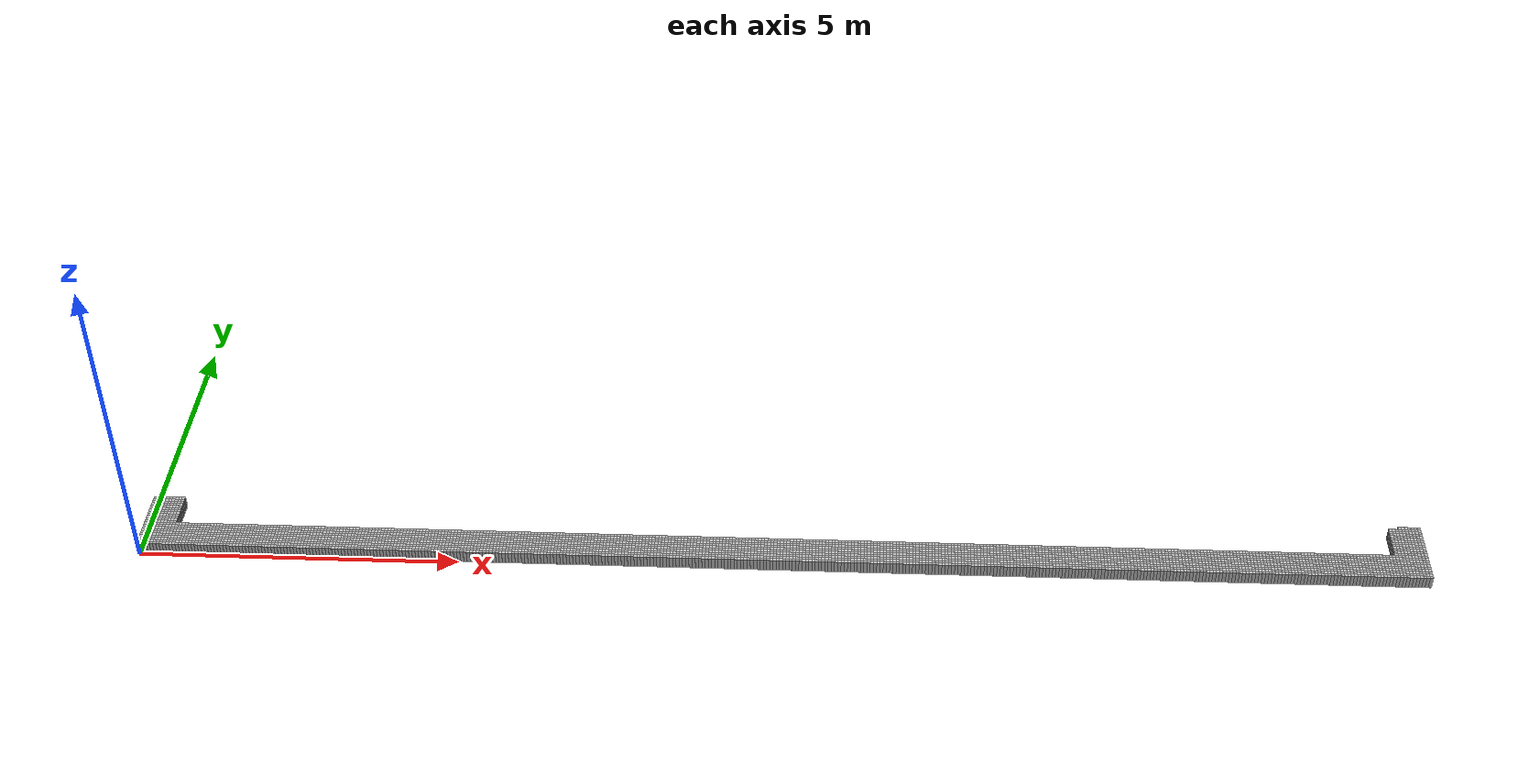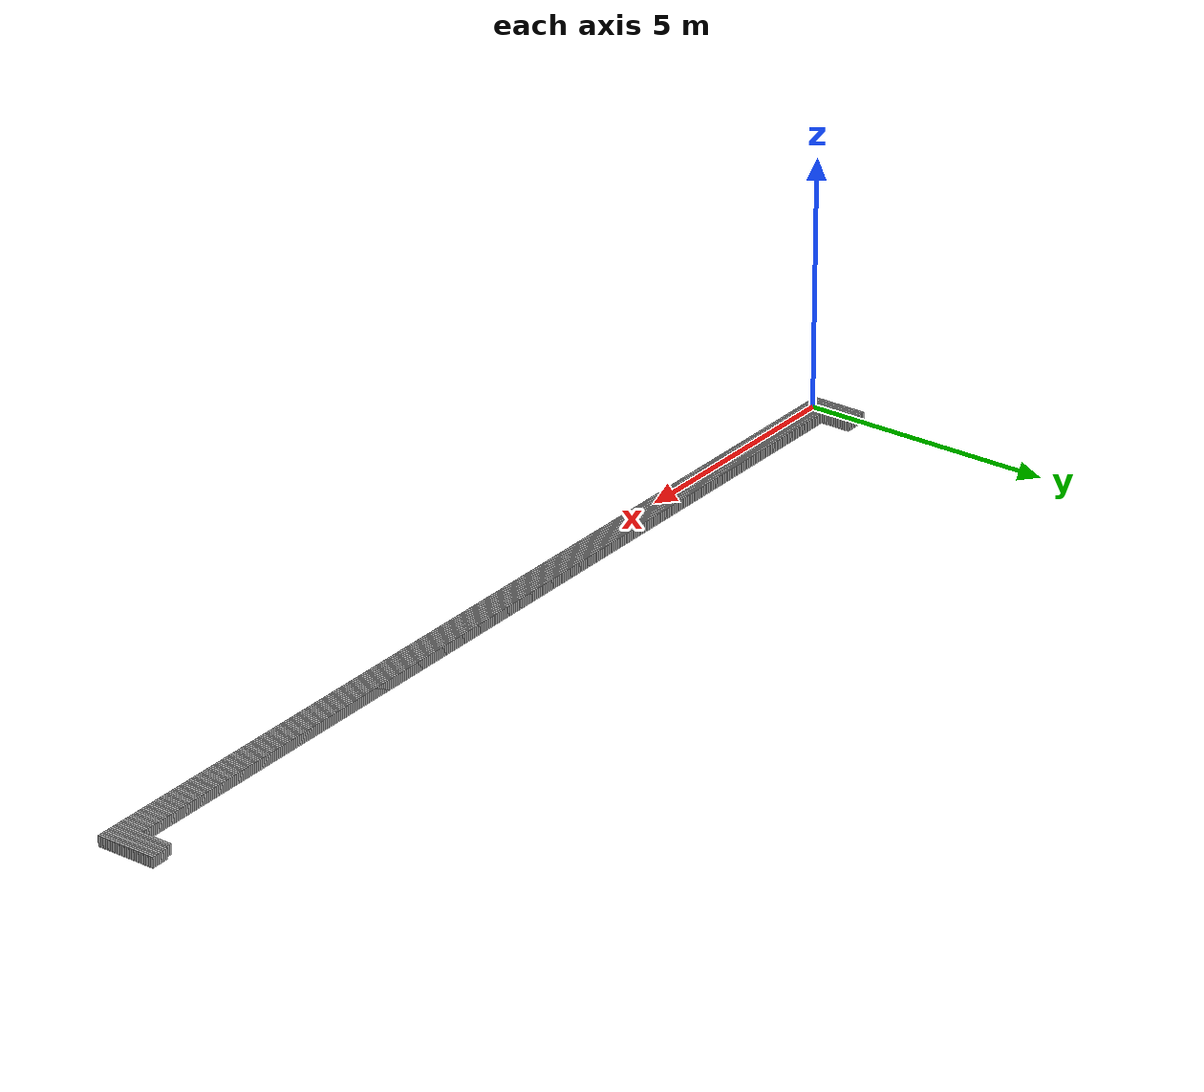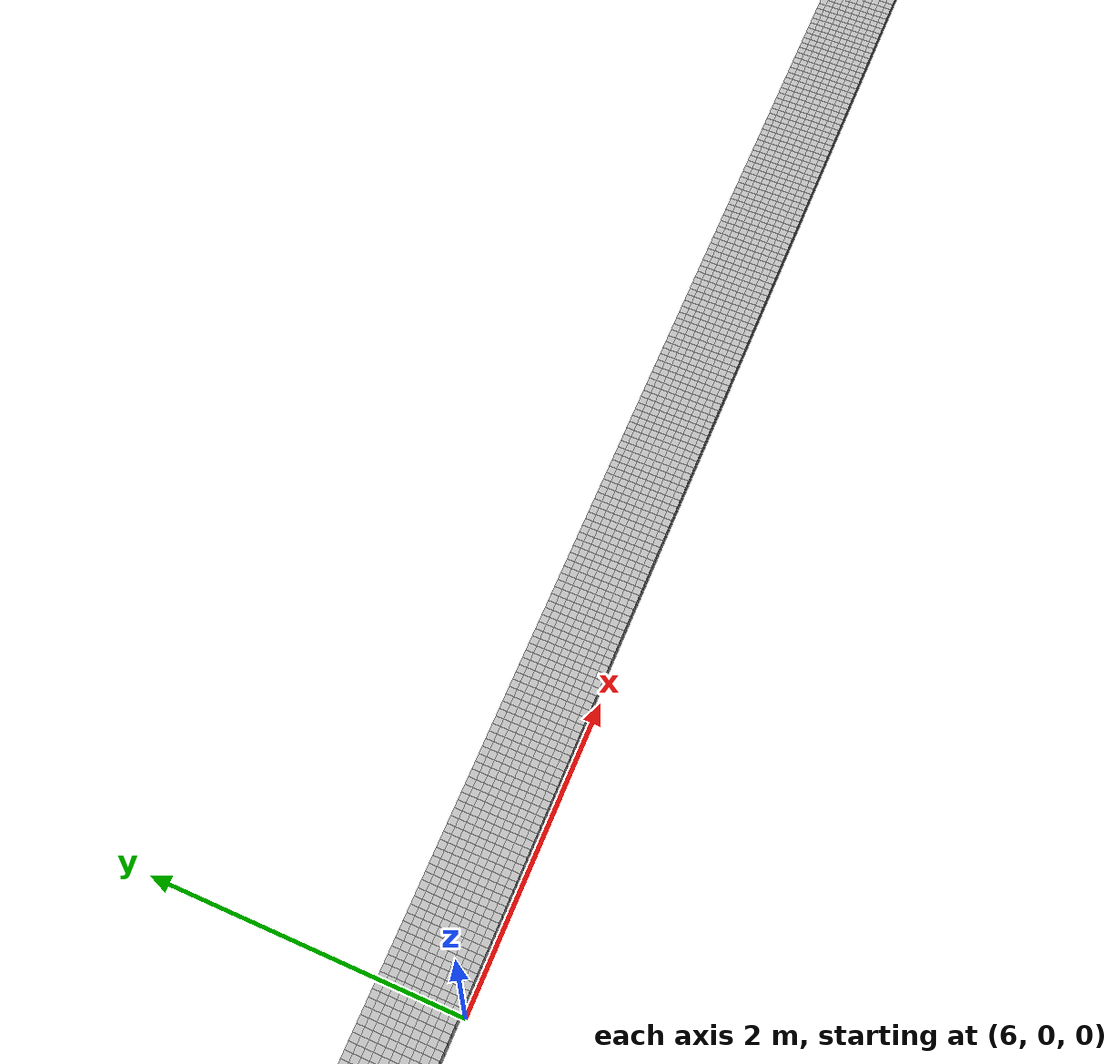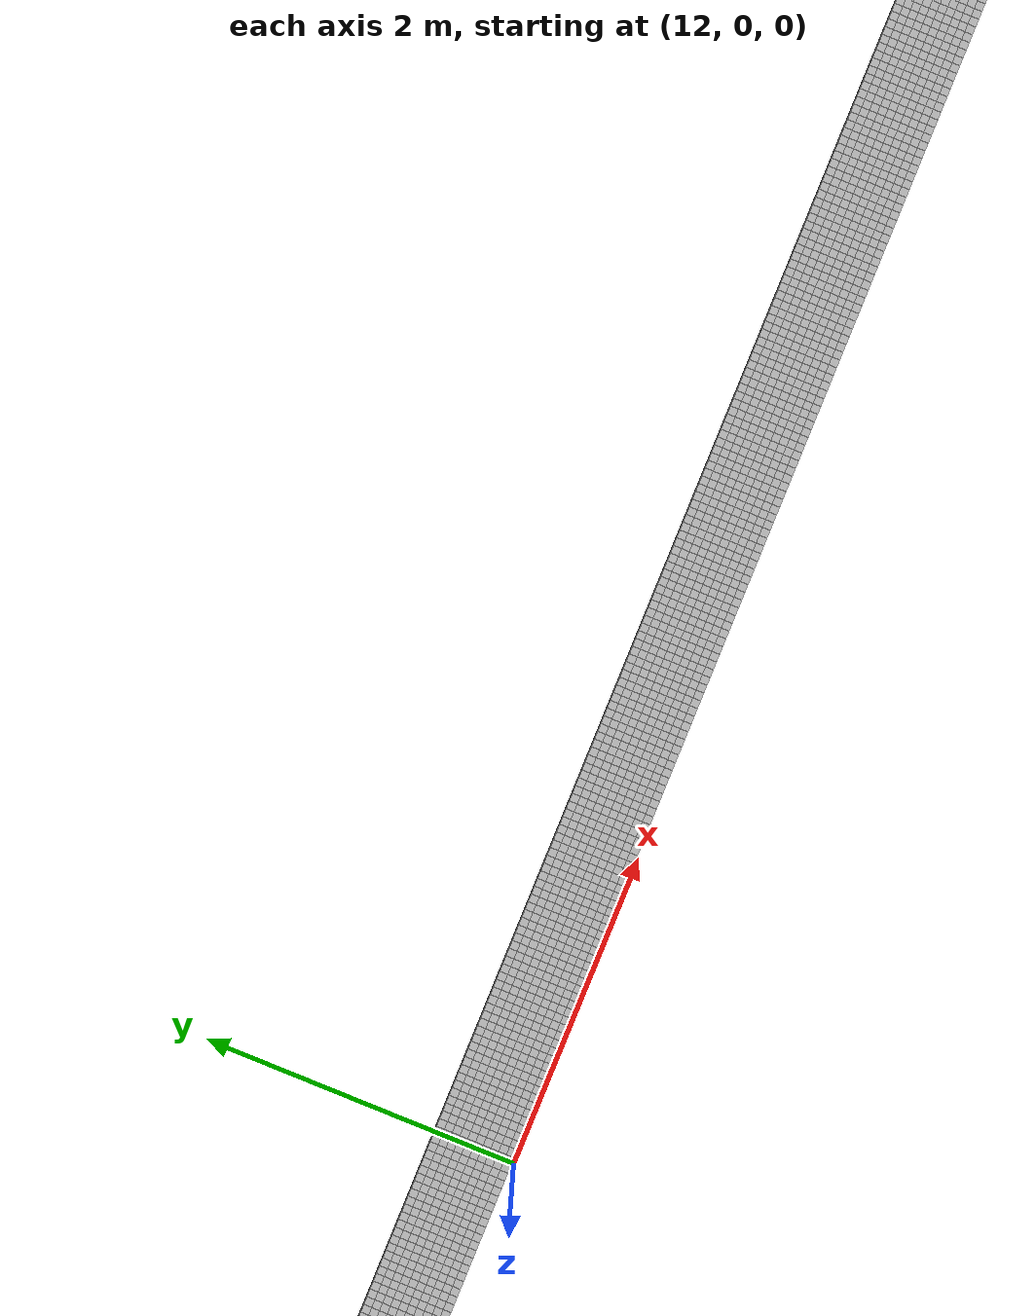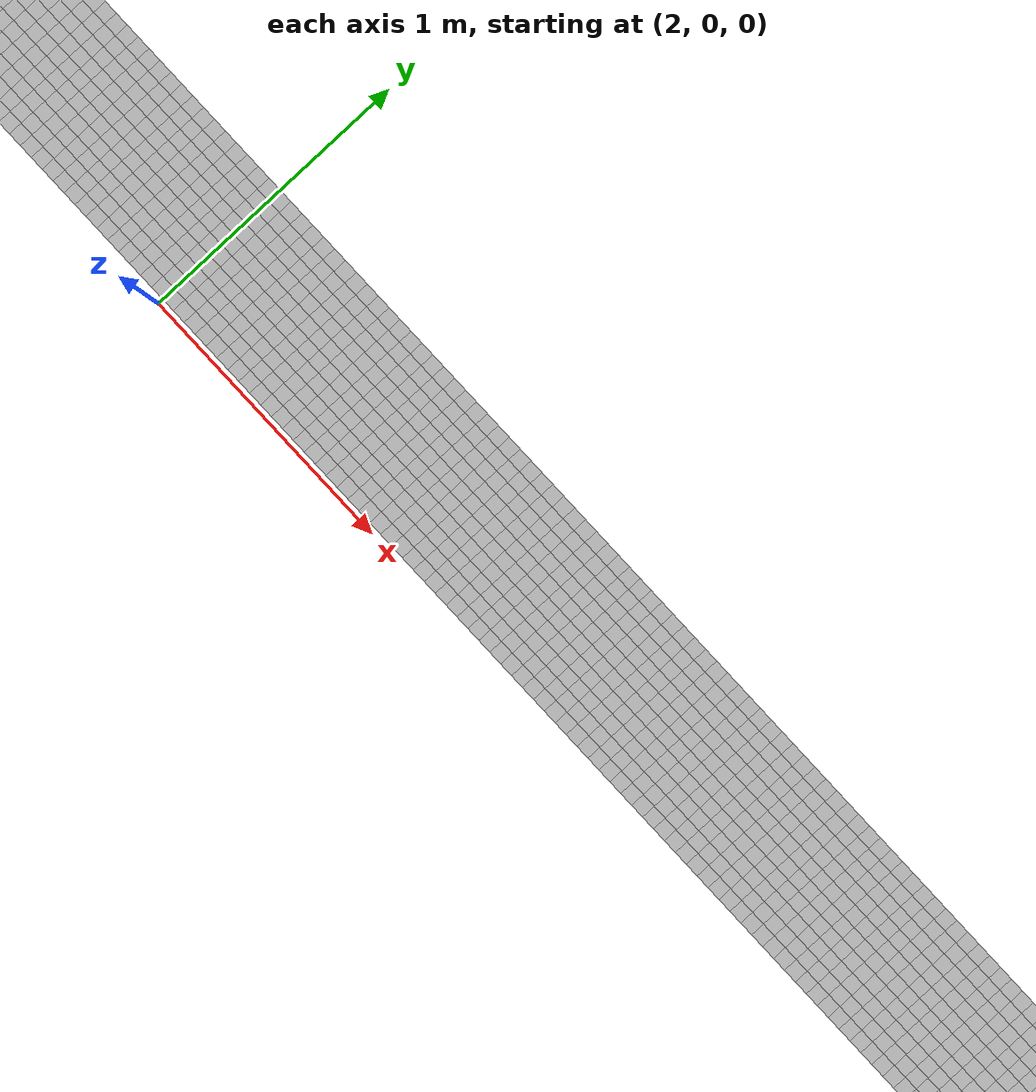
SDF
<sdf version="1.6">
 <world name="default">
  <model name="obstacle_393_377">
   <static>true</static>
   <link name="link">
    <pose>19.650000000000002 1.1500000000000001 0.1 0 0 0</pose>
    <collision name="collision"><geometry><box><size>0.05 0.05 0.2</size></box></geometry></collision>
    <visual name="visual"><geometry><box><size>0.05 0.05 0.2</size></box></geometry></visual>
   </link>
  </model>
  <model name="obstacle_394_377">
   <static>true</static>
   <link name="link">
    <pose>19.700000000000003 1.1500000000000001 0.1 0 0 0</pose>
    <collision name="collision"><geometry><box><size>0.05 0.05 0.2</size></box></geometry></collision>
    <visual name="visual"><geometry><box><size>0.05 0.05 0.2</size></box></geometry></visual>
   </link>
  </model>
  <model name="obstacle_395_377">
   <static>true</static>
   <link name="link">
    <pose>19.75 1.1500000000000001 0.1 0 0 0</pose>
    <collision name="collision"><geometry><box><size>0.05 0.05 0.2</size></box></geometry></collision>
    <visual name="visual"><geometry><box><size>0.05 0.05 0.2</size></box></geometry></visual>
   </link>
  </model>
  <model name="obstacle_396_377">
   <static>true</static>
   <link name="link">
    <pose>19.8 1.1500000000000001 0.1 0 0 0</pose>
    <collision name="collision"><geometry><box><size>0.05 0.05 0.2</size></box></geometry></collision>
    <visual name="visual"><geometry><box><size>0.05 0.05 0.2</size></box></geometry></visual>
   </link>
  </model>
  <model name="obstacle_397_377">
   <static>true</static>
   <link name="link">
    <pose>19.85 1.1500000000000001 0.1 0 0 0</pose>
    <collision name="collision"><geometry><box><size>0.05 0.05 0.2</size></box></geometry></collision>
    <visual name="visual"><geometry><box><size>0.05 0.05 0.2</size></box></geometry></visual>
   </link>
  </model>
  <model name="obstacle_398_377">
   <static>true</static>
   <link name="link">
    <pose>19.900000000000002 1.1500000000000001 0.1 0 0 0</pose>
    <collision name="collision"><geometry><box><size>0.05 0.05 0.2</size></box></geometry></collision>
    <visual name="visual"><geometry><box><size>0.05 0.05 0.2</size></box></geometry></visual>
   </link>
  </model>
  <model name="obstacle_399_377">
   <static>true</static>
   <link name="link">
    <pose>19.950000000000003 1.1500000000000001 0.1 0 0 0</pose>
    <collision name="collision"><geometry><box><size>0.05 0.05 0.2</size></box></geometry></collision>
    <visual name="visual"><geometry><box><size>0.05 0.05 0.2</size></box></geometry></visual>
   </link>
  </model>
  <model name="obstacle_0_378">
   <static>true</static>
   <link name="link">
    <pose>0.0 1.1 0.1 0 0 0</pose>
    <collision name="collision"><geometry><box><size>0.05 0.05 0.2</size></box></geometry></collision>
    <visual name="visual"><geometry><box><size>0.05 0.05 0.2</size></box></geometry></visual>
   </link>
  </model>
  <model name="obstacle_1_378">
   <static>true</static>
   <link name="link">
    <pose>0.05 1.1 0.1 0 0 0</pose>
    <collision name="collision"><geometry><box><size>0.05 0.05 0.2</size></box></geometry></collision>
    <visual name="visual"><geometry><box><size>0.05 0.05 0.2</size></box></geometry></visual>
   </link>
  </model>
  <model name="obstacle_2_378">
   <static>true</static>
   <link name="link">
    <pose>0.1 1.1 0.1 0 0 0</pose>
    <collision name="collision"><geometry><box><size>0.05 0.05 0.2</size></box></geometry></collision>
    <visual name="visual"><geometry><box><size>0.05 0.05 0.2</size></box></geometry></visual>
   </link>
  </model>
  <model name="obstacle_3_378">
   <static>true</static>
   <link name="link">
    <pose>0.15000000000000002 1.1 0.1 0 0 0</pose>
    <collision name="collision"><geometry><box><size>0.05 0.05 0.2</size></box></geometry></collision>
    <visual name="visual"><geometry><box><size>0.05 0.05 0.2</size></box></geometry></visual>
   </link>
  </model>
  <model name="obstacle_4_378">
   <static>true</static>
   <link name="link">
    <pose>0.2 1.1 0.1 0 0 0</pose>
    <collision name="collision"><geometry><box><size>0.05 0.05 0.2</size></box></geometry></collision>
    <visual name="visual"><geometry><box><size>0.05 0.05 0.2</size></box></geometry></visual>
   </link>
  </model>
  <model name="obstacle_5_378">
   <static>true</static>
   <link name="link">
    <pose>0.25 1.1 0.1 0 0 0</pose>
    <collision name="collision"><geometry><box><size>0.05 0.05 0.2</size></box></geometry></collision>
    <visual name="visual"><geometry><box><size>0.05 0.05 0.2</size></box></geometry></visual>
   </link>
  </model>
  <model name="obstacle_6_378">
   <static>true</static>
   <link name="link">
    <pose>0.30000000000000004 1.1 0.1 0 0 0</pose>
    <collision name="collision"><geometry><box><size>0.05 0.05 0.2</size></box></geometry></collision>
    <visual name="visual"><geometry><box><size>0.05 0.05 0.2</size></box></geometry></visual>
   </link>
  </model>
  <model name="obstacle_7_378">
   <static>true</static>
   <link name="link">
    <pose>0.35000000000000003 1.1 0.1 0 0 0</pose>
    <collision name="collision"><geometry><box><size>0.05 0.05 0.2</size></box></geometry></collision>
    <visual name="visual"><geometry><box><size>0.05 0.05 0.2</size></box></geometry></visual>
   </link>
  </model>
  <model name="obstacle_8_378">
   <static>true</static>
   <link name="link">
    <pose>0.4 1.1 0.1 0 0 0</pose>
    <collision name="collision"><geometry><box><size>0.05 0.05 0.2</size></box></geometry></collision>
    <visual name="visual"><geometry><box><size>0.05 0.05 0.2</size></box></geometry></visual>
   </link>
  </model>
  <model name="obstacle_9_378">
   <static>true</static>
   <link name="link">
    <pose>0.45 1.1 0.1 0 0 0</pose>
    <collision name="collision"><geometry><box><size>0.05 0.05 0.2</size></box></geometry></collision>
    <visual name="visual"><geometry><box><size>0.05 0.05 0.2</size></box></geometry></visual>
   </link>
  </model>
  <model name="obstacle_390_378">
   <static>true</static>
   <link name="link">
    <pose>19.5 1.1 0.1 0 0 0</pose>
    <collision name="collision"><geometry><box><size>0.05 0.05 0.2</size></box></geometry></collision>
    <visual name="visual"><geometry><box><size>0.05 0.05 0.2</size></box></geometry></visual>
   </link>
  </model>
  <model name="obstacle_391_378">
   <static>true</static>
   <link name="link">
    <pose>19.55 1.1 0.1 0 0 0</pose>
    <collision name="collision"><geometry><box><size>0.05 0.05 0.2</size></box></geometry></collision>
    <visual name="visual"><geometry><box><size>0.05 0.05 0.2</size></box></geometry></visual>
   </link>
  </model>
  <model name="obstacle_392_378">
   <static>true</static>
   <link name="link">
    <pose>19.6 1.1 0.1 0 0 0</pose>
    <collision name="collision"><geometry><box><size>0.05 0.05 0.2</size></box></geometry></collision>
    <visual name="visual"><geometry><box><size>0.05 0.05 0.2</size></box></geometry></visual>
   </link>
  </model>
  <model name="obstacle_393_378">
   <static>true</static>
   <link name="link">
    <pose>19.650000000000002 1.1 0.1 0 0 0</pose>
    <collision name="collision"><geometry><box><size>0.05 0.05 0.2</size></box></geometry></collision>
    <visual name="visual"><geometry><box><size>0.05 0.05 0.2</size></box></geometry></visual>
   </link>
  </model>
  <model name="obstacle_394_378">
   <static>true</static>
   <link name="link">
    <pose>19.700000000000003 1.1 0.1 0 0 0</pose>
    <collision name="collision"><geometry><box><size>0.05 0.05 0.2</size></box></geometry></collision>
    <visual name="visual"><geometry><box><size>0.05 0.05 0.2</size></box></geometry></visual>
   </link>
  </model>
  <model name="obstacle_395_378">
   <static>true</static>
   <link name="link">
    <pose>19.75 1.1 0.1 0 0 0</pose>
    <collision name="collision"><geometry><box><size>0.05 0.05 0.2</size></box></geometry></collision>
    <visual name="visual"><geometry><box><size>0.05 0.05 0.2</size></box></geometry></visual>
   </link>
  </model>
  <model name="obstacle_396_378">
   <static>true</static>
   <link name="link">
    <pose>19.8 1.1 0.1 0 0 0</pose>
    <collision name="collision"><geometry><box><size>0.05 0.05 0.2</size></box></geometry></collision>
    <visual name="visual"><geometry><box><size>0.05 0.05 0.2</size></box></geometry></visual>
   </link>
  </model>
  <model name="obstacle_397_378">
   <static>true</static>
   <link name="link">
    <pose>19.85 1.1 0.1 0 0 0</pose>
    <collision name="collision"><geometry><box><size>0.05 0.05 0.2</size></box></geometry></collision>
    <visual name="visual"><geometry><box><size>0.05 0.05 0.2</size></box></geometry></visual>
   </link>
  </model>
  <model name="obstacle_398_378">
   <static>true</static>
   <link name="link">
    <pose>19.900000000000002 1.1 0.1 0 0 0</pose>
    <collision name="collision"><geometry><box><size>0.05 0.05 0.2</size></box></geometry></collision>
    <visual name="visual"><geometry><box><size>0.05 0.05 0.2</size></box></geometry></visual>
   </link>
  </model>
  <model name="obstacle_399_378">
   <static>true</static>
   <link name="link">
    <pose>19.950000000000003 1.1 0.1 0 0 0</pose>
    <collision name="collision"><geometry><box><size>0.05 0.05 0.2</size></box></geometry></collision>
    <visual name="visual"><geometry><box><size>0.05 0.05 0.2</size></box></geometry></visual>
   </link>
  </model>
  <model name="obstacle_0_379">
   <static>true</static>
   <link name="link">
    <pose>0.0 1.05 0.1 0 0 0</pose>
    <collision name="collision"><geometry><box><size>0.05 0.05 0.2</size></box></geometry></collision>
    <visual name="visual"><geometry><box><size>0.05 0.05 0.2</size></box></geometry></visual>
   </link>
  </model>
  <model name="obstacle_1_379">
   <static>true</static>
   <link name="link">
    <pose>0.05 1.05 0.1 0 0 0</pose>
    <collision name="collision"><geometry><box><size>0.05 0.05 0.2</size></box></geometry></collision>
    <visual name="visual"><geometry><box><size>0.05 0.05 0.2</size></box></geometry></visual>
   </link>
  </model>
  <model name="obstacle_2_379">
   <static>true</static>
   <link name="link">
    <pose>0.1 1.05 0.1 0 0 0</pose>
    <collision name="collision"><geometry><box><size>0.05 0.05 0.2</size></box></geometry></collision>
    <visual name="visual"><geometry><box><size>0.05 0.05 0.2</size></box></geometry></visual>
   </link>
  </model>
  <model name="obstacle_3_379">
   <static>true</static>
   <link name="link">
    <pose>0.15000000000000002 1.05 0.1 0 0 0</pose>
    <collision name="collision"><geometry><box><size>0.05 0.05 0.2</size></box></geometry></collision>
    <visual name="visual"><geometry><box><size>0.05 0.05 0.2</size></box></geometry></visual>
   </link>
  </model>
  <model name="obstacle_4_379">
   <static>true</static>
   <link name="link">
    <pose>0.2 1.05 0.1 0 0 0</pose>
    <collision name="collision"><geometry><box><size>0.05 0.05 0.2</size></box></geometry></collision>
    <visual name="visual"><geometry><box><size>0.05 0.05 0.2</size></box></geometry></visual>
   </link>
  </model>
  <model name="obstacle_5_379">
   <static>true</static>
   <link name="link">
    <pose>0.25 1.05 0.1 0 0 0</pose>
    <collision name="collision"><geometry><box><size>0.05 0.05 0.2</size></box></geometry></collision>
    <visual name="visual"><geometry><box><size>0.05 0.05 0.2</size></box></geometry></visual>
   </link>
  </model>
  <model name="obstacle_6_379">
   <static>true</static>
   <link name="link">
    <pose>0.30000000000000004 1.05 0.1 0 0 0</pose>
    <collision name="collision"><geometry><box><size>0.05 0.05 0.2</size></box></geometry></collision>
    <visual name="visual"><geometry><box><size>0.05 0.05 0.2</size></box></geometry></visual>
   </link>
  </model>
  <model name="obstacle_7_379">
   <static>true</static>
   <link name="link">
    <pose>0.35000000000000003 1.05 0.1 0 0 0</pose>
    <collision name="collision"><geometry><box><size>0.05 0.05 0.2</size></box></geometry></collision>
    <visual name="visual"><geometry><box><size>0.05 0.05 0.2</size></box></geometry></visual>
   </link>
  </model>
  <model name="obstacle_8_379">
   <static>true</static>
   <link name="link">
    <pose>0.4 1.05 0.1 0 0 0</pose>
    <collision name="collision"><geometry><box><size>0.05 0.05 0.2</size></box></geometry></collision>
    <visual name="visual"><geometry><box><size>0.05 0.05 0.2</size></box></geometry></visual>
   </link>
  </model>
  <model name="obstacle_9_379">
   <static>true</static>
   <link name="link">
    <pose>0.45 1.05 0.1 0 0 0</pose>
    <collision name="collision"><geometry><box><size>0.05 0.05 0.2</size></box></geometry></collision>
    <visual name="visual"><geometry><box><size>0.05 0.05 0.2</size></box></geometry></visual>
   </link>
  </model>
  <model name="obstacle_390_379">
   <static>true</static>
   <link name="link">
    <pose>19.5 1.05 0.1 0 0 0</pose>
    <collision name="collision"><geometry><box><size>0.05 0.05 0.2</size></box></geometry></collision>
    <visual name="visual"><geometry><box><size>0.05 0.05 0.2</size></box></geometry></visual>
   </link>
  </model>
  <model name="obstacle_391_379">
   <static>true</static>
   <link name="link">
    <pose>19.55 1.05 0.1 0 0 0</pose>
    <collision name="collision"><geometry><box><size>0.05 0.05 0.2</size></box></geometry></collision>
    <visual name="visual"><geometry><box><size>0.05 0.05 0.2</size></box></geometry></visual>
   </link>
  </model>
  <model name="obstacle_392_379">
   <static>true</static>
   <link name="link">
    <pose>19.6 1.05 0.1 0 0 0</pose>
    <collision name="collision"><geometry><box><size>0.05 0.05 0.2</size></box></geometry></collision>
    <visual name="visual"><geometry><box><size>0.05 0.05 0.2</size></box></geometry></visual>
   </link>
  </model>
  <model name="obstacle_393_379">
   <static>true</static>
   <link name="link">
    <pose>19.650000000000002 1.05 0.1 0 0 0</pose>
    <collision name="collision"><geometry><box><size>0.05 0.05 0.2</size></box></geometry></collision>
    <visual name="visual"><geometry><box><size>0.05 0.05 0.2</size></box></geometry></visual>
   </link>
  </model>
  <model name="obstacle_394_379">
   <static>true</static>
   <link name="link">
    <pose>19.700000000000003 1.05 0.1 0 0 0</pose>
    <collision name="collision"><geometry><box><size>0.05 0.05 0.2</size></box></geometry></collision>
    <visual name="visual"><geometry><box><size>0.05 0.05 0.2</size></box></geometry></visual>
   </link>
  </model>
  <model name="obstacle_395_379">
   <static>true</static>
   <link name="link">
    <pose>19.75 1.05 0.1 0 0 0</pose>
    <collision name="collision"><geometry><box><size>0.05 0.05 0.2</size></box></geometry></collision>
    <visual name="visual"><geometry><box><size>0.05 0.05 0.2</size></box></geometry></visual>
   </link>
  </model>
  <model name="obstacle_396_379">
   <static>true</static>
   <link name="link">
    <pose>19.8 1.05 0.1 0 0 0</pose>
    <collision name="collision"><geometry><box><size>0.05 0.05 0.2</size></box></geometry></collision>
    <visual name="visual"><geometry><box><size>0.05 0.05 0.2</size></box></geometry></visual>
   </link>
  </model>
  <model name="obstacle_397_379">
   <static>true</static>
   <link name="link">
    <pose>19.85 1.05 0.1 0 0 0</pose>
    <collision name="collision"><geometry><box><size>0.05 0.05 0.2</size></box></geometry></collision>
    <visual name="visual"><geometry><box><size>0.05 0.05 0.2</size></box></geometry></visual>
   </link>
  </model>
  <model name="obstacle_398_379">
   <static>true</static>
   <link name="link">
    <pose>19.900000000000002 1.05 0.1 0 0 0</pose>
    <collision name="collision"><geometry><box><size>0.05 0.05 0.2</size></box></geometry></collision>
    <visual name="visual"><geometry><box><size>0.05 0.05 0.2</size></box></geometry></visual>
   </link>
  </model>
  <model name="obstacle_399_379">
   <static>true</static>
   <link name="link">
    <pose>19.950000000000003 1.05 0.1 0 0 0</pose>
    <collision name="collision"><geometry><box><size>0.05 0.05 0.2</size></box></geometry></collision>
    <visual name="visual"><geometry><box><size>0.05 0.05 0.2</size></box></geometry></visual>
   </link>
  </model>
  <model name="obstacle_0_380">
   <static>true</static>
   <link name="link">
    <pose>0.0 1.0 0.1 0 0 0</pose>
    <collision name="collision"><geometry><box><size>0.05 0.05 0.2</size></box></geometry></collision>
    <visual name="visual"><geometry><box><size>0.05 0.05 0.2</size></box></geometry></visual>
   </link>
  </model>
  <model name="obstacle_1_380">
   <static>true</static>
   <link name="link">
    <pose>0.05 1.0 0.1 0 0 0</pose>
    <collision name="collision"><geometry><box><size>0.05 0.05 0.2</size></box></geometry></collision>
    <visual name="visual"><geometry><box><size>0.05 0.05 0.2</size></box></geometry></visual>
   </link>
  </model>
  <model name="obstacle_2_380">
   <static>true</static>
   <link name="link">
    <pose>0.1 1.0 0.1 0 0 0</pose>
    <collision name="collision"><geometry><box><size>0.05 0.05 0.2</size></box></geometry></collision>
    <visual name="visual"><geometry><box><size>0.05 0.05 0.2</size></box></geometry></visual>
   </link>
  </model>
  <model name="obstacle_3_380">
   <static>true</static>
   <link name="link">
    <pose>0.15000000000000002 1.0 0.1 0 0 0</pose>
    <collision name="collision"><geometry><box><size>0.05 0.05 0.2</size></box></geometry></collision>
    <visual name="visual"><geometry><box><size>0.05 0.05 0.2</size></box></geometry></visual>
   </link>
  </model>
  <model name="obstacle_4_380">
   <static>true</static>
   <link name="link">
    <pose>0.2 1.0 0.1 0 0 0</pose>
    <collision name="collision"><geometry><box><size>0.05 0.05 0.2</size></box></geometry></collision>
    <visual name="visual"><geometry><box><size>0.05 0.05 0.2</size></box></geometry></visual>
   </link>
  </model>
  <model name="obstacle_5_380">
   <static>true</static>
   <link name="link">
    <pose>0.25 1.0 0.1 0 0 0</pose>
    <collision name="collision"><geometry><box><size>0.05 0.05 0.2</size></box></geometry></collision>
    <visual name="visual"><geometry><box><size>0.05 0.05 0.2</size></box></geometry></visual>
   </link>
  </model>
  <model name="obstacle_6_380">
   <static>true</static>
   <link name="link">
    <pose>0.30000000000000004 1.0 0.1 0 0 0</pose>
    <collision name="collision"><geometry><box><size>0.05 0.05 0.2</size></box></geometry></collision>
    <visual name="visual"><geometry><box><size>0.05 0.05 0.2</size></box></geometry></visual>
   </link>
  </model>
  <model name="obstacle_7_380">
   <static>true</static>
   <link name="link">
    <pose>0.35000000000000003 1.0 0.1 0 0 0</pose>
    <collision name="collision"><geometry><box><size>0.05 0.05 0.2</size></box></geometry></collision>
    <visual name="visual"><geometry><box><size>0.05 0.05 0.2</size></box></geometry></visual>
   </link>
  </model>
  <model name="obstacle_8_380">
   <static>true</static>
   <link name="link">
    <pose>0.4 1.0 0.1 0 0 0</pose>
    <collision name="collision"><geometry><box><size>0.05 0.05 0.2</size></box></geometry></collision>
    <visual name="visual"><geometry><box><size>0.05 0.05 0.2</size></box></geometry></visual>
   </link>
  </model>
  <model name="obstacle_9_380">
   <static>true</static>
   <link name="link">
    <pose>0.45 1.0 0.1 0 0 0</pose>
    <collision name="collision"><geometry><box><size>0.05 0.05 0.2</size></box></geometry></collision>
    <visual name="visual"><geometry><box><size>0.05 0.05 0.2</size></box></geometry></visual>
   </link>
  </model>
  <model name="obstacle_390_380">
   <static>true</static>
   <link name="link">
    <pose>19.5 1.0 0.1 0 0 0</pose>
    <collision name="collision"><geometry><box><size>0.05 0.05 0.2</size></box></geometry></collision>
    <visual name="visual"><geometry><box><size>0.05 0.05 0.2</size></box></geometry></visual>
   </link>
  </model>
  <model name="obstacle_391_380">
   <static>true</static>
   <link name="link">
    <pose>19.55 1.0 0.1 0 0 0</pose>
    <collision name="collision"><geometry><box><size>0.05 0.05 0.2</size></box></geometry></collision>
    <visual name="visual"><geometry><box><size>0.05 0.05 0.2</size></box></geometry></visual>
   </link>
  </model>
  <model name="obstacle_392_380">
   <static>true</static>
   <link name="link">
    <pose>19.6 1.0 0.1 0 0 0</pose>
    <collision name="collision"><geometry><box><size>0.05 0.05 0.2</size></box></geometry></collision>
    <visual name="visual"><geometry><box><size>0.05 0.05 0.2</size></box></geometry></visual>
   </link>
  </model>
  <model name="obstacle_393_380">
   <static>true</static>
   <link name="link">
    <pose>19.650000000000002 1.0 0.1 0 0 0</pose>
    <collision name="collision"><geometry><box><size>0.05 0.05 0.2</size></box></geometry></collision>
    <visual name="visual"><geometry><box><size>0.05 0.05 0.2</size></box></geometry></visual>
   </link>
  </model>
  <model name="obstacle_394_380">
   <static>true</static>
   <link name="link">
    <pose>19.700000000000003 1.0 0.1 0 0 0</pose>
    <collision name="collision"><geometry><box><size>0.05 0.05 0.2</size></box></geometry></collision>
    <visual name="visual"><geometry><box><size>0.05 0.05 0.2</size></box></geometry></visual>
   </link>
  </model>
  <model name="obstacle_395_380">
   <static>true</static>
   <link name="link">
    <pose>19.75 1.0 0.1 0 0 0</pose>
    <collision name="collision"><geometry><box><size>0.05 0.05 0.2</size></box></geometry></collision>
    <visual name="visual"><geometry><box><size>0.05 0.05 0.2</size></box></geometry></visual>
   </link>
  </model>
  <model name="obstacle_396_380">
   <static>true</static>
   <link name="link">
    <pose>19.8 1.0 0.1 0 0 0</pose>
    <collision name="collision"><geometry><box><size>0.05 0.05 0.2</size></box></geometry></collision>
    <visual name="visual"><geometry><box><size>0.05 0.05 0.2</size></box></geometry></visual>
   </link>
  </model>
  <model name="obstacle_397_380">
   <static>true</static>
   <link name="link">
    <pose>19.85 1.0 0.1 0 0 0</pose>
    <collision name="collision"><geometry><box><size>0.05 0.05 0.2</size></box></geometry></collision>
    <visual name="visual"><geometry><box><size>0.05 0.05 0.2</size></box></geometry></visual>
   </link>
  </model>
  <model name="obstacle_398_380">
   <static>true</static>
   <link name="link">
    <pose>19.900000000000002 1.0 0.1 0 0 0</pose>
    <collision name="collision"><geometry><box><size>0.05 0.05 0.2</size></box></geometry></collision>
    <visual name="visual"><geometry><box><size>0.05 0.05 0.2</size></box></geometry></visual>
   </link>
  </model>
  <model name="obstacle_399_380">
   <static>true</static>
   <link name="link">
    <pose>19.950000000000003 1.0 0.1 0 0 0</pose>
    <collision name="collision"><geometry><box><size>0.05 0.05 0.2</size></box></geometry></collision>
    <visual name="visual"><geometry><box><size>0.05 0.05 0.2</size></box></geometry></visual>
   </link>
  </model>
  <model name="obstacle_0_381">
   <static>true</static>
   <link name="link">
    <pose>0.0 0.9500000000000001 0.1 0 0 0</pose>
    <collision name="collision"><geometry><box><size>0.05 0.05 0.2</size></box></geometry></collision>
    <visual name="visual"><geometry><box><size>0.05 0.05 0.2</size></box></geometry></visual>
   </link>
  </model>
  <model name="obstacle_1_381">
   <static>true</static>
   <link name="link">
    <pose>0.05 0.9500000000000001 0.1 0 0 0</pose>
    <collision name="collision"><geometry><box><size>0.05 0.05 0.2</size></box></geometry></collision>
    <visual name="visual"><geometry><box><size>0.05 0.05 0.2</size></box></geometry></visual>
   </link>
  </model>
  <model name="obstacle_2_381">
   <static>true</static>
   <link name="link">
    <pose>0.1 0.9500000000000001 0.1 0 0 0</pose>
    <collision name="collision"><geometry><box><size>0.05 0.05 0.2</size></box></geometry></collision>
    <visual name="visual"><geometry><box><size>0.05 0.05 0.2</size></box></geometry></visual>
   </link>
  </model>
  <model name="obstacle_3_381">
   <static>true</static>
   <link name="link">
    <pose>0.15000000000000002 0.9500000000000001 0.1 0 0 0</pose>
    <collision name="collision"><geometry><box><size>0.05 0.05 0.2</size></box></geometry></collision>
    <visual name="visual"><geometry><box><size>0.05 0.05 0.2</size></box></geometry></visual>
   </link>
  </model>
  <model name="obstacle_4_381">
   <static>true</static>
   <link name="link">
    <pose>0.2 0.9500000000000001 0.1 0 0 0</pose>
    <collision name="collision"><geometry><box><size>0.05 0.05 0.2</size></box></geometry></collision>
    <visual name="visual"><geometry><box><size>0.05 0.05 0.2</size></box></geometry></visual>
   </link>
  </model>
  <model name="obstacle_5_381">
   <static>true</static>
   <link name="link">
    <pose>0.25 0.9500000000000001 0.1 0 0 0</pose>
    <collision name="collision"><geometry><box><size>0.05 0.05 0.2</size></box></geometry></collision>
    <visual name="visual"><geometry><box><size>0.05 0.05 0.2</size></box></geometry></visual>
   </link>
  </model>
  <model name="obstacle_6_381">
   <static>true</static>
   <link name="link">
    <pose>0.30000000000000004 0.9500000000000001 0.1 0 0 0</pose>
    <collision name="collision"><geometry><box><size>0.05 0.05 0.2</size></box></geometry></collision>
    <visual name="visual"><geometry><box><size>0.05 0.05 0.2</size></box></geometry></visual>
   </link>
  </model>
  <model name="obstacle_7_381">
   <static>true</static>
   <link name="link">
    <pose>0.35000000000000003 0.9500000000000001 0.1 0 0 0</pose>
    <collision name="collision"><geometry><box><size>0.05 0.05 0.2</size></box></geometry></collision>
    <visual name="visual"><geometry><box><size>0.05 0.05 0.2</size></box></geometry></visual>
   </link>
  </model>
  <model name="obstacle_8_381">
   <static>true</static>
   <link name="link">
    <pose>0.4 0.9500000000000001 0.1 0 0 0</pose>
    <collision name="collision"><geometry><box><size>0.05 0.05 0.2</size></box></geometry></collision>
    <visual name="visual"><geometry><box><size>0.05 0.05 0.2</size></box></geometry></visual>
   </link>
  </model>
  <model name="obstacle_9_381">
   <static>true</static>
   <link name="link">
    <pose>0.45 0.9500000000000001 0.1 0 0 0</pose>
    <collision name="collision"><geometry><box><size>0.05 0.05 0.2</size></box></geometry></collision>
    <visual name="visual"><geometry><box><size>0.05 0.05 0.2</size></box></geometry></visual>
   </link>
  </model>
  <model name="obstacle_390_381">
   <static>true</static>
   <link name="link">
    <pose>19.5 0.9500000000000001 0.1 0 0 0</pose>
    <collision name="collision"><geometry><box><size>0.05 0.05 0.2</size></box></geometry></collision>
    <visual name="visual"><geometry><box><size>0.05 0.05 0.2</size></box></geometry></visual>
   </link>
  </model>
  <model name="obstacle_391_381">
   <static>true</static>
   <link name="link">
    <pose>19.55 0.9500000000000001 0.1 0 0 0</pose>
    <collision name="collision"><geometry><box><size>0.05 0.05 0.2</size></box></geometry></collision>
    <visual name="visual"><geometry><box><size>0.05 0.05 0.2</size></box></geometry></visual>
   </link>
  </model>
  <model name="obstacle_392_381">
   <static>true</static>
   <link name="link">
    <pose>19.6 0.9500000000000001 0.1 0 0 0</pose>
    <collision name="collision"><geometry><box><size>0.05 0.05 0.2</size></box></geometry></collision>
    <visual name="visual"><geometry><box><size>0.05 0.05 0.2</size></box></geometry></visual>
   </link>
  </model>
  <model name="obstacle_393_381">
   <static>true</static>
   <link name="link">
    <pose>19.650000000000002 0.9500000000000001 0.1 0 0 0</pose>
    <collision name="collision"><geometry><box><size>0.05 0.05 0.2</size></box></geometry></collision>
    <visual name="visual"><geometry><box><size>0.05 0.05 0.2</size></box></geometry></visual>
   </link>
  </model>
  <model name="obstacle_394_381">
   <static>true</static>
   <link name="link">
    <pose>19.700000000000003 0.9500000000000001 0.1 0 0 0</pose>
    <collision name="collision"><geometry><box><size>0.05 0.05 0.2</size></box></geometry></collision>
    <visual name="visual"><geometry><box><size>0.05 0.05 0.2</size></box></geometry></visual>
   </link>
  </model>
  <model name="obstacle_395_381">
   <static>true</static>
   <link name="link">
    <pose>19.75 0.9500000000000001 0.1 0 0 0</pose>
    <collision name="collision"><geometry><box><size>0.05 0.05 0.2</size></box></geometry></collision>
    <visual name="visual"><geometry><box><size>0.05 0.05 0.2</size></box></geometry></visual>
   </link>
  </model>
  <model name="obstacle_396_381">
   <static>true</static>
   <link name="link">
    <pose>19.8 0.9500000000000001 0.1 0 0 0</pose>
    <collision name="collision"><geometry><box><size>0.05 0.05 0.2</size></box></geometry></collision>
    <visual name="visual"><geometry><box><size>0.05 0.05 0.2</size></box></geometry></visual>
   </link>
  </model>
  <model name="obstacle_397_381">
   <static>true</static>
   <link name="link">
    <pose>19.85 0.9500000000000001 0.1 0 0 0</pose>
    <collision name="collision"><geometry><box><size>0.05 0.05 0.2</size></box></geometry></collision>
    <visual name="visual"><geometry><box><size>0.05 0.05 0.2</size></box></geometry></visual>
   </link>
  </model>
  <model name="obstacle_398_381">
   <static>true</static>
   <link name="link">
    <pose>19.900000000000002 0.9500000000000001 0.1 0 0 0</pose>
    <collision name="collision"><geometry><box><size>0.05 0.05 0.2</size></box></geometry></collision>
    <visual name="visual"><geometry><box><size>0.05 0.05 0.2</size></box></geometry></visual>
   </link>
  </model>
  <model name="obstacle_399_381">
   <static>true</static>
   <link name="link">
    <pose>19.950000000000003 0.9500000000000001 0.1 0 0 0</pose>
    <collision name="collision"><geometry><box><size>0.05 0.05 0.2</size></box></geometry></collision>
    <visual name="visual"><geometry><box><size>0.05 0.05 0.2</size></box></geometry></visual>
   </link>
  </model>
  <model name="obstacle_0_382">
   <static>true</static>
   <link name="link">
    <pose>0.0 0.9 0.1 0 0 0</pose>
    <collision name="collision"><geometry><box><size>0.05 0.05 0.2</size></box></geometry></collision>
    <visual name="visual"><geometry><box><size>0.05 0.05 0.2</size></box></geometry></visual>
   </link>
  </model>
  <model name="obstacle_1_382">
   <static>true</static>
   <link name="link">
    <pose>0.05 0.9 0.1 0 0 0</pose>
    <collision name="collision"><geometry><box><size>0.05 0.05 0.2</size></box></geometry></collision>
    <visual name="visual"><geometry><box><size>0.05 0.05 0.2</size></box></geometry></visual>
   </link>
  </model>
  <model name="obstacle_2_382">
   <static>true</static>
   <link name="link">
    <pose>0.1 0.9 0.1 0 0 0</pose>
    <collision name="collision"><geometry><box><size>0.05 0.05 0.2</size></box></geometry></collision>
    <visual name="visual"><geometry><box><size>0.05 0.05 0.2</size></box></geometry></visual>
   </link>
  </model>
  <model name="obstacle_3_382">
   <static>true</static>
   <link name="link">
    <pose>0.15000000000000002 0.9 0.1 0 0 0</pose>
    <collision name="collision"><geometry><box><size>0.05 0.05 0.2</size></box></geometry></collision>
    <visual name="visual"><geometry><box><size>0.05 0.05 0.2</size></box></geometry></visual>
   </link>
  </model>
  <model name="obstacle_4_382">
   <static>true</static>
   <link name="link">
    <pose>0.2 0.9 0.1 0 0 0</pose>
    <collision name="collision"><geometry><box><size>0.05 0.05 0.2</size></box></geometry></collision>
    <visual name="visual"><geometry><box><size>0.05 0.05 0.2</size></box></geometry></visual>
   </link>
  </model>
  <model name="obstacle_5_382">
   <static>true</static>
   <link name="link">
    <pose>0.25 0.9 0.1 0 0 0</pose>
    <collision name="collision"><geometry><box><size>0.05 0.05 0.2</size></box></geometry></collision>
    <visual name="visual"><geometry><box><size>0.05 0.05 0.2</size></box></geometry></visual>
   </link>
  </model>
  <model name="obstacle_6_382">
   <static>true</static>
   <link name="link">
    <pose>0.30000000000000004 0.9 0.1 0 0 0</pose>
    <collision name="collision"><geometry><box><size>0.05 0.05 0.2</size></box></geometry></collision>
    <visual name="visual"><geometry><box><size>0.05 0.05 0.2</size></box></geometry></visual>
   </link>
  </model>
  <model name="obstacle_7_382">
   <static>true</static>
   <link name="link">
    <pose>0.35000000000000003 0.9 0.1 0 0 0</pose>
    <collision name="collision"><geometry><box><size>0.05 0.05 0.2</size></box></geometry></collision>
    <visual name="visual"><geometry><box><size>0.05 0.05 0.2</size></box></geometry></visual>
   </link>
  </model>
  <model name="obstacle_8_382">
   <static>true</static>
   <link name="link">
    <pose>0.4 0.9 0.1 0 0 0</pose>
    <collision name="collision"><geometry><box><size>0.05 0.05 0.2</size></box></geometry></collision>
    <visual name="visual"><geometry><box><size>0.05 0.05 0.2</size></box></geometry></visual>
   </link>
  </model>
  <model name="obstacle_9_382">
   <static>true</static>
   <link name="link">
    <pose>0.45 0.9 0.1 0 0 0</pose>
    <collision name="collision"><geometry><box><size>0.05 0.05 0.2</size></box></geometry></collision>
    <visual name="visual"><geometry><box><size>0.05 0.05 0.2</size></box></geometry></visual>
   </link>
  </model>
  <model name="obstacle_390_382">
   <static>true</static>
   <link name="link">
    <pose>19.5 0.9 0.1 0 0 0</pose>
    <collision name="collision"><geometry><box><size>0.05 0.05 0.2</size></box></geometry></collision>
    <visual name="visual"><geometry><box><size>0.05 0.05 0.2</size></box></geometry></visual>
   </link>
  </model>
  <model name="obstacle_391_382">
   <static>true</static>
   <link name="link">
    <pose>19.55 0.9 0.1 0 0 0</pose>
    <collision name="collision"><geometry><box><size>0.05 0.05 0.2</size></box></geometry></collision>
    <visual name="visual"><geometry><box><size>0.05 0.05 0.2</size></box></geometry></visual>
   </link>
  </model>
  <model name="obstacle_392_382">
   <static>true</static>
   <link name="link">
    <pose>19.6 0.9 0.1 0 0 0</pose>
    <collision name="collision"><geometry><box><size>0.05 0.05 0.2</size></box></geometry></collision>
    <visual name="visual"><geometry><box><size>0.05 0.05 0.2</size></box></geometry></visual>
   </link>
  </model>
  <model name="obstacle_393_382">
   <static>true</static>
   <link name="link">
    <pose>19.650000000000002 0.9 0.1 0 0 0</pose>
    <collision name="collision"><geometry><box><size>0.05 0.05 0.2</size></box></geometry></collision>
    <visual name="visual"><geometry><box><size>0.05 0.05 0.2</size></box></geometry></visual>
   </link>
  </model>
  <model name="obstacle_394_382">
   <static>true</static>
   <link name="link">
    <pose>19.700000000000003 0.9 0.1 0 0 0</pose>
    <collision name="collision"><geometry><box><size>0.05 0.05 0.2</size></box></geometry></collision>
    <visual name="visual"><geometry><box><size>0.05 0.05 0.2</size></box></geometry></visual>
   </link>
  </model>
  <model name="obstacle_395_382">
   <static>true</static>
   <link name="link">
    <pose>19.75 0.9 0.1 0 0 0</pose>
    <collision name="collision"><geometry><box><size>0.05 0.05 0.2</size></box></geometry></collision>
    <visual name="visual"><geometry><box><size>0.05 0.05 0.2</size></box></geometry></visual>
   </link>
  </model>
  <model name="obstacle_396_382">
   <static>true</static>
   <link name="link">
    <pose>19.8 0.9 0.1 0 0 0</pose>
    <collision name="collision"><geometry><box><size>0.05 0.05 0.2</size></box></geometry></collision>
    <visual name="visual"><geometry><box><size>0.05 0.05 0.2</size></box></geometry></visual>
   </link>
  </model>
  <model name="obstacle_397_382">
   <static>true</static>
   <link name="link">
    <pose>19.85 0.9 0.1 0 0 0</pose>
    <collision name="collision"><geometry><box><size>0.05 0.05 0.2</size></box></geometry></collision>
    <visual name="visual"><geometry><box><size>0.05 0.05 0.2</size></box></geometry></visual>
   </link>
  </model>
  <model name="obstacle_398_382">
   <static>true</static>
   <link name="link">
    <pose>19.900000000000002 0.9 0.1 0 0 0</pose>
    <collision name="collision"><geometry><box><size>0.05 0.05 0.2</size></box></geometry></collision>
    <visual name="visual"><geometry><box><size>0.05 0.05 0.2</size></box></geometry></visual>
   </link>
  </model>
  <model name="obstacle_399_382">
   <static>true</static>
   <link name="link">
    <pose>19.950000000000003 0.9 0.1 0 0 0</pose>
    <collision name="collision"><geometry><box><size>0.05 0.05 0.2</size></box></geometry></collision>
    <visual name="visual"><geometry><box><size>0.05 0.05 0.2</size></box></geometry></visual>
   </link>
  </model>
  <model name="obstacle_0_383">
   <static>true</static>
   <link name="link">
    <pose>0.0 0.8500000000000001 0.1 0 0 0</pose>
    <collision name="collision"><geometry><box><size>0.05 0.05 0.2</size></box></geometry></collision>
    <visual name="visual"><geometry><box><size>0.05 0.05 0.2</size></box></geometry></visual>
   </link>
  </model>
  <model name="obstacle_1_383">
   <static>true</static>
   <link name="link">
    <pose>0.05 0.8500000000000001 0.1 0 0 0</pose>
    <collision name="collision"><geometry><box><size>0.05 0.05 0.2</size></box></geometry></collision>
    <visual name="visual"><geometry><box><size>0.05 0.05 0.2</size></box></geometry></visual>
   </link>
  </model>
  <model name="obstacle_2_383">
   <static>true</static>
   <link name="link">
    <pose>0.1 0.8500000000000001 0.1 0 0 0</pose>
    <collision name="collision"><geometry><box><size>0.05 0.05 0.2</size></box></geometry></collision>
    <visual name="visual"><geometry><box><size>0.05 0.05 0.2</size></box></geometry></visual>
   </link>
  </model>
  <model name="obstacle_3_383">
   <static>true</static>
   <link name="link">
    <pose>0.15000000000000002 0.8500000000000001 0.1 0 0 0</pose>
    <collision name="collision"><geometry><box><size>0.05 0.05 0.2</size></box></geometry></collision>
    <visual name="visual"><geometry><box><size>0.05 0.05 0.2</size></box></geometry></visual>
   </link>
  </model>
  <model name="obstacle_4_383">
   <static>true</static>
   <link name="link">
    <pose>0.2 0.8500000000000001 0.1 0 0 0</pose>
    <collision name="collision"><geometry><box><size>0.05 0.05 0.2</size></box></geometry></collision>
    <visual name="visual"><geometry><box><size>0.05 0.05 0.2</size></box></geometry></visual>
   </link>
  </model>
  <model name="obstacle_5_383">
   <static>true</static>
   <link name="link">
    <pose>0.25 0.8500000000000001 0.1 0 0 0</pose>
    <collision name="collision"><geometry><box><size>0.05 0.05 0.2</size></box></geometry></collision>
    <visual name="visual"><geometry><box><size>0.05 0.05 0.2</size></box></geometry></visual>
   </link>
  </model>
  <model name="obstacle_6_383">
   <static>true</static>
   <link name="link">
    <pose>0.30000000000000004 0.8500000000000001 0.1 0 0 0</pose>
    <collision name="collision"><geometry><box><size>0.05 0.05 0.2</size></box></geometry></collision>
    <visual name="visual"><geometry><box><size>0.05 0.05 0.2</size></box></geometry></visual>
   </link>
  </model>
  <model name="obstacle_7_383">
   <static>true</static>
   <link name="link">
    <pose>0.35000000000000003 0.8500000000000001 0.1 0 0 0</pose>
    <collision name="collision"><geometry><box><size>0.05 0.05 0.2</size></box></geometry></collision>
    <visual name="visual"><geometry><box><size>0.05 0.05 0.2</size></box></geometry></visual>
   </link>
  </model>
  <model name="obstacle_8_383">
   <static>true</static>
   <link name="link">
    <pose>0.4 0.8500000000000001 0.1 0 0 0</pose>
    <collision name="collision"><geometry><box><size>0.05 0.05 0.2</size></box></geometry></collision>
    <visual name="visual"><geometry><box><size>0.05 0.05 0.2</size></box></geometry></visual>
   </link>
  </model>
  <model name="obstacle_9_383">
   <static>true</static>
   <link name="link">
    <pose>0.45 0.8500000000000001 0.1 0 0 0</pose>
    <collision name="collision"><geometry><box><size>0.05 0.05 0.2</size></box></geometry></collision>
    <visual name="visual"><geometry><box><size>0.05 0.05 0.2</size></box></geometry></visual>
   </link>
  </model>
  <model name="obstacle_390_383">
   <static>true</static>
   <link name="link">
    <pose>19.5 0.8500000000000001 0.1 0 0 0</pose>
    <collision name="collision"><geometry><box><size>0.05 0.05 0.2</size></box></geometry></collision>
    <visual name="visual"><geometry><box><size>0.05 0.05 0.2</size></box></geometry></visual>
   </link>
  </model>
  <model name="obstacle_391_383">
   <static>true</static>
   <link name="link">
    <pose>19.55 0.8500000000000001 0.1 0 0 0</pose>
    <collision name="collision"><geometry><box><size>0.05 0.05 0.2</size></box></geometry></collision>
    <visual name="visual"><geometry><box><size>0.05 0.05 0.2</size></box></geometry></visual>
   </link>
  </model>
  <model name="obstacle_392_383">
   <static>true</static>
   <link name="link">
    <pose>19.6 0.8500000000000001 0.1 0 0 0</pose>
    <collision name="collision"><geometry><box><size>0.05 0.05 0.2</size></box></geometry></collision>
    <visual name="visual"><geometry><box><size>0.05 0.05 0.2</size></box></geometry></visual>
   </link>
  </model>
  <model name="obstacle_393_383">
   <static>true</static>
   <link name="link">
    <pose>19.650000000000002 0.8500000000000001 0.1 0 0 0</pose>
    <collision name="collision"><geometry><box><size>0.05 0.05 0.2</size></box></geometry></collision>
    <visual name="visual"><geometry><box><size>0.05 0.05 0.2</size></box></geometry></visual>
   </link>
  </model>
  <model name="obstacle_394_383">
   <static>true</static>
   <link name="link">
    <pose>19.700000000000003 0.8500000000000001 0.1 0 0 0</pose>
    <collision name="collision"><geometry><box><size>0.05 0.05 0.2</size></box></geometry></collision>
    <visual name="visual"><geometry><box><size>0.05 0.05 0.2</size></box></geometry></visual>
   </link>
  </model>
  <model name="obstacle_395_383">
   <static>true</static>
   <link name="link">
    <pose>19.75 0.8500000000000001 0.1 0 0 0</pose>
    <collision name="collision"><geometry><box><size>0.05 0.05 0.2</size></box></geometry></collision>
    <visual name="visual"><geometry><box><size>0.05 0.05 0.2</size></box></geometry></visual>
   </link>
  </model>
  <model name="obstacle_396_383">
   <static>true</static>
   <link name="link">
    <pose>19.8 0.8500000000000001 0.1 0 0 0</pose>
    <collision name="collision"><geometry><box><size>0.05 0.05 0.2</size></box></geometry></collision>
    <visual name="visual"><geometry><box><size>0.05 0.05 0.2</size></box></geometry></visual>
   </link>
  </model>
  <model name="obstacle_397_383">
   <static>true</static>
   <link name="link">
    <pose>19.85 0.8500000000000001 0.1 0 0 0</pose>
    <collision name="collision"><geometry><box><size>0.05 0.05 0.2</size></box></geometry></collision>
    <visual name="visual"><geometry><box><size>0.05 0.05 0.2</size></box></geometry></visual>
   </link>
  </model>
  <model name="obstacle_398_383">
   <static>true</static>
   <link name="link">
    <pose>19.900000000000002 0.8500000000000001 0.1 0 0 0</pose>
    <collision name="collision"><geometry><box><size>0.05 0.05 0.2</size></box></geometry></collision>
    <visual name="visual"><geometry><box><size>0.05 0.05 0.2</size></box></geometry></visual>
   </link>
  </model>
  <model name="obstacle_399_383">
   <static>true</static>
   <link name="link">
    <pose>19.950000000000003 0.8500000000000001 0.1 0 0 0</pose>
    <collision name="collision"><geometry><box><size>0.05 0.05 0.2</size></box></geometry></collision>
    <visual name="visual"><geometry><box><size>0.05 0.05 0.2</size></box></geometry></visual>
   </link>
  </model>
  <model name="obstacle_0_384">
   <static>true</static>
   <link name="link">
    <pose>0.0 0.8 0.1 0 0 0</pose>
    <collision name="collision"><geometry><box><size>0.05 0.05 0.2</size></box></geometry></collision>
    <visual name="visual"><geometry><box><size>0.05 0.05 0.2</size></box></geometry></visual>
   </link>
  </model>
  <model name="obstacle_1_384">
   <static>true</static>
   <link name="link">
    <pose>0.05 0.8 0.1 0 0 0</pose>
    <collision name="collision"><geometry><box><size>0.05 0.05 0.2</size></box></geometry></collision>
    <visual name="visual"><geometry><box><size>0.05 0.05 0.2</size></box></geometry></visual>
   </link>
  </model>
  <model name="obstacle_2_384">
   <static>true</static>
   <link name="link">
    <pose>0.1 0.8 0.1 0 0 0</pose>
    <collision name="collision"><geometry><box><size>0.05 0.05 0.2</size></box></geometry></collision>
    <visual name="visual"><geometry><box><size>0.05 0.05 0.2</size></box></geometry></visual>
   </link>
  </model>
  <model name="obstacle_3_384">
   <static>true</static>
   <link name="link">
    <pose>0.15000000000000002 0.8 0.1 0 0 0</pose>
    <collision name="collision"><geometry><box><size>0.05 0.05 0.2</size></box></geometry></collision>
    <visual name="visual"><geometry><box><size>0.05 0.05 0.2</size></box></geometry></visual>
   </link>
  </model>
  <model name="obstacle_4_384">
   <static>true</static>
   <link name="link">
    <pose>0.2 0.8 0.1 0 0 0</pose>
    <collision name="collision"><geometry><box><size>0.05 0.05 0.2</size></box></geometry></collision>
    <visual name="visual"><geometry><box><size>0.05 0.05 0.2</size></box></geometry></visual>
   </link>
  </model>
  <model name="obstacle_5_384">
   <static>true</static>
   <link name="link">
    <pose>0.25 0.8 0.1 0 0 0</pose>
    <collision name="collision"><geometry><box><size>0.05 0.05 0.2</size></box></geometry></collision>
    <visual name="visual"><geometry><box><size>0.05 0.05 0.2</size></box></geometry></visual>
   </link>
  </model>
  <model name="obstacle_6_384">
   <static>true</static>
   <link name="link">
    <pose>0.30000000000000004 0.8 0.1 0 0 0</pose>
    <collision name="collision"><geometry><box><size>0.05 0.05 0.2</size></box></geometry></collision>
    <visual name="visual"><geometry><box><size>0.05 0.05 0.2</size></box></geometry></visual>
   </link>
  </model>
  <model name="obstacle_7_384">
   <static>true</static>
   <link name="link">
    <pose>0.35000000000000003 0.8 0.1 0 0 0</pose>
    <collision name="collision"><geometry><box><size>0.05 0.05 0.2</size></box></geometry></collision>
    <visual name="visual"><geometry><box><size>0.05 0.05 0.2</size></box></geometry></visual>
   </link>
  </model>
  <model name="obstacle_8_384">
   <static>true</static>
   <link name="link">
    <pose>0.4 0.8 0.1 0 0 0</pose>
    <collision name="collision"><geometry><box><size>0.05 0.05 0.2</size></box></geometry></collision>
    <visual name="visual"><geometry><box><size>0.05 0.05 0.2</size></box></geometry></visual>
   </link>
  </model>
  <model name="obstacle_9_384">
   <static>true</static>
   <link name="link">
    <pose>0.45 0.8 0.1 0 0 0</pose>
    <collision name="collision"><geometry><box><size>0.05 0.05 0.2</size></box></geometry></collision>
    <visual name="visual"><geometry><box><size>0.05 0.05 0.2</size></box></geometry></visual>
   </link>
  </model>
  <model name="obstacle_390_384">
   <static>true</static>
   <link name="link">
    <pose>19.5 0.8 0.1 0 0 0</pose>
    <collision name="collision"><geometry><box><size>0.05 0.05 0.2</size></box></geometry></collision>
    <visual name="visual"><geometry><box><size>0.05 0.05 0.2</size></box></geometry></visual>
   </link>
  </model>
  <model name="obstacle_391_384">
   <static>true</static>
   <link name="link">
    <pose>19.55 0.8 0.1 0 0 0</pose>
    <collision name="collision"><geometry><box><size>0.05 0.05 0.2</size></box></geometry></collision>
    <visual name="visual"><geometry><box><size>0.05 0.05 0.2</size></box></geometry></visual>
   </link>
  </model>
  <model name="obstacle_392_384">
   <static>true</static>
   <link name="link">
    <pose>19.6 0.8 0.1 0 0 0</pose>
    <collision name="collision"><geometry><box><size>0.05 0.05 0.2</size></box></geometry></collision>
    <visual name="visual"><geometry><box><size>0.05 0.05 0.2</size></box></geometry></visual>
   </link>
  </model>
  <model name="obstacle_393_384">
   <static>true</static>
   <link name="link">
    <pose>19.650000000000002 0.8 0.1 0 0 0</pose>
    <collision name="collision"><geometry><box><size>0.05 0.05 0.2</size></box></geometry></collision>
    <visual name="visual"><geometry><box><size>0.05 0.05 0.2</size></box></geometry></visual>
   </link>
  </model>
  <model name="obstacle_394_384">
   <static>true</static>
   <link name="link">
    <pose>19.700000000000003 0.8 0.1 0 0 0</pose>
    <collision name="collision"><geometry><box><size>0.05 0.05 0.2</size></box></geometry></collision>
    <visual name="visual"><geometry><box><size>0.05 0.05 0.2</size></box></geometry></visual>
   </link>
  </model>
  <model name="obstacle_395_384">
   <static>true</static>
   <link name="link">
    <pose>19.75 0.8 0.1 0 0 0</pose>
    <collision name="collision"><geometry><box><size>0.05 0.05 0.2</size></box></geometry></collision>
    <visual name="visual"><geometry><box><size>0.05 0.05 0.2</size></box></geometry></visual>
   </link>
  </model>
  <model name="obstacle_396_384">
   <static>true</static>
   <link name="link">
    <pose>19.8 0.8 0.1 0 0 0</pose>
    <collision name="collision"><geometry><box><size>0.05 0.05 0.2</size></box></geometry></collision>
    <visual name="visual"><geometry><box><size>0.05 0.05 0.2</size></box></geometry></visual>
   </link>
  </model>
  <model name="obstacle_397_384">
   <static>true</static>
   <link name="link">
    <pose>19.85 0.8 0.1 0 0 0</pose>
    <collision name="collision"><geometry><box><size>0.05 0.05 0.2</size></box></geometry></collision>
    <visual name="visual"><geometry><box><size>0.05 0.05 0.2</size></box></geometry></visual>
   </link>
  </model>
  <model name="obstacle_398_384">
   <static>true</static>
   <link name="link">
    <pose>19.900000000000002 0.8 0.1 0 0 0</pose>
    <collision name="collision"><geometry><box><size>0.05 0.05 0.2</size></box></geometry></collision>
    <visual name="visual"><geometry><box><size>0.05 0.05 0.2</size></box></geometry></visual>
   </link>
  </model>
  <model name="obstacle_399_384">
   <static>true</static>
   <link name="link">
    <pose>19.950000000000003 0.8 0.1 0 0 0</pose>
    <collision name="collision"><geometry><box><size>0.05 0.05 0.2</size></box></geometry></collision>
    <visual name="visual"><geometry><box><size>0.05 0.05 0.2</size></box></geometry></visual>
   </link>
  </model>
  <model name="obstacle_0_385">
   <static>true</static>
   <link name="link">
    <pose>0.0 0.75 0.1 0 0 0</pose>
    <collision name="collision"><geometry><box><size>0.05 0.05 0.2</size></box></geometry></collision>
    <visual name="visual"><geometry><box><size>0.05 0.05 0.2</size></box></geometry></visual>
   </link>
  </model>
  <model name="obstacle_1_385">
   <static>true</static>
   <link name="link">
    <pose>0.05 0.75 0.1 0 0 0</pose>
    <collision name="collision"><geometry><box><size>0.05 0.05 0.2</size></box></geometry></collision>
    <visual name="visual"><geometry><box><size>0.05 0.05 0.2</size></box></geometry></visual>
   </link>
  </model>
  <model name="obstacle_2_385">
   <static>true</static>
   <link name="link">
    <pose>0.1 0.75 0.1 0 0 0</pose>
    <collision name="collision"><geometry><box><size>0.05 0.05 0.2</size></box></geometry></collision>
    <visual name="visual"><geometry><box><size>0.05 0.05 0.2</size></box></geometry></visual>
   </link>
  </model>
  <model name="obstacle_3_385">
   <static>true</static>
   <link name="link">
    <pose>0.15000000000000002 0.75 0.1 0 0 0</pose>
    <collision name="collision"><geometry><box><size>0.05 0.05 0.2</size></box></geometry></collision>
    <visual name="visual"><geometry><box><size>0.05 0.05 0.2</size></box></geometry></visual>
   </link>
  </model>
  <model name="obstacle_4_385">
   <static>true</static>
   <link name="link">
    <pose>0.2 0.75 0.1 0 0 0</pose>
    <collision name="collision"><geometry><box><size>0.05 0.05 0.2</size></box></geometry></collision>
    <visual name="visual"><geometry><box><size>0.05 0.05 0.2</size></box></geometry></visual>
   </link>
  </model>
  <model name="obstacle_5_385">
   <static>true</static>
   <link name="link">
    <pose>0.25 0.75 0.1 0 0 0</pose>
    <collision name="collision"><geometry><box><size>0.05 0.05 0.2</size></box></geometry></collision>
    <visual name="visual"><geometry><box><size>0.05 0.05 0.2</size></box></geometry></visual>
   </link>
  </model>
  <model name="obstacle_6_385">
   <static>true</static>
   <link name="link">
    <pose>0.30000000000000004 0.75 0.1 0 0 0</pose>
    <collision name="collision"><geometry><box><size>0.05 0.05 0.2</size></box></geometry></collision>
    <visual name="visual"><geometry><box><size>0.05 0.05 0.2</size></box></geometry></visual>
   </link>
  </model>
  <model name="obstacle_7_385">
   <static>true</static>
   <link name="link">
    <pose>0.35000000000000003 0.75 0.1 0 0 0</pose>
    <collision name="collision"><geometry><box><size>0.05 0.05 0.2</size></box></geometry></collision>
    <visual name="visual"><geometry><box><size>0.05 0.05 0.2</size></box></geometry></visual>
   </link>
  </model>
  <model name="obstacle_8_385">
   <static>true</static>
   <link name="link">
    <pose>0.4 0.75 0.1 0 0 0</pose>
    <collision name="collision"><geometry><box><size>0.05 0.05 0.2</size></box></geometry></collision>
    <visual name="visual"><geometry><box><size>0.05 0.05 0.2</size></box></geometry></visual>
   </link>
  </model>
  <model name="obstacle_9_385">
   <static>true</static>
   <link name="link">
    <pose>0.45 0.75 0.1 0 0 0</pose>
    <collision name="collision"><geometry><box><size>0.05 0.05 0.2</size></box></geometry></collision>
    <visual name="visual"><geometry><box><size>0.05 0.05 0.2</size></box></geometry></visual>
   </link>
  </model>
  <model name="obstacle_390_385">
   <static>true</static>
   <link name="link">
    <pose>19.5 0.75 0.1 0 0 0</pose>
    <collision name="collision"><geometry><box><size>0.05 0.05 0.2</size></box></geometry></collision>
    <visual name="visual"><geometry><box><size>0.05 0.05 0.2</size></box></geometry></visual>
   </link>
  </model>
  <model name="obstacle_391_385">
   <static>true</static>
   <link name="link">
    <pose>19.55 0.75 0.1 0 0 0</pose>
    <collision name="collision"><geometry><box><size>0.05 0.05 0.2</size></box></geometry></collision>
    <visual name="visual"><geometry><box><size>0.05 0.05 0.2</size></box></geometry></visual>
   </link>
  </model>
  <model name="obstacle_392_385">
   <static>true</static>
   <link name="link">
    <pose>19.6 0.75 0.1 0 0 0</pose>
    <collision name="collision"><geometry><box><size>0.05 0.05 0.2</size></box></geometry></collision>
    <visual name="visual"><geometry><box><size>0.05 0.05 0.2</size></box></geometry></visual>
   </link>
  </model>
  <model name="obstacle_393_385">
   <static>true</static>
   <link name="link">
    <pose>19.650000000000002 0.75 0.1 0 0 0</pose>
    <collision name="collision"><geometry><box><size>0.05 0.05 0.2</size></box></geometry></collision>
    <visual name="visual"><geometry><box><size>0.05 0.05 0.2</size></box></geometry></visual>
   </link>
  </model>
  <model name="obstacle_394_385">
   <static>true</static>
   <link name="link">
    <pose>19.700000000000003 0.75 0.1 0 0 0</pose>
    <collision name="collision"><geometry><box><size>0.05 0.05 0.2</size></box></geometry></collision>
    <visual name="visual"><geometry><box><size>0.05 0.05 0.2</size></box></geometry></visual>
   </link>
  </model>
  <model name="obstacle_395_385">
   <static>true</static>
   <link name="link">
    <pose>19.75 0.75 0.1 0 0 0</pose>
    <collision name="collision"><geometry><box><size>0.05 0.05 0.2</size></box></geometry></collision>
    <visual name="visual"><geometry><box><size>0.05 0.05 0.2</size></box></geometry></visual>
   </link>
  </model>
  <model name="obstacle_396_385">
   <static>true</static>
   <link name="link">
    <pose>19.8 0.75 0.1 0 0 0</pose>
    <collision name="collision"><geometry><box><size>0.05 0.05 0.2</size></box></geometry></collision>
    <visual name="visual"><geometry><box><size>0.05 0.05 0.2</size></box></geometry></visual>
   </link>
  </model>
  <model name="obstacle_397_385">
   <static>true</static>
   <link name="link">
    <pose>19.85 0.75 0.1 0 0 0</pose>
    <collision name="collision"><geometry><box><size>0.05 0.05 0.2</size></box></geometry></collision>
    <visual name="visual"><geometry><box><size>0.05 0.05 0.2</size></box></geometry></visual>
   </link>
  </model>
  <model name="obstacle_398_385">
   <static>true</static>
   <link name="link">
    <pose>19.900000000000002 0.75 0.1 0 0 0</pose>
    <collision name="collision"><geometry><box><size>0.05 0.05 0.2</size></box></geometry></collision>
    <visual name="visual"><geometry><box><size>0.05 0.05 0.2</size></box></geometry></visual>
   </link>
  </model>
  <model name="obstacle_399_385">
   <static>true</static>
   <link name="link">
    <pose>19.950000000000003 0.75 0.1 0 0 0</pose>
    <collision name="collision"><geometry><box><size>0.05 0.05 0.2</size></box></geometry></collision>
    <visual name="visual"><geometry><box><size>0.05 0.05 0.2</size></box></geometry></visual>
   </link>
  </model>
  <model name="obstacle_0_386">
   <static>true</static>
   <link name="link">
    <pose>0.0 0.7000000000000001 0.1 0 0 0</pose>
    <collision name="collision"><geometry><box><size>0.05 0.05 0.2</size></box></geometry></collision>
    <visual name="visual"><geometry><box><size>0.05 0.05 0.2</size></box></geometry></visual>
   </link>
  </model>
  <model name="obstacle_1_386">
   <static>true</static>
   <link name="link">
    <pose>0.05 0.7000000000000001 0.1 0 0 0</pose>
    <collision name="collision"><geometry><box><size>0.05 0.05 0.2</size></box></geometry></collision>
    <visual name="visual"><geometry><box><size>0.05 0.05 0.2</size></box></geometry></visual>
   </link>
  </model>
  <model name="obstacle_2_386">
   <static>true</static>
   <link name="link">
    <pose>0.1 0.7000000000000001 0.1 0 0 0</pose>
    <collision name="collision"><geometry><box><size>0.05 0.05 0.2</size></box></geometry></collision>
    <visual name="visual"><geometry><box><size>0.05 0.05 0.2</size></box></geometry></visual>
   </link>
  </model>
  <model name="obstacle_3_386">
   <static>true</static>
   <link name="link">
    <pose>0.15000000000000002 0.7000000000000001 0.1 0 0 0</pose>
    <collision name="collision"><geometry><box><size>0.05 0.05 0.2</size></box></geometry></collision>
    <visual name="visual"><geometry><box><size>0.05 0.05 0.2</size></box></geometry></visual>
   </link>
  </model>
  <model name="obstacle_4_386">
   <static>true</static>
   <link name="link">
    <pose>0.2 0.7000000000000001 0.1 0 0 0</pose>
    <collision name="collision"><geometry><box><size>0.05 0.05 0.2</size></box></geometry></collision>
    <visual name="visual"><geometry><box><size>0.05 0.05 0.2</size></box></geometry></visual>
   </link>
  </model>
  <model name="obstacle_5_386">
   <static>true</static>
   <link name="link">
    <pose>0.25 0.7000000000000001 0.1 0 0 0</pose>
    <collision name="collision"><geometry><box><size>0.05 0.05 0.2</size></box></geometry></collision>
    <visual name="visual"><geometry><box><size>0.05 0.05 0.2</size></box></geometry></visual>
   </link>
  </model>
  <model name="obstacle_6_386">
   <static>true</static>
   <link name="link">
    <pose>0.30000000000000004 0.7000000000000001 0.1 0 0 0</pose>
    <collision name="collision"><geometry><box><size>0.05 0.05 0.2</size></box></geometry></collision>
    <visual name="visual"><geometry><box><size>0.05 0.05 0.2</size></box></geometry></visual>
   </link>
  </model>
  <model name="obstacle_7_386">
   <static>true</static>
   <link name="link">
    <pose>0.35000000000000003 0.7000000000000001 0.1 0 0 0</pose>
    <collision name="collision"><geometry><box><size>0.05 0.05 0.2</size></box></geometry></collision>
    <visual name="visual"><geometry><box><size>0.05 0.05 0.2</size></box></geometry></visual>
   </link>
  </model>
  <model name="obstacle_8_386">
   <static>true</static>
   <link name="link">
    <pose>0.4 0.7000000000000001 0.1 0 0 0</pose>
    <collision name="collision"><geometry><box><size>0.05 0.05 0.2</size></box></geometry></collision>
    <visual name="visual"><geometry><box><size>0.05 0.05 0.2</size></box></geometry></visual>
   </link>
  </model>
  <model name="obstacle_9_386">
   <static>true</static>
   <link name="link">
    <pose>0.45 0.7000000000000001 0.1 0 0 0</pose>
    <collision name="collision"><geometry><box><size>0.05 0.05 0.2</size></box></geometry></collision>
    <visual name="visual"><geometry><box><size>0.05 0.05 0.2</size></box></geometry></visual>
   </link>
  </model>
  <model name="obstacle_390_386">
   <static>true</static>
   <link name="link">
    <pose>19.5 0.7000000000000001 0.1 0 0 0</pose>
    <collision name="collision"><geometry><box><size>0.05 0.05 0.2</size></box></geometry></collision>
    <visual name="visual"><geometry><box><size>0.05 0.05 0.2</size></box></geometry></visual>
   </link>
  </model>
  <model name="obstacle_391_386">
   <static>true</static>
   <link name="link">
    <pose>19.55 0.7000000000000001 0.1 0 0 0</pose>
    <collision name="collision"><geometry><box><size>0.05 0.05 0.2</size></box></geometry></collision>
    <visual name="visual"><geometry><box><size>0.05 0.05 0.2</size></box></geometry></visual>
   </link>
  </model>
  <model name="obstacle_392_386">
   <static>true</static>
   <link name="link">
    <pose>19.6 0.7000000000000001 0.1 0 0 0</pose>
    <collision name="collision"><geometry><box><size>0.05 0.05 0.2</size></box></geometry></collision>
    <visual name="visual"><geometry><box><size>0.05 0.05 0.2</size></box></geometry></visual>
   </link>
  </model>
  <model name="obstacle_393_386">
   <static>true</static>
   <link name="link">
    <pose>19.650000000000002 0.7000000000000001 0.1 0 0 0</pose>
    <collision name="collision"><geometry><box><size>0.05 0.05 0.2</size></box></geometry></collision>
    <visual name="visual"><geometry><box><size>0.05 0.05 0.2</size></box></geometry></visual>
   </link>
  </model>
  <model name="obstacle_394_386">
   <static>true</static>
   <link name="link">
    <pose>19.700000000000003 0.7000000000000001 0.1 0 0 0</pose>
    <collision name="collision"><geometry><box><size>0.05 0.05 0.2</size></box></geometry></collision>
    <visual name="visual"><geometry><box><size>0.05 0.05 0.2</size></box></geometry></visual>
   </link>
  </model>
  <model name="obstacle_395_386">
   <static>true</static>
   <link name="link">
    <pose>19.75 0.7000000000000001 0.1 0 0 0</pose>
    <collision name="collision"><geometry><box><size>0.05 0.05 0.2</size></box></geometry></collision>
    <visual name="visual"><geometry><box><size>0.05 0.05 0.2</size></box></geometry></visual>
   </link>
  </model>
  <model name="obstacle_396_386">
   <static>true</static>
   <link name="link">
    <pose>19.8 0.7000000000000001 0.1 0 0 0</pose>
    <collision name="collision"><geometry><box><size>0.05 0.05 0.2</size></box></geometry></collision>
    <visual name="visual"><geometry><box><size>0.05 0.05 0.2</size></box></geometry></visual>
   </link>
  </model>
  <model name="obstacle_397_386">
   <static>true</static>
   <link name="link">
    <pose>19.85 0.7000000000000001 0.1 0 0 0</pose>
    <collision name="collision"><geometry><box><size>0.05 0.05 0.2</size></box></geometry></collision>
    <visual name="visual"><geometry><box><size>0.05 0.05 0.2</size></box></geometry></visual>
   </link>
  </model>
  <model name="obstacle_398_386">
   <static>true</static>
   <link name="link">
    <pose>19.900000000000002 0.7000000000000001 0.1 0 0 0</pose>
    <collision name="collision"><geometry><box><size>0.05 0.05 0.2</size></box></geometry></collision>
    <visual name="visual"><geometry><box><size>0.05 0.05 0.2</size></box></geometry></visual>
   </link>
  </model>
  <model name="obstacle_399_386">
   <static>true</static>
   <link name="link">
    <pose>19.950000000000003 0.7000000000000001 0.1 0 0 0</pose>
    <collision name="collision"><geometry><box><size>0.05 0.05 0.2</size></box></geometry></collision>
    <visual name="visual"><geometry><box><size>0.05 0.05 0.2</size></box></geometry></visual>
   </link>
  </model>
  <model name="obstacle_0_387">
   <static>true</static>
   <link name="link">
    <pose>0.0 0.65 0.1 0 0 0</pose>
    <collision name="collision"><geometry><box><size>0.05 0.05 0.2</size></box></geometry></collision>
    <visual name="visual"><geometry><box><size>0.05 0.05 0.2</size></box></geometry></visual>
   </link>
  </model>
  <model name="obstacle_1_387">
   <static>true</static>
   <link name="link">
    <pose>0.05 0.65 0.1 0 0 0</pose>
    <collision name="collision"><geometry><box><size>0.05 0.05 0.2</size></box></geometry></collision>
    <visual name="visual"><geometry><box><size>0.05 0.05 0.2</size></box></geometry></visual>
   </link>
  </model>
  <model name="obstacle_2_387">
   <static>true</static>
   <link name="link">
    <pose>0.1 0.65 0.1 0 0 0</pose>
    <collision name="collision"><geometry><box><size>0.05 0.05 0.2</size></box></geometry></collision>
    <visual name="visual"><geometry><box><size>0.05 0.05 0.2</size></box></geometry></visual>
   </link>
  </model>
  <model name="obstacle_3_387">
   <static>true</static>
   <link name="link">
    <pose>0.15000000000000002 0.65 0.1 0 0 0</pose>
    <collision name="collision"><geometry><box><size>0.05 0.05 0.2</size></box></geometry></collision>
    <visual name="visual"><geometry><box><size>0.05 0.05 0.2</size></box></geometry></visual>
   </link>
  </model>
  <model name="obstacle_4_387">
   <static>true</static>
   <link name="link">
    <pose>0.2 0.65 0.1 0 0 0</pose>
    <collision name="collision"><geometry><box><size>0.05 0.05 0.2</size></box></geometry></collision>
    <visual name="visual"><geometry><box><size>0.05 0.05 0.2</size></box></geometry></visual>
   </link>
  </model>
  <model name="obstacle_5_387">
   <static>true</static>
   <link name="link">
    <pose>0.25 0.65 0.1 0 0 0</pose>
    <collision name="collision"><geometry><box><size>0.05 0.05 0.2</size></box></geometry></collision>
    <visual name="visual"><geometry><box><size>0.05 0.05 0.2</size></box></geometry></visual>
   </link>
  </model>
  <model name="obstacle_6_387">
   <static>true</static>
   <link name="link">
    <pose>0.30000000000000004 0.65 0.1 0 0 0</pose>
    <collision name="collision"><geometry><box><size>0.05 0.05 0.2</size></box></geometry></collision>
    <visual name="visual"><geometry><box><size>0.05 0.05 0.2</size></box></geometry></visual>
   </link>
  </model>
  <model name="obstacle_7_387">
   <static>true</static>
   <link name="link">
    <pose>0.35000000000000003 0.65 0.1 0 0 0</pose>
    <collision name="collision"><geometry><box><size>0.05 0.05 0.2</size></box></geometry></collision>
    <visual name="visual"><geometry><box><size>0.05 0.05 0.2</size></box></geometry></visual>
   </link>
  </model>
  <model name="obstacle_8_387">
   <static>true</static>
   <link name="link">
    <pose>0.4 0.65 0.1 0 0 0</pose>
    <collision name="collision"><geometry><box><size>0.05 0.05 0.2</size></box></geometry></collision>
    <visual name="visual"><geometry><box><size>0.05 0.05 0.2</size></box></geometry></visual>
   </link>
  </model>
  <model name="obstacle_9_387">
   <static>true</static>
   <link name="link">
    <pose>0.45 0.65 0.1 0 0 0</pose>
    <collision name="collision"><geometry><box><size>0.05 0.05 0.2</size></box></geometry></collision>
    <visual name="visual"><geometry><box><size>0.05 0.05 0.2</size></box></geometry></visual>
   </link>
  </model>
  <model name="obstacle_390_387">
   <static>true</static>
   <link name="link">
    <pose>19.5 0.65 0.1 0 0 0</pose>
    <collision name="collision"><geometry><box><size>0.05 0.05 0.2</size></box></geometry></collision>
    <visual name="visual"><geometry><box><size>0.05 0.05 0.2</size></box></geometry></visual>
   </link>
  </model>
  <model name="obstacle_391_387">
   <static>true</static>
   <link name="link">
    <pose>19.55 0.65 0.1 0 0 0</pose>
    <collision name="collision"><geometry><box><size>0.05 0.05 0.2</size></box></geometry></collision>
    <visual name="visual"><geometry><box><size>0.05 0.05 0.2</size></box></geometry></visual>
   </link>
  </model>
  <model name="obstacle_392_387">
   <static>true</static>
   <link name="link">
    <pose>19.6 0.65 0.1 0 0 0</pose>
    <collision name="collision"><geometry><box><size>0.05 0.05 0.2</size></box></geometry></collision>
    <visual name="visual"><geometry><box><size>0.05 0.05 0.2</size></box></geometry></visual>
   </link>
  </model>
  <model name="obstacle_393_387">
   <static>true</static>
   <link name="link">
    <pose>19.650000000000002 0.65 0.1 0 0 0</pose>
    <collision name="collision"><geometry><box><size>0.05 0.05 0.2</size></box></geometry></collision>
    <visual name="visual"><geometry><box><size>0.05 0.05 0.2</size></box></geometry></visual>
   </link>
  </model>
  <model name="obstacle_394_387">
   <static>true</static>
   <link name="link">
    <pose>19.700000000000003 0.65 0.1 0 0 0</pose>
    <collision name="collision"><geometry><box><size>0.05 0.05 0.2</size></box></geometry></collision>
    <visual name="visual"><geometry><box><size>0.05 0.05 0.2</size></box></geometry></visual>
   </link>
  </model>
  <model name="obstacle_395_387">
   <static>true</static>
   <link name="link">
    <pose>19.75 0.65 0.1 0 0 0</pose>
    <collision name="collision"><geometry><box><size>0.05 0.05 0.2</size></box></geometry></collision>
    <visual name="visual"><geometry><box><size>0.05 0.05 0.2</size></box></geometry></visual>
   </link>
  </model>
  <model name="obstacle_396_387">
   <static>true</static>
   <link name="link">
    <pose>19.8 0.65 0.1 0 0 0</pose>
    <collision name="collision"><geometry><box><size>0.05 0.05 0.2</size></box></geometry></collision>
    <visual name="visual"><geometry><box><size>0.05 0.05 0.2</size></box></geometry></visual>
   </link>
  </model>
  <model name="obstacle_397_387">
   <static>true</static>
   <link name="link">
    <pose>19.85 0.65 0.1 0 0 0</pose>
    <collision name="collision"><geometry><box><size>0.05 0.05 0.2</size></box></geometry></collision>
    <visual name="visual"><geometry><box><size>0.05 0.05 0.2</size></box></geometry></visual>
   </link>
  </model>
  <model name="obstacle_398_387">
   <static>true</static>
   <link name="link">
    <pose>19.900000000000002 0.65 0.1 0 0 0</pose>
    <collision name="collision"><geometry><box><size>0.05 0.05 0.2</size></box></geometry></collision>
    <visual name="visual"><geometry><box><size>0.05 0.05 0.2</size></box></geometry></visual>
   </link>
  </model>
  <model name="obstacle_399_387">
   <static>true</static>
   <link name="link">
    <pose>19.950000000000003 0.65 0.1 0 0 0</pose>
    <collision name="collision"><geometry><box><size>0.05 0.05 0.2</size></box></geometry></collision>
    <visual name="visual"><geometry><box><size>0.05 0.05 0.2</size></box></geometry></visual>
   </link>
  </model>
  <model name="obstacle_0_388">
   <static>true</static>
   <link name="link">
    <pose>0.0 0.6000000000000001 0.1 0 0 0</pose>
    <collision name="collision"><geometry><box><size>0.05 0.05 0.2</size></box></geometry></collision>
    <visual name="visual"><geometry><box><size>0.05 0.05 0.2</size></box></geometry></visual>
   </link>
  </model>
  <model name="obstacle_1_388">
   <static>true</static>
   <link name="link">
    <pose>0.05 0.6000000000000001 0.1 0 0 0</pose>
    <collision name="collision"><geometry><box><size>0.05 0.05 0.2</size></box></geometry></collision>
    <visual name="visual"><geometry><box><size>0.05 0.05 0.2</size></box></geometry></visual>
   </link>
  </model>
  <model name="obstacle_2_388">
   <static>true</static>
   <link name="link">
    <pose>0.1 0.6000000000000001 0.1 0 0 0</pose>
    <collision name="collision"><geometry><box><size>0.05 0.05 0.2</size></box></geometry></collision>
    <visual name="visual"><geometry><box><size>0.05 0.05 0.2</size></box></geometry></visual>
   </link>
  </model>
  <model name="obstacle_3_388">
   <static>true</static>
   <link name="link">
    <pose>0.15000000000000002 0.6000000000000001 0.1 0 0 0</pose>
    <collision name="collision"><geometry><box><size>0.05 0.05 0.2</size></box></geometry></collision>
    <visual name="visual"><geometry><box><size>0.05 0.05 0.2</size></box></geometry></visual>
   </link>
  </model>
  <model name="obstacle_4_388">
   <static>true</static>
   <link name="link">
    <pose>0.2 0.6000000000000001 0.1 0 0 0</pose>
    <collision name="collision"><geometry><box><size>0.05 0.05 0.2</size></box></geometry></collision>
    <visual name="visual"><geometry><box><size>0.05 0.05 0.2</size></box></geometry></visual>
   </link>
  </model>
  <model name="obstacle_5_388">
   <static>true</static>
   <link name="link">
    <pose>0.25 0.6000000000000001 0.1 0 0 0</pose>
    <collision name="collision"><geometry><box><size>0.05 0.05 0.2</size></box></geometry></collision>
    <visual name="visual"><geometry><box><size>0.05 0.05 0.2</size></box></geometry></visual>
   </link>
  </model>
  <model name="obstacle_6_388">
   <static>true</static>
   <link name="link">
    <pose>0.30000000000000004 0.6000000000000001 0.1 0 0 0</pose>
    <collision name="collision"><geometry><box><size>0.05 0.05 0.2</size></box></geometry></collision>
    <visual name="visual"><geometry><box><size>0.05 0.05 0.2</size></box></geometry></visual>
   </link>
  </model>
  <model name="obstacle_7_388">
   <static>true</static>
   <link name="link">
    <pose>0.35000000000000003 0.6000000000000001 0.1 0 0 0</pose>
    <collision name="collision"><geometry><box><size>0.05 0.05 0.2</size></box></geometry></collision>
    <visual name="visual"><geometry><box><size>0.05 0.05 0.2</size></box></geometry></visual>
   </link>
  </model>
  <model name="obstacle_8_388">
   <static>true</static>
   <link name="link">
    <pose>0.4 0.6000000000000001 0.1 0 0 0</pose>
    <collision name="collision"><geometry><box><size>0.05 0.05 0.2</size></box></geometry></collision>
    <visual name="visual"><geometry><box><size>0.05 0.05 0.2</size></box></geometry></visual>
   </link>
  </model>
  <model name="obstacle_9_388">
   <static>true</static>
   <link name="link">
    <pose>0.45 0.6000000000000001 0.1 0 0 0</pose>
    <collision name="collision"><geometry><box><size>0.05 0.05 0.2</size></box></geometry></collision>
    <visual name="visual"><geometry><box><size>0.05 0.05 0.2</size></box></geometry></visual>
   </link>
  </model>
  <model name="obstacle_390_388">
   <static>true</static>
   <link name="link">
    <pose>19.5 0.6000000000000001 0.1 0 0 0</pose>
    <collision name="collision"><geometry><box><size>0.05 0.05 0.2</size></box></geometry></collision>
    <visual name="visual"><geometry><box><size>0.05 0.05 0.2</size></box></geometry></visual>
   </link>
  </model>
  <model name="obstacle_391_388">
   <static>true</static>
   <link name="link">
    <pose>19.55 0.6000000000000001 0.1 0 0 0</pose>
    <collision name="collision"><geometry><box><size>0.05 0.05 0.2</size></box></geometry></collision>
    <visual name="visual"><geometry><box><size>0.05 0.05 0.2</size></box></geometry></visual>
   </link>
  </model>
  <model name="obstacle_392_388">
   <static>true</static>
   <link name="link">
    <pose>19.6 0.6000000000000001 0.1 0 0 0</pose>
    <collision name="collision"><geometry><box><size>0.05 0.05 0.2</size></box></geometry></collision>
    <visual name="visual"><geometry><box><size>0.05 0.05 0.2</size></box></geometry></visual>
   </link>
  </model>
  <model name="obstacle_393_388">
   <static>true</static>
   <link name="link">
    <pose>19.650000000000002 0.6000000000000001 0.1 0 0 0</pose>
    <collision name="collision"><geometry><box><size>0.05 0.05 0.2</size></box></geometry></collision>
    <visual name="visual"><geometry><box><size>0.05 0.05 0.2</size></box></geometry></visual>
   </link>
  </model>
  <model name="obstacle_394_388">
   <static>true</static>
   <link name="link">
    <pose>19.700000000000003 0.6000000000000001 0.1 0 0 0</pose>
    <collision name="collision"><geometry><box><size>0.05 0.05 0.2</size></box></geometry></collision>
    <visual name="visual"><geometry><box><size>0.05 0.05 0.2</size></box></geometry></visual>
   </link>
  </model>
  <model name="obstacle_395_388">
   <static>true</static>
   <link name="link">
    <pose>19.75 0.6000000000000001 0.1 0 0 0</pose>
    <collision name="collision"><geometry><box><size>0.05 0.05 0.2</size></box></geometry></collision>
    <visual name="visual"><geometry><box><size>0.05 0.05 0.2</size></box></geometry></visual>
   </link>
  </model>
  <model name="obstacle_396_388">
   <static>true</static>
   <link name="link">
    <pose>19.8 0.6000000000000001 0.1 0 0 0</pose>
    <collision name="collision"><geometry><box><size>0.05 0.05 0.2</size></box></geometry></collision>
    <visual name="visual"><geometry><box><size>0.05 0.05 0.2</size></box></geometry></visual>
   </link>
  </model>
  <model name="obstacle_397_388">
   <static>true</static>
   <link name="link">
    <pose>19.85 0.6000000000000001 0.1 0 0 0</pose>
    <collision name="collision"><geometry><box><size>0.05 0.05 0.2</size></box></geometry></collision>
    <visual name="visual"><geometry><box><size>0.05 0.05 0.2</size></box></geometry></visual>
   </link>
  </model>
  <model name="obstacle_398_388">
   <static>true</static>
   <link name="link">
    <pose>19.900000000000002 0.6000000000000001 0.1 0 0 0</pose>
    <collision name="collision"><geometry><box><size>0.05 0.05 0.2</size></box></geometry></collision>
    <visual name="visual"><geometry><box><size>0.05 0.05 0.2</size></box></geometry></visual>
   </link>
  </model>
  <model name="obstacle_399_388">
   <static>true</static>
   <link name="link">
    <pose>19.950000000000003 0.6000000000000001 0.1 0 0 0</pose>
    <collision name="collision"><geometry><box><size>0.05 0.05 0.2</size></box></geometry></collision>
    <visual name="visual"><geometry><box><size>0.05 0.05 0.2</size></box></geometry></visual>
   </link>
  </model>
  <model name="obstacle_0_389">
   <static>true</static>
   <link name="link">
    <pose>0.0 0.55 0.1 0 0 0</pose>
    <collision name="collision"><geometry><box><size>0.05 0.05 0.2</size></box></geometry></collision>
    <visual name="visual"><geometry><box><size>0.05 0.05 0.2</size></box></geometry></visual>
   </link>
  </model>
  <model name="obstacle_1_389">
   <static>true</static>
   <link name="link">
    <pose>0.05 0.55 0.1 0 0 0</pose>
    <collision name="collision"><geometry><box><size>0.05 0.05 0.2</size></box></geometry></collision>
    <visual name="visual"><geometry><box><size>0.05 0.05 0.2</size></box></geometry></visual>
   </link>
  </model>
  <model name="obstacle_2_389">
   <static>true</static>
   <link name="link">
    <pose>0.1 0.55 0.1 0 0 0</pose>
    <collision name="collision"><geometry><box><size>0.05 0.05 0.2</size></box></geometry></collision>
    <visual name="visual"><geometry><box><size>0.05 0.05 0.2</size></box></geometry></visual>
   </link>
  </model>
  <model name="obstacle_3_389">
   <static>true</static>
   <link name="link">
    <pose>0.15000000000000002 0.55 0.1 0 0 0</pose>
    <collision name="collision"><geometry><box><size>0.05 0.05 0.2</size></box></geometry></collision>
    <visual name="visual"><geometry><box><size>0.05 0.05 0.2</size></box></geometry></visual>
   </link>
  </model>
  <model name="obstacle_4_389">
   <static>true</static>
   <link name="link">
    <pose>0.2 0.55 0.1 0 0 0</pose>
    <collision name="collision"><geometry><box><size>0.05 0.05 0.2</size></box></geometry></collision>
    <visual name="visual"><geometry><box><size>0.05 0.05 0.2</size></box></geometry></visual>
   </link>
  </model>
  <model name="obstacle_5_389">
   <static>true</static>
   <link name="link">
    <pose>0.25 0.55 0.1 0 0 0</pose>
    <collision name="collision"><geometry><box><size>0.05 0.05 0.2</size></box></geometry></collision>
    <visual name="visual"><geometry><box><size>0.05 0.05 0.2</size></box></geometry></visual>
   </link>
  </model>
  <model name="obstacle_6_389">
   <static>true</static>
   <link name="link">
    <pose>0.30000000000000004 0.55 0.1 0 0 0</pose>
    <collision name="collision"><geometry><box><size>0.05 0.05 0.2</size></box></geometry></collision>
    <visual name="visual"><geometry><box><size>0.05 0.05 0.2</size></box></geometry></visual>
   </link>
  </model>
  <model name="obstacle_7_389">
   <static>true</static>
   <link name="link">
    <pose>0.35000000000000003 0.55 0.1 0 0 0</pose>
    <collision name="collision"><geometry><box><size>0.05 0.05 0.2</size></box></geometry></collision>
    <visual name="visual"><geometry><box><size>0.05 0.05 0.2</size></box></geometry></visual>
   </link>
  </model>
  <model name="obstacle_8_389">
   <static>true</static>
   <link name="link">
    <pose>0.4 0.55 0.1 0 0 0</pose>
    <collision name="collision"><geometry><box><size>0.05 0.05 0.2</size></box></geometry></collision>
    <visual name="visual"><geometry><box><size>0.05 0.05 0.2</size></box></geometry></visual>
   </link>
  </model>
  <model name="obstacle_9_389">
   <static>true</static>
   <link name="link">
    <pose>0.45 0.55 0.1 0 0 0</pose>
    <collision name="collision"><geometry><box><size>0.05 0.05 0.2</size></box></geometry></collision>
    <visual name="visual"><geometry><box><size>0.05 0.05 0.2</size></box></geometry></visual>
   </link>
  </model>
  <model name="obstacle_390_389">
   <static>true</static>
   <link name="link">
    <pose>19.5 0.55 0.1 0 0 0</pose>
    <collision name="collision"><geometry><box><size>0.05 0.05 0.2</size></box></geometry></collision>
    <visual name="visual"><geometry><box><size>0.05 0.05 0.2</size></box></geometry></visual>
   </link>
  </model>
  <model name="obstacle_391_389">
   <static>true</static>
   <link name="link">
    <pose>19.55 0.55 0.1 0 0 0</pose>
    <collision name="collision"><geometry><box><size>0.05 0.05 0.2</size></box></geometry></collision>
    <visual name="visual"><geometry><box><size>0.05 0.05 0.2</size></box></geometry></visual>
   </link>
  </model>
  <model name="obstacle_392_389">
   <static>true</static>
   <link name="link">
    <pose>19.6 0.55 0.1 0 0 0</pose>
    <collision name="collision"><geometry><box><size>0.05 0.05 0.2</size></box></geometry></collision>
    <visual name="visual"><geometry><box><size>0.05 0.05 0.2</size></box></geometry></visual>
   </link>
  </model>
  <model name="obstacle_393_389">
   <static>true</static>
   <link name="link">
    <pose>19.650000000000002 0.55 0.1 0 0 0</pose>
    <collision name="collision"><geometry><box><size>0.05 0.05 0.2</size></box></geometry></collision>
    <visual name="visual"><geometry><box><size>0.05 0.05 0.2</size></box></geometry></visual>
   </link>
  </model>
  <model name="obstacle_394_389">
   <static>true</static>
   <link name="link">
    <pose>19.700000000000003 0.55 0.1 0 0 0</pose>
    <collision name="collision"><geometry><box><size>0.05 0.05 0.2</size></box></geometry></collision>
    <visual name="visual"><geometry><box><size>0.05 0.05 0.2</size></box></geometry></visual>
   </link>
  </model>
  <model name="obstacle_395_389">
   <static>true</static>
   <link name="link">
    <pose>19.75 0.55 0.1 0 0 0</pose>
    <collision name="collision"><geometry><box><size>0.05 0.05 0.2</size></box></geometry></collision>
    <visual name="visual"><geometry><box><size>0.05 0.05 0.2</size></box></geometry></visual>
   </link>
  </model>
  <model name="obstacle_396_389">
   <static>true</static>
   <link name="link">
    <pose>19.8 0.55 0.1 0 0 0</pose>
    <collision name="collision"><geometry><box><size>0.05 0.05 0.2</size></box></geometry></collision>
    <visual name="visual"><geometry><box><size>0.05 0.05 0.2</size></box></geometry></visual>
   </link>
  </model>
  <model name="obstacle_397_389">
   <static>true</static>
   <link name="link">
    <pose>19.85 0.55 0.1 0 0 0</pose>
    <collision name="collision"><geometry><box><size>0.05 0.05 0.2</size></box></geometry></collision>
    <visual name="visual"><geometry><box><size>0.05 0.05 0.2</size></box></geometry></visual>
   </link>
  </model>
  <model name="obstacle_398_389">
   <static>true</static>
   <link name="link">
    <pose>19.900000000000002 0.55 0.1 0 0 0</pose>
    <collision name="collision"><geometry><box><size>0.05 0.05 0.2</size></box></geometry></collision>
    <visual name="visual"><geometry><box><size>0.05 0.05 0.2</size></box></geometry></visual>
   </link>
  </model>
  <model name="obstacle_399_389">
   <static>true</static>
   <link name="link">
    <pose>19.950000000000003 0.55 0.1 0 0 0</pose>
    <collision name="collision"><geometry><box><size>0.05 0.05 0.2</size></box></geometry></collision>
    <visual name="visual"><geometry><box><size>0.05 0.05 0.2</size></box></geometry></visual>
   </link>
  </model>
  <model name="obstacle_0_390">
   <static>true</static>
   <link name="link">
    <pose>0.0 0.5 0.1 0 0 0</pose>
    <collision name="collision"><geometry><box><size>0.05 0.05 0.2</size></box></geometry></collision>
    <visual name="visual"><geometry><box><size>0.05 0.05 0.2</size></box></geometry></visual>
   </link>
  </model>
  <model name="obstacle_1_390">
   <static>true</static>
   <link name="link">
    <pose>0.05 0.5 0.1 0 0 0</pose>
    <collision name="collision"><geometry><box><size>0.05 0.05 0.2</size></box></geometry></collision>
    <visual name="visual"><geometry><box><size>0.05 0.05 0.2</size></box></geometry></visual>
   </link>
  </model>
  <model name="obstacle_2_390">
   <static>true</static>
   <link name="link">
    <pose>0.1 0.5 0.1 0 0 0</pose>
    <collision name="collision"><geometry><box><size>0.05 0.05 0.2</size></box></geometry></collision>
    <visual name="visual"><geometry><box><size>0.05 0.05 0.2</size></box></geometry></visual>
   </link>
  </model>
  <model name="obstacle_3_390">
   <static>true</static>
   <link name="link">
    <pose>0.15000000000000002 0.5 0.1 0 0 0</pose>
    <collision name="collision"><geometry><box><size>0.05 0.05 0.2</size></box></geometry></collision>
    <visual name="visual"><geometry><box><size>0.05 0.05 0.2</size></box></geometry></visual>
   </link>
  </model>
  <model name="obstacle_4_390">
   <static>true</static>
   <link name="link">
    <pose>0.2 0.5 0.1 0 0 0</pose>
    <collision name="collision"><geometry><box><size>0.05 0.05 0.2</size></box></geometry></collision>
    <visual name="visual"><geometry><box><size>0.05 0.05 0.2</size></box></geometry></visual>
   </link>
  </model>
  <model name="obstacle_5_390">
   <static>true</static>
   <link name="link">
    <pose>0.25 0.5 0.1 0 0 0</pose>
    <collision name="collision"><geometry><box><size>0.05 0.05 0.2</size></box></geometry></collision>
    <visual name="visual"><geometry><box><size>0.05 0.05 0.2</size></box></geometry></visual>
   </link>
  </model>
  <model name="obstacle_6_390">
   <static>true</static>
   <link name="link">
    <pose>0.30000000000000004 0.5 0.1 0 0 0</pose>
    <collision name="collision"><geometry><box><size>0.05 0.05 0.2</size></box></geometry></collision>
    <visual name="visual"><geometry><box><size>0.05 0.05 0.2</size></box></geometry></visual>
   </link>
  </model>
  <model name="obstacle_7_390">
   <static>true</static>
   <link name="link">
    <pose>0.35000000000000003 0.5 0.1 0 0 0</pose>
    <collision name="collision"><geometry><box><size>0.05 0.05 0.2</size></box></geometry></collision>
    <visual name="visual"><geometry><box><size>0.05 0.05 0.2</size></box></geometry></visual>
   </link>
  </model>
  <model name="obstacle_8_390">
   <static>true</static>
   <link name="link">
    <pose>0.4 0.5 0.1 0 0 0</pose>
    <collision name="collision"><geometry><box><size>0.05 0.05 0.2</size></box></geometry></collision>
    <visual name="visual"><geometry><box><size>0.05 0.05 0.2</size></box></geometry></visual>
   </link>
  </model>
  <model name="obstacle_9_390">
   <static>true</static>
   <link name="link">
    <pose>0.45 0.5 0.1 0 0 0</pose>
    <collision name="collision"><geometry><box><size>0.05 0.05 0.2</size></box></geometry></collision>
    <visual name="visual"><geometry><box><size>0.05 0.05 0.2</size></box></geometry></visual>
   </link>
  </model>
  <model name="obstacle_10_390">
   <static>true</static>
   <link name="link">
    <pose>0.5 0.5 0.1 0 0 0</pose>
    <collision name="collision"><geometry><box><size>0.05 0.05 0.2</size></box></geometry></collision>
    <visual name="visual"><geometry><box><size>0.05 0.05 0.2</size></box></geometry></visual>
   </link>
  </model>
  <model name="obstacle_11_390">
   <static>true</static>
   <link name="link">
    <pose>0.55 0.5 0.1 0 0 0</pose>
    <collision name="collision"><geometry><box><size>0.05 0.05 0.2</size></box></geometry></collision>
    <visual name="visual"><geometry><box><size>0.05 0.05 0.2</size></box></geometry></visual>
   </link>
  </model>
  <model name="obstacle_12_390">
   <static>true</static>
   <link name="link">
    <pose>0.6000000000000001 0.5 0.1 0 0 0</pose>
    <collision name="collision"><geometry><box><size>0.05 0.05 0.2</size></box></geometry></collision>
    <visual name="visual"><geometry><box><size>0.05 0.05 0.2</size></box></geometry></visual>
   </link>
  </model>
  <model name="obstacle_13_390">
   <static>true</static>
   <link name="link">
    <pose>0.65 0.5 0.1 0 0 0</pose>
    <collision name="collision"><geometry><box><size>0.05 0.05 0.2</size></box></geometry></collision>
    <visual name="visual"><geometry><box><size>0.05 0.05 0.2</size></box></geometry></visual>
   </link>
  </model>
  <model name="obstacle_14_390">
   <static>true</static>
   <link name="link">
    <pose>0.7000000000000001 0.5 0.1 0 0 0</pose>
    <collision name="collision"><geometry><box><size>0.05 0.05 0.2</size></box></geometry></collision>
    <visual name="visual"><geometry><box><size>0.05 0.05 0.2</size></box></geometry></visual>
   </link>
  </model>
  <model name="obstacle_15_390">
   <static>true</static>
   <link name="link">
    <pose>0.75 0.5 0.1 0 0 0</pose>
    <collision name="collision"><geometry><box><size>0.05 0.05 0.2</size></box></geometry></collision>
    <visual name="visual"><geometry><box><size>0.05 0.05 0.2</size></box></geometry></visual>
   </link>
  </model>
  <model name="obstacle_16_390">
   <static>true</static>
   <link name="link">
    <pose>0.8 0.5 0.1 0 0 0</pose>
    <collision name="collision"><geometry><box><size>0.05 0.05 0.2</size></box></geometry></collision>
    <visual name="visual"><geometry><box><size>0.05 0.05 0.2</size></box></geometry></visual>
   </link>
  </model>
  <model name="obstacle_17_390">
   <static>true</static>
   <link name="link">
    <pose>0.8500000000000001 0.5 0.1 0 0 0</pose>
    <collision name="collision"><geometry><box><size>0.05 0.05 0.2</size></box></geometry></collision>
    <visual name="visual"><geometry><box><size>0.05 0.05 0.2</size></box></geometry></visual>
   </link>
  </model>
  <model name="obstacle_18_390">
   <static>true</static>
   <link name="link">
    <pose>0.9 0.5 0.1 0 0 0</pose>
    <collision name="collision"><geometry><box><size>0.05 0.05 0.2</size></box></geometry></collision>
    <visual name="visual"><geometry><box><size>0.05 0.05 0.2</size></box></geometry></visual>
   </link>
  </model>
  <model name="obstacle_19_390">
   <static>true</static>
   <link name="link">
    <pose>0.9500000000000001 0.5 0.1 0 0 0</pose>
    <collision name="collision"><geometry><box><size>0.05 0.05 0.2</size></box></geometry></collision>
    <visual name="visual"><geometry><box><size>0.05 0.05 0.2</size></box></geometry></visual>
   </link>
  </model>
  <model name="obstacle_20_390">
   <static>true</static>
   <link name="link">
    <pose>1.0 0.5 0.1 0 0 0</pose>
    <collision name="collision"><geometry><box><size>0.05 0.05 0.2</size></box></geometry></collision>
    <visual name="visual"><geometry><box><size>0.05 0.05 0.2</size></box></geometry></visual>
   </link>
  </model>
  <model name="obstacle_21_390">
   <static>true</static>
   <link name="link">
    <pose>1.05 0.5 0.1 0 0 0</pose>
    <collision name="collision"><geometry><box><size>0.05 0.05 0.2</size></box></geometry></collision>
    <visual name="visual"><geometry><box><size>0.05 0.05 0.2</size></box></geometry></visual>
   </link>
  </model>
  <model name="obstacle_22_390">
   <static>true</static>
   <link name="link">
    <pose>1.1 0.5 0.1 0 0 0</pose>
    <collision name="collision"><geometry><box><size>0.05 0.05 0.2</size></box></geometry></collision>
    <visual name="visual"><geometry><box><size>0.05 0.05 0.2</size></box></geometry></visual>
   </link>
  </model>
  <model name="obstacle_23_390">
   <static>true</static>
   <link name="link">
    <pose>1.1500000000000001 0.5 0.1 0 0 0</pose>
    <collision name="collision"><geometry><box><size>0.05 0.05 0.2</size></box></geometry></collision>
    <visual name="visual"><geometry><box><size>0.05 0.05 0.2</size></box></geometry></visual>
   </link>
  </model>
  <model name="obstacle_24_390">
   <static>true</static>
   <link name="link">
    <pose>1.2000000000000002 0.5 0.1 0 0 0</pose>
    <collision name="collision"><geometry><box><size>0.05 0.05 0.2</size></box></geometry></collision>
    <visual name="visual"><geometry><box><size>0.05 0.05 0.2</size></box></geometry></visual>
   </link>
  </model>
  <model name="obstacle_25_390">
   <static>true</static>
   <link name="link">
    <pose>1.25 0.5 0.1 0 0 0</pose>
    <collision name="collision"><geometry><box><size>0.05 0.05 0.2</size></box></geometry></collision>
    <visual name="visual"><geometry><box><size>0.05 0.05 0.2</size></box></geometry></visual>
   </link>
  </model>
  <model name="obstacle_26_390">
   <static>true</static>
   <link name="link">
    <pose>1.3 0.5 0.1 0 0 0</pose>
    <collision name="collision"><geometry><box><size>0.05 0.05 0.2</size></box></geometry></collision>
    <visual name="visual"><geometry><box><size>0.05 0.05 0.2</size></box></geometry></visual>
   </link>
  </model>
  <model name="obstacle_27_390">
   <static>true</static>
   <link name="link">
    <pose>1.35 0.5 0.1 0 0 0</pose>
    <collision name="collision"><geometry><box><size>0.05 0.05 0.2</size></box></geometry></collision>
    <visual name="visual"><geometry><box><size>0.05 0.05 0.2</size></box></geometry></visual>
   </link>
  </model>
  <model name="obstacle_28_390">
   <static>true</static>
   <link name="link">
    <pose>1.4000000000000001 0.5 0.1 0 0 0</pose>
    <collision name="collision"><geometry><box><size>0.05 0.05 0.2</size></box></geometry></collision>
    <visual name="visual"><geometry><box><size>0.05 0.05 0.2</size></box></geometry></visual>
   </link>
  </model>
  <model name="obstacle_29_390">
   <static>true</static>
   <link name="link">
    <pose>1.4500000000000002 0.5 0.1 0 0 0</pose>
    <collision name="collision"><geometry><box><size>0.05 0.05 0.2</size></box></geometry></collision>
    <visual name="visual"><geometry><box><size>0.05 0.05 0.2</size></box></geometry></visual>
   </link>
  </model>
  <model name="obstacle_30_390">
   <static>true</static>
   <link name="link">
    <pose>1.5 0.5 0.1 0 0 0</pose>
    <collision name="collision"><geometry><box><size>0.05 0.05 0.2</size></box></geometry></collision>
    <visual name="visual"><geometry><box><size>0.05 0.05 0.2</size></box></geometry></visual>
   </link>
  </model>
  <model name="obstacle_31_390">
   <static>true</static>
   <link name="link">
    <pose>1.55 0.5 0.1 0 0 0</pose>
    <collision name="collision"><geometry><box><size>0.05 0.05 0.2</size></box></geometry></collision>
    <visual name="visual"><geometry><box><size>0.05 0.05 0.2</size></box></geometry></visual>
   </link>
  </model>
  <model name="obstacle_32_390">
   <static>true</static>
   <link name="link">
    <pose>1.6 0.5 0.1 0 0 0</pose>
    <collision name="collision"><geometry><box><size>0.05 0.05 0.2</size></box></geometry></collision>
    <visual name="visual"><geometry><box><size>0.05 0.05 0.2</size></box></geometry></visual>
   </link>
  </model>
  <model name="obstacle_33_390">
   <static>true</static>
   <link name="link">
    <pose>1.6500000000000001 0.5 0.1 0 0 0</pose>
    <collision name="collision"><geometry><box><size>0.05 0.05 0.2</size></box></geometry></collision>
    <visual name="visual"><geometry><box><size>0.05 0.05 0.2</size></box></geometry></visual>
   </link>
  </model>
  <model name="obstacle_34_390">
   <static>true</static>
   <link name="link">
    <pose>1.7000000000000002 0.5 0.1 0 0 0</pose>
    <collision name="collision"><geometry><box><size>0.05 0.05 0.2</size></box></geometry></collision>
    <visual name="visual"><geometry><box><size>0.05 0.05 0.2</size></box></geometry></visual>
   </link>
  </model>
  <model name="obstacle_35_390">
   <static>true</static>
   <link name="link">
    <pose>1.75 0.5 0.1 0 0 0</pose>
    <collision name="collision"><geometry><box><size>0.05 0.05 0.2</size></box></geometry></collision>
    <visual name="visual"><geometry><box><size>0.05 0.05 0.2</size></box></geometry></visual>
   </link>
  </model>
  <model name="obstacle_36_390">
   <static>true</static>
   <link name="link">
    <pose>1.8 0.5 0.1 0 0 0</pose>
    <collision name="collision"><geometry><box><size>0.05 0.05 0.2</size></box></geometry></collision>
    <visual name="visual"><geometry><box><size>0.05 0.05 0.2</size></box></geometry></visual>
   </link>
  </model>
  <model name="obstacle_37_390">
   <static>true</static>
   <link name="link">
    <pose>1.85 0.5 0.1 0 0 0</pose>
    <collision name="collision"><geometry><box><size>0.05 0.05 0.2</size></box></geometry></collision>
    <visual name="visual"><geometry><box><size>0.05 0.05 0.2</size></box></geometry></visual>
   </link>
  </model>
  <model name="obstacle_38_390">
   <static>true</static>
   <link name="link">
    <pose>1.9000000000000001 0.5 0.1 0 0 0</pose>
    <collision name="collision"><geometry><box><size>0.05 0.05 0.2</size></box></geometry></collision>
    <visual name="visual"><geometry><box><size>0.05 0.05 0.2</size></box></geometry></visual>
   </link>
  </model>
  <model name="obstacle_39_390">
   <static>true</static>
   <link name="link">
    <pose>1.9500000000000002 0.5 0.1 0 0 0</pose>
    <collision name="collision"><geometry><box><size>0.05 0.05 0.2</size></box></geometry></collision>
    <visual name="visual"><geometry><box><size>0.05 0.05 0.2</size></box></geometry></visual>
   </link>
  </model>
  <model name="obstacle_40_390">
   <static>true</static>
   <link name="link">
    <pose>2.0 0.5 0.1 0 0 0</pose>
    <collision name="collision"><geometry><box><size>0.05 0.05 0.2</size></box></geometry></collision>
    <visual name="visual"><geometry><box><size>0.05 0.05 0.2</size></box></geometry></visual>
   </link>
  </model>
  <model name="obstacle_41_390">
   <static>true</static>
   <link name="link">
    <pose>2.0500000000000003 0.5 0.1 0 0 0</pose>
    <collision name="collision"><geometry><box><size>0.05 0.05 0.2</size></box></geometry></collision>
    <visual name="visual"><geometry><box><size>0.05 0.05 0.2</size></box></geometry></visual>
   </link>
  </model>
  <model name="obstacle_42_390">
   <static>true</static>
   <link name="link">
    <pose>2.1 0.5 0.1 0 0 0</pose>
    <collision name="collision"><geometry><box><size>0.05 0.05 0.2</size></box></geometry></collision>
    <visual name="visual"><geometry><box><size>0.05 0.05 0.2</size></box></geometry></visual>
   </link>
  </model>
  <model name="obstacle_43_390">
   <static>true</static>
   <link name="link">
    <pose>2.15 0.5 0.1 0 0 0</pose>
    <collision name="collision"><geometry><box><size>0.05 0.05 0.2</size></box></geometry></collision>
    <visual name="visual"><geometry><box><size>0.05 0.05 0.2</size></box></geometry></visual>
   </link>
  </model>
  <model name="obstacle_44_390">
   <static>true</static>
   <link name="link">
    <pose>2.2 0.5 0.1 0 0 0</pose>
    <collision name="collision"><geometry><box><size>0.05 0.05 0.2</size></box></geometry></collision>
    <visual name="visual"><geometry><box><size>0.05 0.05 0.2</size></box></geometry></visual>
   </link>
  </model>
  <model name="obstacle_45_390">
   <static>true</static>
   <link name="link">
    <pose>2.25 0.5 0.1 0 0 0</pose>
    <collision name="collision"><geometry><box><size>0.05 0.05 0.2</size></box></geometry></collision>
    <visual name="visual"><geometry><box><size>0.05 0.05 0.2</size></box></geometry></visual>
   </link>
  </model>
  <model name="obstacle_46_390">
   <static>true</static>
   <link name="link">
    <pose>2.3000000000000003 0.5 0.1 0 0 0</pose>
    <collision name="collision"><geometry><box><size>0.05 0.05 0.2</size></box></geometry></collision>
    <visual name="visual"><geometry><box><size>0.05 0.05 0.2</size></box></geometry></visual>
   </link>
  </model>
  <model name="obstacle_47_390">
   <static>true</static>
   <link name="link">
    <pose>2.35 0.5 0.1 0 0 0</pose>
    <collision name="collision"><geometry><box><size>0.05 0.05 0.2</size></box></geometry></collision>
    <visual name="visual"><geometry><box><size>0.05 0.05 0.2</size></box></geometry></visual>
   </link>
  </model>
  <model name="obstacle_48_390">
   <static>true</static>
   <link name="link">
    <pose>2.4000000000000004 0.5 0.1 0 0 0</pose>
    <collision name="collision"><geometry><box><size>0.05 0.05 0.2</size></box></geometry></collision>
    <visual name="visual"><geometry><box><size>0.05 0.05 0.2</size></box></geometry></visual>
   </link>
  </model>
  <model name="obstacle_49_390">
   <static>true</static>
   <link name="link">
    <pose>2.45 0.5 0.1 0 0 0</pose>
    <collision name="collision"><geometry><box><size>0.05 0.05 0.2</size></box></geometry></collision>
    <visual name="visual"><geometry><box><size>0.05 0.05 0.2</size></box></geometry></visual>
   </link>
  </model>
  <model name="obstacle_50_390">
   <static>true</static>
   <link name="link">
    <pose>2.5 0.5 0.1 0 0 0</pose>
    <collision name="collision"><geometry><box><size>0.05 0.05 0.2</size></box></geometry></collision>
    <visual name="visual"><geometry><box><size>0.05 0.05 0.2</size></box></geometry></visual>
   </link>
  </model>
  <model name="obstacle_51_390">
   <static>true</static>
   <link name="link">
    <pose>2.5500000000000003 0.5 0.1 0 0 0</pose>
    <collision name="collision"><geometry><box><size>0.05 0.05 0.2</size></box></geometry></collision>
    <visual name="visual"><geometry><box><size>0.05 0.05 0.2</size></box></geometry></visual>
   </link>
  </model>
  <model name="obstacle_52_390">
   <static>true</static>
   <link name="link">
    <pose>2.6 0.5 0.1 0 0 0</pose>
    <collision name="collision"><geometry><box><size>0.05 0.05 0.2</size></box></geometry></collision>
    <visual name="visual"><geometry><box><size>0.05 0.05 0.2</size></box></geometry></visual>
   </link>
  </model>
  <model name="obstacle_53_390">
   <static>true</static>
   <link name="link">
    <pose>2.6500000000000004 0.5 0.1 0 0 0</pose>
    <collision name="collision"><geometry><box><size>0.05 0.05 0.2</size></box></geometry></collision>
    <visual name="visual"><geometry><box><size>0.05 0.05 0.2</size></box></geometry></visual>
   </link>
  </model>
  <model name="obstacle_54_390">
   <static>true</static>
   <link name="link">
    <pose>2.7 0.5 0.1 0 0 0</pose>
    <collision name="collision"><geometry><box><size>0.05 0.05 0.2</size></box></geometry></collision>
    <visual name="visual"><geometry><box><size>0.05 0.05 0.2</size></box></geometry></visual>
   </link>
  </model>
  <model name="obstacle_55_390">
   <static>true</static>
   <link name="link">
    <pose>2.75 0.5 0.1 0 0 0</pose>
    <collision name="collision"><geometry><box><size>0.05 0.05 0.2</size></box></geometry></collision>
    <visual name="visual"><geometry><box><size>0.05 0.05 0.2</size></box></geometry></visual>
   </link>
  </model>
  <model name="obstacle_56_390">
   <static>true</static>
   <link name="link">
    <pose>2.8000000000000003 0.5 0.1 0 0 0</pose>
    <collision name="collision"><geometry><box><size>0.05 0.05 0.2</size></box></geometry></collision>
    <visual name="visual"><geometry><box><size>0.05 0.05 0.2</size></box></geometry></visual>
   </link>
  </model>
  <model name="obstacle_57_390">
   <static>true</static>
   <link name="link">
    <pose>2.85 0.5 0.1 0 0 0</pose>
    <collision name="collision"><geometry><box><size>0.05 0.05 0.2</size></box></geometry></collision>
    <visual name="visual"><geometry><box><size>0.05 0.05 0.2</size></box></geometry></visual>
   </link>
  </model>
  <model name="obstacle_58_390">
   <static>true</static>
   <link name="link">
    <pose>2.9000000000000004 0.5 0.1 0 0 0</pose>
    <collision name="collision"><geometry><box><size>0.05 0.05 0.2</size></box></geometry></collision>
    <visual name="visual"><geometry><box><size>0.05 0.05 0.2</size></box></geometry></visual>
   </link>
  </model>
  <model name="obstacle_59_390">
   <static>true</static>
   <link name="link">
    <pose>2.95 0.5 0.1 0 0 0</pose>
    <collision name="collision"><geometry><box><size>0.05 0.05 0.2</size></box></geometry></collision>
    <visual name="visual"><geometry><box><size>0.05 0.05 0.2</size></box></geometry></visual>
   </link>
  </model>
  <model name="obstacle_60_390">
   <static>true</static>
   <link name="link">
    <pose>3.0 0.5 0.1 0 0 0</pose>
    <collision name="collision"><geometry><box><size>0.05 0.05 0.2</size></box></geometry></collision>
    <visual name="visual"><geometry><box><size>0.05 0.05 0.2</size></box></geometry></visual>
   </link>
  </model>
  <model name="obstacle_61_390">
   <static>true</static>
   <link name="link">
    <pose>3.0500000000000003 0.5 0.1 0 0 0</pose>
    <collision name="collision"><geometry><box><size>0.05 0.05 0.2</size></box></geometry></collision>
    <visual name="visual"><geometry><box><size>0.05 0.05 0.2</size></box></geometry></visual>
   </link>
  </model>
  <model name="obstacle_62_390">
   <static>true</static>
   <link name="link">
    <pose>3.1 0.5 0.1 0 0 0</pose>
    <collision name="collision"><geometry><box><size>0.05 0.05 0.2</size></box></geometry></collision>
    <visual name="visual"><geometry><box><size>0.05 0.05 0.2</size></box></geometry></visual>
   </link>
  </model>
  <model name="obstacle_63_390">
   <static>true</static>
   <link name="link">
    <pose>3.1500000000000004 0.5 0.1 0 0 0</pose>
    <collision name="collision"><geometry><box><size>0.05 0.05 0.2</size></box></geometry></collision>
    <visual name="visual"><geometry><box><size>0.05 0.05 0.2</size></box></geometry></visual>
   </link>
  </model>
  <model name="obstacle_64_390">
   <static>true</static>
   <link name="link">
    <pose>3.2 0.5 0.1 0 0 0</pose>
    <collision name="collision"><geometry><box><size>0.05 0.05 0.2</size></box></geometry></collision>
    <visual name="visual"><geometry><box><size>0.05 0.05 0.2</size></box></geometry></visual>
   </link>
  </model>
  <model name="obstacle_65_390">
   <static>true</static>
   <link name="link">
    <pose>3.25 0.5 0.1 0 0 0</pose>
    <collision name="collision"><geometry><box><size>0.05 0.05 0.2</size></box></geometry></collision>
    <visual name="visual"><geometry><box><size>0.05 0.05 0.2</size></box></geometry></visual>
   </link>
  </model>
  <model name="obstacle_66_390">
   <static>true</static>
   <link name="link">
    <pose>3.3000000000000003 0.5 0.1 0 0 0</pose>
    <collision name="collision"><geometry><box><size>0.05 0.05 0.2</size></box></geometry></collision>
    <visual name="visual"><geometry><box><size>0.05 0.05 0.2</size></box></geometry></visual>
   </link>
  </model>
  <model name="obstacle_67_390">
   <static>true</static>
   <link name="link">
    <pose>3.35 0.5 0.1 0 0 0</pose>
    <collision name="collision"><geometry><box><size>0.05 0.05 0.2</size></box></geometry></collision>
    <visual name="visual"><geometry><box><size>0.05 0.05 0.2</size></box></geometry></visual>
   </link>
  </model>
  <model name="obstacle_68_390">
   <static>true</static>
   <link name="link">
    <pose>3.4000000000000004 0.5 0.1 0 0 0</pose>
    <collision name="collision"><geometry><box><size>0.05 0.05 0.2</size></box></geometry></collision>
    <visual name="visual"><geometry><box><size>0.05 0.05 0.2</size></box></geometry></visual>
   </link>
  </model>
  <model name="obstacle_69_390">
   <static>true</static>
   <link name="link">
    <pose>3.45 0.5 0.1 0 0 0</pose>
    <collision name="collision"><geometry><box><size>0.05 0.05 0.2</size></box></geometry></collision>
    <visual name="visual"><geometry><box><size>0.05 0.05 0.2</size></box></geometry></visual>
   </link>
  </model>
  <model name="obstacle_70_390">
   <static>true</static>
   <link name="link">
    <pose>3.5 0.5 0.1 0 0 0</pose>
    <collision name="collision"><geometry><box><size>0.05 0.05 0.2</size></box></geometry></collision>
    <visual name="visual"><geometry><box><size>0.05 0.05 0.2</size></box></geometry></visual>
   </link>
  </model>
  <model name="obstacle_71_390">
   <static>true</static>
   <link name="link">
    <pose>3.5500000000000003 0.5 0.1 0 0 0</pose>
    <collision name="collision"><geometry><box><size>0.05 0.05 0.2</size></box></geometry></collision>
    <visual name="visual"><geometry><box><size>0.05 0.05 0.2</size></box></geometry></visual>
   </link>
  </model>
  <model name="obstacle_72_390">
   <static>true</static>
   <link name="link">
    <pose>3.6 0.5 0.1 0 0 0</pose>
    <collision name="collision"><geometry><box><size>0.05 0.05 0.2</size></box></geometry></collision>
    <visual name="visual"><geometry><box><size>0.05 0.05 0.2</size></box></geometry></visual>
   </link>
  </model>
  <model name="obstacle_73_390">
   <static>true</static>
   <link name="link">
    <pose>3.6500000000000004 0.5 0.1 0 0 0</pose>
    <collision name="collision"><geometry><box><size>0.05 0.05 0.2</size></box></geometry></collision>
    <visual name="visual"><geometry><box><size>0.05 0.05 0.2</size></box></geometry></visual>
   </link>
  </model>
  <model name="obstacle_74_390">
   <static>true</static>
   <link name="link">
    <pose>3.7 0.5 0.1 0 0 0</pose>
    <collision name="collision"><geometry><box><size>0.05 0.05 0.2</size></box></geometry></collision>
    <visual name="visual"><geometry><box><size>0.05 0.05 0.2</size></box></geometry></visual>
   </link>
  </model>
  <model name="obstacle_75_390">
   <static>true</static>
   <link name="link">
    <pose>3.75 0.5 0.1 0 0 0</pose>
    <collision name="collision"><geometry><box><size>0.05 0.05 0.2</size></box></geometry></collision>
    <visual name="visual"><geometry><box><size>0.05 0.05 0.2</size></box></geometry></visual>
   </link>
  </model>
  <model name="obstacle_76_390">
   <static>true</static>
   <link name="link">
    <pose>3.8000000000000003 0.5 0.1 0 0 0</pose>
    <collision name="collision"><geometry><box><size>0.05 0.05 0.2</size></box></geometry></collision>
    <visual name="visual"><geometry><box><size>0.05 0.05 0.2</size></box></geometry></visual>
   </link>
  </model>
  <model name="obstacle_77_390">
   <static>true</static>
   <link name="link">
    <pose>3.85 0.5 0.1 0 0 0</pose>
    <collision name="collision"><geometry><box><size>0.05 0.05 0.2</size></box></geometry></collision>
    <visual name="visual"><geometry><box><size>0.05 0.05 0.2</size></box></geometry></visual>
   </link>
  </model>
  <model name="obstacle_78_390">
   <static>true</static>
   <link name="link">
    <pose>3.9000000000000004 0.5 0.1 0 0 0</pose>
    <collision name="collision"><geometry><box><size>0.05 0.05 0.2</size></box></geometry></collision>
    <visual name="visual"><geometry><box><size>0.05 0.05 0.2</size></box></geometry></visual>
   </link>
  </model>
  <model name="obstacle_79_390">
   <static>true</static>
   <link name="link">
    <pose>3.95 0.5 0.1 0 0 0</pose>
    <collision name="collision"><geometry><box><size>0.05 0.05 0.2</size></box></geometry></collision>
    <visual name="visual"><geometry><box><size>0.05 0.05 0.2</size></box></geometry></visual>
   </link>
  </model>
  <model name="obstacle_80_390">
   <static>true</static>
   <link name="link">
    <pose>4.0 0.5 0.1 0 0 0</pose>
    <collision name="collision"><geometry><box><size>0.05 0.05 0.2</size></box></geometry></collision>
    <visual name="visual"><geometry><box><size>0.05 0.05 0.2</size></box></geometry></visual>
   </link>
  </model>
  <model name="obstacle_81_390">
   <static>true</static>
   <link name="link">
    <pose>4.05 0.5 0.1 0 0 0</pose>
    <collision name="collision"><geometry><box><size>0.05 0.05 0.2</size></box></geometry></collision>
    <visual name="visual"><geometry><box><size>0.05 0.05 0.2</size></box></geometry></visual>
   </link>
  </model>
  <model name="obstacle_82_390">
   <static>true</static>
   <link name="link">
    <pose>4.1000000000000005 0.5 0.1 0 0 0</pose>
    <collision name="collision"><geometry><box><size>0.05 0.05 0.2</size></box></geometry></collision>
    <visual name="visual"><geometry><box><size>0.05 0.05 0.2</size></box></geometry></visual>
   </link>
  </model>
  <model name="obstacle_83_390">
   <static>true</static>
   <link name="link">
    <pose>4.15 0.5 0.1 0 0 0</pose>
    <collision name="collision"><geometry><box><size>0.05 0.05 0.2</size></box></geometry></collision>
    <visual name="visual"><geometry><box><size>0.05 0.05 0.2</size></box></geometry></visual>
   </link>
  </model>
  <model name="obstacle_84_390">
   <static>true</static>
   <link name="link">
    <pose>4.2 0.5 0.1 0 0 0</pose>
    <collision name="collision"><geometry><box><size>0.05 0.05 0.2</size></box></geometry></collision>
    <visual name="visual"><geometry><box><size>0.05 0.05 0.2</size></box></geometry></visual>
   </link>
  </model>
  <model name="obstacle_85_390">
   <static>true</static>
   <link name="link">
    <pose>4.25 0.5 0.1 0 0 0</pose>
    <collision name="collision"><geometry><box><size>0.05 0.05 0.2</size></box></geometry></collision>
    <visual name="visual"><geometry><box><size>0.05 0.05 0.2</size></box></geometry></visual>
   </link>
  </model>
  <model name="obstacle_86_390">
   <static>true</static>
   <link name="link">
    <pose>4.3 0.5 0.1 0 0 0</pose>
    <collision name="collision"><geometry><box><size>0.05 0.05 0.2</size></box></geometry></collision>
    <visual name="visual"><geometry><box><size>0.05 0.05 0.2</size></box></geometry></visual>
   </link>
  </model>
  <model name="obstacle_87_390">
   <static>true</static>
   <link name="link">
    <pose>4.3500000000000005 0.5 0.1 0 0 0</pose>
    <collision name="collision"><geometry><box><size>0.05 0.05 0.2</size></box></geometry></collision>
    <visual name="visual"><geometry><box><size>0.05 0.05 0.2</size></box></geometry></visual>
   </link>
  </model>
  <model name="obstacle_88_390">
   <static>true</static>
   <link name="link">
    <pose>4.4 0.5 0.1 0 0 0</pose>
    <collision name="collision"><geometry><box><size>0.05 0.05 0.2</size></box></geometry></collision>
    <visual name="visual"><geometry><box><size>0.05 0.05 0.2</size></box></geometry></visual>
   </link>
  </model>
  <model name="obstacle_89_390">
   <static>true</static>
   <link name="link">
    <pose>4.45 0.5 0.1 0 0 0</pose>
    <collision name="collision"><geometry><box><size>0.05 0.05 0.2</size></box></geometry></collision>
    <visual name="visual"><geometry><box><size>0.05 0.05 0.2</size></box></geometry></visual>
   </link>
  </model>
  <model name="obstacle_90_390">
   <static>true</static>
   <link name="link">
    <pose>4.5 0.5 0.1 0 0 0</pose>
    <collision name="collision"><geometry><box><size>0.05 0.05 0.2</size></box></geometry></collision>
    <visual name="visual"><geometry><box><size>0.05 0.05 0.2</size></box></geometry></visual>
   </link>
  </model>
  <model name="obstacle_91_390">
   <static>true</static>
   <link name="link">
    <pose>4.55 0.5 0.1 0 0 0</pose>
    <collision name="collision"><geometry><box><size>0.05 0.05 0.2</size></box></geometry></collision>
    <visual name="visual"><geometry><box><size>0.05 0.05 0.2</size></box></geometry></visual>
   </link>
  </model>
  <model name="obstacle_92_390">
   <static>true</static>
   <link name="link">
    <pose>4.6000000000000005 0.5 0.1 0 0 0</pose>
    <collision name="collision"><geometry><box><size>0.05 0.05 0.2</size></box></geometry></collision>
    <visual name="visual"><geometry><box><size>0.05 0.05 0.2</size></box></geometry></visual>
   </link>
  </model>
  <model name="obstacle_93_390">
   <static>true</static>
   <link name="link">
    <pose>4.65 0.5 0.1 0 0 0</pose>
    <collision name="collision"><geometry><box><size>0.05 0.05 0.2</size></box></geometry></collision>
    <visual name="visual"><geometry><box><size>0.05 0.05 0.2</size></box></geometry></visual>
   </link>
  </model>
  <model name="obstacle_94_390">
   <static>true</static>
   <link name="link">
    <pose>4.7 0.5 0.1 0 0 0</pose>
    <collision name="collision"><geometry><box><size>0.05 0.05 0.2</size></box></geometry></collision>
    <visual name="visual"><geometry><box><size>0.05 0.05 0.2</size></box></geometry></visual>
   </link>
  </model>
  <model name="obstacle_95_390">
   <static>true</static>
   <link name="link">
    <pose>4.75 0.5 0.1 0 0 0</pose>
    <collision name="collision"><geometry><box><size>0.05 0.05 0.2</size></box></geometry></collision>
    <visual name="visual"><geometry><box><size>0.05 0.05 0.2</size></box></geometry></visual>
   </link>
  </model>
  <model name="obstacle_96_390">
   <static>true</static>
   <link name="link">
    <pose>4.800000000000001 0.5 0.1 0 0 0</pose>
    <collision name="collision"><geometry><box><size>0.05 0.05 0.2</size></box></geometry></collision>
    <visual name="visual"><geometry><box><size>0.05 0.05 0.2</size></box></geometry></visual>
   </link>
  </model>
  <model name="obstacle_97_390">
   <static>true</static>
   <link name="link">
    <pose>4.8500000000000005 0.5 0.1 0 0 0</pose>
    <collision name="collision"><geometry><box><size>0.05 0.05 0.2</size></box></geometry></collision>
    <visual name="visual"><geometry><box><size>0.05 0.05 0.2</size></box></geometry></visual>
   </link>
  </model>
  <model name="obstacle_98_390">
   <static>true</static>
   <link name="link">
    <pose>4.9 0.5 0.1 0 0 0</pose>
    <collision name="collision"><geometry><box><size>0.05 0.05 0.2</size></box></geometry></collision>
    <visual name="visual"><geometry><box><size>0.05 0.05 0.2</size></box></geometry></visual>
   </link>
  </model>
  <model name="obstacle_99_390">
   <static>true</static>
   <link name="link">
    <pose>4.95 0.5 0.1 0 0 0</pose>
    <collision name="collision"><geometry><box><size>0.05 0.05 0.2</size></box></geometry></collision>
    <visual name="visual"><geometry><box><size>0.05 0.05 0.2</size></box></geometry></visual>
   </link>
  </model>
  <model name="obstacle_100_390">
   <static>true</static>
   <link name="link">
    <pose>5.0 0.5 0.1 0 0 0</pose>
    <collision name="collision"><geometry><box><size>0.05 0.05 0.2</size></box></geometry></collision>
    <visual name="visual"><geometry><box><size>0.05 0.05 0.2</size></box></geometry></visual>
   </link>
  </model>
  <model name="obstacle_101_390">
   <static>true</static>
   <link name="link">
    <pose>5.050000000000001 0.5 0.1 0 0 0</pose>
    <collision name="collision"><geometry><box><size>0.05 0.05 0.2</size></box></geometry></collision>
    <visual name="visual"><geometry><box><size>0.05 0.05 0.2</size></box></geometry></visual>
   </link>
  </model>
  <model name="obstacle_102_390">
   <static>true</static>
   <link name="link">
    <pose>5.1000000000000005 0.5 0.1 0 0 0</pose>
    <collision name="collision"><geometry><box><size>0.05 0.05 0.2</size></box></geometry></collision>
    <visual name="visual"><geometry><box><size>0.05 0.05 0.2</size></box></geometry></visual>
   </link>
  </model>
  <model name="obstacle_103_390">
   <static>true</static>
   <link name="link">
    <pose>5.15 0.5 0.1 0 0 0</pose>
    <collision name="collision"><geometry><box><size>0.05 0.05 0.2</size></box></geometry></collision>
    <visual name="visual"><geometry><box><size>0.05 0.05 0.2</size></box></geometry></visual>
   </link>
  </model>
  <model name="obstacle_104_390">
   <static>true</static>
   <link name="link">
    <pose>5.2 0.5 0.1 0 0 0</pose>
    <collision name="collision"><geometry><box><size>0.05 0.05 0.2</size></box></geometry></collision>
    <visual name="visual"><geometry><box><size>0.05 0.05 0.2</size></box></geometry></visual>
   </link>
  </model>
  <model name="obstacle_105_390">
   <static>true</static>
   <link name="link">
    <pose>5.25 0.5 0.1 0 0 0</pose>
    <collision name="collision"><geometry><box><size>0.05 0.05 0.2</size></box></geometry></collision>
    <visual name="visual"><geometry><box><size>0.05 0.05 0.2</size></box></geometry></visual>
   </link>
  </model>
  <model name="obstacle_106_390">
   <static>true</static>
   <link name="link">
    <pose>5.300000000000001 0.5 0.1 0 0 0</pose>
    <collision name="collision"><geometry><box><size>0.05 0.05 0.2</size></box></geometry></collision>
    <visual name="visual"><geometry><box><size>0.05 0.05 0.2</size></box></geometry></visual>
   </link>
  </model>
  <model name="obstacle_107_390">
   <static>true</static>
   <link name="link">
    <pose>5.3500000000000005 0.5 0.1 0 0 0</pose>
    <collision name="collision"><geometry><box><size>0.05 0.05 0.2</size></box></geometry></collision>
    <visual name="visual"><geometry><box><size>0.05 0.05 0.2</size></box></geometry></visual>
   </link>
  </model>
  <model name="obstacle_108_390">
   <static>true</static>
   <link name="link">
    <pose>5.4 0.5 0.1 0 0 0</pose>
    <collision name="collision"><geometry><box><size>0.05 0.05 0.2</size></box></geometry></collision>
    <visual name="visual"><geometry><box><size>0.05 0.05 0.2</size></box></geometry></visual>
   </link>
  </model>
  <model name="obstacle_109_390">
   <static>true</static>
   <link name="link">
    <pose>5.45 0.5 0.1 0 0 0</pose>
    <collision name="collision"><geometry><box><size>0.05 0.05 0.2</size></box></geometry></collision>
    <visual name="visual"><geometry><box><size>0.05 0.05 0.2</size></box></geometry></visual>
   </link>
  </model>
  <model name="obstacle_110_390">
   <static>true</static>
   <link name="link">
    <pose>5.5 0.5 0.1 0 0 0</pose>
    <collision name="collision"><geometry><box><size>0.05 0.05 0.2</size></box></geometry></collision>
    <visual name="visual"><geometry><box><size>0.05 0.05 0.2</size></box></geometry></visual>
   </link>
  </model>
  <model name="obstacle_111_390">
   <static>true</static>
   <link name="link">
    <pose>5.550000000000001 0.5 0.1 0 0 0</pose>
    <collision name="collision"><geometry><box><size>0.05 0.05 0.2</size></box></geometry></collision>
    <visual name="visual"><geometry><box><size>0.05 0.05 0.2</size></box></geometry></visual>
   </link>
  </model>
  <model name="obstacle_112_390">
   <static>true</static>
   <link name="link">
    <pose>5.6000000000000005 0.5 0.1 0 0 0</pose>
    <collision name="collision"><geometry><box><size>0.05 0.05 0.2</size></box></geometry></collision>
    <visual name="visual"><geometry><box><size>0.05 0.05 0.2</size></box></geometry></visual>
   </link>
  </model>
  <model name="obstacle_113_390">
   <static>true</static>
   <link name="link">
    <pose>5.65 0.5 0.1 0 0 0</pose>
    <collision name="collision"><geometry><box><size>0.05 0.05 0.2</size></box></geometry></collision>
    <visual name="visual"><geometry><box><size>0.05 0.05 0.2</size></box></geometry></visual>
   </link>
  </model>
  <model name="obstacle_114_390">
   <static>true</static>
   <link name="link">
    <pose>5.7 0.5 0.1 0 0 0</pose>
    <collision name="collision"><geometry><box><size>0.05 0.05 0.2</size></box></geometry></collision>
    <visual name="visual"><geometry><box><size>0.05 0.05 0.2</size></box></geometry></visual>
   </link>
  </model>
  <model name="obstacle_115_390">
   <static>true</static>
   <link name="link">
    <pose>5.75 0.5 0.1 0 0 0</pose>
    <collision name="collision"><geometry><box><size>0.05 0.05 0.2</size></box></geometry></collision>
    <visual name="visual"><geometry><box><size>0.05 0.05 0.2</size></box></geometry></visual>
   </link>
  </model>
  <model name="obstacle_116_390">
   <static>true</static>
   <link name="link">
    <pose>5.800000000000001 0.5 0.1 0 0 0</pose>
    <collision name="collision"><geometry><box><size>0.05 0.05 0.2</size></box></geometry></collision>
    <visual name="visual"><geometry><box><size>0.05 0.05 0.2</size></box></geometry></visual>
   </link>
  </model>
  <model name="obstacle_117_390">
   <static>true</static>
   <link name="link">
    <pose>5.8500000000000005 0.5 0.1 0 0 0</pose>
    <collision name="collision"><geometry><box><size>0.05 0.05 0.2</size></box></geometry></collision>
    <visual name="visual"><geometry><box><size>0.05 0.05 0.2</size></box></geometry></visual>
   </link>
  </model>
  <model name="obstacle_118_390">
   <static>true</static>
   <link name="link">
    <pose>5.9 0.5 0.1 0 0 0</pose>
    <collision name="collision"><geometry><box><size>0.05 0.05 0.2</size></box></geometry></collision>
    <visual name="visual"><geometry><box><size>0.05 0.05 0.2</size></box></geometry></visual>
   </link>
  </model>
  <model name="obstacle_119_390">
   <static>true</static>
   <link name="link">
    <pose>5.95 0.5 0.1 0 0 0</pose>
    <collision name="collision"><geometry><box><size>0.05 0.05 0.2</size></box></geometry></collision>
    <visual name="visual"><geometry><box><size>0.05 0.05 0.2</size></box></geometry></visual>
   </link>
  </model>
  <model name="obstacle_120_390">
   <static>true</static>
   <link name="link">
    <pose>6.0 0.5 0.1 0 0 0</pose>
    <collision name="collision"><geometry><box><size>0.05 0.05 0.2</size></box></geometry></collision>
    <visual name="visual"><geometry><box><size>0.05 0.05 0.2</size></box></geometry></visual>
   </link>
  </model>
  <model name="obstacle_121_390">
   <static>true</static>
   <link name="link">
    <pose>6.050000000000001 0.5 0.1 0 0 0</pose>
    <collision name="collision"><geometry><box><size>0.05 0.05 0.2</size></box></geometry></collision>
    <visual name="visual"><geometry><box><size>0.05 0.05 0.2</size></box></geometry></visual>
   </link>
  </model>
  <model name="obstacle_122_390">
   <static>true</static>
   <link name="link">
    <pose>6.1000000000000005 0.5 0.1 0 0 0</pose>
    <collision name="collision"><geometry><box><size>0.05 0.05 0.2</size></box></geometry></collision>
    <visual name="visual"><geometry><box><size>0.05 0.05 0.2</size></box></geometry></visual>
   </link>
  </model>
  <model name="obstacle_123_390">
   <static>true</static>
   <link name="link">
    <pose>6.15 0.5 0.1 0 0 0</pose>
    <collision name="collision"><geometry><box><size>0.05 0.05 0.2</size></box></geometry></collision>
    <visual name="visual"><geometry><box><size>0.05 0.05 0.2</size></box></geometry></visual>
   </link>
  </model>
  <model name="obstacle_124_390">
   <static>true</static>
   <link name="link">
    <pose>6.2 0.5 0.1 0 0 0</pose>
    <collision name="collision"><geometry><box><size>0.05 0.05 0.2</size></box></geometry></collision>
    <visual name="visual"><geometry><box><size>0.05 0.05 0.2</size></box></geometry></visual>
   </link>
  </model>
  <model name="obstacle_125_390">
   <static>true</static>
   <link name="link">
    <pose>6.25 0.5 0.1 0 0 0</pose>
    <collision name="collision"><geometry><box><size>0.05 0.05 0.2</size></box></geometry></collision>
    <visual name="visual"><geometry><box><size>0.05 0.05 0.2</size></box></geometry></visual>
   </link>
  </model>
  <model name="obstacle_126_390">
   <static>true</static>
   <link name="link">
    <pose>6.300000000000001 0.5 0.1 0 0 0</pose>
    <collision name="collision"><geometry><box><size>0.05 0.05 0.2</size></box></geometry></collision>
    <visual name="visual"><geometry><box><size>0.05 0.05 0.2</size></box></geometry></visual>
   </link>
  </model>
  <model name="obstacle_127_390">
   <static>true</static>
   <link name="link">
    <pose>6.3500000000000005 0.5 0.1 0 0 0</pose>
    <collision name="collision"><geometry><box><size>0.05 0.05 0.2</size></box></geometry></collision>
    <visual name="visual"><geometry><box><size>0.05 0.05 0.2</size></box></geometry></visual>
   </link>
  </model>
  <model name="obstacle_128_390">
   <static>true</static>
   <link name="link">
    <pose>6.4 0.5 0.1 0 0 0</pose>
    <collision name="collision"><geometry><box><size>0.05 0.05 0.2</size></box></geometry></collision>
    <visual name="visual"><geometry><box><size>0.05 0.05 0.2</size></box></geometry></visual>
   </link>
  </model>
  <model name="obstacle_129_390">
   <static>true</static>
   <link name="link">
    <pose>6.45 0.5 0.1 0 0 0</pose>
    <collision name="collision"><geometry><box><size>0.05 0.05 0.2</size></box></geometry></collision>
    <visual name="visual"><geometry><box><size>0.05 0.05 0.2</size></box></geometry></visual>
   </link>
  </model>
  <model name="obstacle_130_390">
   <static>true</static>
   <link name="link">
    <pose>6.5 0.5 0.1 0 0 0</pose>
    <collision name="collision"><geometry><box><size>0.05 0.05 0.2</size></box></geometry></collision>
    <visual name="visual"><geometry><box><size>0.05 0.05 0.2</size></box></geometry></visual>
   </link>
  </model>
  <model name="obstacle_131_390">
   <static>true</static>
   <link name="link">
    <pose>6.550000000000001 0.5 0.1 0 0 0</pose>
    <collision name="collision"><geometry><box><size>0.05 0.05 0.2</size></box></geometry></collision>
    <visual name="visual"><geometry><box><size>0.05 0.05 0.2</size></box></geometry></visual>
   </link>
  </model>
  <model name="obstacle_132_390">
   <static>true</static>
   <link name="link">
    <pose>6.6000000000000005 0.5 0.1 0 0 0</pose>
    <collision name="collision"><geometry><box><size>0.05 0.05 0.2</size></box></geometry></collision>
    <visual name="visual"><geometry><box><size>0.05 0.05 0.2</size></box></geometry></visual>
   </link>
  </model>
  <model name="obstacle_133_390">
   <static>true</static>
   <link name="link">
    <pose>6.65 0.5 0.1 0 0 0</pose>
    <collision name="collision"><geometry><box><size>0.05 0.05 0.2</size></box></geometry></collision>
    <visual name="visual"><geometry><box><size>0.05 0.05 0.2</size></box></geometry></visual>
   </link>
  </model>
  <model name="obstacle_134_390">
   <static>true</static>
   <link name="link">
    <pose>6.7 0.5 0.1 0 0 0</pose>
    <collision name="collision"><geometry><box><size>0.05 0.05 0.2</size></box></geometry></collision>
    <visual name="visual"><geometry><box><size>0.05 0.05 0.2</size></box></geometry></visual>
   </link>
  </model>
  <model name="obstacle_135_390">
   <static>true</static>
   <link name="link">
    <pose>6.75 0.5 0.1 0 0 0</pose>
    <collision name="collision"><geometry><box><size>0.05 0.05 0.2</size></box></geometry></collision>
    <visual name="visual"><geometry><box><size>0.05 0.05 0.2</size></box></geometry></visual>
   </link>
  </model>
  <model name="obstacle_136_390">
   <static>true</static>
   <link name="link">
    <pose>6.800000000000001 0.5 0.1 0 0 0</pose>
    <collision name="collision"><geometry><box><size>0.05 0.05 0.2</size></box></geometry></collision>
    <visual name="visual"><geometry><box><size>0.05 0.05 0.2</size></box></geometry></visual>
   </link>
  </model>
  <model name="obstacle_137_390">
   <static>true</static>
   <link name="link">
    <pose>6.8500000000000005 0.5 0.1 0 0 0</pose>
    <collision name="collision"><geometry><box><size>0.05 0.05 0.2</size></box></geometry></collision>
    <visual name="visual"><geometry><box><size>0.05 0.05 0.2</size></box></geometry></visual>
   </link>
  </model>
  <model name="obstacle_138_390">
   <static>true</static>
   <link name="link">
    <pose>6.9 0.5 0.1 0 0 0</pose>
    <collision name="collision"><geometry><box><size>0.05 0.05 0.2</size></box></geometry></collision>
    <visual name="visual"><geometry><box><size>0.05 0.05 0.2</size></box></geometry></visual>
   </link>
  </model>
  <model name="obstacle_139_390">
   <static>true</static>
   <link name="link">
    <pose>6.95 0.5 0.1 0 0 0</pose>
    <collision name="collision"><geometry><box><size>0.05 0.05 0.2</size></box></geometry></collision>
    <visual name="visual"><geometry><box><size>0.05 0.05 0.2</size></box></geometry></visual>
   </link>
  </model>
  <model name="obstacle_140_390">
   <static>true</static>
   <link name="link">
    <pose>7.0 0.5 0.1 0 0 0</pose>
    <collision name="collision"><geometry><box><size>0.05 0.05 0.2</size></box></geometry></collision>
    <visual name="visual"><geometry><box><size>0.05 0.05 0.2</size></box></geometry></visual>
   </link>
  </model>
  <model name="obstacle_141_390">
   <static>true</static>
   <link name="link">
    <pose>7.050000000000001 0.5 0.1 0 0 0</pose>
    <collision name="collision"><geometry><box><size>0.05 0.05 0.2</size></box></geometry></collision>
    <visual name="visual"><geometry><box><size>0.05 0.05 0.2</size></box></geometry></visual>
   </link>
  </model>
  <model name="obstacle_142_390">
   <static>true</static>
   <link name="link">
    <pose>7.1000000000000005 0.5 0.1 0 0 0</pose>
    <collision name="collision"><geometry><box><size>0.05 0.05 0.2</size></box></geometry></collision>
    <visual name="visual"><geometry><box><size>0.05 0.05 0.2</size></box></geometry></visual>
   </link>
  </model>
  <model name="obstacle_143_390">
   <static>true</static>
   <link name="link">
    <pose>7.15 0.5 0.1 0 0 0</pose>
    <collision name="collision"><geometry><box><size>0.05 0.05 0.2</size></box></geometry></collision>
    <visual name="visual"><geometry><box><size>0.05 0.05 0.2</size></box></geometry></visual>
   </link>
  </model>
  <model name="obstacle_144_390">
   <static>true</static>
   <link name="link">
    <pose>7.2 0.5 0.1 0 0 0</pose>
    <collision name="collision"><geometry><box><size>0.05 0.05 0.2</size></box></geometry></collision>
    <visual name="visual"><geometry><box><size>0.05 0.05 0.2</size></box></geometry></visual>
   </link>
  </model>
  <model name="obstacle_145_390">
   <static>true</static>
   <link name="link">
    <pose>7.25 0.5 0.1 0 0 0</pose>
    <collision name="collision"><geometry><box><size>0.05 0.05 0.2</size></box></geometry></collision>
    <visual name="visual"><geometry><box><size>0.05 0.05 0.2</size></box></geometry></visual>
   </link>
  </model>
  <model name="obstacle_146_390">
   <static>true</static>
   <link name="link">
    <pose>7.300000000000001 0.5 0.1 0 0 0</pose>
    <collision name="collision"><geometry><box><size>0.05 0.05 0.2</size></box></geometry></collision>
    <visual name="visual"><geometry><box><size>0.05 0.05 0.2</size></box></geometry></visual>
   </link>
  </model>
  <model name="obstacle_147_390">
   <static>true</static>
   <link name="link">
    <pose>7.3500000000000005 0.5 0.1 0 0 0</pose>
    <collision name="collision"><geometry><box><size>0.05 0.05 0.2</size></box></geometry></collision>
    <visual name="visual"><geometry><box><size>0.05 0.05 0.2</size></box></geometry></visual>
   </link>
  </model>
  <model name="obstacle_148_390">
   <static>true</static>
   <link name="link">
    <pose>7.4 0.5 0.1 0 0 0</pose>
    <collision name="collision"><geometry><box><size>0.05 0.05 0.2</size></box></geometry></collision>
    <visual name="visual"><geometry><box><size>0.05 0.05 0.2</size></box></geometry></visual>
   </link>
  </model>
  <model name="obstacle_149_390">
   <static>true</static>
   <link name="link">
    <pose>7.45 0.5 0.1 0 0 0</pose>
    <collision name="collision"><geometry><box><size>0.05 0.05 0.2</size></box></geometry></collision>
    <visual name="visual"><geometry><box><size>0.05 0.05 0.2</size></box></geometry></visual>
   </link>
  </model>
  <model name="obstacle_150_390">
   <static>true</static>
   <link name="link">
    <pose>7.5 0.5 0.1 0 0 0</pose>
    <collision name="collision"><geometry><box><size>0.05 0.05 0.2</size></box></geometry></collision>
    <visual name="visual"><geometry><box><size>0.05 0.05 0.2</size></box></geometry></visual>
   </link>
  </model>
  <model name="obstacle_151_390">
   <static>true</static>
   <link name="link">
    <pose>7.550000000000001 0.5 0.1 0 0 0</pose>
    <collision name="collision"><geometry><box><size>0.05 0.05 0.2</size></box></geometry></collision>
    <visual name="visual"><geometry><box><size>0.05 0.05 0.2</size></box></geometry></visual>
   </link>
  </model>
  <model name="obstacle_152_390">
   <static>true</static>
   <link name="link">
    <pose>7.6000000000000005 0.5 0.1 0 0 0</pose>
    <collision name="collision"><geometry><box><size>0.05 0.05 0.2</size></box></geometry></collision>
    <visual name="visual"><geometry><box><size>0.05 0.05 0.2</size></box></geometry></visual>
   </link>
  </model>
  <model name="obstacle_153_390">
   <static>true</static>
   <link name="link">
    <pose>7.65 0.5 0.1 0 0 0</pose>
    <collision name="collision"><geometry><box><size>0.05 0.05 0.2</size></box></geometry></collision>
    <visual name="visual"><geometry><box><size>0.05 0.05 0.2</size></box></geometry></visual>
   </link>
  </model>
  <model name="obstacle_154_390">
   <static>true</static>
   <link name="link">
    <pose>7.7 0.5 0.1 0 0 0</pose>
    <collision name="collision"><geometry><box><size>0.05 0.05 0.2</size></box></geometry></collision>
    <visual name="visual"><geometry><box><size>0.05 0.05 0.2</size></box></geometry></visual>
   </link>
  </model>
  <model name="obstacle_155_390">
   <static>true</static>
   <link name="link">
    <pose>7.75 0.5 0.1 0 0 0</pose>
    <collision name="collision"><geometry><box><size>0.05 0.05 0.2</size></box></geometry></collision>
    <visual name="visual"><geometry><box><size>0.05 0.05 0.2</size></box></geometry></visual>
   </link>
  </model>
  <model name="obstacle_156_390">
   <static>true</static>
   <link name="link">
    <pose>7.800000000000001 0.5 0.1 0 0 0</pose>
    <collision name="collision"><geometry><box><size>0.05 0.05 0.2</size></box></geometry></collision>
    <visual name="visual"><geometry><box><size>0.05 0.05 0.2</size></box></geometry></visual>
   </link>
  </model>
  <model name="obstacle_157_390">
   <static>true</static>
   <link name="link">
    <pose>7.8500000000000005 0.5 0.1 0 0 0</pose>
    <collision name="collision"><geometry><box><size>0.05 0.05 0.2</size></box></geometry></collision>
    <visual name="visual"><geometry><box><size>0.05 0.05 0.2</size></box></geometry></visual>
   </link>
  </model>
  <model name="obstacle_158_390">
   <static>true</static>
   <link name="link">
    <pose>7.9 0.5 0.1 0 0 0</pose>
    <collision name="collision"><geometry><box><size>0.05 0.05 0.2</size></box></geometry></collision>
    <visual name="visual"><geometry><box><size>0.05 0.05 0.2</size></box></geometry></visual>
   </link>
  </model>
  <model name="obstacle_159_390">
   <static>true</static>
   <link name="link">
    <pose>7.95 0.5 0.1 0 0 0</pose>
    <collision name="collision"><geometry><box><size>0.05 0.05 0.2</size></box></geometry></collision>
    <visual name="visual"><geometry><box><size>0.05 0.05 0.2</size></box></geometry></visual>
   </link>
  </model>
  <model name="obstacle_160_390">
   <static>true</static>
   <link name="link">
    <pose>8.0 0.5 0.1 0 0 0</pose>
    <collision name="collision"><geometry><box><size>0.05 0.05 0.2</size></box></geometry></collision>
    <visual name="visual"><geometry><box><size>0.05 0.05 0.2</size></box></geometry></visual>
   </link>
  </model>
  <model name="obstacle_161_390">
   <static>true</static>
   <link name="link">
    <pose>8.05 0.5 0.1 0 0 0</pose>
    <collision name="collision"><geometry><box><size>0.05 0.05 0.2</size></box></geometry></collision>
    <visual name="visual"><geometry><box><size>0.05 0.05 0.2</size></box></geometry></visual>
   </link>
  </model>
  <model name="obstacle_162_390">
   <static>true</static>
   <link name="link">
    <pose>8.1 0.5 0.1 0 0 0</pose>
    <collision name="collision"><geometry><box><size>0.05 0.05 0.2</size></box></geometry></collision>
    <visual name="visual"><geometry><box><size>0.05 0.05 0.2</size></box></geometry></visual>
   </link>
  </model>
  <model name="obstacle_163_390">
   <static>true</static>
   <link name="link">
    <pose>8.15 0.5 0.1 0 0 0</pose>
    <collision name="collision"><geometry><box><size>0.05 0.05 0.2</size></box></geometry></collision>
    <visual name="visual"><geometry><box><size>0.05 0.05 0.2</size></box></geometry></visual>
   </link>
  </model>
  <model name="obstacle_164_390">
   <static>true</static>
   <link name="link">
    <pose>8.200000000000001 0.5 0.1 0 0 0</pose>
    <collision name="collision"><geometry><box><size>0.05 0.05 0.2</size></box></geometry></collision>
    <visual name="visual"><geometry><box><size>0.05 0.05 0.2</size></box></geometry></visual>
   </link>
  </model>
  <model name="obstacle_165_390">
   <static>true</static>
   <link name="link">
    <pose>8.25 0.5 0.1 0 0 0</pose>
    <collision name="collision"><geometry><box><size>0.05 0.05 0.2</size></box></geometry></collision>
    <visual name="visual"><geometry><box><size>0.05 0.05 0.2</size></box></geometry></visual>
   </link>
  </model>
  <model name="obstacle_166_390">
   <static>true</static>
   <link name="link">
    <pose>8.3 0.5 0.1 0 0 0</pose>
    <collision name="collision"><geometry><box><size>0.05 0.05 0.2</size></box></geometry></collision>
    <visual name="visual"><geometry><box><size>0.05 0.05 0.2</size></box></geometry></visual>
   </link>
  </model>
  <model name="obstacle_167_390">
   <static>true</static>
   <link name="link">
    <pose>8.35 0.5 0.1 0 0 0</pose>
    <collision name="collision"><geometry><box><size>0.05 0.05 0.2</size></box></geometry></collision>
    <visual name="visual"><geometry><box><size>0.05 0.05 0.2</size></box></geometry></visual>
   </link>
  </model>
  <model name="obstacle_168_390">
   <static>true</static>
   <link name="link">
    <pose>8.4 0.5 0.1 0 0 0</pose>
    <collision name="collision"><geometry><box><size>0.05 0.05 0.2</size></box></geometry></collision>
    <visual name="visual"><geometry><box><size>0.05 0.05 0.2</size></box></geometry></visual>
   </link>
  </model>
  <model name="obstacle_169_390">
   <static>true</static>
   <link name="link">
    <pose>8.450000000000001 0.5 0.1 0 0 0</pose>
    <collision name="collision"><geometry><box><size>0.05 0.05 0.2</size></box></geometry></collision>
    <visual name="visual"><geometry><box><size>0.05 0.05 0.2</size></box></geometry></visual>
   </link>
  </model>
  <model name="obstacle_170_390">
   <static>true</static>
   <link name="link">
    <pose>8.5 0.5 0.1 0 0 0</pose>
    <collision name="collision"><geometry><box><size>0.05 0.05 0.2</size></box></geometry></collision>
    <visual name="visual"><geometry><box><size>0.05 0.05 0.2</size></box></geometry></visual>
   </link>
  </model>
  <model name="obstacle_171_390">
   <static>true</static>
   <link name="link">
    <pose>8.55 0.5 0.1 0 0 0</pose>
    <collision name="collision"><geometry><box><size>0.05 0.05 0.2</size></box></geometry></collision>
    <visual name="visual"><geometry><box><size>0.05 0.05 0.2</size></box></geometry></visual>
   </link>
  </model>
  <model name="obstacle_172_390">
   <static>true</static>
   <link name="link">
    <pose>8.6 0.5 0.1 0 0 0</pose>
    <collision name="collision"><geometry><box><size>0.05 0.05 0.2</size></box></geometry></collision>
    <visual name="visual"><geometry><box><size>0.05 0.05 0.2</size></box></geometry></visual>
   </link>
  </model>
  <model name="obstacle_173_390">
   <static>true</static>
   <link name="link">
    <pose>8.65 0.5 0.1 0 0 0</pose>
    <collision name="collision"><geometry><box><size>0.05 0.05 0.2</size></box></geometry></collision>
    <visual name="visual"><geometry><box><size>0.05 0.05 0.2</size></box></geometry></visual>
   </link>
  </model>
  <model name="obstacle_174_390">
   <static>true</static>
   <link name="link">
    <pose>8.700000000000001 0.5 0.1 0 0 0</pose>
    <collision name="collision"><geometry><box><size>0.05 0.05 0.2</size></box></geometry></collision>
    <visual name="visual"><geometry><box><size>0.05 0.05 0.2</size></box></geometry></visual>
   </link>
  </model>
  <model name="obstacle_175_390">
   <static>true</static>
   <link name="link">
    <pose>8.75 0.5 0.1 0 0 0</pose>
    <collision name="collision"><geometry><box><size>0.05 0.05 0.2</size></box></geometry></collision>
    <visual name="visual"><geometry><box><size>0.05 0.05 0.2</size></box></geometry></visual>
   </link>
  </model>
  <model name="obstacle_176_390">
   <static>true</static>
   <link name="link">
    <pose>8.8 0.5 0.1 0 0 0</pose>
    <collision name="collision"><geometry><box><size>0.05 0.05 0.2</size></box></geometry></collision>
    <visual name="visual"><geometry><box><size>0.05 0.05 0.2</size></box></geometry></visual>
   </link>
  </model>
  <model name="obstacle_177_390">
   <static>true</static>
   <link name="link">
    <pose>8.85 0.5 0.1 0 0 0</pose>
    <collision name="collision"><geometry><box><size>0.05 0.05 0.2</size></box></geometry></collision>
    <visual name="visual"><geometry><box><size>0.05 0.05 0.2</size></box></geometry></visual>
   </link>
  </model>
  <model name="obstacle_178_390">
   <static>true</static>
   <link name="link">
    <pose>8.9 0.5 0.1 0 0 0</pose>
    <collision name="collision"><geometry><box><size>0.05 0.05 0.2</size></box></geometry></collision>
    <visual name="visual"><geometry><box><size>0.05 0.05 0.2</size></box></geometry></visual>
   </link>
  </model>
  <model name="obstacle_179_390">
   <static>true</static>
   <link name="link">
    <pose>8.950000000000001 0.5 0.1 0 0 0</pose>
    <collision name="collision"><geometry><box><size>0.05 0.05 0.2</size></box></geometry></collision>
    <visual name="visual"><geometry><box><size>0.05 0.05 0.2</size></box></geometry></visual>
   </link>
  </model>
  <model name="obstacle_180_390">
   <static>true</static>
   <link name="link">
    <pose>9.0 0.5 0.1 0 0 0</pose>
    <collision name="collision"><geometry><box><size>0.05 0.05 0.2</size></box></geometry></collision>
    <visual name="visual"><geometry><box><size>0.05 0.05 0.2</size></box></geometry></visual>
   </link>
  </model>
  <model name="obstacle_181_390">
   <static>true</static>
   <link name="link">
    <pose>9.05 0.5 0.1 0 0 0</pose>
    <collision name="collision"><geometry><box><size>0.05 0.05 0.2</size></box></geometry></collision>
    <visual name="visual"><geometry><box><size>0.05 0.05 0.2</size></box></geometry></visual>
   </link>
  </model>
  <model name="obstacle_182_390">
   <static>true</static>
   <link name="link">
    <pose>9.1 0.5 0.1 0 0 0</pose>
    <collision name="collision"><geometry><box><size>0.05 0.05 0.2</size></box></geometry></collision>
    <visual name="visual"><geometry><box><size>0.05 0.05 0.2</size></box></geometry></visual>
   </link>
  </model>
  <model name="obstacle_183_390">
   <static>true</static>
   <link name="link">
    <pose>9.15 0.5 0.1 0 0 0</pose>
    <collision name="collision"><geometry><box><size>0.05 0.05 0.2</size></box></geometry></collision>
    <visual name="visual"><geometry><box><size>0.05 0.05 0.2</size></box></geometry></visual>
   </link>
  </model>
  <model name="obstacle_184_390">
   <static>true</static>
   <link name="link">
    <pose>9.200000000000001 0.5 0.1 0 0 0</pose>
    <collision name="collision"><geometry><box><size>0.05 0.05 0.2</size></box></geometry></collision>
    <visual name="visual"><geometry><box><size>0.05 0.05 0.2</size></box></geometry></visual>
   </link>
  </model>
  <model name="obstacle_185_390">
   <static>true</static>
   <link name="link">
    <pose>9.25 0.5 0.1 0 0 0</pose>
    <collision name="collision"><geometry><box><size>0.05 0.05 0.2</size></box></geometry></collision>
    <visual name="visual"><geometry><box><size>0.05 0.05 0.2</size></box></geometry></visual>
   </link>
  </model>
  <model name="obstacle_186_390">
   <static>true</static>
   <link name="link">
    <pose>9.3 0.5 0.1 0 0 0</pose>
    <collision name="collision"><geometry><box><size>0.05 0.05 0.2</size></box></geometry></collision>
    <visual name="visual"><geometry><box><size>0.05 0.05 0.2</size></box></geometry></visual>
   </link>
  </model>
  <model name="obstacle_187_390">
   <static>true</static>
   <link name="link">
    <pose>9.35 0.5 0.1 0 0 0</pose>
    <collision name="collision"><geometry><box><size>0.05 0.05 0.2</size></box></geometry></collision>
    <visual name="visual"><geometry><box><size>0.05 0.05 0.2</size></box></geometry></visual>
   </link>
  </model>
  <model name="obstacle_188_390">
   <static>true</static>
   <link name="link">
    <pose>9.4 0.5 0.1 0 0 0</pose>
    <collision name="collision"><geometry><box><size>0.05 0.05 0.2</size></box></geometry></collision>
    <visual name="visual"><geometry><box><size>0.05 0.05 0.2</size></box></geometry></visual>
   </link>
  </model>
  <model name="obstacle_189_390">
   <static>true</static>
   <link name="link">
    <pose>9.450000000000001 0.5 0.1 0 0 0</pose>
    <collision name="collision"><geometry><box><size>0.05 0.05 0.2</size></box></geometry></collision>
    <visual name="visual"><geometry><box><size>0.05 0.05 0.2</size></box></geometry></visual>
   </link>
  </model>
  <model name="obstacle_190_390">
   <static>true</static>
   <link name="link">
    <pose>9.5 0.5 0.1 0 0 0</pose>
    <collision name="collision"><geometry><box><size>0.05 0.05 0.2</size></box></geometry></collision>
    <visual name="visual"><geometry><box><size>0.05 0.05 0.2</size></box></geometry></visual>
   </link>
  </model>
  <model name="obstacle_191_390">
   <static>true</static>
   <link name="link">
    <pose>9.55 0.5 0.1 0 0 0</pose>
    <collision name="collision"><geometry><box><size>0.05 0.05 0.2</size></box></geometry></collision>
    <visual name="visual"><geometry><box><size>0.05 0.05 0.2</size></box></geometry></visual>
   </link>
  </model>
  <model name="obstacle_192_390">
   <static>true</static>
   <link name="link">
    <pose>9.600000000000001 0.5 0.1 0 0 0</pose>
    <collision name="collision"><geometry><box><size>0.05 0.05 0.2</size></box></geometry></collision>
    <visual name="visual"><geometry><box><size>0.05 0.05 0.2</size></box></geometry></visual>
   </link>
  </model>
  <model name="obstacle_193_390">
   <static>true</static>
   <link name="link">
    <pose>9.65 0.5 0.1 0 0 0</pose>
    <collision name="collision"><geometry><box><size>0.05 0.05 0.2</size></box></geometry></collision>
    <visual name="visual"><geometry><box><size>0.05 0.05 0.2</size></box></geometry></visual>
   </link>
  </model>
  <model name="obstacle_194_390">
   <static>true</static>
   <link name="link">
    <pose>9.700000000000001 0.5 0.1 0 0 0</pose>
    <collision name="collision"><geometry><box><size>0.05 0.05 0.2</size></box></geometry></collision>
    <visual name="visual"><geometry><box><size>0.05 0.05 0.2</size></box></geometry></visual>
   </link>
  </model>
  <model name="obstacle_195_390">
   <static>true</static>
   <link name="link">
    <pose>9.75 0.5 0.1 0 0 0</pose>
    <collision name="collision"><geometry><box><size>0.05 0.05 0.2</size></box></geometry></collision>
    <visual name="visual"><geometry><box><size>0.05 0.05 0.2</size></box></geometry></visual>
   </link>
  </model>
  <model name="obstacle_196_390">
   <static>true</static>
   <link name="link">
    <pose>9.8 0.5 0.1 0 0 0</pose>
    <collision name="collision"><geometry><box><size>0.05 0.05 0.2</size></box></geometry></collision>
    <visual name="visual"><geometry><box><size>0.05 0.05 0.2</size></box></geometry></visual>
   </link>
  </model>
  <model name="obstacle_197_390">
   <static>true</static>
   <link name="link">
    <pose>9.850000000000001 0.5 0.1 0 0 0</pose>
    <collision name="collision"><geometry><box><size>0.05 0.05 0.2</size></box></geometry></collision>
    <visual name="visual"><geometry><box><size>0.05 0.05 0.2</size></box></geometry></visual>
   </link>
  </model>
  <model name="obstacle_198_390">
   <static>true</static>
   <link name="link">
    <pose>9.9 0.5 0.1 0 0 0</pose>
    <collision name="collision"><geometry><box><size>0.05 0.05 0.2</size></box></geometry></collision>
    <visual name="visual"><geometry><box><size>0.05 0.05 0.2</size></box></geometry></visual>
   </link>
  </model>
  <model name="obstacle_199_390">
   <static>true</static>
   <link name="link">
    <pose>9.950000000000001 0.5 0.1 0 0 0</pose>
    <collision name="collision"><geometry><box><size>0.05 0.05 0.2</size></box></geometry></collision>
    <visual name="visual"><geometry><box><size>0.05 0.05 0.2</size></box></geometry></visual>
   </link>
  </model>
  <model name="obstacle_200_390">
   <static>true</static>
   <link name="link">
    <pose>10.0 0.5 0.1 0 0 0</pose>
    <collision name="collision"><geometry><box><size>0.05 0.05 0.2</size></box></geometry></collision>
    <visual name="visual"><geometry><box><size>0.05 0.05 0.2</size></box></geometry></visual>
   </link>
  </model>
  <model name="obstacle_201_390">
   <static>true</static>
   <link name="link">
    <pose>10.05 0.5 0.1 0 0 0</pose>
    <collision name="collision"><geometry><box><size>0.05 0.05 0.2</size></box></geometry></collision>
    <visual name="visual"><geometry><box><size>0.05 0.05 0.2</size></box></geometry></visual>
   </link>
  </model>
  <model name="obstacle_202_390">
   <static>true</static>
   <link name="link">
    <pose>10.100000000000001 0.5 0.1 0 0 0</pose>
    <collision name="collision"><geometry><box><size>0.05 0.05 0.2</size></box></geometry></collision>
    <visual name="visual"><geometry><box><size>0.05 0.05 0.2</size></box></geometry></visual>
   </link>
  </model>
  <model name="obstacle_203_390">
   <static>true</static>
   <link name="link">
    <pose>10.15 0.5 0.1 0 0 0</pose>
    <collision name="collision"><geometry><box><size>0.05 0.05 0.2</size></box></geometry></collision>
    <visual name="visual"><geometry><box><size>0.05 0.05 0.2</size></box></geometry></visual>
   </link>
  </model>
  <model name="obstacle_204_390">
   <static>true</static>
   <link name="link">
    <pose>10.200000000000001 0.5 0.1 0 0 0</pose>
    <collision name="collision"><geometry><box><size>0.05 0.05 0.2</size></box></geometry></collision>
    <visual name="visual"><geometry><box><size>0.05 0.05 0.2</size></box></geometry></visual>
   </link>
  </model>
  <model name="obstacle_205_390">
   <static>true</static>
   <link name="link">
    <pose>10.25 0.5 0.1 0 0 0</pose>
    <collision name="collision"><geometry><box><size>0.05 0.05 0.2</size></box></geometry></collision>
    <visual name="visual"><geometry><box><size>0.05 0.05 0.2</size></box></geometry></visual>
   </link>
  </model>
  <model name="obstacle_206_390">
   <static>true</static>
   <link name="link">
    <pose>10.3 0.5 0.1 0 0 0</pose>
    <collision name="collision"><geometry><box><size>0.05 0.05 0.2</size></box></geometry></collision>
    <visual name="visual"><geometry><box><size>0.05 0.05 0.2</size></box></geometry></visual>
   </link>
  </model>
  <model name="obstacle_207_390">
   <static>true</static>
   <link name="link">
    <pose>10.350000000000001 0.5 0.1 0 0 0</pose>
    <collision name="collision"><geometry><box><size>0.05 0.05 0.2</size></box></geometry></collision>
    <visual name="visual"><geometry><box><size>0.05 0.05 0.2</size></box></geometry></visual>
   </link>
  </model>
  <model name="obstacle_208_390">
   <static>true</static>
   <link name="link">
    <pose>10.4 0.5 0.1 0 0 0</pose>
    <collision name="collision"><geometry><box><size>0.05 0.05 0.2</size></box></geometry></collision>
    <visual name="visual"><geometry><box><size>0.05 0.05 0.2</size></box></geometry></visual>
   </link>
  </model>
  <model name="obstacle_209_390">
   <static>true</static>
   <link name="link">
    <pose>10.450000000000001 0.5 0.1 0 0 0</pose>
    <collision name="collision"><geometry><box><size>0.05 0.05 0.2</size></box></geometry></collision>
    <visual name="visual"><geometry><box><size>0.05 0.05 0.2</size></box></geometry></visual>
   </link>
  </model>
  <model name="obstacle_210_390">
   <static>true</static>
   <link name="link">
    <pose>10.5 0.5 0.1 0 0 0</pose>
    <collision name="collision"><geometry><box><size>0.05 0.05 0.2</size></box></geometry></collision>
    <visual name="visual"><geometry><box><size>0.05 0.05 0.2</size></box></geometry></visual>
   </link>
  </model>
  <model name="obstacle_211_390">
   <static>true</static>
   <link name="link">
    <pose>10.55 0.5 0.1 0 0 0</pose>
    <collision name="collision"><geometry><box><size>0.05 0.05 0.2</size></box></geometry></collision>
    <visual name="visual"><geometry><box><size>0.05 0.05 0.2</size></box></geometry></visual>
   </link>
  </model>
  <model name="obstacle_212_390">
   <static>true</static>
   <link name="link">
    <pose>10.600000000000001 0.5 0.1 0 0 0</pose>
    <collision name="collision"><geometry><box><size>0.05 0.05 0.2</size></box></geometry></collision>
    <visual name="visual"><geometry><box><size>0.05 0.05 0.2</size></box></geometry></visual>
   </link>
  </model>
  <model name="obstacle_213_390">
   <static>true</static>
   <link name="link">
    <pose>10.65 0.5 0.1 0 0 0</pose>
    <collision name="collision"><geometry><box><size>0.05 0.05 0.2</size></box></geometry></collision>
    <visual name="visual"><geometry><box><size>0.05 0.05 0.2</size></box></geometry></visual>
   </link>
  </model>
  <model name="obstacle_214_390">
   <static>true</static>
   <link name="link">
    <pose>10.700000000000001 0.5 0.1 0 0 0</pose>
    <collision name="collision"><geometry><box><size>0.05 0.05 0.2</size></box></geometry></collision>
    <visual name="visual"><geometry><box><size>0.05 0.05 0.2</size></box></geometry></visual>
   </link>
  </model>
  <model name="obstacle_215_390">
   <static>true</static>
   <link name="link">
    <pose>10.75 0.5 0.1 0 0 0</pose>
    <collision name="collision"><geometry><box><size>0.05 0.05 0.2</size></box></geometry></collision>
    <visual name="visual"><geometry><box><size>0.05 0.05 0.2</size></box></geometry></visual>
   </link>
  </model>
  <model name="obstacle_216_390">
   <static>true</static>
   <link name="link">
    <pose>10.8 0.5 0.1 0 0 0</pose>
    <collision name="collision"><geometry><box><size>0.05 0.05 0.2</size></box></geometry></collision>
    <visual name="visual"><geometry><box><size>0.05 0.05 0.2</size></box></geometry></visual>
   </link>
  </model>
  <model name="obstacle_217_390">
   <static>true</static>
   <link name="link">
    <pose>10.850000000000001 0.5 0.1 0 0 0</pose>
    <collision name="collision"><geometry><box><size>0.05 0.05 0.2</size></box></geometry></collision>
    <visual name="visual"><geometry><box><size>0.05 0.05 0.2</size></box></geometry></visual>
   </link>
  </model>
  <model name="obstacle_218_390">
   <static>true</static>
   <link name="link">
    <pose>10.9 0.5 0.1 0 0 0</pose>
    <collision name="collision"><geometry><box><size>0.05 0.05 0.2</size></box></geometry></collision>
    <visual name="visual"><geometry><box><size>0.05 0.05 0.2</size></box></geometry></visual>
   </link>
  </model>
  <model name="obstacle_219_390">
   <static>true</static>
   <link name="link">
    <pose>10.950000000000001 0.5 0.1 0 0 0</pose>
    <collision name="collision"><geometry><box><size>0.05 0.05 0.2</size></box></geometry></collision>
    <visual name="visual"><geometry><box><size>0.05 0.05 0.2</size></box></geometry></visual>
   </link>
  </model>
  <model name="obstacle_220_390">
   <static>true</static>
   <link name="link">
    <pose>11.0 0.5 0.1 0 0 0</pose>
    <collision name="collision"><geometry><box><size>0.05 0.05 0.2</size></box></geometry></collision>
    <visual name="visual"><geometry><box><size>0.05 0.05 0.2</size></box></geometry></visual>
   </link>
  </model>
  <model name="obstacle_221_390">
   <static>true</static>
   <link name="link">
    <pose>11.05 0.5 0.1 0 0 0</pose>
    <collision name="collision"><geometry><box><size>0.05 0.05 0.2</size></box></geometry></collision>
    <visual name="visual"><geometry><box><size>0.05 0.05 0.2</size></box></geometry></visual>
   </link>
  </model>
  <model name="obstacle_222_390">
   <static>true</static>
   <link name="link">
    <pose>11.100000000000001 0.5 0.1 0 0 0</pose>
    <collision name="collision"><geometry><box><size>0.05 0.05 0.2</size></box></geometry></collision>
    <visual name="visual"><geometry><box><size>0.05 0.05 0.2</size></box></geometry></visual>
   </link>
  </model>
  <model name="obstacle_223_390">
   <static>true</static>
   <link name="link">
    <pose>11.15 0.5 0.1 0 0 0</pose>
    <collision name="collision"><geometry><box><size>0.05 0.05 0.2</size></box></geometry></collision>
    <visual name="visual"><geometry><box><size>0.05 0.05 0.2</size></box></geometry></visual>
   </link>
  </model>
  <model name="obstacle_224_390">
   <static>true</static>
   <link name="link">
    <pose>11.200000000000001 0.5 0.1 0 0 0</pose>
    <collision name="collision"><geometry><box><size>0.05 0.05 0.2</size></box></geometry></collision>
    <visual name="visual"><geometry><box><size>0.05 0.05 0.2</size></box></geometry></visual>
   </link>
  </model>
  <model name="obstacle_225_390">
   <static>true</static>
   <link name="link">
    <pose>11.25 0.5 0.1 0 0 0</pose>
    <collision name="collision"><geometry><box><size>0.05 0.05 0.2</size></box></geometry></collision>
    <visual name="visual"><geometry><box><size>0.05 0.05 0.2</size></box></geometry></visual>
   </link>
  </model>
  <model name="obstacle_226_390">
   <static>true</static>
   <link name="link">
    <pose>11.3 0.5 0.1 0 0 0</pose>
    <collision name="collision"><geometry><box><size>0.05 0.05 0.2</size></box></geometry></collision>
    <visual name="visual"><geometry><box><size>0.05 0.05 0.2</size></box></geometry></visual>
   </link>
  </model>
  <model name="obstacle_227_390">
   <static>true</static>
   <link name="link">
    <pose>11.350000000000001 0.5 0.1 0 0 0</pose>
    <collision name="collision"><geometry><box><size>0.05 0.05 0.2</size></box></geometry></collision>
    <visual name="visual"><geometry><box><size>0.05 0.05 0.2</size></box></geometry></visual>
   </link>
  </model>
  <model name="obstacle_228_390">
   <static>true</static>
   <link name="link">
    <pose>11.4 0.5 0.1 0 0 0</pose>
    <collision name="collision"><geometry><box><size>0.05 0.05 0.2</size></box></geometry></collision>
    <visual name="visual"><geometry><box><size>0.05 0.05 0.2</size></box></geometry></visual>
   </link>
  </model>
  <model name="obstacle_229_390">
   <static>true</static>
   <link name="link">
    <pose>11.450000000000001 0.5 0.1 0 0 0</pose>
    <collision name="collision"><geometry><box><size>0.05 0.05 0.2</size></box></geometry></collision>
    <visual name="visual"><geometry><box><size>0.05 0.05 0.2</size></box></geometry></visual>
   </link>
  </model>
  <model name="obstacle_230_390">
   <static>true</static>
   <link name="link">
    <pose>11.5 0.5 0.1 0 0 0</pose>
    <collision name="collision"><geometry><box><size>0.05 0.05 0.2</size></box></geometry></collision>
    <visual name="visual"><geometry><box><size>0.05 0.05 0.2</size></box></geometry></visual>
   </link>
  </model>
  <model name="obstacle_231_390">
   <static>true</static>
   <link name="link">
    <pose>11.55 0.5 0.1 0 0 0</pose>
    <collision name="collision"><geometry><box><size>0.05 0.05 0.2</size></box></geometry></collision>
    <visual name="visual"><geometry><box><size>0.05 0.05 0.2</size></box></geometry></visual>
   </link>
  </model>
  <model name="obstacle_232_390">
   <static>true</static>
   <link name="link">
    <pose>11.600000000000001 0.5 0.1 0 0 0</pose>
    <collision name="collision"><geometry><box><size>0.05 0.05 0.2</size></box></geometry></collision>
    <visual name="visual"><geometry><box><size>0.05 0.05 0.2</size></box></geometry></visual>
   </link>
  </model>
  <model name="obstacle_233_390">
   <static>true</static>
   <link name="link">
    <pose>11.65 0.5 0.1 0 0 0</pose>
    <collision name="collision"><geometry><box><size>0.05 0.05 0.2</size></box></geometry></collision>
    <visual name="visual"><geometry><box><size>0.05 0.05 0.2</size></box></geometry></visual>
   </link>
  </model>
  <model name="obstacle_234_390">
   <static>true</static>
   <link name="link">
    <pose>11.700000000000001 0.5 0.1 0 0 0</pose>
    <collision name="collision"><geometry><box><size>0.05 0.05 0.2</size></box></geometry></collision>
    <visual name="visual"><geometry><box><size>0.05 0.05 0.2</size></box></geometry></visual>
   </link>
  </model>
  <model name="obstacle_235_390">
   <static>true</static>
   <link name="link">
    <pose>11.75 0.5 0.1 0 0 0</pose>
    <collision name="collision"><geometry><box><size>0.05 0.05 0.2</size></box></geometry></collision>
    <visual name="visual"><geometry><box><size>0.05 0.05 0.2</size></box></geometry></visual>
   </link>
  </model>
  <model name="obstacle_236_390">
   <static>true</static>
   <link name="link">
    <pose>11.8 0.5 0.1 0 0 0</pose>
    <collision name="collision"><geometry><box><size>0.05 0.05 0.2</size></box></geometry></collision>
    <visual name="visual"><geometry><box><size>0.05 0.05 0.2</size></box></geometry></visual>
   </link>
  </model>
  <model name="obstacle_237_390">
   <static>true</static>
   <link name="link">
    <pose>11.850000000000001 0.5 0.1 0 0 0</pose>
    <collision name="collision"><geometry><box><size>0.05 0.05 0.2</size></box></geometry></collision>
    <visual name="visual"><geometry><box><size>0.05 0.05 0.2</size></box></geometry></visual>
   </link>
  </model>
  <model name="obstacle_238_390">
   <static>true</static>
   <link name="link">
    <pose>11.9 0.5 0.1 0 0 0</pose>
    <collision name="collision"><geometry><box><size>0.05 0.05 0.2</size></box></geometry></collision>
    <visual name="visual"><geometry><box><size>0.05 0.05 0.2</size></box></geometry></visual>
   </link>
  </model>
  <model name="obstacle_239_390">
   <static>true</static>
   <link name="link">
    <pose>11.950000000000001 0.5 0.1 0 0 0</pose>
    <collision name="collision"><geometry><box><size>0.05 0.05 0.2</size></box></geometry></collision>
    <visual name="visual"><geometry><box><size>0.05 0.05 0.2</size></box></geometry></visual>
   </link>
  </model>
  <model name="obstacle_240_390">
   <static>true</static>
   <link name="link">
    <pose>12.0 0.5 0.1 0 0 0</pose>
    <collision name="collision"><geometry><box><size>0.05 0.05 0.2</size></box></geometry></collision>
    <visual name="visual"><geometry><box><size>0.05 0.05 0.2</size></box></geometry></visual>
   </link>
  </model>
  <model name="obstacle_241_390">
   <static>true</static>
   <link name="link">
    <pose>12.05 0.5 0.1 0 0 0</pose>
    <collision name="collision"><geometry><box><size>0.05 0.05 0.2</size></box></geometry></collision>
    <visual name="visual"><geometry><box><size>0.05 0.05 0.2</size></box></geometry></visual>
   </link>
  </model>
  <model name="obstacle_242_390">
   <static>true</static>
   <link name="link">
    <pose>12.100000000000001 0.5 0.1 0 0 0</pose>
    <collision name="collision"><geometry><box><size>0.05 0.05 0.2</size></box></geometry></collision>
    <visual name="visual"><geometry><box><size>0.05 0.05 0.2</size></box></geometry></visual>
   </link>
  </model>
  <model name="obstacle_243_390">
   <static>true</static>
   <link name="link">
    <pose>12.15 0.5 0.1 0 0 0</pose>
    <collision name="collision"><geometry><box><size>0.05 0.05 0.2</size></box></geometry></collision>
    <visual name="visual"><geometry><box><size>0.05 0.05 0.2</size></box></geometry></visual>
   </link>
  </model>
  <model name="obstacle_244_390">
   <static>true</static>
   <link name="link">
    <pose>12.200000000000001 0.5 0.1 0 0 0</pose>
    <collision name="collision"><geometry><box><size>0.05 0.05 0.2</size></box></geometry></collision>
    <visual name="visual"><geometry><box><size>0.05 0.05 0.2</size></box></geometry></visual>
   </link>
  </model>
  <model name="obstacle_245_390">
   <static>true</static>
   <link name="link">
    <pose>12.25 0.5 0.1 0 0 0</pose>
    <collision name="collision"><geometry><box><size>0.05 0.05 0.2</size></box></geometry></collision>
    <visual name="visual"><geometry><box><size>0.05 0.05 0.2</size></box></geometry></visual>
   </link>
  </model>
  <model name="obstacle_246_390">
   <static>true</static>
   <link name="link">
    <pose>12.3 0.5 0.1 0 0 0</pose>
    <collision name="collision"><geometry><box><size>0.05 0.05 0.2</size></box></geometry></collision>
    <visual name="visual"><geometry><box><size>0.05 0.05 0.2</size></box></geometry></visual>
   </link>
  </model>
  <model name="obstacle_247_390">
   <static>true</static>
   <link name="link">
    <pose>12.350000000000001 0.5 0.1 0 0 0</pose>
    <collision name="collision"><geometry><box><size>0.05 0.05 0.2</size></box></geometry></collision>
    <visual name="visual"><geometry><box><size>0.05 0.05 0.2</size></box></geometry></visual>
   </link>
  </model>
  <model name="obstacle_248_390">
   <static>true</static>
   <link name="link">
    <pose>12.4 0.5 0.1 0 0 0</pose>
    <collision name="collision"><geometry><box><size>0.05 0.05 0.2</size></box></geometry></collision>
    <visual name="visual"><geometry><box><size>0.05 0.05 0.2</size></box></geometry></visual>
   </link>
  </model>
  <model name="obstacle_249_390">
   <static>true</static>
   <link name="link">
    <pose>12.450000000000001 0.5 0.1 0 0 0</pose>
    <collision name="collision"><geometry><box><size>0.05 0.05 0.2</size></box></geometry></collision>
    <visual name="visual"><geometry><box><size>0.05 0.05 0.2</size></box></geometry></visual>
   </link>
  </model>
  <model name="obstacle_250_390">
   <static>true</static>
   <link name="link">
    <pose>12.5 0.5 0.1 0 0 0</pose>
    <collision name="collision"><geometry><box><size>0.05 0.05 0.2</size></box></geometry></collision>
    <visual name="visual"><geometry><box><size>0.05 0.05 0.2</size></box></geometry></visual>
   </link>
  </model>
  <model name="obstacle_251_390">
   <static>true</static>
   <link name="link">
    <pose>12.55 0.5 0.1 0 0 0</pose>
    <collision name="collision"><geometry><box><size>0.05 0.05 0.2</size></box></geometry></collision>
    <visual name="visual"><geometry><box><size>0.05 0.05 0.2</size></box></geometry></visual>
   </link>
  </model>
  <model name="obstacle_252_390">
   <static>true</static>
   <link name="link">
    <pose>12.600000000000001 0.5 0.1 0 0 0</pose>
    <collision name="collision"><geometry><box><size>0.05 0.05 0.2</size></box></geometry></collision>
    <visual name="visual"><geometry><box><size>0.05 0.05 0.2</size></box></geometry></visual>
   </link>
  </model>
  <model name="obstacle_253_390">
   <static>true</static>
   <link name="link">
    <pose>12.65 0.5 0.1 0 0 0</pose>
    <collision name="collision"><geometry><box><size>0.05 0.05 0.2</size></box></geometry></collision>
    <visual name="visual"><geometry><box><size>0.05 0.05 0.2</size></box></geometry></visual>
   </link>
  </model>
  <model name="obstacle_254_390">
   <static>true</static>
   <link name="link">
    <pose>12.700000000000001 0.5 0.1 0 0 0</pose>
    <collision name="collision"><geometry><box><size>0.05 0.05 0.2</size></box></geometry></collision>
    <visual name="visual"><geometry><box><size>0.05 0.05 0.2</size></box></geometry></visual>
   </link>
  </model>
  <model name="obstacle_255_390">
   <static>true</static>
   <link name="link">
    <pose>12.75 0.5 0.1 0 0 0</pose>
    <collision name="collision"><geometry><box><size>0.05 0.05 0.2</size></box></geometry></collision>
    <visual name="visual"><geometry><box><size>0.05 0.05 0.2</size></box></geometry></visual>
   </link>
  </model>
  <model name="obstacle_256_390">
   <static>true</static>
   <link name="link">
    <pose>12.8 0.5 0.1 0 0 0</pose>
    <collision name="collision"><geometry><box><size>0.05 0.05 0.2</size></box></geometry></collision>
    <visual name="visual"><geometry><box><size>0.05 0.05 0.2</size></box></geometry></visual>
   </link>
  </model>
  <model name="obstacle_257_390">
   <static>true</static>
   <link name="link">
    <pose>12.850000000000001 0.5 0.1 0 0 0</pose>
    <collision name="collision"><geometry><box><size>0.05 0.05 0.2</size></box></geometry></collision>
    <visual name="visual"><geometry><box><size>0.05 0.05 0.2</size></box></geometry></visual>
   </link>
  </model>
  <model name="obstacle_258_390">
   <static>true</static>
   <link name="link">
    <pose>12.9 0.5 0.1 0 0 0</pose>
    <collision name="collision"><geometry><box><size>0.05 0.05 0.2</size></box></geometry></collision>
    <visual name="visual"><geometry><box><size>0.05 0.05 0.2</size></box></geometry></visual>
   </link>
  </model>
  <model name="obstacle_259_390">
   <static>true</static>
   <link name="link">
    <pose>12.950000000000001 0.5 0.1 0 0 0</pose>
    <collision name="collision"><geometry><box><size>0.05 0.05 0.2</size></box></geometry></collision>
    <visual name="visual"><geometry><box><size>0.05 0.05 0.2</size></box></geometry></visual>
   </link>
  </model>
  <model name="obstacle_260_390">
   <static>true</static>
   <link name="link">
    <pose>13.0 0.5 0.1 0 0 0</pose>
    <collision name="collision"><geometry><box><size>0.05 0.05 0.2</size></box></geometry></collision>
    <visual name="visual"><geometry><box><size>0.05 0.05 0.2</size></box></geometry></visual>
   </link>
  </model>
  <model name="obstacle_261_390">
   <static>true</static>
   <link name="link">
    <pose>13.05 0.5 0.1 0 0 0</pose>
    <collision name="collision"><geometry><box><size>0.05 0.05 0.2</size></box></geometry></collision>
    <visual name="visual"><geometry><box><size>0.05 0.05 0.2</size></box></geometry></visual>
   </link>
  </model>
  <model name="obstacle_262_390">
   <static>true</static>
   <link name="link">
    <pose>13.100000000000001 0.5 0.1 0 0 0</pose>
    <collision name="collision"><geometry><box><size>0.05 0.05 0.2</size></box></geometry></collision>
    <visual name="visual"><geometry><box><size>0.05 0.05 0.2</size></box></geometry></visual>
   </link>
  </model>
  <model name="obstacle_263_390">
   <static>true</static>
   <link name="link">
    <pose>13.15 0.5 0.1 0 0 0</pose>
    <collision name="collision"><geometry><box><size>0.05 0.05 0.2</size></box></geometry></collision>
    <visual name="visual"><geometry><box><size>0.05 0.05 0.2</size></box></geometry></visual>
   </link>
  </model>
  <model name="obstacle_264_390">
   <static>true</static>
   <link name="link">
    <pose>13.200000000000001 0.5 0.1 0 0 0</pose>
    <collision name="collision"><geometry><box><size>0.05 0.05 0.2</size></box></geometry></collision>
    <visual name="visual"><geometry><box><size>0.05 0.05 0.2</size></box></geometry></visual>
   </link>
  </model>
  <model name="obstacle_265_390">
   <static>true</static>
   <link name="link">
    <pose>13.25 0.5 0.1 0 0 0</pose>
    <collision name="collision"><geometry><box><size>0.05 0.05 0.2</size></box></geometry></collision>
    <visual name="visual"><geometry><box><size>0.05 0.05 0.2</size></box></geometry></visual>
   </link>
  </model>
  <model name="obstacle_266_390">
   <static>true</static>
   <link name="link">
    <pose>13.3 0.5 0.1 0 0 0</pose>
    <collision name="collision"><geometry><box><size>0.05 0.05 0.2</size></box></geometry></collision>
    <visual name="visual"><geometry><box><size>0.05 0.05 0.2</size></box></geometry></visual>
   </link>
  </model>
  <model name="obstacle_267_390">
   <static>true</static>
   <link name="link">
    <pose>13.350000000000001 0.5 0.1 0 0 0</pose>
    <collision name="collision"><geometry><box><size>0.05 0.05 0.2</size></box></geometry></collision>
    <visual name="visual"><geometry><box><size>0.05 0.05 0.2</size></box></geometry></visual>
   </link>
  </model>
  <model name="obstacle_268_390">
   <static>true</static>
   <link name="link">
    <pose>13.4 0.5 0.1 0 0 0</pose>
    <collision name="collision"><geometry><box><size>0.05 0.05 0.2</size></box></geometry></collision>
    <visual name="visual"><geometry><box><size>0.05 0.05 0.2</size></box></geometry></visual>
   </link>
  </model>
  <model name="obstacle_269_390">
   <static>true</static>
   <link name="link">
    <pose>13.450000000000001 0.5 0.1 0 0 0</pose>
    <collision name="collision"><geometry><box><size>0.05 0.05 0.2</size></box></geometry></collision>
    <visual name="visual"><geometry><box><size>0.05 0.05 0.2</size></box></geometry></visual>
   </link>
  </model>
  <model name="obstacle_270_390">
   <static>true</static>
   <link name="link">
    <pose>13.5 0.5 0.1 0 0 0</pose>
    <collision name="collision"><geometry><box><size>0.05 0.05 0.2</size></box></geometry></collision>
    <visual name="visual"><geometry><box><size>0.05 0.05 0.2</size></box></geometry></visual>
   </link>
  </model>
  <model name="obstacle_271_390">
   <static>true</static>
   <link name="link">
    <pose>13.55 0.5 0.1 0 0 0</pose>
    <collision name="collision"><geometry><box><size>0.05 0.05 0.2</size></box></geometry></collision>
    <visual name="visual"><geometry><box><size>0.05 0.05 0.2</size></box></geometry></visual>
   </link>
  </model>
  <model name="obstacle_272_390">
   <static>true</static>
   <link name="link">
    <pose>13.600000000000001 0.5 0.1 0 0 0</pose>
    <collision name="collision"><geometry><box><size>0.05 0.05 0.2</size></box></geometry></collision>
    <visual name="visual"><geometry><box><size>0.05 0.05 0.2</size></box></geometry></visual>
   </link>
  </model>
  <model name="obstacle_273_390">
   <static>true</static>
   <link name="link">
    <pose>13.65 0.5 0.1 0 0 0</pose>
    <collision name="collision"><geometry><box><size>0.05 0.05 0.2</size></box></geometry></collision>
    <visual name="visual"><geometry><box><size>0.05 0.05 0.2</size></box></geometry></visual>
   </link>
  </model>
  <model name="obstacle_274_390">
   <static>true</static>
   <link name="link">
    <pose>13.700000000000001 0.5 0.1 0 0 0</pose>
    <collision name="collision"><geometry><box><size>0.05 0.05 0.2</size></box></geometry></collision>
    <visual name="visual"><geometry><box><size>0.05 0.05 0.2</size></box></geometry></visual>
   </link>
  </model>
  <model name="obstacle_275_390">
   <static>true</static>
   <link name="link">
    <pose>13.75 0.5 0.1 0 0 0</pose>
    <collision name="collision"><geometry><box><size>0.05 0.05 0.2</size></box></geometry></collision>
    <visual name="visual"><geometry><box><size>0.05 0.05 0.2</size></box></geometry></visual>
   </link>
  </model>
  <model name="obstacle_276_390">
   <static>true</static>
   <link name="link">
    <pose>13.8 0.5 0.1 0 0 0</pose>
    <collision name="collision"><geometry><box><size>0.05 0.05 0.2</size></box></geometry></collision>
    <visual name="visual"><geometry><box><size>0.05 0.05 0.2</size></box></geometry></visual>
   </link>
  </model>
  <model name="obstacle_277_390">
   <static>true</static>
   <link name="link">
    <pose>13.850000000000001 0.5 0.1 0 0 0</pose>
    <collision name="collision"><geometry><box><size>0.05 0.05 0.2</size></box></geometry></collision>
    <visual name="visual"><geometry><box><size>0.05 0.05 0.2</size></box></geometry></visual>
   </link>
  </model>
  <model name="obstacle_278_390">
   <static>true</static>
   <link name="link">
    <pose>13.9 0.5 0.1 0 0 0</pose>
    <collision name="collision"><geometry><box><size>0.05 0.05 0.2</size></box></geometry></collision>
    <visual name="visual"><geometry><box><size>0.05 0.05 0.2</size></box></geometry></visual>
   </link>
  </model>
  <model name="obstacle_279_390">
   <static>true</static>
   <link name="link">
    <pose>13.950000000000001 0.5 0.1 0 0 0</pose>
    <collision name="collision"><geometry><box><size>0.05 0.05 0.2</size></box></geometry></collision>
    <visual name="visual"><geometry><box><size>0.05 0.05 0.2</size></box></geometry></visual>
   </link>
  </model>
  <model name="obstacle_280_390">
   <static>true</static>
   <link name="link">
    <pose>14.0 0.5 0.1 0 0 0</pose>
    <collision name="collision"><geometry><box><size>0.05 0.05 0.2</size></box></geometry></collision>
    <visual name="visual"><geometry><box><size>0.05 0.05 0.2</size></box></geometry></visual>
   </link>
  </model>
  <model name="obstacle_281_390">
   <static>true</static>
   <link name="link">
    <pose>14.05 0.5 0.1 0 0 0</pose>
    <collision name="collision"><geometry><box><size>0.05 0.05 0.2</size></box></geometry></collision>
    <visual name="visual"><geometry><box><size>0.05 0.05 0.2</size></box></geometry></visual>
   </link>
  </model>
  <model name="obstacle_282_390">
   <static>true</static>
   <link name="link">
    <pose>14.100000000000001 0.5 0.1 0 0 0</pose>
    <collision name="collision"><geometry><box><size>0.05 0.05 0.2</size></box></geometry></collision>
    <visual name="visual"><geometry><box><size>0.05 0.05 0.2</size></box></geometry></visual>
   </link>
  </model>
  <model name="obstacle_283_390">
   <static>true</static>
   <link name="link">
    <pose>14.15 0.5 0.1 0 0 0</pose>
    <collision name="collision"><geometry><box><size>0.05 0.05 0.2</size></box></geometry></collision>
    <visual name="visual"><geometry><box><size>0.05 0.05 0.2</size></box></geometry></visual>
   </link>
  </model>
  <model name="obstacle_284_390">
   <static>true</static>
   <link name="link">
    <pose>14.200000000000001 0.5 0.1 0 0 0</pose>
    <collision name="collision"><geometry><box><size>0.05 0.05 0.2</size></box></geometry></collision>
    <visual name="visual"><geometry><box><size>0.05 0.05 0.2</size></box></geometry></visual>
   </link>
  </model>
  <model name="obstacle_285_390">
   <static>true</static>
   <link name="link">
    <pose>14.25 0.5 0.1 0 0 0</pose>
    <collision name="collision"><geometry><box><size>0.05 0.05 0.2</size></box></geometry></collision>
    <visual name="visual"><geometry><box><size>0.05 0.05 0.2</size></box></geometry></visual>
   </link>
  </model>
  <model name="obstacle_286_390">
   <static>true</static>
   <link name="link">
    <pose>14.3 0.5 0.1 0 0 0</pose>
    <collision name="collision"><geometry><box><size>0.05 0.05 0.2</size></box></geometry></collision>
    <visual name="visual"><geometry><box><size>0.05 0.05 0.2</size></box></geometry></visual>
   </link>
  </model>
  <model name="obstacle_287_390">
   <static>true</static>
   <link name="link">
    <pose>14.350000000000001 0.5 0.1 0 0 0</pose>
    <collision name="collision"><geometry><box><size>0.05 0.05 0.2</size></box></geometry></collision>
    <visual name="visual"><geometry><box><size>0.05 0.05 0.2</size></box></geometry></visual>
   </link>
  </model>
  <model name="obstacle_288_390">
   <static>true</static>
   <link name="link">
    <pose>14.4 0.5 0.1 0 0 0</pose>
    <collision name="collision"><geometry><box><size>0.05 0.05 0.2</size></box></geometry></collision>
    <visual name="visual"><geometry><box><size>0.05 0.05 0.2</size></box></geometry></visual>
   </link>
  </model>
  <model name="obstacle_289_390">
   <static>true</static>
   <link name="link">
    <pose>14.450000000000001 0.5 0.1 0 0 0</pose>
    <collision name="collision"><geometry><box><size>0.05 0.05 0.2</size></box></geometry></collision>
    <visual name="visual"><geometry><box><size>0.05 0.05 0.2</size></box></geometry></visual>
   </link>
  </model>
  <model name="obstacle_290_390">
   <static>true</static>
   <link name="link">
    <pose>14.5 0.5 0.1 0 0 0</pose>
    <collision name="collision"><geometry><box><size>0.05 0.05 0.2</size></box></geometry></collision>
    <visual name="visual"><geometry><box><size>0.05 0.05 0.2</size></box></geometry></visual>
   </link>
  </model>
  <model name="obstacle_291_390">
   <static>true</static>
   <link name="link">
    <pose>14.55 0.5 0.1 0 0 0</pose>
    <collision name="collision"><geometry><box><size>0.05 0.05 0.2</size></box></geometry></collision>
    <visual name="visual"><geometry><box><size>0.05 0.05 0.2</size></box></geometry></visual>
   </link>
  </model>
  <model name="obstacle_292_390">
   <static>true</static>
   <link name="link">
    <pose>14.600000000000001 0.5 0.1 0 0 0</pose>
    <collision name="collision"><geometry><box><size>0.05 0.05 0.2</size></box></geometry></collision>
    <visual name="visual"><geometry><box><size>0.05 0.05 0.2</size></box></geometry></visual>
   </link>
  </model>
  <model name="obstacle_293_390">
   <static>true</static>
   <link name="link">
    <pose>14.65 0.5 0.1 0 0 0</pose>
    <collision name="collision"><geometry><box><size>0.05 0.05 0.2</size></box></geometry></collision>
    <visual name="visual"><geometry><box><size>0.05 0.05 0.2</size></box></geometry></visual>
   </link>
  </model>
  <model name="obstacle_294_390">
   <static>true</static>
   <link name="link">
    <pose>14.700000000000001 0.5 0.1 0 0 0</pose>
    <collision name="collision"><geometry><box><size>0.05 0.05 0.2</size></box></geometry></collision>
    <visual name="visual"><geometry><box><size>0.05 0.05 0.2</size></box></geometry></visual>
   </link>
  </model>
  <model name="obstacle_295_390">
   <static>true</static>
   <link name="link">
    <pose>14.75 0.5 0.1 0 0 0</pose>
    <collision name="collision"><geometry><box><size>0.05 0.05 0.2</size></box></geometry></collision>
    <visual name="visual"><geometry><box><size>0.05 0.05 0.2</size></box></geometry></visual>
   </link>
  </model>
  <model name="obstacle_296_390">
   <static>true</static>
   <link name="link">
    <pose>14.8 0.5 0.1 0 0 0</pose>
    <collision name="collision"><geometry><box><size>0.05 0.05 0.2</size></box></geometry></collision>
    <visual name="visual"><geometry><box><size>0.05 0.05 0.2</size></box></geometry></visual>
   </link>
  </model>
  <model name="obstacle_297_390">
   <static>true</static>
   <link name="link">
    <pose>14.850000000000001 0.5 0.1 0 0 0</pose>
    <collision name="collision"><geometry><box><size>0.05 0.05 0.2</size></box></geometry></collision>
    <visual name="visual"><geometry><box><size>0.05 0.05 0.2</size></box></geometry></visual>
   </link>
  </model>
  <model name="obstacle_298_390">
   <static>true</static>
   <link name="link">
    <pose>14.9 0.5 0.1 0 0 0</pose>
    <collision name="collision"><geometry><box><size>0.05 0.05 0.2</size></box></geometry></collision>
    <visual name="visual"><geometry><box><size>0.05 0.05 0.2</size></box></geometry></visual>
   </link>
  </model>
  <model name="obstacle_299_390">
   <static>true</static>
   <link name="link">
    <pose>14.950000000000001 0.5 0.1 0 0 0</pose>
    <collision name="collision"><geometry><box><size>0.05 0.05 0.2</size></box></geometry></collision>
    <visual name="visual"><geometry><box><size>0.05 0.05 0.2</size></box></geometry></visual>
   </link>
  </model>
  <model name="obstacle_300_390">
   <static>true</static>
   <link name="link">
    <pose>15.0 0.5 0.1 0 0 0</pose>
    <collision name="collision"><geometry><box><size>0.05 0.05 0.2</size></box></geometry></collision>
    <visual name="visual"><geometry><box><size>0.05 0.05 0.2</size></box></geometry></visual>
   </link>
  </model>
  <model name="obstacle_301_390">
   <static>true</static>
   <link name="link">
    <pose>15.05 0.5 0.1 0 0 0</pose>
    <collision name="collision"><geometry><box><size>0.05 0.05 0.2</size></box></geometry></collision>
    <visual name="visual"><geometry><box><size>0.05 0.05 0.2</size></box></geometry></visual>
   </link>
  </model>
  <model name="obstacle_302_390">
   <static>true</static>
   <link name="link">
    <pose>15.100000000000001 0.5 0.1 0 0 0</pose>
    <collision name="collision"><geometry><box><size>0.05 0.05 0.2</size></box></geometry></collision>
    <visual name="visual"><geometry><box><size>0.05 0.05 0.2</size></box></geometry></visual>
   </link>
  </model>
  <model name="obstacle_303_390">
   <static>true</static>
   <link name="link">
    <pose>15.15 0.5 0.1 0 0 0</pose>
    <collision name="collision"><geometry><box><size>0.05 0.05 0.2</size></box></geometry></collision>
    <visual name="visual"><geometry><box><size>0.05 0.05 0.2</size></box></geometry></visual>
   </link>
  </model>
  <model name="obstacle_304_390">
   <static>true</static>
   <link name="link">
    <pose>15.200000000000001 0.5 0.1 0 0 0</pose>
    <collision name="collision"><geometry><box><size>0.05 0.05 0.2</size></box></geometry></collision>
    <visual name="visual"><geometry><box><size>0.05 0.05 0.2</size></box></geometry></visual>
   </link>
  </model>
  <model name="obstacle_305_390">
   <static>true</static>
   <link name="link">
    <pose>15.25 0.5 0.1 0 0 0</pose>
    <collision name="collision"><geometry><box><size>0.05 0.05 0.2</size></box></geometry></collision>
    <visual name="visual"><geometry><box><size>0.05 0.05 0.2</size></box></geometry></visual>
   </link>
  </model>
  <model name="obstacle_306_390">
   <static>true</static>
   <link name="link">
    <pose>15.3 0.5 0.1 0 0 0</pose>
    <collision name="collision"><geometry><box><size>0.05 0.05 0.2</size></box></geometry></collision>
    <visual name="visual"><geometry><box><size>0.05 0.05 0.2</size></box></geometry></visual>
   </link>
  </model>
  <model name="obstacle_307_390">
   <static>true</static>
   <link name="link">
    <pose>15.350000000000001 0.5 0.1 0 0 0</pose>
    <collision name="collision"><geometry><box><size>0.05 0.05 0.2</size></box></geometry></collision>
    <visual name="visual"><geometry><box><size>0.05 0.05 0.2</size></box></geometry></visual>
   </link>
  </model>
  <model name="obstacle_308_390">
   <static>true</static>
   <link name="link">
    <pose>15.4 0.5 0.1 0 0 0</pose>
    <collision name="collision"><geometry><box><size>0.05 0.05 0.2</size></box></geometry></collision>
    <visual name="visual"><geometry><box><size>0.05 0.05 0.2</size></box></geometry></visual>
   </link>
  </model>
  <model name="obstacle_309_390">
   <static>true</static>
   <link name="link">
    <pose>15.450000000000001 0.5 0.1 0 0 0</pose>
    <collision name="collision"><geometry><box><size>0.05 0.05 0.2</size></box></geometry></collision>
    <visual name="visual"><geometry><box><size>0.05 0.05 0.2</size></box></geometry></visual>
   </link>
  </model>
  <model name="obstacle_310_390">
   <static>true</static>
   <link name="link">
    <pose>15.5 0.5 0.1 0 0 0</pose>
    <collision name="collision"><geometry><box><size>0.05 0.05 0.2</size></box></geometry></collision>
    <visual name="visual"><geometry><box><size>0.05 0.05 0.2</size></box></geometry></visual>
   </link>
  </model>
  <model name="obstacle_311_390">
   <static>true</static>
   <link name="link">
    <pose>15.55 0.5 0.1 0 0 0</pose>
    <collision name="collision"><geometry><box><size>0.05 0.05 0.2</size></box></geometry></collision>
    <visual name="visual"><geometry><box><size>0.05 0.05 0.2</size></box></geometry></visual>
   </link>
  </model>
  <model name="obstacle_312_390">
   <static>true</static>
   <link name="link">
    <pose>15.600000000000001 0.5 0.1 0 0 0</pose>
    <collision name="collision"><geometry><box><size>0.05 0.05 0.2</size></box></geometry></collision>
    <visual name="visual"><geometry><box><size>0.05 0.05 0.2</size></box></geometry></visual>
   </link>
  </model>
  <model name="obstacle_313_390">
   <static>true</static>
   <link name="link">
    <pose>15.65 0.5 0.1 0 0 0</pose>
    <collision name="collision"><geometry><box><size>0.05 0.05 0.2</size></box></geometry></collision>
    <visual name="visual"><geometry><box><size>0.05 0.05 0.2</size></box></geometry></visual>
   </link>
  </model>
  <model name="obstacle_314_390">
   <static>true</static>
   <link name="link">
    <pose>15.700000000000001 0.5 0.1 0 0 0</pose>
    <collision name="collision"><geometry><box><size>0.05 0.05 0.2</size></box></geometry></collision>
    <visual name="visual"><geometry><box><size>0.05 0.05 0.2</size></box></geometry></visual>
   </link>
  </model>
  <model name="obstacle_315_390">
   <static>true</static>
   <link name="link">
    <pose>15.75 0.5 0.1 0 0 0</pose>
    <collision name="collision"><geometry><box><size>0.05 0.05 0.2</size></box></geometry></collision>
    <visual name="visual"><geometry><box><size>0.05 0.05 0.2</size></box></geometry></visual>
   </link>
  </model>
  <model name="obstacle_316_390">
   <static>true</static>
   <link name="link">
    <pose>15.8 0.5 0.1 0 0 0</pose>
    <collision name="collision"><geometry><box><size>0.05 0.05 0.2</size></box></geometry></collision>
    <visual name="visual"><geometry><box><size>0.05 0.05 0.2</size></box></geometry></visual>
   </link>
  </model>
  <model name="obstacle_317_390">
   <static>true</static>
   <link name="link">
    <pose>15.850000000000001 0.5 0.1 0 0 0</pose>
    <collision name="collision"><geometry><box><size>0.05 0.05 0.2</size></box></geometry></collision>
    <visual name="visual"><geometry><box><size>0.05 0.05 0.2</size></box></geometry></visual>
   </link>
  </model>
  <model name="obstacle_318_390">
   <static>true</static>
   <link name="link">
    <pose>15.9 0.5 0.1 0 0 0</pose>
    <collision name="collision"><geometry><box><size>0.05 0.05 0.2</size></box></geometry></collision>
    <visual name="visual"><geometry><box><size>0.05 0.05 0.2</size></box></geometry></visual>
   </link>
  </model>
  <model name="obstacle_319_390">
   <static>true</static>
   <link name="link">
    <pose>15.950000000000001 0.5 0.1 0 0 0</pose>
    <collision name="collision"><geometry><box><size>0.05 0.05 0.2</size></box></geometry></collision>
    <visual name="visual"><geometry><box><size>0.05 0.05 0.2</size></box></geometry></visual>
   </link>
  </model>
  <model name="obstacle_320_390">
   <static>true</static>
   <link name="link">
    <pose>16.0 0.5 0.1 0 0 0</pose>
    <collision name="collision"><geometry><box><size>0.05 0.05 0.2</size></box></geometry></collision>
    <visual name="visual"><geometry><box><size>0.05 0.05 0.2</size></box></geometry></visual>
   </link>
  </model>
  <model name="obstacle_321_390">
   <static>true</static>
   <link name="link">
    <pose>16.05 0.5 0.1 0 0 0</pose>
    <collision name="collision"><geometry><box><size>0.05 0.05 0.2</size></box></geometry></collision>
    <visual name="visual"><geometry><box><size>0.05 0.05 0.2</size></box></geometry></visual>
   </link>
  </model>
  <model name="obstacle_322_390">
   <static>true</static>
   <link name="link">
    <pose>16.1 0.5 0.1 0 0 0</pose>
    <collision name="collision"><geometry><box><size>0.05 0.05 0.2</size></box></geometry></collision>
    <visual name="visual"><geometry><box><size>0.05 0.05 0.2</size></box></geometry></visual>
   </link>
  </model>
  <model name="obstacle_323_390">
   <static>true</static>
   <link name="link">
    <pose>16.150000000000002 0.5 0.1 0 0 0</pose>
    <collision name="collision"><geometry><box><size>0.05 0.05 0.2</size></box></geometry></collision>
    <visual name="visual"><geometry><box><size>0.05 0.05 0.2</size></box></geometry></visual>
   </link>
  </model>
  <model name="obstacle_324_390">
   <static>true</static>
   <link name="link">
    <pose>16.2 0.5 0.1 0 0 0</pose>
    <collision name="collision"><geometry><box><size>0.05 0.05 0.2</size></box></geometry></collision>
    <visual name="visual"><geometry><box><size>0.05 0.05 0.2</size></box></geometry></visual>
   </link>
  </model>
  <model name="obstacle_325_390">
   <static>true</static>
   <link name="link">
    <pose>16.25 0.5 0.1 0 0 0</pose>
    <collision name="collision"><geometry><box><size>0.05 0.05 0.2</size></box></geometry></collision>
    <visual name="visual"><geometry><box><size>0.05 0.05 0.2</size></box></geometry></visual>
   </link>
  </model>
  <model name="obstacle_326_390">
   <static>true</static>
   <link name="link">
    <pose>16.3 0.5 0.1 0 0 0</pose>
    <collision name="collision"><geometry><box><size>0.05 0.05 0.2</size></box></geometry></collision>
    <visual name="visual"><geometry><box><size>0.05 0.05 0.2</size></box></geometry></visual>
   </link>
  </model>
  <model name="obstacle_327_390">
   <static>true</static>
   <link name="link">
    <pose>16.35 0.5 0.1 0 0 0</pose>
    <collision name="collision"><geometry><box><size>0.05 0.05 0.2</size></box></geometry></collision>
    <visual name="visual"><geometry><box><size>0.05 0.05 0.2</size></box></geometry></visual>
   </link>
  </model>
  <model name="obstacle_328_390">
   <static>true</static>
   <link name="link">
    <pose>16.400000000000002 0.5 0.1 0 0 0</pose>
    <collision name="collision"><geometry><box><size>0.05 0.05 0.2</size></box></geometry></collision>
    <visual name="visual"><geometry><box><size>0.05 0.05 0.2</size></box></geometry></visual>
   </link>
  </model>
  <model name="obstacle_329_390">
   <static>true</static>
   <link name="link">
    <pose>16.45 0.5 0.1 0 0 0</pose>
    <collision name="collision"><geometry><box><size>0.05 0.05 0.2</size></box></geometry></collision>
    <visual name="visual"><geometry><box><size>0.05 0.05 0.2</size></box></geometry></visual>
   </link>
  </model>
  <model name="obstacle_330_390">
   <static>true</static>
   <link name="link">
    <pose>16.5 0.5 0.1 0 0 0</pose>
    <collision name="collision"><geometry><box><size>0.05 0.05 0.2</size></box></geometry></collision>
    <visual name="visual"><geometry><box><size>0.05 0.05 0.2</size></box></geometry></visual>
   </link>
  </model>
  <model name="obstacle_331_390">
   <static>true</static>
   <link name="link">
    <pose>16.55 0.5 0.1 0 0 0</pose>
    <collision name="collision"><geometry><box><size>0.05 0.05 0.2</size></box></geometry></collision>
    <visual name="visual"><geometry><box><size>0.05 0.05 0.2</size></box></geometry></visual>
   </link>
  </model>
  <model name="obstacle_332_390">
   <static>true</static>
   <link name="link">
    <pose>16.6 0.5 0.1 0 0 0</pose>
    <collision name="collision"><geometry><box><size>0.05 0.05 0.2</size></box></geometry></collision>
    <visual name="visual"><geometry><box><size>0.05 0.05 0.2</size></box></geometry></visual>
   </link>
  </model>
  <model name="obstacle_333_390">
   <static>true</static>
   <link name="link">
    <pose>16.650000000000002 0.5 0.1 0 0 0</pose>
    <collision name="collision"><geometry><box><size>0.05 0.05 0.2</size></box></geometry></collision>
    <visual name="visual"><geometry><box><size>0.05 0.05 0.2</size></box></geometry></visual>
   </link>
  </model>
  <model name="obstacle_334_390">
   <static>true</static>
   <link name="link">
    <pose>16.7 0.5 0.1 0 0 0</pose>
    <collision name="collision"><geometry><box><size>0.05 0.05 0.2</size></box></geometry></collision>
    <visual name="visual"><geometry><box><size>0.05 0.05 0.2</size></box></geometry></visual>
   </link>
  </model>
  <model name="obstacle_335_390">
   <static>true</static>
   <link name="link">
    <pose>16.75 0.5 0.1 0 0 0</pose>
    <collision name="collision"><geometry><box><size>0.05 0.05 0.2</size></box></geometry></collision>
    <visual name="visual"><geometry><box><size>0.05 0.05 0.2</size></box></geometry></visual>
   </link>
  </model>
  <model name="obstacle_336_390">
   <static>true</static>
   <link name="link">
    <pose>16.8 0.5 0.1 0 0 0</pose>
    <collision name="collision"><geometry><box><size>0.05 0.05 0.2</size></box></geometry></collision>
    <visual name="visual"><geometry><box><size>0.05 0.05 0.2</size></box></geometry></visual>
   </link>
  </model>
  <model name="obstacle_337_390">
   <static>true</static>
   <link name="link">
    <pose>16.85 0.5 0.1 0 0 0</pose>
    <collision name="collision"><geometry><box><size>0.05 0.05 0.2</size></box></geometry></collision>
    <visual name="visual"><geometry><box><size>0.05 0.05 0.2</size></box></geometry></visual>
   </link>
  </model>
  <model name="obstacle_338_390">
   <static>true</static>
   <link name="link">
    <pose>16.900000000000002 0.5 0.1 0 0 0</pose>
    <collision name="collision"><geometry><box><size>0.05 0.05 0.2</size></box></geometry></collision>
    <visual name="visual"><geometry><box><size>0.05 0.05 0.2</size></box></geometry></visual>
   </link>
  </model>
  <model name="obstacle_339_390">
   <static>true</static>
   <link name="link">
    <pose>16.95 0.5 0.1 0 0 0</pose>
    <collision name="collision"><geometry><box><size>0.05 0.05 0.2</size></box></geometry></collision>
    <visual name="visual"><geometry><box><size>0.05 0.05 0.2</size></box></geometry></visual>
   </link>
  </model>
  <model name="obstacle_340_390">
   <static>true</static>
   <link name="link">
    <pose>17.0 0.5 0.1 0 0 0</pose>
    <collision name="collision"><geometry><box><size>0.05 0.05 0.2</size></box></geometry></collision>
    <visual name="visual"><geometry><box><size>0.05 0.05 0.2</size></box></geometry></visual>
   </link>
  </model>
  <model name="obstacle_341_390">
   <static>true</static>
   <link name="link">
    <pose>17.05 0.5 0.1 0 0 0</pose>
    <collision name="collision"><geometry><box><size>0.05 0.05 0.2</size></box></geometry></collision>
    <visual name="visual"><geometry><box><size>0.05 0.05 0.2</size></box></geometry></visual>
   </link>
  </model>
  <model name="obstacle_342_390">
   <static>true</static>
   <link name="link">
    <pose>17.1 0.5 0.1 0 0 0</pose>
    <collision name="collision"><geometry><box><size>0.05 0.05 0.2</size></box></geometry></collision>
    <visual name="visual"><geometry><box><size>0.05 0.05 0.2</size></box></geometry></visual>
   </link>
  </model>
  <model name="obstacle_343_390">
   <static>true</static>
   <link name="link">
    <pose>17.150000000000002 0.5 0.1 0 0 0</pose>
    <collision name="collision"><geometry><box><size>0.05 0.05 0.2</size></box></geometry></collision>
    <visual name="visual"><geometry><box><size>0.05 0.05 0.2</size></box></geometry></visual>
   </link>
  </model>
  <model name="obstacle_344_390">
   <static>true</static>
   <link name="link">
    <pose>17.2 0.5 0.1 0 0 0</pose>
    <collision name="collision"><geometry><box><size>0.05 0.05 0.2</size></box></geometry></collision>
    <visual name="visual"><geometry><box><size>0.05 0.05 0.2</size></box></geometry></visual>
   </link>
  </model>
  <model name="obstacle_345_390">
   <static>true</static>
   <link name="link">
    <pose>17.25 0.5 0.1 0 0 0</pose>
    <collision name="collision"><geometry><box><size>0.05 0.05 0.2</size></box></geometry></collision>
    <visual name="visual"><geometry><box><size>0.05 0.05 0.2</size></box></geometry></visual>
   </link>
  </model>
  <model name="obstacle_346_390">
   <static>true</static>
   <link name="link">
    <pose>17.3 0.5 0.1 0 0 0</pose>
    <collision name="collision"><geometry><box><size>0.05 0.05 0.2</size></box></geometry></collision>
    <visual name="visual"><geometry><box><size>0.05 0.05 0.2</size></box></geometry></visual>
   </link>
  </model>
  <model name="obstacle_347_390">
   <static>true</static>
   <link name="link">
    <pose>17.35 0.5 0.1 0 0 0</pose>
    <collision name="collision"><geometry><box><size>0.05 0.05 0.2</size></box></geometry></collision>
    <visual name="visual"><geometry><box><size>0.05 0.05 0.2</size></box></geometry></visual>
   </link>
  </model>
  <model name="obstacle_348_390">
   <static>true</static>
   <link name="link">
    <pose>17.400000000000002 0.5 0.1 0 0 0</pose>
    <collision name="collision"><geometry><box><size>0.05 0.05 0.2</size></box></geometry></collision>
    <visual name="visual"><geometry><box><size>0.05 0.05 0.2</size></box></geometry></visual>
   </link>
  </model>
  <model name="obstacle_349_390">
   <static>true</static>
   <link name="link">
    <pose>17.45 0.5 0.1 0 0 0</pose>
    <collision name="collision"><geometry><box><size>0.05 0.05 0.2</size></box></geometry></collision>
    <visual name="visual"><geometry><box><size>0.05 0.05 0.2</size></box></geometry></visual>
   </link>
  </model>
  <model name="obstacle_350_390">
   <static>true</static>
   <link name="link">
    <pose>17.5 0.5 0.1 0 0 0</pose>
    <collision name="collision"><geometry><box><size>0.05 0.05 0.2</size></box></geometry></collision>
    <visual name="visual"><geometry><box><size>0.05 0.05 0.2</size></box></geometry></visual>
   </link>
  </model>
  <model name="obstacle_351_390">
   <static>true</static>
   <link name="link">
    <pose>17.55 0.5 0.1 0 0 0</pose>
    <collision name="collision"><geometry><box><size>0.05 0.05 0.2</size></box></geometry></collision>
    <visual name="visual"><geometry><box><size>0.05 0.05 0.2</size></box></geometry></visual>
   </link>
  </model>
  <model name="obstacle_352_390">
   <static>true</static>
   <link name="link">
    <pose>17.6 0.5 0.1 0 0 0</pose>
    <collision name="collision"><geometry><box><size>0.05 0.05 0.2</size></box></geometry></collision>
    <visual name="visual"><geometry><box><size>0.05 0.05 0.2</size></box></geometry></visual>
   </link>
  </model>
  <model name="obstacle_353_390">
   <static>true</static>
   <link name="link">
    <pose>17.650000000000002 0.5 0.1 0 0 0</pose>
    <collision name="collision"><geometry><box><size>0.05 0.05 0.2</size></box></geometry></collision>
    <visual name="visual"><geometry><box><size>0.05 0.05 0.2</size></box></geometry></visual>
   </link>
  </model>
  <model name="obstacle_354_390">
   <static>true</static>
   <link name="link">
    <pose>17.7 0.5 0.1 0 0 0</pose>
    <collision name="collision"><geometry><box><size>0.05 0.05 0.2</size></box></geometry></collision>
    <visual name="visual"><geometry><box><size>0.05 0.05 0.2</size></box></geometry></visual>
   </link>
  </model>
  <model name="obstacle_355_390">
   <static>true</static>
   <link name="link">
    <pose>17.75 0.5 0.1 0 0 0</pose>
    <collision name="collision"><geometry><box><size>0.05 0.05 0.2</size></box></geometry></collision>
    <visual name="visual"><geometry><box><size>0.05 0.05 0.2</size></box></geometry></visual>
   </link>
  </model>
  <model name="obstacle_356_390">
   <static>true</static>
   <link name="link">
    <pose>17.8 0.5 0.1 0 0 0</pose>
    <collision name="collision"><geometry><box><size>0.05 0.05 0.2</size></box></geometry></collision>
    <visual name="visual"><geometry><box><size>0.05 0.05 0.2</size></box></geometry></visual>
   </link>
  </model>
  <model name="obstacle_357_390">
   <static>true</static>
   <link name="link">
    <pose>17.85 0.5 0.1 0 0 0</pose>
    <collision name="collision"><geometry><box><size>0.05 0.05 0.2</size></box></geometry></collision>
    <visual name="visual"><geometry><box><size>0.05 0.05 0.2</size></box></geometry></visual>
   </link>
  </model>
  <model name="obstacle_358_390">
   <static>true</static>
   <link name="link">
    <pose>17.900000000000002 0.5 0.1 0 0 0</pose>
    <collision name="collision"><geometry><box><size>0.05 0.05 0.2</size></box></geometry></collision>
    <visual name="visual"><geometry><box><size>0.05 0.05 0.2</size></box></geometry></visual>
   </link>
  </model>
  <model name="obstacle_359_390">
   <static>true</static>
   <link name="link">
    <pose>17.95 0.5 0.1 0 0 0</pose>
    <collision name="collision"><geometry><box><size>0.05 0.05 0.2</size></box></geometry></collision>
    <visual name="visual"><geometry><box><size>0.05 0.05 0.2</size></box></geometry></visual>
   </link>
  </model>
  <model name="obstacle_360_390">
   <static>true</static>
   <link name="link">
    <pose>18.0 0.5 0.1 0 0 0</pose>
    <collision name="collision"><geometry><box><size>0.05 0.05 0.2</size></box></geometry></collision>
    <visual name="visual"><geometry><box><size>0.05 0.05 0.2</size></box></geometry></visual>
   </link>
  </model>
  <model name="obstacle_361_390">
   <static>true</static>
   <link name="link">
    <pose>18.05 0.5 0.1 0 0 0</pose>
    <collision name="collision"><geometry><box><size>0.05 0.05 0.2</size></box></geometry></collision>
    <visual name="visual"><geometry><box><size>0.05 0.05 0.2</size></box></geometry></visual>
   </link>
  </model>
  <model name="obstacle_362_390">
   <static>true</static>
   <link name="link">
    <pose>18.1 0.5 0.1 0 0 0</pose>
    <collision name="collision"><geometry><box><size>0.05 0.05 0.2</size></box></geometry></collision>
    <visual name="visual"><geometry><box><size>0.05 0.05 0.2</size></box></geometry></visual>
   </link>
  </model>
  <model name="obstacle_363_390">
   <static>true</static>
   <link name="link">
    <pose>18.150000000000002 0.5 0.1 0 0 0</pose>
    <collision name="collision"><geometry><box><size>0.05 0.05 0.2</size></box></geometry></collision>
    <visual name="visual"><geometry><box><size>0.05 0.05 0.2</size></box></geometry></visual>
   </link>
  </model>
  <model name="obstacle_364_390">
   <static>true</static>
   <link name="link">
    <pose>18.2 0.5 0.1 0 0 0</pose>
    <collision name="collision"><geometry><box><size>0.05 0.05 0.2</size></box></geometry></collision>
    <visual name="visual"><geometry><box><size>0.05 0.05 0.2</size></box></geometry></visual>
   </link>
  </model>
  <model name="obstacle_365_390">
   <static>true</static>
   <link name="link">
    <pose>18.25 0.5 0.1 0 0 0</pose>
    <collision name="collision"><geometry><box><size>0.05 0.05 0.2</size></box></geometry></collision>
    <visual name="visual"><geometry><box><size>0.05 0.05 0.2</size></box></geometry></visual>
   </link>
  </model>
  <model name="obstacle_366_390">
   <static>true</static>
   <link name="link">
    <pose>18.3 0.5 0.1 0 0 0</pose>
    <collision name="collision"><geometry><box><size>0.05 0.05 0.2</size></box></geometry></collision>
    <visual name="visual"><geometry><box><size>0.05 0.05 0.2</size></box></geometry></visual>
   </link>
  </model>
  <model name="obstacle_367_390">
   <static>true</static>
   <link name="link">
    <pose>18.35 0.5 0.1 0 0 0</pose>
    <collision name="collision"><geometry><box><size>0.05 0.05 0.2</size></box></geometry></collision>
    <visual name="visual"><geometry><box><size>0.05 0.05 0.2</size></box></geometry></visual>
   </link>
  </model>
  <model name="obstacle_368_390">
   <static>true</static>
   <link name="link">
    <pose>18.400000000000002 0.5 0.1 0 0 0</pose>
    <collision name="collision"><geometry><box><size>0.05 0.05 0.2</size></box></geometry></collision>
    <visual name="visual"><geometry><box><size>0.05 0.05 0.2</size></box></geometry></visual>
   </link>
  </model>
  <model name="obstacle_369_390">
   <static>true</static>
   <link name="link">
    <pose>18.45 0.5 0.1 0 0 0</pose>
    <collision name="collision"><geometry><box><size>0.05 0.05 0.2</size></box></geometry></collision>
    <visual name="visual"><geometry><box><size>0.05 0.05 0.2</size></box></geometry></visual>
   </link>
  </model>
  <model name="obstacle_370_390">
   <static>true</static>
   <link name="link">
    <pose>18.5 0.5 0.1 0 0 0</pose>
    <collision name="collision"><geometry><box><size>0.05 0.05 0.2</size></box></geometry></collision>
    <visual name="visual"><geometry><box><size>0.05 0.05 0.2</size></box></geometry></visual>
   </link>
  </model>
  <model name="obstacle_371_390">
   <static>true</static>
   <link name="link">
    <pose>18.55 0.5 0.1 0 0 0</pose>
    <collision name="collision"><geometry><box><size>0.05 0.05 0.2</size></box></geometry></collision>
    <visual name="visual"><geometry><box><size>0.05 0.05 0.2</size></box></geometry></visual>
   </link>
  </model>
  <model name="obstacle_372_390">
   <static>true</static>
   <link name="link">
    <pose>18.6 0.5 0.1 0 0 0</pose>
    <collision name="collision"><geometry><box><size>0.05 0.05 0.2</size></box></geometry></collision>
    <visual name="visual"><geometry><box><size>0.05 0.05 0.2</size></box></geometry></visual>
   </link>
  </model>
  <model name="obstacle_373_390">
   <static>true</static>
   <link name="link">
    <pose>18.650000000000002 0.5 0.1 0 0 0</pose>
    <collision name="collision"><geometry><box><size>0.05 0.05 0.2</size></box></geometry></collision>
    <visual name="visual"><geometry><box><size>0.05 0.05 0.2</size></box></geometry></visual>
   </link>
  </model>
  <model name="obstacle_374_390">
   <static>true</static>
   <link name="link">
    <pose>18.7 0.5 0.1 0 0 0</pose>
    <collision name="collision"><geometry><box><size>0.05 0.05 0.2</size></box></geometry></collision>
    <visual name="visual"><geometry><box><size>0.05 0.05 0.2</size></box></geometry></visual>
   </link>
  </model>
  <model name="obstacle_375_390">
   <static>true</static>
   <link name="link">
    <pose>18.75 0.5 0.1 0 0 0</pose>
    <collision name="collision"><geometry><box><size>0.05 0.05 0.2</size></box></geometry></collision>
    <visual name="visual"><geometry><box><size>0.05 0.05 0.2</size></box></geometry></visual>
   </link>
  </model>
  <model name="obstacle_376_390">
   <static>true</static>
   <link name="link">
    <pose>18.8 0.5 0.1 0 0 0</pose>
    <collision name="collision"><geometry><box><size>0.05 0.05 0.2</size></box></geometry></collision>
    <visual name="visual"><geometry><box><size>0.05 0.05 0.2</size></box></geometry></visual>
   </link>
  </model>
  <model name="obstacle_377_390">
   <static>true</static>
   <link name="link">
    <pose>18.85 0.5 0.1 0 0 0</pose>
    <collision name="collision"><geometry><box><size>0.05 0.05 0.2</size></box></geometry></collision>
    <visual name="visual"><geometry><box><size>0.05 0.05 0.2</size></box></geometry></visual>
   </link>
  </model>
  <model name="obstacle_378_390">
   <static>true</static>
   <link name="link">
    <pose>18.900000000000002 0.5 0.1 0 0 0</pose>
    <collision name="collision"><geometry><box><size>0.05 0.05 0.2</size></box></geometry></collision>
    <visual name="visual"><geometry><box><size>0.05 0.05 0.2</size></box></geometry></visual>
   </link>
  </model>
  <model name="obstacle_379_390">
   <static>true</static>
   <link name="link">
    <pose>18.95 0.5 0.1 0 0 0</pose>
    <collision name="collision"><geometry><box><size>0.05 0.05 0.2</size></box></geometry></collision>
    <visual name="visual"><geometry><box><size>0.05 0.05 0.2</size></box></geometry></visual>
   </link>
  </model>
  <model name="obstacle_380_390">
   <static>true</static>
   <link name="link">
    <pose>19.0 0.5 0.1 0 0 0</pose>
    <collision name="collision"><geometry><box><size>0.05 0.05 0.2</size></box></geometry></collision>
    <visual name="visual"><geometry><box><size>0.05 0.05 0.2</size></box></geometry></visual>
   </link>
  </model>
  <model name="obstacle_381_390">
   <static>true</static>
   <link name="link">
    <pose>19.05 0.5 0.1 0 0 0</pose>
    <collision name="collision"><geometry><box><size>0.05 0.05 0.2</size></box></geometry></collision>
    <visual name="visual"><geometry><box><size>0.05 0.05 0.2</size></box></geometry></visual>
   </link>
  </model>
  <model name="obstacle_382_390">
   <static>true</static>
   <link name="link">
    <pose>19.1 0.5 0.1 0 0 0</pose>
    <collision name="collision"><geometry><box><size>0.05 0.05 0.2</size></box></geometry></collision>
    <visual name="visual"><geometry><box><size>0.05 0.05 0.2</size></box></geometry></visual>
   </link>
  </model>
  <model name="obstacle_383_390">
   <static>true</static>
   <link name="link">
    <pose>19.150000000000002 0.5 0.1 0 0 0</pose>
    <collision name="collision"><geometry><box><size>0.05 0.05 0.2</size></box></geometry></collision>
    <visual name="visual"><geometry><box><size>0.05 0.05 0.2</size></box></geometry></visual>
   </link>
  </model>
  <model name="obstacle_384_390">
   <static>true</static>
   <link name="link">
    <pose>19.200000000000003 0.5 0.1 0 0 0</pose>
    <collision name="collision"><geometry><box><size>0.05 0.05 0.2</size></box></geometry></collision>
    <visual name="visual"><geometry><box><size>0.05 0.05 0.2</size></box></geometry></visual>
   </link>
  </model>
  <model name="obstacle_385_390">
   <static>true</static>
   <link name="link">
    <pose>19.25 0.5 0.1 0 0 0</pose>
    <collision name="collision"><geometry><box><size>0.05 0.05 0.2</size></box></geometry></collision>
    <visual name="visual"><geometry><box><size>0.05 0.05 0.2</size></box></geometry></visual>
   </link>
  </model>
  <model name="obstacle_386_390">
   <static>true</static>
   <link name="link">
    <pose>19.3 0.5 0.1 0 0 0</pose>
    <collision name="collision"><geometry><box><size>0.05 0.05 0.2</size></box></geometry></collision>
    <visual name="visual"><geometry><box><size>0.05 0.05 0.2</size></box></geometry></visual>
   </link>
  </model>
  <model name="obstacle_387_390">
   <static>true</static>
   <link name="link">
    <pose>19.35 0.5 0.1 0 0 0</pose>
    <collision name="collision"><geometry><box><size>0.05 0.05 0.2</size></box></geometry></collision>
    <visual name="visual"><geometry><box><size>0.05 0.05 0.2</size></box></geometry></visual>
   </link>
  </model>
  <model name="obstacle_388_390">
   <static>true</static>
   <link name="link">
    <pose>19.400000000000002 0.5 0.1 0 0 0</pose>
    <collision name="collision"><geometry><box><size>0.05 0.05 0.2</size></box></geometry></collision>
    <visual name="visual"><geometry><box><size>0.05 0.05 0.2</size></box></geometry></visual>
   </link>
  </model>
  <model name="obstacle_389_390">
   <static>true</static>
   <link name="link">
    <pose>19.450000000000003 0.5 0.1 0 0 0</pose>
    <collision name="collision"><geometry><box><size>0.05 0.05 0.2</size></box></geometry></collision>
    <visual name="visual"><geometry><box><size>0.05 0.05 0.2</size></box></geometry></visual>
   </link>
  </model>
  <model name="obstacle_390_390">
   <static>true</static>
   <link name="link">
    <pose>19.5 0.5 0.1 0 0 0</pose>
    <collision name="collision"><geometry><box><size>0.05 0.05 0.2</size></box></geometry></collision>
    <visual name="visual"><geometry><box><size>0.05 0.05 0.2</size></box></geometry></visual>
   </link>
  </model>
  <model name="obstacle_391_390">
   <static>true</static>
   <link name="link">
    <pose>19.55 0.5 0.1 0 0 0</pose>
    <collision name="collision"><geometry><box><size>0.05 0.05 0.2</size></box></geometry></collision>
    <visual name="visual"><geometry><box><size>0.05 0.05 0.2</size></box></geometry></visual>
   </link>
  </model>
  <model name="obstacle_392_390">
   <static>true</static>
   <link name="link">
    <pose>19.6 0.5 0.1 0 0 0</pose>
    <collision name="collision"><geometry><box><size>0.05 0.05 0.2</size></box></geometry></collision>
    <visual name="visual"><geometry><box><size>0.05 0.05 0.2</size></box></geometry></visual>
   </link>
  </model>
  <model name="obstacle_393_390">
   <static>true</static>
   <link name="link">
    <pose>19.650000000000002 0.5 0.1 0 0 0</pose>
    <collision name="collision"><geometry><box><size>0.05 0.05 0.2</size></box></geometry></collision>
    <visual name="visual"><geometry><box><size>0.05 0.05 0.2</size></box></geometry></visual>
   </link>
  </model>
  <model name="obstacle_394_390">
   <static>true</static>
   <link name="link">
    <pose>19.700000000000003 0.5 0.1 0 0 0</pose>
    <collision name="collision"><geometry><box><size>0.05 0.05 0.2</size></box></geometry></collision>
    <visual name="visual"><geometry><box><size>0.05 0.05 0.2</size></box></geometry></visual>
   </link>
  </model>
  <model name="obstacle_395_390">
   <static>true</static>
   <link name="link">
    <pose>19.75 0.5 0.1 0 0 0</pose>
    <collision name="collision"><geometry><box><size>0.05 0.05 0.2</size></box></geometry></collision>
    <visual name="visual"><geometry><box><size>0.05 0.05 0.2</size></box></geometry></visual>
   </link>
  </model>
  <model name="obstacle_396_390">
   <static>true</static>
   <link name="link">
    <pose>19.8 0.5 0.1 0 0 0</pose>
    <collision name="collision"><geometry><box><size>0.05 0.05 0.2</size></box></geometry></collision>
    <visual name="visual"><geometry><box><size>0.05 0.05 0.2</size></box></geometry></visual>
   </link>
  </model>
  <model name="obstacle_397_390">
   <static>true</static>
   <link name="link">
    <pose>19.85 0.5 0.1 0 0 0</pose>
    <collision name="collision"><geometry><box><size>0.05 0.05 0.2</size></box></geometry></collision>
    <visual name="visual"><geometry><box><size>0.05 0.05 0.2</size></box></geometry></visual>
   </link>
  </model>
  <model name="obstacle_398_390">
   <static>true</static>
   <link name="link">
    <pose>19.900000000000002 0.5 0.1 0 0 0</pose>
    <collision name="collision"><geometry><box><size>0.05 0.05 0.2</size></box></geometry></collision>
    <visual name="visual"><geometry><box><size>0.05 0.05 0.2</size></box></geometry></visual>
   </link>
  </model>
  <model name="obstacle_399_390">
   <static>true</static>
   <link name="link">
    <pose>19.950000000000003 0.5 0.1 0 0 0</pose>
    <collision name="collision"><geometry><box><size>0.05 0.05 0.2</size></box></geometry></collision>
    <visual name="visual"><geometry><box><size>0.05 0.05 0.2</size></box></geometry></visual>
   </link>
  </model>
  <model name="obstacle_0_391">
   <static>true</static>
   <link name="link">
    <pose>0.0 0.45 0.1 0 0 0</pose>
    <collision name="collision"><geometry><box><size>0.05 0.05 0.2</size></box></geometry></collision>
    <visual name="visual"><geometry><box><size>0.05 0.05 0.2</size></box></geometry></visual>
   </link>
  </model>
  <model name="obstacle_1_391">
   <static>true</static>
   <link name="link">
    <pose>0.05 0.45 0.1 0 0 0</pose>
    <collision name="collision"><geometry><box><size>0.05 0.05 0.2</size></box></geometry></collision>
    <visual name="visual"><geometry><box><size>0.05 0.05 0.2</size></box></geometry></visual>
   </link>
  </model>
  <model name="obstacle_2_391">
   <static>true</static>
   <link name="link">
    <pose>0.1 0.45 0.1 0 0 0</pose>
    <collision name="collision"><geometry><box><size>0.05 0.05 0.2</size></box></geometry></collision>
    <visual name="visual"><geometry><box><size>0.05 0.05 0.2</size></box></geometry></visual>
   </link>
  </model>
  <model name="obstacle_3_391">
   <static>true</static>
   <link name="link">
    <pose>0.15000000000000002 0.45 0.1 0 0 0</pose>
    <collision name="collision"><geometry><box><size>0.05 0.05 0.2</size></box></geometry></collision>
    <visual name="visual"><geometry><box><size>0.05 0.05 0.2</size></box></geometry></visual>
   </link>
  </model>
  <model name="obstacle_4_391">
   <static>true</static>
   <link name="link">
    <pose>0.2 0.45 0.1 0 0 0</pose>
    <collision name="collision"><geometry><box><size>0.05 0.05 0.2</size></box></geometry></collision>
    <visual name="visual"><geometry><box><size>0.05 0.05 0.2</size></box></geometry></visual>
   </link>
  </model>
  <model name="obstacle_5_391">
   <static>true</static>
   <link name="link">
    <pose>0.25 0.45 0.1 0 0 0</pose>
    <collision name="collision"><geometry><box><size>0.05 0.05 0.2</size></box></geometry></collision>
    <visual name="visual"><geometry><box><size>0.05 0.05 0.2</size></box></geometry></visual>
   </link>
  </model>
  <model name="obstacle_6_391">
   <static>true</static>
   <link name="link">
    <pose>0.30000000000000004 0.45 0.1 0 0 0</pose>
    <collision name="collision"><geometry><box><size>0.05 0.05 0.2</size></box></geometry></collision>
    <visual name="visual"><geometry><box><size>0.05 0.05 0.2</size></box></geometry></visual>
   </link>
  </model>
  <model name="obstacle_7_391">
   <static>true</static>
   <link name="link">
    <pose>0.35000000000000003 0.45 0.1 0 0 0</pose>
    <collision name="collision"><geometry><box><size>0.05 0.05 0.2</size></box></geometry></collision>
    <visual name="visual"><geometry><box><size>0.05 0.05 0.2</size></box></geometry></visual>
   </link>
  </model>
  <model name="obstacle_8_391">
   <static>true</static>
   <link name="link">
    <pose>0.4 0.45 0.1 0 0 0</pose>
    <collision name="collision"><geometry><box><size>0.05 0.05 0.2</size></box></geometry></collision>
    <visual name="visual"><geometry><box><size>0.05 0.05 0.2</size></box></geometry></visual>
   </link>
  </model>
  <model name="obstacle_9_391">
   <static>true</static>
   <link name="link">
    <pose>0.45 0.45 0.1 0 0 0</pose>
    <collision name="collision"><geometry><box><size>0.05 0.05 0.2</size></box></geometry></collision>
    <visual name="visual"><geometry><box><size>0.05 0.05 0.2</size></box></geometry></visual>
   </link>
  </model>
  <model name="obstacle_10_391">
   <static>true</static>
   <link name="link">
    <pose>0.5 0.45 0.1 0 0 0</pose>
    <collision name="collision"><geometry><box><size>0.05 0.05 0.2</size></box></geometry></collision>
    <visual name="visual"><geometry><box><size>0.05 0.05 0.2</size></box></geometry></visual>
   </link>
  </model>
  <model name="obstacle_11_391">
   <static>true</static>
   <link name="link">
    <pose>0.55 0.45 0.1 0 0 0</pose>
    <collision name="collision"><geometry><box><size>0.05 0.05 0.2</size></box></geometry></collision>
    <visual name="visual"><geometry><box><size>0.05 0.05 0.2</size></box></geometry></visual>
   </link>
  </model>
  <model name="obstacle_12_391">
   <static>true</static>
   <link name="link">
    <pose>0.6000000000000001 0.45 0.1 0 0 0</pose>
    <collision name="collision"><geometry><box><size>0.05 0.05 0.2</size></box></geometry></collision>
    <visual name="visual"><geometry><box><size>0.05 0.05 0.2</size></box></geometry></visual>
   </link>
  </model>
  <model name="obstacle_13_391">
   <static>true</static>
   <link name="link">
    <pose>0.65 0.45 0.1 0 0 0</pose>
    <collision name="collision"><geometry><box><size>0.05 0.05 0.2</size></box></geometry></collision>
    <visual name="visual"><geometry><box><size>0.05 0.05 0.2</size></box></geometry></visual>
   </link>
  </model>
  <model name="obstacle_14_391">
   <static>true</static>
   <link name="link">
    <pose>0.7000000000000001 0.45 0.1 0 0 0</pose>
    <collision name="collision"><geometry><box><size>0.05 0.05 0.2</size></box></geometry></collision>
    <visual name="visual"><geometry><box><size>0.05 0.05 0.2</size></box></geometry></visual>
   </link>
  </model>
  <model name="obstacle_15_391">
   <static>true</static>
   <link name="link">
    <pose>0.75 0.45 0.1 0 0 0</pose>
    <collision name="collision"><geometry><box><size>0.05 0.05 0.2</size></box></geometry></collision>
    <visual name="visual"><geometry><box><size>0.05 0.05 0.2</size></box></geometry></visual>
   </link>
  </model>
  <model name="obstacle_16_391">
   <static>true</static>
   <link name="link">
    <pose>0.8 0.45 0.1 0 0 0</pose>
    <collision name="collision"><geometry><box><size>0.05 0.05 0.2</size></box></geometry></collision>
    <visual name="visual"><geometry><box><size>0.05 0.05 0.2</size></box></geometry></visual>
   </link>
  </model>
  <model name="obstacle_17_391">
   <static>true</static>
   <link name="link">
    <pose>0.8500000000000001 0.45 0.1 0 0 0</pose>
    <collision name="collision"><geometry><box><size>0.05 0.05 0.2</size></box></geometry></collision>
    <visual name="visual"><geometry><box><size>0.05 0.05 0.2</size></box></geometry></visual>
   </link>
  </model>
  <model name="obstacle_18_391">
   <static>true</static>
   <link name="link">
    <pose>0.9 0.45 0.1 0 0 0</pose>
    <collision name="collision"><geometry><box><size>0.05 0.05 0.2</size></box></geometry></collision>
    <visual name="visual"><geometry><box><size>0.05 0.05 0.2</size></box></geometry></visual>
   </link>
  </model>
  <model name="obstacle_19_391">
   <static>true</static>
   <link name="link">
    <pose>0.9500000000000001 0.45 0.1 0 0 0</pose>
    <collision name="collision"><geometry><box><size>0.05 0.05 0.2</size></box></geometry></collision>
    <visual name="visual"><geometry><box><size>0.05 0.05 0.2</size></box></geometry></visual>
   </link>
  </model>
  <model name="obstacle_20_391">
   <static>true</static>
   <link name="link">
    <pose>1.0 0.45 0.1 0 0 0</pose>
    <collision name="collision"><geometry><box><size>0.05 0.05 0.2</size></box></geometry></collision>
    <visual name="visual"><geometry><box><size>0.05 0.05 0.2</size></box></geometry></visual>
   </link>
  </model>
  <model name="obstacle_21_391">
   <static>true</static>
   <link name="link">
    <pose>1.05 0.45 0.1 0 0 0</pose>
    <collision name="collision"><geometry><box><size>0.05 0.05 0.2</size></box></geometry></collision>
    <visual name="visual"><geometry><box><size>0.05 0.05 0.2</size></box></geometry></visual>
   </link>
  </model>
  <model name="obstacle_22_391">
   <static>true</static>
   <link name="link">
    <pose>1.1 0.45 0.1 0 0 0</pose>
    <collision name="collision"><geometry><box><size>0.05 0.05 0.2</size></box></geometry></collision>
    <visual name="visual"><geometry><box><size>0.05 0.05 0.2</size></box></geometry></visual>
   </link>
  </model>
  <model name="obstacle_23_391">
   <static>true</static>
   <link name="link">
    <pose>1.1500000000000001 0.45 0.1 0 0 0</pose>
    <collision name="collision"><geometry><box><size>0.05 0.05 0.2</size></box></geometry></collision>
    <visual name="visual"><geometry><box><size>0.05 0.05 0.2</size></box></geometry></visual>
   </link>
  </model>
  <model name="obstacle_24_391">
   <static>true</static>
   <link name="link">
    <pose>1.2000000000000002 0.45 0.1 0 0 0</pose>
    <collision name="collision"><geometry><box><size>0.05 0.05 0.2</size></box></geometry></collision>
    <visual name="visual"><geometry><box><size>0.05 0.05 0.2</size></box></geometry></visual>
   </link>
  </model>
  <model name="obstacle_25_391">
   <static>true</static>
   <link name="link">
    <pose>1.25 0.45 0.1 0 0 0</pose>
    <collision name="collision"><geometry><box><size>0.05 0.05 0.2</size></box></geometry></collision>
    <visual name="visual"><geometry><box><size>0.05 0.05 0.2</size></box></geometry></visual>
   </link>
  </model>
  <model name="obstacle_26_391">
   <static>true</static>
   <link name="link">
    <pose>1.3 0.45 0.1 0 0 0</pose>
    <collision name="collision"><geometry><box><size>0.05 0.05 0.2</size></box></geometry></collision>
    <visual name="visual"><geometry><box><size>0.05 0.05 0.2</size></box></geometry></visual>
   </link>
  </model>
  <model name="obstacle_27_391">
   <static>true</static>
   <link name="link">
    <pose>1.35 0.45 0.1 0 0 0</pose>
    <collision name="collision"><geometry><box><size>0.05 0.05 0.2</size></box></geometry></collision>
    <visual name="visual"><geometry><box><size>0.05 0.05 0.2</size></box></geometry></visual>
   </link>
  </model>
  <model name="obstacle_28_391">
   <static>true</static>
   <link name="link">
    <pose>1.4000000000000001 0.45 0.1 0 0 0</pose>
    <collision name="collision"><geometry><box><size>0.05 0.05 0.2</size></box></geometry></collision>
    <visual name="visual"><geometry><box><size>0.05 0.05 0.2</size></box></geometry></visual>
   </link>
  </model>
  <model name="obstacle_29_391">
   <static>true</static>
   <link name="link">
    <pose>1.4500000000000002 0.45 0.1 0 0 0</pose>
    <collision name="collision"><geometry><box><size>0.05 0.05 0.2</size></box></geometry></collision>
    <visual name="visual"><geometry><box><size>0.05 0.05 0.2</size></box></geometry></visual>
   </link>
  </model>
  <model name="obstacle_30_391">
   <static>true</static>
   <link name="link">
    <pose>1.5 0.45 0.1 0 0 0</pose>
    <collision name="collision"><geometry><box><size>0.05 0.05 0.2</size></box></geometry></collision>
    <visual name="visual"><geometry><box><size>0.05 0.05 0.2</size></box></geometry></visual>
   </link>
  </model>
  <model name="obstacle_31_391">
   <static>true</static>
   <link name="link">
    <pose>1.55 0.45 0.1 0 0 0</pose>
    <collision name="collision"><geometry><box><size>0.05 0.05 0.2</size></box></geometry></collision>
    <visual name="visual"><geometry><box><size>0.05 0.05 0.2</size></box></geometry></visual>
   </link>
  </model>
  <model name="obstacle_32_391">
   <static>true</static>
   <link name="link">
    <pose>1.6 0.45 0.1 0 0 0</pose>
    <collision name="collision"><geometry><box><size>0.05 0.05 0.2</size></box></geometry></collision>
    <visual name="visual"><geometry><box><size>0.05 0.05 0.2</size></box></geometry></visual>
   </link>
  </model>
  <model name="obstacle_33_391">
   <static>true</static>
   <link name="link">
    <pose>1.6500000000000001 0.45 0.1 0 0 0</pose>
    <collision name="collision"><geometry><box><size>0.05 0.05 0.2</size></box></geometry></collision>
    <visual name="visual"><geometry><box><size>0.05 0.05 0.2</size></box></geometry></visual>
   </link>
  </model>
  <model name="obstacle_34_391">
   <static>true</static>
   <link name="link">
    <pose>1.7000000000000002 0.45 0.1 0 0 0</pose>
    <collision name="collision"><geometry><box><size>0.05 0.05 0.2</size></box></geometry></collision>
    <visual name="visual"><geometry><box><size>0.05 0.05 0.2</size></box></geometry></visual>
   </link>
  </model>
  <model name="obstacle_35_391">
   <static>true</static>
   <link name="link">
    <pose>1.75 0.45 0.1 0 0 0</pose>
    <collision name="collision"><geometry><box><size>0.05 0.05 0.2</size></box></geometry></collision>
    <visual name="visual"><geometry><box><size>0.05 0.05 0.2</size></box></geometry></visual>
   </link>
  </model>
  <model name="obstacle_36_391">
   <static>true</static>
   <link name="link">
    <pose>1.8 0.45 0.1 0 0 0</pose>
    <collision name="collision"><geometry><box><size>0.05 0.05 0.2</size></box></geometry></collision>
    <visual name="visual"><geometry><box><size>0.05 0.05 0.2</size></box></geometry></visual>
   </link>
  </model>
  <model name="obstacle_37_391">
   <static>true</static>
   <link name="link">
    <pose>1.85 0.45 0.1 0 0 0</pose>
    <collision name="collision"><geometry><box><size>0.05 0.05 0.2</size></box></geometry></collision>
    <visual name="visual"><geometry><box><size>0.05 0.05 0.2</size></box></geometry></visual>
   </link>
  </model>
  <model name="obstacle_38_391">
   <static>true</static>
   <link name="link">
    <pose>1.9000000000000001 0.45 0.1 0 0 0</pose>
    <collision name="collision"><geometry><box><size>0.05 0.05 0.2</size></box></geometry></collision>
    <visual name="visual"><geometry><box><size>0.05 0.05 0.2</size></box></geometry></visual>
   </link>
  </model>
  <model name="obstacle_39_391">
   <static>true</static>
   <link name="link">
    <pose>1.9500000000000002 0.45 0.1 0 0 0</pose>
    <collision name="collision"><geometry><box><size>0.05 0.05 0.2</size></box></geometry></collision>
    <visual name="visual"><geometry><box><size>0.05 0.05 0.2</size></box></geometry></visual>
   </link>
  </model>
  <model name="obstacle_40_391">
   <static>true</static>
   <link name="link">
    <pose>2.0 0.45 0.1 0 0 0</pose>
    <collision name="collision"><geometry><box><size>0.05 0.05 0.2</size></box></geometry></collision>
    <visual name="visual"><geometry><box><size>0.05 0.05 0.2</size></box></geometry></visual>
   </link>
  </model>
  <model name="obstacle_41_391">
   <static>true</static>
   <link name="link">
    <pose>2.0500000000000003 0.45 0.1 0 0 0</pose>
    <collision name="collision"><geometry><box><size>0.05 0.05 0.2</size></box></geometry></collision>
    <visual name="visual"><geometry><box><size>0.05 0.05 0.2</size></box></geometry></visual>
   </link>
  </model>
  <model name="obstacle_42_391">
   <static>true</static>
   <link name="link">
    <pose>2.1 0.45 0.1 0 0 0</pose>
    <collision name="collision"><geometry><box><size>0.05 0.05 0.2</size></box></geometry></collision>
    <visual name="visual"><geometry><box><size>0.05 0.05 0.2</size></box></geometry></visual>
   </link>
  </model>
  <model name="obstacle_43_391">
   <static>true</static>
   <link name="link">
    <pose>2.15 0.45 0.1 0 0 0</pose>
    <collision name="collision"><geometry><box><size>0.05 0.05 0.2</size></box></geometry></collision>
    <visual name="visual"><geometry><box><size>0.05 0.05 0.2</size></box></geometry></visual>
   </link>
  </model>
  <model name="obstacle_44_391">
   <static>true</static>
   <link name="link">
    <pose>2.2 0.45 0.1 0 0 0</pose>
    <collision name="collision"><geometry><box><size>0.05 0.05 0.2</size></box></geometry></collision>
    <visual name="visual"><geometry><box><size>0.05 0.05 0.2</size></box></geometry></visual>
   </link>
  </model>
  <model name="obstacle_45_391">
   <static>true</static>
   <link name="link">
    <pose>2.25 0.45 0.1 0 0 0</pose>
    <collision name="collision"><geometry><box><size>0.05 0.05 0.2</size></box></geometry></collision>
    <visual name="visual"><geometry><box><size>0.05 0.05 0.2</size></box></geometry></visual>
   </link>
  </model>
  <model name="obstacle_46_391">
   <static>true</static>
   <link name="link">
    <pose>2.3000000000000003 0.45 0.1 0 0 0</pose>
    <collision name="collision"><geometry><box><size>0.05 0.05 0.2</size></box></geometry></collision>
    <visual name="visual"><geometry><box><size>0.05 0.05 0.2</size></box></geometry></visual>
   </link>
  </model>
  <model name="obstacle_47_391">
   <static>true</static>
   <link name="link">
    <pose>2.35 0.45 0.1 0 0 0</pose>
    <collision name="collision"><geometry><box><size>0.05 0.05 0.2</size></box></geometry></collision>
    <visual name="visual"><geometry><box><size>0.05 0.05 0.2</size></box></geometry></visual>
   </link>
  </model>
  <model name="obstacle_48_391">
   <static>true</static>
   <link name="link">
    <pose>2.4000000000000004 0.45 0.1 0 0 0</pose>
    <collision name="collision"><geometry><box><size>0.05 0.05 0.2</size></box></geometry></collision>
    <visual name="visual"><geometry><box><size>0.05 0.05 0.2</size></box></geometry></visual>
   </link>
  </model>
  <model name="obstacle_49_391">
   <static>true</static>
   <link name="link">
    <pose>2.45 0.45 0.1 0 0 0</pose>
    <collision name="collision"><geometry><box><size>0.05 0.05 0.2</size></box></geometry></collision>
    <visual name="visual"><geometry><box><size>0.05 0.05 0.2</size></box></geometry></visual>
   </link>
  </model>
  <model name="obstacle_50_391">
   <static>true</static>
   <link name="link">
    <pose>2.5 0.45 0.1 0 0 0</pose>
    <collision name="collision"><geometry><box><size>0.05 0.05 0.2</size></box></geometry></collision>
    <visual name="visual"><geometry><box><size>0.05 0.05 0.2</size></box></geometry></visual>
   </link>
  </model>
  <model name="obstacle_51_391">
   <static>true</static>
   <link name="link">
    <pose>2.5500000000000003 0.45 0.1 0 0 0</pose>
    <collision name="collision"><geometry><box><size>0.05 0.05 0.2</size></box></geometry></collision>
    <visual name="visual"><geometry><box><size>0.05 0.05 0.2</size></box></geometry></visual>
   </link>
  </model>
  <model name="obstacle_52_391">
   <static>true</static>
   <link name="link">
    <pose>2.6 0.45 0.1 0 0 0</pose>
    <collision name="collision"><geometry><box><size>0.05 0.05 0.2</size></box></geometry></collision>
    <visual name="visual"><geometry><box><size>0.05 0.05 0.2</size></box></geometry></visual>
   </link>
  </model>
  <model name="obstacle_53_391">
   <static>true</static>
   <link name="link">
    <pose>2.6500000000000004 0.45 0.1 0 0 0</pose>
    <collision name="collision"><geometry><box><size>0.05 0.05 0.2</size></box></geometry></collision>
    <visual name="visual"><geometry><box><size>0.05 0.05 0.2</size></box></geometry></visual>
   </link>
  </model>
  <model name="obstacle_54_391">
   <static>true</static>
   <link name="link">
    <pose>2.7 0.45 0.1 0 0 0</pose>
    <collision name="collision"><geometry><box><size>0.05 0.05 0.2</size></box></geometry></collision>
    <visual name="visual"><geometry><box><size>0.05 0.05 0.2</size></box></geometry></visual>
   </link>
  </model>
  <model name="obstacle_55_391">
   <static>true</static>
   <link name="link">
    <pose>2.75 0.45 0.1 0 0 0</pose>
    <collision name="collision"><geometry><box><size>0.05 0.05 0.2</size></box></geometry></collision>
    <visual name="visual"><geometry><box><size>0.05 0.05 0.2</size></box></geometry></visual>
   </link>
  </model>
  <model name="obstacle_56_391">
   <static>true</static>
   <link name="link">
    <pose>2.8000000000000003 0.45 0.1 0 0 0</pose>
    <collision name="collision"><geometry><box><size>0.05 0.05 0.2</size></box></geometry></collision>
    <visual name="visual"><geometry><box><size>0.05 0.05 0.2</size></box></geometry></visual>
   </link>
  </model>
  <model name="obstacle_57_391">
   <static>true</static>
   <link name="link">
    <pose>2.85 0.45 0.1 0 0 0</pose>
    <collision name="collision"><geometry><box><size>0.05 0.05 0.2</size></box></geometry></collision>
    <visual name="visual"><geometry><box><size>0.05 0.05 0.2</size></box></geometry></visual>
   </link>
  </model>
  <model name="obstacle_58_391">
   <static>true</static>
   <link name="link">
    <pose>2.9000000000000004 0.45 0.1 0 0 0</pose>
    <collision name="collision"><geometry><box><size>0.05 0.05 0.2</size></box></geometry></collision>
    <visual name="visual"><geometry><box><size>0.05 0.05 0.2</size></box></geometry></visual>
   </link>
  </model>
  <model name="obstacle_59_391">
   <static>true</static>
   <link name="link">
    <pose>2.95 0.45 0.1 0 0 0</pose>
    <collision name="collision"><geometry><box><size>0.05 0.05 0.2</size></box></geometry></collision>
    <visual name="visual"><geometry><box><size>0.05 0.05 0.2</size></box></geometry></visual>
   </link>
  </model>
  <model name="obstacle_60_391">
   <static>true</static>
   <link name="link">
    <pose>3.0 0.45 0.1 0 0 0</pose>
    <collision name="collision"><geometry><box><size>0.05 0.05 0.2</size></box></geometry></collision>
    <visual name="visual"><geometry><box><size>0.05 0.05 0.2</size></box></geometry></visual>
   </link>
  </model>
  <model name="obstacle_61_391">
   <static>true</static>
   <link name="link">
    <pose>3.0500000000000003 0.45 0.1 0 0 0</pose>
    <collision name="collision"><geometry><box><size>0.05 0.05 0.2</size></box></geometry></collision>
    <visual name="visual"><geometry><box><size>0.05 0.05 0.2</size></box></geometry></visual>
   </link>
  </model>
  <model name="obstacle_62_391">
   <static>true</static>
   <link name="link">
    <pose>3.1 0.45 0.1 0 0 0</pose>
    <collision name="collision"><geometry><box><size>0.05 0.05 0.2</size></box></geometry></collision>
    <visual name="visual"><geometry><box><size>0.05 0.05 0.2</size></box></geometry></visual>
   </link>
  </model>
  <model name="obstacle_63_391">
   <static>true</static>
   <link name="link">
    <pose>3.1500000000000004 0.45 0.1 0 0 0</pose>
    <collision name="collision"><geometry><box><size>0.05 0.05 0.2</size></box></geometry></collision>
    <visual name="visual"><geometry><box><size>0.05 0.05 0.2</size></box></geometry></visual>
   </link>
  </model>
  <model name="obstacle_64_391">
   <static>true</static>
   <link name="link">
    <pose>3.2 0.45 0.1 0 0 0</pose>
    <collision name="collision"><geometry><box><size>0.05 0.05 0.2</size></box></geometry></collision>
    <visual name="visual"><geometry><box><size>0.05 0.05 0.2</size></box></geometry></visual>
   </link>
  </model>
  <model name="obstacle_65_391">
   <static>true</static>
   <link name="link">
    <pose>3.25 0.45 0.1 0 0 0</pose>
    <collision name="collision"><geometry><box><size>0.05 0.05 0.2</size></box></geometry></collision>
    <visual name="visual"><geometry><box><size>0.05 0.05 0.2</size></box></geometry></visual>
   </link>
  </model>
  <model name="obstacle_66_391">
   <static>true</static>
   <link name="link">
    <pose>3.3000000000000003 0.45 0.1 0 0 0</pose>
    <collision name="collision"><geometry><box><size>0.05 0.05 0.2</size></box></geometry></collision>
    <visual name="visual"><geometry><box><size>0.05 0.05 0.2</size></box></geometry></visual>
   </link>
  </model>
  <model name="obstacle_67_391">
   <static>true</static>
   <link name="link">
    <pose>3.35 0.45 0.1 0 0 0</pose>
    <collision name="collision"><geometry><box><size>0.05 0.05 0.2</size></box></geometry></collision>
    <visual name="visual"><geometry><box><size>0.05 0.05 0.2</size></box></geometry></visual>
   </link>
  </model>
  <model name="obstacle_68_391">
   <static>true</static>
   <link name="link">
    <pose>3.4000000000000004 0.45 0.1 0 0 0</pose>
    <collision name="collision"><geometry><box><size>0.05 0.05 0.2</size></box></geometry></collision>
    <visual name="visual"><geometry><box><size>0.05 0.05 0.2</size></box></geometry></visual>
   </link>
  </model>
  <model name="obstacle_69_391">
   <static>true</static>
   <link name="link">
    <pose>3.45 0.45 0.1 0 0 0</pose>
    <collision name="collision"><geometry><box><size>0.05 0.05 0.2</size></box></geometry></collision>
    <visual name="visual"><geometry><box><size>0.05 0.05 0.2</size></box></geometry></visual>
   </link>
  </model>
  <model name="obstacle_70_391">
   <static>true</static>
   <link name="link">
    <pose>3.5 0.45 0.1 0 0 0</pose>
    <collision name="collision"><geometry><box><size>0.05 0.05 0.2</size></box></geometry></collision>
    <visual name="visual"><geometry><box><size>0.05 0.05 0.2</size></box></geometry></visual>
   </link>
  </model>
  <model name="obstacle_71_391">
   <static>true</static>
   <link name="link">
    <pose>3.5500000000000003 0.45 0.1 0 0 0</pose>
    <collision name="collision"><geometry><box><size>0.05 0.05 0.2</size></box></geometry></collision>
    <visual name="visual"><geometry><box><size>0.05 0.05 0.2</size></box></geometry></visual>
   </link>
  </model>
  <model name="obstacle_72_391">
   <static>true</static>
   <link name="link">
    <pose>3.6 0.45 0.1 0 0 0</pose>
    <collision name="collision"><geometry><box><size>0.05 0.05 0.2</size></box></geometry></collision>
    <visual name="visual"><geometry><box><size>0.05 0.05 0.2</size></box></geometry></visual>
   </link>
  </model>
  <model name="obstacle_73_391">
   <static>true</static>
   <link name="link">
    <pose>3.6500000000000004 0.45 0.1 0 0 0</pose>
    <collision name="collision"><geometry><box><size>0.05 0.05 0.2</size></box></geometry></collision>
    <visual name="visual"><geometry><box><size>0.05 0.05 0.2</size></box></geometry></visual>
   </link>
  </model>
  <model name="obstacle_74_391">
   <static>true</static>
   <link name="link">
    <pose>3.7 0.45 0.1 0 0 0</pose>
    <collision name="collision"><geometry><box><size>0.05 0.05 0.2</size></box></geometry></collision>
    <visual name="visual"><geometry><box><size>0.05 0.05 0.2</size></box></geometry></visual>
   </link>
  </model>
  <model name="obstacle_75_391">
   <static>true</static>
   <link name="link">
    <pose>3.75 0.45 0.1 0 0 0</pose>
    <collision name="collision"><geometry><box><size>0.05 0.05 0.2</size></box></geometry></collision>
    <visual name="visual"><geometry><box><size>0.05 0.05 0.2</size></box></geometry></visual>
   </link>
  </model>
  <model name="obstacle_76_391">
   <static>true</static>
   <link name="link">
    <pose>3.8000000000000003 0.45 0.1 0 0 0</pose>
    <collision name="collision"><geometry><box><size>0.05 0.05 0.2</size></box></geometry></collision>
    <visual name="visual"><geometry><box><size>0.05 0.05 0.2</size></box></geometry></visual>
   </link>
  </model>
  <model name="obstacle_77_391">
   <static>true</static>
   <link name="link">
    <pose>3.85 0.45 0.1 0 0 0</pose>
    <collision name="collision"><geometry><box><size>0.05 0.05 0.2</size></box></geometry></collision>
    <visual name="visual"><geometry><box><size>0.05 0.05 0.2</size></box></geometry></visual>
   </link>
  </model>
  <model name="obstacle_78_391">
   <static>true</static>
   <link name="link">
    <pose>3.9000000000000004 0.45 0.1 0 0 0</pose>
    <collision name="collision"><geometry><box><size>0.05 0.05 0.2</size></box></geometry></collision>
    <visual name="visual"><geometry><box><size>0.05 0.05 0.2</size></box></geometry></visual>
   </link>
  </model>
  <model name="obstacle_79_391">
   <static>true</static>
   <link name="link">
    <pose>3.95 0.45 0.1 0 0 0</pose>
    <collision name="collision"><geometry><box><size>0.05 0.05 0.2</size></box></geometry></collision>
    <visual name="visual"><geometry><box><size>0.05 0.05 0.2</size></box></geometry></visual>
   </link>
  </model>
  <model name="obstacle_80_391">
   <static>true</static>
   <link name="link">
    <pose>4.0 0.45 0.1 0 0 0</pose>
    <collision name="collision"><geometry><box><size>0.05 0.05 0.2</size></box></geometry></collision>
    <visual name="visual"><geometry><box><size>0.05 0.05 0.2</size></box></geometry></visual>
   </link>
  </model>
  <model name="obstacle_81_391">
   <static>true</static>
   <link name="link">
    <pose>4.05 0.45 0.1 0 0 0</pose>
    <collision name="collision"><geometry><box><size>0.05 0.05 0.2</size></box></geometry></collision>
    <visual name="visual"><geometry><box><size>0.05 0.05 0.2</size></box></geometry></visual>
   </link>
  </model>
  <model name="obstacle_82_391">
   <static>true</static>
   <link name="link">
    <pose>4.1000000000000005 0.45 0.1 0 0 0</pose>
    <collision name="collision"><geometry><box><size>0.05 0.05 0.2</size></box></geometry></collision>
    <visual name="visual"><geometry><box><size>0.05 0.05 0.2</size></box></geometry></visual>
   </link>
  </model>
  <model name="obstacle_83_391">
   <static>true</static>
   <link name="link">
    <pose>4.15 0.45 0.1 0 0 0</pose>
    <collision name="collision"><geometry><box><size>0.05 0.05 0.2</size></box></geometry></collision>
    <visual name="visual"><geometry><box><size>0.05 0.05 0.2</size></box></geometry></visual>
   </link>
  </model>
  <model name="obstacle_84_391">
   <static>true</static>
   <link name="link">
    <pose>4.2 0.45 0.1 0 0 0</pose>
    <collision name="collision"><geometry><box><size>0.05 0.05 0.2</size></box></geometry></collision>
    <visual name="visual"><geometry><box><size>0.05 0.05 0.2</size></box></geometry></visual>
   </link>
  </model>
  <model name="obstacle_85_391">
   <static>true</static>
   <link name="link">
    <pose>4.25 0.45 0.1 0 0 0</pose>
    <collision name="collision"><geometry><box><size>0.05 0.05 0.2</size></box></geometry></collision>
    <visual name="visual"><geometry><box><size>0.05 0.05 0.2</size></box></geometry></visual>
   </link>
  </model>
  <model name="obstacle_86_391">
   <static>true</static>
   <link name="link">
    <pose>4.3 0.45 0.1 0 0 0</pose>
    <collision name="collision"><geometry><box><size>0.05 0.05 0.2</size></box></geometry></collision>
    <visual name="visual"><geometry><box><size>0.05 0.05 0.2</size></box></geometry></visual>
   </link>
  </model>
  <model name="obstacle_87_391">
   <static>true</static>
   <link name="link">
    <pose>4.3500000000000005 0.45 0.1 0 0 0</pose>
    <collision name="collision"><geometry><box><size>0.05 0.05 0.2</size></box></geometry></collision>
    <visual name="visual"><geometry><box><size>0.05 0.05 0.2</size></box></geometry></visual>
   </link>
  </model>
  <model name="obstacle_88_391">
   <static>true</static>
   <link name="link">
    <pose>4.4 0.45 0.1 0 0 0</pose>
    <collision name="collision"><geometry><box><size>0.05 0.05 0.2</size></box></geometry></collision>
    <visual name="visual"><geometry><box><size>0.05 0.05 0.2</size></box></geometry></visual>
   </link>
  </model>
  <model name="obstacle_89_391">
   <static>true</static>
   <link name="link">
    <pose>4.45 0.45 0.1 0 0 0</pose>
    <collision name="collision"><geometry><box><size>0.05 0.05 0.2</size></box></geometry></collision>
    <visual name="visual"><geometry><box><size>0.05 0.05 0.2</size></box></geometry></visual>
   </link>
  </model>
  <model name="obstacle_90_391">
   <static>true</static>
   <link name="link">
    <pose>4.5 0.45 0.1 0 0 0</pose>
    <collision name="collision"><geometry><box><size>0.05 0.05 0.2</size></box></geometry></collision>
    <visual name="visual"><geometry><box><size>0.05 0.05 0.2</size></box></geometry></visual>
   </link>
  </model>
  <model name="obstacle_91_391">
   <static>true</static>
   <link name="link">
    <pose>4.55 0.45 0.1 0 0 0</pose>
    <collision name="collision"><geometry><box><size>0.05 0.05 0.2</size></box></geometry></collision>
    <visual name="visual"><geometry><box><size>0.05 0.05 0.2</size></box></geometry></visual>
   </link>
  </model>
  <model name="obstacle_92_391">
   <static>true</static>
   <link name="link">
    <pose>4.6000000000000005 0.45 0.1 0 0 0</pose>
    <collision name="collision"><geometry><box><size>0.05 0.05 0.2</size></box></geometry></collision>
    <visual name="visual"><geometry><box><size>0.05 0.05 0.2</size></box></geometry></visual>
   </link>
  </model>
  <model name="obstacle_93_391">
   <static>true</static>
   <link name="link">
    <pose>4.65 0.45 0.1 0 0 0</pose>
    <collision name="collision"><geometry><box><size>0.05 0.05 0.2</size></box></geometry></collision>
    <visual name="visual"><geometry><box><size>0.05 0.05 0.2</size></box></geometry></visual>
   </link>
  </model>
  <model name="obstacle_94_391">
   <static>true</static>
   <link name="link">
    <pose>4.7 0.45 0.1 0 0 0</pose>
    <collision name="collision"><geometry><box><size>0.05 0.05 0.2</size></box></geometry></collision>
    <visual name="visual"><geometry><box><size>0.05 0.05 0.2</size></box></geometry></visual>
   </link>
  </model>
  <model name="obstacle_95_391">
   <static>true</static>
   <link name="link">
    <pose>4.75 0.45 0.1 0 0 0</pose>
    <collision name="collision"><geometry><box><size>0.05 0.05 0.2</size></box></geometry></collision>
    <visual name="visual"><geometry><box><size>0.05 0.05 0.2</size></box></geometry></visual>
   </link>
  </model>
  <model name="obstacle_96_391">
   <static>true</static>
   <link name="link">
    <pose>4.800000000000001 0.45 0.1 0 0 0</pose>
    <collision name="collision"><geometry><box><size>0.05 0.05 0.2</size></box></geometry></collision>
    <visual name="visual"><geometry><box><size>0.05 0.05 0.2</size></box></geometry></visual>
   </link>
  </model>
  <model name="obstacle_97_391">
   <static>true</static>
   <link name="link">
    <pose>4.8500000000000005 0.45 0.1 0 0 0</pose>
    <collision name="collision"><geometry><box><size>0.05 0.05 0.2</size></box></geometry></collision>
    <visual name="visual"><geometry><box><size>0.05 0.05 0.2</size></box></geometry></visual>
   </link>
  </model>
  <model name="obstacle_98_391">
   <static>true</static>
   <link name="link">
    <pose>4.9 0.45 0.1 0 0 0</pose>
    <collision name="collision"><geometry><box><size>0.05 0.05 0.2</size></box></geometry></collision>
    <visual name="visual"><geometry><box><size>0.05 0.05 0.2</size></box></geometry></visual>
   </link>
  </model>
  <model name="obstacle_99_391">
   <static>true</static>
   <link name="link">
    <pose>4.95 0.45 0.1 0 0 0</pose>
    <collision name="collision"><geometry><box><size>0.05 0.05 0.2</size></box></geometry></collision>
    <visual name="visual"><geometry><box><size>0.05 0.05 0.2</size></box></geometry></visual>
   </link>
  </model>
  <model name="obstacle_100_391">
   <static>true</static>
   <link name="link">
    <pose>5.0 0.45 0.1 0 0 0</pose>
    <collision name="collision"><geometry><box><size>0.05 0.05 0.2</size></box></geometry></collision>
    <visual name="visual"><geometry><box><size>0.05 0.05 0.2</size></box></geometry></visual>
   </link>
  </model>
  <model name="obstacle_101_391">
   <static>true</static>
   <link name="link">
    <pose>5.050000000000001 0.45 0.1 0 0 0</pose>
    <collision name="collision"><geometry><box><size>0.05 0.05 0.2</size></box></geometry></collision>
    <visual name="visual"><geometry><box><size>0.05 0.05 0.2</size></box></geometry></visual>
   </link>
  </model>
  <model name="obstacle_102_391">
   <static>true</static>
   <link name="link">
    <pose>5.1000000000000005 0.45 0.1 0 0 0</pose>
    <collision name="collision"><geometry><box><size>0.05 0.05 0.2</size></box></geometry></collision>
    <visual name="visual"><geometry><box><size>0.05 0.05 0.2</size></box></geometry></visual>
   </link>
  </model>
  <model name="obstacle_103_391">
   <static>true</static>
   <link name="link">
    <pose>5.15 0.45 0.1 0 0 0</pose>
    <collision name="collision"><geometry><box><size>0.05 0.05 0.2</size></box></geometry></collision>
    <visual name="visual"><geometry><box><size>0.05 0.05 0.2</size></box></geometry></visual>
   </link>
  </model>
  <model name="obstacle_104_391">
   <static>true</static>
   <link name="link">
    <pose>5.2 0.45 0.1 0 0 0</pose>
    <collision name="collision"><geometry><box><size>0.05 0.05 0.2</size></box></geometry></collision>
    <visual name="visual"><geometry><box><size>0.05 0.05 0.2</size></box></geometry></visual>
   </link>
  </model>
  <model name="obstacle_105_391">
   <static>true</static>
   <link name="link">
    <pose>5.25 0.45 0.1 0 0 0</pose>
    <collision name="collision"><geometry><box><size>0.05 0.05 0.2</size></box></geometry></collision>
    <visual name="visual"><geometry><box><size>0.05 0.05 0.2</size></box></geometry></visual>
   </link>
  </model>
  <model name="obstacle_106_391">
   <static>true</static>
   <link name="link">
    <pose>5.300000000000001 0.45 0.1 0 0 0</pose>
    <collision name="collision"><geometry><box><size>0.05 0.05 0.2</size></box></geometry></collision>
    <visual name="visual"><geometry><box><size>0.05 0.05 0.2</size></box></geometry></visual>
   </link>
  </model>
  <model name="obstacle_107_391">
   <static>true</static>
   <link name="link">
    <pose>5.3500000000000005 0.45 0.1 0 0 0</pose>
    <collision name="collision"><geometry><box><size>0.05 0.05 0.2</size></box></geometry></collision>
    <visual name="visual"><geometry><box><size>0.05 0.05 0.2</size></box></geometry></visual>
   </link>
  </model>
  <model name="obstacle_108_391">
   <static>true</static>
   <link name="link">
    <pose>5.4 0.45 0.1 0 0 0</pose>
    <collision name="collision"><geometry><box><size>0.05 0.05 0.2</size></box></geometry></collision>
    <visual name="visual"><geometry><box><size>0.05 0.05 0.2</size></box></geometry></visual>
   </link>
  </model>
  <model name="obstacle_109_391">
   <static>true</static>
   <link name="link">
    <pose>5.45 0.45 0.1 0 0 0</pose>
    <collision name="collision"><geometry><box><size>0.05 0.05 0.2</size></box></geometry></collision>
    <visual name="visual"><geometry><box><size>0.05 0.05 0.2</size></box></geometry></visual>
   </link>
  </model>
  <model name="obstacle_110_391">
   <static>true</static>
   <link name="link">
    <pose>5.5 0.45 0.1 0 0 0</pose>
    <collision name="collision"><geometry><box><size>0.05 0.05 0.2</size></box></geometry></collision>
    <visual name="visual"><geometry><box><size>0.05 0.05 0.2</size></box></geometry></visual>
   </link>
  </model>
  <model name="obstacle_111_391">
   <static>true</static>
   <link name="link">
    <pose>5.550000000000001 0.45 0.1 0 0 0</pose>
    <collision name="collision"><geometry><box><size>0.05 0.05 0.2</size></box></geometry></collision>
    <visual name="visual"><geometry><box><size>0.05 0.05 0.2</size></box></geometry></visual>
   </link>
  </model>
  <model name="obstacle_112_391">
   <static>true</static>
   <link name="link">
    <pose>5.6000000000000005 0.45 0.1 0 0 0</pose>
    <collision name="collision"><geometry><box><size>0.05 0.05 0.2</size></box></geometry></collision>
    <visual name="visual"><geometry><box><size>0.05 0.05 0.2</size></box></geometry></visual>
   </link>
  </model>
  <model name="obstacle_113_391">
   <static>true</static>
   <link name="link">
    <pose>5.65 0.45 0.1 0 0 0</pose>
    <collision name="collision"><geometry><box><size>0.05 0.05 0.2</size></box></geometry></collision>
    <visual name="visual"><geometry><box><size>0.05 0.05 0.2</size></box></geometry></visual>
   </link>
  </model>
  <model name="obstacle_114_391">
   <static>true</static>
   <link name="link">
    <pose>5.7 0.45 0.1 0 0 0</pose>
    <collision name="collision"><geometry><box><size>0.05 0.05 0.2</size></box></geometry></collision>
    <visual name="visual"><geometry><box><size>0.05 0.05 0.2</size></box></geometry></visual>
   </link>
  </model>
  <model name="obstacle_115_391">
   <static>true</static>
   <link name="link">
    <pose>5.75 0.45 0.1 0 0 0</pose>
    <collision name="collision"><geometry><box><size>0.05 0.05 0.2</size></box></geometry></collision>
    <visual name="visual"><geometry><box><size>0.05 0.05 0.2</size></box></geometry></visual>
   </link>
  </model>
  <model name="obstacle_116_391">
   <static>true</static>
   <link name="link">
    <pose>5.800000000000001 0.45 0.1 0 0 0</pose>
    <collision name="collision"><geometry><box><size>0.05 0.05 0.2</size></box></geometry></collision>
    <visual name="visual"><geometry><box><size>0.05 0.05 0.2</size></box></geometry></visual>
   </link>
  </model>
  <model name="obstacle_117_391">
   <static>true</static>
   <link name="link">
    <pose>5.8500000000000005 0.45 0.1 0 0 0</pose>
    <collision name="collision"><geometry><box><size>0.05 0.05 0.2</size></box></geometry></collision>
    <visual name="visual"><geometry><box><size>0.05 0.05 0.2</size></box></geometry></visual>
   </link>
  </model>
  <model name="obstacle_118_391">
   <static>true</static>
   <link name="link">
    <pose>5.9 0.45 0.1 0 0 0</pose>
    <collision name="collision"><geometry><box><size>0.05 0.05 0.2</size></box></geometry></collision>
    <visual name="visual"><geometry><box><size>0.05 0.05 0.2</size></box></geometry></visual>
   </link>
  </model>
  <model name="obstacle_119_391">
   <static>true</static>
   <link name="link">
    <pose>5.95 0.45 0.1 0 0 0</pose>
    <collision name="collision"><geometry><box><size>0.05 0.05 0.2</size></box></geometry></collision>
    <visual name="visual"><geometry><box><size>0.05 0.05 0.2</size></box></geometry></visual>
   </link>
  </model>
  <model name="obstacle_120_391">
   <static>true</static>
   <link name="link">
    <pose>6.0 0.45 0.1 0 0 0</pose>
    <collision name="collision"><geometry><box><size>0.05 0.05 0.2</size></box></geometry></collision>
    <visual name="visual"><geometry><box><size>0.05 0.05 0.2</size></box></geometry></visual>
   </link>
  </model>
  <model name="obstacle_121_391">
   <static>true</static>
   <link name="link">
    <pose>6.050000000000001 0.45 0.1 0 0 0</pose>
    <collision name="collision"><geometry><box><size>0.05 0.05 0.2</size></box></geometry></collision>
    <visual name="visual"><geometry><box><size>0.05 0.05 0.2</size></box></geometry></visual>
   </link>
  </model>
  <model name="obstacle_122_391">
   <static>true</static>
   <link name="link">
    <pose>6.1000000000000005 0.45 0.1 0 0 0</pose>
    <collision name="collision"><geometry><box><size>0.05 0.05 0.2</size></box></geometry></collision>
    <visual name="visual"><geometry><box><size>0.05 0.05 0.2</size></box></geometry></visual>
   </link>
  </model>
  <model name="obstacle_123_391">
   <static>true</static>
   <link name="link">
    <pose>6.15 0.45 0.1 0 0 0</pose>
    <collision name="collision"><geometry><box><size>0.05 0.05 0.2</size></box></geometry></collision>
    <visual name="visual"><geometry><box><size>0.05 0.05 0.2</size></box></geometry></visual>
   </link>
  </model>
  <model name="obstacle_124_391">
   <static>true</static>
   <link name="link">
    <pose>6.2 0.45 0.1 0 0 0</pose>
    <collision name="collision"><geometry><box><size>0.05 0.05 0.2</size></box></geometry></collision>
    <visual name="visual"><geometry><box><size>0.05 0.05 0.2</size></box></geometry></visual>
   </link>
  </model>
  <model name="obstacle_125_391">
   <static>true</static>
   <link name="link">
    <pose>6.25 0.45 0.1 0 0 0</pose>
    <collision name="collision"><geometry><box><size>0.05 0.05 0.2</size></box></geometry></collision>
    <visual name="visual"><geometry><box><size>0.05 0.05 0.2</size></box></geometry></visual>
   </link>
  </model>
  <model name="obstacle_126_391">
   <static>true</static>
   <link name="link">
    <pose>6.300000000000001 0.45 0.1 0 0 0</pose>
    <collision name="collision"><geometry><box><size>0.05 0.05 0.2</size></box></geometry></collision>
    <visual name="visual"><geometry><box><size>0.05 0.05 0.2</size></box></geometry></visual>
   </link>
  </model>
  <model name="obstacle_127_391">
   <static>true</static>
   <link name="link">
    <pose>6.3500000000000005 0.45 0.1 0 0 0</pose>
    <collision name="collision"><geometry><box><size>0.05 0.05 0.2</size></box></geometry></collision>
    <visual name="visual"><geometry><box><size>0.05 0.05 0.2</size></box></geometry></visual>
   </link>
  </model>
  <model name="obstacle_128_391">
   <static>true</static>
   <link name="link">
    <pose>6.4 0.45 0.1 0 0 0</pose>
    <collision name="collision"><geometry><box><size>0.05 0.05 0.2</size></box></geometry></collision>
    <visual name="visual"><geometry><box><size>0.05 0.05 0.2</size></box></geometry></visual>
   </link>
  </model>
  <model name="obstacle_129_391">
   <static>true</static>
   <link name="link">
    <pose>6.45 0.45 0.1 0 0 0</pose>
    <collision name="collision"><geometry><box><size>0.05 0.05 0.2</size></box></geometry></collision>
    <visual name="visual"><geometry><box><size>0.05 0.05 0.2</size></box></geometry></visual>
   </link>
  </model>
  <model name="obstacle_130_391">
   <static>true</static>
   <link name="link">
    <pose>6.5 0.45 0.1 0 0 0</pose>
    <collision name="collision"><geometry><box><size>0.05 0.05 0.2</size></box></geometry></collision>
    <visual name="visual"><geometry><box><size>0.05 0.05 0.2</size></box></geometry></visual>
   </link>
  </model>
  <model name="obstacle_131_391">
   <static>true</static>
   <link name="link">
    <pose>6.550000000000001 0.45 0.1 0 0 0</pose>
    <collision name="collision"><geometry><box><size>0.05 0.05 0.2</size></box></geometry></collision>
    <visual name="visual"><geometry><box><size>0.05 0.05 0.2</size></box></geometry></visual>
   </link>
  </model>
  <model name="obstacle_132_391">
   <static>true</static>
   <link name="link">
    <pose>6.6000000000000005 0.45 0.1 0 0 0</pose>
    <collision name="collision"><geometry><box><size>0.05 0.05 0.2</size></box></geometry></collision>
    <visual name="visual"><geometry><box><size>0.05 0.05 0.2</size></box></geometry></visual>
   </link>
  </model>
  <model name="obstacle_133_391">
   <static>true</static>
   <link name="link">
    <pose>6.65 0.45 0.1 0 0 0</pose>
    <collision name="collision"><geometry><box><size>0.05 0.05 0.2</size></box></geometry></collision>
    <visual name="visual"><geometry><box><size>0.05 0.05 0.2</size></box></geometry></visual>
   </link>
  </model>
  <model name="obstacle_134_391">
   <static>true</static>
   <link name="link">
    <pose>6.7 0.45 0.1 0 0 0</pose>
    <collision name="collision"><geometry><box><size>0.05 0.05 0.2</size></box></geometry></collision>
    <visual name="visual"><geometry><box><size>0.05 0.05 0.2</size></box></geometry></visual>
   </link>
  </model>
  <model name="obstacle_135_391">
   <static>true</static>
   <link name="link">
    <pose>6.75 0.45 0.1 0 0 0</pose>
    <collision name="collision"><geometry><box><size>0.05 0.05 0.2</size></box></geometry></collision>
    <visual name="visual"><geometry><box><size>0.05 0.05 0.2</size></box></geometry></visual>
   </link>
  </model>
  <model name="obstacle_136_391">
   <static>true</static>
   <link name="link">
    <pose>6.800000000000001 0.45 0.1 0 0 0</pose>
    <collision name="collision"><geometry><box><size>0.05 0.05 0.2</size></box></geometry></collision>
    <visual name="visual"><geometry><box><size>0.05 0.05 0.2</size></box></geometry></visual>
   </link>
  </model>
  <model name="obstacle_137_391">
   <static>true</static>
   <link name="link">
    <pose>6.8500000000000005 0.45 0.1 0 0 0</pose>
    <collision name="collision"><geometry><box><size>0.05 0.05 0.2</size></box></geometry></collision>
    <visual name="visual"><geometry><box><size>0.05 0.05 0.2</size></box></geometry></visual>
   </link>
  </model>
  <model name="obstacle_138_391">
   <static>true</static>
   <link name="link">
    <pose>6.9 0.45 0.1 0 0 0</pose>
    <collision name="collision"><geometry><box><size>0.05 0.05 0.2</size></box></geometry></collision>
    <visual name="visual"><geometry><box><size>0.05 0.05 0.2</size></box></geometry></visual>
   </link>
  </model>
  <model name="obstacle_139_391">
   <static>true</static>
   <link name="link">
    <pose>6.95 0.45 0.1 0 0 0</pose>
    <collision name="collision"><geometry><box><size>0.05 0.05 0.2</size></box></geometry></collision>
    <visual name="visual"><geometry><box><size>0.05 0.05 0.2</size></box></geometry></visual>
   </link>
  </model>
  <model name="obstacle_140_391">
   <static>true</static>
   <link name="link">
    <pose>7.0 0.45 0.1 0 0 0</pose>
    <collision name="collision"><geometry><box><size>0.05 0.05 0.2</size></box></geometry></collision>
    <visual name="visual"><geometry><box><size>0.05 0.05 0.2</size></box></geometry></visual>
   </link>
  </model>
  <model name="obstacle_141_391">
   <static>true</static>
   <link name="link">
    <pose>7.050000000000001 0.45 0.1 0 0 0</pose>
    <collision name="collision"><geometry><box><size>0.05 0.05 0.2</size></box></geometry></collision>
    <visual name="visual"><geometry><box><size>0.05 0.05 0.2</size></box></geometry></visual>
   </link>
  </model>
  <model name="obstacle_142_391">
   <static>true</static>
   <link name="link">
    <pose>7.1000000000000005 0.45 0.1 0 0 0</pose>
    <collision name="collision"><geometry><box><size>0.05 0.05 0.2</size></box></geometry></collision>
    <visual name="visual"><geometry><box><size>0.05 0.05 0.2</size></box></geometry></visual>
   </link>
  </model>
  <model name="obstacle_143_391">
   <static>true</static>
   <link name="link">
    <pose>7.15 0.45 0.1 0 0 0</pose>
    <collision name="collision"><geometry><box><size>0.05 0.05 0.2</size></box></geometry></collision>
    <visual name="visual"><geometry><box><size>0.05 0.05 0.2</size></box></geometry></visual>
   </link>
  </model>
  <model name="obstacle_144_391">
   <static>true</static>
   <link name="link">
    <pose>7.2 0.45 0.1 0 0 0</pose>
    <collision name="collision"><geometry><box><size>0.05 0.05 0.2</size></box></geometry></collision>
    <visual name="visual"><geometry><box><size>0.05 0.05 0.2</size></box></geometry></visual>
   </link>
  </model>
  <model name="obstacle_145_391">
   <static>true</static>
   <link name="link">
    <pose>7.25 0.45 0.1 0 0 0</pose>
    <collision name="collision"><geometry><box><size>0.05 0.05 0.2</size></box></geometry></collision>
    <visual name="visual"><geometry><box><size>0.05 0.05 0.2</size></box></geometry></visual>
   </link>
  </model>
  <model name="obstacle_146_391">
   <static>true</static>
   <link name="link">
    <pose>7.300000000000001 0.45 0.1 0 0 0</pose>
    <collision name="collision"><geometry><box><size>0.05 0.05 0.2</size></box></geometry></collision>
    <visual name="visual"><geometry><box><size>0.05 0.05 0.2</size></box></geometry></visual>
   </link>
  </model>
  <model name="obstacle_147_391">
   <static>true</static>
   <link name="link">
    <pose>7.3500000000000005 0.45 0.1 0 0 0</pose>
    <collision name="collision"><geometry><box><size>0.05 0.05 0.2</size></box></geometry></collision>
    <visual name="visual"><geometry><box><size>0.05 0.05 0.2</size></box></geometry></visual>
   </link>
  </model>
  <model name="obstacle_148_391">
   <static>true</static>
   <link name="link">
    <pose>7.4 0.45 0.1 0 0 0</pose>
    <collision name="collision"><geometry><box><size>0.05 0.05 0.2</size></box></geometry></collision>
    <visual name="visual"><geometry><box><size>0.05 0.05 0.2</size></box></geometry></visual>
   </link>
  </model>
  <model name="obstacle_149_391">
   <static>true</static>
   <link name="link">
    <pose>7.45 0.45 0.1 0 0 0</pose>
    <collision name="collision"><geometry><box><size>0.05 0.05 0.2</size></box></geometry></collision>
    <visual name="visual"><geometry><box><size>0.05 0.05 0.2</size></box></geometry></visual>
   </link>
  </model>
  <model name="obstacle_150_391">
   <static>true</static>
   <link name="link">
    <pose>7.5 0.45 0.1 0 0 0</pose>
    <collision name="collision"><geometry><box><size>0.05 0.05 0.2</size></box></geometry></collision>
    <visual name="visual"><geometry><box><size>0.05 0.05 0.2</size></box></geometry></visual>
   </link>
  </model>
  <model name="obstacle_151_391">
   <static>true</static>
   <link name="link">
    <pose>7.550000000000001 0.45 0.1 0 0 0</pose>
    <collision name="collision"><geometry><box><size>0.05 0.05 0.2</size></box></geometry></collision>
    <visual name="visual"><geometry><box><size>0.05 0.05 0.2</size></box></geometry></visual>
   </link>
  </model>
  <model name="obstacle_152_391">
   <static>true</static>
   <link name="link">
    <pose>7.6000000000000005 0.45 0.1 0 0 0</pose>
    <collision name="collision"><geometry><box><size>0.05 0.05 0.2</size></box></geometry></collision>
    <visual name="visual"><geometry><box><size>0.05 0.05 0.2</size></box></geometry></visual>
   </link>
  </model>
  <model name="obstacle_153_391">
   <static>true</static>
   <link name="link">
    <pose>7.65 0.45 0.1 0 0 0</pose>
    <collision name="collision"><geometry><box><size>0.05 0.05 0.2</size></box></geometry></collision>
    <visual name="visual"><geometry><box><size>0.05 0.05 0.2</size></box></geometry></visual>
   </link>
  </model>
  <model name="obstacle_154_391">
   <static>true</static>
   <link name="link">
    <pose>7.7 0.45 0.1 0 0 0</pose>
    <collision name="collision"><geometry><box><size>0.05 0.05 0.2</size></box></geometry></collision>
    <visual name="visual"><geometry><box><size>0.05 0.05 0.2</size></box></geometry></visual>
   </link>
  </model>
  <model name="obstacle_155_391">
   <static>true</static>
   <link name="link">
    <pose>7.75 0.45 0.1 0 0 0</pose>
    <collision name="collision"><geometry><box><size>0.05 0.05 0.2</size></box></geometry></collision>
    <visual name="visual"><geometry><box><size>0.05 0.05 0.2</size></box></geometry></visual>
   </link>
  </model>
  <model name="obstacle_156_391">
   <static>true</static>
   <link name="link">
    <pose>7.800000000000001 0.45 0.1 0 0 0</pose>
    <collision name="collision"><geometry><box><size>0.05 0.05 0.2</size></box></geometry></collision>
    <visual name="visual"><geometry><box><size>0.05 0.05 0.2</size></box></geometry></visual>
   </link>
  </model>
  <model name="obstacle_157_391">
   <static>true</static>
   <link name="link">
    <pose>7.8500000000000005 0.45 0.1 0 0 0</pose>
    <collision name="collision"><geometry><box><size>0.05 0.05 0.2</size></box></geometry></collision>
    <visual name="visual"><geometry><box><size>0.05 0.05 0.2</size></box></geometry></visual>
   </link>
  </model>
  <model name="obstacle_158_391">
   <static>true</static>
   <link name="link">
    <pose>7.9 0.45 0.1 0 0 0</pose>
    <collision name="collision"><geometry><box><size>0.05 0.05 0.2</size></box></geometry></collision>
    <visual name="visual"><geometry><box><size>0.05 0.05 0.2</size></box></geometry></visual>
   </link>
  </model>
  <model name="obstacle_159_391">
   <static>true</static>
   <link name="link">
    <pose>7.95 0.45 0.1 0 0 0</pose>
    <collision name="collision"><geometry><box><size>0.05 0.05 0.2</size></box></geometry></collision>
    <visual name="visual"><geometry><box><size>0.05 0.05 0.2</size></box></geometry></visual>
   </link>
  </model>
  <model name="obstacle_160_391">
   <static>true</static>
   <link name="link">
    <pose>8.0 0.45 0.1 0 0 0</pose>
    <collision name="collision"><geometry><box><size>0.05 0.05 0.2</size></box></geometry></collision>
    <visual name="visual"><geometry><box><size>0.05 0.05 0.2</size></box></geometry></visual>
   </link>
  </model>
  <model name="obstacle_161_391">
   <static>true</static>
   <link name="link">
    <pose>8.05 0.45 0.1 0 0 0</pose>
    <collision name="collision"><geometry><box><size>0.05 0.05 0.2</size></box></geometry></collision>
    <visual name="visual"><geometry><box><size>0.05 0.05 0.2</size></box></geometry></visual>
   </link>
  </model>
  <model name="obstacle_162_391">
   <static>true</static>
   <link name="link">
    <pose>8.1 0.45 0.1 0 0 0</pose>
    <collision name="collision"><geometry><box><size>0.05 0.05 0.2</size></box></geometry></collision>
    <visual name="visual"><geometry><box><size>0.05 0.05 0.2</size></box></geometry></visual>
   </link>
  </model>
  <model name="obstacle_163_391">
   <static>true</static>
   <link name="link">
    <pose>8.15 0.45 0.1 0 0 0</pose>
    <collision name="collision"><geometry><box><size>0.05 0.05 0.2</size></box></geometry></collision>
    <visual name="visual"><geometry><box><size>0.05 0.05 0.2</size></box></geometry></visual>
   </link>
  </model>
  <model name="obstacle_164_391">
   <static>true</static>
   <link name="link">
    <pose>8.200000000000001 0.45 0.1 0 0 0</pose>
    <collision name="collision"><geometry><box><size>0.05 0.05 0.2</size></box></geometry></collision>
    <visual name="visual"><geometry><box><size>0.05 0.05 0.2</size></box></geometry></visual>
   </link>
  </model>
  <model name="obstacle_165_391">
   <static>true</static>
   <link name="link">
    <pose>8.25 0.45 0.1 0 0 0</pose>
    <collision name="collision"><geometry><box><size>0.05 0.05 0.2</size></box></geometry></collision>
    <visual name="visual"><geometry><box><size>0.05 0.05 0.2</size></box></geometry></visual>
   </link>
  </model>
  <model name="obstacle_166_391">
   <static>true</static>
   <link name="link">
    <pose>8.3 0.45 0.1 0 0 0</pose>
    <collision name="collision"><geometry><box><size>0.05 0.05 0.2</size></box></geometry></collision>
    <visual name="visual"><geometry><box><size>0.05 0.05 0.2</size></box></geometry></visual>
   </link>
  </model>
  <model name="obstacle_167_391">
   <static>true</static>
   <link name="link">
    <pose>8.35 0.45 0.1 0 0 0</pose>
    <collision name="collision"><geometry><box><size>0.05 0.05 0.2</size></box></geometry></collision>
    <visual name="visual"><geometry><box><size>0.05 0.05 0.2</size></box></geometry></visual>
   </link>
  </model>
  <model name="obstacle_168_391">
   <static>true</static>
   <link name="link">
    <pose>8.4 0.45 0.1 0 0 0</pose>
    <collision name="collision"><geometry><box><size>0.05 0.05 0.2</size></box></geometry></collision>
    <visual name="visual"><geometry><box><size>0.05 0.05 0.2</size></box></geometry></visual>
   </link>
  </model>
  <model name="obstacle_169_391">
   <static>true</static>
   <link name="link">
    <pose>8.450000000000001 0.45 0.1 0 0 0</pose>
    <collision name="collision"><geometry><box><size>0.05 0.05 0.2</size></box></geometry></collision>
    <visual name="visual"><geometry><box><size>0.05 0.05 0.2</size></box></geometry></visual>
   </link>
  </model>
  <model name="obstacle_170_391">
   <static>true</static>
   <link name="link">
    <pose>8.5 0.45 0.1 0 0 0</pose>
    <collision name="collision"><geometry><box><size>0.05 0.05 0.2</size></box></geometry></collision>
    <visual name="visual"><geometry><box><size>0.05 0.05 0.2</size></box></geometry></visual>
   </link>
  </model>
  <model name="obstacle_171_391">
   <static>true</static>
   <link name="link">
    <pose>8.55 0.45 0.1 0 0 0</pose>
    <collision name="collision"><geometry><box><size>0.05 0.05 0.2</size></box></geometry></collision>
    <visual name="visual"><geometry><box><size>0.05 0.05 0.2</size></box></geometry></visual>
   </link>
  </model>
  <model name="obstacle_172_391">
   <static>true</static>
   <link name="link">
    <pose>8.6 0.45 0.1 0 0 0</pose>
    <collision name="collision"><geometry><box><size>0.05 0.05 0.2</size></box></geometry></collision>
    <visual name="visual"><geometry><box><size>0.05 0.05 0.2</size></box></geometry></visual>
   </link>
  </model>
  <model name="obstacle_173_391">
   <static>true</static>
   <link name="link">
    <pose>8.65 0.45 0.1 0 0 0</pose>
    <collision name="collision"><geometry><box><size>0.05 0.05 0.2</size></box></geometry></collision>
    <visual name="visual"><geometry><box><size>0.05 0.05 0.2</size></box></geometry></visual>
   </link>
  </model>
  <model name="obstacle_174_391">
   <static>true</static>
   <link name="link">
    <pose>8.700000000000001 0.45 0.1 0 0 0</pose>
    <collision name="collision"><geometry><box><size>0.05 0.05 0.2</size></box></geometry></collision>
    <visual name="visual"><geometry><box><size>0.05 0.05 0.2</size></box></geometry></visual>
   </link>
  </model>
  <model name="obstacle_175_391">
   <static>true</static>
   <link name="link">
    <pose>8.75 0.45 0.1 0 0 0</pose>
    <collision name="collision"><geometry><box><size>0.05 0.05 0.2</size></box></geometry></collision>
    <visual name="visual"><geometry><box><size>0.05 0.05 0.2</size></box></geometry></visual>
   </link>
  </model>
  <model name="obstacle_176_391">
   <static>true</static>
   <link name="link">
    <pose>8.8 0.45 0.1 0 0 0</pose>
    <collision name="collision"><geometry><box><size>0.05 0.05 0.2</size></box></geometry></collision>
    <visual name="visual"><geometry><box><size>0.05 0.05 0.2</size></box></geometry></visual>
   </link>
  </model>
  <model name="obstacle_177_391">
   <static>true</static>
   <link name="link">
    <pose>8.85 0.45 0.1 0 0 0</pose>
    <collision name="collision"><geometry><box><size>0.05 0.05 0.2</size></box></geometry></collision>
    <visual name="visual"><geometry><box><size>0.05 0.05 0.2</size></box></geometry></visual>
   </link>
  </model>
  <model name="obstacle_178_391">
   <static>true</static>
   <link name="link">
    <pose>8.9 0.45 0.1 0 0 0</pose>
    <collision name="collision"><geometry><box><size>0.05 0.05 0.2</size></box></geometry></collision>
    <visual name="visual"><geometry><box><size>0.05 0.05 0.2</size></box></geometry></visual>
   </link>
  </model>
  <model name="obstacle_179_391">
   <static>true</static>
   <link name="link">
    <pose>8.950000000000001 0.45 0.1 0 0 0</pose>
    <collision name="collision"><geometry><box><size>0.05 0.05 0.2</size></box></geometry></collision>
    <visual name="visual"><geometry><box><size>0.05 0.05 0.2</size></box></geometry></visual>
   </link>
  </model>
  <model name="obstacle_180_391">
   <static>true</static>
   <link name="link">
    <pose>9.0 0.45 0.1 0 0 0</pose>
    <collision name="collision"><geometry><box><size>0.05 0.05 0.2</size></box></geometry></collision>
    <visual name="visual"><geometry><box><size>0.05 0.05 0.2</size></box></geometry></visual>
   </link>
  </model>
  <model name="obstacle_181_391">
   <static>true</static>
   <link name="link">
    <pose>9.05 0.45 0.1 0 0 0</pose>
    <collision name="collision"><geometry><box><size>0.05 0.05 0.2</size></box></geometry></collision>
    <visual name="visual"><geometry><box><size>0.05 0.05 0.2</size></box></geometry></visual>
   </link>
  </model>
  <model name="obstacle_182_391">
   <static>true</static>
   <link name="link">
    <pose>9.1 0.45 0.1 0 0 0</pose>
    <collision name="collision"><geometry><box><size>0.05 0.05 0.2</size></box></geometry></collision>
    <visual name="visual"><geometry><box><size>0.05 0.05 0.2</size></box></geometry></visual>
   </link>
  </model>
  <model name="obstacle_183_391">
   <static>true</static>
   <link name="link">
    <pose>9.15 0.45 0.1 0 0 0</pose>
    <collision name="collision"><geometry><box><size>0.05 0.05 0.2</size></box></geometry></collision>
    <visual name="visual"><geometry><box><size>0.05 0.05 0.2</size></box></geometry></visual>
   </link>
  </model>
  <model name="obstacle_184_391">
   <static>true</static>
   <link name="link">
    <pose>9.200000000000001 0.45 0.1 0 0 0</pose>
    <collision name="collision"><geometry><box><size>0.05 0.05 0.2</size></box></geometry></collision>
    <visual name="visual"><geometry><box><size>0.05 0.05 0.2</size></box></geometry></visual>
   </link>
  </model>
  <model name="obstacle_185_391">
   <static>true</static>
   <link name="link">
    <pose>9.25 0.45 0.1 0 0 0</pose>
    <collision name="collision"><geometry><box><size>0.05 0.05 0.2</size></box></geometry></collision>
    <visual name="visual"><geometry><box><size>0.05 0.05 0.2</size></box></geometry></visual>
   </link>
  </model>
  <model name="obstacle_186_391">
   <static>true</static>
   <link name="link">
    <pose>9.3 0.45 0.1 0 0 0</pose>
    <collision name="collision"><geometry><box><size>0.05 0.05 0.2</size></box></geometry></collision>
    <visual name="visual"><geometry><box><size>0.05 0.05 0.2</size></box></geometry></visual>
   </link>
  </model>
  <model name="obstacle_187_391">
   <static>true</static>
   <link name="link">
    <pose>9.35 0.45 0.1 0 0 0</pose>
    <collision name="collision"><geometry><box><size>0.05 0.05 0.2</size></box></geometry></collision>
    <visual name="visual"><geometry><box><size>0.05 0.05 0.2</size></box></geometry></visual>
   </link>
  </model>
  <model name="obstacle_188_391">
   <static>true</static>
   <link name="link">
    <pose>9.4 0.45 0.1 0 0 0</pose>
    <collision name="collision"><geometry><box><size>0.05 0.05 0.2</size></box></geometry></collision>
    <visual name="visual"><geometry><box><size>0.05 0.05 0.2</size></box></geometry></visual>
   </link>
  </model>
  <model name="obstacle_189_391">
   <static>true</static>
   <link name="link">
    <pose>9.450000000000001 0.45 0.1 0 0 0</pose>
    <collision name="collision"><geometry><box><size>0.05 0.05 0.2</size></box></geometry></collision>
    <visual name="visual"><geometry><box><size>0.05 0.05 0.2</size></box></geometry></visual>
   </link>
  </model>
  <model name="obstacle_190_391">
   <static>true</static>
   <link name="link">
    <pose>9.5 0.45 0.1 0 0 0</pose>
    <collision name="collision"><geometry><box><size>0.05 0.05 0.2</size></box></geometry></collision>
    <visual name="visual"><geometry><box><size>0.05 0.05 0.2</size></box></geometry></visual>
   </link>
  </model>
  <model name="obstacle_191_391">
   <static>true</static>
   <link name="link">
    <pose>9.55 0.45 0.1 0 0 0</pose>
    <collision name="collision"><geometry><box><size>0.05 0.05 0.2</size></box></geometry></collision>
    <visual name="visual"><geometry><box><size>0.05 0.05 0.2</size></box></geometry></visual>
   </link>
  </model>
  <model name="obstacle_192_391">
   <static>true</static>
   <link name="link">
    <pose>9.600000000000001 0.45 0.1 0 0 0</pose>
    <collision name="collision"><geometry><box><size>0.05 0.05 0.2</size></box></geometry></collision>
    <visual name="visual"><geometry><box><size>0.05 0.05 0.2</size></box></geometry></visual>
   </link>
  </model>
  <model name="obstacle_193_391">
   <static>true</static>
   <link name="link">
    <pose>9.65 0.45 0.1 0 0 0</pose>
    <collision name="collision"><geometry><box><size>0.05 0.05 0.2</size></box></geometry></collision>
    <visual name="visual"><geometry><box><size>0.05 0.05 0.2</size></box></geometry></visual>
   </link>
  </model>
  <model name="obstacle_194_391">
   <static>true</static>
   <link name="link">
    <pose>9.700000000000001 0.45 0.1 0 0 0</pose>
    <collision name="collision"><geometry><box><size>0.05 0.05 0.2</size></box></geometry></collision>
    <visual name="visual"><geometry><box><size>0.05 0.05 0.2</size></box></geometry></visual>
   </link>
  </model>
  <model name="obstacle_195_391">
   <static>true</static>
   <link name="link">
    <pose>9.75 0.45 0.1 0 0 0</pose>
    <collision name="collision"><geometry><box><size>0.05 0.05 0.2</size></box></geometry></collision>
    <visual name="visual"><geometry><box><size>0.05 0.05 0.2</size></box></geometry></visual>
   </link>
  </model>
  <model name="obstacle_196_391">
   <static>true</static>
   <link name="link">
    <pose>9.8 0.45 0.1 0 0 0</pose>
    <collision name="collision"><geometry><box><size>0.05 0.05 0.2</size></box></geometry></collision>
    <visual name="visual"><geometry><box><size>0.05 0.05 0.2</size></box></geometry></visual>
   </link>
  </model>
  <model name="obstacle_197_391">
   <static>true</static>
   <link name="link">
    <pose>9.850000000000001 0.45 0.1 0 0 0</pose>
    <collision name="collision"><geometry><box><size>0.05 0.05 0.2</size></box></geometry></collision>
    <visual name="visual"><geometry><box><size>0.05 0.05 0.2</size></box></geometry></visual>
   </link>
  </model>
  <model name="obstacle_198_391">
   <static>true</static>
   <link name="link">
    <pose>9.9 0.45 0.1 0 0 0</pose>
    <collision name="collision"><geometry><box><size>0.05 0.05 0.2</size></box></geometry></collision>
    <visual name="visual"><geometry><box><size>0.05 0.05 0.2</size></box></geometry></visual>
   </link>
  </model>
  <model name="obstacle_199_391">
   <static>true</static>
   <link name="link">
    <pose>9.950000000000001 0.45 0.1 0 0 0</pose>
    <collision name="collision"><geometry><box><size>0.05 0.05 0.2</size></box></geometry></collision>
    <visual name="visual"><geometry><box><size>0.05 0.05 0.2</size></box></geometry></visual>
   </link>
  </model>
  <model name="obstacle_200_391">
   <static>true</static>
   <link name="link">
    <pose>10.0 0.45 0.1 0 0 0</pose>
    <collision name="collision"><geometry><box><size>0.05 0.05 0.2</size></box></geometry></collision>
    <visual name="visual"><geometry><box><size>0.05 0.05 0.2</size></box></geometry></visual>
   </link>
  </model>
  <model name="obstacle_201_391">
   <static>true</static>
   <link name="link">
    <pose>10.05 0.45 0.1 0 0 0</pose>
    <collision name="collision"><geometry><box><size>0.05 0.05 0.2</size></box></geometry></collision>
    <visual name="visual"><geometry><box><size>0.05 0.05 0.2</size></box></geometry></visual>
   </link>
  </model>
  <model name="obstacle_202_391">
   <static>true</static>
   <link name="link">
    <pose>10.100000000000001 0.45 0.1 0 0 0</pose>
    <collision name="collision"><geometry><box><size>0.05 0.05 0.2</size></box></geometry></collision>
    <visual name="visual"><geometry><box><size>0.05 0.05 0.2</size></box></geometry></visual>
   </link>
  </model>
  <model name="obstacle_203_391">
   <static>true</static>
   <link name="link">
    <pose>10.15 0.45 0.1 0 0 0</pose>
    <collision name="collision"><geometry><box><size>0.05 0.05 0.2</size></box></geometry></collision>
    <visual name="visual"><geometry><box><size>0.05 0.05 0.2</size></box></geometry></visual>
   </link>
  </model>
  <model name="obstacle_204_391">
   <static>true</static>
   <link name="link">
    <pose>10.200000000000001 0.45 0.1 0 0 0</pose>
    <collision name="collision"><geometry><box><size>0.05 0.05 0.2</size></box></geometry></collision>
    <visual name="visual"><geometry><box><size>0.05 0.05 0.2</size></box></geometry></visual>
   </link>
  </model>
  <model name="obstacle_205_391">
   <static>true</static>
   <link name="link">
    <pose>10.25 0.45 0.1 0 0 0</pose>
    <collision name="collision"><geometry><box><size>0.05 0.05 0.2</size></box></geometry></collision>
    <visual name="visual"><geometry><box><size>0.05 0.05 0.2</size></box></geometry></visual>
   </link>
  </model>
  <model name="obstacle_206_391">
   <static>true</static>
   <link name="link">
    <pose>10.3 0.45 0.1 0 0 0</pose>
    <collision name="collision"><geometry><box><size>0.05 0.05 0.2</size></box></geometry></collision>
    <visual name="visual"><geometry><box><size>0.05 0.05 0.2</size></box></geometry></visual>
   </link>
  </model>
  <model name="obstacle_207_391">
   <static>true</static>
   <link name="link">
    <pose>10.350000000000001 0.45 0.1 0 0 0</pose>
    <collision name="collision"><geometry><box><size>0.05 0.05 0.2</size></box></geometry></collision>
    <visual name="visual"><geometry><box><size>0.05 0.05 0.2</size></box></geometry></visual>
   </link>
  </model>
  <model name="obstacle_208_391">
   <static>true</static>
   <link name="link">
    <pose>10.4 0.45 0.1 0 0 0</pose>
    <collision name="collision"><geometry><box><size>0.05 0.05 0.2</size></box></geometry></collision>
    <visual name="visual"><geometry><box><size>0.05 0.05 0.2</size></box></geometry></visual>
   </link>
  </model>
  <model name="obstacle_209_391">
   <static>true</static>
   <link name="link">
    <pose>10.450000000000001 0.45 0.1 0 0 0</pose>
    <collision name="collision"><geometry><box><size>0.05 0.05 0.2</size></box></geometry></collision>
    <visual name="visual"><geometry><box><size>0.05 0.05 0.2</size></box></geometry></visual>
   </link>
  </model>
  <model name="obstacle_210_391">
   <static>true</static>
   <link name="link">
    <pose>10.5 0.45 0.1 0 0 0</pose>
    <collision name="collision"><geometry><box><size>0.05 0.05 0.2</size></box></geometry></collision>
    <visual name="visual"><geometry><box><size>0.05 0.05 0.2</size></box></geometry></visual>
   </link>
  </model>
  <model name="obstacle_211_391">
   <static>true</static>
   <link name="link">
    <pose>10.55 0.45 0.1 0 0 0</pose>
    <collision name="collision"><geometry><box><size>0.05 0.05 0.2</size></box></geometry></collision>
    <visual name="visual"><geometry><box><size>0.05 0.05 0.2</size></box></geometry></visual>
   </link>
  </model>
  <model name="obstacle_212_391">
   <static>true</static>
   <link name="link">
    <pose>10.600000000000001 0.45 0.1 0 0 0</pose>
    <collision name="collision"><geometry><box><size>0.05 0.05 0.2</size></box></geometry></collision>
    <visual name="visual"><geometry><box><size>0.05 0.05 0.2</size></box></geometry></visual>
   </link>
  </model>
  <model name="obstacle_213_391">
   <static>true</static>
   <link name="link">
    <pose>10.65 0.45 0.1 0 0 0</pose>
    <collision name="collision"><geometry><box><size>0.05 0.05 0.2</size></box></geometry></collision>
    <visual name="visual"><geometry><box><size>0.05 0.05 0.2</size></box></geometry></visual>
   </link>
  </model>
  <model name="obstacle_214_391">
   <static>true</static>
   <link name="link">
    <pose>10.700000000000001 0.45 0.1 0 0 0</pose>
    <collision name="collision"><geometry><box><size>0.05 0.05 0.2</size></box></geometry></collision>
    <visual name="visual"><geometry><box><size>0.05 0.05 0.2</size></box></geometry></visual>
   </link>
  </model>
  <model name="obstacle_215_391">
   <static>true</static>
   <link name="link">
    <pose>10.75 0.45 0.1 0 0 0</pose>
    <collision name="collision"><geometry><box><size>0.05 0.05 0.2</size></box></geometry></collision>
    <visual name="visual"><geometry><box><size>0.05 0.05 0.2</size></box></geometry></visual>
   </link>
  </model>
  <model name="obstacle_216_391">
   <static>true</static>
   <link name="link">
    <pose>10.8 0.45 0.1 0 0 0</pose>
    <collision name="collision"><geometry><box><size>0.05 0.05 0.2</size></box></geometry></collision>
    <visual name="visual"><geometry><box><size>0.05 0.05 0.2</size></box></geometry></visual>
   </link>
  </model>
  <model name="obstacle_217_391">
   <static>true</static>
   <link name="link">
    <pose>10.850000000000001 0.45 0.1 0 0 0</pose>
    <collision name="collision"><geometry><box><size>0.05 0.05 0.2</size></box></geometry></collision>
    <visual name="visual"><geometry><box><size>0.05 0.05 0.2</size></box></geometry></visual>
   </link>
  </model>
  <model name="obstacle_218_391">
   <static>true</static>
   <link name="link">
    <pose>10.9 0.45 0.1 0 0 0</pose>
    <collision name="collision"><geometry><box><size>0.05 0.05 0.2</size></box></geometry></collision>
    <visual name="visual"><geometry><box><size>0.05 0.05 0.2</size></box></geometry></visual>
   </link>
  </model>
  <model name="obstacle_219_391">
   <static>true</static>
   <link name="link">
    <pose>10.950000000000001 0.45 0.1 0 0 0</pose>
    <collision name="collision"><geometry><box><size>0.05 0.05 0.2</size></box></geometry></collision>
    <visual name="visual"><geometry><box><size>0.05 0.05 0.2</size></box></geometry></visual>
   </link>
  </model>
  <model name="obstacle_220_391">
   <static>true</static>
   <link name="link">
    <pose>11.0 0.45 0.1 0 0 0</pose>
    <collision name="collision"><geometry><box><size>0.05 0.05 0.2</size></box></geometry></collision>
    <visual name="visual"><geometry><box><size>0.05 0.05 0.2</size></box></geometry></visual>
   </link>
  </model>
  <model name="obstacle_221_391">
   <static>true</static>
   <link name="link">
    <pose>11.05 0.45 0.1 0 0 0</pose>
    <collision name="collision"><geometry><box><size>0.05 0.05 0.2</size></box></geometry></collision>
    <visual name="visual"><geometry><box><size>0.05 0.05 0.2</size></box></geometry></visual>
   </link>
  </model>
  <model name="obstacle_222_391">
   <static>true</static>
   <link name="link">
    <pose>11.100000000000001 0.45 0.1 0 0 0</pose>
    <collision name="collision"><geometry><box><size>0.05 0.05 0.2</size></box></geometry></collision>
    <visual name="visual"><geometry><box><size>0.05 0.05 0.2</size></box></geometry></visual>
   </link>
  </model>
  <model name="obstacle_223_391">
   <static>true</static>
   <link name="link">
    <pose>11.15 0.45 0.1 0 0 0</pose>
    <collision name="collision"><geometry><box><size>0.05 0.05 0.2</size></box></geometry></collision>
    <visual name="visual"><geometry><box><size>0.05 0.05 0.2</size></box></geometry></visual>
   </link>
  </model>
  <model name="obstacle_224_391">
   <static>true</static>
   <link name="link">
    <pose>11.200000000000001 0.45 0.1 0 0 0</pose>
    <collision name="collision"><geometry><box><size>0.05 0.05 0.2</size></box></geometry></collision>
    <visual name="visual"><geometry><box><size>0.05 0.05 0.2</size></box></geometry></visual>
   </link>
  </model>
  <model name="obstacle_225_391">
   <static>true</static>
   <link name="link">
    <pose>11.25 0.45 0.1 0 0 0</pose>
    <collision name="collision"><geometry><box><size>0.05 0.05 0.2</size></box></geometry></collision>
    <visual name="visual"><geometry><box><size>0.05 0.05 0.2</size></box></geometry></visual>
   </link>
  </model>
  <model name="obstacle_226_391">
   <static>true</static>
   <link name="link">
    <pose>11.3 0.45 0.1 0 0 0</pose>
    <collision name="collision"><geometry><box><size>0.05 0.05 0.2</size></box></geometry></collision>
    <visual name="visual"><geometry><box><size>0.05 0.05 0.2</size></box></geometry></visual>
   </link>
  </model>
  <model name="obstacle_227_391">
   <static>true</static>
   <link name="link">
    <pose>11.350000000000001 0.45 0.1 0 0 0</pose>
    <collision name="collision"><geometry><box><size>0.05 0.05 0.2</size></box></geometry></collision>
    <visual name="visual"><geometry><box><size>0.05 0.05 0.2</size></box></geometry></visual>
   </link>
  </model>
  <model name="obstacle_228_391">
   <static>true</static>
   <link name="link">
    <pose>11.4 0.45 0.1 0 0 0</pose>
    <collision name="collision"><geometry><box><size>0.05 0.05 0.2</size></box></geometry></collision>
    <visual name="visual"><geometry><box><size>0.05 0.05 0.2</size></box></geometry></visual>
   </link>
  </model>
  <model name="obstacle_229_391">
   <static>true</static>
   <link name="link">
    <pose>11.450000000000001 0.45 0.1 0 0 0</pose>
    <collision name="collision"><geometry><box><size>0.05 0.05 0.2</size></box></geometry></collision>
    <visual name="visual"><geometry><box><size>0.05 0.05 0.2</size></box></geometry></visual>
   </link>
  </model>
  <model name="obstacle_230_391">
   <static>true</static>
   <link name="link">
    <pose>11.5 0.45 0.1 0 0 0</pose>
    <collision name="collision"><geometry><box><size>0.05 0.05 0.2</size></box></geometry></collision>
    <visual name="visual"><geometry><box><size>0.05 0.05 0.2</size></box></geometry></visual>
   </link>
  </model>
  <model name="obstacle_231_391">
   <static>true</static>
   <link name="link">
    <pose>11.55 0.45 0.1 0 0 0</pose>
    <collision name="collision"><geometry><box><size>0.05 0.05 0.2</size></box></geometry></collision>
    <visual name="visual"><geometry><box><size>0.05 0.05 0.2</size></box></geometry></visual>
   </link>
  </model>
  <model name="obstacle_232_391">
   <static>true</static>
   <link name="link">
    <pose>11.600000000000001 0.45 0.1 0 0 0</pose>
    <collision name="collision"><geometry><box><size>0.05 0.05 0.2</size></box></geometry></collision>
    <visual name="visual"><geometry><box><size>0.05 0.05 0.2</size></box></geometry></visual>
   </link>
  </model>
  <model name="obstacle_233_391">
   <static>true</static>
   <link name="link">
    <pose>11.65 0.45 0.1 0 0 0</pose>
    <collision name="collision"><geometry><box><size>0.05 0.05 0.2</size></box></geometry></collision>
    <visual name="visual"><geometry><box><size>0.05 0.05 0.2</size></box></geometry></visual>
   </link>
  </model>
  <model name="obstacle_234_391">
   <static>true</static>
   <link name="link">
    <pose>11.700000000000001 0.45 0.1 0 0 0</pose>
    <collision name="collision"><geometry><box><size>0.05 0.05 0.2</size></box></geometry></collision>
    <visual name="visual"><geometry><box><size>0.05 0.05 0.2</size></box></geometry></visual>
   </link>
  </model>
  <model name="obstacle_235_391">
   <static>true</static>
   <link name="link">
    <pose>11.75 0.45 0.1 0 0 0</pose>
    <collision name="collision"><geometry><box><size>0.05 0.05 0.2</size></box></geometry></collision>
    <visual name="visual"><geometry><box><size>0.05 0.05 0.2</size></box></geometry></visual>
   </link>
  </model>
  <model name="obstacle_236_391">
   <static>true</static>
   <link name="link">
    <pose>11.8 0.45 0.1 0 0 0</pose>
    <collision name="collision"><geometry><box><size>0.05 0.05 0.2</size></box></geometry></collision>
    <visual name="visual"><geometry><box><size>0.05 0.05 0.2</size></box></geometry></visual>
   </link>
  </model>
  <model name="obstacle_237_391">
   <static>true</static>
   <link name="link">
    <pose>11.850000000000001 0.45 0.1 0 0 0</pose>
    <collision name="collision"><geometry><box><size>0.05 0.05 0.2</size></box></geometry></collision>
    <visual name="visual"><geometry><box><size>0.05 0.05 0.2</size></box></geometry></visual>
   </link>
  </model>
  <model name="obstacle_238_391">
   <static>true</static>
   <link name="link">
    <pose>11.9 0.45 0.1 0 0 0</pose>
    <collision name="collision"><geometry><box><size>0.05 0.05 0.2</size></box></geometry></collision>
    <visual name="visual"><geometry><box><size>0.05 0.05 0.2</size></box></geometry></visual>
   </link>
  </model>
  <model name="obstacle_239_391">
   <static>true</static>
   <link name="link">
    <pose>11.950000000000001 0.45 0.1 0 0 0</pose>
    <collision name="collision"><geometry><box><size>0.05 0.05 0.2</size></box></geometry></collision>
    <visual name="visual"><geometry><box><size>0.05 0.05 0.2</size></box></geometry></visual>
   </link>
  </model>
  <model name="obstacle_240_391">
   <static>true</static>
   <link name="link">
    <pose>12.0 0.45 0.1 0 0 0</pose>
    <collision name="collision"><geometry><box><size>0.05 0.05 0.2</size></box></geometry></collision>
    <visual name="visual"><geometry><box><size>0.05 0.05 0.2</size></box></geometry></visual>
   </link>
  </model>
  <model name="obstacle_241_391">
   <static>true</static>
   <link name="link">
    <pose>12.05 0.45 0.1 0 0 0</pose>
    <collision name="collision"><geometry><box><size>0.05 0.05 0.2</size></box></geometry></collision>
    <visual name="visual"><geometry><box><size>0.05 0.05 0.2</size></box></geometry></visual>
   </link>
  </model>
  <model name="obstacle_242_391">
   <static>true</static>
   <link name="link">
    <pose>12.100000000000001 0.45 0.1 0 0 0</pose>
    <collision name="collision"><geometry><box><size>0.05 0.05 0.2</size></box></geometry></collision>
    <visual name="visual"><geometry><box><size>0.05 0.05 0.2</size></box></geometry></visual>
   </link>
  </model>
  <model name="obstacle_243_391">
   <static>true</static>
   <link name="link">
    <pose>12.15 0.45 0.1 0 0 0</pose>
    <collision name="collision"><geometry><box><size>0.05 0.05 0.2</size></box></geometry></collision>
    <visual name="visual"><geometry><box><size>0.05 0.05 0.2</size></box></geometry></visual>
   </link>
  </model>
  <model name="obstacle_244_391">
   <static>true</static>
   <link name="link">
    <pose>12.200000000000001 0.45 0.1 0 0 0</pose>
    <collision name="collision"><geometry><box><size>0.05 0.05 0.2</size></box></geometry></collision>
    <visual name="visual"><geometry><box><size>0.05 0.05 0.2</size></box></geometry></visual>
   </link>
  </model>
  <model name="obstacle_245_391">
   <static>true</static>
   <link name="link">
    <pose>12.25 0.45 0.1 0 0 0</pose>
    <collision name="collision"><geometry><box><size>0.05 0.05 0.2</size></box></geometry></collision>
    <visual name="visual"><geometry><box><size>0.05 0.05 0.2</size></box></geometry></visual>
   </link>
  </model>
  <model name="obstacle_246_391">
   <static>true</static>
   <link name="link">
    <pose>12.3 0.45 0.1 0 0 0</pose>
    <collision name="collision"><geometry><box><size>0.05 0.05 0.2</size></box></geometry></collision>
    <visual name="visual"><geometry><box><size>0.05 0.05 0.2</size></box></geometry></visual>
   </link>
  </model>
  <model name="obstacle_247_391">
   <static>true</static>
   <link name="link">
    <pose>12.350000000000001 0.45 0.1 0 0 0</pose>
    <collision name="collision"><geometry><box><size>0.05 0.05 0.2</size></box></geometry></collision>
    <visual name="visual"><geometry><box><size>0.05 0.05 0.2</size></box></geometry></visual>
   </link>
  </model>
  <model name="obstacle_248_391">
   <static>true</static>
   <link name="link">
    <pose>12.4 0.45 0.1 0 0 0</pose>
    <collision name="collision"><geometry><box><size>0.05 0.05 0.2</size></box></geometry></collision>
    <visual name="visual"><geometry><box><size>0.05 0.05 0.2</size></box></geometry></visual>
   </link>
  </model>
  <model name="obstacle_249_391">
   <static>true</static>
   <link name="link">
    <pose>12.450000000000001 0.45 0.1 0 0 0</pose>
    <collision name="collision"><geometry><box><size>0.05 0.05 0.2</size></box></geometry></collision>
    <visual name="visual"><geometry><box><size>0.05 0.05 0.2</size></box></geometry></visual>
   </link>
  </model>
  <model name="obstacle_250_391">
   <static>true</static>
   <link name="link">
    <pose>12.5 0.45 0.1 0 0 0</pose>
    <collision name="collision"><geometry><box><size>0.05 0.05 0.2</size></box></geometry></collision>
    <visual name="visual"><geometry><box><size>0.05 0.05 0.2</size></box></geometry></visual>
   </link>
  </model>
  <model name="obstacle_251_391">
   <static>true</static>
   <link name="link">
    <pose>12.55 0.45 0.1 0 0 0</pose>
    <collision name="collision"><geometry><box><size>0.05 0.05 0.2</size></box></geometry></collision>
    <visual name="visual"><geometry><box><size>0.05 0.05 0.2</size></box></geometry></visual>
   </link>
  </model>
  <model name="obstacle_252_391">
   <static>true</static>
   <link name="link">
    <pose>12.600000000000001 0.45 0.1 0 0 0</pose>
    <collision name="collision"><geometry><box><size>0.05 0.05 0.2</size></box></geometry></collision>
    <visual name="visual"><geometry><box><size>0.05 0.05 0.2</size></box></geometry></visual>
   </link>
  </model>
  <model name="obstacle_253_391">
   <static>true</static>
   <link name="link">
    <pose>12.65 0.45 0.1 0 0 0</pose>
    <collision name="collision"><geometry><box><size>0.05 0.05 0.2</size></box></geometry></collision>
    <visual name="visual"><geometry><box><size>0.05 0.05 0.2</size></box></geometry></visual>
   </link>
  </model>
  <model name="obstacle_254_391">
   <static>true</static>
   <link name="link">
    <pose>12.700000000000001 0.45 0.1 0 0 0</pose>
    <collision name="collision"><geometry><box><size>0.05 0.05 0.2</size></box></geometry></collision>
    <visual name="visual"><geometry><box><size>0.05 0.05 0.2</size></box></geometry></visual>
   </link>
  </model>
  <model name="obstacle_255_391">
   <static>true</static>
   <link name="link">
    <pose>12.75 0.45 0.1 0 0 0</pose>
    <collision name="collision"><geometry><box><size>0.05 0.05 0.2</size></box></geometry></collision>
    <visual name="visual"><geometry><box><size>0.05 0.05 0.2</size></box></geometry></visual>
   </link>
  </model>
  <model name="obstacle_256_391">
   <static>true</static>
   <link name="link">
    <pose>12.8 0.45 0.1 0 0 0</pose>
    <collision name="collision"><geometry><box><size>0.05 0.05 0.2</size></box></geometry></collision>
    <visual name="visual"><geometry><box><size>0.05 0.05 0.2</size></box></geometry></visual>
   </link>
  </model>
  <model name="obstacle_257_391">
   <static>true</static>
   <link name="link">
    <pose>12.850000000000001 0.45 0.1 0 0 0</pose>
    <collision name="collision"><geometry><box><size>0.05 0.05 0.2</size></box></geometry></collision>
    <visual name="visual"><geometry><box><size>0.05 0.05 0.2</size></box></geometry></visual>
   </link>
  </model>
  <model name="obstacle_258_391">
   <static>true</static>
   <link name="link">
    <pose>12.9 0.45 0.1 0 0 0</pose>
    <collision name="collision"><geometry><box><size>0.05 0.05 0.2</size></box></geometry></collision>
    <visual name="visual"><geometry><box><size>0.05 0.05 0.2</size></box></geometry></visual>
   </link>
  </model>
  <model name="obstacle_259_391">
   <static>true</static>
   <link name="link">
    <pose>12.950000000000001 0.45 0.1 0 0 0</pose>
    <collision name="collision"><geometry><box><size>0.05 0.05 0.2</size></box></geometry></collision>
    <visual name="visual"><geometry><box><size>0.05 0.05 0.2</size></box></geometry></visual>
   </link>
  </model>
  <model name="obstacle_260_391">
   <static>true</static>
   <link name="link">
    <pose>13.0 0.45 0.1 0 0 0</pose>
    <collision name="collision"><geometry><box><size>0.05 0.05 0.2</size></box></geometry></collision>
    <visual name="visual"><geometry><box><size>0.05 0.05 0.2</size></box></geometry></visual>
   </link>
  </model>
  <model name="obstacle_261_391">
   <static>true</static>
   <link name="link">
    <pose>13.05 0.45 0.1 0 0 0</pose>
    <collision name="collision"><geometry><box><size>0.05 0.05 0.2</size></box></geometry></collision>
    <visual name="visual"><geometry><box><size>0.05 0.05 0.2</size></box></geometry></visual>
   </link>
  </model>
  <model name="obstacle_262_391">
   <static>true</static>
   <link name="link">
    <pose>13.100000000000001 0.45 0.1 0 0 0</pose>
    <collision name="collision"><geometry><box><size>0.05 0.05 0.2</size></box></geometry></collision>
    <visual name="visual"><geometry><box><size>0.05 0.05 0.2</size></box></geometry></visual>
   </link>
  </model>
  <model name="obstacle_263_391">
   <static>true</static>
   <link name="link">
    <pose>13.15 0.45 0.1 0 0 0</pose>
    <collision name="collision"><geometry><box><size>0.05 0.05 0.2</size></box></geometry></collision>
    <visual name="visual"><geometry><box><size>0.05 0.05 0.2</size></box></geometry></visual>
   </link>
  </model>
  <model name="obstacle_264_391">
   <static>true</static>
   <link name="link">
    <pose>13.200000000000001 0.45 0.1 0 0 0</pose>
    <collision name="collision"><geometry><box><size>0.05 0.05 0.2</size></box></geometry></collision>
    <visual name="visual"><geometry><box><size>0.05 0.05 0.2</size></box></geometry></visual>
   </link>
  </model>
  <model name="obstacle_265_391">
   <static>true</static>
   <link name="link">
    <pose>13.25 0.45 0.1 0 0 0</pose>
    <collision name="collision"><geometry><box><size>0.05 0.05 0.2</size></box></geometry></collision>
    <visual name="visual"><geometry><box><size>0.05 0.05 0.2</size></box></geometry></visual>
   </link>
  </model>
  <model name="obstacle_266_391">
   <static>true</static>
   <link name="link">
    <pose>13.3 0.45 0.1 0 0 0</pose>
    <collision name="collision"><geometry><box><size>0.05 0.05 0.2</size></box></geometry></collision>
    <visual name="visual"><geometry><box><size>0.05 0.05 0.2</size></box></geometry></visual>
   </link>
  </model>
  <model name="obstacle_267_391">
   <static>true</static>
   <link name="link">
    <pose>13.350000000000001 0.45 0.1 0 0 0</pose>
    <collision name="collision"><geometry><box><size>0.05 0.05 0.2</size></box></geometry></collision>
    <visual name="visual"><geometry><box><size>0.05 0.05 0.2</size></box></geometry></visual>
   </link>
  </model>
  <model name="obstacle_268_391">
   <static>true</static>
   <link name="link">
    <pose>13.4 0.45 0.1 0 0 0</pose>
    <collision name="collision"><geometry><box><size>0.05 0.05 0.2</size></box></geometry></collision>
    <visual name="visual"><geometry><box><size>0.05 0.05 0.2</size></box></geometry></visual>
   </link>
  </model>
  <model name="obstacle_269_391">
   <static>true</static>
   <link name="link">
    <pose>13.450000000000001 0.45 0.1 0 0 0</pose>
    <collision name="collision"><geometry><box><size>0.05 0.05 0.2</size></box></geometry></collision>
    <visual name="visual"><geometry><box><size>0.05 0.05 0.2</size></box></geometry></visual>
   </link>
  </model>
  <model name="obstacle_270_391">
   <static>true</static>
   <link name="link">
    <pose>13.5 0.45 0.1 0 0 0</pose>
    <collision name="collision"><geometry><box><size>0.05 0.05 0.2</size></box></geometry></collision>
    <visual name="visual"><geometry><box><size>0.05 0.05 0.2</size></box></geometry></visual>
   </link>
  </model>
  <model name="obstacle_271_391">
   <static>true</static>
   <link name="link">
    <pose>13.55 0.45 0.1 0 0 0</pose>
    <collision name="collision"><geometry><box><size>0.05 0.05 0.2</size></box></geometry></collision>
    <visual name="visual"><geometry><box><size>0.05 0.05 0.2</size></box></geometry></visual>
   </link>
  </model>
  <model name="obstacle_272_391">
   <static>true</static>
   <link name="link">
    <pose>13.600000000000001 0.45 0.1 0 0 0</pose>
    <collision name="collision"><geometry><box><size>0.05 0.05 0.2</size></box></geometry></collision>
    <visual name="visual"><geometry><box><size>0.05 0.05 0.2</size></box></geometry></visual>
   </link>
  </model>
  <model name="obstacle_273_391">
   <static>true</static>
   <link name="link">
    <pose>13.65 0.45 0.1 0 0 0</pose>
    <collision name="collision"><geometry><box><size>0.05 0.05 0.2</size></box></geometry></collision>
    <visual name="visual"><geometry><box><size>0.05 0.05 0.2</size></box></geometry></visual>
   </link>
  </model>
  <model name="obstacle_274_391">
   <static>true</static>
   <link name="link">
    <pose>13.700000000000001 0.45 0.1 0 0 0</pose>
    <collision name="collision"><geometry><box><size>0.05 0.05 0.2</size></box></geometry></collision>
    <visual name="visual"><geometry><box><size>0.05 0.05 0.2</size></box></geometry></visual>
   </link>
  </model>
  <model name="obstacle_275_391">
   <static>true</static>
   <link name="link">
    <pose>13.75 0.45 0.1 0 0 0</pose>
    <collision name="collision"><geometry><box><size>0.05 0.05 0.2</size></box></geometry></collision>
    <visual name="visual"><geometry><box><size>0.05 0.05 0.2</size></box></geometry></visual>
   </link>
  </model>
  <model name="obstacle_276_391">
   <static>true</static>
   <link name="link">
    <pose>13.8 0.45 0.1 0 0 0</pose>
    <collision name="collision"><geometry><box><size>0.05 0.05 0.2</size></box></geometry></collision>
    <visual name="visual"><geometry><box><size>0.05 0.05 0.2</size></box></geometry></visual>
   </link>
  </model>
  <model name="obstacle_277_391">
   <static>true</static>
   <link name="link">
    <pose>13.850000000000001 0.45 0.1 0 0 0</pose>
    <collision name="collision"><geometry><box><size>0.05 0.05 0.2</size></box></geometry></collision>
    <visual name="visual"><geometry><box><size>0.05 0.05 0.2</size></box></geometry></visual>
   </link>
  </model>
  <model name="obstacle_278_391">
   <static>true</static>
   <link name="link">
    <pose>13.9 0.45 0.1 0 0 0</pose>
    <collision name="collision"><geometry><box><size>0.05 0.05 0.2</size></box></geometry></collision>
    <visual name="visual"><geometry><box><size>0.05 0.05 0.2</size></box></geometry></visual>
   </link>
  </model>
  <model name="obstacle_279_391">
   <static>true</static>
   <link name="link">
    <pose>13.950000000000001 0.45 0.1 0 0 0</pose>
    <collision name="collision"><geometry><box><size>0.05 0.05 0.2</size></box></geometry></collision>
    <visual name="visual"><geometry><box><size>0.05 0.05 0.2</size></box></geometry></visual>
   </link>
  </model>
  <model name="obstacle_280_391">
   <static>true</static>
   <link name="link">
    <pose>14.0 0.45 0.1 0 0 0</pose>
    <collision name="collision"><geometry><box><size>0.05 0.05 0.2</size></box></geometry></collision>
    <visual name="visual"><geometry><box><size>0.05 0.05 0.2</size></box></geometry></visual>
   </link>
  </model>
  <model name="obstacle_281_391">
   <static>true</static>
   <link name="link">
    <pose>14.05 0.45 0.1 0 0 0</pose>
    <collision name="collision"><geometry><box><size>0.05 0.05 0.2</size></box></geometry></collision>
    <visual name="visual"><geometry><box><size>0.05 0.05 0.2</size></box></geometry></visual>
   </link>
  </model>
  <model name="obstacle_282_391">
   <static>true</static>
   <link name="link">
    <pose>14.100000000000001 0.45 0.1 0 0 0</pose>
    <collision name="collision"><geometry><box><size>0.05 0.05 0.2</size></box></geometry></collision>
    <visual name="visual"><geometry><box><size>0.05 0.05 0.2</size></box></geometry></visual>
   </link>
  </model>
  <model name="obstacle_283_391">
   <static>true</static>
   <link name="link">
    <pose>14.15 0.45 0.1 0 0 0</pose>
    <collision name="collision"><geometry><box><size>0.05 0.05 0.2</size></box></geometry></collision>
    <visual name="visual"><geometry><box><size>0.05 0.05 0.2</size></box></geometry></visual>
   </link>
  </model>
  <model name="obstacle_284_391">
   <static>true</static>
   <link name="link">
    <pose>14.200000000000001 0.45 0.1 0 0 0</pose>
    <collision name="collision"><geometry><box><size>0.05 0.05 0.2</size></box></geometry></collision>
    <visual name="visual"><geometry><box><size>0.05 0.05 0.2</size></box></geometry></visual>
   </link>
  </model>
  <model name="obstacle_285_391">
   <static>true</static>
   <link name="link">
    <pose>14.25 0.45 0.1 0 0 0</pose>
    <collision name="collision"><geometry><box><size>0.05 0.05 0.2</size></box></geometry></collision>
    <visual name="visual"><geometry><box><size>0.05 0.05 0.2</size></box></geometry></visual>
   </link>
  </model>
  <model name="obstacle_286_391">
   <static>true</static>
   <link name="link">
    <pose>14.3 0.45 0.1 0 0 0</pose>
    <collision name="collision"><geometry><box><size>0.05 0.05 0.2</size></box></geometry></collision>
    <visual name="visual"><geometry><box><size>0.05 0.05 0.2</size></box></geometry></visual>
   </link>
  </model>
  <model name="obstacle_287_391">
   <static>true</static>
   <link name="link">
    <pose>14.350000000000001 0.45 0.1 0 0 0</pose>
    <collision name="collision"><geometry><box><size>0.05 0.05 0.2</size></box></geometry></collision>
    <visual name="visual"><geometry><box><size>0.05 0.05 0.2</size></box></geometry></visual>
   </link>
  </model>
  <model name="obstacle_288_391">
   <static>true</static>
   <link name="link">
    <pose>14.4 0.45 0.1 0 0 0</pose>
    <collision name="collision"><geometry><box><size>0.05 0.05 0.2</size></box></geometry></collision>
    <visual name="visual"><geometry><box><size>0.05 0.05 0.2</size></box></geometry></visual>
   </link>
  </model>
  <model name="obstacle_289_391">
   <static>true</static>
   <link name="link">
    <pose>14.450000000000001 0.45 0.1 0 0 0</pose>
    <collision name="collision"><geometry><box><size>0.05 0.05 0.2</size></box></geometry></collision>
    <visual name="visual"><geometry><box><size>0.05 0.05 0.2</size></box></geometry></visual>
   </link>
  </model>
  <model name="obstacle_290_391">
   <static>true</static>
   <link name="link">
    <pose>14.5 0.45 0.1 0 0 0</pose>
    <collision name="collision"><geometry><box><size>0.05 0.05 0.2</size></box></geometry></collision>
    <visual name="visual"><geometry><box><size>0.05 0.05 0.2</size></box></geometry></visual>
   </link>
  </model>
  <model name="obstacle_291_391">
   <static>true</static>
   <link name="link">
    <pose>14.55 0.45 0.1 0 0 0</pose>
    <collision name="collision"><geometry><box><size>0.05 0.05 0.2</size></box></geometry></collision>
    <visual name="visual"><geometry><box><size>0.05 0.05 0.2</size></box></geometry></visual>
   </link>
  </model>
  <model name="obstacle_292_391">
   <static>true</static>
   <link name="link">
    <pose>14.600000000000001 0.45 0.1 0 0 0</pose>
    <collision name="collision"><geometry><box><size>0.05 0.05 0.2</size></box></geometry></collision>
    <visual name="visual"><geometry><box><size>0.05 0.05 0.2</size></box></geometry></visual>
   </link>
  </model>
  <model name="obstacle_293_391">
   <static>true</static>
   <link name="link">
    <pose>14.65 0.45 0.1 0 0 0</pose>
    <collision name="collision"><geometry><box><size>0.05 0.05 0.2</size></box></geometry></collision>
    <visual name="visual"><geometry><box><size>0.05 0.05 0.2</size></box></geometry></visual>
   </link>
  </model>
  <model name="obstacle_294_391">
   <static>true</static>
   <link name="link">
    <pose>14.700000000000001 0.45 0.1 0 0 0</pose>
    <collision name="collision"><geometry><box><size>0.05 0.05 0.2</size></box></geometry></collision>
    <visual name="visual"><geometry><box><size>0.05 0.05 0.2</size></box></geometry></visual>
   </link>
  </model>
  <model name="obstacle_295_391">
   <static>true</static>
   <link name="link">
    <pose>14.75 0.45 0.1 0 0 0</pose>
    <collision name="collision"><geometry><box><size>0.05 0.05 0.2</size></box></geometry></collision>
    <visual name="visual"><geometry><box><size>0.05 0.05 0.2</size></box></geometry></visual>
   </link>
  </model>
  <model name="obstacle_296_391">
   <static>true</static>
   <link name="link">
    <pose>14.8 0.45 0.1 0 0 0</pose>
    <collision name="collision"><geometry><box><size>0.05 0.05 0.2</size></box></geometry></collision>
    <visual name="visual"><geometry><box><size>0.05 0.05 0.2</size></box></geometry></visual>
   </link>
  </model>
  <model name="obstacle_297_391">
   <static>true</static>
   <link name="link">
    <pose>14.850000000000001 0.45 0.1 0 0 0</pose>
    <collision name="collision"><geometry><box><size>0.05 0.05 0.2</size></box></geometry></collision>
    <visual name="visual"><geometry><box><size>0.05 0.05 0.2</size></box></geometry></visual>
   </link>
  </model>
  <model name="obstacle_298_391">
   <static>true</static>
   <link name="link">
    <pose>14.9 0.45 0.1 0 0 0</pose>
    <collision name="collision"><geometry><box><size>0.05 0.05 0.2</size></box></geometry></collision>
    <visual name="visual"><geometry><box><size>0.05 0.05 0.2</size></box></geometry></visual>
   </link>
  </model>
  <model name="obstacle_299_391">
   <static>true</static>
   <link name="link">
    <pose>14.950000000000001 0.45 0.1 0 0 0</pose>
    <collision name="collision"><geometry><box><size>0.05 0.05 0.2</size></box></geometry></collision>
    <visual name="visual"><geometry><box><size>0.05 0.05 0.2</size></box></geometry></visual>
   </link>
  </model>
  <model name="obstacle_300_391">
   <static>true</static>
   <link name="link">
    <pose>15.0 0.45 0.1 0 0 0</pose>
    <collision name="collision"><geometry><box><size>0.05 0.05 0.2</size></box></geometry></collision>
    <visual name="visual"><geometry><box><size>0.05 0.05 0.2</size></box></geometry></visual>
   </link>
  </model>
  <model name="obstacle_301_391">
   <static>true</static>
   <link name="link">
    <pose>15.05 0.45 0.1 0 0 0</pose>
    <collision name="collision"><geometry><box><size>0.05 0.05 0.2</size></box></geometry></collision>
    <visual name="visual"><geometry><box><size>0.05 0.05 0.2</size></box></geometry></visual>
   </link>
  </model>
  <model name="obstacle_302_391">
   <static>true</static>
   <link name="link">
    <pose>15.100000000000001 0.45 0.1 0 0 0</pose>
    <collision name="collision"><geometry><box><size>0.05 0.05 0.2</size></box></geometry></collision>
    <visual name="visual"><geometry><box><size>0.05 0.05 0.2</size></box></geometry></visual>
   </link>
  </model>
  <model name="obstacle_303_391">
   <static>true</static>
   <link name="link">
    <pose>15.15 0.45 0.1 0 0 0</pose>
    <collision name="collision"><geometry><box><size>0.05 0.05 0.2</size></box></geometry></collision>
    <visual name="visual"><geometry><box><size>0.05 0.05 0.2</size></box></geometry></visual>
   </link>
  </model>
  <model name="obstacle_304_391">
   <static>true</static>
   <link name="link">
    <pose>15.200000000000001 0.45 0.1 0 0 0</pose>
    <collision name="collision"><geometry><box><size>0.05 0.05 0.2</size></box></geometry></collision>
    <visual name="visual"><geometry><box><size>0.05 0.05 0.2</size></box></geometry></visual>
   </link>
  </model>
  <model name="obstacle_305_391">
   <static>true</static>
   <link name="link">
    <pose>15.25 0.45 0.1 0 0 0</pose>
    <collision name="collision"><geometry><box><size>0.05 0.05 0.2</size></box></geometry></collision>
    <visual name="visual"><geometry><box><size>0.05 0.05 0.2</size></box></geometry></visual>
   </link>
  </model>
  <model name="obstacle_306_391">
   <static>true</static>
   <link name="link">
    <pose>15.3 0.45 0.1 0 0 0</pose>
    <collision name="collision"><geometry><box><size>0.05 0.05 0.2</size></box></geometry></collision>
    <visual name="visual"><geometry><box><size>0.05 0.05 0.2</size></box></geometry></visual>
   </link>
  </model>
  <model name="obstacle_307_391">
   <static>true</static>
   <link name="link">
    <pose>15.350000000000001 0.45 0.1 0 0 0</pose>
    <collision name="collision"><geometry><box><size>0.05 0.05 0.2</size></box></geometry></collision>
    <visual name="visual"><geometry><box><size>0.05 0.05 0.2</size></box></geometry></visual>
   </link>
  </model>
  <model name="obstacle_308_391">
   <static>true</static>
   <link name="link">
    <pose>15.4 0.45 0.1 0 0 0</pose>
    <collision name="collision"><geometry><box><size>0.05 0.05 0.2</size></box></geometry></collision>
    <visual name="visual"><geometry><box><size>0.05 0.05 0.2</size></box></geometry></visual>
   </link>
  </model>
  <model name="obstacle_309_391">
   <static>true</static>
   <link name="link">
    <pose>15.450000000000001 0.45 0.1 0 0 0</pose>
    <collision name="collision"><geometry><box><size>0.05 0.05 0.2</size></box></geometry></collision>
    <visual name="visual"><geometry><box><size>0.05 0.05 0.2</size></box></geometry></visual>
   </link>
  </model>
  <model name="obstacle_310_391">
   <static>true</static>
   <link name="link">
    <pose>15.5 0.45 0.1 0 0 0</pose>
    <collision name="collision"><geometry><box><size>0.05 0.05 0.2</size></box></geometry></collision>
    <visual name="visual"><geometry><box><size>0.05 0.05 0.2</size></box></geometry></visual>
   </link>
  </model>
  <model name="obstacle_311_391">
   <static>true</static>
   <link name="link">
    <pose>15.55 0.45 0.1 0 0 0</pose>
    <collision name="collision"><geometry><box><size>0.05 0.05 0.2</size></box></geometry></collision>
    <visual name="visual"><geometry><box><size>0.05 0.05 0.2</size></box></geometry></visual>
   </link>
  </model>
  <model name="obstacle_312_391">
   <static>true</static>
   <link name="link">
    <pose>15.600000000000001 0.45 0.1 0 0 0</pose>
    <collision name="collision"><geometry><box><size>0.05 0.05 0.2</size></box></geometry></collision>
    <visual name="visual"><geometry><box><size>0.05 0.05 0.2</size></box></geometry></visual>
   </link>
  </model>
  <model name="obstacle_313_391">
   <static>true</static>
   <link name="link">
    <pose>15.65 0.45 0.1 0 0 0</pose>
    <collision name="collision"><geometry><box><size>0.05 0.05 0.2</size></box></geometry></collision>
    <visual name="visual"><geometry><box><size>0.05 0.05 0.2</size></box></geometry></visual>
   </link>
  </model>
  <model name="obstacle_314_391">
   <static>true</static>
   <link name="link">
    <pose>15.700000000000001 0.45 0.1 0 0 0</pose>
    <collision name="collision"><geometry><box><size>0.05 0.05 0.2</size></box></geometry></collision>
    <visual name="visual"><geometry><box><size>0.05 0.05 0.2</size></box></geometry></visual>
   </link>
  </model>
  <model name="obstacle_315_391">
   <static>true</static>
   <link name="link">
    <pose>15.75 0.45 0.1 0 0 0</pose>
    <collision name="collision"><geometry><box><size>0.05 0.05 0.2</size></box></geometry></collision>
    <visual name="visual"><geometry><box><size>0.05 0.05 0.2</size></box></geometry></visual>
   </link>
  </model>
  <model name="obstacle_316_391">
   <static>true</static>
   <link name="link">
    <pose>15.8 0.45 0.1 0 0 0</pose>
    <collision name="collision"><geometry><box><size>0.05 0.05 0.2</size></box></geometry></collision>
    <visual name="visual"><geometry><box><size>0.05 0.05 0.2</size></box></geometry></visual>
   </link>
  </model>
  <model name="obstacle_317_391">
   <static>true</static>
   <link name="link">
    <pose>15.850000000000001 0.45 0.1 0 0 0</pose>
    <collision name="collision"><geometry><box><size>0.05 0.05 0.2</size></box></geometry></collision>
    <visual name="visual"><geometry><box><size>0.05 0.05 0.2</size></box></geometry></visual>
   </link>
  </model>
  <model name="obstacle_318_391">
   <static>true</static>
   <link name="link">
    <pose>15.9 0.45 0.1 0 0 0</pose>
    <collision name="collision"><geometry><box><size>0.05 0.05 0.2</size></box></geometry></collision>
    <visual name="visual"><geometry><box><size>0.05 0.05 0.2</size></box></geometry></visual>
   </link>
  </model>
  <model name="obstacle_319_391">
   <static>true</static>
   <link name="link">
    <pose>15.950000000000001 0.45 0.1 0 0 0</pose>
    <collision name="collision"><geometry><box><size>0.05 0.05 0.2</size></box></geometry></collision>
    <visual name="visual"><geometry><box><size>0.05 0.05 0.2</size></box></geometry></visual>
   </link>
  </model>
  <model name="obstacle_320_391">
   <static>true</static>
   <link name="link">
    <pose>16.0 0.45 0.1 0 0 0</pose>
    <collision name="collision"><geometry><box><size>0.05 0.05 0.2</size></box></geometry></collision>
    <visual name="visual"><geometry><box><size>0.05 0.05 0.2</size></box></geometry></visual>
   </link>
  </model>
  <model name="obstacle_321_391">
   <static>true</static>
   <link name="link">
    <pose>16.05 0.45 0.1 0 0 0</pose>
    <collision name="collision"><geometry><box><size>0.05 0.05 0.2</size></box></geometry></collision>
    <visual name="visual"><geometry><box><size>0.05 0.05 0.2</size></box></geometry></visual>
   </link>
  </model>
  <model name="obstacle_322_391">
   <static>true</static>
   <link name="link">
    <pose>16.1 0.45 0.1 0 0 0</pose>
    <collision name="collision"><geometry><box><size>0.05 0.05 0.2</size></box></geometry></collision>
    <visual name="visual"><geometry><box><size>0.05 0.05 0.2</size></box></geometry></visual>
   </link>
  </model>
  <model name="obstacle_323_391">
   <static>true</static>
   <link name="link">
    <pose>16.150000000000002 0.45 0.1 0 0 0</pose>
    <collision name="collision"><geometry><box><size>0.05 0.05 0.2</size></box></geometry></collision>
    <visual name="visual"><geometry><box><size>0.05 0.05 0.2</size></box></geometry></visual>
   </link>
  </model>
  <model name="obstacle_324_391">
   <static>true</static>
   <link name="link">
    <pose>16.2 0.45 0.1 0 0 0</pose>
    <collision name="collision"><geometry><box><size>0.05 0.05 0.2</size></box></geometry></collision>
    <visual name="visual"><geometry><box><size>0.05 0.05 0.2</size></box></geometry></visual>
   </link>
  </model>
  <model name="obstacle_325_391">
   <static>true</static>
   <link name="link">
    <pose>16.25 0.45 0.1 0 0 0</pose>
    <collision name="collision"><geometry><box><size>0.05 0.05 0.2</size></box></geometry></collision>
    <visual name="visual"><geometry><box><size>0.05 0.05 0.2</size></box></geometry></visual>
   </link>
  </model>
  <model name="obstacle_326_391">
   <static>true</static>
   <link name="link">
    <pose>16.3 0.45 0.1 0 0 0</pose>
    <collision name="collision"><geometry><box><size>0.05 0.05 0.2</size></box></geometry></collision>
    <visual name="visual"><geometry><box><size>0.05 0.05 0.2</size></box></geometry></visual>
   </link>
  </model>
  <model name="obstacle_327_391">
   <static>true</static>
   <link name="link">
    <pose>16.35 0.45 0.1 0 0 0</pose>
    <collision name="collision"><geometry><box><size>0.05 0.05 0.2</size></box></geometry></collision>
    <visual name="visual"><geometry><box><size>0.05 0.05 0.2</size></box></geometry></visual>
   </link>
  </model>
  <model name="obstacle_328_391">
   <static>true</static>
   <link name="link">
    <pose>16.400000000000002 0.45 0.1 0 0 0</pose>
    <collision name="collision"><geometry><box><size>0.05 0.05 0.2</size></box></geometry></collision>
    <visual name="visual"><geometry><box><size>0.05 0.05 0.2</size></box></geometry></visual>
   </link>
  </model>
  <model name="obstacle_329_391">
   <static>true</static>
   <link name="link">
    <pose>16.45 0.45 0.1 0 0 0</pose>
    <collision name="collision"><geometry><box><size>0.05 0.05 0.2</size></box></geometry></collision>
    <visual name="visual"><geometry><box><size>0.05 0.05 0.2</size></box></geometry></visual>
   </link>
  </model>
  <model name="obstacle_330_391">
   <static>true</static>
   <link name="link">
    <pose>16.5 0.45 0.1 0 0 0</pose>
    <collision name="collision"><geometry><box><size>0.05 0.05 0.2</size></box></geometry></collision>
    <visual name="visual"><geometry><box><size>0.05 0.05 0.2</size></box></geometry></visual>
   </link>
  </model>
  <model name="obstacle_331_391">
   <static>true</static>
   <link name="link">
    <pose>16.55 0.45 0.1 0 0 0</pose>
    <collision name="collision"><geometry><box><size>0.05 0.05 0.2</size></box></geometry></collision>
    <visual name="visual"><geometry><box><size>0.05 0.05 0.2</size></box></geometry></visual>
   </link>
  </model>
  <model name="obstacle_332_391">
   <static>true</static>
   <link name="link">
    <pose>16.6 0.45 0.1 0 0 0</pose>
    <collision name="collision"><geometry><box><size>0.05 0.05 0.2</size></box></geometry></collision>
    <visual name="visual"><geometry><box><size>0.05 0.05 0.2</size></box></geometry></visual>
   </link>
  </model>
  <model name="obstacle_333_391">
   <static>true</static>
   <link name="link">
    <pose>16.650000000000002 0.45 0.1 0 0 0</pose>
    <collision name="collision"><geometry><box><size>0.05 0.05 0.2</size></box></geometry></collision>
    <visual name="visual"><geometry><box><size>0.05 0.05 0.2</size></box></geometry></visual>
   </link>
  </model>
  <model name="obstacle_334_391">
   <static>true</static>
   <link name="link">
    <pose>16.7 0.45 0.1 0 0 0</pose>
    <collision name="collision"><geometry><box><size>0.05 0.05 0.2</size></box></geometry></collision>
    <visual name="visual"><geometry><box><size>0.05 0.05 0.2</size></box></geometry></visual>
   </link>
  </model>
  <model name="obstacle_335_391">
   <static>true</static>
   <link name="link">
    <pose>16.75 0.45 0.1 0 0 0</pose>
    <collision name="collision"><geometry><box><size>0.05 0.05 0.2</size></box></geometry></collision>
    <visual name="visual"><geometry><box><size>0.05 0.05 0.2</size></box></geometry></visual>
   </link>
  </model>
  <model name="obstacle_336_391">
   <static>true</static>
   <link name="link">
    <pose>16.8 0.45 0.1 0 0 0</pose>
    <collision name="collision"><geometry><box><size>0.05 0.05 0.2</size></box></geometry></collision>
    <visual name="visual"><geometry><box><size>0.05 0.05 0.2</size></box></geometry></visual>
   </link>
  </model>
  <model name="obstacle_337_391">
   <static>true</static>
   <link name="link">
    <pose>16.85 0.45 0.1 0 0 0</pose>
    <collision name="collision"><geometry><box><size>0.05 0.05 0.2</size></box></geometry></collision>
    <visual name="visual"><geometry><box><size>0.05 0.05 0.2</size></box></geometry></visual>
   </link>
  </model>
  <model name="obstacle_338_391">
   <static>true</static>
   <link name="link">
    <pose>16.900000000000002 0.45 0.1 0 0 0</pose>
    <collision name="collision"><geometry><box><size>0.05 0.05 0.2</size></box></geometry></collision>
    <visual name="visual"><geometry><box><size>0.05 0.05 0.2</size></box></geometry></visual>
   </link>
  </model>
  <model name="obstacle_339_391">
   <static>true</static>
   <link name="link">
    <pose>16.95 0.45 0.1 0 0 0</pose>
    <collision name="collision"><geometry><box><size>0.05 0.05 0.2</size></box></geometry></collision>
    <visual name="visual"><geometry><box><size>0.05 0.05 0.2</size></box></geometry></visual>
   </link>
  </model>
  <model name="obstacle_340_391">
   <static>true</static>
   <link name="link">
    <pose>17.0 0.45 0.1 0 0 0</pose>
    <collision name="collision"><geometry><box><size>0.05 0.05 0.2</size></box></geometry></collision>
    <visual name="visual"><geometry><box><size>0.05 0.05 0.2</size></box></geometry></visual>
   </link>
  </model>
  <model name="obstacle_341_391">
   <static>true</static>
   <link name="link">
    <pose>17.05 0.45 0.1 0 0 0</pose>
    <collision name="collision"><geometry><box><size>0.05 0.05 0.2</size></box></geometry></collision>
    <visual name="visual"><geometry><box><size>0.05 0.05 0.2</size></box></geometry></visual>
   </link>
  </model>
  <model name="obstacle_342_391">
   <static>true</static>
   <link name="link">
    <pose>17.1 0.45 0.1 0 0 0</pose>
    <collision name="collision"><geometry><box><size>0.05 0.05 0.2</size></box></geometry></collision>
    <visual name="visual"><geometry><box><size>0.05 0.05 0.2</size></box></geometry></visual>
   </link>
  </model>
  <model name="obstacle_343_391">
   <static>true</static>
   <link name="link">
    <pose>17.150000000000002 0.45 0.1 0 0 0</pose>
    <collision name="collision"><geometry><box><size>0.05 0.05 0.2</size></box></geometry></collision>
    <visual name="visual"><geometry><box><size>0.05 0.05 0.2</size></box></geometry></visual>
   </link>
  </model>
  <model name="obstacle_344_391">
   <static>true</static>
   <link name="link">
    <pose>17.2 0.45 0.1 0 0 0</pose>
    <collision name="collision"><geometry><box><size>0.05 0.05 0.2</size></box></geometry></collision>
    <visual name="visual"><geometry><box><size>0.05 0.05 0.2</size></box></geometry></visual>
   </link>
  </model>
  <model name="obstacle_345_391">
   <static>true</static>
   <link name="link">
    <pose>17.25 0.45 0.1 0 0 0</pose>
    <collision name="collision"><geometry><box><size>0.05 0.05 0.2</size></box></geometry></collision>
    <visual name="visual"><geometry><box><size>0.05 0.05 0.2</size></box></geometry></visual>
   </link>
  </model>
  <model name="obstacle_346_391">
   <static>true</static>
   <link name="link">
    <pose>17.3 0.45 0.1 0 0 0</pose>
    <collision name="collision"><geometry><box><size>0.05 0.05 0.2</size></box></geometry></collision>
    <visual name="visual"><geometry><box><size>0.05 0.05 0.2</size></box></geometry></visual>
   </link>
  </model>
  <model name="obstacle_347_391">
   <static>true</static>
   <link name="link">
    <pose>17.35 0.45 0.1 0 0 0</pose>
    <collision name="collision"><geometry><box><size>0.05 0.05 0.2</size></box></geometry></collision>
    <visual name="visual"><geometry><box><size>0.05 0.05 0.2</size></box></geometry></visual>
   </link>
  </model>
  <model name="obstacle_348_391">
   <static>true</static>
   <link name="link">
    <pose>17.400000000000002 0.45 0.1 0 0 0</pose>
    <collision name="collision"><geometry><box><size>0.05 0.05 0.2</size></box></geometry></collision>
    <visual name="visual"><geometry><box><size>0.05 0.05 0.2</size></box></geometry></visual>
   </link>
  </model>
  <model name="obstacle_349_391">
   <static>true</static>
   <link name="link">
    <pose>17.45 0.45 0.1 0 0 0</pose>
    <collision name="collision"><geometry><box><size>0.05 0.05 0.2</size></box></geometry></collision>
    <visual name="visual"><geometry><box><size>0.05 0.05 0.2</size></box></geometry></visual>
   </link>
  </model>
  <model name="obstacle_350_391">
   <static>true</static>
   <link name="link">
    <pose>17.5 0.45 0.1 0 0 0</pose>
    <collision name="collision"><geometry><box><size>0.05 0.05 0.2</size></box></geometry></collision>
    <visual name="visual"><geometry><box><size>0.05 0.05 0.2</size></box></geometry></visual>
   </link>
  </model>
  <model name="obstacle_351_391">
   <static>true</static>
   <link name="link">
    <pose>17.55 0.45 0.1 0 0 0</pose>
    <collision name="collision"><geometry><box><size>0.05 0.05 0.2</size></box></geometry></collision>
    <visual name="visual"><geometry><box><size>0.05 0.05 0.2</size></box></geometry></visual>
   </link>
  </model>
  <model name="obstacle_352_391">
   <static>true</static>
   <link name="link">
    <pose>17.6 0.45 0.1 0 0 0</pose>
    <collision name="collision"><geometry><box><size>0.05 0.05 0.2</size></box></geometry></collision>
    <visual name="visual"><geometry><box><size>0.05 0.05 0.2</size></box></geometry></visual>
   </link>
  </model>
  <model name="obstacle_353_391">
   <static>true</static>
   <link name="link">
    <pose>17.650000000000002 0.45 0.1 0 0 0</pose>
    <collision name="collision"><geometry><box><size>0.05 0.05 0.2</size></box></geometry></collision>
    <visual name="visual"><geometry><box><size>0.05 0.05 0.2</size></box></geometry></visual>
   </link>
  </model>
  <model name="obstacle_354_391">
   <static>true</static>
   <link name="link">
    <pose>17.7 0.45 0.1 0 0 0</pose>
    <collision name="collision"><geometry><box><size>0.05 0.05 0.2</size></box></geometry></collision>
    <visual name="visual"><geometry><box><size>0.05 0.05 0.2</size></box></geometry></visual>
   </link>
  </model>
  <model name="obstacle_355_391">
   <static>true</static>
   <link name="link">
    <pose>17.75 0.45 0.1 0 0 0</pose>
    <collision name="collision"><geometry><box><size>0.05 0.05 0.2</size></box></geometry></collision>
    <visual name="visual"><geometry><box><size>0.05 0.05 0.2</size></box></geometry></visual>
   </link>
  </model>
  <model name="obstacle_356_391">
   <static>true</static>
   <link name="link">
    <pose>17.8 0.45 0.1 0 0 0</pose>
    <collision name="collision"><geometry><box><size>0.05 0.05 0.2</size></box></geometry></collision>
    <visual name="visual"><geometry><box><size>0.05 0.05 0.2</size></box></geometry></visual>
   </link>
  </model>
  <model name="obstacle_357_391">
   <static>true</static>
   <link name="link">
    <pose>17.85 0.45 0.1 0 0 0</pose>
    <collision name="collision"><geometry><box><size>0.05 0.05 0.2</size></box></geometry></collision>
    <visual name="visual"><geometry><box><size>0.05 0.05 0.2</size></box></geometry></visual>
   </link>
  </model>
  <model name="obstacle_358_391">
   <static>true</static>
   <link name="link">
    <pose>17.900000000000002 0.45 0.1 0 0 0</pose>
    <collision name="collision"><geometry><box><size>0.05 0.05 0.2</size></box></geometry></collision>
    <visual name="visual"><geometry><box><size>0.05 0.05 0.2</size></box></geometry></visual>
   </link>
  </model>
  <model name="obstacle_359_391">
   <static>true</static>
   <link name="link">
    <pose>17.95 0.45 0.1 0 0 0</pose>
    <collision name="collision"><geometry><box><size>0.05 0.05 0.2</size></box></geometry></collision>
    <visual name="visual"><geometry><box><size>0.05 0.05 0.2</size></box></geometry></visual>
   </link>
  </model>
  <model name="obstacle_360_391">
   <static>true</static>
   <link name="link">
    <pose>18.0 0.45 0.1 0 0 0</pose>
    <collision name="collision"><geometry><box><size>0.05 0.05 0.2</size></box></geometry></collision>
    <visual name="visual"><geometry><box><size>0.05 0.05 0.2</size></box></geometry></visual>
   </link>
  </model>
  <model name="obstacle_361_391">
   <static>true</static>
   <link name="link">
    <pose>18.05 0.45 0.1 0 0 0</pose>
    <collision name="collision"><geometry><box><size>0.05 0.05 0.2</size></box></geometry></collision>
    <visual name="visual"><geometry><box><size>0.05 0.05 0.2</size></box></geometry></visual>
   </link>
  </model>
  <model name="obstacle_362_391">
   <static>true</static>
   <link name="link">
    <pose>18.1 0.45 0.1 0 0 0</pose>
    <collision name="collision"><geometry><box><size>0.05 0.05 0.2</size></box></geometry></collision>
    <visual name="visual"><geometry><box><size>0.05 0.05 0.2</size></box></geometry></visual>
   </link>
  </model>
  <model name="obstacle_363_391">
   <static>true</static>
   <link name="link">
    <pose>18.150000000000002 0.45 0.1 0 0 0</pose>
    <collision name="collision"><geometry><box><size>0.05 0.05 0.2</size></box></geometry></collision>
    <visual name="visual"><geometry><box><size>0.05 0.05 0.2</size></box></geometry></visual>
   </link>
  </model>
  <model name="obstacle_364_391">
   <static>true</static>
   <link name="link">
    <pose>18.2 0.45 0.1 0 0 0</pose>
    <collision name="collision"><geometry><box><size>0.05 0.05 0.2</size></box></geometry></collision>
    <visual name="visual"><geometry><box><size>0.05 0.05 0.2</size></box></geometry></visual>
   </link>
  </model>
  <model name="obstacle_365_391">
   <static>true</static>
   <link name="link">
    <pose>18.25 0.45 0.1 0 0 0</pose>
    <collision name="collision"><geometry><box><size>0.05 0.05 0.2</size></box></geometry></collision>
    <visual name="visual"><geometry><box><size>0.05 0.05 0.2</size></box></geometry></visual>
   </link>
  </model>
  <model name="obstacle_366_391">
   <static>true</static>
   <link name="link">
    <pose>18.3 0.45 0.1 0 0 0</pose>
    <collision name="collision"><geometry><box><size>0.05 0.05 0.2</size></box></geometry></collision>
    <visual name="visual"><geometry><box><size>0.05 0.05 0.2</size></box></geometry></visual>
   </link>
  </model>
  <model name="obstacle_367_391">
   <static>true</static>
   <link name="link">
    <pose>18.35 0.45 0.1 0 0 0</pose>
    <collision name="collision"><geometry><box><size>0.05 0.05 0.2</size></box></geometry></collision>
    <visual name="visual"><geometry><box><size>0.05 0.05 0.2</size></box></geometry></visual>
   </link>
  </model>
  <model name="obstacle_368_391">
   <static>true</static>
   <link name="link">
    <pose>18.400000000000002 0.45 0.1 0 0 0</pose>
    <collision name="collision"><geometry><box><size>0.05 0.05 0.2</size></box></geometry></collision>
    <visual name="visual"><geometry><box><size>0.05 0.05 0.2</size></box></geometry></visual>
   </link>
  </model>
  <model name="obstacle_369_391">
   <static>true</static>
   <link name="link">
    <pose>18.45 0.45 0.1 0 0 0</pose>
    <collision name="collision"><geometry><box><size>0.05 0.05 0.2</size></box></geometry></collision>
    <visual name="visual"><geometry><box><size>0.05 0.05 0.2</size></box></geometry></visual>
   </link>
  </model>
  <model name="obstacle_370_391">
   <static>true</static>
   <link name="link">
    <pose>18.5 0.45 0.1 0 0 0</pose>
    <collision name="collision"><geometry><box><size>0.05 0.05 0.2</size></box></geometry></collision>
    <visual name="visual"><geometry><box><size>0.05 0.05 0.2</size></box></geometry></visual>
   </link>
  </model>
  <model name="obstacle_371_391">
   <static>true</static>
   <link name="link">
    <pose>18.55 0.45 0.1 0 0 0</pose>
    <collision name="collision"><geometry><box><size>0.05 0.05 0.2</size></box></geometry></collision>
    <visual name="visual"><geometry><box><size>0.05 0.05 0.2</size></box></geometry></visual>
   </link>
  </model>
  <model name="obstacle_372_391">
   <static>true</static>
   <link name="link">
    <pose>18.6 0.45 0.1 0 0 0</pose>
    <collision name="collision"><geometry><box><size>0.05 0.05 0.2</size></box></geometry></collision>
    <visual name="visual"><geometry><box><size>0.05 0.05 0.2</size></box></geometry></visual>
   </link>
  </model>
  <model name="obstacle_373_391">
   <static>true</static>
   <link name="link">
    <pose>18.650000000000002 0.45 0.1 0 0 0</pose>
    <collision name="collision"><geometry><box><size>0.05 0.05 0.2</size></box></geometry></collision>
    <visual name="visual"><geometry><box><size>0.05 0.05 0.2</size></box></geometry></visual>
   </link>
  </model>
  <model name="obstacle_374_391">
   <static>true</static>
   <link name="link">
    <pose>18.7 0.45 0.1 0 0 0</pose>
    <collision name="collision"><geometry><box><size>0.05 0.05 0.2</size></box></geometry></collision>
    <visual name="visual"><geometry><box><size>0.05 0.05 0.2</size></box></geometry></visual>
   </link>
  </model>
  <model name="obstacle_375_391">
   <static>true</static>
   <link name="link">
    <pose>18.75 0.45 0.1 0 0 0</pose>
    <collision name="collision"><geometry><box><size>0.05 0.05 0.2</size></box></geometry></collision>
    <visual name="visual"><geometry><box><size>0.05 0.05 0.2</size></box></geometry></visual>
   </link>
  </model>
  <model name="obstacle_376_391">
   <static>true</static>
   <link name="link">
    <pose>18.8 0.45 0.1 0 0 0</pose>
    <collision name="collision"><geometry><box><size>0.05 0.05 0.2</size></box></geometry></collision>
    <visual name="visual"><geometry><box><size>0.05 0.05 0.2</size></box></geometry></visual>
   </link>
  </model>
  <model name="obstacle_377_391">
   <static>true</static>
   <link name="link">
    <pose>18.85 0.45 0.1 0 0 0</pose>
    <collision name="collision"><geometry><box><size>0.05 0.05 0.2</size></box></geometry></collision>
    <visual name="visual"><geometry><box><size>0.05 0.05 0.2</size></box></geometry></visual>
   </link>
  </model>
  <model name="obstacle_378_391">
   <static>true</static>
   <link name="link">
    <pose>18.900000000000002 0.45 0.1 0 0 0</pose>
    <collision name="collision"><geometry><box><size>0.05 0.05 0.2</size></box></geometry></collision>
    <visual name="visual"><geometry><box><size>0.05 0.05 0.2</size></box></geometry></visual>
   </link>
  </model>
  <model name="obstacle_379_391">
   <static>true</static>
   <link name="link">
    <pose>18.95 0.45 0.1 0 0 0</pose>
    <collision name="collision"><geometry><box><size>0.05 0.05 0.2</size></box></geometry></collision>
    <visual name="visual"><geometry><box><size>0.05 0.05 0.2</size></box></geometry></visual>
   </link>
  </model>
  <model name="obstacle_380_391">
   <static>true</static>
   <link name="link">
    <pose>19.0 0.45 0.1 0 0 0</pose>
    <collision name="collision"><geometry><box><size>0.05 0.05 0.2</size></box></geometry></collision>
    <visual name="visual"><geometry><box><size>0.05 0.05 0.2</size></box></geometry></visual>
   </link>
  </model>
  <model name="obstacle_381_391">
   <static>true</static>
   <link name="link">
    <pose>19.05 0.45 0.1 0 0 0</pose>
    <collision name="collision"><geometry><box><size>0.05 0.05 0.2</size></box></geometry></collision>
    <visual name="visual"><geometry><box><size>0.05 0.05 0.2</size></box></geometry></visual>
   </link>
  </model>
  <model name="obstacle_382_391">
   <static>true</static>
   <link name="link">
    <pose>19.1 0.45 0.1 0 0 0</pose>
    <collision name="collision"><geometry><box><size>0.05 0.05 0.2</size></box></geometry></collision>
    <visual name="visual"><geometry><box><size>0.05 0.05 0.2</size></box></geometry></visual>
   </link>
  </model>
  <model name="obstacle_383_391">
   <static>true</static>
   <link name="link">
    <pose>19.150000000000002 0.45 0.1 0 0 0</pose>
    <collision name="collision"><geometry><box><size>0.05 0.05 0.2</size></box></geometry></collision>
    <visual name="visual"><geometry><box><size>0.05 0.05 0.2</size></box></geometry></visual>
   </link>
  </model>
  <model name="obstacle_384_391">
   <static>true</static>
   <link name="link">
    <pose>19.200000000000003 0.45 0.1 0 0 0</pose>
    <collision name="collision"><geometry><box><size>0.05 0.05 0.2</size></box></geometry></collision>
    <visual name="visual"><geometry><box><size>0.05 0.05 0.2</size></box></geometry></visual>
   </link>
  </model>
  <model name="obstacle_385_391">
   <static>true</static>
   <link name="link">
    <pose>19.25 0.45 0.1 0 0 0</pose>
    <collision name="collision"><geometry><box><size>0.05 0.05 0.2</size></box></geometry></collision>
    <visual name="visual"><geometry><box><size>0.05 0.05 0.2</size></box></geometry></visual>
   </link>
  </model>
  <model name="obstacle_386_391">
   <static>true</static>
   <link name="link">
    <pose>19.3 0.45 0.1 0 0 0</pose>
    <collision name="collision"><geometry><box><size>0.05 0.05 0.2</size></box></geometry></collision>
    <visual name="visual"><geometry><box><size>0.05 0.05 0.2</size></box></geometry></visual>
   </link>
  </model>
  <model name="obstacle_387_391">
   <static>true</static>
   <link name="link">
    <pose>19.35 0.45 0.1 0 0 0</pose>
    <collision name="collision"><geometry><box><size>0.05 0.05 0.2</size></box></geometry></collision>
    <visual name="visual"><geometry><box><size>0.05 0.05 0.2</size></box></geometry></visual>
   </link>
  </model>
  <model name="obstacle_388_391">
   <static>true</static>
   <link name="link">
    <pose>19.400000000000002 0.45 0.1 0 0 0</pose>
    <collision name="collision"><geometry><box><size>0.05 0.05 0.2</size></box></geometry></collision>
    <visual name="visual"><geometry><box><size>0.05 0.05 0.2</size></box></geometry></visual>
   </link>
  </model>
  <model name="obstacle_389_391">
   <static>true</static>
   <link name="link">
    <pose>19.450000000000003 0.45 0.1 0 0 0</pose>
    <collision name="collision"><geometry><box><size>0.05 0.05 0.2</size></box></geometry></collision>
    <visual name="visual"><geometry><box><size>0.05 0.05 0.2</size></box></geometry></visual>
   </link>
  </model>
  <model name="obstacle_390_391">
   <static>true</static>
   <link name="link">
    <pose>19.5 0.45 0.1 0 0 0</pose>
    <collision name="collision"><geometry><box><size>0.05 0.05 0.2</size></box></geometry></collision>
    <visual name="visual"><geometry><box><size>0.05 0.05 0.2</size></box></geometry></visual>
   </link>
  </model>
  <model name="obstacle_391_391">
   <static>true</static>
   <link name="link">
    <pose>19.55 0.45 0.1 0 0 0</pose>
    <collision name="collision"><geometry><box><size>0.05 0.05 0.2</size></box></geometry></collision>
    <visual name="visual"><geometry><box><size>0.05 0.05 0.2</size></box></geometry></visual>
   </link>
  </model>
  <model name="obstacle_392_391">
   <static>true</static>
   <link name="link">
    <pose>19.6 0.45 0.1 0 0 0</pose>
    <collision name="collision"><geometry><box><size>0.05 0.05 0.2</size></box></geometry></collision>
    <visual name="visual"><geometry><box><size>0.05 0.05 0.2</size></box></geometry></visual>
   </link>
  </model>
  <model name="obstacle_393_391">
   <static>true</static>
   <link name="link">
    <pose>19.650000000000002 0.45 0.1 0 0 0</pose>
    <collision name="collision"><geometry><box><size>0.05 0.05 0.2</size></box></geometry></collision>
    <visual name="visual"><geometry><box><size>0.05 0.05 0.2</size></box></geometry></visual>
   </link>
  </model>
  <model name="obstacle_394_391">
   <static>true</static>
   <link name="link">
    <pose>19.700000000000003 0.45 0.1 0 0 0</pose>
    <collision name="collision"><geometry><box><size>0.05 0.05 0.2</size></box></geometry></collision>
    <visual name="visual"><geometry><box><size>0.05 0.05 0.2</size></box></geometry></visual>
   </link>
  </model>
  <model name="obstacle_395_391">
   <static>true</static>
   <link name="link">
    <pose>19.75 0.45 0.1 0 0 0</pose>
    <collision name="collision"><geometry><box><size>0.05 0.05 0.2</size></box></geometry></collision>
    <visual name="visual"><geometry><box><size>0.05 0.05 0.2</size></box></geometry></visual>
   </link>
  </model>
  <model name="obstacle_396_391">
   <static>true</static>
   <link name="link">
    <pose>19.8 0.45 0.1 0 0 0</pose>
    <collision name="collision"><geometry><box><size>0.05 0.05 0.2</size></box></geometry></collision>
    <visual name="visual"><geometry><box><size>0.05 0.05 0.2</size></box></geometry></visual>
   </link>
  </model>
  <model name="obstacle_397_391">
   <static>true</static>
   <link name="link">
    <pose>19.85 0.45 0.1 0 0 0</pose>
    <collision name="collision"><geometry><box><size>0.05 0.05 0.2</size></box></geometry></collision>
    <visual name="visual"><geometry><box><size>0.05 0.05 0.2</size></box></geometry></visual>
   </link>
  </model>
  <model name="obstacle_398_391">
   <static>true</static>
   <link name="link">
    <pose>19.900000000000002 0.45 0.1 0 0 0</pose>
    <collision name="collision"><geometry><box><size>0.05 0.05 0.2</size></box></geometry></collision>
    <visual name="visual"><geometry><box><size>0.05 0.05 0.2</size></box></geometry></visual>
   </link>
  </model>
  <model name="obstacle_399_391">
   <static>true</static>
   <link name="link">
    <pose>19.950000000000003 0.45 0.1 0 0 0</pose>
    <collision name="collision"><geometry><box><size>0.05 0.05 0.2</size></box></geometry></collision>
    <visual name="visual"><geometry><box><size>0.05 0.05 0.2</size></box></geometry></visual>
   </link>
  </model>
  <model name="obstacle_0_392">
   <static>true</static>
   <link name="link">
    <pose>0.0 0.4 0.1 0 0 0</pose>
    <collision name="collision"><geometry><box><size>0.05 0.05 0.2</size></box></geometry></collision>
    <visual name="visual"><geometry><box><size>0.05 0.05 0.2</size></box></geometry></visual>
   </link>
  </model>
  <model name="obstacle_1_392">
   <static>true</static>
   <link name="link">
    <pose>0.05 0.4 0.1 0 0 0</pose>
    <collision name="collision"><geometry><box><size>0.05 0.05 0.2</size></box></geometry></collision>
    <visual name="visual"><geometry><box><size>0.05 0.05 0.2</size></box></geometry></visual>
   </link>
  </model>
  <model name="obstacle_2_392">
   <static>true</static>
   <link name="link">
    <pose>0.1 0.4 0.1 0 0 0</pose>
    <collision name="collision"><geometry><box><size>0.05 0.05 0.2</size></box></geometry></collision>
    <visual name="visual"><geometry><box><size>0.05 0.05 0.2</size></box></geometry></visual>
   </link>
  </model>
  <model name="obstacle_3_392">
   <static>true</static>
   <link name="link">
    <pose>0.15000000000000002 0.4 0.1 0 0 0</pose>
    <collision name="collision"><geometry><box><size>0.05 0.05 0.2</size></box></geometry></collision>
    <visual name="visual"><geometry><box><size>0.05 0.05 0.2</size></box></geometry></visual>
   </link>
  </model>
  <model name="obstacle_4_392">
   <static>true</static>
   <link name="link">
    <pose>0.2 0.4 0.1 0 0 0</pose>
    <collision name="collision"><geometry><box><size>0.05 0.05 0.2</size></box></geometry></collision>
    <visual name="visual"><geometry><box><size>0.05 0.05 0.2</size></box></geometry></visual>
   </link>
  </model>
  <model name="obstacle_5_392">
   <static>true</static>
   <link name="link">
    <pose>0.25 0.4 0.1 0 0 0</pose>
    <collision name="collision"><geometry><box><size>0.05 0.05 0.2</size></box></geometry></collision>
    <visual name="visual"><geometry><box><size>0.05 0.05 0.2</size></box></geometry></visual>
   </link>
  </model>
  <model name="obstacle_6_392">
   <static>true</static>
   <link name="link">
    <pose>0.30000000000000004 0.4 0.1 0 0 0</pose>
    <collision name="collision"><geometry><box><size>0.05 0.05 0.2</size></box></geometry></collision>
    <visual name="visual"><geometry><box><size>0.05 0.05 0.2</size></box></geometry></visual>
   </link>
  </model>
  <model name="obstacle_7_392">
   <static>true</static>
   <link name="link">
    <pose>0.35000000000000003 0.4 0.1 0 0 0</pose>
    <collision name="collision"><geometry><box><size>0.05 0.05 0.2</size></box></geometry></collision>
    <visual name="visual"><geometry><box><size>0.05 0.05 0.2</size></box></geometry></visual>
   </link>
  </model>
  <model name="obstacle_8_392">
   <static>true</static>
   <link name="link">
    <pose>0.4 0.4 0.1 0 0 0</pose>
    <collision name="collision"><geometry><box><size>0.05 0.05 0.2</size></box></geometry></collision>
    <visual name="visual"><geometry><box><size>0.05 0.05 0.2</size></box></geometry></visual>
   </link>
  </model>
  <model name="obstacle_9_392">
   <static>true</static>
   <link name="link">
    <pose>0.45 0.4 0.1 0 0 0</pose>
    <collision name="collision"><geometry><box><size>0.05 0.05 0.2</size></box></geometry></collision>
    <visual name="visual"><geometry><box><size>0.05 0.05 0.2</size></box></geometry></visual>
   </link>
  </model>
  <model name="obstacle_10_392">
   <static>true</static>
   <link name="link">
    <pose>0.5 0.4 0.1 0 0 0</pose>
    <collision name="collision"><geometry><box><size>0.05 0.05 0.2</size></box></geometry></collision>
    <visual name="visual"><geometry><box><size>0.05 0.05 0.2</size></box></geometry></visual>
   </link>
  </model>
  <model name="obstacle_11_392">
   <static>true</static>
   <link name="link">
    <pose>0.55 0.4 0.1 0 0 0</pose>
    <collision name="collision"><geometry><box><size>0.05 0.05 0.2</size></box></geometry></collision>
    <visual name="visual"><geometry><box><size>0.05 0.05 0.2</size></box></geometry></visual>
   </link>
  </model>
  <model name="obstacle_12_392">
   <static>true</static>
   <link name="link">
    <pose>0.6000000000000001 0.4 0.1 0 0 0</pose>
    <collision name="collision"><geometry><box><size>0.05 0.05 0.2</size></box></geometry></collision>
    <visual name="visual"><geometry><box><size>0.05 0.05 0.2</size></box></geometry></visual>
   </link>
  </model>
  <model name="obstacle_13_392">
   <static>true</static>
   <link name="link">
    <pose>0.65 0.4 0.1 0 0 0</pose>
    <collision name="collision"><geometry><box><size>0.05 0.05 0.2</size></box></geometry></collision>
    <visual name="visual"><geometry><box><size>0.05 0.05 0.2</size></box></geometry></visual>
   </link>
  </model>
  <model name="obstacle_14_392">
   <static>true</static>
   <link name="link">
    <pose>0.7000000000000001 0.4 0.1 0 0 0</pose>
    <collision name="collision"><geometry><box><size>0.05 0.05 0.2</size></box></geometry></collision>
    <visual name="visual"><geometry><box><size>0.05 0.05 0.2</size></box></geometry></visual>
   </link>
  </model>
  <model name="obstacle_15_392">
   <static>true</static>
   <link name="link">
    <pose>0.75 0.4 0.1 0 0 0</pose>
    <collision name="collision"><geometry><box><size>0.05 0.05 0.2</size></box></geometry></collision>
    <visual name="visual"><geometry><box><size>0.05 0.05 0.2</size></box></geometry></visual>
   </link>
  </model>
  <model name="obstacle_16_392">
   <static>true</static>
   <link name="link">
    <pose>0.8 0.4 0.1 0 0 0</pose>
    <collision name="collision"><geometry><box><size>0.05 0.05 0.2</size></box></geometry></collision>
    <visual name="visual"><geometry><box><size>0.05 0.05 0.2</size></box></geometry></visual>
   </link>
  </model>
  <model name="obstacle_17_392">
   <static>true</static>
   <link name="link">
    <pose>0.8500000000000001 0.4 0.1 0 0 0</pose>
    <collision name="collision"><geometry><box><size>0.05 0.05 0.2</size></box></geometry></collision>
    <visual name="visual"><geometry><box><size>0.05 0.05 0.2</size></box></geometry></visual>
   </link>
  </model>
  <model name="obstacle_18_392">
   <static>true</static>
   <link name="link">
    <pose>0.9 0.4 0.1 0 0 0</pose>
    <collision name="collision"><geometry><box><size>0.05 0.05 0.2</size></box></geometry></collision>
    <visual name="visual"><geometry><box><size>0.05 0.05 0.2</size></box></geometry></visual>
   </link>
  </model>
  <model name="obstacle_19_392">
   <static>true</static>
   <link name="link">
    <pose>0.9500000000000001 0.4 0.1 0 0 0</pose>
    <collision name="collision"><geometry><box><size>0.05 0.05 0.2</size></box></geometry></collision>
    <visual name="visual"><geometry><box><size>0.05 0.05 0.2</size></box></geometry></visual>
   </link>
  </model>
  <model name="obstacle_20_392">
   <static>true</static>
   <link name="link">
    <pose>1.0 0.4 0.1 0 0 0</pose>
    <collision name="collision"><geometry><box><size>0.05 0.05 0.2</size></box></geometry></collision>
    <visual name="visual"><geometry><box><size>0.05 0.05 0.2</size></box></geometry></visual>
   </link>
  </model>
  <model name="obstacle_21_392">
   <static>true</static>
   <link name="link">
    <pose>1.05 0.4 0.1 0 0 0</pose>
    <collision name="collision"><geometry><box><size>0.05 0.05 0.2</size></box></geometry></collision>
    <visual name="visual"><geometry><box><size>0.05 0.05 0.2</size></box></geometry></visual>
   </link>
  </model>
  <model name="obstacle_22_392">
   <static>true</static>
   <link name="link">
    <pose>1.1 0.4 0.1 0 0 0</pose>
    <collision name="collision"><geometry><box><size>0.05 0.05 0.2</size></box></geometry></collision>
    <visual name="visual"><geometry><box><size>0.05 0.05 0.2</size></box></geometry></visual>
   </link>
  </model>
  <model name="obstacle_23_392">
   <static>true</static>
   <link name="link">
    <pose>1.1500000000000001 0.4 0.1 0 0 0</pose>
    <collision name="collision"><geometry><box><size>0.05 0.05 0.2</size></box></geometry></collision>
    <visual name="visual"><geometry><box><size>0.05 0.05 0.2</size></box></geometry></visual>
   </link>
  </model>
  <model name="obstacle_24_392">
   <static>true</static>
   <link name="link">
    <pose>1.2000000000000002 0.4 0.1 0 0 0</pose>
    <collision name="collision"><geometry><box><size>0.05 0.05 0.2</size></box></geometry></collision>
    <visual name="visual"><geometry><box><size>0.05 0.05 0.2</size></box></geometry></visual>
   </link>
  </model>
  <model name="obstacle_25_392">
   <static>true</static>
   <link name="link">
    <pose>1.25 0.4 0.1 0 0 0</pose>
    <collision name="collision"><geometry><box><size>0.05 0.05 0.2</size></box></geometry></collision>
    <visual name="visual"><geometry><box><size>0.05 0.05 0.2</size></box></geometry></visual>
   </link>
  </model>
  <model name="obstacle_26_392">
   <static>true</static>
   <link name="link">
    <pose>1.3 0.4 0.1 0 0 0</pose>
    <collision name="collision"><geometry><box><size>0.05 0.05 0.2</size></box></geometry></collision>
    <visual name="visual"><geometry><box><size>0.05 0.05 0.2</size></box></geometry></visual>
   </link>
  </model>
  <model name="obstacle_27_392">
   <static>true</static>
   <link name="link">
    <pose>1.35 0.4 0.1 0 0 0</pose>
    <collision name="collision"><geometry><box><size>0.05 0.05 0.2</size></box></geometry></collision>
    <visual name="visual"><geometry><box><size>0.05 0.05 0.2</size></box></geometry></visual>
   </link>
  </model>
  <model name="obstacle_28_392">
   <static>true</static>
   <link name="link">
    <pose>1.4000000000000001 0.4 0.1 0 0 0</pose>
    <collision name="collision"><geometry><box><size>0.05 0.05 0.2</size></box></geometry></collision>
    <visual name="visual"><geometry><box><size>0.05 0.05 0.2</size></box></geometry></visual>
   </link>
  </model>
  <model name="obstacle_29_392">
   <static>true</static>
   <link name="link">
    <pose>1.4500000000000002 0.4 0.1 0 0 0</pose>
    <collision name="collision"><geometry><box><size>0.05 0.05 0.2</size></box></geometry></collision>
    <visual name="visual"><geometry><box><size>0.05 0.05 0.2</size></box></geometry></visual>
   </link>
  </model>
  <model name="obstacle_30_392">
   <static>true</static>
   <link name="link">
    <pose>1.5 0.4 0.1 0 0 0</pose>
    <collision name="collision"><geometry><box><size>0.05 0.05 0.2</size></box></geometry></collision>
    <visual name="visual"><geometry><box><size>0.05 0.05 0.2</size></box></geometry></visual>
   </link>
  </model>
  <model name="obstacle_31_392">
   <static>true</static>
   <link name="link">
    <pose>1.55 0.4 0.1 0 0 0</pose>
    <collision name="collision"><geometry><box><size>0.05 0.05 0.2</size></box></geometry></collision>
    <visual name="visual"><geometry><box><size>0.05 0.05 0.2</size></box></geometry></visual>
   </link>
  </model>
  <model name="obstacle_32_392">
   <static>true</static>
   <link name="link">
    <pose>1.6 0.4 0.1 0 0 0</pose>
    <collision name="collision"><geometry><box><size>0.05 0.05 0.2</size></box></geometry></collision>
    <visual name="visual"><geometry><box><size>0.05 0.05 0.2</size></box></geometry></visual>
   </link>
  </model>
  <model name="obstacle_33_392">
   <static>true</static>
   <link name="link">
    <pose>1.6500000000000001 0.4 0.1 0 0 0</pose>
    <collision name="collision"><geometry><box><size>0.05 0.05 0.2</size></box></geometry></collision>
    <visual name="visual"><geometry><box><size>0.05 0.05 0.2</size></box></geometry></visual>
   </link>
  </model>
  <model name="obstacle_34_392">
   <static>true</static>
   <link name="link">
    <pose>1.7000000000000002 0.4 0.1 0 0 0</pose>
    <collision name="collision"><geometry><box><size>0.05 0.05 0.2</size></box></geometry></collision>
    <visual name="visual"><geometry><box><size>0.05 0.05 0.2</size></box></geometry></visual>
   </link>
  </model>
  <model name="obstacle_35_392">
   <static>true</static>
   <link name="link">
    <pose>1.75 0.4 0.1 0 0 0</pose>
    <collision name="collision"><geometry><box><size>0.05 0.05 0.2</size></box></geometry></collision>
    <visual name="visual"><geometry><box><size>0.05 0.05 0.2</size></box></geometry></visual>
   </link>
  </model>
  <model name="obstacle_36_392">
   <static>true</static>
   <link name="link">
    <pose>1.8 0.4 0.1 0 0 0</pose>
    <collision name="collision"><geometry><box><size>0.05 0.05 0.2</size></box></geometry></collision>
    <visual name="visual"><geometry><box><size>0.05 0.05 0.2</size></box></geometry></visual>
   </link>
  </model>
  <model name="obstacle_37_392">
   <static>true</static>
   <link name="link">
    <pose>1.85 0.4 0.1 0 0 0</pose>
    <collision name="collision"><geometry><box><size>0.05 0.05 0.2</size></box></geometry></collision>
    <visual name="visual"><geometry><box><size>0.05 0.05 0.2</size></box></geometry></visual>
   </link>
  </model>
  <model name="obstacle_38_392">
   <static>true</static>
   <link name="link">
    <pose>1.9000000000000001 0.4 0.1 0 0 0</pose>
    <collision name="collision"><geometry><box><size>0.05 0.05 0.2</size></box></geometry></collision>
    <visual name="visual"><geometry><box><size>0.05 0.05 0.2</size></box></geometry></visual>
   </link>
  </model>
  <model name="obstacle_39_392">
   <static>true</static>
   <link name="link">
    <pose>1.9500000000000002 0.4 0.1 0 0 0</pose>
    <collision name="collision"><geometry><box><size>0.05 0.05 0.2</size></box></geometry></collision>
    <visual name="visual"><geometry><box><size>0.05 0.05 0.2</size></box></geometry></visual>
   </link>
  </model>
  <model name="obstacle_40_392">
   <static>true</static>
   <link name="link">
    <pose>2.0 0.4 0.1 0 0 0</pose>
    <collision name="collision"><geometry><box><size>0.05 0.05 0.2</size></box></geometry></collision>
    <visual name="visual"><geometry><box><size>0.05 0.05 0.2</size></box></geometry></visual>
   </link>
  </model>
  <model name="obstacle_41_392">
   <static>true</static>
   <link name="link">
    <pose>2.0500000000000003 0.4 0.1 0 0 0</pose>
    <collision name="collision"><geometry><box><size>0.05 0.05 0.2</size></box></geometry></collision>
    <visual name="visual"><geometry><box><size>0.05 0.05 0.2</size></box></geometry></visual>
   </link>
  </model>
  <model name="obstacle_42_392">
   <static>true</static>
   <link name="link">
    <pose>2.1 0.4 0.1 0 0 0</pose>
    <collision name="collision"><geometry><box><size>0.05 0.05 0.2</size></box></geometry></collision>
    <visual name="visual"><geometry><box><size>0.05 0.05 0.2</size></box></geometry></visual>
   </link>
  </model>
  <model name="obstacle_43_392">
   <static>true</static>
   <link name="link">
    <pose>2.15 0.4 0.1 0 0 0</pose>
    <collision name="collision"><geometry><box><size>0.05 0.05 0.2</size></box></geometry></collision>
    <visual name="visual"><geometry><box><size>0.05 0.05 0.2</size></box></geometry></visual>
   </link>
  </model>
  <model name="obstacle_44_392">
   <static>true</static>
   <link name="link">
    <pose>2.2 0.4 0.1 0 0 0</pose>
    <collision name="collision"><geometry><box><size>0.05 0.05 0.2</size></box></geometry></collision>
    <visual name="visual"><geometry><box><size>0.05 0.05 0.2</size></box></geometry></visual>
   </link>
  </model>
  <model name="obstacle_45_392">
   <static>true</static>
   <link name="link">
    <pose>2.25 0.4 0.1 0 0 0</pose>
    <collision name="collision"><geometry><box><size>0.05 0.05 0.2</size></box></geometry></collision>
    <visual name="visual"><geometry><box><size>0.05 0.05 0.2</size></box></geometry></visual>
   </link>
  </model>
  <model name="obstacle_46_392">
   <static>true</static>
   <link name="link">
    <pose>2.3000000000000003 0.4 0.1 0 0 0</pose>
    <collision name="collision"><geometry><box><size>0.05 0.05 0.2</size></box></geometry></collision>
    <visual name="visual"><geometry><box><size>0.05 0.05 0.2</size></box></geometry></visual>
   </link>
  </model>
  <model name="obstacle_47_392">
   <static>true</static>
   <link name="link">
    <pose>2.35 0.4 0.1 0 0 0</pose>
    <collision name="collision"><geometry><box><size>0.05 0.05 0.2</size></box></geometry></collision>
    <visual name="visual"><geometry><box><size>0.05 0.05 0.2</size></box></geometry></visual>
   </link>
  </model>
  <model name="obstacle_48_392">
   <static>true</static>
   <link name="link">
    <pose>2.4000000000000004 0.4 0.1 0 0 0</pose>
    <collision name="collision"><geometry><box><size>0.05 0.05 0.2</size></box></geometry></collision>
    <visual name="visual"><geometry><box><size>0.05 0.05 0.2</size></box></geometry></visual>
   </link>
  </model>
  <model name="obstacle_49_392">
   <static>true</static>
   <link name="link">
    <pose>2.45 0.4 0.1 0 0 0</pose>
    <collision name="collision"><geometry><box><size>0.05 0.05 0.2</size></box></geometry></collision>
    <visual name="visual"><geometry><box><size>0.05 0.05 0.2</size></box></geometry></visual>
   </link>
  </model>
  <model name="obstacle_50_392">
   <static>true</static>
   <link name="link">
    <pose>2.5 0.4 0.1 0 0 0</pose>
    <collision name="collision"><geometry><box><size>0.05 0.05 0.2</size></box></geometry></collision>
    <visual name="visual"><geometry><box><size>0.05 0.05 0.2</size></box></geometry></visual>
   </link>
  </model>
  <model name="obstacle_51_392">
   <static>true</static>
   <link name="link">
    <pose>2.5500000000000003 0.4 0.1 0 0 0</pose>
    <collision name="collision"><geometry><box><size>0.05 0.05 0.2</size></box></geometry></collision>
    <visual name="visual"><geometry><box><size>0.05 0.05 0.2</size></box></geometry></visual>
   </link>
  </model>
  <model name="obstacle_52_392">
   <static>true</static>
   <link name="link">
    <pose>2.6 0.4 0.1 0 0 0</pose>
    <collision name="collision"><geometry><box><size>0.05 0.05 0.2</size></box></geometry></collision>
    <visual name="visual"><geometry><box><size>0.05 0.05 0.2</size></box></geometry></visual>
   </link>
  </model>
  <model name="obstacle_53_392">
   <static>true</static>
   <link name="link">
    <pose>2.6500000000000004 0.4 0.1 0 0 0</pose>
    <collision name="collision"><geometry><box><size>0.05 0.05 0.2</size></box></geometry></collision>
    <visual name="visual"><geometry><box><size>0.05 0.05 0.2</size></box></geometry></visual>
   </link>
  </model>
  <model name="obstacle_54_392">
   <static>true</static>
   <link name="link">
    <pose>2.7 0.4 0.1 0 0 0</pose>
    <collision name="collision"><geometry><box><size>0.05 0.05 0.2</size></box></geometry></collision>
    <visual name="visual"><geometry><box><size>0.05 0.05 0.2</size></box></geometry></visual>
   </link>
  </model>
  <model name="obstacle_55_392">
   <static>true</static>
   <link name="link">
    <pose>2.75 0.4 0.1 0 0 0</pose>
    <collision name="collision"><geometry><box><size>0.05 0.05 0.2</size></box></geometry></collision>
    <visual name="visual"><geometry><box><size>0.05 0.05 0.2</size></box></geometry></visual>
   </link>
  </model>
  <model name="obstacle_56_392">
   <static>true</static>
   <link name="link">
    <pose>2.8000000000000003 0.4 0.1 0 0 0</pose>
    <collision name="collision"><geometry><box><size>0.05 0.05 0.2</size></box></geometry></collision>
    <visual name="visual"><geometry><box><size>0.05 0.05 0.2</size></box></geometry></visual>
   </link>
  </model>
  <model name="obstacle_57_392">
   <static>true</static>
   <link name="link">
    <pose>2.85 0.4 0.1 0 0 0</pose>
    <collision name="collision"><geometry><box><size>0.05 0.05 0.2</size></box></geometry></collision>
    <visual name="visual"><geometry><box><size>0.05 0.05 0.2</size></box></geometry></visual>
   </link>
  </model>
  <model name="obstacle_58_392">
   <static>true</static>
   <link name="link">
    <pose>2.9000000000000004 0.4 0.1 0 0 0</pose>
    <collision name="collision"><geometry><box><size>0.05 0.05 0.2</size></box></geometry></collision>
    <visual name="visual"><geometry><box><size>0.05 0.05 0.2</size></box></geometry></visual>
   </link>
  </model>
  <model name="obstacle_59_392">
   <static>true</static>
   <link name="link">
    <pose>2.95 0.4 0.1 0 0 0</pose>
    <collision name="collision"><geometry><box><size>0.05 0.05 0.2</size></box></geometry></collision>
    <visual name="visual"><geometry><box><size>0.05 0.05 0.2</size></box></geometry></visual>
   </link>
  </model>
  <model name="obstacle_60_392">
   <static>true</static>
   <link name="link">
    <pose>3.0 0.4 0.1 0 0 0</pose>
    <collision name="collision"><geometry><box><size>0.05 0.05 0.2</size></box></geometry></collision>
    <visual name="visual"><geometry><box><size>0.05 0.05 0.2</size></box></geometry></visual>
   </link>
  </model>
  <model name="obstacle_61_392">
   <static>true</static>
   <link name="link">
    <pose>3.0500000000000003 0.4 0.1 0 0 0</pose>
    <collision name="collision"><geometry><box><size>0.05 0.05 0.2</size></box></geometry></collision>
    <visual name="visual"><geometry><box><size>0.05 0.05 0.2</size></box></geometry></visual>
   </link>
  </model>
  <model name="obstacle_62_392">
   <static>true</static>
   <link name="link">
    <pose>3.1 0.4 0.1 0 0 0</pose>
    <collision name="collision"><geometry><box><size>0.05 0.05 0.2</size></box></geometry></collision>
    <visual name="visual"><geometry><box><size>0.05 0.05 0.2</size></box></geometry></visual>
   </link>
  </model>
  <model name="obstacle_63_392">
   <static>true</static>
   <link name="link">
    <pose>3.1500000000000004 0.4 0.1 0 0 0</pose>
    <collision name="collision"><geometry><box><size>0.05 0.05 0.2</size></box></geometry></collision>
    <visual name="visual"><geometry><box><size>0.05 0.05 0.2</size></box></geometry></visual>
   </link>
  </model>
  <model name="obstacle_64_392">
   <static>true</static>
   <link name="link">
    <pose>3.2 0.4 0.1 0 0 0</pose>
    <collision name="collision"><geometry><box><size>0.05 0.05 0.2</size></box></geometry></collision>
    <visual name="visual"><geometry><box><size>0.05 0.05 0.2</size></box></geometry></visual>
   </link>
  </model>
  <model name="obstacle_65_392">
   <static>true</static>
   <link name="link">
    <pose>3.25 0.4 0.1 0 0 0</pose>
    <collision name="collision"><geometry><box><size>0.05 0.05 0.2</size></box></geometry></collision>
    <visual name="visual"><geometry><box><size>0.05 0.05 0.2</size></box></geometry></visual>
   </link>
  </model>
  <model name="obstacle_66_392">
   <static>true</static>
   <link name="link">
    <pose>3.3000000000000003 0.4 0.1 0 0 0</pose>
    <collision name="collision"><geometry><box><size>0.05 0.05 0.2</size></box></geometry></collision>
    <visual name="visual"><geometry><box><size>0.05 0.05 0.2</size></box></geometry></visual>
   </link>
  </model>
  <model name="obstacle_67_392">
   <static>true</static>
   <link name="link">
    <pose>3.35 0.4 0.1 0 0 0</pose>
    <collision name="collision"><geometry><box><size>0.05 0.05 0.2</size></box></geometry></collision>
    <visual name="visual"><geometry><box><size>0.05 0.05 0.2</size></box></geometry></visual>
   </link>
  </model>
  <model name="obstacle_68_392">
   <static>true</static>
   <link name="link">
    <pose>3.4000000000000004 0.4 0.1 0 0 0</pose>
    <collision name="collision"><geometry><box><size>0.05 0.05 0.2</size></box></geometry></collision>
    <visual name="visual"><geometry><box><size>0.05 0.05 0.2</size></box></geometry></visual>
   </link>
  </model>
  <model name="obstacle_69_392">
   <static>true</static>
   <link name="link">
    <pose>3.45 0.4 0.1 0 0 0</pose>
    <collision name="collision"><geometry><box><size>0.05 0.05 0.2</size></box></geometry></collision>
    <visual name="visual"><geometry><box><size>0.05 0.05 0.2</size></box></geometry></visual>
   </link>
  </model>
  <model name="obstacle_70_392">
   <static>true</static>
   <link name="link">
    <pose>3.5 0.4 0.1 0 0 0</pose>
    <collision name="collision"><geometry><box><size>0.05 0.05 0.2</size></box></geometry></collision>
    <visual name="visual"><geometry><box><size>0.05 0.05 0.2</size></box></geometry></visual>
   </link>
  </model>
  <model name="obstacle_71_392">
   <static>true</static>
   <link name="link">
    <pose>3.5500000000000003 0.4 0.1 0 0 0</pose>
    <collision name="collision"><geometry><box><size>0.05 0.05 0.2</size></box></geometry></collision>
    <visual name="visual"><geometry><box><size>0.05 0.05 0.2</size></box></geometry></visual>
   </link>
  </model>
  <model name="obstacle_72_392">
   <static>true</static>
   <link name="link">
    <pose>3.6 0.4 0.1 0 0 0</pose>
    <collision name="collision"><geometry><box><size>0.05 0.05 0.2</size></box></geometry></collision>
    <visual name="visual"><geometry><box><size>0.05 0.05 0.2</size></box></geometry></visual>
   </link>
  </model>
  <model name="obstacle_73_392">
   <static>true</static>
   <link name="link">
    <pose>3.6500000000000004 0.4 0.1 0 0 0</pose>
    <collision name="collision"><geometry><box><size>0.05 0.05 0.2</size></box></geometry></collision>
    <visual name="visual"><geometry><box><size>0.05 0.05 0.2</size></box></geometry></visual>
   </link>
  </model>
  <model name="obstacle_74_392">
   <static>true</static>
   <link name="link">
    <pose>3.7 0.4 0.1 0 0 0</pose>
    <collision name="collision"><geometry><box><size>0.05 0.05 0.2</size></box></geometry></collision>
    <visual name="visual"><geometry><box><size>0.05 0.05 0.2</size></box></geometry></visual>
   </link>
  </model>
  <model name="obstacle_75_392">
   <static>true</static>
   <link name="link">
    <pose>3.75 0.4 0.1 0 0 0</pose>
    <collision name="collision"><geometry><box><size>0.05 0.05 0.2</size></box></geometry></collision>
    <visual name="visual"><geometry><box><size>0.05 0.05 0.2</size></box></geometry></visual>
   </link>
  </model>
  <model name="obstacle_76_392">
   <static>true</static>
   <link name="link">
    <pose>3.8000000000000003 0.4 0.1 0 0 0</pose>
    <collision name="collision"><geometry><box><size>0.05 0.05 0.2</size></box></geometry></collision>
    <visual name="visual"><geometry><box><size>0.05 0.05 0.2</size></box></geometry></visual>
   </link>
  </model>
  <model name="obstacle_77_392">
   <static>true</static>
   <link name="link">
    <pose>3.85 0.4 0.1 0 0 0</pose>
    <collision name="collision"><geometry><box><size>0.05 0.05 0.2</size></box></geometry></collision>
    <visual name="visual"><geometry><box><size>0.05 0.05 0.2</size></box></geometry></visual>
   </link>
  </model>
  <model name="obstacle_78_392">
   <static>true</static>
   <link name="link">
    <pose>3.9000000000000004 0.4 0.1 0 0 0</pose>
    <collision name="collision"><geometry><box><size>0.05 0.05 0.2</size></box></geometry></collision>
    <visual name="visual"><geometry><box><size>0.05 0.05 0.2</size></box></geometry></visual>
   </link>
  </model>
  <model name="obstacle_79_392">
   <static>true</static>
   <link name="link">
    <pose>3.95 0.4 0.1 0 0 0</pose>
    <collision name="collision"><geometry><box><size>0.05 0.05 0.2</size></box></geometry></collision>
    <visual name="visual"><geometry><box><size>0.05 0.05 0.2</size></box></geometry></visual>
   </link>
  </model>
  <model name="obstacle_80_392">
   <static>true</static>
   <link name="link">
    <pose>4.0 0.4 0.1 0 0 0</pose>
    <collision name="collision"><geometry><box><size>0.05 0.05 0.2</size></box></geometry></collision>
    <visual name="visual"><geometry><box><size>0.05 0.05 0.2</size></box></geometry></visual>
   </link>
  </model>
  <model name="obstacle_81_392">
   <static>true</static>
   <link name="link">
    <pose>4.05 0.4 0.1 0 0 0</pose>
    <collision name="collision"><geometry><box><size>0.05 0.05 0.2</size></box></geometry></collision>
    <visual name="visual"><geometry><box><size>0.05 0.05 0.2</size></box></geometry></visual>
   </link>
  </model>
  <model name="obstacle_82_392">
   <static>true</static>
   <link name="link">
    <pose>4.1000000000000005 0.4 0.1 0 0 0</pose>
    <collision name="collision"><geometry><box><size>0.05 0.05 0.2</size></box></geometry></collision>
    <visual name="visual"><geometry><box><size>0.05 0.05 0.2</size></box></geometry></visual>
   </link>
  </model>
  <model name="obstacle_83_392">
   <static>true</static>
   <link name="link">
    <pose>4.15 0.4 0.1 0 0 0</pose>
    <collision name="collision"><geometry><box><size>0.05 0.05 0.2</size></box></geometry></collision>
    <visual name="visual"><geometry><box><size>0.05 0.05 0.2</size></box></geometry></visual>
   </link>
  </model>
  <model name="obstacle_84_392">
   <static>true</static>
   <link name="link">
    <pose>4.2 0.4 0.1 0 0 0</pose>
    <collision name="collision"><geometry><box><size>0.05 0.05 0.2</size></box></geometry></collision>
    <visual name="visual"><geometry><box><size>0.05 0.05 0.2</size></box></geometry></visual>
   </link>
  </model>
  <model name="obstacle_85_392">
   <static>true</static>
   <link name="link">
    <pose>4.25 0.4 0.1 0 0 0</pose>
    <collision name="collision"><geometry><box><size>0.05 0.05 0.2</size></box></geometry></collision>
    <visual name="visual"><geometry><box><size>0.05 0.05 0.2</size></box></geometry></visual>
   </link>
  </model>
  <model name="obstacle_86_392">
   <static>true</static>
   <link name="link">
    <pose>4.3 0.4 0.1 0 0 0</pose>
    <collision name="collision"><geometry><box><size>0.05 0.05 0.2</size></box></geometry></collision>
    <visual name="visual"><geometry><box><size>0.05 0.05 0.2</size></box></geometry></visual>
   </link>
  </model>
  <model name="obstacle_87_392">
   <static>true</static>
   <link name="link">
    <pose>4.3500000000000005 0.4 0.1 0 0 0</pose>
    <collision name="collision"><geometry><box><size>0.05 0.05 0.2</size></box></geometry></collision>
    <visual name="visual"><geometry><box><size>0.05 0.05 0.2</size></box></geometry></visual>
   </link>
  </model>
  <model name="obstacle_88_392">
   <static>true</static>
   <link name="link">
    <pose>4.4 0.4 0.1 0 0 0</pose>
    <collision name="collision"><geometry><box><size>0.05 0.05 0.2</size></box></geometry></collision>
    <visual name="visual"><geometry><box><size>0.05 0.05 0.2</size></box></geometry></visual>
   </link>
  </model>
  <model name="obstacle_89_392">
   <static>true</static>
   <link name="link">
    <pose>4.45 0.4 0.1 0 0 0</pose>
    <collision name="collision"><geometry><box><size>0.05 0.05 0.2</size></box></geometry></collision>
    <visual name="visual"><geometry><box><size>0.05 0.05 0.2</size></box></geometry></visual>
   </link>
  </model>
  <model name="obstacle_90_392">
   <static>true</static>
   <link name="link">
    <pose>4.5 0.4 0.1 0 0 0</pose>
    <collision name="collision"><geometry><box><size>0.05 0.05 0.2</size></box></geometry></collision>
    <visual name="visual"><geometry><box><size>0.05 0.05 0.2</size></box></geometry></visual>
   </link>
  </model>
  <model name="obstacle_91_392">
   <static>true</static>
   <link name="link">
    <pose>4.55 0.4 0.1 0 0 0</pose>
    <collision name="collision"><geometry><box><size>0.05 0.05 0.2</size></box></geometry></collision>
    <visual name="visual"><geometry><box><size>0.05 0.05 0.2</size></box></geometry></visual>
   </link>
  </model>
  <model name="obstacle_92_392">
   <static>true</static>
   <link name="link">
    <pose>4.6000000000000005 0.4 0.1 0 0 0</pose>
    <collision name="collision"><geometry><box><size>0.05 0.05 0.2</size></box></geometry></collision>
    <visual name="visual"><geometry><box><size>0.05 0.05 0.2</size></box></geometry></visual>
   </link>
  </model>
  <model name="obstacle_93_392">
   <static>true</static>
   <link name="link">
    <pose>4.65 0.4 0.1 0 0 0</pose>
    <collision name="collision"><geometry><box><size>0.05 0.05 0.2</size></box></geometry></collision>
    <visual name="visual"><geometry><box><size>0.05 0.05 0.2</size></box></geometry></visual>
   </link>
  </model>
  <model name="obstacle_94_392">
   <static>true</static>
   <link name="link">
    <pose>4.7 0.4 0.1 0 0 0</pose>
    <collision name="collision"><geometry><box><size>0.05 0.05 0.2</size></box></geometry></collision>
    <visual name="visual"><geometry><box><size>0.05 0.05 0.2</size></box></geometry></visual>
   </link>
  </model>
  <model name="obstacle_95_392">
   <static>true</static>
   <link name="link">
    <pose>4.75 0.4 0.1 0 0 0</pose>
    <collision name="collision"><geometry><box><size>0.05 0.05 0.2</size></box></geometry></collision>
    <visual name="visual"><geometry><box><size>0.05 0.05 0.2</size></box></geometry></visual>
   </link>
  </model>
  <model name="obstacle_96_392">
   <static>true</static>
   <link name="link">
    <pose>4.800000000000001 0.4 0.1 0 0 0</pose>
    <collision name="collision"><geometry><box><size>0.05 0.05 0.2</size></box></geometry></collision>
    <visual name="visual"><geometry><box><size>0.05 0.05 0.2</size></box></geometry></visual>
   </link>
  </model>
  <model name="obstacle_97_392">
   <static>true</static>
   <link name="link">
    <pose>4.8500000000000005 0.4 0.1 0 0 0</pose>
    <collision name="collision"><geometry><box><size>0.05 0.05 0.2</size></box></geometry></collision>
    <visual name="visual"><geometry><box><size>0.05 0.05 0.2</size></box></geometry></visual>
   </link>
  </model>
  <model name="obstacle_98_392">
   <static>true</static>
   <link name="link">
    <pose>4.9 0.4 0.1 0 0 0</pose>
    <collision name="collision"><geometry><box><size>0.05 0.05 0.2</size></box></geometry></collision>
    <visual name="visual"><geometry><box><size>0.05 0.05 0.2</size></box></geometry></visual>
   </link>
  </model>
  <model name="obstacle_99_392">
   <static>true</static>
   <link name="link">
    <pose>4.95 0.4 0.1 0 0 0</pose>
    <collision name="collision"><geometry><box><size>0.05 0.05 0.2</size></box></geometry></collision>
    <visual name="visual"><geometry><box><size>0.05 0.05 0.2</size></box></geometry></visual>
   </link>
  </model>
  <model name="obstacle_100_392">
   <static>true</static>
   <link name="link">
    <pose>5.0 0.4 0.1 0 0 0</pose>
    <collision name="collision"><geometry><box><size>0.05 0.05 0.2</size></box></geometry></collision>
    <visual name="visual"><geometry><box><size>0.05 0.05 0.2</size></box></geometry></visual>
   </link>
  </model>
  <model name="obstacle_101_392">
   <static>true</static>
   <link name="link">
    <pose>5.050000000000001 0.4 0.1 0 0 0</pose>
    <collision name="collision"><geometry><box><size>0.05 0.05 0.2</size></box></geometry></collision>
    <visual name="visual"><geometry><box><size>0.05 0.05 0.2</size></box></geometry></visual>
   </link>
  </model>
  <model name="obstacle_102_392">
   <static>true</static>
   <link name="link">
    <pose>5.1000000000000005 0.4 0.1 0 0 0</pose>
    <collision name="collision"><geometry><box><size>0.05 0.05 0.2</size></box></geometry></collision>
    <visual name="visual"><geometry><box><size>0.05 0.05 0.2</size></box></geometry></visual>
   </link>
  </model>
  <model name="obstacle_103_392">
   <static>true</static>
   <link name="link">
    <pose>5.15 0.4 0.1 0 0 0</pose>
    <collision name="collision"><geometry><box><size>0.05 0.05 0.2</size></box></geometry></collision>
    <visual name="visual"><geometry><box><size>0.05 0.05 0.2</size></box></geometry></visual>
   </link>
  </model>
  <model name="obstacle_104_392">
   <static>true</static>
   <link name="link">
    <pose>5.2 0.4 0.1 0 0 0</pose>
    <collision name="collision"><geometry><box><size>0.05 0.05 0.2</size></box></geometry></collision>
    <visual name="visual"><geometry><box><size>0.05 0.05 0.2</size></box></geometry></visual>
   </link>
  </model>
  <model name="obstacle_105_392">
   <static>true</static>
   <link name="link">
    <pose>5.25 0.4 0.1 0 0 0</pose>
    <collision name="collision"><geometry><box><size>0.05 0.05 0.2</size></box></geometry></collision>
    <visual name="visual"><geometry><box><size>0.05 0.05 0.2</size></box></geometry></visual>
   </link>
  </model>
  <model name="obstacle_106_392">
   <static>true</static>
   <link name="link">
    <pose>5.300000000000001 0.4 0.1 0 0 0</pose>
    <collision name="collision"><geometry><box><size>0.05 0.05 0.2</size></box></geometry></collision>
    <visual name="visual"><geometry><box><size>0.05 0.05 0.2</size></box></geometry></visual>
   </link>
  </model>
  <model name="obstacle_107_392">
   <static>true</static>
   <link name="link">
    <pose>5.3500000000000005 0.4 0.1 0 0 0</pose>
    <collision name="collision"><geometry><box><size>0.05 0.05 0.2</size></box></geometry></collision>
    <visual name="visual"><geometry><box><size>0.05 0.05 0.2</size></box></geometry></visual>
   </link>
  </model>
  <model name="obstacle_108_392">
   <static>true</static>
   <link name="link">
    <pose>5.4 0.4 0.1 0 0 0</pose>
    <collision name="collision"><geometry><box><size>0.05 0.05 0.2</size></box></geometry></collision>
    <visual name="visual"><geometry><box><size>0.05 0.05 0.2</size></box></geometry></visual>
   </link>
  </model>
  <model name="obstacle_109_392">
   <static>true</static>
   <link name="link">
    <pose>5.45 0.4 0.1 0 0 0</pose>
    <collision name="collision"><geometry><box><size>0.05 0.05 0.2</size></box></geometry></collision>
    <visual name="visual"><geometry><box><size>0.05 0.05 0.2</size></box></geometry></visual>
   </link>
  </model>
  <model name="obstacle_110_392">
   <static>true</static>
   <link name="link">
    <pose>5.5 0.4 0.1 0 0 0</pose>
    <collision name="collision"><geometry><box><size>0.05 0.05 0.2</size></box></geometry></collision>
    <visual name="visual"><geometry><box><size>0.05 0.05 0.2</size></box></geometry></visual>
   </link>
  </model>
  <model name="obstacle_111_392">
   <static>true</static>
   <link name="link">
    <pose>5.550000000000001 0.4 0.1 0 0 0</pose>
    <collision name="collision"><geometry><box><size>0.05 0.05 0.2</size></box></geometry></collision>
    <visual name="visual"><geometry><box><size>0.05 0.05 0.2</size></box></geometry></visual>
   </link>
  </model>
  <model name="obstacle_112_392">
   <static>true</static>
   <link name="link">
    <pose>5.6000000000000005 0.4 0.1 0 0 0</pose>
    <collision name="collision"><geometry><box><size>0.05 0.05 0.2</size></box></geometry></collision>
    <visual name="visual"><geometry><box><size>0.05 0.05 0.2</size></box></geometry></visual>
   </link>
  </model>
  <model name="obstacle_113_392">
   <static>true</static>
   <link name="link">
    <pose>5.65 0.4 0.1 0 0 0</pose>
    <collision name="collision"><geometry><box><size>0.05 0.05 0.2</size></box></geometry></collision>
    <visual name="visual"><geometry><box><size>0.05 0.05 0.2</size></box></geometry></visual>
   </link>
  </model>
  <model name="obstacle_114_392">
   <static>true</static>
   <link name="link">
    <pose>5.7 0.4 0.1 0 0 0</pose>
    <collision name="collision"><geometry><box><size>0.05 0.05 0.2</size></box></geometry></collision>
    <visual name="visual"><geometry><box><size>0.05 0.05 0.2</size></box></geometry></visual>
   </link>
  </model>
  <model name="obstacle_115_392">
   <static>true</static>
   <link name="link">
    <pose>5.75 0.4 0.1 0 0 0</pose>
    <collision name="collision"><geometry><box><size>0.05 0.05 0.2</size></box></geometry></collision>
    <visual name="visual"><geometry><box><size>0.05 0.05 0.2</size></box></geometry></visual>
   </link>
  </model>
  <model name="obstacle_116_392">
   <static>true</static>
   <link name="link">
    <pose>5.800000000000001 0.4 0.1 0 0 0</pose>
    <collision name="collision"><geometry><box><size>0.05 0.05 0.2</size></box></geometry></collision>
    <visual name="visual"><geometry><box><size>0.05 0.05 0.2</size></box></geometry></visual>
   </link>
  </model>
  <model name="obstacle_117_392">
   <static>true</static>
   <link name="link">
    <pose>5.8500000000000005 0.4 0.1 0 0 0</pose>
    <collision name="collision"><geometry><box><size>0.05 0.05 0.2</size></box></geometry></collision>
    <visual name="visual"><geometry><box><size>0.05 0.05 0.2</size></box></geometry></visual>
   </link>
  </model>
  <model name="obstacle_118_392">
   <static>true</static>
   <link name="link">
    <pose>5.9 0.4 0.1 0 0 0</pose>
    <collision name="collision"><geometry><box><size>0.05 0.05 0.2</size></box></geometry></collision>
    <visual name="visual"><geometry><box><size>0.05 0.05 0.2</size></box></geometry></visual>
   </link>
  </model>
  <model name="obstacle_119_392">
   <static>true</static>
   <link name="link">
    <pose>5.95 0.4 0.1 0 0 0</pose>
    <collision name="collision"><geometry><box><size>0.05 0.05 0.2</size></box></geometry></collision>
    <visual name="visual"><geometry><box><size>0.05 0.05 0.2</size></box></geometry></visual>
   </link>
  </model>
  <model name="obstacle_120_392">
   <static>true</static>
   <link name="link">
    <pose>6.0 0.4 0.1 0 0 0</pose>
    <collision name="collision"><geometry><box><size>0.05 0.05 0.2</size></box></geometry></collision>
    <visual name="visual"><geometry><box><size>0.05 0.05 0.2</size></box></geometry></visual>
   </link>
  </model>
  <model name="obstacle_121_392">
   <static>true</static>
   <link name="link">
    <pose>6.050000000000001 0.4 0.1 0 0 0</pose>
    <collision name="collision"><geometry><box><size>0.05 0.05 0.2</size></box></geometry></collision>
    <visual name="visual"><geometry><box><size>0.05 0.05 0.2</size></box></geometry></visual>
   </link>
  </model>
  <model name="obstacle_122_392">
   <static>true</static>
   <link name="link">
    <pose>6.1000000000000005 0.4 0.1 0 0 0</pose>
    <collision name="collision"><geometry><box><size>0.05 0.05 0.2</size></box></geometry></collision>
    <visual name="visual"><geometry><box><size>0.05 0.05 0.2</size></box></geometry></visual>
   </link>
  </model>
  <model name="obstacle_123_392">
   <static>true</static>
   <link name="link">
    <pose>6.15 0.4 0.1 0 0 0</pose>
    <collision name="collision"><geometry><box><size>0.05 0.05 0.2</size></box></geometry></collision>
    <visual name="visual"><geometry><box><size>0.05 0.05 0.2</size></box></geometry></visual>
   </link>
  </model>
  <model name="obstacle_124_392">
   <static>true</static>
   <link name="link">
    <pose>6.2 0.4 0.1 0 0 0</pose>
    <collision name="collision"><geometry><box><size>0.05 0.05 0.2</size></box></geometry></collision>
    <visual name="visual"><geometry><box><size>0.05 0.05 0.2</size></box></geometry></visual>
   </link>
  </model>
  <model name="obstacle_125_392">
   <static>true</static>
   <link name="link">
    <pose>6.25 0.4 0.1 0 0 0</pose>
    <collision name="collision"><geometry><box><size>0.05 0.05 0.2</size></box></geometry></collision>
    <visual name="visual"><geometry><box><size>0.05 0.05 0.2</size></box></geometry></visual>
   </link>
  </model>
  <model name="obstacle_126_392">
   <static>true</static>
   <link name="link">
    <pose>6.300000000000001 0.4 0.1 0 0 0</pose>
    <collision name="collision"><geometry><box><size>0.05 0.05 0.2</size></box></geometry></collision>
    <visual name="visual"><geometry><box><size>0.05 0.05 0.2</size></box></geometry></visual>
   </link>
  </model>
  <model name="obstacle_127_392">
   <static>true</static>
   <link name="link">
    <pose>6.3500000000000005 0.4 0.1 0 0 0</pose>
    <collision name="collision"><geometry><box><size>0.05 0.05 0.2</size></box></geometry></collision>
    <visual name="visual"><geometry><box><size>0.05 0.05 0.2</size></box></geometry></visual>
   </link>
  </model>
  <model name="obstacle_128_392">
   <static>true</static>
   <link name="link">
    <pose>6.4 0.4 0.1 0 0 0</pose>
    <collision name="collision"><geometry><box><size>0.05 0.05 0.2</size></box></geometry></collision>
    <visual name="visual"><geometry><box><size>0.05 0.05 0.2</size></box></geometry></visual>
   </link>
  </model>
  <model name="obstacle_129_392">
   <static>true</static>
   <link name="link">
    <pose>6.45 0.4 0.1 0 0 0</pose>
    <collision name="collision"><geometry><box><size>0.05 0.05 0.2</size></box></geometry></collision>
    <visual name="visual"><geometry><box><size>0.05 0.05 0.2</size></box></geometry></visual>
   </link>
  </model>
  <model name="obstacle_130_392">
   <static>true</static>
   <link name="link">
    <pose>6.5 0.4 0.1 0 0 0</pose>
    <collision name="collision"><geometry><box><size>0.05 0.05 0.2</size></box></geometry></collision>
    <visual name="visual"><geometry><box><size>0.05 0.05 0.2</size></box></geometry></visual>
   </link>
  </model>
  <model name="obstacle_131_392">
   <static>true</static>
   <link name="link">
    <pose>6.550000000000001 0.4 0.1 0 0 0</pose>
    <collision name="collision"><geometry><box><size>0.05 0.05 0.2</size></box></geometry></collision>
    <visual name="visual"><geometry><box><size>0.05 0.05 0.2</size></box></geometry></visual>
   </link>
  </model>
  <model name="obstacle_132_392">
   <static>true</static>
   <link name="link">
    <pose>6.6000000000000005 0.4 0.1 0 0 0</pose>
    <collision name="collision"><geometry><box><size>0.05 0.05 0.2</size></box></geometry></collision>
    <visual name="visual"><geometry><box><size>0.05 0.05 0.2</size></box></geometry></visual>
   </link>
  </model>
  <model name="obstacle_133_392">
   <static>true</static>
   <link name="link">
    <pose>6.65 0.4 0.1 0 0 0</pose>
    <collision name="collision"><geometry><box><size>0.05 0.05 0.2</size></box></geometry></collision>
    <visual name="visual"><geometry><box><size>0.05 0.05 0.2</size></box></geometry></visual>
   </link>
  </model>
  <model name="obstacle_134_392">
   <static>true</static>
   <link name="link">
    <pose>6.7 0.4 0.1 0 0 0</pose>
    <collision name="collision"><geometry><box><size>0.05 0.05 0.2</size></box></geometry></collision>
    <visual name="visual"><geometry><box><size>0.05 0.05 0.2</size></box></geometry></visual>
   </link>
  </model>
  <model name="obstacle_135_392">
   <static>true</static>
   <link name="link">
    <pose>6.75 0.4 0.1 0 0 0</pose>
    <collision name="collision"><geometry><box><size>0.05 0.05 0.2</size></box></geometry></collision>
    <visual name="visual"><geometry><box><size>0.05 0.05 0.2</size></box></geometry></visual>
   </link>
  </model>
  <model name="obstacle_136_392">
   <static>true</static>
   <link name="link">
    <pose>6.800000000000001 0.4 0.1 0 0 0</pose>
    <collision name="collision"><geometry><box><size>0.05 0.05 0.2</size></box></geometry></collision>
    <visual name="visual"><geometry><box><size>0.05 0.05 0.2</size></box></geometry></visual>
   </link>
  </model>
  <model name="obstacle_137_392">
   <static>true</static>
   <link name="link">
    <pose>6.8500000000000005 0.4 0.1 0 0 0</pose>
    <collision name="collision"><geometry><box><size>0.05 0.05 0.2</size></box></geometry></collision>
    <visual name="visual"><geometry><box><size>0.05 0.05 0.2</size></box></geometry></visual>
   </link>
  </model>
  <model name="obstacle_138_392">
   <static>true</static>
   <link name="link">
    <pose>6.9 0.4 0.1 0 0 0</pose>
    <collision name="collision"><geometry><box><size>0.05 0.05 0.2</size></box></geometry></collision>
    <visual name="visual"><geometry><box><size>0.05 0.05 0.2</size></box></geometry></visual>
   </link>
  </model>
  <model name="obstacle_139_392">
   <static>true</static>
   <link name="link">
    <pose>6.95 0.4 0.1 0 0 0</pose>
    <collision name="collision"><geometry><box><size>0.05 0.05 0.2</size></box></geometry></collision>
    <visual name="visual"><geometry><box><size>0.05 0.05 0.2</size></box></geometry></visual>
   </link>
  </model>
  <model name="obstacle_140_392">
   <static>true</static>
   <link name="link">
    <pose>7.0 0.4 0.1 0 0 0</pose>
    <collision name="collision"><geometry><box><size>0.05 0.05 0.2</size></box></geometry></collision>
    <visual name="visual"><geometry><box><size>0.05 0.05 0.2</size></box></geometry></visual>
   </link>
  </model>
  <model name="obstacle_141_392">
   <static>true</static>
   <link name="link">
    <pose>7.050000000000001 0.4 0.1 0 0 0</pose>
    <collision name="collision"><geometry><box><size>0.05 0.05 0.2</size></box></geometry></collision>
    <visual name="visual"><geometry><box><size>0.05 0.05 0.2</size></box></geometry></visual>
   </link>
  </model>
  <model name="obstacle_142_392">
   <static>true</static>
   <link name="link">
    <pose>7.1000000000000005 0.4 0.1 0 0 0</pose>
    <collision name="collision"><geometry><box><size>0.05 0.05 0.2</size></box></geometry></collision>
    <visual name="visual"><geometry><box><size>0.05 0.05 0.2</size></box></geometry></visual>
   </link>
  </model>
  <model name="obstacle_143_392">
   <static>true</static>
   <link name="link">
    <pose>7.15 0.4 0.1 0 0 0</pose>
    <collision name="collision"><geometry><box><size>0.05 0.05 0.2</size></box></geometry></collision>
    <visual name="visual"><geometry><box><size>0.05 0.05 0.2</size></box></geometry></visual>
   </link>
  </model>
  <model name="obstacle_144_392">
   <static>true</static>
   <link name="link">
    <pose>7.2 0.4 0.1 0 0 0</pose>
    <collision name="collision"><geometry><box><size>0.05 0.05 0.2</size></box></geometry></collision>
    <visual name="visual"><geometry><box><size>0.05 0.05 0.2</size></box></geometry></visual>
   </link>
  </model>
  <model name="obstacle_145_392">
   <static>true</static>
   <link name="link">
    <pose>7.25 0.4 0.1 0 0 0</pose>
    <collision name="collision"><geometry><box><size>0.05 0.05 0.2</size></box></geometry></collision>
    <visual name="visual"><geometry><box><size>0.05 0.05 0.2</size></box></geometry></visual>
   </link>
  </model>
  <model name="obstacle_146_392">
   <static>true</static>
   <link name="link">
    <pose>7.300000000000001 0.4 0.1 0 0 0</pose>
    <collision name="collision"><geometry><box><size>0.05 0.05 0.2</size></box></geometry></collision>
    <visual name="visual"><geometry><box><size>0.05 0.05 0.2</size></box></geometry></visual>
   </link>
  </model>
  <model name="obstacle_147_392">
   <static>true</static>
   <link name="link">
    <pose>7.3500000000000005 0.4 0.1 0 0 0</pose>
    <collision name="collision"><geometry><box><size>0.05 0.05 0.2</size></box></geometry></collision>
    <visual name="visual"><geometry><box><size>0.05 0.05 0.2</size></box></geometry></visual>
   </link>
  </model>
  <model name="obstacle_148_392">
   <static>true</static>
   <link name="link">
    <pose>7.4 0.4 0.1 0 0 0</pose>
    <collision name="collision"><geometry><box><size>0.05 0.05 0.2</size></box></geometry></collision>
    <visual name="visual"><geometry><box><size>0.05 0.05 0.2</size></box></geometry></visual>
   </link>
  </model>
  <model name="obstacle_149_392">
   <static>true</static>
   <link name="link">
    <pose>7.45 0.4 0.1 0 0 0</pose>
    <collision name="collision"><geometry><box><size>0.05 0.05 0.2</size></box></geometry></collision>
    <visual name="visual"><geometry><box><size>0.05 0.05 0.2</size></box></geometry></visual>
   </link>
  </model>
  <model name="obstacle_150_392">
   <static>true</static>
   <link name="link">
    <pose>7.5 0.4 0.1 0 0 0</pose>
    <collision name="collision"><geometry><box><size>0.05 0.05 0.2</size></box></geometry></collision>
    <visual name="visual"><geometry><box><size>0.05 0.05 0.2</size></box></geometry></visual>
   </link>
  </model>
  <model name="obstacle_151_392">
   <static>true</static>
   <link name="link">
    <pose>7.550000000000001 0.4 0.1 0 0 0</pose>
    <collision name="collision"><geometry><box><size>0.05 0.05 0.2</size></box></geometry></collision>
    <visual name="visual"><geometry><box><size>0.05 0.05 0.2</size></box></geometry></visual>
   </link>
  </model>
  <model name="obstacle_152_392">
   <static>true</static>
   <link name="link">
    <pose>7.6000000000000005 0.4 0.1 0 0 0</pose>
    <collision name="collision"><geometry><box><size>0.05 0.05 0.2</size></box></geometry></collision>
    <visual name="visual"><geometry><box><size>0.05 0.05 0.2</size></box></geometry></visual>
   </link>
  </model>
  <model name="obstacle_153_392">
   <static>true</static>
   <link name="link">
    <pose>7.65 0.4 0.1 0 0 0</pose>
    <collision name="collision"><geometry><box><size>0.05 0.05 0.2</size></box></geometry></collision>
    <visual name="visual"><geometry><box><size>0.05 0.05 0.2</size></box></geometry></visual>
   </link>
  </model>
  <model name="obstacle_154_392">
   <static>true</static>
   <link name="link">
    <pose>7.7 0.4 0.1 0 0 0</pose>
    <collision name="collision"><geometry><box><size>0.05 0.05 0.2</size></box></geometry></collision>
    <visual name="visual"><geometry><box><size>0.05 0.05 0.2</size></box></geometry></visual>
   </link>
  </model>
  <model name="obstacle_155_392">
   <static>true</static>
   <link name="link">
    <pose>7.75 0.4 0.1 0 0 0</pose>
    <collision name="collision"><geometry><box><size>0.05 0.05 0.2</size></box></geometry></collision>
    <visual name="visual"><geometry><box><size>0.05 0.05 0.2</size></box></geometry></visual>
   </link>
  </model>
  <model name="obstacle_156_392">
   <static>true</static>
   <link name="link">
    <pose>7.800000000000001 0.4 0.1 0 0 0</pose>
    <collision name="collision"><geometry><box><size>0.05 0.05 0.2</size></box></geometry></collision>
    <visual name="visual"><geometry><box><size>0.05 0.05 0.2</size></box></geometry></visual>
   </link>
  </model>
  <model name="obstacle_157_392">
   <static>true</static>
   <link name="link">
    <pose>7.8500000000000005 0.4 0.1 0 0 0</pose>
    <collision name="collision"><geometry><box><size>0.05 0.05 0.2</size></box></geometry></collision>
    <visual name="visual"><geometry><box><size>0.05 0.05 0.2</size></box></geometry></visual>
   </link>
  </model>
  <model name="obstacle_158_392">
   <static>true</static>
   <link name="link">
    <pose>7.9 0.4 0.1 0 0 0</pose>
    <collision name="collision"><geometry><box><size>0.05 0.05 0.2</size></box></geometry></collision>
    <visual name="visual"><geometry><box><size>0.05 0.05 0.2</size></box></geometry></visual>
   </link>
  </model>
  <model name="obstacle_159_392">
   <static>true</static>
   <link name="link">
    <pose>7.95 0.4 0.1 0 0 0</pose>
    <collision name="collision"><geometry><box><size>0.05 0.05 0.2</size></box></geometry></collision>
    <visual name="visual"><geometry><box><size>0.05 0.05 0.2</size></box></geometry></visual>
   </link>
  </model>
  <model name="obstacle_160_392">
   <static>true</static>
   <link name="link">
    <pose>8.0 0.4 0.1 0 0 0</pose>
    <collision name="collision"><geometry><box><size>0.05 0.05 0.2</size></box></geometry></collision>
    <visual name="visual"><geometry><box><size>0.05 0.05 0.2</size></box></geometry></visual>
   </link>
  </model>
  <model name="obstacle_161_392">
   <static>true</static>
   <link name="link">
    <pose>8.05 0.4 0.1 0 0 0</pose>
    <collision name="collision"><geometry><box><size>0.05 0.05 0.2</size></box></geometry></collision>
    <visual name="visual"><geometry><box><size>0.05 0.05 0.2</size></box></geometry></visual>
   </link>
  </model>
  <model name="obstacle_162_392">
   <static>true</static>
   <link name="link">
    <pose>8.1 0.4 0.1 0 0 0</pose>
    <collision name="collision"><geometry><box><size>0.05 0.05 0.2</size></box></geometry></collision>
    <visual name="visual"><geometry><box><size>0.05 0.05 0.2</size></box></geometry></visual>
   </link>
  </model>
  <model name="obstacle_163_392">
   <static>true</static>
   <link name="link">
    <pose>8.15 0.4 0.1 0 0 0</pose>
    <collision name="collision"><geometry><box><size>0.05 0.05 0.2</size></box></geometry></collision>
    <visual name="visual"><geometry><box><size>0.05 0.05 0.2</size></box></geometry></visual>
   </link>
  </model>
  <model name="obstacle_164_392">
   <static>true</static>
   <link name="link">
    <pose>8.200000000000001 0.4 0.1 0 0 0</pose>
    <collision name="collision"><geometry><box><size>0.05 0.05 0.2</size></box></geometry></collision>
    <visual name="visual"><geometry><box><size>0.05 0.05 0.2</size></box></geometry></visual>
   </link>
  </model>
  <model name="obstacle_165_392">
   <static>true</static>
   <link name="link">
    <pose>8.25 0.4 0.1 0 0 0</pose>
    <collision name="collision"><geometry><box><size>0.05 0.05 0.2</size></box></geometry></collision>
    <visual name="visual"><geometry><box><size>0.05 0.05 0.2</size></box></geometry></visual>
   </link>
  </model>
  <model name="obstacle_166_392">
   <static>true</static>
   <link name="link">
    <pose>8.3 0.4 0.1 0 0 0</pose>
    <collision name="collision"><geometry><box><size>0.05 0.05 0.2</size></box></geometry></collision>
    <visual name="visual"><geometry><box><size>0.05 0.05 0.2</size></box></geometry></visual>
   </link>
  </model>
  <model name="obstacle_167_392">
   <static>true</static>
   <link name="link">
    <pose>8.35 0.4 0.1 0 0 0</pose>
    <collision name="collision"><geometry><box><size>0.05 0.05 0.2</size></box></geometry></collision>
    <visual name="visual"><geometry><box><size>0.05 0.05 0.2</size></box></geometry></visual>
   </link>
  </model>
  <model name="obstacle_168_392">
   <static>true</static>
   <link name="link">
    <pose>8.4 0.4 0.1 0 0 0</pose>
    <collision name="collision"><geometry><box><size>0.05 0.05 0.2</size></box></geometry></collision>
    <visual name="visual"><geometry><box><size>0.05 0.05 0.2</size></box></geometry></visual>
   </link>
  </model>
  <model name="obstacle_169_392">
   <static>true</static>
   <link name="link">
    <pose>8.450000000000001 0.4 0.1 0 0 0</pose>
    <collision name="collision"><geometry><box><size>0.05 0.05 0.2</size></box></geometry></collision>
    <visual name="visual"><geometry><box><size>0.05 0.05 0.2</size></box></geometry></visual>
   </link>
  </model>
  <model name="obstacle_170_392">
   <static>true</static>
   <link name="link">
    <pose>8.5 0.4 0.1 0 0 0</pose>
    <collision name="collision"><geometry><box><size>0.05 0.05 0.2</size></box></geometry></collision>
    <visual name="visual"><geometry><box><size>0.05 0.05 0.2</size></box></geometry></visual>
   </link>
  </model>
  <model name="obstacle_171_392">
   <static>true</static>
   <link name="link">
    <pose>8.55 0.4 0.1 0 0 0</pose>
    <collision name="collision"><geometry><box><size>0.05 0.05 0.2</size></box></geometry></collision>
    <visual name="visual"><geometry><box><size>0.05 0.05 0.2</size></box></geometry></visual>
   </link>
  </model>
  <model name="obstacle_172_392">
   <static>true</static>
   <link name="link">
    <pose>8.6 0.4 0.1 0 0 0</pose>
    <collision name="collision"><geometry><box><size>0.05 0.05 0.2</size></box></geometry></collision>
    <visual name="visual"><geometry><box><size>0.05 0.05 0.2</size></box></geometry></visual>
   </link>
  </model>
  <model name="obstacle_173_392">
   <static>true</static>
   <link name="link">
    <pose>8.65 0.4 0.1 0 0 0</pose>
    <collision name="collision"><geometry><box><size>0.05 0.05 0.2</size></box></geometry></collision>
    <visual name="visual"><geometry><box><size>0.05 0.05 0.2</size></box></geometry></visual>
   </link>
  </model>
  <model name="obstacle_174_392">
   <static>true</static>
   <link name="link">
    <pose>8.700000000000001 0.4 0.1 0 0 0</pose>
    <collision name="collision"><geometry><box><size>0.05 0.05 0.2</size></box></geometry></collision>
    <visual name="visual"><geometry><box><size>0.05 0.05 0.2</size></box></geometry></visual>
   </link>
  </model>
  <model name="obstacle_175_392">
   <static>true</static>
   <link name="link">
    <pose>8.75 0.4 0.1 0 0 0</pose>
    <collision name="collision"><geometry><box><size>0.05 0.05 0.2</size></box></geometry></collision>
    <visual name="visual"><geometry><box><size>0.05 0.05 0.2</size></box></geometry></visual>
   </link>
  </model>
  <model name="obstacle_176_392">
   <static>true</static>
   <link name="link">
    <pose>8.8 0.4 0.1 0 0 0</pose>
    <collision name="collision"><geometry><box><size>0.05 0.05 0.2</size></box></geometry></collision>
    <visual name="visual"><geometry><box><size>0.05 0.05 0.2</size></box></geometry></visual>
   </link>
  </model>
  <model name="obstacle_177_392">
   <static>true</static>
   <link name="link">
    <pose>8.85 0.4 0.1 0 0 0</pose>
    <collision name="collision"><geometry><box><size>0.05 0.05 0.2</size></box></geometry></collision>
    <visual name="visual"><geometry><box><size>0.05 0.05 0.2</size></box></geometry></visual>
   </link>
  </model>
  <model name="obstacle_178_392">
   <static>true</static>
   <link name="link">
    <pose>8.9 0.4 0.1 0 0 0</pose>
    <collision name="collision"><geometry><box><size>0.05 0.05 0.2</size></box></geometry></collision>
    <visual name="visual"><geometry><box><size>0.05 0.05 0.2</size></box></geometry></visual>
   </link>
  </model>
  <model name="obstacle_179_392">
   <static>true</static>
   <link name="link">
    <pose>8.950000000000001 0.4 0.1 0 0 0</pose>
    <collision name="collision"><geometry><box><size>0.05 0.05 0.2</size></box></geometry></collision>
    <visual name="visual"><geometry><box><size>0.05 0.05 0.2</size></box></geometry></visual>
   </link>
  </model>
  <model name="obstacle_180_392">
   <static>true</static>
   <link name="link">
    <pose>9.0 0.4 0.1 0 0 0</pose>
    <collision name="collision"><geometry><box><size>0.05 0.05 0.2</size></box></geometry></collision>
    <visual name="visual"><geometry><box><size>0.05 0.05 0.2</size></box></geometry></visual>
   </link>
  </model>
  <model name="obstacle_181_392">
   <static>true</static>
   <link name="link">
    <pose>9.05 0.4 0.1 0 0 0</pose>
    <collision name="collision"><geometry><box><size>0.05 0.05 0.2</size></box></geometry></collision>
    <visual name="visual"><geometry><box><size>0.05 0.05 0.2</size></box></geometry></visual>
   </link>
  </model>
  <model name="obstacle_182_392">
   <static>true</static>
   <link name="link">
    <pose>9.1 0.4 0.1 0 0 0</pose>
    <collision name="collision"><geometry><box><size>0.05 0.05 0.2</size></box></geometry></collision>
    <visual name="visual"><geometry><box><size>0.05 0.05 0.2</size></box></geometry></visual>
   </link>
  </model>
  <model name="obstacle_183_392">
   <static>true</static>
   <link name="link">
    <pose>9.15 0.4 0.1 0 0 0</pose>
    <collision name="collision"><geometry><box><size>0.05 0.05 0.2</size></box></geometry></collision>
    <visual name="visual"><geometry><box><size>0.05 0.05 0.2</size></box></geometry></visual>
   </link>
  </model>
  <model name="obstacle_184_392">
   <static>true</static>
   <link name="link">
    <pose>9.200000000000001 0.4 0.1 0 0 0</pose>
    <collision name="collision"><geometry><box><size>0.05 0.05 0.2</size></box></geometry></collision>
    <visual name="visual"><geometry><box><size>0.05 0.05 0.2</size></box></geometry></visual>
   </link>
  </model>
  <model name="obstacle_185_392">
   <static>true</static>
   <link name="link">
    <pose>9.25 0.4 0.1 0 0 0</pose>
    <collision name="collision"><geometry><box><size>0.05 0.05 0.2</size></box></geometry></collision>
    <visual name="visual"><geometry><box><size>0.05 0.05 0.2</size></box></geometry></visual>
   </link>
  </model>
  <model name="obstacle_186_392">
   <static>true</static>
   <link name="link">
    <pose>9.3 0.4 0.1 0 0 0</pose>
    <collision name="collision"><geometry><box><size>0.05 0.05 0.2</size></box></geometry></collision>
    <visual name="visual"><geometry><box><size>0.05 0.05 0.2</size></box></geometry></visual>
   </link>
  </model>
  <model name="obstacle_187_392">
   <static>true</static>
   <link name="link">
    <pose>9.35 0.4 0.1 0 0 0</pose>
    <collision name="collision"><geometry><box><size>0.05 0.05 0.2</size></box></geometry></collision>
    <visual name="visual"><geometry><box><size>0.05 0.05 0.2</size></box></geometry></visual>
   </link>
  </model>
  <model name="obstacle_188_392">
   <static>true</static>
   <link name="link">
    <pose>9.4 0.4 0.1 0 0 0</pose>
    <collision name="collision"><geometry><box><size>0.05 0.05 0.2</size></box></geometry></collision>
    <visual name="visual"><geometry><box><size>0.05 0.05 0.2</size></box></geometry></visual>
   </link>
  </model>
  <model name="obstacle_189_392">
   <static>true</static>
   <link name="link">
    <pose>9.450000000000001 0.4 0.1 0 0 0</pose>
    <collision name="collision"><geometry><box><size>0.05 0.05 0.2</size></box></geometry></collision>
    <visual name="visual"><geometry><box><size>0.05 0.05 0.2</size></box></geometry></visual>
   </link>
  </model>
  <model name="obstacle_190_392">
   <static>true</static>
   <link name="link">
    <pose>9.5 0.4 0.1 0 0 0</pose>
    <collision name="collision"><geometry><box><size>0.05 0.05 0.2</size></box></geometry></collision>
    <visual name="visual"><geometry><box><size>0.05 0.05 0.2</size></box></geometry></visual>
   </link>
  </model>
  <model name="obstacle_191_392">
   <static>true</static>
   <link name="link">
    <pose>9.55 0.4 0.1 0 0 0</pose>
    <collision name="collision"><geometry><box><size>0.05 0.05 0.2</size></box></geometry></collision>
    <visual name="visual"><geometry><box><size>0.05 0.05 0.2</size></box></geometry></visual>
   </link>
  </model>
  <model name="obstacle_192_392">
   <static>true</static>
   <link name="link">
    <pose>9.600000000000001 0.4 0.1 0 0 0</pose>
    <collision name="collision"><geometry><box><size>0.05 0.05 0.2</size></box></geometry></collision>
    <visual name="visual"><geometry><box><size>0.05 0.05 0.2</size></box></geometry></visual>
   </link>
  </model>
  <model name="obstacle_193_392">
   <static>true</static>
   <link name="link">
    <pose>9.65 0.4 0.1 0 0 0</pose>
    <collision name="collision"><geometry><box><size>0.05 0.05 0.2</size></box></geometry></collision>
    <visual name="visual"><geometry><box><size>0.05 0.05 0.2</size></box></geometry></visual>
   </link>
  </model>
  <model name="obstacle_194_392">
   <static>true</static>
   <link name="link">
    <pose>9.700000000000001 0.4 0.1 0 0 0</pose>
    <collision name="collision"><geometry><box><size>0.05 0.05 0.2</size></box></geometry></collision>
    <visual name="visual"><geometry><box><size>0.05 0.05 0.2</size></box></geometry></visual>
   </link>
  </model>
  <model name="obstacle_195_392">
   <static>true</static>
   <link name="link">
    <pose>9.75 0.4 0.1 0 0 0</pose>
    <collision name="collision"><geometry><box><size>0.05 0.05 0.2</size></box></geometry></collision>
    <visual name="visual"><geometry><box><size>0.05 0.05 0.2</size></box></geometry></visual>
   </link>
  </model>
  <model name="obstacle_196_392">
   <static>true</static>
   <link name="link">
    <pose>9.8 0.4 0.1 0 0 0</pose>
    <collision name="collision"><geometry><box><size>0.05 0.05 0.2</size></box></geometry></collision>
    <visual name="visual"><geometry><box><size>0.05 0.05 0.2</size></box></geometry></visual>
   </link>
  </model>
  <model name="obstacle_197_392">
   <static>true</static>
   <link name="link">
    <pose>9.850000000000001 0.4 0.1 0 0 0</pose>
    <collision name="collision"><geometry><box><size>0.05 0.05 0.2</size></box></geometry></collision>
    <visual name="visual"><geometry><box><size>0.05 0.05 0.2</size></box></geometry></visual>
   </link>
  </model>
  <model name="obstacle_198_392">
   <static>true</static>
   <link name="link">
    <pose>9.9 0.4 0.1 0 0 0</pose>
    <collision name="collision"><geometry><box><size>0.05 0.05 0.2</size></box></geometry></collision>
    <visual name="visual"><geometry><box><size>0.05 0.05 0.2</size></box></geometry></visual>
   </link>
  </model>
  <model name="obstacle_199_392">
   <static>true</static>
   <link name="link">
    <pose>9.950000000000001 0.4 0.1 0 0 0</pose>
    <collision name="collision"><geometry><box><size>0.05 0.05 0.2</size></box></geometry></collision>
    <visual name="visual"><geometry><box><size>0.05 0.05 0.2</size></box></geometry></visual>
   </link>
  </model>
  <model name="obstacle_200_392">
   <static>true</static>
   <link name="link">
    <pose>10.0 0.4 0.1 0 0 0</pose>
    <collision name="collision"><geometry><box><size>0.05 0.05 0.2</size></box></geometry></collision>
    <visual name="visual"><geometry><box><size>0.05 0.05 0.2</size></box></geometry></visual>
   </link>
  </model>
  <model name="obstacle_201_392">
   <static>true</static>
   <link name="link">
    <pose>10.05 0.4 0.1 0 0 0</pose>
    <collision name="collision"><geometry><box><size>0.05 0.05 0.2</size></box></geometry></collision>
    <visual name="visual"><geometry><box><size>0.05 0.05 0.2</size></box></geometry></visual>
   </link>
  </model>
  <model name="obstacle_202_392">
   <static>true</static>
   <link name="link">
    <pose>10.100000000000001 0.4 0.1 0 0 0</pose>
    <collision name="collision"><geometry><box><size>0.05 0.05 0.2</size></box></geometry></collision>
    <visual name="visual"><geometry><box><size>0.05 0.05 0.2</size></box></geometry></visual>
   </link>
  </model>
  <model name="obstacle_203_392">
   <static>true</static>
   <link name="link">
    <pose>10.15 0.4 0.1 0 0 0</pose>
    <collision name="collision"><geometry><box><size>0.05 0.05 0.2</size></box></geometry></collision>
    <visual name="visual"><geometry><box><size>0.05 0.05 0.2</size></box></geometry></visual>
   </link>
  </model>
  <model name="obstacle_204_392">
   <static>true</static>
   <link name="link">
    <pose>10.200000000000001 0.4 0.1 0 0 0</pose>
    <collision name="collision"><geometry><box><size>0.05 0.05 0.2</size></box></geometry></collision>
    <visual name="visual"><geometry><box><size>0.05 0.05 0.2</size></box></geometry></visual>
   </link>
  </model>
  <model name="obstacle_205_392">
   <static>true</static>
   <link name="link">
    <pose>10.25 0.4 0.1 0 0 0</pose>
    <collision name="collision"><geometry><box><size>0.05 0.05 0.2</size></box></geometry></collision>
    <visual name="visual"><geometry><box><size>0.05 0.05 0.2</size></box></geometry></visual>
   </link>
  </model>
  <model name="obstacle_206_392">
   <static>true</static>
   <link name="link">
    <pose>10.3 0.4 0.1 0 0 0</pose>
    <collision name="collision"><geometry><box><size>0.05 0.05 0.2</size></box></geometry></collision>
    <visual name="visual"><geometry><box><size>0.05 0.05 0.2</size></box></geometry></visual>
   </link>
  </model>
  <model name="obstacle_207_392">
   <static>true</static>
   <link name="link">
    <pose>10.350000000000001 0.4 0.1 0 0 0</pose>
    <collision name="collision"><geometry><box><size>0.05 0.05 0.2</size></box></geometry></collision>
    <visual name="visual"><geometry><box><size>0.05 0.05 0.2</size></box></geometry></visual>
   </link>
  </model>
  <model name="obstacle_208_392">
   <static>true</static>
   <link name="link">
    <pose>10.4 0.4 0.1 0 0 0</pose>
    <collision name="collision"><geometry><box><size>0.05 0.05 0.2</size></box></geometry></collision>
    <visual name="visual"><geometry><box><size>0.05 0.05 0.2</size></box></geometry></visual>
   </link>
  </model>
  <model name="obstacle_209_392">
   <static>true</static>
   <link name="link">
    <pose>10.450000000000001 0.4 0.1 0 0 0</pose>
    <collision name="collision"><geometry><box><size>0.05 0.05 0.2</size></box></geometry></collision>
    <visual name="visual"><geometry><box><size>0.05 0.05 0.2</size></box></geometry></visual>
   </link>
  </model>
  <model name="obstacle_210_392">
   <static>true</static>
   <link name="link">
    <pose>10.5 0.4 0.1 0 0 0</pose>
    <collision name="collision"><geometry><box><size>0.05 0.05 0.2</size></box></geometry></collision>
    <visual name="visual"><geometry><box><size>0.05 0.05 0.2</size></box></geometry></visual>
   </link>
  </model>
  <model name="obstacle_211_392">
   <static>true</static>
   <link name="link">
    <pose>10.55 0.4 0.1 0 0 0</pose>
    <collision name="collision"><geometry><box><size>0.05 0.05 0.2</size></box></geometry></collision>
    <visual name="visual"><geometry><box><size>0.05 0.05 0.2</size></box></geometry></visual>
   </link>
  </model>
  <model name="obstacle_212_392">
   <static>true</static>
   <link name="link">
    <pose>10.600000000000001 0.4 0.1 0 0 0</pose>
    <collision name="collision"><geometry><box><size>0.05 0.05 0.2</size></box></geometry></collision>
    <visual name="visual"><geometry><box><size>0.05 0.05 0.2</size></box></geometry></visual>
   </link>
  </model>
  <model name="obstacle_213_392">
   <static>true</static>
   <link name="link">
    <pose>10.65 0.4 0.1 0 0 0</pose>
    <collision name="collision"><geometry><box><size>0.05 0.05 0.2</size></box></geometry></collision>
    <visual name="visual"><geometry><box><size>0.05 0.05 0.2</size></box></geometry></visual>
   </link>
  </model>
  <model name="obstacle_214_392">
   <static>true</static>
   <link name="link">
    <pose>10.700000000000001 0.4 0.1 0 0 0</pose>
    <collision name="collision"><geometry><box><size>0.05 0.05 0.2</size></box></geometry></collision>
    <visual name="visual"><geometry><box><size>0.05 0.05 0.2</size></box></geometry></visual>
   </link>
  </model>
  <model name="obstacle_215_392">
   <static>true</static>
   <link name="link">
    <pose>10.75 0.4 0.1 0 0 0</pose>
    <collision name="collision"><geometry><box><size>0.05 0.05 0.2</size></box></geometry></collision>
    <visual name="visual"><geometry><box><size>0.05 0.05 0.2</size></box></geometry></visual>
   </link>
  </model>
  <model name="obstacle_216_392">
   <static>true</static>
   <link name="link">
    <pose>10.8 0.4 0.1 0 0 0</pose>
    <collision name="collision"><geometry><box><size>0.05 0.05 0.2</size></box></geometry></collision>
    <visual name="visual"><geometry><box><size>0.05 0.05 0.2</size></box></geometry></visual>
   </link>
  </model>
  <model name="obstacle_217_392">
   <static>true</static>
   <link name="link">
    <pose>10.850000000000001 0.4 0.1 0 0 0</pose>
    <collision name="collision"><geometry><box><size>0.05 0.05 0.2</size></box></geometry></collision>
    <visual name="visual"><geometry><box><size>0.05 0.05 0.2</size></box></geometry></visual>
   </link>
  </model>
  <model name="obstacle_218_392">
   <static>true</static>
   <link name="link">
    <pose>10.9 0.4 0.1 0 0 0</pose>
    <collision name="collision"><geometry><box><size>0.05 0.05 0.2</size></box></geometry></collision>
    <visual name="visual"><geometry><box><size>0.05 0.05 0.2</size></box></geometry></visual>
   </link>
  </model>
  <model name="obstacle_219_392">
   <static>true</static>
   <link name="link">
    <pose>10.950000000000001 0.4 0.1 0 0 0</pose>
    <collision name="collision"><geometry><box><size>0.05 0.05 0.2</size></box></geometry></collision>
    <visual name="visual"><geometry><box><size>0.05 0.05 0.2</size></box></geometry></visual>
   </link>
  </model>
  <model name="obstacle_220_392">
   <static>true</static>
   <link name="link">
    <pose>11.0 0.4 0.1 0 0 0</pose>
    <collision name="collision"><geometry><box><size>0.05 0.05 0.2</size></box></geometry></collision>
    <visual name="visual"><geometry><box><size>0.05 0.05 0.2</size></box></geometry></visual>
   </link>
  </model>
  <model name="obstacle_221_392">
   <static>true</static>
   <link name="link">
    <pose>11.05 0.4 0.1 0 0 0</pose>
    <collision name="collision"><geometry><box><size>0.05 0.05 0.2</size></box></geometry></collision>
    <visual name="visual"><geometry><box><size>0.05 0.05 0.2</size></box></geometry></visual>
   </link>
  </model>
  <model name="obstacle_222_392">
   <static>true</static>
   <link name="link">
    <pose>11.100000000000001 0.4 0.1 0 0 0</pose>
    <collision name="collision"><geometry><box><size>0.05 0.05 0.2</size></box></geometry></collision>
    <visual name="visual"><geometry><box><size>0.05 0.05 0.2</size></box></geometry></visual>
   </link>
  </model>
  <model name="obstacle_223_392">
   <static>true</static>
   <link name="link">
    <pose>11.15 0.4 0.1 0 0 0</pose>
    <collision name="collision"><geometry><box><size>0.05 0.05 0.2</size></box></geometry></collision>
    <visual name="visual"><geometry><box><size>0.05 0.05 0.2</size></box></geometry></visual>
   </link>
  </model>
  <model name="obstacle_224_392">
   <static>true</static>
   <link name="link">
    <pose>11.200000000000001 0.4 0.1 0 0 0</pose>
    <collision name="collision"><geometry><box><size>0.05 0.05 0.2</size></box></geometry></collision>
    <visual name="visual"><geometry><box><size>0.05 0.05 0.2</size></box></geometry></visual>
   </link>
  </model>
  <model name="obstacle_225_392">
   <static>true</static>
   <link name="link">
    <pose>11.25 0.4 0.1 0 0 0</pose>
    <collision name="collision"><geometry><box><size>0.05 0.05 0.2</size></box></geometry></collision>
    <visual name="visual"><geometry><box><size>0.05 0.05 0.2</size></box></geometry></visual>
   </link>
  </model>
  <model name="obstacle_226_392">
   <static>true</static>
   <link name="link">
    <pose>11.3 0.4 0.1 0 0 0</pose>
    <collision name="collision"><geometry><box><size>0.05 0.05 0.2</size></box></geometry></collision>
    <visual name="visual"><geometry><box><size>0.05 0.05 0.2</size></box></geometry></visual>
   </link>
  </model>
  <model name="obstacle_227_392">
   <static>true</static>
   <link name="link">
    <pose>11.350000000000001 0.4 0.1 0 0 0</pose>
    <collision name="collision"><geometry><box><size>0.05 0.05 0.2</size></box></geometry></collision>
    <visual name="visual"><geometry><box><size>0.05 0.05 0.2</size></box></geometry></visual>
   </link>
  </model>
  <model name="obstacle_228_392">
   <static>true</static>
   <link name="link">
    <pose>11.4 0.4 0.1 0 0 0</pose>
    <collision name="collision"><geometry><box><size>0.05 0.05 0.2</size></box></geometry></collision>
    <visual name="visual"><geometry><box><size>0.05 0.05 0.2</size></box></geometry></visual>
   </link>
  </model>
  <model name="obstacle_229_392">
   <static>true</static>
   <link name="link">
    <pose>11.450000000000001 0.4 0.1 0 0 0</pose>
    <collision name="collision"><geometry><box><size>0.05 0.05 0.2</size></box></geometry></collision>
    <visual name="visual"><geometry><box><size>0.05 0.05 0.2</size></box></geometry></visual>
   </link>
  </model>
  <model name="obstacle_230_392">
   <static>true</static>
   <link name="link">
    <pose>11.5 0.4 0.1 0 0 0</pose>
    <collision name="collision"><geometry><box><size>0.05 0.05 0.2</size></box></geometry></collision>
    <visual name="visual"><geometry><box><size>0.05 0.05 0.2</size></box></geometry></visual>
   </link>
  </model>
  <model name="obstacle_231_392">
   <static>true</static>
   <link name="link">
    <pose>11.55 0.4 0.1 0 0 0</pose>
    <collision name="collision"><geometry><box><size>0.05 0.05 0.2</size></box></geometry></collision>
    <visual name="visual"><geometry><box><size>0.05 0.05 0.2</size></box></geometry></visual>
   </link>
  </model>
  <model name="obstacle_232_392">
   <static>true</static>
   <link name="link">
    <pose>11.600000000000001 0.4 0.1 0 0 0</pose>
    <collision name="collision"><geometry><box><size>0.05 0.05 0.2</size></box></geometry></collision>
    <visual name="visual"><geometry><box><size>0.05 0.05 0.2</size></box></geometry></visual>
   </link>
  </model>
  <model name="obstacle_233_392">
   <static>true</static>
   <link name="link">
    <pose>11.65 0.4 0.1 0 0 0</pose>
    <collision name="collision"><geometry><box><size>0.05 0.05 0.2</size></box></geometry></collision>
    <visual name="visual"><geometry><box><size>0.05 0.05 0.2</size></box></geometry></visual>
   </link>
  </model>
  <model name="obstacle_234_392">
   <static>true</static>
   <link name="link">
    <pose>11.700000000000001 0.4 0.1 0 0 0</pose>
    <collision name="collision"><geometry><box><size>0.05 0.05 0.2</size></box></geometry></collision>
    <visual name="visual"><geometry><box><size>0.05 0.05 0.2</size></box></geometry></visual>
   </link>
  </model>
  <model name="obstacle_235_392">
   <static>true</static>
   <link name="link">
    <pose>11.75 0.4 0.1 0 0 0</pose>
    <collision name="collision"><geometry><box><size>0.05 0.05 0.2</size></box></geometry></collision>
    <visual name="visual"><geometry><box><size>0.05 0.05 0.2</size></box></geometry></visual>
   </link>
  </model>
  <model name="obstacle_236_392">
   <static>true</static>
   <link name="link">
    <pose>11.8 0.4 0.1 0 0 0</pose>
    <collision name="collision"><geometry><box><size>0.05 0.05 0.2</size></box></geometry></collision>
    <visual name="visual"><geometry><box><size>0.05 0.05 0.2</size></box></geometry></visual>
   </link>
  </model>
  <model name="obstacle_237_392">
   <static>true</static>
   <link name="link">
    <pose>11.850000000000001 0.4 0.1 0 0 0</pose>
    <collision name="collision"><geometry><box><size>0.05 0.05 0.2</size></box></geometry></collision>
    <visual name="visual"><geometry><box><size>0.05 0.05 0.2</size></box></geometry></visual>
   </link>
  </model>
  <model name="obstacle_238_392">
   <static>true</static>
   <link name="link">
    <pose>11.9 0.4 0.1 0 0 0</pose>
    <collision name="collision"><geometry><box><size>0.05 0.05 0.2</size></box></geometry></collision>
    <visual name="visual"><geometry><box><size>0.05 0.05 0.2</size></box></geometry></visual>
   </link>
  </model>
  <model name="obstacle_239_392">
   <static>true</static>
   <link name="link">
    <pose>11.950000000000001 0.4 0.1 0 0 0</pose>
    <collision name="collision"><geometry><box><size>0.05 0.05 0.2</size></box></geometry></collision>
    <visual name="visual"><geometry><box><size>0.05 0.05 0.2</size></box></geometry></visual>
   </link>
  </model>
  <model name="obstacle_240_392">
   <static>true</static>
   <link name="link">
    <pose>12.0 0.4 0.1 0 0 0</pose>
    <collision name="collision"><geometry><box><size>0.05 0.05 0.2</size></box></geometry></collision>
    <visual name="visual"><geometry><box><size>0.05 0.05 0.2</size></box></geometry></visual>
   </link>
  </model>
  <model name="obstacle_241_392">
   <static>true</static>
   <link name="link">
    <pose>12.05 0.4 0.1 0 0 0</pose>
    <collision name="collision"><geometry><box><size>0.05 0.05 0.2</size></box></geometry></collision>
    <visual name="visual"><geometry><box><size>0.05 0.05 0.2</size></box></geometry></visual>
   </link>
  </model>
  <model name="obstacle_242_392">
   <static>true</static>
   <link name="link">
    <pose>12.100000000000001 0.4 0.1 0 0 0</pose>
    <collision name="collision"><geometry><box><size>0.05 0.05 0.2</size></box></geometry></collision>
    <visual name="visual"><geometry><box><size>0.05 0.05 0.2</size></box></geometry></visual>
   </link>
  </model>
  <model name="obstacle_243_392">
   <static>true</static>
   <link name="link">
    <pose>12.15 0.4 0.1 0 0 0</pose>
    <collision name="collision"><geometry><box><size>0.05 0.05 0.2</size></box></geometry></collision>
    <visual name="visual"><geometry><box><size>0.05 0.05 0.2</size></box></geometry></visual>
   </link>
  </model>
  <model name="obstacle_244_392">
   <static>true</static>
   <link name="link">
    <pose>12.200000000000001 0.4 0.1 0 0 0</pose>
    <collision name="collision"><geometry><box><size>0.05 0.05 0.2</size></box></geometry></collision>
    <visual name="visual"><geometry><box><size>0.05 0.05 0.2</size></box></geometry></visual>
   </link>
  </model>
  <model name="obstacle_245_392">
   <static>true</static>
   <link name="link">
    <pose>12.25 0.4 0.1 0 0 0</pose>
    <collision name="collision"><geometry><box><size>0.05 0.05 0.2</size></box></geometry></collision>
    <visual name="visual"><geometry><box><size>0.05 0.05 0.2</size></box></geometry></visual>
   </link>
  </model>
  <model name="obstacle_246_392">
   <static>true</static>
   <link name="link">
    <pose>12.3 0.4 0.1 0 0 0</pose>
    <collision name="collision"><geometry><box><size>0.05 0.05 0.2</size></box></geometry></collision>
    <visual name="visual"><geometry><box><size>0.05 0.05 0.2</size></box></geometry></visual>
   </link>
  </model>
  <model name="obstacle_247_392">
   <static>true</static>
   <link name="link">
    <pose>12.350000000000001 0.4 0.1 0 0 0</pose>
    <collision name="collision"><geometry><box><size>0.05 0.05 0.2</size></box></geometry></collision>
    <visual name="visual"><geometry><box><size>0.05 0.05 0.2</size></box></geometry></visual>
   </link>
  </model>
  <model name="obstacle_248_392">
   <static>true</static>
   <link name="link">
    <pose>12.4 0.4 0.1 0 0 0</pose>
    <collision name="collision"><geometry><box><size>0.05 0.05 0.2</size></box></geometry></collision>
    <visual name="visual"><geometry><box><size>0.05 0.05 0.2</size></box></geometry></visual>
   </link>
  </model>
  <model name="obstacle_249_392">
   <static>true</static>
   <link name="link">
    <pose>12.450000000000001 0.4 0.1 0 0 0</pose>
    <collision name="collision"><geometry><box><size>0.05 0.05 0.2</size></box></geometry></collision>
    <visual name="visual"><geometry><box><size>0.05 0.05 0.2</size></box></geometry></visual>
   </link>
  </model>
  <model name="obstacle_250_392">
   <static>true</static>
   <link name="link">
    <pose>12.5 0.4 0.1 0 0 0</pose>
    <collision name="collision"><geometry><box><size>0.05 0.05 0.2</size></box></geometry></collision>
    <visual name="visual"><geometry><box><size>0.05 0.05 0.2</size></box></geometry></visual>
   </link>
  </model>
  <model name="obstacle_251_392">
   <static>true</static>
   <link name="link">
    <pose>12.55 0.4 0.1 0 0 0</pose>
    <collision name="collision"><geometry><box><size>0.05 0.05 0.2</size></box></geometry></collision>
    <visual name="visual"><geometry><box><size>0.05 0.05 0.2</size></box></geometry></visual>
   </link>
  </model>
  <model name="obstacle_252_392">
   <static>true</static>
   <link name="link">
    <pose>12.600000000000001 0.4 0.1 0 0 0</pose>
    <collision name="collision"><geometry><box><size>0.05 0.05 0.2</size></box></geometry></collision>
    <visual name="visual"><geometry><box><size>0.05 0.05 0.2</size></box></geometry></visual>
   </link>
  </model>
  <model name="obstacle_253_392">
   <static>true</static>
   <link name="link">
    <pose>12.65 0.4 0.1 0 0 0</pose>
    <collision name="collision"><geometry><box><size>0.05 0.05 0.2</size></box></geometry></collision>
    <visual name="visual"><geometry><box><size>0.05 0.05 0.2</size></box></geometry></visual>
   </link>
  </model>
  <model name="obstacle_254_392">
   <static>true</static>
   <link name="link">
    <pose>12.700000000000001 0.4 0.1 0 0 0</pose>
    <collision name="collision"><geometry><box><size>0.05 0.05 0.2</size></box></geometry></collision>
    <visual name="visual"><geometry><box><size>0.05 0.05 0.2</size></box></geometry></visual>
   </link>
  </model>
  <model name="obstacle_255_392">
   <static>true</static>
   <link name="link">
    <pose>12.75 0.4 0.1 0 0 0</pose>
    <collision name="collision"><geometry><box><size>0.05 0.05 0.2</size></box></geometry></collision>
    <visual name="visual"><geometry><box><size>0.05 0.05 0.2</size></box></geometry></visual>
   </link>
  </model>
  <model name="obstacle_256_392">
   <static>true</static>
   <link name="link">
    <pose>12.8 0.4 0.1 0 0 0</pose>
    <collision name="collision"><geometry><box><size>0.05 0.05 0.2</size></box></geometry></collision>
    <visual name="visual"><geometry><box><size>0.05 0.05 0.2</size></box></geometry></visual>
   </link>
  </model>
  <model name="obstacle_257_392">
   <static>true</static>
   <link name="link">
    <pose>12.850000000000001 0.4 0.1 0 0 0</pose>
    <collision name="collision"><geometry><box><size>0.05 0.05 0.2</size></box></geometry></collision>
    <visual name="visual"><geometry><box><size>0.05 0.05 0.2</size></box></geometry></visual>
   </link>
  </model>
  <model name="obstacle_258_392">
   <static>true</static>
   <link name="link">
    <pose>12.9 0.4 0.1 0 0 0</pose>
    <collision name="collision"><geometry><box><size>0.05 0.05 0.2</size></box></geometry></collision>
    <visual name="visual"><geometry><box><size>0.05 0.05 0.2</size></box></geometry></visual>
   </link>
  </model>
  <model name="obstacle_259_392">
   <static>true</static>
   <link name="link">
    <pose>12.950000000000001 0.4 0.1 0 0 0</pose>
    <collision name="collision"><geometry><box><size>0.05 0.05 0.2</size></box></geometry></collision>
    <visual name="visual"><geometry><box><size>0.05 0.05 0.2</size></box></geometry></visual>
   </link>
  </model>
  <model name="obstacle_260_392">
   <static>true</static>
   <link name="link">
    <pose>13.0 0.4 0.1 0 0 0</pose>
    <collision name="collision"><geometry><box><size>0.05 0.05 0.2</size></box></geometry></collision>
    <visual name="visual"><geometry><box><size>0.05 0.05 0.2</size></box></geometry></visual>
   </link>
  </model>
  <model name="obstacle_261_392">
   <static>true</static>
   <link name="link">
    <pose>13.05 0.4 0.1 0 0 0</pose>
    <collision name="collision"><geometry><box><size>0.05 0.05 0.2</size></box></geometry></collision>
    <visual name="visual"><geometry><box><size>0.05 0.05 0.2</size></box></geometry></visual>
   </link>
  </model>
  <model name="obstacle_262_392">
   <static>true</static>
   <link name="link">
    <pose>13.100000000000001 0.4 0.1 0 0 0</pose>
    <collision name="collision"><geometry><box><size>0.05 0.05 0.2</size></box></geometry></collision>
    <visual name="visual"><geometry><box><size>0.05 0.05 0.2</size></box></geometry></visual>
   </link>
  </model>
  <model name="obstacle_263_392">
   <static>true</static>
   <link name="link">
    <pose>13.15 0.4 0.1 0 0 0</pose>
    <collision name="collision"><geometry><box><size>0.05 0.05 0.2</size></box></geometry></collision>
    <visual name="visual"><geometry><box><size>0.05 0.05 0.2</size></box></geometry></visual>
   </link>
  </model>
  <model name="obstacle_264_392">
   <static>true</static>
   <link name="link">
    <pose>13.200000000000001 0.4 0.1 0 0 0</pose>
    <collision name="collision"><geometry><box><size>0.05 0.05 0.2</size></box></geometry></collision>
    <visual name="visual"><geometry><box><size>0.05 0.05 0.2</size></box></geometry></visual>
   </link>
  </model>
  <model name="obstacle_265_392">
   <static>true</static>
   <link name="link">
    <pose>13.25 0.4 0.1 0 0 0</pose>
    <collision name="collision"><geometry><box><size>0.05 0.05 0.2</size></box></geometry></collision>
    <visual name="visual"><geometry><box><size>0.05 0.05 0.2</size></box></geometry></visual>
   </link>
  </model>
  <model name="obstacle_266_392">
   <static>true</static>
   <link name="link">
    <pose>13.3 0.4 0.1 0 0 0</pose>
    <collision name="collision"><geometry><box><size>0.05 0.05 0.2</size></box></geometry></collision>
    <visual name="visual"><geometry><box><size>0.05 0.05 0.2</size></box></geometry></visual>
   </link>
  </model>
  <model name="obstacle_267_392">
   <static>true</static>
   <link name="link">
    <pose>13.350000000000001 0.4 0.1 0 0 0</pose>
    <collision name="collision"><geometry><box><size>0.05 0.05 0.2</size></box></geometry></collision>
    <visual name="visual"><geometry><box><size>0.05 0.05 0.2</size></box></geometry></visual>
   </link>
  </model>
  <model name="obstacle_268_392">
   <static>true</static>
   <link name="link">
    <pose>13.4 0.4 0.1 0 0 0</pose>
    <collision name="collision"><geometry><box><size>0.05 0.05 0.2</size></box></geometry></collision>
    <visual name="visual"><geometry><box><size>0.05 0.05 0.2</size></box></geometry></visual>
   </link>
  </model>
  <model name="obstacle_269_392">
   <static>true</static>
   <link name="link">
    <pose>13.450000000000001 0.4 0.1 0 0 0</pose>
    <collision name="collision"><geometry><box><size>0.05 0.05 0.2</size></box></geometry></collision>
    <visual name="visual"><geometry><box><size>0.05 0.05 0.2</size></box></geometry></visual>
   </link>
  </model>
  <model name="obstacle_270_392">
   <static>true</static>
   <link name="link">
    <pose>13.5 0.4 0.1 0 0 0</pose>
    <collision name="collision"><geometry><box><size>0.05 0.05 0.2</size></box></geometry></collision>
    <visual name="visual"><geometry><box><size>0.05 0.05 0.2</size></box></geometry></visual>
   </link>
  </model>
  <model name="obstacle_271_392">
   <static>true</static>
   <link name="link">
    <pose>13.55 0.4 0.1 0 0 0</pose>
    <collision name="collision"><geometry><box><size>0.05 0.05 0.2</size></box></geometry></collision>
    <visual name="visual"><geometry><box><size>0.05 0.05 0.2</size></box></geometry></visual>
   </link>
  </model>
  <model name="obstacle_272_392">
   <static>true</static>
   <link name="link">
    <pose>13.600000000000001 0.4 0.1 0 0 0</pose>
    <collision name="collision"><geometry><box><size>0.05 0.05 0.2</size></box></geometry></collision>
    <visual name="visual"><geometry><box><size>0.05 0.05 0.2</size></box></geometry></visual>
   </link>
  </model>
  <model name="obstacle_273_392">
   <static>true</static>
   <link name="link">
    <pose>13.65 0.4 0.1 0 0 0</pose>
    <collision name="collision"><geometry><box><size>0.05 0.05 0.2</size></box></geometry></collision>
    <visual name="visual"><geometry><box><size>0.05 0.05 0.2</size></box></geometry></visual>
   </link>
  </model>
  <model name="obstacle_274_392">
   <static>true</static>
   <link name="link">
    <pose>13.700000000000001 0.4 0.1 0 0 0</pose>
    <collision name="collision"><geometry><box><size>0.05 0.05 0.2</size></box></geometry></collision>
    <visual name="visual"><geometry><box><size>0.05 0.05 0.2</size></box></geometry></visual>
   </link>
  </model>
  <model name="obstacle_275_392">
   <static>true</static>
   <link name="link">
    <pose>13.75 0.4 0.1 0 0 0</pose>
    <collision name="collision"><geometry><box><size>0.05 0.05 0.2</size></box></geometry></collision>
    <visual name="visual"><geometry><box><size>0.05 0.05 0.2</size></box></geometry></visual>
   </link>
  </model>
  <model name="obstacle_276_392">
   <static>true</static>
   <link name="link">
    <pose>13.8 0.4 0.1 0 0 0</pose>
    <collision name="collision"><geometry><box><size>0.05 0.05 0.2</size></box></geometry></collision>
    <visual name="visual"><geometry><box><size>0.05 0.05 0.2</size></box></geometry></visual>
   </link>
  </model>
  <model name="obstacle_277_392">
   <static>true</static>
   <link name="link">
    <pose>13.850000000000001 0.4 0.1 0 0 0</pose>
    <collision name="collision"><geometry><box><size>0.05 0.05 0.2</size></box></geometry></collision>
    <visual name="visual"><geometry><box><size>0.05 0.05 0.2</size></box></geometry></visual>
   </link>
  </model>
  <model name="obstacle_278_392">
   <static>true</static>
   <link name="link">
    <pose>13.9 0.4 0.1 0 0 0</pose>
    <collision name="collision"><geometry><box><size>0.05 0.05 0.2</size></box></geometry></collision>
    <visual name="visual"><geometry><box><size>0.05 0.05 0.2</size></box></geometry></visual>
   </link>
  </model>
  <model name="obstacle_279_392">
   <static>true</static>
   <link name="link">
    <pose>13.950000000000001 0.4 0.1 0 0 0</pose>
    <collision name="collision"><geometry><box><size>0.05 0.05 0.2</size></box></geometry></collision>
    <visual name="visual"><geometry><box><size>0.05 0.05 0.2</size></box></geometry></visual>
   </link>
  </model>
  <model name="obstacle_280_392">
   <static>true</static>
   <link name="link">
    <pose>14.0 0.4 0.1 0 0 0</pose>
    <collision name="collision"><geometry><box><size>0.05 0.05 0.2</size></box></geometry></collision>
    <visual name="visual"><geometry><box><size>0.05 0.05 0.2</size></box></geometry></visual>
   </link>
  </model>
  <model name="obstacle_281_392">
   <static>true</static>
   <link name="link">
    <pose>14.05 0.4 0.1 0 0 0</pose>
    <collision name="collision"><geometry><box><size>0.05 0.05 0.2</size></box></geometry></collision>
    <visual name="visual"><geometry><box><size>0.05 0.05 0.2</size></box></geometry></visual>
   </link>
  </model>
  <model name="obstacle_282_392">
   <static>true</static>
   <link name="link">
    <pose>14.100000000000001 0.4 0.1 0 0 0</pose>
    <collision name="collision"><geometry><box><size>0.05 0.05 0.2</size></box></geometry></collision>
    <visual name="visual"><geometry><box><size>0.05 0.05 0.2</size></box></geometry></visual>
   </link>
  </model>
  <model name="obstacle_283_392">
   <static>true</static>
   <link name="link">
    <pose>14.15 0.4 0.1 0 0 0</pose>
    <collision name="collision"><geometry><box><size>0.05 0.05 0.2</size></box></geometry></collision>
    <visual name="visual"><geometry><box><size>0.05 0.05 0.2</size></box></geometry></visual>
   </link>
  </model>
  <model name="obstacle_284_392">
   <static>true</static>
   <link name="link">
    <pose>14.200000000000001 0.4 0.1 0 0 0</pose>
    <collision name="collision"><geometry><box><size>0.05 0.05 0.2</size></box></geometry></collision>
    <visual name="visual"><geometry><box><size>0.05 0.05 0.2</size></box></geometry></visual>
   </link>
  </model>
  <model name="obstacle_285_392">
   <static>true</static>
   <link name="link">
    <pose>14.25 0.4 0.1 0 0 0</pose>
    <collision name="collision"><geometry><box><size>0.05 0.05 0.2</size></box></geometry></collision>
    <visual name="visual"><geometry><box><size>0.05 0.05 0.2</size></box></geometry></visual>
   </link>
  </model>
  <model name="obstacle_286_392">
   <static>true</static>
   <link name="link">
    <pose>14.3 0.4 0.1 0 0 0</pose>
    <collision name="collision"><geometry><box><size>0.05 0.05 0.2</size></box></geometry></collision>
    <visual name="visual"><geometry><box><size>0.05 0.05 0.2</size></box></geometry></visual>
   </link>
  </model>
  <model name="obstacle_287_392">
   <static>true</static>
   <link name="link">
    <pose>14.350000000000001 0.4 0.1 0 0 0</pose>
    <collision name="collision"><geometry><box><size>0.05 0.05 0.2</size></box></geometry></collision>
    <visual name="visual"><geometry><box><size>0.05 0.05 0.2</size></box></geometry></visual>
   </link>
  </model>
  <model name="obstacle_288_392">
   <static>true</static>
   <link name="link">
    <pose>14.4 0.4 0.1 0 0 0</pose>
    <collision name="collision"><geometry><box><size>0.05 0.05 0.2</size></box></geometry></collision>
    <visual name="visual"><geometry><box><size>0.05 0.05 0.2</size></box></geometry></visual>
   </link>
  </model>
  <model name="obstacle_289_392">
   <static>true</static>
   <link name="link">
    <pose>14.450000000000001 0.4 0.1 0 0 0</pose>
    <collision name="collision"><geometry><box><size>0.05 0.05 0.2</size></box></geometry></collision>
    <visual name="visual"><geometry><box><size>0.05 0.05 0.2</size></box></geometry></visual>
   </link>
  </model>
  <model name="obstacle_290_392">
   <static>true</static>
   <link name="link">
    <pose>14.5 0.4 0.1 0 0 0</pose>
    <collision name="collision"><geometry><box><size>0.05 0.05 0.2</size></box></geometry></collision>
    <visual name="visual"><geometry><box><size>0.05 0.05 0.2</size></box></geometry></visual>
   </link>
  </model>
  <model name="obstacle_291_392">
   <static>true</static>
   <link name="link">
    <pose>14.55 0.4 0.1 0 0 0</pose>
    <collision name="collision"><geometry><box><size>0.05 0.05 0.2</size></box></geometry></collision>
    <visual name="visual"><geometry><box><size>0.05 0.05 0.2</size></box></geometry></visual>
   </link>
  </model>
  <model name="obstacle_292_392">
   <static>true</static>
   <link name="link">
    <pose>14.600000000000001 0.4 0.1 0 0 0</pose>
    <collision name="collision"><geometry><box><size>0.05 0.05 0.2</size></box></geometry></collision>
    <visual name="visual"><geometry><box><size>0.05 0.05 0.2</size></box></geometry></visual>
   </link>
  </model>
  <model name="obstacle_293_392">
   <static>true</static>
   <link name="link">
    <pose>14.65 0.4 0.1 0 0 0</pose>
    <collision name="collision"><geometry><box><size>0.05 0.05 0.2</size></box></geometry></collision>
    <visual name="visual"><geometry><box><size>0.05 0.05 0.2</size></box></geometry></visual>
   </link>
  </model>
  <model name="obstacle_294_392">
   <static>true</static>
   <link name="link">
    <pose>14.700000000000001 0.4 0.1 0 0 0</pose>
    <collision name="collision"><geometry><box><size>0.05 0.05 0.2</size></box></geometry></collision>
    <visual name="visual"><geometry><box><size>0.05 0.05 0.2</size></box></geometry></visual>
   </link>
  </model>
  <model name="obstacle_295_392">
   <static>true</static>
   <link name="link">
    <pose>14.75 0.4 0.1 0 0 0</pose>
    <collision name="collision"><geometry><box><size>0.05 0.05 0.2</size></box></geometry></collision>
    <visual name="visual"><geometry><box><size>0.05 0.05 0.2</size></box></geometry></visual>
   </link>
  </model>
  <model name="obstacle_296_392">
   <static>true</static>
   <link name="link">
    <pose>14.8 0.4 0.1 0 0 0</pose>
    <collision name="collision"><geometry><box><size>0.05 0.05 0.2</size></box></geometry></collision>
    <visual name="visual"><geometry><box><size>0.05 0.05 0.2</size></box></geometry></visual>
   </link>
  </model>
  <model name="obstacle_297_392">
   <static>true</static>
   <link name="link">
    <pose>14.850000000000001 0.4 0.1 0 0 0</pose>
    <collision name="collision"><geometry><box><size>0.05 0.05 0.2</size></box></geometry></collision>
    <visual name="visual"><geometry><box><size>0.05 0.05 0.2</size></box></geometry></visual>
   </link>
  </model>
  <model name="obstacle_298_392">
   <static>true</static>
   <link name="link">
    <pose>14.9 0.4 0.1 0 0 0</pose>
    <collision name="collision"><geometry><box><size>0.05 0.05 0.2</size></box></geometry></collision>
    <visual name="visual"><geometry><box><size>0.05 0.05 0.2</size></box></geometry></visual>
   </link>
  </model>
  <model name="obstacle_299_392">
   <static>true</static>
   <link name="link">
    <pose>14.950000000000001 0.4 0.1 0 0 0</pose>
    <collision name="collision"><geometry><box><size>0.05 0.05 0.2</size></box></geometry></collision>
    <visual name="visual"><geometry><box><size>0.05 0.05 0.2</size></box></geometry></visual>
   </link>
  </model>
  <model name="obstacle_300_392">
   <static>true</static>
   <link name="link">
    <pose>15.0 0.4 0.1 0 0 0</pose>
    <collision name="collision"><geometry><box><size>0.05 0.05 0.2</size></box></geometry></collision>
    <visual name="visual"><geometry><box><size>0.05 0.05 0.2</size></box></geometry></visual>
   </link>
  </model>
  <model name="obstacle_301_392">
   <static>true</static>
   <link name="link">
    <pose>15.05 0.4 0.1 0 0 0</pose>
    <collision name="collision"><geometry><box><size>0.05 0.05 0.2</size></box></geometry></collision>
    <visual name="visual"><geometry><box><size>0.05 0.05 0.2</size></box></geometry></visual>
   </link>
  </model>
  <model name="obstacle_302_392">
   <static>true</static>
   <link name="link">
    <pose>15.100000000000001 0.4 0.1 0 0 0</pose>
    <collision name="collision"><geometry><box><size>0.05 0.05 0.2</size></box></geometry></collision>
    <visual name="visual"><geometry><box><size>0.05 0.05 0.2</size></box></geometry></visual>
   </link>
  </model>
  <model name="obstacle_303_392">
   <static>true</static>
   <link name="link">
    <pose>15.15 0.4 0.1 0 0 0</pose>
    <collision name="collision"><geometry><box><size>0.05 0.05 0.2</size></box></geometry></collision>
    <visual name="visual"><geometry><box><size>0.05 0.05 0.2</size></box></geometry></visual>
   </link>
  </model>
  <model name="obstacle_304_392">
   <static>true</static>
   <link name="link">
    <pose>15.200000000000001 0.4 0.1 0 0 0</pose>
    <collision name="collision"><geometry><box><size>0.05 0.05 0.2</size></box></geometry></collision>
    <visual name="visual"><geometry><box><size>0.05 0.05 0.2</size></box></geometry></visual>
   </link>
  </model>
  <model name="obstacle_305_392">
   <static>true</static>
   <link name="link">
    <pose>15.25 0.4 0.1 0 0 0</pose>
    <collision name="collision"><geometry><box><size>0.05 0.05 0.2</size></box></geometry></collision>
    <visual name="visual"><geometry><box><size>0.05 0.05 0.2</size></box></geometry></visual>
   </link>
  </model>
  <model name="obstacle_306_392">
   <static>true</static>
   <link name="link">
    <pose>15.3 0.4 0.1 0 0 0</pose>
    <collision name="collision"><geometry><box><size>0.05 0.05 0.2</size></box></geometry></collision>
    <visual name="visual"><geometry><box><size>0.05 0.05 0.2</size></box></geometry></visual>
   </link>
  </model>
  <model name="obstacle_307_392">
   <static>true</static>
   <link name="link">
    <pose>15.350000000000001 0.4 0.1 0 0 0</pose>
    <collision name="collision"><geometry><box><size>0.05 0.05 0.2</size></box></geometry></collision>
    <visual name="visual"><geometry><box><size>0.05 0.05 0.2</size></box></geometry></visual>
   </link>
  </model>
  <model name="obstacle_308_392">
   <static>true</static>
   <link name="link">
    <pose>15.4 0.4 0.1 0 0 0</pose>
    <collision name="collision"><geometry><box><size>0.05 0.05 0.2</size></box></geometry></collision>
    <visual name="visual"><geometry><box><size>0.05 0.05 0.2</size></box></geometry></visual>
   </link>
  </model>
  <model name="obstacle_309_392">
   <static>true</static>
   <link name="link">
    <pose>15.450000000000001 0.4 0.1 0 0 0</pose>
    <collision name="collision"><geometry><box><size>0.05 0.05 0.2</size></box></geometry></collision>
    <visual name="visual"><geometry><box><size>0.05 0.05 0.2</size></box></geometry></visual>
   </link>
  </model>
  <model name="obstacle_310_392">
   <static>true</static>
   <link name="link">
    <pose>15.5 0.4 0.1 0 0 0</pose>
    <collision name="collision"><geometry><box><size>0.05 0.05 0.2</size></box></geometry></collision>
    <visual name="visual"><geometry><box><size>0.05 0.05 0.2</size></box></geometry></visual>
   </link>
  </model>
  <model name="obstacle_311_392">
   <static>true</static>
   <link name="link">
    <pose>15.55 0.4 0.1 0 0 0</pose>
    <collision name="collision"><geometry><box><size>0.05 0.05 0.2</size></box></geometry></collision>
    <visual name="visual"><geometry><box><size>0.05 0.05 0.2</size></box></geometry></visual>
   </link>
  </model>
  <model name="obstacle_312_392">
   <static>true</static>
   <link name="link">
    <pose>15.600000000000001 0.4 0.1 0 0 0</pose>
    <collision name="collision"><geometry><box><size>0.05 0.05 0.2</size></box></geometry></collision>
    <visual name="visual"><geometry><box><size>0.05 0.05 0.2</size></box></geometry></visual>
   </link>
  </model>
  <model name="obstacle_313_392">
   <static>true</static>
   <link name="link">
    <pose>15.65 0.4 0.1 0 0 0</pose>
    <collision name="collision"><geometry><box><size>0.05 0.05 0.2</size></box></geometry></collision>
    <visual name="visual"><geometry><box><size>0.05 0.05 0.2</size></box></geometry></visual>
   </link>
  </model>
  <model name="obstacle_314_392">
   <static>true</static>
   <link name="link">
    <pose>15.700000000000001 0.4 0.1 0 0 0</pose>
    <collision name="collision"><geometry><box><size>0.05 0.05 0.2</size></box></geometry></collision>
    <visual name="visual"><geometry><box><size>0.05 0.05 0.2</size></box></geometry></visual>
   </link>
  </model>
  <model name="obstacle_315_392">
   <static>true</static>
   <link name="link">
    <pose>15.75 0.4 0.1 0 0 0</pose>
    <collision name="collision"><geometry><box><size>0.05 0.05 0.2</size></box></geometry></collision>
    <visual name="visual"><geometry><box><size>0.05 0.05 0.2</size></box></geometry></visual>
   </link>
  </model>
  <model name="obstacle_316_392">
   <static>true</static>
   <link name="link">
    <pose>15.8 0.4 0.1 0 0 0</pose>
    <collision name="collision"><geometry><box><size>0.05 0.05 0.2</size></box></geometry></collision>
    <visual name="visual"><geometry><box><size>0.05 0.05 0.2</size></box></geometry></visual>
   </link>
  </model>
  <model name="obstacle_317_392">
   <static>true</static>
   <link name="link">
    <pose>15.850000000000001 0.4 0.1 0 0 0</pose>
    <collision name="collision"><geometry><box><size>0.05 0.05 0.2</size></box></geometry></collision>
    <visual name="visual"><geometry><box><size>0.05 0.05 0.2</size></box></geometry></visual>
   </link>
  </model>
  <model name="obstacle_318_392">
   <static>true</static>
   <link name="link">
    <pose>15.9 0.4 0.1 0 0 0</pose>
    <collision name="collision"><geometry><box><size>0.05 0.05 0.2</size></box></geometry></collision>
    <visual name="visual"><geometry><box><size>0.05 0.05 0.2</size></box></geometry></visual>
   </link>
  </model>
  <model name="obstacle_319_392">
   <static>true</static>
   <link name="link">
    <pose>15.950000000000001 0.4 0.1 0 0 0</pose>
    <collision name="collision"><geometry><box><size>0.05 0.05 0.2</size></box></geometry></collision>
    <visual name="visual"><geometry><box><size>0.05 0.05 0.2</size></box></geometry></visual>
   </link>
  </model>
  <model name="obstacle_320_392">
   <static>true</static>
   <link name="link">
    <pose>16.0 0.4 0.1 0 0 0</pose>
    <collision name="collision"><geometry><box><size>0.05 0.05 0.2</size></box></geometry></collision>
    <visual name="visual"><geometry><box><size>0.05 0.05 0.2</size></box></geometry></visual>
   </link>
  </model>
  <model name="obstacle_321_392">
   <static>true</static>
   <link name="link">
    <pose>16.05 0.4 0.1 0 0 0</pose>
    <collision name="collision"><geometry><box><size>0.05 0.05 0.2</size></box></geometry></collision>
    <visual name="visual"><geometry><box><size>0.05 0.05 0.2</size></box></geometry></visual>
   </link>
  </model>
  <model name="obstacle_322_392">
   <static>true</static>
   <link name="link">
    <pose>16.1 0.4 0.1 0 0 0</pose>
    <collision name="collision"><geometry><box><size>0.05 0.05 0.2</size></box></geometry></collision>
    <visual name="visual"><geometry><box><size>0.05 0.05 0.2</size></box></geometry></visual>
   </link>
  </model>
  <model name="obstacle_323_392">
   <static>true</static>
   <link name="link">
    <pose>16.150000000000002 0.4 0.1 0 0 0</pose>
    <collision name="collision"><geometry><box><size>0.05 0.05 0.2</size></box></geometry></collision>
    <visual name="visual"><geometry><box><size>0.05 0.05 0.2</size></box></geometry></visual>
   </link>
  </model>
  <model name="obstacle_324_392">
   <static>true</static>
   <link name="link">
    <pose>16.2 0.4 0.1 0 0 0</pose>
    <collision name="collision"><geometry><box><size>0.05 0.05 0.2</size></box></geometry></collision>
    <visual name="visual"><geometry><box><size>0.05 0.05 0.2</size></box></geometry></visual>
   </link>
  </model>
  <model name="obstacle_325_392">
   <static>true</static>
   <link name="link">
    <pose>16.25 0.4 0.1 0 0 0</pose>
    <collision name="collision"><geometry><box><size>0.05 0.05 0.2</size></box></geometry></collision>
    <visual name="visual"><geometry><box><size>0.05 0.05 0.2</size></box></geometry></visual>
   </link>
  </model>
  <model name="obstacle_326_392">
   <static>true</static>
   <link name="link">
    <pose>16.3 0.4 0.1 0 0 0</pose>
    <collision name="collision"><geometry><box><size>0.05 0.05 0.2</size></box></geometry></collision>
    <visual name="visual"><geometry><box><size>0.05 0.05 0.2</size></box></geometry></visual>
   </link>
  </model>
  <model name="obstacle_327_392">
   <static>true</static>
   <link name="link">
    <pose>16.35 0.4 0.1 0 0 0</pose>
    <collision name="collision"><geometry><box><size>0.05 0.05 0.2</size></box></geometry></collision>
    <visual name="visual"><geometry><box><size>0.05 0.05 0.2</size></box></geometry></visual>
   </link>
  </model>
  <model name="obstacle_328_392">
   <static>true</static>
   <link name="link">
    <pose>16.400000000000002 0.4 0.1 0 0 0</pose>
    <collision name="collision"><geometry><box><size>0.05 0.05 0.2</size></box></geometry></collision>
    <visual name="visual"><geometry><box><size>0.05 0.05 0.2</size></box></geometry></visual>
   </link>
  </model>
  <model name="obstacle_329_392">
   <static>true</static>
   <link name="link">
    <pose>16.45 0.4 0.1 0 0 0</pose>
    <collision name="collision"><geometry><box><size>0.05 0.05 0.2</size></box></geometry></collision>
    <visual name="visual"><geometry><box><size>0.05 0.05 0.2</size></box></geometry></visual>
   </link>
  </model>
  <model name="obstacle_330_392">
   <static>true</static>
   <link name="link">
    <pose>16.5 0.4 0.1 0 0 0</pose>
    <collision name="collision"><geometry><box><size>0.05 0.05 0.2</size></box></geometry></collision>
    <visual name="visual"><geometry><box><size>0.05 0.05 0.2</size></box></geometry></visual>
   </link>
  </model>
  <model name="obstacle_331_392">
   <static>true</static>
   <link name="link">
    <pose>16.55 0.4 0.1 0 0 0</pose>
    <collision name="collision"><geometry><box><size>0.05 0.05 0.2</size></box></geometry></collision>
    <visual name="visual"><geometry><box><size>0.05 0.05 0.2</size></box></geometry></visual>
   </link>
  </model>
  <model name="obstacle_332_392">
   <static>true</static>
   <link name="link">
    <pose>16.6 0.4 0.1 0 0 0</pose>
    <collision name="collision"><geometry><box><size>0.05 0.05 0.2</size></box></geometry></collision>
    <visual name="visual"><geometry><box><size>0.05 0.05 0.2</size></box></geometry></visual>
   </link>
  </model>
  <model name="obstacle_333_392">
   <static>true</static>
   <link name="link">
    <pose>16.650000000000002 0.4 0.1 0 0 0</pose>
    <collision name="collision"><geometry><box><size>0.05 0.05 0.2</size></box></geometry></collision>
    <visual name="visual"><geometry><box><size>0.05 0.05 0.2</size></box></geometry></visual>
   </link>
  </model>
  <model name="obstacle_334_392">
   <static>true</static>
   <link name="link">
    <pose>16.7 0.4 0.1 0 0 0</pose>
    <collision name="collision"><geometry><box><size>0.05 0.05 0.2</size></box></geometry></collision>
    <visual name="visual"><geometry><box><size>0.05 0.05 0.2</size></box></geometry></visual>
   </link>
  </model>
  <model name="obstacle_335_392">
   <static>true</static>
   <link name="link">
    <pose>16.75 0.4 0.1 0 0 0</pose>
    <collision name="collision"><geometry><box><size>0.05 0.05 0.2</size></box></geometry></collision>
    <visual name="visual"><geometry><box><size>0.05 0.05 0.2</size></box></geometry></visual>
   </link>
  </model>
  <model name="obstacle_336_392">
   <static>true</static>
   <link name="link">
    <pose>16.8 0.4 0.1 0 0 0</pose>
    <collision name="collision"><geometry><box><size>0.05 0.05 0.2</size></box></geometry></collision>
    <visual name="visual"><geometry><box><size>0.05 0.05 0.2</size></box></geometry></visual>
   </link>
  </model>
  <model name="obstacle_337_392">
   <static>true</static>
   <link name="link">
    <pose>16.85 0.4 0.1 0 0 0</pose>
    <collision name="collision"><geometry><box><size>0.05 0.05 0.2</size></box></geometry></collision>
    <visual name="visual"><geometry><box><size>0.05 0.05 0.2</size></box></geometry></visual>
   </link>
  </model>
  <model name="obstacle_338_392">
   <static>true</static>
   <link name="link">
    <pose>16.900000000000002 0.4 0.1 0 0 0</pose>
    <collision name="collision"><geometry><box><size>0.05 0.05 0.2</size></box></geometry></collision>
    <visual name="visual"><geometry><box><size>0.05 0.05 0.2</size></box></geometry></visual>
   </link>
  </model>
  <model name="obstacle_339_392">
   <static>true</static>
   <link name="link">
    <pose>16.95 0.4 0.1 0 0 0</pose>
    <collision name="collision"><geometry><box><size>0.05 0.05 0.2</size></box></geometry></collision>
    <visual name="visual"><geometry><box><size>0.05 0.05 0.2</size></box></geometry></visual>
   </link>
  </model>
  <model name="obstacle_340_392">
   <static>true</static>
   <link name="link">
    <pose>17.0 0.4 0.1 0 0 0</pose>
    <collision name="collision"><geometry><box><size>0.05 0.05 0.2</size></box></geometry></collision>
    <visual name="visual"><geometry><box><size>0.05 0.05 0.2</size></box></geometry></visual>
   </link>
  </model>
  <model name="obstacle_341_392">
   <static>true</static>
   <link name="link">
    <pose>17.05 0.4 0.1 0 0 0</pose>
    <collision name="collision"><geometry><box><size>0.05 0.05 0.2</size></box></geometry></collision>
    <visual name="visual"><geometry><box><size>0.05 0.05 0.2</size></box></geometry></visual>
   </link>
  </model>
  <model name="obstacle_342_392">
   <static>true</static>
   <link name="link">
    <pose>17.1 0.4 0.1 0 0 0</pose>
    <collision name="collision"><geometry><box><size>0.05 0.05 0.2</size></box></geometry></collision>
    <visual name="visual"><geometry><box><size>0.05 0.05 0.2</size></box></geometry></visual>
   </link>
  </model>
  <model name="obstacle_343_392">
   <static>true</static>
   <link name="link">
    <pose>17.150000000000002 0.4 0.1 0 0 0</pose>
    <collision name="collision"><geometry><box><size>0.05 0.05 0.2</size></box></geometry></collision>
    <visual name="visual"><geometry><box><size>0.05 0.05 0.2</size></box></geometry></visual>
   </link>
  </model>
  <model name="obstacle_344_392">
   <static>true</static>
   <link name="link">
    <pose>17.2 0.4 0.1 0 0 0</pose>
    <collision name="collision"><geometry><box><size>0.05 0.05 0.2</size></box></geometry></collision>
    <visual name="visual"><geometry><box><size>0.05 0.05 0.2</size></box></geometry></visual>
   </link>
  </model>
  <model name="obstacle_345_392">
   <static>true</static>
   <link name="link">
    <pose>17.25 0.4 0.1 0 0 0</pose>
    <collision name="collision"><geometry><box><size>0.05 0.05 0.2</size></box></geometry></collision>
    <visual name="visual"><geometry><box><size>0.05 0.05 0.2</size></box></geometry></visual>
   </link>
  </model>
  <model name="obstacle_346_392">
   <static>true</static>
   <link name="link">
    <pose>17.3 0.4 0.1 0 0 0</pose>
    <collision name="collision"><geometry><box><size>0.05 0.05 0.2</size></box></geometry></collision>
    <visual name="visual"><geometry><box><size>0.05 0.05 0.2</size></box></geometry></visual>
   </link>
  </model>
  <model name="obstacle_347_392">
   <static>true</static>
   <link name="link">
    <pose>17.35 0.4 0.1 0 0 0</pose>
    <collision name="collision"><geometry><box><size>0.05 0.05 0.2</size></box></geometry></collision>
    <visual name="visual"><geometry><box><size>0.05 0.05 0.2</size></box></geometry></visual>
   </link>
  </model>
  <model name="obstacle_348_392">
   <static>true</static>
   <link name="link">
    <pose>17.400000000000002 0.4 0.1 0 0 0</pose>
    <collision name="collision"><geometry><box><size>0.05 0.05 0.2</size></box></geometry></collision>
    <visual name="visual"><geometry><box><size>0.05 0.05 0.2</size></box></geometry></visual>
   </link>
  </model>
  <model name="obstacle_349_392">
   <static>true</static>
   <link name="link">
    <pose>17.45 0.4 0.1 0 0 0</pose>
    <collision name="collision"><geometry><box><size>0.05 0.05 0.2</size></box></geometry></collision>
    <visual name="visual"><geometry><box><size>0.05 0.05 0.2</size></box></geometry></visual>
   </link>
  </model>
  <model name="obstacle_350_392">
   <static>true</static>
   <link name="link">
    <pose>17.5 0.4 0.1 0 0 0</pose>
    <collision name="collision"><geometry><box><size>0.05 0.05 0.2</size></box></geometry></collision>
    <visual name="visual"><geometry><box><size>0.05 0.05 0.2</size></box></geometry></visual>
   </link>
  </model>
  <model name="obstacle_351_392">
   <static>true</static>
   <link name="link">
    <pose>17.55 0.4 0.1 0 0 0</pose>
    <collision name="collision"><geometry><box><size>0.05 0.05 0.2</size></box></geometry></collision>
    <visual name="visual"><geometry><box><size>0.05 0.05 0.2</size></box></geometry></visual>
   </link>
  </model>
  <model name="obstacle_352_392">
   <static>true</static>
   <link name="link">
    <pose>17.6 0.4 0.1 0 0 0</pose>
    <collision name="collision"><geometry><box><size>0.05 0.05 0.2</size></box></geometry></collision>
    <visual name="visual"><geometry><box><size>0.05 0.05 0.2</size></box></geometry></visual>
   </link>
  </model>
  <model name="obstacle_353_392">
   <static>true</static>
   <link name="link">
    <pose>17.650000000000002 0.4 0.1 0 0 0</pose>
    <collision name="collision"><geometry><box><size>0.05 0.05 0.2</size></box></geometry></collision>
    <visual name="visual"><geometry><box><size>0.05 0.05 0.2</size></box></geometry></visual>
   </link>
  </model>
  <model name="obstacle_354_392">
   <static>true</static>
   <link name="link">
    <pose>17.7 0.4 0.1 0 0 0</pose>
    <collision name="collision"><geometry><box><size>0.05 0.05 0.2</size></box></geometry></collision>
    <visual name="visual"><geometry><box><size>0.05 0.05 0.2</size></box></geometry></visual>
   </link>
  </model>
  <model name="obstacle_355_392">
   <static>true</static>
   <link name="link">
    <pose>17.75 0.4 0.1 0 0 0</pose>
    <collision name="collision"><geometry><box><size>0.05 0.05 0.2</size></box></geometry></collision>
    <visual name="visual"><geometry><box><size>0.05 0.05 0.2</size></box></geometry></visual>
   </link>
  </model>
  <model name="obstacle_356_392">
   <static>true</static>
   <link name="link">
    <pose>17.8 0.4 0.1 0 0 0</pose>
    <collision name="collision"><geometry><box><size>0.05 0.05 0.2</size></box></geometry></collision>
    <visual name="visual"><geometry><box><size>0.05 0.05 0.2</size></box></geometry></visual>
   </link>
  </model>
  <model name="obstacle_357_392">
   <static>true</static>
   <link name="link">
    <pose>17.85 0.4 0.1 0 0 0</pose>
    <collision name="collision"><geometry><box><size>0.05 0.05 0.2</size></box></geometry></collision>
    <visual name="visual"><geometry><box><size>0.05 0.05 0.2</size></box></geometry></visual>
   </link>
  </model>
  <model name="obstacle_358_392">
   <static>true</static>
   <link name="link">
    <pose>17.900000000000002 0.4 0.1 0 0 0</pose>
    <collision name="collision"><geometry><box><size>0.05 0.05 0.2</size></box></geometry></collision>
    <visual name="visual"><geometry><box><size>0.05 0.05 0.2</size></box></geometry></visual>
   </link>
  </model>
  <model name="obstacle_359_392">
   <static>true</static>
   <link name="link">
    <pose>17.95 0.4 0.1 0 0 0</pose>
    <collision name="collision"><geometry><box><size>0.05 0.05 0.2</size></box></geometry></collision>
    <visual name="visual"><geometry><box><size>0.05 0.05 0.2</size></box></geometry></visual>
   </link>
  </model>
  <model name="obstacle_360_392">
   <static>true</static>
   <link name="link">
    <pose>18.0 0.4 0.1 0 0 0</pose>
    <collision name="collision"><geometry><box><size>0.05 0.05 0.2</size></box></geometry></collision>
    <visual name="visual"><geometry><box><size>0.05 0.05 0.2</size></box></geometry></visual>
   </link>
  </model>
  <model name="obstacle_361_392">
   <static>true</static>
   <link name="link">
    <pose>18.05 0.4 0.1 0 0 0</pose>
    <collision name="collision"><geometry><box><size>0.05 0.05 0.2</size></box></geometry></collision>
    <visual name="visual"><geometry><box><size>0.05 0.05 0.2</size></box></geometry></visual>
   </link>
  </model>
  <model name="obstacle_362_392">
   <static>true</static>
   <link name="link">
    <pose>18.1 0.4 0.1 0 0 0</pose>
    <collision name="collision"><geometry><box><size>0.05 0.05 0.2</size></box></geometry></collision>
    <visual name="visual"><geometry><box><size>0.05 0.05 0.2</size></box></geometry></visual>
   </link>
  </model>
  <model name="obstacle_363_392">
   <static>true</static>
   <link name="link">
    <pose>18.150000000000002 0.4 0.1 0 0 0</pose>
    <collision name="collision"><geometry><box><size>0.05 0.05 0.2</size></box></geometry></collision>
    <visual name="visual"><geometry><box><size>0.05 0.05 0.2</size></box></geometry></visual>
   </link>
  </model>
  <model name="obstacle_364_392">
   <static>true</static>
   <link name="link">
    <pose>18.2 0.4 0.1 0 0 0</pose>
    <collision name="collision"><geometry><box><size>0.05 0.05 0.2</size></box></geometry></collision>
    <visual name="visual"><geometry><box><size>0.05 0.05 0.2</size></box></geometry></visual>
   </link>
  </model>
  <model name="obstacle_365_392">
   <static>true</static>
   <link name="link">
    <pose>18.25 0.4 0.1 0 0 0</pose>
    <collision name="collision"><geometry><box><size>0.05 0.05 0.2</size></box></geometry></collision>
    <visual name="visual"><geometry><box><size>0.05 0.05 0.2</size></box></geometry></visual>
   </link>
  </model>
  <model name="obstacle_366_392">
   <static>true</static>
   <link name="link">
    <pose>18.3 0.4 0.1 0 0 0</pose>
    <collision name="collision"><geometry><box><size>0.05 0.05 0.2</size></box></geometry></collision>
    <visual name="visual"><geometry><box><size>0.05 0.05 0.2</size></box></geometry></visual>
   </link>
  </model>
  <model name="obstacle_367_392">
   <static>true</static>
   <link name="link">
    <pose>18.35 0.4 0.1 0 0 0</pose>
    <collision name="collision"><geometry><box><size>0.05 0.05 0.2</size></box></geometry></collision>
    <visual name="visual"><geometry><box><size>0.05 0.05 0.2</size></box></geometry></visual>
   </link>
  </model>
  <model name="obstacle_368_392">
   <static>true</static>
   <link name="link">
    <pose>18.400000000000002 0.4 0.1 0 0 0</pose>
    <collision name="collision"><geometry><box><size>0.05 0.05 0.2</size></box></geometry></collision>
    <visual name="visual"><geometry><box><size>0.05 0.05 0.2</size></box></geometry></visual>
   </link>
  </model>
  <model name="obstacle_369_392">
   <static>true</static>
   <link name="link">
    <pose>18.45 0.4 0.1 0 0 0</pose>
    <collision name="collision"><geometry><box><size>0.05 0.05 0.2</size></box></geometry></collision>
    <visual name="visual"><geometry><box><size>0.05 0.05 0.2</size></box></geometry></visual>
   </link>
  </model>
  <model name="obstacle_370_392">
   <static>true</static>
   <link name="link">
    <pose>18.5 0.4 0.1 0 0 0</pose>
    <collision name="collision"><geometry><box><size>0.05 0.05 0.2</size></box></geometry></collision>
    <visual name="visual"><geometry><box><size>0.05 0.05 0.2</size></box></geometry></visual>
   </link>
  </model>
  <model name="obstacle_371_392">
   <static>true</static>
   <link name="link">
    <pose>18.55 0.4 0.1 0 0 0</pose>
    <collision name="collision"><geometry><box><size>0.05 0.05 0.2</size></box></geometry></collision>
    <visual name="visual"><geometry><box><size>0.05 0.05 0.2</size></box></geometry></visual>
   </link>
  </model>
  <model name="obstacle_372_392">
   <static>true</static>
   <link name="link">
    <pose>18.6 0.4 0.1 0 0 0</pose>
    <collision name="collision"><geometry><box><size>0.05 0.05 0.2</size></box></geometry></collision>
    <visual name="visual"><geometry><box><size>0.05 0.05 0.2</size></box></geometry></visual>
   </link>
  </model>
  <model name="obstacle_373_392">
   <static>true</static>
   <link name="link">
    <pose>18.650000000000002 0.4 0.1 0 0 0</pose>
    <collision name="collision"><geometry><box><size>0.05 0.05 0.2</size></box></geometry></collision>
    <visual name="visual"><geometry><box><size>0.05 0.05 0.2</size></box></geometry></visual>
   </link>
  </model>
  <model name="obstacle_374_392">
   <static>true</static>
   <link name="link">
    <pose>18.7 0.4 0.1 0 0 0</pose>
    <collision name="collision"><geometry><box><size>0.05 0.05 0.2</size></box></geometry></collision>
    <visual name="visual"><geometry><box><size>0.05 0.05 0.2</size></box></geometry></visual>
   </link>
  </model>
  <model name="obstacle_375_392">
   <static>true</static>
   <link name="link">
    <pose>18.75 0.4 0.1 0 0 0</pose>
    <collision name="collision"><geometry><box><size>0.05 0.05 0.2</size></box></geometry></collision>
    <visual name="visual"><geometry><box><size>0.05 0.05 0.2</size></box></geometry></visual>
   </link>
  </model>
  <model name="obstacle_376_392">
   <static>true</static>
   <link name="link">
    <pose>18.8 0.4 0.1 0 0 0</pose>
    <collision name="collision"><geometry><box><size>0.05 0.05 0.2</size></box></geometry></collision>
    <visual name="visual"><geometry><box><size>0.05 0.05 0.2</size></box></geometry></visual>
   </link>
  </model>
  <model name="obstacle_377_392">
   <static>true</static>
   <link name="link">
    <pose>18.85 0.4 0.1 0 0 0</pose>
    <collision name="collision"><geometry><box><size>0.05 0.05 0.2</size></box></geometry></collision>
    <visual name="visual"><geometry><box><size>0.05 0.05 0.2</size></box></geometry></visual>
   </link>
  </model>
  <model name="obstacle_378_392">
   <static>true</static>
   <link name="link">
    <pose>18.900000000000002 0.4 0.1 0 0 0</pose>
    <collision name="collision"><geometry><box><size>0.05 0.05 0.2</size></box></geometry></collision>
    <visual name="visual"><geometry><box><size>0.05 0.05 0.2</size></box></geometry></visual>
   </link>
  </model>
  <model name="obstacle_379_392">
   <static>true</static>
   <link name="link">
    <pose>18.95 0.4 0.1 0 0 0</pose>
    <collision name="collision"><geometry><box><size>0.05 0.05 0.2</size></box></geometry></collision>
    <visual name="visual"><geometry><box><size>0.05 0.05 0.2</size></box></geometry></visual>
   </link>
  </model>
  <model name="obstacle_380_392">
   <static>true</static>
   <link name="link">
    <pose>19.0 0.4 0.1 0 0 0</pose>
    <collision name="collision"><geometry><box><size>0.05 0.05 0.2</size></box></geometry></collision>
    <visual name="visual"><geometry><box><size>0.05 0.05 0.2</size></box></geometry></visual>
   </link>
  </model>
  <model name="obstacle_381_392">
   <static>true</static>
   <link name="link">
    <pose>19.05 0.4 0.1 0 0 0</pose>
    <collision name="collision"><geometry><box><size>0.05 0.05 0.2</size></box></geometry></collision>
    <visual name="visual"><geometry><box><size>0.05 0.05 0.2</size></box></geometry></visual>
   </link>
  </model>
  <model name="obstacle_382_392">
   <static>true</static>
   <link name="link">
    <pose>19.1 0.4 0.1 0 0 0</pose>
    <collision name="collision"><geometry><box><size>0.05 0.05 0.2</size></box></geometry></collision>
    <visual name="visual"><geometry><box><size>0.05 0.05 0.2</size></box></geometry></visual>
   </link>
  </model>
  <model name="obstacle_383_392">
   <static>true</static>
   <link name="link">
    <pose>19.150000000000002 0.4 0.1 0 0 0</pose>
    <collision name="collision"><geometry><box><size>0.05 0.05 0.2</size></box></geometry></collision>
    <visual name="visual"><geometry><box><size>0.05 0.05 0.2</size></box></geometry></visual>
   </link>
  </model>
  <model name="obstacle_384_392">
   <static>true</static>
   <link name="link">
    <pose>19.200000000000003 0.4 0.1 0 0 0</pose>
    <collision name="collision"><geometry><box><size>0.05 0.05 0.2</size></box></geometry></collision>
    <visual name="visual"><geometry><box><size>0.05 0.05 0.2</size></box></geometry></visual>
   </link>
  </model>
  <model name="obstacle_385_392">
   <static>true</static>
   <link name="link">
    <pose>19.25 0.4 0.1 0 0 0</pose>
    <collision name="collision"><geometry><box><size>0.05 0.05 0.2</size></box></geometry></collision>
    <visual name="visual"><geometry><box><size>0.05 0.05 0.2</size></box></geometry></visual>
   </link>
  </model>
  <model name="obstacle_386_392">
   <static>true</static>
   <link name="link">
    <pose>19.3 0.4 0.1 0 0 0</pose>
    <collision name="collision"><geometry><box><size>0.05 0.05 0.2</size></box></geometry></collision>
    <visual name="visual"><geometry><box><size>0.05 0.05 0.2</size></box></geometry></visual>
   </link>
  </model>
  <model name="obstacle_387_392">
   <static>true</static>
   <link name="link">
    <pose>19.35 0.4 0.1 0 0 0</pose>
    <collision name="collision"><geometry><box><size>0.05 0.05 0.2</size></box></geometry></collision>
    <visual name="visual"><geometry><box><size>0.05 0.05 0.2</size></box></geometry></visual>
   </link>
  </model>
  <model name="obstacle_388_392">
   <static>true</static>
   <link name="link">
    <pose>19.400000000000002 0.4 0.1 0 0 0</pose>
    <collision name="collision"><geometry><box><size>0.05 0.05 0.2</size></box></geometry></collision>
    <visual name="visual"><geometry><box><size>0.05 0.05 0.2</size></box></geometry></visual>
   </link>
  </model>
  <model name="obstacle_389_392">
   <static>true</static>
   <link name="link">
    <pose>19.450000000000003 0.4 0.1 0 0 0</pose>
    <collision name="collision"><geometry><box><size>0.05 0.05 0.2</size></box></geometry></collision>
    <visual name="visual"><geometry><box><size>0.05 0.05 0.2</size></box></geometry></visual>
   </link>
  </model>
  <model name="obstacle_390_392">
   <static>true</static>
   <link name="link">
    <pose>19.5 0.4 0.1 0 0 0</pose>
    <collision name="collision"><geometry><box><size>0.05 0.05 0.2</size></box></geometry></collision>
    <visual name="visual"><geometry><box><size>0.05 0.05 0.2</size></box></geometry></visual>
   </link>
  </model>
  <model name="obstacle_391_392">
   <static>true</static>
   <link name="link">
    <pose>19.55 0.4 0.1 0 0 0</pose>
    <collision name="collision"><geometry><box><size>0.05 0.05 0.2</size></box></geometry></collision>
    <visual name="visual"><geometry><box><size>0.05 0.05 0.2</size></box></geometry></visual>
   </link>
  </model>
  <model name="obstacle_392_392">
   <static>true</static>
   <link name="link">
    <pose>19.6 0.4 0.1 0 0 0</pose>
    <collision name="collision"><geometry><box><size>0.05 0.05 0.2</size></box></geometry></collision>
    <visual name="visual"><geometry><box><size>0.05 0.05 0.2</size></box></geometry></visual>
   </link>
  </model>
  <model name="obstacle_393_392">
   <static>true</static>
   <link name="link">
    <pose>19.650000000000002 0.4 0.1 0 0 0</pose>
    <collision name="collision"><geometry><box><size>0.05 0.05 0.2</size></box></geometry></collision>
    <visual name="visual"><geometry><box><size>0.05 0.05 0.2</size></box></geometry></visual>
   </link>
  </model>
  <model name="obstacle_394_392">
   <static>true</static>
   <link name="link">
    <pose>19.700000000000003 0.4 0.1 0 0 0</pose>
    <collision name="collision"><geometry><box><size>0.05 0.05 0.2</size></box></geometry></collision>
    <visual name="visual"><geometry><box><size>0.05 0.05 0.2</size></box></geometry></visual>
   </link>
  </model>
  <model name="obstacle_395_392">
   <static>true</static>
   <link name="link">
    <pose>19.75 0.4 0.1 0 0 0</pose>
    <collision name="collision"><geometry><box><size>0.05 0.05 0.2</size></box></geometry></collision>
    <visual name="visual"><geometry><box><size>0.05 0.05 0.2</size></box></geometry></visual>
   </link>
  </model>
  <model name="obstacle_396_392">
   <static>true</static>
   <link name="link">
    <pose>19.8 0.4 0.1 0 0 0</pose>
    <collision name="collision"><geometry><box><size>0.05 0.05 0.2</size></box></geometry></collision>
    <visual name="visual"><geometry><box><size>0.05 0.05 0.2</size></box></geometry></visual>
   </link>
  </model>
  <model name="obstacle_397_392">
   <static>true</static>
   <link name="link">
    <pose>19.85 0.4 0.1 0 0 0</pose>
    <collision name="collision"><geometry><box><size>0.05 0.05 0.2</size></box></geometry></collision>
    <visual name="visual"><geometry><box><size>0.05 0.05 0.2</size></box></geometry></visual>
   </link>
  </model>
  <model name="obstacle_398_392">
   <static>true</static>
   <link name="link">
    <pose>19.900000000000002 0.4 0.1 0 0 0</pose>
    <collision name="collision"><geometry><box><size>0.05 0.05 0.2</size></box></geometry></collision>
    <visual name="visual"><geometry><box><size>0.05 0.05 0.2</size></box></geometry></visual>
   </link>
  </model>
  <model name="obstacle_399_392">
   <static>true</static>
   <link name="link">
    <pose>19.950000000000003 0.4 0.1 0 0 0</pose>
    <collision name="collision"><geometry><box><size>0.05 0.05 0.2</size></box></geometry></collision>
    <visual name="visual"><geometry><box><size>0.05 0.05 0.2</size></box></geometry></visual>
   </link>
  </model>
  <model name="obstacle_0_393">
   <static>true</static>
   <link name="link">
    <pose>0.0 0.35000000000000003 0.1 0 0 0</pose>
    <collision name="collision"><geometry><box><size>0.05 0.05 0.2</size></box></geometry></collision>
    <visual name="visual"><geometry><box><size>0.05 0.05 0.2</size></box></geometry></visual>
   </link>
  </model>
  <model name="obstacle_1_393">
   <static>true</static>
   <link name="link">
    <pose>0.05 0.35000000000000003 0.1 0 0 0</pose>
    <collision name="collision"><geometry><box><size>0.05 0.05 0.2</size></box></geometry></collision>
    <visual name="visual"><geometry><box><size>0.05 0.05 0.2</size></box></geometry></visual>
   </link>
  </model>
  <model name="obstacle_2_393">
   <static>true</static>
   <link name="link">
    <pose>0.1 0.35000000000000003 0.1 0 0 0</pose>
    <collision name="collision"><geometry><box><size>0.05 0.05 0.2</size></box></geometry></collision>
    <visual name="visual"><geometry><box><size>0.05 0.05 0.2</size></box></geometry></visual>
   </link>
  </model>
  <model name="obstacle_3_393">
   <static>true</static>
   <link name="link">
    <pose>0.15000000000000002 0.35000000000000003 0.1 0 0 0</pose>
    <collision name="collision"><geometry><box><size>0.05 0.05 0.2</size></box></geometry></collision>
    <visual name="visual"><geometry><box><size>0.05 0.05 0.2</size></box></geometry></visual>
   </link>
  </model>
  <model name="obstacle_4_393">
   <static>true</static>
   <link name="link">
    <pose>0.2 0.35000000000000003 0.1 0 0 0</pose>
    <collision name="collision"><geometry><box><size>0.05 0.05 0.2</size></box></geometry></collision>
    <visual name="visual"><geometry><box><size>0.05 0.05 0.2</size></box></geometry></visual>
   </link>
  </model>
  <model name="obstacle_5_393">
   <static>true</static>
   <link name="link">
    <pose>0.25 0.35000000000000003 0.1 0 0 0</pose>
    <collision name="collision"><geometry><box><size>0.05 0.05 0.2</size></box></geometry></collision>
    <visual name="visual"><geometry><box><size>0.05 0.05 0.2</size></box></geometry></visual>
   </link>
  </model>
  <model name="obstacle_6_393">
   <static>true</static>
   <link name="link">
    <pose>0.30000000000000004 0.35000000000000003 0.1 0 0 0</pose>
    <collision name="collision"><geometry><box><size>0.05 0.05 0.2</size></box></geometry></collision>
    <visual name="visual"><geometry><box><size>0.05 0.05 0.2</size></box></geometry></visual>
   </link>
  </model>
  <model name="obstacle_7_393">
   <static>true</static>
   <link name="link">
    <pose>0.35000000000000003 0.35000000000000003 0.1 0 0 0</pose>
    <collision name="collision"><geometry><box><size>0.05 0.05 0.2</size></box></geometry></collision>
    <visual name="visual"><geometry><box><size>0.05 0.05 0.2</size></box></geometry></visual>
   </link>
  </model>
  <model name="obstacle_8_393">
   <static>true</static>
   <link name="link">
    <pose>0.4 0.35000000000000003 0.1 0 0 0</pose>
    <collision name="collision"><geometry><box><size>0.05 0.05 0.2</size></box></geometry></collision>
    <visual name="visual"><geometry><box><size>0.05 0.05 0.2</size></box></geometry></visual>
   </link>
  </model>
  <model name="obstacle_9_393">
   <static>true</static>
   <link name="link">
    <pose>0.45 0.35000000000000003 0.1 0 0 0</pose>
    <collision name="collision"><geometry><box><size>0.05 0.05 0.2</size></box></geometry></collision>
    <visual name="visual"><geometry><box><size>0.05 0.05 0.2</size></box></geometry></visual>
   </link>
  </model>
  <model name="obstacle_10_393">
   <static>true</static>
   <link name="link">
    <pose>0.5 0.35000000000000003 0.1 0 0 0</pose>
    <collision name="collision"><geometry><box><size>0.05 0.05 0.2</size></box></geometry></collision>
    <visual name="visual"><geometry><box><size>0.05 0.05 0.2</size></box></geometry></visual>
   </link>
  </model>
  <model name="obstacle_11_393">
   <static>true</static>
   <link name="link">
    <pose>0.55 0.35000000000000003 0.1 0 0 0</pose>
    <collision name="collision"><geometry><box><size>0.05 0.05 0.2</size></box></geometry></collision>
    <visual name="visual"><geometry><box><size>0.05 0.05 0.2</size></box></geometry></visual>
   </link>
  </model>
  <model name="obstacle_12_393">
   <static>true</static>
   <link name="link">
    <pose>0.6000000000000001 0.35000000000000003 0.1 0 0 0</pose>
    <collision name="collision"><geometry><box><size>0.05 0.05 0.2</size></box></geometry></collision>
    <visual name="visual"><geometry><box><size>0.05 0.05 0.2</size></box></geometry></visual>
   </link>
  </model>
  <model name="obstacle_13_393">
   <static>true</static>
   <link name="link">
    <pose>0.65 0.35000000000000003 0.1 0 0 0</pose>
    <collision name="collision"><geometry><box><size>0.05 0.05 0.2</size></box></geometry></collision>
    <visual name="visual"><geometry><box><size>0.05 0.05 0.2</size></box></geometry></visual>
   </link>
  </model>
  <model name="obstacle_14_393">
   <static>true</static>
   <link name="link">
    <pose>0.7000000000000001 0.35000000000000003 0.1 0 0 0</pose>
    <collision name="collision"><geometry><box><size>0.05 0.05 0.2</size></box></geometry></collision>
    <visual name="visual"><geometry><box><size>0.05 0.05 0.2</size></box></geometry></visual>
   </link>
  </model>
  <model name="obstacle_15_393">
   <static>true</static>
   <link name="link">
    <pose>0.75 0.35000000000000003 0.1 0 0 0</pose>
    <collision name="collision"><geometry><box><size>0.05 0.05 0.2</size></box></geometry></collision>
    <visual name="visual"><geometry><box><size>0.05 0.05 0.2</size></box></geometry></visual>
   </link>
  </model>
  <model name="obstacle_16_393">
   <static>true</static>
   <link name="link">
    <pose>0.8 0.35000000000000003 0.1 0 0 0</pose>
    <collision name="collision"><geometry><box><size>0.05 0.05 0.2</size></box></geometry></collision>
    <visual name="visual"><geometry><box><size>0.05 0.05 0.2</size></box></geometry></visual>
   </link>
  </model>
  <model name="obstacle_17_393">
   <static>true</static>
   <link name="link">
    <pose>0.8500000000000001 0.35000000000000003 0.1 0 0 0</pose>
    <collision name="collision"><geometry><box><size>0.05 0.05 0.2</size></box></geometry></collision>
    <visual name="visual"><geometry><box><size>0.05 0.05 0.2</size></box></geometry></visual>
   </link>
  </model>
  <model name="obstacle_18_393">
   <static>true</static>
   <link name="link">
    <pose>0.9 0.35000000000000003 0.1 0 0 0</pose>
    <collision name="collision"><geometry><box><size>0.05 0.05 0.2</size></box></geometry></collision>
    <visual name="visual"><geometry><box><size>0.05 0.05 0.2</size></box></geometry></visual>
   </link>
  </model>
  <model name="obstacle_19_393">
   <static>true</static>
   <link name="link">
    <pose>0.9500000000000001 0.35000000000000003 0.1 0 0 0</pose>
    <collision name="collision"><geometry><box><size>0.05 0.05 0.2</size></box></geometry></collision>
    <visual name="visual"><geometry><box><size>0.05 0.05 0.2</size></box></geometry></visual>
   </link>
  </model>
  <model name="obstacle_20_393">
   <static>true</static>
   <link name="link">
    <pose>1.0 0.35000000000000003 0.1 0 0 0</pose>
    <collision name="collision"><geometry><box><size>0.05 0.05 0.2</size></box></geometry></collision>
    <visual name="visual"><geometry><box><size>0.05 0.05 0.2</size></box></geometry></visual>
   </link>
  </model>
  <model name="obstacle_21_393">
   <static>true</static>
   <link name="link">
    <pose>1.05 0.35000000000000003 0.1 0 0 0</pose>
    <collision name="collision"><geometry><box><size>0.05 0.05 0.2</size></box></geometry></collision>
    <visual name="visual"><geometry><box><size>0.05 0.05 0.2</size></box></geometry></visual>
   </link>
  </model>
  <model name="obstacle_22_393">
   <static>true</static>
   <link name="link">
    <pose>1.1 0.35000000000000003 0.1 0 0 0</pose>
    <collision name="collision"><geometry><box><size>0.05 0.05 0.2</size></box></geometry></collision>
    <visual name="visual"><geometry><box><size>0.05 0.05 0.2</size></box></geometry></visual>
   </link>
  </model>
  <model name="obstacle_23_393">
   <static>true</static>
   <link name="link">
    <pose>1.1500000000000001 0.35000000000000003 0.1 0 0 0</pose>
    <collision name="collision"><geometry><box><size>0.05 0.05 0.2</size></box></geometry></collision>
    <visual name="visual"><geometry><box><size>0.05 0.05 0.2</size></box></geometry></visual>
   </link>
  </model>
  <model name="obstacle_24_393">
   <static>true</static>
   <link name="link">
    <pose>1.2000000000000002 0.35000000000000003 0.1 0 0 0</pose>
    <collision name="collision"><geometry><box><size>0.05 0.05 0.2</size></box></geometry></collision>
    <visual name="visual"><geometry><box><size>0.05 0.05 0.2</size></box></geometry></visual>
   </link>
  </model>
  <model name="obstacle_25_393">
   <static>true</static>
   <link name="link">
    <pose>1.25 0.35000000000000003 0.1 0 0 0</pose>
    <collision name="collision"><geometry><box><size>0.05 0.05 0.2</size></box></geometry></collision>
    <visual name="visual"><geometry><box><size>0.05 0.05 0.2</size></box></geometry></visual>
   </link>
  </model>
  <model name="obstacle_26_393">
   <static>true</static>
   <link name="link">
    <pose>1.3 0.35000000000000003 0.1 0 0 0</pose>
    <collision name="collision"><geometry><box><size>0.05 0.05 0.2</size></box></geometry></collision>
    <visual name="visual"><geometry><box><size>0.05 0.05 0.2</size></box></geometry></visual>
   </link>
  </model>
  <model name="obstacle_27_393">
   <static>true</static>
   <link name="link">
    <pose>1.35 0.35000000000000003 0.1 0 0 0</pose>
    <collision name="collision"><geometry><box><size>0.05 0.05 0.2</size></box></geometry></collision>
    <visual name="visual"><geometry><box><size>0.05 0.05 0.2</size></box></geometry></visual>
   </link>
  </model>
  <model name="obstacle_28_393">
   <static>true</static>
   <link name="link">
    <pose>1.4000000000000001 0.35000000000000003 0.1 0 0 0</pose>
    <collision name="collision"><geometry><box><size>0.05 0.05 0.2</size></box></geometry></collision>
    <visual name="visual"><geometry><box><size>0.05 0.05 0.2</size></box></geometry></visual>
   </link>
  </model>
  <model name="obstacle_29_393">
   <static>true</static>
   <link name="link">
    <pose>1.4500000000000002 0.35000000000000003 0.1 0 0 0</pose>
    <collision name="collision"><geometry><box><size>0.05 0.05 0.2</size></box></geometry></collision>
    <visual name="visual"><geometry><box><size>0.05 0.05 0.2</size></box></geometry></visual>
   </link>
  </model>
  <model name="obstacle_30_393">
   <static>true</static>
   <link name="link">
    <pose>1.5 0.35000000000000003 0.1 0 0 0</pose>
    <collision name="collision"><geometry><box><size>0.05 0.05 0.2</size></box></geometry></collision>
    <visual name="visual"><geometry><box><size>0.05 0.05 0.2</size></box></geometry></visual>
   </link>
  </model>
  <model name="obstacle_31_393">
   <static>true</static>
   <link name="link">
    <pose>1.55 0.35000000000000003 0.1 0 0 0</pose>
    <collision name="collision"><geometry><box><size>0.05 0.05 0.2</size></box></geometry></collision>
    <visual name="visual"><geometry><box><size>0.05 0.05 0.2</size></box></geometry></visual>
   </link>
  </model>
  <model name="obstacle_32_393">
   <static>true</static>
   <link name="link">
    <pose>1.6 0.35000000000000003 0.1 0 0 0</pose>
    <collision name="collision"><geometry><box><size>0.05 0.05 0.2</size></box></geometry></collision>
    <visual name="visual"><geometry><box><size>0.05 0.05 0.2</size></box></geometry></visual>
   </link>
  </model>
  <model name="obstacle_33_393">
   <static>true</static>
   <link name="link">
    <pose>1.6500000000000001 0.35000000000000003 0.1 0 0 0</pose>
    <collision name="collision"><geometry><box><size>0.05 0.05 0.2</size></box></geometry></collision>
    <visual name="visual"><geometry><box><size>0.05 0.05 0.2</size></box></geometry></visual>
   </link>
  </model>
  <model name="obstacle_34_393">
   <static>true</static>
   <link name="link">
    <pose>1.7000000000000002 0.35000000000000003 0.1 0 0 0</pose>
    <collision name="collision"><geometry><box><size>0.05 0.05 0.2</size></box></geometry></collision>
    <visual name="visual"><geometry><box><size>0.05 0.05 0.2</size></box></geometry></visual>
   </link>
  </model>
  <model name="obstacle_35_393">
   <static>true</static>
   <link name="link">
    <pose>1.75 0.35000000000000003 0.1 0 0 0</pose>
    <collision name="collision"><geometry><box><size>0.05 0.05 0.2</size></box></geometry></collision>
    <visual name="visual"><geometry><box><size>0.05 0.05 0.2</size></box></geometry></visual>
   </link>
  </model>
  <model name="obstacle_36_393">
   <static>true</static>
   <link name="link">
    <pose>1.8 0.35000000000000003 0.1 0 0 0</pose>
    <collision name="collision"><geometry><box><size>0.05 0.05 0.2</size></box></geometry></collision>
    <visual name="visual"><geometry><box><size>0.05 0.05 0.2</size></box></geometry></visual>
   </link>
  </model>
  <model name="obstacle_37_393">
   <static>true</static>
   <link name="link">
    <pose>1.85 0.35000000000000003 0.1 0 0 0</pose>
    <collision name="collision"><geometry><box><size>0.05 0.05 0.2</size></box></geometry></collision>
    <visual name="visual"><geometry><box><size>0.05 0.05 0.2</size></box></geometry></visual>
   </link>
  </model>
  <model name="obstacle_38_393">
   <static>true</static>
   <link name="link">
    <pose>1.9000000000000001 0.35000000000000003 0.1 0 0 0</pose>
    <collision name="collision"><geometry><box><size>0.05 0.05 0.2</size></box></geometry></collision>
    <visual name="visual"><geometry><box><size>0.05 0.05 0.2</size></box></geometry></visual>
   </link>
  </model>
  <model name="obstacle_39_393">
   <static>true</static>
   <link name="link">
    <pose>1.9500000000000002 0.35000000000000003 0.1 0 0 0</pose>
    <collision name="collision"><geometry><box><size>0.05 0.05 0.2</size></box></geometry></collision>
    <visual name="visual"><geometry><box><size>0.05 0.05 0.2</size></box></geometry></visual>
   </link>
  </model>
  <model name="obstacle_40_393">
   <static>true</static>
   <link name="link">
    <pose>2.0 0.35000000000000003 0.1 0 0 0</pose>
    <collision name="collision"><geometry><box><size>0.05 0.05 0.2</size></box></geometry></collision>
    <visual name="visual"><geometry><box><size>0.05 0.05 0.2</size></box></geometry></visual>
   </link>
  </model>
  <model name="obstacle_41_393">
   <static>true</static>
   <link name="link">
    <pose>2.0500000000000003 0.35000000000000003 0.1 0 0 0</pose>
    <collision name="collision"><geometry><box><size>0.05 0.05 0.2</size></box></geometry></collision>
    <visual name="visual"><geometry><box><size>0.05 0.05 0.2</size></box></geometry></visual>
   </link>
  </model>
  <model name="obstacle_42_393">
   <static>true</static>
   <link name="link">
    <pose>2.1 0.35000000000000003 0.1 0 0 0</pose>
    <collision name="collision"><geometry><box><size>0.05 0.05 0.2</size></box></geometry></collision>
    <visual name="visual"><geometry><box><size>0.05 0.05 0.2</size></box></geometry></visual>
   </link>
  </model>
  <model name="obstacle_43_393">
   <static>true</static>
   <link name="link">
    <pose>2.15 0.35000000000000003 0.1 0 0 0</pose>
    <collision name="collision"><geometry><box><size>0.05 0.05 0.2</size></box></geometry></collision>
    <visual name="visual"><geometry><box><size>0.05 0.05 0.2</size></box></geometry></visual>
   </link>
  </model>
  <model name="obstacle_44_393">
   <static>true</static>
   <link name="link">
    <pose>2.2 0.35000000000000003 0.1 0 0 0</pose>
    <collision name="collision"><geometry><box><size>0.05 0.05 0.2</size></box></geometry></collision>
    <visual name="visual"><geometry><box><size>0.05 0.05 0.2</size></box></geometry></visual>
   </link>
  </model>
  <model name="obstacle_45_393">
   <static>true</static>
   <link name="link">
    <pose>2.25 0.35000000000000003 0.1 0 0 0</pose>
    <collision name="collision"><geometry><box><size>0.05 0.05 0.2</size></box></geometry></collision>
    <visual name="visual"><geometry><box><size>0.05 0.05 0.2</size></box></geometry></visual>
   </link>
  </model>
  <model name="obstacle_46_393">
   <static>true</static>
   <link name="link">
    <pose>2.3000000000000003 0.35000000000000003 0.1 0 0 0</pose>
    <collision name="collision"><geometry><box><size>0.05 0.05 0.2</size></box></geometry></collision>
    <visual name="visual"><geometry><box><size>0.05 0.05 0.2</size></box></geometry></visual>
   </link>
  </model>
  <model name="obstacle_47_393">
   <static>true</static>
   <link name="link">
    <pose>2.35 0.35000000000000003 0.1 0 0 0</pose>
    <collision name="collision"><geometry><box><size>0.05 0.05 0.2</size></box></geometry></collision>
    <visual name="visual"><geometry><box><size>0.05 0.05 0.2</size></box></geometry></visual>
   </link>
  </model>
  <model name="obstacle_48_393">
   <static>true</static>
   <link name="link">
    <pose>2.4000000000000004 0.35000000000000003 0.1 0 0 0</pose>
    <collision name="collision"><geometry><box><size>0.05 0.05 0.2</size></box></geometry></collision>
    <visual name="visual"><geometry><box><size>0.05 0.05 0.2</size></box></geometry></visual>
   </link>
  </model>
  <model name="obstacle_49_393">
   <static>true</static>
   <link name="link">
    <pose>2.45 0.35000000000000003 0.1 0 0 0</pose>
    <collision name="collision"><geometry><box><size>0.05 0.05 0.2</size></box></geometry></collision>
    <visual name="visual"><geometry><box><size>0.05 0.05 0.2</size></box></geometry></visual>
   </link>
  </model>
  <model name="obstacle_50_393">
   <static>true</static>
   <link name="link">
    <pose>2.5 0.35000000000000003 0.1 0 0 0</pose>
    <collision name="collision"><geometry><box><size>0.05 0.05 0.2</size></box></geometry></collision>
    <visual name="visual"><geometry><box><size>0.05 0.05 0.2</size></box></geometry></visual>
   </link>
  </model>
  <model name="obstacle_51_393">
   <static>true</static>
   <link name="link">
    <pose>2.5500000000000003 0.35000000000000003 0.1 0 0 0</pose>
    <collision name="collision"><geometry><box><size>0.05 0.05 0.2</size></box></geometry></collision>
    <visual name="visual"><geometry><box><size>0.05 0.05 0.2</size></box></geometry></visual>
   </link>
  </model>
  <model name="obstacle_52_393">
   <static>true</static>
   <link name="link">
    <pose>2.6 0.35000000000000003 0.1 0 0 0</pose>
    <collision name="collision"><geometry><box><size>0.05 0.05 0.2</size></box></geometry></collision>
    <visual name="visual"><geometry><box><size>0.05 0.05 0.2</size></box></geometry></visual>
   </link>
  </model>
  <model name="obstacle_53_393">
   <static>true</static>
   <link name="link">
    <pose>2.6500000000000004 0.35000000000000003 0.1 0 0 0</pose>
    <collision name="collision"><geometry><box><size>0.05 0.05 0.2</size></box></geometry></collision>
    <visual name="visual"><geometry><box><size>0.05 0.05 0.2</size></box></geometry></visual>
   </link>
  </model>
  <model name="obstacle_54_393">
   <static>true</static>
   <link name="link">
    <pose>2.7 0.35000000000000003 0.1 0 0 0</pose>
    <collision name="collision"><geometry><box><size>0.05 0.05 0.2</size></box></geometry></collision>
    <visual name="visual"><geometry><box><size>0.05 0.05 0.2</size></box></geometry></visual>
   </link>
  </model>
  <model name="obstacle_55_393">
   <static>true</static>
   <link name="link">
    <pose>2.75 0.35000000000000003 0.1 0 0 0</pose>
    <collision name="collision"><geometry><box><size>0.05 0.05 0.2</size></box></geometry></collision>
    <visual name="visual"><geometry><box><size>0.05 0.05 0.2</size></box></geometry></visual>
   </link>
  </model>
  <model name="obstacle_56_393">
   <static>true</static>
   <link name="link">
    <pose>2.8000000000000003 0.35000000000000003 0.1 0 0 0</pose>
    <collision name="collision"><geometry><box><size>0.05 0.05 0.2</size></box></geometry></collision>
    <visual name="visual"><geometry><box><size>0.05 0.05 0.2</size></box></geometry></visual>
   </link>
  </model>
  <model name="obstacle_57_393">
   <static>true</static>
   <link name="link">
    <pose>2.85 0.35000000000000003 0.1 0 0 0</pose>
    <collision name="collision"><geometry><box><size>0.05 0.05 0.2</size></box></geometry></collision>
    <visual name="visual"><geometry><box><size>0.05 0.05 0.2</size></box></geometry></visual>
   </link>
  </model>
  <model name="obstacle_58_393">
   <static>true</static>
   <link name="link">
    <pose>2.9000000000000004 0.35000000000000003 0.1 0 0 0</pose>
    <collision name="collision"><geometry><box><size>0.05 0.05 0.2</size></box></geometry></collision>
    <visual name="visual"><geometry><box><size>0.05 0.05 0.2</size></box></geometry></visual>
   </link>
  </model>
  <model name="obstacle_59_393">
   <static>true</static>
   <link name="link">
    <pose>2.95 0.35000000000000003 0.1 0 0 0</pose>
    <collision name="collision"><geometry><box><size>0.05 0.05 0.2</size></box></geometry></collision>
    <visual name="visual"><geometry><box><size>0.05 0.05 0.2</size></box></geometry></visual>
   </link>
  </model>
  <model name="obstacle_60_393">
   <static>true</static>
   <link name="link">
    <pose>3.0 0.35000000000000003 0.1 0 0 0</pose>
    <collision name="collision"><geometry><box><size>0.05 0.05 0.2</size></box></geometry></collision>
    <visual name="visual"><geometry><box><size>0.05 0.05 0.2</size></box></geometry></visual>
   </link>
  </model>
  <model name="obstacle_61_393">
   <static>true</static>
   <link name="link">
    <pose>3.0500000000000003 0.35000000000000003 0.1 0 0 0</pose>
    <collision name="collision"><geometry><box><size>0.05 0.05 0.2</size></box></geometry></collision>
    <visual name="visual"><geometry><box><size>0.05 0.05 0.2</size></box></geometry></visual>
   </link>
  </model>
  <model name="obstacle_62_393">
   <static>true</static>
   <link name="link">
    <pose>3.1 0.35000000000000003 0.1 0 0 0</pose>
    <collision name="collision"><geometry><box><size>0.05 0.05 0.2</size></box></geometry></collision>
    <visual name="visual"><geometry><box><size>0.05 0.05 0.2</size></box></geometry></visual>
   </link>
  </model>
  <model name="obstacle_63_393">
   <static>true</static>
   <link name="link">
    <pose>3.1500000000000004 0.35000000000000003 0.1 0 0 0</pose>
    <collision name="collision"><geometry><box><size>0.05 0.05 0.2</size></box></geometry></collision>
    <visual name="visual"><geometry><box><size>0.05 0.05 0.2</size></box></geometry></visual>
   </link>
  </model>
  <model name="obstacle_64_393">
   <static>true</static>
   <link name="link">
    <pose>3.2 0.35000000000000003 0.1 0 0 0</pose>
    <collision name="collision"><geometry><box><size>0.05 0.05 0.2</size></box></geometry></collision>
    <visual name="visual"><geometry><box><size>0.05 0.05 0.2</size></box></geometry></visual>
   </link>
  </model>
  <model name="obstacle_65_393">
   <static>true</static>
   <link name="link">
    <pose>3.25 0.35000000000000003 0.1 0 0 0</pose>
    <collision name="collision"><geometry><box><size>0.05 0.05 0.2</size></box></geometry></collision>
    <visual name="visual"><geometry><box><size>0.05 0.05 0.2</size></box></geometry></visual>
   </link>
  </model>
  <model name="obstacle_66_393">
   <static>true</static>
   <link name="link">
    <pose>3.3000000000000003 0.35000000000000003 0.1 0 0 0</pose>
    <collision name="collision"><geometry><box><size>0.05 0.05 0.2</size></box></geometry></collision>
    <visual name="visual"><geometry><box><size>0.05 0.05 0.2</size></box></geometry></visual>
   </link>
  </model>
  <model name="obstacle_67_393">
   <static>true</static>
   <link name="link">
    <pose>3.35 0.35000000000000003 0.1 0 0 0</pose>
    <collision name="collision"><geometry><box><size>0.05 0.05 0.2</size></box></geometry></collision>
    <visual name="visual"><geometry><box><size>0.05 0.05 0.2</size></box></geometry></visual>
   </link>
  </model>
  <model name="obstacle_68_393">
   <static>true</static>
   <link name="link">
    <pose>3.4000000000000004 0.35000000000000003 0.1 0 0 0</pose>
    <collision name="collision"><geometry><box><size>0.05 0.05 0.2</size></box></geometry></collision>
    <visual name="visual"><geometry><box><size>0.05 0.05 0.2</size></box></geometry></visual>
   </link>
  </model>
  <model name="obstacle_69_393">
   <static>true</static>
   <link name="link">
    <pose>3.45 0.35000000000000003 0.1 0 0 0</pose>
    <collision name="collision"><geometry><box><size>0.05 0.05 0.2</size></box></geometry></collision>
    <visual name="visual"><geometry><box><size>0.05 0.05 0.2</size></box></geometry></visual>
   </link>
  </model>
  <model name="obstacle_70_393">
   <static>true</static>
   <link name="link">
    <pose>3.5 0.35000000000000003 0.1 0 0 0</pose>
    <collision name="collision"><geometry><box><size>0.05 0.05 0.2</size></box></geometry></collision>
    <visual name="visual"><geometry><box><size>0.05 0.05 0.2</size></box></geometry></visual>
   </link>
  </model>
  <model name="obstacle_71_393">
   <static>true</static>
   <link name="link">
    <pose>3.5500000000000003 0.35000000000000003 0.1 0 0 0</pose>
    <collision name="collision"><geometry><box><size>0.05 0.05 0.2</size></box></geometry></collision>
    <visual name="visual"><geometry><box><size>0.05 0.05 0.2</size></box></geometry></visual>
   </link>
  </model>
  <model name="obstacle_72_393">
   <static>true</static>
   <link name="link">
    <pose>3.6 0.35000000000000003 0.1 0 0 0</pose>
    <collision name="collision"><geometry><box><size>0.05 0.05 0.2</size></box></geometry></collision>
    <visual name="visual"><geometry><box><size>0.05 0.05 0.2</size></box></geometry></visual>
   </link>
  </model>
  <model name="obstacle_73_393">
   <static>true</static>
   <link name="link">
    <pose>3.6500000000000004 0.35000000000000003 0.1 0 0 0</pose>
    <collision name="collision"><geometry><box><size>0.05 0.05 0.2</size></box></geometry></collision>
    <visual name="visual"><geometry><box><size>0.05 0.05 0.2</size></box></geometry></visual>
   </link>
  </model>
  <model name="obstacle_74_393">
   <static>true</static>
   <link name="link">
    <pose>3.7 0.35000000000000003 0.1 0 0 0</pose>
    <collision name="collision"><geometry><box><size>0.05 0.05 0.2</size></box></geometry></collision>
    <visual name="visual"><geometry><box><size>0.05 0.05 0.2</size></box></geometry></visual>
   </link>
  </model>
  <model name="obstacle_75_393">
   <static>true</static>
   <link name="link">
    <pose>3.75 0.35000000000000003 0.1 0 0 0</pose>
    <collision name="collision"><geometry><box><size>0.05 0.05 0.2</size></box></geometry></collision>
    <visual name="visual"><geometry><box><size>0.05 0.05 0.2</size></box></geometry></visual>
   </link>
  </model>
  <model name="obstacle_76_393">
   <static>true</static>
   <link name="link">
    <pose>3.8000000000000003 0.35000000000000003 0.1 0 0 0</pose>
    <collision name="collision"><geometry><box><size>0.05 0.05 0.2</size></box></geometry></collision>
    <visual name="visual"><geometry><box><size>0.05 0.05 0.2</size></box></geometry></visual>
   </link>
  </model>
  <model name="obstacle_77_393">
   <static>true</static>
   <link name="link">
    <pose>3.85 0.35000000000000003 0.1 0 0 0</pose>
    <collision name="collision"><geometry><box><size>0.05 0.05 0.2</size></box></geometry></collision>
    <visual name="visual"><geometry><box><size>0.05 0.05 0.2</size></box></geometry></visual>
   </link>
  </model>
  <model name="obstacle_78_393">
   <static>true</static>
   <link name="link">
    <pose>3.9000000000000004 0.35000000000000003 0.1 0 0 0</pose>
    <collision name="collision"><geometry><box><size>0.05 0.05 0.2</size></box></geometry></collision>
    <visual name="visual"><geometry><box><size>0.05 0.05 0.2</size></box></geometry></visual>
   </link>
  </model>
  <model name="obstacle_79_393">
   <static>true</static>
   <link name="link">
    <pose>3.95 0.35000000000000003 0.1 0 0 0</pose>
    <collision name="collision"><geometry><box><size>0.05 0.05 0.2</size></box></geometry></collision>
    <visual name="visual"><geometry><box><size>0.05 0.05 0.2</size></box></geometry></visual>
   </link>
  </model>
  <model name="obstacle_80_393">
   <static>true</static>
   <link name="link">
    <pose>4.0 0.35000000000000003 0.1 0 0 0</pose>
    <collision name="collision"><geometry><box><size>0.05 0.05 0.2</size></box></geometry></collision>
    <visual name="visual"><geometry><box><size>0.05 0.05 0.2</size></box></geometry></visual>
   </link>
  </model>
  <model name="obstacle_81_393">
   <static>true</static>
   <link name="link">
    <pose>4.05 0.35000000000000003 0.1 0 0 0</pose>
    <collision name="collision"><geometry><box><size>0.05 0.05 0.2</size></box></geometry></collision>
    <visual name="visual"><geometry><box><size>0.05 0.05 0.2</size></box></geometry></visual>
   </link>
  </model>
  <model name="obstacle_82_393">
   <static>true</static>
   <link name="link">
    <pose>4.1000000000000005 0.35000000000000003 0.1 0 0 0</pose>
    <collision name="collision"><geometry><box><size>0.05 0.05 0.2</size></box></geometry></collision>
    <visual name="visual"><geometry><box><size>0.05 0.05 0.2</size></box></geometry></visual>
   </link>
  </model>
  <model name="obstacle_83_393">
   <static>true</static>
   <link name="link">
    <pose>4.15 0.35000000000000003 0.1 0 0 0</pose>
    <collision name="collision"><geometry><box><size>0.05 0.05 0.2</size></box></geometry></collision>
    <visual name="visual"><geometry><box><size>0.05 0.05 0.2</size></box></geometry></visual>
   </link>
  </model>
  <model name="obstacle_84_393">
   <static>true</static>
   <link name="link">
    <pose>4.2 0.35000000000000003 0.1 0 0 0</pose>
    <collision name="collision"><geometry><box><size>0.05 0.05 0.2</size></box></geometry></collision>
    <visual name="visual"><geometry><box><size>0.05 0.05 0.2</size></box></geometry></visual>
   </link>
  </model>
  <model name="obstacle_85_393">
   <static>true</static>
   <link name="link">
    <pose>4.25 0.35000000000000003 0.1 0 0 0</pose>
    <collision name="collision"><geometry><box><size>0.05 0.05 0.2</size></box></geometry></collision>
    <visual name="visual"><geometry><box><size>0.05 0.05 0.2</size></box></geometry></visual>
   </link>
  </model>
  <model name="obstacle_86_393">
   <static>true</static>
   <link name="link">
    <pose>4.3 0.35000000000000003 0.1 0 0 0</pose>
    <collision name="collision"><geometry><box><size>0.05 0.05 0.2</size></box></geometry></collision>
    <visual name="visual"><geometry><box><size>0.05 0.05 0.2</size></box></geometry></visual>
   </link>
  </model>
  <model name="obstacle_87_393">
   <static>true</static>
   <link name="link">
    <pose>4.3500000000000005 0.35000000000000003 0.1 0 0 0</pose>
    <collision name="collision"><geometry><box><size>0.05 0.05 0.2</size></box></geometry></collision>
    <visual name="visual"><geometry><box><size>0.05 0.05 0.2</size></box></geometry></visual>
   </link>
  </model>
  <model name="obstacle_88_393">
   <static>true</static>
   <link name="link">
    <pose>4.4 0.35000000000000003 0.1 0 0 0</pose>
    <collision name="collision"><geometry><box><size>0.05 0.05 0.2</size></box></geometry></collision>
    <visual name="visual"><geometry><box><size>0.05 0.05 0.2</size></box></geometry></visual>
   </link>
  </model>
  <model name="obstacle_89_393">
   <static>true</static>
   <link name="link">
    <pose>4.45 0.35000000000000003 0.1 0 0 0</pose>
    <collision name="collision"><geometry><box><size>0.05 0.05 0.2</size></box></geometry></collision>
    <visual name="visual"><geometry><box><size>0.05 0.05 0.2</size></box></geometry></visual>
   </link>
  </model>
  <model name="obstacle_90_393">
   <static>true</static>
   <link name="link">
    <pose>4.5 0.35000000000000003 0.1 0 0 0</pose>
    <collision name="collision"><geometry><box><size>0.05 0.05 0.2</size></box></geometry></collision>
    <visual name="visual"><geometry><box><size>0.05 0.05 0.2</size></box></geometry></visual>
   </link>
  </model>
  <model name="obstacle_91_393">
   <static>true</static>
   <link name="link">
    <pose>4.55 0.35000000000000003 0.1 0 0 0</pose>
    <collision name="collision"><geometry><box><size>0.05 0.05 0.2</size></box></geometry></collision>
    <visual name="visual"><geometry><box><size>0.05 0.05 0.2</size></box></geometry></visual>
   </link>
  </model>
  <model name="obstacle_92_393">
   <static>true</static>
   <link name="link">
    <pose>4.6000000000000005 0.35000000000000003 0.1 0 0 0</pose>
    <collision name="collision"><geometry><box><size>0.05 0.05 0.2</size></box></geometry></collision>
    <visual name="visual"><geometry><box><size>0.05 0.05 0.2</size></box></geometry></visual>
   </link>
  </model>
  <model name="obstacle_93_393">
   <static>true</static>
   <link name="link">
    <pose>4.65 0.35000000000000003 0.1 0 0 0</pose>
    <collision name="collision"><geometry><box><size>0.05 0.05 0.2</size></box></geometry></collision>
    <visual name="visual"><geometry><box><size>0.05 0.05 0.2</size></box></geometry></visual>
   </link>
  </model>
  <model name="obstacle_94_393">
   <static>true</static>
   <link name="link">
    <pose>4.7 0.35000000000000003 0.1 0 0 0</pose>
    <collision name="collision"><geometry><box><size>0.05 0.05 0.2</size></box></geometry></collision>
    <visual name="visual"><geometry><box><size>0.05 0.05 0.2</size></box></geometry></visual>
   </link>
  </model>
  <model name="obstacle_95_393">
   <static>true</static>
   <link name="link">
    <pose>4.75 0.35000000000000003 0.1 0 0 0</pose>
    <collision name="collision"><geometry><box><size>0.05 0.05 0.2</size></box></geometry></collision>
    <visual name="visual"><geometry><box><size>0.05 0.05 0.2</size></box></geometry></visual>
   </link>
  </model>
  <model name="obstacle_96_393">
   <static>true</static>
   <link name="link">
    <pose>4.800000000000001 0.35000000000000003 0.1 0 0 0</pose>
    <collision name="collision"><geometry><box><size>0.05 0.05 0.2</size></box></geometry></collision>
    <visual name="visual"><geometry><box><size>0.05 0.05 0.2</size></box></geometry></visual>
   </link>
  </model>
  <model name="obstacle_97_393">
   <static>true</static>
   <link name="link">
    <pose>4.8500000000000005 0.35000000000000003 0.1 0 0 0</pose>
    <collision name="collision"><geometry><box><size>0.05 0.05 0.2</size></box></geometry></collision>
    <visual name="visual"><geometry><box><size>0.05 0.05 0.2</size></box></geometry></visual>
   </link>
  </model>
  <model name="obstacle_98_393">
   <static>true</static>
   <link name="link">
    <pose>4.9 0.35000000000000003 0.1 0 0 0</pose>
    <collision name="collision"><geometry><box><size>0.05 0.05 0.2</size></box></geometry></collision>
    <visual name="visual"><geometry><box><size>0.05 0.05 0.2</size></box></geometry></visual>
   </link>
  </model>
  <model name="obstacle_99_393">
   <static>true</static>
   <link name="link">
    <pose>4.95 0.35000000000000003 0.1 0 0 0</pose>
    <collision name="collision"><geometry><box><size>0.05 0.05 0.2</size></box></geometry></collision>
    <visual name="visual"><geometry><box><size>0.05 0.05 0.2</size></box></geometry></visual>
   </link>
  </model>
  <model name="obstacle_100_393">
   <static>true</static>
   <link name="link">
    <pose>5.0 0.35000000000000003 0.1 0 0 0</pose>
    <collision name="collision"><geometry><box><size>0.05 0.05 0.2</size></box></geometry></collision>
    <visual name="visual"><geometry><box><size>0.05 0.05 0.2</size></box></geometry></visual>
   </link>
  </model>
  <model name="obstacle_101_393">
   <static>true</static>
   <link name="link">
    <pose>5.050000000000001 0.35000000000000003 0.1 0 0 0</pose>
    <collision name="collision"><geometry><box><size>0.05 0.05 0.2</size></box></geometry></collision>
    <visual name="visual"><geometry><box><size>0.05 0.05 0.2</size></box></geometry></visual>
   </link>
  </model>
  <model name="obstacle_102_393">
   <static>true</static>
   <link name="link">
    <pose>5.1000000000000005 0.35000000000000003 0.1 0 0 0</pose>
    <collision name="collision"><geometry><box><size>0.05 0.05 0.2</size></box></geometry></collision>
    <visual name="visual"><geometry><box><size>0.05 0.05 0.2</size></box></geometry></visual>
   </link>
  </model>
  <model name="obstacle_103_393">
   <static>true</static>
   <link name="link">
    <pose>5.15 0.35000000000000003 0.1 0 0 0</pose>
    <collision name="collision"><geometry><box><size>0.05 0.05 0.2</size></box></geometry></collision>
    <visual name="visual"><geometry><box><size>0.05 0.05 0.2</size></box></geometry></visual>
   </link>
  </model>
  <model name="obstacle_104_393">
   <static>true</static>
   <link name="link">
    <pose>5.2 0.35000000000000003 0.1 0 0 0</pose>
    <collision name="collision"><geometry><box><size>0.05 0.05 0.2</size></box></geometry></collision>
    <visual name="visual"><geometry><box><size>0.05 0.05 0.2</size></box></geometry></visual>
   </link>
  </model>
  <model name="obstacle_105_393">
   <static>true</static>
   <link name="link">
    <pose>5.25 0.35000000000000003 0.1 0 0 0</pose>
    <collision name="collision"><geometry><box><size>0.05 0.05 0.2</size></box></geometry></collision>
    <visual name="visual"><geometry><box><size>0.05 0.05 0.2</size></box></geometry></visual>
   </link>
  </model>
  <model name="obstacle_106_393">
   <static>true</static>
   <link name="link">
    <pose>5.300000000000001 0.35000000000000003 0.1 0 0 0</pose>
    <collision name="collision"><geometry><box><size>0.05 0.05 0.2</size></box></geometry></collision>
    <visual name="visual"><geometry><box><size>0.05 0.05 0.2</size></box></geometry></visual>
   </link>
  </model>
  <model name="obstacle_107_393">
   <static>true</static>
   <link name="link">
    <pose>5.3500000000000005 0.35000000000000003 0.1 0 0 0</pose>
    <collision name="collision"><geometry><box><size>0.05 0.05 0.2</size></box></geometry></collision>
    <visual name="visual"><geometry><box><size>0.05 0.05 0.2</size></box></geometry></visual>
   </link>
  </model>
  <model name="obstacle_108_393">
   <static>true</static>
   <link name="link">
    <pose>5.4 0.35000000000000003 0.1 0 0 0</pose>
    <collision name="collision"><geometry><box><size>0.05 0.05 0.2</size></box></geometry></collision>
    <visual name="visual"><geometry><box><size>0.05 0.05 0.2</size></box></geometry></visual>
   </link>
  </model>
  <model name="obstacle_109_393">
   <static>true</static>
   <link name="link">
    <pose>5.45 0.35000000000000003 0.1 0 0 0</pose>
    <collision name="collision"><geometry><box><size>0.05 0.05 0.2</size></box></geometry></collision>
    <visual name="visual"><geometry><box><size>0.05 0.05 0.2</size></box></geometry></visual>
   </link>
  </model>
  <model name="obstacle_110_393">
   <static>true</static>
   <link name="link">
    <pose>5.5 0.35000000000000003 0.1 0 0 0</pose>
    <collision name="collision"><geometry><box><size>0.05 0.05 0.2</size></box></geometry></collision>
    <visual name="visual"><geometry><box><size>0.05 0.05 0.2</size></box></geometry></visual>
   </link>
  </model>
  <model name="obstacle_111_393">
   <static>true</static>
   <link name="link">
    <pose>5.550000000000001 0.35000000000000003 0.1 0 0 0</pose>
    <collision name="collision"><geometry><box><size>0.05 0.05 0.2</size></box></geometry></collision>
    <visual name="visual"><geometry><box><size>0.05 0.05 0.2</size></box></geometry></visual>
   </link>
  </model>
  <model name="obstacle_112_393">
   <static>true</static>
   <link name="link">
    <pose>5.6000000000000005 0.35000000000000003 0.1 0 0 0</pose>
    <collision name="collision"><geometry><box><size>0.05 0.05 0.2</size></box></geometry></collision>
    <visual name="visual"><geometry><box><size>0.05 0.05 0.2</size></box></geometry></visual>
   </link>
  </model>
  <model name="obstacle_113_393">
   <static>true</static>
   <link name="link">
    <pose>5.65 0.35000000000000003 0.1 0 0 0</pose>
    <collision name="collision"><geometry><box><size>0.05 0.05 0.2</size></box></geometry></collision>
    <visual name="visual"><geometry><box><size>0.05 0.05 0.2</size></box></geometry></visual>
   </link>
  </model>
  <model name="obstacle_114_393">
   <static>true</static>
   <link name="link">
    <pose>5.7 0.35000000000000003 0.1 0 0 0</pose>
    <collision name="collision"><geometry><box><size>0.05 0.05 0.2</size></box></geometry></collision>
    <visual name="visual"><geometry><box><size>0.05 0.05 0.2</size></box></geometry></visual>
   </link>
  </model>
  <model name="obstacle_115_393">
   <static>true</static>
   <link name="link">
    <pose>5.75 0.35000000000000003 0.1 0 0 0</pose>
    <collision name="collision"><geometry><box><size>0.05 0.05 0.2</size></box></geometry></collision>
    <visual name="visual"><geometry><box><size>0.05 0.05 0.2</size></box></geometry></visual>
   </link>
  </model>
  <model name="obstacle_116_393">
   <static>true</static>
   <link name="link">
    <pose>5.800000000000001 0.35000000000000003 0.1 0 0 0</pose>
    <collision name="collision"><geometry><box><size>0.05 0.05 0.2</size></box></geometry></collision>
    <visual name="visual"><geometry><box><size>0.05 0.05 0.2</size></box></geometry></visual>
   </link>
  </model>
  <model name="obstacle_117_393">
   <static>true</static>
   <link name="link">
    <pose>5.8500000000000005 0.35000000000000003 0.1 0 0 0</pose>
    <collision name="collision"><geometry><box><size>0.05 0.05 0.2</size></box></geometry></collision>
    <visual name="visual"><geometry><box><size>0.05 0.05 0.2</size></box></geometry></visual>
   </link>
  </model>
  <model name="obstacle_118_393">
   <static>true</static>
   <link name="link">
    <pose>5.9 0.35000000000000003 0.1 0 0 0</pose>
    <collision name="collision"><geometry><box><size>0.05 0.05 0.2</size></box></geometry></collision>
    <visual name="visual"><geometry><box><size>0.05 0.05 0.2</size></box></geometry></visual>
   </link>
  </model>
  <model name="obstacle_119_393">
   <static>true</static>
   <link name="link">
    <pose>5.95 0.35000000000000003 0.1 0 0 0</pose>
    <collision name="collision"><geometry><box><size>0.05 0.05 0.2</size></box></geometry></collision>
    <visual name="visual"><geometry><box><size>0.05 0.05 0.2</size></box></geometry></visual>
   </link>
  </model>
  <model name="obstacle_120_393">
   <static>true</static>
   <link name="link">
    <pose>6.0 0.35000000000000003 0.1 0 0 0</pose>
    <collision name="collision"><geometry><box><size>0.05 0.05 0.2</size></box></geometry></collision>
    <visual name="visual"><geometry><box><size>0.05 0.05 0.2</size></box></geometry></visual>
   </link>
  </model>
  <model name="obstacle_121_393">
   <static>true</static>
   <link name="link">
    <pose>6.050000000000001 0.35000000000000003 0.1 0 0 0</pose>
    <collision name="collision"><geometry><box><size>0.05 0.05 0.2</size></box></geometry></collision>
    <visual name="visual"><geometry><box><size>0.05 0.05 0.2</size></box></geometry></visual>
   </link>
  </model>
  <model name="obstacle_122_393">
   <static>true</static>
   <link name="link">
    <pose>6.1000000000000005 0.35000000000000003 0.1 0 0 0</pose>
    <collision name="collision"><geometry><box><size>0.05 0.05 0.2</size></box></geometry></collision>
    <visual name="visual"><geometry><box><size>0.05 0.05 0.2</size></box></geometry></visual>
   </link>
  </model>
  <model name="obstacle_123_393">
   <static>true</static>
   <link name="link">
    <pose>6.15 0.35000000000000003 0.1 0 0 0</pose>
    <collision name="collision"><geometry><box><size>0.05 0.05 0.2</size></box></geometry></collision>
    <visual name="visual"><geometry><box><size>0.05 0.05 0.2</size></box></geometry></visual>
   </link>
  </model>
  <model name="obstacle_124_393">
   <static>true</static>
   <link name="link">
    <pose>6.2 0.35000000000000003 0.1 0 0 0</pose>
    <collision name="collision"><geometry><box><size>0.05 0.05 0.2</size></box></geometry></collision>
    <visual name="visual"><geometry><box><size>0.05 0.05 0.2</size></box></geometry></visual>
   </link>
  </model>
  <model name="obstacle_125_393">
   <static>true</static>
   <link name="link">
    <pose>6.25 0.35000000000000003 0.1 0 0 0</pose>
    <collision name="collision"><geometry><box><size>0.05 0.05 0.2</size></box></geometry></collision>
    <visual name="visual"><geometry><box><size>0.05 0.05 0.2</size></box></geometry></visual>
   </link>
  </model>
  <model name="obstacle_126_393">
   <static>true</static>
   <link name="link">
    <pose>6.300000000000001 0.35000000000000003 0.1 0 0 0</pose>
    <collision name="collision"><geometry><box><size>0.05 0.05 0.2</size></box></geometry></collision>
    <visual name="visual"><geometry><box><size>0.05 0.05 0.2</size></box></geometry></visual>
   </link>
  </model>
  <model name="obstacle_127_393">
   <static>true</static>
   <link name="link">
    <pose>6.3500000000000005 0.35000000000000003 0.1 0 0 0</pose>
    <collision name="collision"><geometry><box><size>0.05 0.05 0.2</size></box></geometry></collision>
    <visual name="visual"><geometry><box><size>0.05 0.05 0.2</size></box></geometry></visual>
   </link>
  </model>
  <model name="obstacle_128_393">
   <static>true</static>
   <link name="link">
    <pose>6.4 0.35000000000000003 0.1 0 0 0</pose>
    <collision name="collision"><geometry><box><size>0.05 0.05 0.2</size></box></geometry></collision>
    <visual name="visual"><geometry><box><size>0.05 0.05 0.2</size></box></geometry></visual>
   </link>
  </model>
  <model name="obstacle_129_393">
   <static>true</static>
   <link name="link">
    <pose>6.45 0.35000000000000003 0.1 0 0 0</pose>
    <collision name="collision"><geometry><box><size>0.05 0.05 0.2</size></box></geometry></collision>
    <visual name="visual"><geometry><box><size>0.05 0.05 0.2</size></box></geometry></visual>
   </link>
  </model>
  <model name="obstacle_130_393">
   <static>true</static>
   <link name="link">
    <pose>6.5 0.35000000000000003 0.1 0 0 0</pose>
    <collision name="collision"><geometry><box><size>0.05 0.05 0.2</size></box></geometry></collision>
    <visual name="visual"><geometry><box><size>0.05 0.05 0.2</size></box></geometry></visual>
   </link>
  </model>
  <model name="obstacle_131_393">
   <static>true</static>
   <link name="link">
    <pose>6.550000000000001 0.35000000000000003 0.1 0 0 0</pose>
    <collision name="collision"><geometry><box><size>0.05 0.05 0.2</size></box></geometry></collision>
    <visual name="visual"><geometry><box><size>0.05 0.05 0.2</size></box></geometry></visual>
   </link>
  </model>
  <model name="obstacle_132_393">
   <static>true</static>
   <link name="link">
    <pose>6.6000000000000005 0.35000000000000003 0.1 0 0 0</pose>
    <collision name="collision"><geometry><box><size>0.05 0.05 0.2</size></box></geometry></collision>
    <visual name="visual"><geometry><box><size>0.05 0.05 0.2</size></box></geometry></visual>
   </link>
  </model>
  <model name="obstacle_133_393">
   <static>true</static>
   <link name="link">
    <pose>6.65 0.35000000000000003 0.1 0 0 0</pose>
    <collision name="collision"><geometry><box><size>0.05 0.05 0.2</size></box></geometry></collision>
    <visual name="visual"><geometry><box><size>0.05 0.05 0.2</size></box></geometry></visual>
   </link>
  </model>
  <model name="obstacle_134_393">
   <static>true</static>
   <link name="link">
    <pose>6.7 0.35000000000000003 0.1 0 0 0</pose>
    <collision name="collision"><geometry><box><size>0.05 0.05 0.2</size></box></geometry></collision>
    <visual name="visual"><geometry><box><size>0.05 0.05 0.2</size></box></geometry></visual>
   </link>
  </model>
  <model name="obstacle_135_393">
   <static>true</static>
   <link name="link">
    <pose>6.75 0.35000000000000003 0.1 0 0 0</pose>
    <collision name="collision"><geometry><box><size>0.05 0.05 0.2</size></box></geometry></collision>
    <visual name="visual"><geometry><box><size>0.05 0.05 0.2</size></box></geometry></visual>
   </link>
  </model>
  <model name="obstacle_136_393">
   <static>true</static>
   <link name="link">
    <pose>6.800000000000001 0.35000000000000003 0.1 0 0 0</pose>
    <collision name="collision"><geometry><box><size>0.05 0.05 0.2</size></box></geometry></collision>
    <visual name="visual"><geometry><box><size>0.05 0.05 0.2</size></box></geometry></visual>
   </link>
  </model>
  <model name="obstacle_137_393">
   <static>true</static>
   <link name="link">
    <pose>6.8500000000000005 0.35000000000000003 0.1 0 0 0</pose>
    <collision name="collision"><geometry><box><size>0.05 0.05 0.2</size></box></geometry></collision>
    <visual name="visual"><geometry><box><size>0.05 0.05 0.2</size></box></geometry></visual>
   </link>
  </model>
  <model name="obstacle_138_393">
   <static>true</static>
   <link name="link">
    <pose>6.9 0.35000000000000003 0.1 0 0 0</pose>
    <collision name="collision"><geometry><box><size>0.05 0.05 0.2</size></box></geometry></collision>
    <visual name="visual"><geometry><box><size>0.05 0.05 0.2</size></box></geometry></visual>
   </link>
  </model>
  <model name="obstacle_139_393">
   <static>true</static>
   <link name="link">
    <pose>6.95 0.35000000000000003 0.1 0 0 0</pose>
    <collision name="collision"><geometry><box><size>0.05 0.05 0.2</size></box></geometry></collision>
    <visual name="visual"><geometry><box><size>0.05 0.05 0.2</size></box></geometry></visual>
   </link>
  </model>
  <model name="obstacle_140_393">
   <static>true</static>
   <link name="link">
    <pose>7.0 0.35000000000000003 0.1 0 0 0</pose>
    <collision name="collision"><geometry><box><size>0.05 0.05 0.2</size></box></geometry></collision>
    <visual name="visual"><geometry><box><size>0.05 0.05 0.2</size></box></geometry></visual>
   </link>
  </model>
  <model name="obstacle_141_393">
   <static>true</static>
   <link name="link">
    <pose>7.050000000000001 0.35000000000000003 0.1 0 0 0</pose>
    <collision name="collision"><geometry><box><size>0.05 0.05 0.2</size></box></geometry></collision>
    <visual name="visual"><geometry><box><size>0.05 0.05 0.2</size></box></geometry></visual>
   </link>
  </model>
  <model name="obstacle_142_393">
   <static>true</static>
   <link name="link">
    <pose>7.1000000000000005 0.35000000000000003 0.1 0 0 0</pose>
    <collision name="collision"><geometry><box><size>0.05 0.05 0.2</size></box></geometry></collision>
    <visual name="visual"><geometry><box><size>0.05 0.05 0.2</size></box></geometry></visual>
   </link>
  </model>
  <model name="obstacle_143_393">
   <static>true</static>
   <link name="link">
    <pose>7.15 0.35000000000000003 0.1 0 0 0</pose>
    <collision name="collision"><geometry><box><size>0.05 0.05 0.2</size></box></geometry></collision>
    <visual name="visual"><geometry><box><size>0.05 0.05 0.2</size></box></geometry></visual>
   </link>
  </model>
  <model name="obstacle_144_393">
   <static>true</static>
   <link name="link">
    <pose>7.2 0.35000000000000003 0.1 0 0 0</pose>
    <collision name="collision"><geometry><box><size>0.05 0.05 0.2</size></box></geometry></collision>
    <visual name="visual"><geometry><box><size>0.05 0.05 0.2</size></box></geometry></visual>
   </link>
  </model>
  <model name="obstacle_145_393">
   <static>true</static>
   <link name="link">
    <pose>7.25 0.35000000000000003 0.1 0 0 0</pose>
    <collision name="collision"><geometry><box><size>0.05 0.05 0.2</size></box></geometry></collision>
    <visual name="visual"><geometry><box><size>0.05 0.05 0.2</size></box></geometry></visual>
   </link>
  </model>
  <model name="obstacle_146_393">
   <static>true</static>
   <link name="link">
    <pose>7.300000000000001 0.35000000000000003 0.1 0 0 0</pose>
    <collision name="collision"><geometry><box><size>0.05 0.05 0.2</size></box></geometry></collision>
    <visual name="visual"><geometry><box><size>0.05 0.05 0.2</size></box></geometry></visual>
   </link>
  </model>
  <model name="obstacle_147_393">
   <static>true</static>
   <link name="link">
    <pose>7.3500000000000005 0.35000000000000003 0.1 0 0 0</pose>
    <collision name="collision"><geometry><box><size>0.05 0.05 0.2</size></box></geometry></collision>
    <visual name="visual"><geometry><box><size>0.05 0.05 0.2</size></box></geometry></visual>
   </link>
  </model>
  <model name="obstacle_148_393">
   <static>true</static>
   <link name="link">
    <pose>7.4 0.35000000000000003 0.1 0 0 0</pose>
    <collision name="collision"><geometry><box><size>0.05 0.05 0.2</size></box></geometry></collision>
    <visual name="visual"><geometry><box><size>0.05 0.05 0.2</size></box></geometry></visual>
   </link>
  </model>
  <model name="obstacle_149_393">
   <static>true</static>
   <link name="link">
    <pose>7.45 0.35000000000000003 0.1 0 0 0</pose>
    <collision name="collision"><geometry><box><size>0.05 0.05 0.2</size></box></geometry></collision>
    <visual name="visual"><geometry><box><size>0.05 0.05 0.2</size></box></geometry></visual>
   </link>
  </model>
  <model name="obstacle_150_393">
   <static>true</static>
   <link name="link">
    <pose>7.5 0.35000000000000003 0.1 0 0 0</pose>
    <collision name="collision"><geometry><box><size>0.05 0.05 0.2</size></box></geometry></collision>
    <visual name="visual"><geometry><box><size>0.05 0.05 0.2</size></box></geometry></visual>
   </link>
  </model>
  <model name="obstacle_151_393">
   <static>true</static>
   <link name="link">
    <pose>7.550000000000001 0.35000000000000003 0.1 0 0 0</pose>
    <collision name="collision"><geometry><box><size>0.05 0.05 0.2</size></box></geometry></collision>
    <visual name="visual"><geometry><box><size>0.05 0.05 0.2</size></box></geometry></visual>
   </link>
  </model>
  <model name="obstacle_152_393">
   <static>true</static>
   <link name="link">
    <pose>7.6000000000000005 0.35000000000000003 0.1 0 0 0</pose>
    <collision name="collision"><geometry><box><size>0.05 0.05 0.2</size></box></geometry></collision>
    <visual name="visual"><geometry><box><size>0.05 0.05 0.2</size></box></geometry></visual>
   </link>
  </model>
  <model name="obstacle_153_393">
   <static>true</static>
   <link name="link">
    <pose>7.65 0.35000000000000003 0.1 0 0 0</pose>
    <collision name="collision"><geometry><box><size>0.05 0.05 0.2</size></box></geometry></collision>
    <visual name="visual"><geometry><box><size>0.05 0.05 0.2</size></box></geometry></visual>
   </link>
  </model>
  <model name="obstacle_154_393">
   <static>true</static>
   <link name="link">
    <pose>7.7 0.35000000000000003 0.1 0 0 0</pose>
    <collision name="collision"><geometry><box><size>0.05 0.05 0.2</size></box></geometry></collision>
    <visual name="visual"><geometry><box><size>0.05 0.05 0.2</size></box></geometry></visual>
   </link>
  </model>
  <model name="obstacle_155_393">
   <static>true</static>
   <link name="link">
    <pose>7.75 0.35000000000000003 0.1 0 0 0</pose>
    <collision name="collision"><geometry><box><size>0.05 0.05 0.2</size></box></geometry></collision>
    <visual name="visual"><geometry><box><size>0.05 0.05 0.2</size></box></geometry></visual>
   </link>
  </model>
  <model name="obstacle_156_393">
   <static>true</static>
   <link name="link">
    <pose>7.800000000000001 0.35000000000000003 0.1 0 0 0</pose>
    <collision name="collision"><geometry><box><size>0.05 0.05 0.2</size></box></geometry></collision>
    <visual name="visual"><geometry><box><size>0.05 0.05 0.2</size></box></geometry></visual>
   </link>
  </model>
  <model name="obstacle_157_393">
   <static>true</static>
   <link name="link">
    <pose>7.8500000000000005 0.35000000000000003 0.1 0 0 0</pose>
    <collision name="collision"><geometry><box><size>0.05 0.05 0.2</size></box></geometry></collision>
    <visual name="visual"><geometry><box><size>0.05 0.05 0.2</size></box></geometry></visual>
   </link>
  </model>
  <model name="obstacle_158_393">
   <static>true</static>
   <link name="link">
    <pose>7.9 0.35000000000000003 0.1 0 0 0</pose>
    <collision name="collision"><geometry><box><size>0.05 0.05 0.2</size></box></geometry></collision>
    <visual name="visual"><geometry><box><size>0.05 0.05 0.2</size></box></geometry></visual>
   </link>
  </model>
  <model name="obstacle_159_393">
   <static>true</static>
   <link name="link">
    <pose>7.95 0.35000000000000003 0.1 0 0 0</pose>
    <collision name="collision"><geometry><box><size>0.05 0.05 0.2</size></box></geometry></collision>
    <visual name="visual"><geometry><box><size>0.05 0.05 0.2</size></box></geometry></visual>
   </link>
  </model>
  <model name="obstacle_160_393">
   <static>true</static>
   <link name="link">
    <pose>8.0 0.35000000000000003 0.1 0 0 0</pose>
    <collision name="collision"><geometry><box><size>0.05 0.05 0.2</size></box></geometry></collision>
    <visual name="visual"><geometry><box><size>0.05 0.05 0.2</size></box></geometry></visual>
   </link>
  </model>
  <model name="obstacle_161_393">
   <static>true</static>
   <link name="link">
    <pose>8.05 0.35000000000000003 0.1 0 0 0</pose>
    <collision name="collision"><geometry><box><size>0.05 0.05 0.2</size></box></geometry></collision>
    <visual name="visual"><geometry><box><size>0.05 0.05 0.2</size></box></geometry></visual>
   </link>
  </model>
  <model name="obstacle_162_393">
   <static>true</static>
   <link name="link">
    <pose>8.1 0.35000000000000003 0.1 0 0 0</pose>
    <collision name="collision"><geometry><box><size>0.05 0.05 0.2</size></box></geometry></collision>
    <visual name="visual"><geometry><box><size>0.05 0.05 0.2</size></box></geometry></visual>
   </link>
  </model>
  <model name="obstacle_163_393">
   <static>true</static>
   <link name="link">
    <pose>8.15 0.35000000000000003 0.1 0 0 0</pose>
    <collision name="collision"><geometry><box><size>0.05 0.05 0.2</size></box></geometry></collision>
    <visual name="visual"><geometry><box><size>0.05 0.05 0.2</size></box></geometry></visual>
   </link>
  </model>
  <model name="obstacle_164_393">
   <static>true</static>
   <link name="link">
    <pose>8.200000000000001 0.35000000000000003 0.1 0 0 0</pose>
    <collision name="collision"><geometry><box><size>0.05 0.05 0.2</size></box></geometry></collision>
    <visual name="visual"><geometry><box><size>0.05 0.05 0.2</size></box></geometry></visual>
   </link>
  </model>
  <model name="obstacle_165_393">
   <static>true</static>
   <link name="link">
    <pose>8.25 0.35000000000000003 0.1 0 0 0</pose>
    <collision name="collision"><geometry><box><size>0.05 0.05 0.2</size></box></geometry></collision>
    <visual name="visual"><geometry><box><size>0.05 0.05 0.2</size></box></geometry></visual>
   </link>
  </model>
  <model name="obstacle_166_393">
   <static>true</static>
   <link name="link">
    <pose>8.3 0.35000000000000003 0.1 0 0 0</pose>
    <collision name="collision"><geometry><box><size>0.05 0.05 0.2</size></box></geometry></collision>
    <visual name="visual"><geometry><box><size>0.05 0.05 0.2</size></box></geometry></visual>
   </link>
  </model>
  <model name="obstacle_167_393">
   <static>true</static>
   <link name="link">
    <pose>8.35 0.35000000000000003 0.1 0 0 0</pose>
    <collision name="collision"><geometry><box><size>0.05 0.05 0.2</size></box></geometry></collision>
    <visual name="visual"><geometry><box><size>0.05 0.05 0.2</size></box></geometry></visual>
   </link>
  </model>
  <model name="obstacle_168_393">
   <static>true</static>
   <link name="link">
    <pose>8.4 0.35000000000000003 0.1 0 0 0</pose>
    <collision name="collision"><geometry><box><size>0.05 0.05 0.2</size></box></geometry></collision>
    <visual name="visual"><geometry><box><size>0.05 0.05 0.2</size></box></geometry></visual>
   </link>
  </model>
  <model name="obstacle_169_393">
   <static>true</static>
   <link name="link">
    <pose>8.450000000000001 0.35000000000000003 0.1 0 0 0</pose>
    <collision name="collision"><geometry><box><size>0.05 0.05 0.2</size></box></geometry></collision>
    <visual name="visual"><geometry><box><size>0.05 0.05 0.2</size></box></geometry></visual>
   </link>
  </model>
  <model name="obstacle_170_393">
   <static>true</static>
   <link name="link">
    <pose>8.5 0.35000000000000003 0.1 0 0 0</pose>
    <collision name="collision"><geometry><box><size>0.05 0.05 0.2</size></box></geometry></collision>
    <visual name="visual"><geometry><box><size>0.05 0.05 0.2</size></box></geometry></visual>
   </link>
  </model>
  <model name="obstacle_171_393">
   <static>true</static>
   <link name="link">
    <pose>8.55 0.35000000000000003 0.1 0 0 0</pose>
    <collision name="collision"><geometry><box><size>0.05 0.05 0.2</size></box></geometry></collision>
    <visual name="visual"><geometry><box><size>0.05 0.05 0.2</size></box></geometry></visual>
   </link>
  </model>
  <model name="obstacle_172_393">
   <static>true</static>
   <link name="link">
    <pose>8.6 0.35000000000000003 0.1 0 0 0</pose>
    <collision name="collision"><geometry><box><size>0.05 0.05 0.2</size></box></geometry></collision>
    <visual name="visual"><geometry><box><size>0.05 0.05 0.2</size></box></geometry></visual>
   </link>
  </model>
  <model name="obstacle_173_393">
   <static>true</static>
   <link name="link">
    <pose>8.65 0.35000000000000003 0.1 0 0 0</pose>
    <collision name="collision"><geometry><box><size>0.05 0.05 0.2</size></box></geometry></collision>
    <visual name="visual"><geometry><box><size>0.05 0.05 0.2</size></box></geometry></visual>
   </link>
  </model>
  <model name="obstacle_174_393">
   <static>true</static>
   <link name="link">
    <pose>8.700000000000001 0.35000000000000003 0.1 0 0 0</pose>
    <collision name="collision"><geometry><box><size>0.05 0.05 0.2</size></box></geometry></collision>
    <visual name="visual"><geometry><box><size>0.05 0.05 0.2</size></box></geometry></visual>
   </link>
  </model>
  <model name="obstacle_175_393">
   <static>true</static>
   <link name="link">
    <pose>8.75 0.35000000000000003 0.1 0 0 0</pose>
    <collision name="collision"><geometry><box><size>0.05 0.05 0.2</size></box></geometry></collision>
    <visual name="visual"><geometry><box><size>0.05 0.05 0.2</size></box></geometry></visual>
   </link>
  </model>
  <model name="obstacle_176_393">
   <static>true</static>
   <link name="link">
    <pose>8.8 0.35000000000000003 0.1 0 0 0</pose>
    <collision name="collision"><geometry><box><size>0.05 0.05 0.2</size></box></geometry></collision>
    <visual name="visual"><geometry><box><size>0.05 0.05 0.2</size></box></geometry></visual>
   </link>
  </model>
  <model name="obstacle_177_393">
   <static>true</static>
   <link name="link">
    <pose>8.85 0.35000000000000003 0.1 0 0 0</pose>
    <collision name="collision"><geometry><box><size>0.05 0.05 0.2</size></box></geometry></collision>
    <visual name="visual"><geometry><box><size>0.05 0.05 0.2</size></box></geometry></visual>
   </link>
  </model>
  <model name="obstacle_178_393">
   <static>true</static>
   <link name="link">
    <pose>8.9 0.35000000000000003 0.1 0 0 0</pose>
    <collision name="collision"><geometry><box><size>0.05 0.05 0.2</size></box></geometry></collision>
    <visual name="visual"><geometry><box><size>0.05 0.05 0.2</size></box></geometry></visual>
   </link>
  </model>
  <model name="obstacle_179_393">
   <static>true</static>
   <link name="link">
    <pose>8.950000000000001 0.35000000000000003 0.1 0 0 0</pose>
    <collision name="collision"><geometry><box><size>0.05 0.05 0.2</size></box></geometry></collision>
    <visual name="visual"><geometry><box><size>0.05 0.05 0.2</size></box></geometry></visual>
   </link>
  </model>
  <model name="obstacle_180_393">
   <static>true</static>
   <link name="link">
    <pose>9.0 0.35000000000000003 0.1 0 0 0</pose>
    <collision name="collision"><geometry><box><size>0.05 0.05 0.2</size></box></geometry></collision>
    <visual name="visual"><geometry><box><size>0.05 0.05 0.2</size></box></geometry></visual>
   </link>
  </model>
  <model name="obstacle_181_393">
   <static>true</static>
   <link name="link">
    <pose>9.05 0.35000000000000003 0.1 0 0 0</pose>
    <collision name="collision"><geometry><box><size>0.05 0.05 0.2</size></box></geometry></collision>
    <visual name="visual"><geometry><box><size>0.05 0.05 0.2</size></box></geometry></visual>
   </link>
  </model>
  <model name="obstacle_182_393">
   <static>true</static>
   <link name="link">
    <pose>9.1 0.35000000000000003 0.1 0 0 0</pose>
    <collision name="collision"><geometry><box><size>0.05 0.05 0.2</size></box></geometry></collision>
    <visual name="visual"><geometry><box><size>0.05 0.05 0.2</size></box></geometry></visual>
   </link>
  </model>
  <model name="obstacle_183_393">
   <static>true</static>
   <link name="link">
    <pose>9.15 0.35000000000000003 0.1 0 0 0</pose>
    <collision name="collision"><geometry><box><size>0.05 0.05 0.2</size></box></geometry></collision>
    <visual name="visual"><geometry><box><size>0.05 0.05 0.2</size></box></geometry></visual>
   </link>
  </model>
  <model name="obstacle_184_393">
   <static>true</static>
   <link name="link">
    <pose>9.200000000000001 0.35000000000000003 0.1 0 0 0</pose>
    <collision name="collision"><geometry><box><size>0.05 0.05 0.2</size></box></geometry></collision>
    <visual name="visual"><geometry><box><size>0.05 0.05 0.2</size></box></geometry></visual>
   </link>
  </model>
  <model name="obstacle_185_393">
   <static>true</static>
   <link name="link">
    <pose>9.25 0.35000000000000003 0.1 0 0 0</pose>
    <collision name="collision"><geometry><box><size>0.05 0.05 0.2</size></box></geometry></collision>
    <visual name="visual"><geometry><box><size>0.05 0.05 0.2</size></box></geometry></visual>
   </link>
  </model>
  <model name="obstacle_186_393">
   <static>true</static>
   <link name="link">
    <pose>9.3 0.35000000000000003 0.1 0 0 0</pose>
    <collision name="collision"><geometry><box><size>0.05 0.05 0.2</size></box></geometry></collision>
    <visual name="visual"><geometry><box><size>0.05 0.05 0.2</size></box></geometry></visual>
   </link>
  </model>
  <model name="obstacle_187_393">
   <static>true</static>
   <link name="link">
    <pose>9.35 0.35000000000000003 0.1 0 0 0</pose>
    <collision name="collision"><geometry><box><size>0.05 0.05 0.2</size></box></geometry></collision>
    <visual name="visual"><geometry><box><size>0.05 0.05 0.2</size></box></geometry></visual>
   </link>
  </model>
  <model name="obstacle_188_393">
   <static>true</static>
   <link name="link">
    <pose>9.4 0.35000000000000003 0.1 0 0 0</pose>
    <collision name="collision"><geometry><box><size>0.05 0.05 0.2</size></box></geometry></collision>
    <visual name="visual"><geometry><box><size>0.05 0.05 0.2</size></box></geometry></visual>
   </link>
  </model>
  <model name="obstacle_189_393">
   <static>true</static>
   <link name="link">
    <pose>9.450000000000001 0.35000000000000003 0.1 0 0 0</pose>
    <collision name="collision"><geometry><box><size>0.05 0.05 0.2</size></box></geometry></collision>
    <visual name="visual"><geometry><box><size>0.05 0.05 0.2</size></box></geometry></visual>
   </link>
  </model>
  <model name="obstacle_190_393">
   <static>true</static>
   <link name="link">
    <pose>9.5 0.35000000000000003 0.1 0 0 0</pose>
    <collision name="collision"><geometry><box><size>0.05 0.05 0.2</size></box></geometry></collision>
    <visual name="visual"><geometry><box><size>0.05 0.05 0.2</size></box></geometry></visual>
   </link>
  </model>
  <model name="obstacle_191_393">
   <static>true</static>
   <link name="link">
    <pose>9.55 0.35000000000000003 0.1 0 0 0</pose>
    <collision name="collision"><geometry><box><size>0.05 0.05 0.2</size></box></geometry></collision>
    <visual name="visual"><geometry><box><size>0.05 0.05 0.2</size></box></geometry></visual>
   </link>
  </model>
  <model name="obstacle_192_393">
   <static>true</static>
   <link name="link">
    <pose>9.600000000000001 0.35000000000000003 0.1 0 0 0</pose>
    <collision name="collision"><geometry><box><size>0.05 0.05 0.2</size></box></geometry></collision>
    <visual name="visual"><geometry><box><size>0.05 0.05 0.2</size></box></geometry></visual>
   </link>
  </model>
  <model name="obstacle_193_393">
   <static>true</static>
   <link name="link">
    <pose>9.65 0.35000000000000003 0.1 0 0 0</pose>
    <collision name="collision"><geometry><box><size>0.05 0.05 0.2</size></box></geometry></collision>
    <visual name="visual"><geometry><box><size>0.05 0.05 0.2</size></box></geometry></visual>
   </link>
  </model>
  <model name="obstacle_194_393">
   <static>true</static>
   <link name="link">
    <pose>9.700000000000001 0.35000000000000003 0.1 0 0 0</pose>
    <collision name="collision"><geometry><box><size>0.05 0.05 0.2</size></box></geometry></collision>
    <visual name="visual"><geometry><box><size>0.05 0.05 0.2</size></box></geometry></visual>
   </link>
  </model>
  <model name="obstacle_195_393">
   <static>true</static>
   <link name="link">
    <pose>9.75 0.35000000000000003 0.1 0 0 0</pose>
    <collision name="collision"><geometry><box><size>0.05 0.05 0.2</size></box></geometry></collision>
    <visual name="visual"><geometry><box><size>0.05 0.05 0.2</size></box></geometry></visual>
   </link>
  </model>
  <model name="obstacle_196_393">
   <static>true</static>
   <link name="link">
    <pose>9.8 0.35000000000000003 0.1 0 0 0</pose>
    <collision name="collision"><geometry><box><size>0.05 0.05 0.2</size></box></geometry></collision>
    <visual name="visual"><geometry><box><size>0.05 0.05 0.2</size></box></geometry></visual>
   </link>
  </model>
  <model name="obstacle_197_393">
   <static>true</static>
   <link name="link">
    <pose>9.850000000000001 0.35000000000000003 0.1 0 0 0</pose>
    <collision name="collision"><geometry><box><size>0.05 0.05 0.2</size></box></geometry></collision>
    <visual name="visual"><geometry><box><size>0.05 0.05 0.2</size></box></geometry></visual>
   </link>
  </model>
  <model name="obstacle_198_393">
   <static>true</static>
   <link name="link">
    <pose>9.9 0.35000000000000003 0.1 0 0 0</pose>
    <collision name="collision"><geometry><box><size>0.05 0.05 0.2</size></box></geometry></collision>
    <visual name="visual"><geometry><box><size>0.05 0.05 0.2</size></box></geometry></visual>
   </link>
  </model>
  <model name="obstacle_199_393">
   <static>true</static>
   <link name="link">
    <pose>9.950000000000001 0.35000000000000003 0.1 0 0 0</pose>
    <collision name="collision"><geometry><box><size>0.05 0.05 0.2</size></box></geometry></collision>
    <visual name="visual"><geometry><box><size>0.05 0.05 0.2</size></box></geometry></visual>
   </link>
  </model>
  <model name="obstacle_200_393">
   <static>true</static>
   <link name="link">
    <pose>10.0 0.35000000000000003 0.1 0 0 0</pose>
    <collision name="collision"><geometry><box><size>0.05 0.05 0.2</size></box></geometry></collision>
    <visual name="visual"><geometry><box><size>0.05 0.05 0.2</size></box></geometry></visual>
   </link>
  </model>
  <model name="obstacle_201_393">
   <static>true</static>
   <link name="link">
    <pose>10.05 0.35000000000000003 0.1 0 0 0</pose>
    <collision name="collision"><geometry><box><size>0.05 0.05 0.2</size></box></geometry></collision>
    <visual name="visual"><geometry><box><size>0.05 0.05 0.2</size></box></geometry></visual>
   </link>
  </model>
  <model name="obstacle_202_393">
   <static>true</static>
   <link name="link">
    <pose>10.100000000000001 0.35000000000000003 0.1 0 0 0</pose>
    <collision name="collision"><geometry><box><size>0.05 0.05 0.2</size></box></geometry></collision>
    <visual name="visual"><geometry><box><size>0.05 0.05 0.2</size></box></geometry></visual>
   </link>
  </model>
  <model name="obstacle_203_393">
   <static>true</static>
   <link name="link">
    <pose>10.15 0.35000000000000003 0.1 0 0 0</pose>
    <collision name="collision"><geometry><box><size>0.05 0.05 0.2</size></box></geometry></collision>
    <visual name="visual"><geometry><box><size>0.05 0.05 0.2</size></box></geometry></visual>
   </link>
  </model>
  <model name="obstacle_204_393">
   <static>true</static>
   <link name="link">
    <pose>10.200000000000001 0.35000000000000003 0.1 0 0 0</pose>
    <collision name="collision"><geometry><box><size>0.05 0.05 0.2</size></box></geometry></collision>
    <visual name="visual"><geometry><box><size>0.05 0.05 0.2</size></box></geometry></visual>
   </link>
  </model>
  <model name="obstacle_205_393">
   <static>true</static>
   <link name="link">
    <pose>10.25 0.35000000000000003 0.1 0 0 0</pose>
    <collision name="collision"><geometry><box><size>0.05 0.05 0.2</size></box></geometry></collision>
    <visual name="visual"><geometry><box><size>0.05 0.05 0.2</size></box></geometry></visual>
   </link>
  </model>
  <model name="obstacle_206_393">
   <static>true</static>
   <link name="link">
    <pose>10.3 0.35000000000000003 0.1 0 0 0</pose>
    <collision name="collision"><geometry><box><size>0.05 0.05 0.2</size></box></geometry></collision>
    <visual name="visual"><geometry><box><size>0.05 0.05 0.2</size></box></geometry></visual>
   </link>
  </model>
  <model name="obstacle_207_393">
   <static>true</static>
   <link name="link">
    <pose>10.350000000000001 0.35000000000000003 0.1 0 0 0</pose>
    <collision name="collision"><geometry><box><size>0.05 0.05 0.2</size></box></geometry></collision>
    <visual name="visual"><geometry><box><size>0.05 0.05 0.2</size></box></geometry></visual>
   </link>
  </model>
  <model name="obstacle_208_393">
   <static>true</static>
   <link name="link">
    <pose>10.4 0.35000000000000003 0.1 0 0 0</pose>
    <collision name="collision"><geometry><box><size>0.05 0.05 0.2</size></box></geometry></collision>
    <visual name="visual"><geometry><box><size>0.05 0.05 0.2</size></box></geometry></visual>
   </link>
  </model>
  <model name="obstacle_209_393">
   <static>true</static>
   <link name="link">
    <pose>10.450000000000001 0.35000000000000003 0.1 0 0 0</pose>
    <collision name="collision"><geometry><box><size>0.05 0.05 0.2</size></box></geometry></collision>
    <visual name="visual"><geometry><box><size>0.05 0.05 0.2</size></box></geometry></visual>
   </link>
  </model>
  <model name="obstacle_210_393">
   <static>true</static>
   <link name="link">
    <pose>10.5 0.35000000000000003 0.1 0 0 0</pose>
    <collision name="collision"><geometry><box><size>0.05 0.05 0.2</size></box></geometry></collision>
    <visual name="visual"><geometry><box><size>0.05 0.05 0.2</size></box></geometry></visual>
   </link>
  </model>
  <model name="obstacle_211_393">
   <static>true</static>
   <link name="link">
    <pose>10.55 0.35000000000000003 0.1 0 0 0</pose>
    <collision name="collision"><geometry><box><size>0.05 0.05 0.2</size></box></geometry></collision>
    <visual name="visual"><geometry><box><size>0.05 0.05 0.2</size></box></geometry></visual>
   </link>
  </model>
  <model name="obstacle_212_393">
   <static>true</static>
   <link name="link">
    <pose>10.600000000000001 0.35000000000000003 0.1 0 0 0</pose>
    <collision name="collision"><geometry><box><size>0.05 0.05 0.2</size></box></geometry></collision>
    <visual name="visual"><geometry><box><size>0.05 0.05 0.2</size></box></geometry></visual>
   </link>
  </model>
  <model name="obstacle_213_393">
   <static>true</static>
   <link name="link">
    <pose>10.65 0.35000000000000003 0.1 0 0 0</pose>
    <collision name="collision"><geometry><box><size>0.05 0.05 0.2</size></box></geometry></collision>
    <visual name="visual"><geometry><box><size>0.05 0.05 0.2</size></box></geometry></visual>
   </link>
  </model>
  <model name="obstacle_214_393">
   <static>true</static>
   <link name="link">
    <pose>10.700000000000001 0.35000000000000003 0.1 0 0 0</pose>
    <collision name="collision"><geometry><box><size>0.05 0.05 0.2</size></box></geometry></collision>
    <visual name="visual"><geometry><box><size>0.05 0.05 0.2</size></box></geometry></visual>
   </link>
  </model>
  <model name="obstacle_215_393">
   <static>true</static>
   <link name="link">
    <pose>10.75 0.35000000000000003 0.1 0 0 0</pose>
    <collision name="collision"><geometry><box><size>0.05 0.05 0.2</size></box></geometry></collision>
    <visual name="visual"><geometry><box><size>0.05 0.05 0.2</size></box></geometry></visual>
   </link>
  </model>
  <model name="obstacle_216_393">
   <static>true</static>
   <link name="link">
    <pose>10.8 0.35000000000000003 0.1 0 0 0</pose>
    <collision name="collision"><geometry><box><size>0.05 0.05 0.2</size></box></geometry></collision>
    <visual name="visual"><geometry><box><size>0.05 0.05 0.2</size></box></geometry></visual>
   </link>
  </model>
  <model name="obstacle_217_393">
   <static>true</static>
   <link name="link">
    <pose>10.850000000000001 0.35000000000000003 0.1 0 0 0</pose>
    <collision name="collision"><geometry><box><size>0.05 0.05 0.2</size></box></geometry></collision>
    <visual name="visual"><geometry><box><size>0.05 0.05 0.2</size></box></geometry></visual>
   </link>
  </model>
  <model name="obstacle_218_393">
   <static>true</static>
   <link name="link">
    <pose>10.9 0.35000000000000003 0.1 0 0 0</pose>
    <collision name="collision"><geometry><box><size>0.05 0.05 0.2</size></box></geometry></collision>
    <visual name="visual"><geometry><box><size>0.05 0.05 0.2</size></box></geometry></visual>
   </link>
  </model>
  <model name="obstacle_219_393">
   <static>true</static>
   <link name="link">
    <pose>10.950000000000001 0.35000000000000003 0.1 0 0 0</pose>
    <collision name="collision"><geometry><box><size>0.05 0.05 0.2</size></box></geometry></collision>
    <visual name="visual"><geometry><box><size>0.05 0.05 0.2</size></box></geometry></visual>
   </link>
  </model>
  <model name="obstacle_220_393">
   <static>true</static>
   <link name="link">
    <pose>11.0 0.35000000000000003 0.1 0 0 0</pose>
    <collision name="collision"><geometry><box><size>0.05 0.05 0.2</size></box></geometry></collision>
    <visual name="visual"><geometry><box><size>0.05 0.05 0.2</size></box></geometry></visual>
   </link>
  </model>
  <model name="obstacle_221_393">
   <static>true</static>
   <link name="link">
    <pose>11.05 0.35000000000000003 0.1 0 0 0</pose>
    <collision name="collision"><geometry><box><size>0.05 0.05 0.2</size></box></geometry></collision>
    <visual name="visual"><geometry><box><size>0.05 0.05 0.2</size></box></geometry></visual>
   </link>
  </model>
  <model name="obstacle_222_393">
   <static>true</static>
   <link name="link">
    <pose>11.100000000000001 0.35000000000000003 0.1 0 0 0</pose>
    <collision name="collision"><geometry><box><size>0.05 0.05 0.2</size></box></geometry></collision>
    <visual name="visual"><geometry><box><size>0.05 0.05 0.2</size></box></geometry></visual>
   </link>
  </model>
  <model name="obstacle_223_393">
   <static>true</static>
   <link name="link">
    <pose>11.15 0.35000000000000003 0.1 0 0 0</pose>
    <collision name="collision"><geometry><box><size>0.05 0.05 0.2</size></box></geometry></collision>
    <visual name="visual"><geometry><box><size>0.05 0.05 0.2</size></box></geometry></visual>
   </link>
  </model>
  <model name="obstacle_224_393">
   <static>true</static>
   <link name="link">
    <pose>11.200000000000001 0.35000000000000003 0.1 0 0 0</pose>
    <collision name="collision"><geometry><box><size>0.05 0.05 0.2</size></box></geometry></collision>
    <visual name="visual"><geometry><box><size>0.05 0.05 0.2</size></box></geometry></visual>
   </link>
  </model>
  <model name="obstacle_225_393">
   <static>true</static>
   <link name="link">
    <pose>11.25 0.35000000000000003 0.1 0 0 0</pose>
    <collision name="collision"><geometry><box><size>0.05 0.05 0.2</size></box></geometry></collision>
    <visual name="visual"><geometry><box><size>0.05 0.05 0.2</size></box></geometry></visual>
   </link>
  </model>
  <model name="obstacle_226_393">
   <static>true</static>
   <link name="link">
    <pose>11.3 0.35000000000000003 0.1 0 0 0</pose>
    <collision name="collision"><geometry><box><size>0.05 0.05 0.2</size></box></geometry></collision>
    <visual name="visual"><geometry><box><size>0.05 0.05 0.2</size></box></geometry></visual>
   </link>
  </model>
  <model name="obstacle_227_393">
   <static>true</static>
   <link name="link">
    <pose>11.350000000000001 0.35000000000000003 0.1 0 0 0</pose>
    <collision name="collision"><geometry><box><size>0.05 0.05 0.2</size></box></geometry></collision>
    <visual name="visual"><geometry><box><size>0.05 0.05 0.2</size></box></geometry></visual>
   </link>
  </model>
  <model name="obstacle_228_393">
   <static>true</static>
   <link name="link">
    <pose>11.4 0.35000000000000003 0.1 0 0 0</pose>
    <collision name="collision"><geometry><box><size>0.05 0.05 0.2</size></box></geometry></collision>
    <visual name="visual"><geometry><box><size>0.05 0.05 0.2</size></box></geometry></visual>
   </link>
  </model>
  <model name="obstacle_229_393">
   <static>true</static>
   <link name="link">
    <pose>11.450000000000001 0.35000000000000003 0.1 0 0 0</pose>
    <collision name="collision"><geometry><box><size>0.05 0.05 0.2</size></box></geometry></collision>
    <visual name="visual"><geometry><box><size>0.05 0.05 0.2</size></box></geometry></visual>
   </link>
  </model>
  <model name="obstacle_230_393">
   <static>true</static>
   <link name="link">
    <pose>11.5 0.35000000000000003 0.1 0 0 0</pose>
    <collision name="collision"><geometry><box><size>0.05 0.05 0.2</size></box></geometry></collision>
    <visual name="visual"><geometry><box><size>0.05 0.05 0.2</size></box></geometry></visual>
   </link>
  </model>
  <model name="obstacle_231_393">
   <static>true</static>
   <link name="link">
    <pose>11.55 0.35000000000000003 0.1 0 0 0</pose>
    <collision name="collision"><geometry><box><size>0.05 0.05 0.2</size></box></geometry></collision>
    <visual name="visual"><geometry><box><size>0.05 0.05 0.2</size></box></geometry></visual>
   </link>
  </model>
  <model name="obstacle_232_393">
   <static>true</static>
   <link name="link">
    <pose>11.600000000000001 0.35000000000000003 0.1 0 0 0</pose>
    <collision name="collision"><geometry><box><size>0.05 0.05 0.2</size></box></geometry></collision>
    <visual name="visual"><geometry><box><size>0.05 0.05 0.2</size></box></geometry></visual>
   </link>
  </model>
  <model name="obstacle_233_393">
   <static>true</static>
   <link name="link">
    <pose>11.65 0.35000000000000003 0.1 0 0 0</pose>
    <collision name="collision"><geometry><box><size>0.05 0.05 0.2</size></box></geometry></collision>
    <visual name="visual"><geometry><box><size>0.05 0.05 0.2</size></box></geometry></visual>
   </link>
  </model>
  <model name="obstacle_234_393">
   <static>true</static>
   <link name="link">
    <pose>11.700000000000001 0.35000000000000003 0.1 0 0 0</pose>
    <collision name="collision"><geometry><box><size>0.05 0.05 0.2</size></box></geometry></collision>
    <visual name="visual"><geometry><box><size>0.05 0.05 0.2</size></box></geometry></visual>
   </link>
  </model>
  <model name="obstacle_235_393">
   <static>true</static>
   <link name="link">
    <pose>11.75 0.35000000000000003 0.1 0 0 0</pose>
    <collision name="collision"><geometry><box><size>0.05 0.05 0.2</size></box></geometry></collision>
    <visual name="visual"><geometry><box><size>0.05 0.05 0.2</size></box></geometry></visual>
   </link>
  </model>
  <model name="obstacle_236_393">
   <static>true</static>
   <link name="link">
    <pose>11.8 0.35000000000000003 0.1 0 0 0</pose>
    <collision name="collision"><geometry><box><size>0.05 0.05 0.2</size></box></geometry></collision>
    <visual name="visual"><geometry><box><size>0.05 0.05 0.2</size></box></geometry></visual>
   </link>
  </model>
  <model name="obstacle_237_393">
   <static>true</static>
   <link name="link">
    <pose>11.850000000000001 0.35000000000000003 0.1 0 0 0</pose>
    <collision name="collision"><geometry><box><size>0.05 0.05 0.2</size></box></geometry></collision>
    <visual name="visual"><geometry><box><size>0.05 0.05 0.2</size></box></geometry></visual>
   </link>
  </model>
  <model name="obstacle_238_393">
   <static>true</static>
   <link name="link">
    <pose>11.9 0.35000000000000003 0.1 0 0 0</pose>
    <collision name="collision"><geometry><box><size>0.05 0.05 0.2</size></box></geometry></collision>
    <visual name="visual"><geometry><box><size>0.05 0.05 0.2</size></box></geometry></visual>
   </link>
  </model>
  <model name="obstacle_239_393">
   <static>true</static>
   <link name="link">
    <pose>11.950000000000001 0.35000000000000003 0.1 0 0 0</pose>
    <collision name="collision"><geometry><box><size>0.05 0.05 0.2</size></box></geometry></collision>
    <visual name="visual"><geometry><box><size>0.05 0.05 0.2</size></box></geometry></visual>
   </link>
  </model>
  <model name="obstacle_240_393">
   <static>true</static>
   <link name="link">
    <pose>12.0 0.35000000000000003 0.1 0 0 0</pose>
    <collision name="collision"><geometry><box><size>0.05 0.05 0.2</size></box></geometry></collision>
    <visual name="visual"><geometry><box><size>0.05 0.05 0.2</size></box></geometry></visual>
   </link>
  </model>
  <model name="obstacle_241_393">
   <static>true</static>
   <link name="link">
    <pose>12.05 0.35000000000000003 0.1 0 0 0</pose>
    <collision name="collision"><geometry><box><size>0.05 0.05 0.2</size></box></geometry></collision>
    <visual name="visual"><geometry><box><size>0.05 0.05 0.2</size></box></geometry></visual>
   </link>
  </model>
  <model name="obstacle_242_393">
   <static>true</static>
   <link name="link">
    <pose>12.100000000000001 0.35000000000000003 0.1 0 0 0</pose>
    <collision name="collision"><geometry><box><size>0.05 0.05 0.2</size></box></geometry></collision>
    <visual name="visual"><geometry><box><size>0.05 0.05 0.2</size></box></geometry></visual>
   </link>
  </model>
  <model name="obstacle_243_393">
   <static>true</static>
   <link name="link">
    <pose>12.15 0.35000000000000003 0.1 0 0 0</pose>
    <collision name="collision"><geometry><box><size>0.05 0.05 0.2</size></box></geometry></collision>
    <visual name="visual"><geometry><box><size>0.05 0.05 0.2</size></box></geometry></visual>
   </link>
  </model>
  <model name="obstacle_244_393">
   <static>true</static>
   <link name="link">
    <pose>12.200000000000001 0.35000000000000003 0.1 0 0 0</pose>
    <collision name="collision"><geometry><box><size>0.05 0.05 0.2</size></box></geometry></collision>
    <visual name="visual"><geometry><box><size>0.05 0.05 0.2</size></box></geometry></visual>
   </link>
  </model>
  <model name="obstacle_245_393">
   <static>true</static>
   <link name="link">
    <pose>12.25 0.35000000000000003 0.1 0 0 0</pose>
    <collision name="collision"><geometry><box><size>0.05 0.05 0.2</size></box></geometry></collision>
    <visual name="visual"><geometry><box><size>0.05 0.05 0.2</size></box></geometry></visual>
   </link>
  </model>
  <model name="obstacle_246_393">
   <static>true</static>
   <link name="link">
    <pose>12.3 0.35000000000000003 0.1 0 0 0</pose>
    <collision name="collision"><geometry><box><size>0.05 0.05 0.2</size></box></geometry></collision>
    <visual name="visual"><geometry><box><size>0.05 0.05 0.2</size></box></geometry></visual>
   </link>
  </model>
  <model name="obstacle_247_393">
   <static>true</static>
   <link name="link">
    <pose>12.350000000000001 0.35000000000000003 0.1 0 0 0</pose>
    <collision name="collision"><geometry><box><size>0.05 0.05 0.2</size></box></geometry></collision>
    <visual name="visual"><geometry><box><size>0.05 0.05 0.2</size></box></geometry></visual>
   </link>
  </model>
  <model name="obstacle_248_393">
   <static>true</static>
   <link name="link">
    <pose>12.4 0.35000000000000003 0.1 0 0 0</pose>
    <collision name="collision"><geometry><box><size>0.05 0.05 0.2</size></box></geometry></collision>
    <visual name="visual"><geometry><box><size>0.05 0.05 0.2</size></box></geometry></visual>
   </link>
  </model>
  <model name="obstacle_249_393">
   <static>true</static>
   <link name="link">
    <pose>12.450000000000001 0.35000000000000003 0.1 0 0 0</pose>
    <collision name="collision"><geometry><box><size>0.05 0.05 0.2</size></box></geometry></collision>
    <visual name="visual"><geometry><box><size>0.05 0.05 0.2</size></box></geometry></visual>
   </link>
  </model>
  <model name="obstacle_250_393">
   <static>true</static>
   <link name="link">
    <pose>12.5 0.35000000000000003 0.1 0 0 0</pose>
    <collision name="collision"><geometry><box><size>0.05 0.05 0.2</size></box></geometry></collision>
    <visual name="visual"><geometry><box><size>0.05 0.05 0.2</size></box></geometry></visual>
   </link>
  </model>
  <model name="obstacle_251_393">
   <static>true</static>
   <link name="link">
    <pose>12.55 0.35000000000000003 0.1 0 0 0</pose>
    <collision name="collision"><geometry><box><size>0.05 0.05 0.2</size></box></geometry></collision>
    <visual name="visual"><geometry><box><size>0.05 0.05 0.2</size></box></geometry></visual>
   </link>
  </model>
  <model name="obstacle_252_393">
   <static>true</static>
   <link name="link">
    <pose>12.600000000000001 0.35000000000000003 0.1 0 0 0</pose>
    <collision name="collision"><geometry><box><size>0.05 0.05 0.2</size></box></geometry></collision>
    <visual name="visual"><geometry><box><size>0.05 0.05 0.2</size></box></geometry></visual>
   </link>
  </model>
  <model name="obstacle_253_393">
   <static>true</static>
   <link name="link">
    <pose>12.65 0.35000000000000003 0.1 0 0 0</pose>
    <collision name="collision"><geometry><box><size>0.05 0.05 0.2</size></box></geometry></collision>
    <visual name="visual"><geometry><box><size>0.05 0.05 0.2</size></box></geometry></visual>
   </link>
  </model>
  <model name="obstacle_254_393">
   <static>true</static>
   <link name="link">
    <pose>12.700000000000001 0.35000000000000003 0.1 0 0 0</pose>
    <collision name="collision"><geometry><box><size>0.05 0.05 0.2</size></box></geometry></collision>
    <visual name="visual"><geometry><box><size>0.05 0.05 0.2</size></box></geometry></visual>
   </link>
  </model>
  <model name="obstacle_255_393">
   <static>true</static>
   <link name="link">
    <pose>12.75 0.35000000000000003 0.1 0 0 0</pose>
    <collision name="collision"><geometry><box><size>0.05 0.05 0.2</size></box></geometry></collision>
    <visual name="visual"><geometry><box><size>0.05 0.05 0.2</size></box></geometry></visual>
   </link>
  </model>
  <model name="obstacle_256_393">
   <static>true</static>
   <link name="link">
    <pose>12.8 0.35000000000000003 0.1 0 0 0</pose>
    <collision name="collision"><geometry><box><size>0.05 0.05 0.2</size></box></geometry></collision>
    <visual name="visual"><geometry><box><size>0.05 0.05 0.2</size></box></geometry></visual>
   </link>
  </model>
  <model name="obstacle_257_393">
   <static>true</static>
   <link name="link">
    <pose>12.850000000000001 0.35000000000000003 0.1 0 0 0</pose>
    <collision name="collision"><geometry><box><size>0.05 0.05 0.2</size></box></geometry></collision>
    <visual name="visual"><geometry><box><size>0.05 0.05 0.2</size></box></geometry></visual>
   </link>
  </model>
  <model name="obstacle_258_393">
   <static>true</static>
   <link name="link">
    <pose>12.9 0.35000000000000003 0.1 0 0 0</pose>
    <collision name="collision"><geometry><box><size>0.05 0.05 0.2</size></box></geometry></collision>
    <visual name="visual"><geometry><box><size>0.05 0.05 0.2</size></box></geometry></visual>
   </link>
  </model>
  <model name="obstacle_259_393">
   <static>true</static>
   <link name="link">
    <pose>12.950000000000001 0.35000000000000003 0.1 0 0 0</pose>
    <collision name="collision"><geometry><box><size>0.05 0.05 0.2</size></box></geometry></collision>
    <visual name="visual"><geometry><box><size>0.05 0.05 0.2</size></box></geometry></visual>
   </link>
  </model>
  <model name="obstacle_260_393">
   <static>true</static>
   <link name="link">
    <pose>13.0 0.35000000000000003 0.1 0 0 0</pose>
    <collision name="collision"><geometry><box><size>0.05 0.05 0.2</size></box></geometry></collision>
    <visual name="visual"><geometry><box><size>0.05 0.05 0.2</size></box></geometry></visual>
   </link>
  </model>
  <model name="obstacle_261_393">
   <static>true</static>
   <link name="link">
    <pose>13.05 0.35000000000000003 0.1 0 0 0</pose>
    <collision name="collision"><geometry><box><size>0.05 0.05 0.2</size></box></geometry></collision>
    <visual name="visual"><geometry><box><size>0.05 0.05 0.2</size></box></geometry></visual>
   </link>
  </model>
  <model name="obstacle_262_393">
   <static>true</static>
   <link name="link">
    <pose>13.100000000000001 0.35000000000000003 0.1 0 0 0</pose>
    <collision name="collision"><geometry><box><size>0.05 0.05 0.2</size></box></geometry></collision>
    <visual name="visual"><geometry><box><size>0.05 0.05 0.2</size></box></geometry></visual>
   </link>
  </model>
  <model name="obstacle_263_393">
   <static>true</static>
   <link name="link">
    <pose>13.15 0.35000000000000003 0.1 0 0 0</pose>
    <collision name="collision"><geometry><box><size>0.05 0.05 0.2</size></box></geometry></collision>
    <visual name="visual"><geometry><box><size>0.05 0.05 0.2</size></box></geometry></visual>
   </link>
  </model>
  <model name="obstacle_264_393">
   <static>true</static>
   <link name="link">
    <pose>13.200000000000001 0.35000000000000003 0.1 0 0 0</pose>
    <collision name="collision"><geometry><box><size>0.05 0.05 0.2</size></box></geometry></collision>
    <visual name="visual"><geometry><box><size>0.05 0.05 0.2</size></box></geometry></visual>
   </link>
  </model>
  <model name="obstacle_265_393">
   <static>true</static>
   <link name="link">
    <pose>13.25 0.35000000000000003 0.1 0 0 0</pose>
    <collision name="collision"><geometry><box><size>0.05 0.05 0.2</size></box></geometry></collision>
    <visual name="visual"><geometry><box><size>0.05 0.05 0.2</size></box></geometry></visual>
   </link>
  </model>
  <model name="obstacle_266_393">
   <static>true</static>
   <link name="link">
    <pose>13.3 0.35000000000000003 0.1 0 0 0</pose>
    <collision name="collision"><geometry><box><size>0.05 0.05 0.2</size></box></geometry></collision>
    <visual name="visual"><geometry><box><size>0.05 0.05 0.2</size></box></geometry></visual>
   </link>
  </model>
  <model name="obstacle_267_393">
   <static>true</static>
   <link name="link">
    <pose>13.350000000000001 0.35000000000000003 0.1 0 0 0</pose>
    <collision name="collision"><geometry><box><size>0.05 0.05 0.2</size></box></geometry></collision>
    <visual name="visual"><geometry><box><size>0.05 0.05 0.2</size></box></geometry></visual>
   </link>
  </model>
  <model name="obstacle_268_393">
   <static>true</static>
   <link name="link">
    <pose>13.4 0.35000000000000003 0.1 0 0 0</pose>
    <collision name="collision"><geometry><box><size>0.05 0.05 0.2</size></box></geometry></collision>
    <visual name="visual"><geometry><box><size>0.05 0.05 0.2</size></box></geometry></visual>
   </link>
  </model>
  <model name="obstacle_269_393">
   <static>true</static>
   <link name="link">
    <pose>13.450000000000001 0.35000000000000003 0.1 0 0 0</pose>
    <collision name="collision"><geometry><box><size>0.05 0.05 0.2</size></box></geometry></collision>
    <visual name="visual"><geometry><box><size>0.05 0.05 0.2</size></box></geometry></visual>
   </link>
  </model>
  <model name="obstacle_270_393">
   <static>true</static>
   <link name="link">
    <pose>13.5 0.35000000000000003 0.1 0 0 0</pose>
    <collision name="collision"><geometry><box><size>0.05 0.05 0.2</size></box></geometry></collision>
    <visual name="visual"><geometry><box><size>0.05 0.05 0.2</size></box></geometry></visual>
   </link>
  </model>
  <model name="obstacle_271_393">
   <static>true</static>
   <link name="link">
    <pose>13.55 0.35000000000000003 0.1 0 0 0</pose>
    <collision name="collision"><geometry><box><size>0.05 0.05 0.2</size></box></geometry></collision>
    <visual name="visual"><geometry><box><size>0.05 0.05 0.2</size></box></geometry></visual>
   </link>
  </model>
  <model name="obstacle_272_393">
   <static>true</static>
   <link name="link">
    <pose>13.600000000000001 0.35000000000000003 0.1 0 0 0</pose>
    <collision name="collision"><geometry><box><size>0.05 0.05 0.2</size></box></geometry></collision>
    <visual name="visual"><geometry><box><size>0.05 0.05 0.2</size></box></geometry></visual>
   </link>
  </model>
  <model name="obstacle_273_393">
   <static>true</static>
   <link name="link">
    <pose>13.65 0.35000000000000003 0.1 0 0 0</pose>
    <collision name="collision"><geometry><box><size>0.05 0.05 0.2</size></box></geometry></collision>
    <visual name="visual"><geometry><box><size>0.05 0.05 0.2</size></box></geometry></visual>
   </link>
  </model>
  <model name="obstacle_274_393">
   <static>true</static>
   <link name="link">
    <pose>13.700000000000001 0.35000000000000003 0.1 0 0 0</pose>
    <collision name="collision"><geometry><box><size>0.05 0.05 0.2</size></box></geometry></collision>
    <visual name="visual"><geometry><box><size>0.05 0.05 0.2</size></box></geometry></visual>
   </link>
  </model>
  <model name="obstacle_275_393">
   <static>true</static>
   <link name="link">
    <pose>13.75 0.35000000000000003 0.1 0 0 0</pose>
    <collision name="collision"><geometry><box><size>0.05 0.05 0.2</size></box></geometry></collision>
    <visual name="visual"><geometry><box><size>0.05 0.05 0.2</size></box></geometry></visual>
   </link>
  </model>
  <model name="obstacle_276_393">
   <static>true</static>
   <link name="link">
    <pose>13.8 0.35000000000000003 0.1 0 0 0</pose>
    <collision name="collision"><geometry><box><size>0.05 0.05 0.2</size></box></geometry></collision>
    <visual name="visual"><geometry><box><size>0.05 0.05 0.2</size></box></geometry></visual>
   </link>
  </model>
  <model name="obstacle_277_393">
   <static>true</static>
   <link name="link">
    <pose>13.850000000000001 0.35000000000000003 0.1 0 0 0</pose>
    <collision name="collision"><geometry><box><size>0.05 0.05 0.2</size></box></geometry></collision>
    <visual name="visual"><geometry><box><size>0.05 0.05 0.2</size></box></geometry></visual>
   </link>
  </model>
  <model name="obstacle_278_393">
   <static>true</static>
   <link name="link">
    <pose>13.9 0.35000000000000003 0.1 0 0 0</pose>
    <collision name="collision"><geometry><box><size>0.05 0.05 0.2</size></box></geometry></collision>
    <visual name="visual"><geometry><box><size>0.05 0.05 0.2</size></box></geometry></visual>
   </link>
  </model>
  <model name="obstacle_279_393">
   <static>true</static>
   <link name="link">
    <pose>13.950000000000001 0.35000000000000003 0.1 0 0 0</pose>
    <collision name="collision"><geometry><box><size>0.05 0.05 0.2</size></box></geometry></collision>
    <visual name="visual"><geometry><box><size>0.05 0.05 0.2</size></box></geometry></visual>
   </link>
  </model>
  <model name="obstacle_280_393">
   <static>true</static>
   <link name="link">
    <pose>14.0 0.35000000000000003 0.1 0 0 0</pose>
    <collision name="collision"><geometry><box><size>0.05 0.05 0.2</size></box></geometry></collision>
    <visual name="visual"><geometry><box><size>0.05 0.05 0.2</size></box></geometry></visual>
   </link>
  </model>
  <model name="obstacle_281_393">
   <static>true</static>
   <link name="link">
    <pose>14.05 0.35000000000000003 0.1 0 0 0</pose>
    <collision name="collision"><geometry><box><size>0.05 0.05 0.2</size></box></geometry></collision>
    <visual name="visual"><geometry><box><size>0.05 0.05 0.2</size></box></geometry></visual>
   </link>
  </model>
  <model name="obstacle_282_393">
   <static>true</static>
   <link name="link">
    <pose>14.100000000000001 0.35000000000000003 0.1 0 0 0</pose>
    <collision name="collision"><geometry><box><size>0.05 0.05 0.2</size></box></geometry></collision>
    <visual name="visual"><geometry><box><size>0.05 0.05 0.2</size></box></geometry></visual>
   </link>
  </model>
  <model name="obstacle_283_393">
   <static>true</static>
   <link name="link">
    <pose>14.15 0.35000000000000003 0.1 0 0 0</pose>
    <collision name="collision"><geometry><box><size>0.05 0.05 0.2</size></box></geometry></collision>
    <visual name="visual"><geometry><box><size>0.05 0.05 0.2</size></box></geometry></visual>
   </link>
  </model>
  <model name="obstacle_284_393">
   <static>true</static>
   <link name="link">
    <pose>14.200000000000001 0.35000000000000003 0.1 0 0 0</pose>
    <collision name="collision"><geometry><box><size>0.05 0.05 0.2</size></box></geometry></collision>
    <visual name="visual"><geometry><box><size>0.05 0.05 0.2</size></box></geometry></visual>
   </link>
  </model>
  <model name="obstacle_285_393">
   <static>true</static>
   <link name="link">
    <pose>14.25 0.35000000000000003 0.1 0 0 0</pose>
    <collision name="collision"><geometry><box><size>0.05 0.05 0.2</size></box></geometry></collision>
    <visual name="visual"><geometry><box><size>0.05 0.05 0.2</size></box></geometry></visual>
   </link>
  </model>
  <model name="obstacle_286_393">
   <static>true</static>
   <link name="link">
    <pose>14.3 0.35000000000000003 0.1 0 0 0</pose>
    <collision name="collision"><geometry><box><size>0.05 0.05 0.2</size></box></geometry></collision>
    <visual name="visual"><geometry><box><size>0.05 0.05 0.2</size></box></geometry></visual>
   </link>
  </model>
  <model name="obstacle_287_393">
   <static>true</static>
   <link name="link">
    <pose>14.350000000000001 0.35000000000000003 0.1 0 0 0</pose>
    <collision name="collision"><geometry><box><size>0.05 0.05 0.2</size></box></geometry></collision>
    <visual name="visual"><geometry><box><size>0.05 0.05 0.2</size></box></geometry></visual>
   </link>
  </model>
  <model name="obstacle_288_393">
   <static>true</static>
   <link name="link">
    <pose>14.4 0.35000000000000003 0.1 0 0 0</pose>
    <collision name="collision"><geometry><box><size>0.05 0.05 0.2</size></box></geometry></collision>
    <visual name="visual"><geometry><box><size>0.05 0.05 0.2</size></box></geometry></visual>
   </link>
  </model>
  <model name="obstacle_289_393">
   <static>true</static>
   <link name="link">
    <pose>14.450000000000001 0.35000000000000003 0.1 0 0 0</pose>
    <collision name="collision"><geometry><box><size>0.05 0.05 0.2</size></box></geometry></collision>
    <visual name="visual"><geometry><box><size>0.05 0.05 0.2</size></box></geometry></visual>
   </link>
  </model>
  <model name="obstacle_290_393">
   <static>true</static>
   <link name="link">
    <pose>14.5 0.35000000000000003 0.1 0 0 0</pose>
    <collision name="collision"><geometry><box><size>0.05 0.05 0.2</size></box></geometry></collision>
    <visual name="visual"><geometry><box><size>0.05 0.05 0.2</size></box></geometry></visual>
   </link>
  </model>
  <model name="obstacle_291_393">
   <static>true</static>
   <link name="link">
    <pose>14.55 0.35000000000000003 0.1 0 0 0</pose>
    <collision name="collision"><geometry><box><size>0.05 0.05 0.2</size></box></geometry></collision>
    <visual name="visual"><geometry><box><size>0.05 0.05 0.2</size></box></geometry></visual>
   </link>
  </model>
  <model name="obstacle_292_393">
   <static>true</static>
   <link name="link">
    <pose>14.600000000000001 0.35000000000000003 0.1 0 0 0</pose>
    <collision name="collision"><geometry><box><size>0.05 0.05 0.2</size></box></geometry></collision>
    <visual name="visual"><geometry><box><size>0.05 0.05 0.2</size></box></geometry></visual>
   </link>
  </model>
  <model name="obstacle_293_393">
   <static>true</static>
   <link name="link">
    <pose>14.65 0.35000000000000003 0.1 0 0 0</pose>
    <collision name="collision"><geometry><box><size>0.05 0.05 0.2</size></box></geometry></collision>
    <visual name="visual"><geometry><box><size>0.05 0.05 0.2</size></box></geometry></visual>
   </link>
  </model>
  <model name="obstacle_294_393">
   <static>true</static>
   <link name="link">
    <pose>14.700000000000001 0.35000000000000003 0.1 0 0 0</pose>
    <collision name="collision"><geometry><box><size>0.05 0.05 0.2</size></box></geometry></collision>
    <visual name="visual"><geometry><box><size>0.05 0.05 0.2</size></box></geometry></visual>
   </link>
  </model>
  <model name="obstacle_295_393">
   <static>true</static>
   <link name="link">
    <pose>14.75 0.35000000000000003 0.1 0 0 0</pose>
    <collision name="collision"><geometry><box><size>0.05 0.05 0.2</size></box></geometry></collision>
    <visual name="visual"><geometry><box><size>0.05 0.05 0.2</size></box></geometry></visual>
   </link>
  </model>
  <model name="obstacle_296_393">
   <static>true</static>
   <link name="link">
    <pose>14.8 0.35000000000000003 0.1 0 0 0</pose>
    <collision name="collision"><geometry><box><size>0.05 0.05 0.2</size></box></geometry></collision>
    <visual name="visual"><geometry><box><size>0.05 0.05 0.2</size></box></geometry></visual>
   </link>
  </model>
  <model name="obstacle_297_393">
   <static>true</static>
   <link name="link">
    <pose>14.850000000000001 0.35000000000000003 0.1 0 0 0</pose>
    <collision name="collision"><geometry><box><size>0.05 0.05 0.2</size></box></geometry></collision>
    <visual name="visual"><geometry><box><size>0.05 0.05 0.2</size></box></geometry></visual>
   </link>
  </model>
  <model name="obstacle_298_393">
   <static>true</static>
   <link name="link">
    <pose>14.9 0.35000000000000003 0.1 0 0 0</pose>
    <collision name="collision"><geometry><box><size>0.05 0.05 0.2</size></box></geometry></collision>
    <visual name="visual"><geometry><box><size>0.05 0.05 0.2</size></box></geometry></visual>
   </link>
  </model>
  <model name="obstacle_299_393">
   <static>true</static>
   <link name="link">
    <pose>14.950000000000001 0.35000000000000003 0.1 0 0 0</pose>
    <collision name="collision"><geometry><box><size>0.05 0.05 0.2</size></box></geometry></collision>
    <visual name="visual"><geometry><box><size>0.05 0.05 0.2</size></box></geometry></visual>
   </link>
  </model>
  <model name="obstacle_300_393">
   <static>true</static>
   <link name="link">
    <pose>15.0 0.35000000000000003 0.1 0 0 0</pose>
    <collision name="collision"><geometry><box><size>0.05 0.05 0.2</size></box></geometry></collision>
    <visual name="visual"><geometry><box><size>0.05 0.05 0.2</size></box></geometry></visual>
   </link>
  </model>
  <model name="obstacle_301_393">
   <static>true</static>
   <link name="link">
    <pose>15.05 0.35000000000000003 0.1 0 0 0</pose>
    <collision name="collision"><geometry><box><size>0.05 0.05 0.2</size></box></geometry></collision>
    <visual name="visual"><geometry><box><size>0.05 0.05 0.2</size></box></geometry></visual>
   </link>
  </model>
  <model name="obstacle_302_393">
   <static>true</static>
   <link name="link">
    <pose>15.100000000000001 0.35000000000000003 0.1 0 0 0</pose>
    <collision name="collision"><geometry><box><size>0.05 0.05 0.2</size></box></geometry></collision>
    <visual name="visual"><geometry><box><size>0.05 0.05 0.2</size></box></geometry></visual>
   </link>
  </model>
  <model name="obstacle_303_393">
   <static>true</static>
   <link name="link">
    <pose>15.15 0.35000000000000003 0.1 0 0 0</pose>
    <collision name="collision"><geometry><box><size>0.05 0.05 0.2</size></box></geometry></collision>
    <visual name="visual"><geometry><box><size>0.05 0.05 0.2</size></box></geometry></visual>
   </link>
  </model>
  <model name="obstacle_304_393">
   <static>true</static>
   <link name="link">
    <pose>15.200000000000001 0.35000000000000003 0.1 0 0 0</pose>
    <collision name="collision"><geometry><box><size>0.05 0.05 0.2</size></box></geometry></collision>
    <visual name="visual"><geometry><box><size>0.05 0.05 0.2</size></box></geometry></visual>
   </link>
  </model>
  <model name="obstacle_305_393">
   <static>true</static>
   <link name="link">
    <pose>15.25 0.35000000000000003 0.1 0 0 0</pose>
    <collision name="collision"><geometry><box><size>0.05 0.05 0.2</size></box></geometry></collision>
    <visual name="visual"><geometry><box><size>0.05 0.05 0.2</size></box></geometry></visual>
   </link>
  </model>
  <model name="obstacle_306_393">
   <static>true</static>
   <link name="link">
    <pose>15.3 0.35000000000000003 0.1 0 0 0</pose>
    <collision name="collision"><geometry><box><size>0.05 0.05 0.2</size></box></geometry></collision>
    <visual name="visual"><geometry><box><size>0.05 0.05 0.2</size></box></geometry></visual>
   </link>
  </model>
  <model name="obstacle_307_393">
   <static>true</static>
   <link name="link">
    <pose>15.350000000000001 0.35000000000000003 0.1 0 0 0</pose>
    <collision name="collision"><geometry><box><size>0.05 0.05 0.2</size></box></geometry></collision>
    <visual name="visual"><geometry><box><size>0.05 0.05 0.2</size></box></geometry></visual>
   </link>
  </model>
  <model name="obstacle_308_393">
   <static>true</static>
   <link name="link">
    <pose>15.4 0.35000000000000003 0.1 0 0 0</pose>
    <collision name="collision"><geometry><box><size>0.05 0.05 0.2</size></box></geometry></collision>
    <visual name="visual"><geometry><box><size>0.05 0.05 0.2</size></box></geometry></visual>
   </link>
  </model>
  <model name="obstacle_309_393">
   <static>true</static>
   <link name="link">
    <pose>15.450000000000001 0.35000000000000003 0.1 0 0 0</pose>
    <collision name="collision"><geometry><box><size>0.05 0.05 0.2</size></box></geometry></collision>
    <visual name="visual"><geometry><box><size>0.05 0.05 0.2</size></box></geometry></visual>
   </link>
  </model>
  <model name="obstacle_310_393">
   <static>true</static>
   <link name="link">
    <pose>15.5 0.35000000000000003 0.1 0 0 0</pose>
    <collision name="collision"><geometry><box><size>0.05 0.05 0.2</size></box></geometry></collision>
    <visual name="visual"><geometry><box><size>0.05 0.05 0.2</size></box></geometry></visual>
   </link>
  </model>
  <model name="obstacle_311_393">
   <static>true</static>
   <link name="link">
    <pose>15.55 0.35000000000000003 0.1 0 0 0</pose>
    <collision name="collision"><geometry><box><size>0.05 0.05 0.2</size></box></geometry></collision>
    <visual name="visual"><geometry><box><size>0.05 0.05 0.2</size></box></geometry></visual>
   </link>
  </model>
  <model name="obstacle_312_393">
   <static>true</static>
   <link name="link">
    <pose>15.600000000000001 0.35000000000000003 0.1 0 0 0</pose>
    <collision name="collision"><geometry><box><size>0.05 0.05 0.2</size></box></geometry></collision>
    <visual name="visual"><geometry><box><size>0.05 0.05 0.2</size></box></geometry></visual>
   </link>
  </model>
  <model name="obstacle_313_393">
   <static>true</static>
   <link name="link">
    <pose>15.65 0.35000000000000003 0.1 0 0 0</pose>
    <collision name="collision"><geometry><box><size>0.05 0.05 0.2</size></box></geometry></collision>
    <visual name="visual"><geometry><box><size>0.05 0.05 0.2</size></box></geometry></visual>
   </link>
  </model>
  <model name="obstacle_314_393">
   <static>true</static>
   <link name="link">
    <pose>15.700000000000001 0.35000000000000003 0.1 0 0 0</pose>
    <collision name="collision"><geometry><box><size>0.05 0.05 0.2</size></box></geometry></collision>
    <visual name="visual"><geometry><box><size>0.05 0.05 0.2</size></box></geometry></visual>
   </link>
  </model>
  <model name="obstacle_315_393">
   <static>true</static>
   <link name="link">
    <pose>15.75 0.35000000000000003 0.1 0 0 0</pose>
    <collision name="collision"><geometry><box><size>0.05 0.05 0.2</size></box></geometry></collision>
    <visual name="visual"><geometry><box><size>0.05 0.05 0.2</size></box></geometry></visual>
   </link>
  </model>
  <model name="obstacle_316_393">
   <static>true</static>
   <link name="link">
    <pose>15.8 0.35000000000000003 0.1 0 0 0</pose>
    <collision name="collision"><geometry><box><size>0.05 0.05 0.2</size></box></geometry></collision>
    <visual name="visual"><geometry><box><size>0.05 0.05 0.2</size></box></geometry></visual>
   </link>
  </model>
  <model name="obstacle_317_393">
   <static>true</static>
   <link name="link">
    <pose>15.850000000000001 0.35000000000000003 0.1 0 0 0</pose>
    <collision name="collision"><geometry><box><size>0.05 0.05 0.2</size></box></geometry></collision>
    <visual name="visual"><geometry><box><size>0.05 0.05 0.2</size></box></geometry></visual>
   </link>
  </model>
  <model name="obstacle_318_393">
   <static>true</static>
   <link name="link">
    <pose>15.9 0.35000000000000003 0.1 0 0 0</pose>
    <collision name="collision"><geometry><box><size>0.05 0.05 0.2</size></box></geometry></collision>
    <visual name="visual"><geometry><box><size>0.05 0.05 0.2</size></box></geometry></visual>
   </link>
  </model>
  <model name="obstacle_319_393">
   <static>true</static>
   <link name="link">
    <pose>15.950000000000001 0.35000000000000003 0.1 0 0 0</pose>
    <collision name="collision"><geometry><box><size>0.05 0.05 0.2</size></box></geometry></collision>
    <visual name="visual"><geometry><box><size>0.05 0.05 0.2</size></box></geometry></visual>
   </link>
  </model>
  <model name="obstacle_320_393">
   <static>true</static>
   <link name="link">
    <pose>16.0 0.35000000000000003 0.1 0 0 0</pose>
    <collision name="collision"><geometry><box><size>0.05 0.05 0.2</size></box></geometry></collision>
    <visual name="visual"><geometry><box><size>0.05 0.05 0.2</size></box></geometry></visual>
   </link>
  </model>
  <model name="obstacle_321_393">
   <static>true</static>
   <link name="link">
    <pose>16.05 0.35000000000000003 0.1 0 0 0</pose>
    <collision name="collision"><geometry><box><size>0.05 0.05 0.2</size></box></geometry></collision>
    <visual name="visual"><geometry><box><size>0.05 0.05 0.2</size></box></geometry></visual>
   </link>
  </model>
  <model name="obstacle_322_393">
   <static>true</static>
   <link name="link">
    <pose>16.1 0.35000000000000003 0.1 0 0 0</pose>
    <collision name="collision"><geometry><box><size>0.05 0.05 0.2</size></box></geometry></collision>
    <visual name="visual"><geometry><box><size>0.05 0.05 0.2</size></box></geometry></visual>
   </link>
  </model>
  <model name="obstacle_323_393">
   <static>true</static>
   <link name="link">
    <pose>16.150000000000002 0.35000000000000003 0.1 0 0 0</pose>
    <collision name="collision"><geometry><box><size>0.05 0.05 0.2</size></box></geometry></collision>
    <visual name="visual"><geometry><box><size>0.05 0.05 0.2</size></box></geometry></visual>
   </link>
  </model>
  <model name="obstacle_324_393">
   <static>true</static>
   <link name="link">
    <pose>16.2 0.35000000000000003 0.1 0 0 0</pose>
    <collision name="collision"><geometry><box><size>0.05 0.05 0.2</size></box></geometry></collision>
    <visual name="visual"><geometry><box><size>0.05 0.05 0.2</size></box></geometry></visual>
   </link>
  </model>
  <model name="obstacle_325_393">
   <static>true</static>
   <link name="link">
    <pose>16.25 0.35000000000000003 0.1 0 0 0</pose>
    <collision name="collision"><geometry><box><size>0.05 0.05 0.2</size></box></geometry></collision>
    <visual name="visual"><geometry><box><size>0.05 0.05 0.2</size></box></geometry></visual>
   </link>
  </model>
  <model name="obstacle_326_393">
   <static>true</static>
   <link name="link">
    <pose>16.3 0.35000000000000003 0.1 0 0 0</pose>
    <collision name="collision"><geometry><box><size>0.05 0.05 0.2</size></box></geometry></collision>
    <visual name="visual"><geometry><box><size>0.05 0.05 0.2</size></box></geometry></visual>
   </link>
  </model>
  <model name="obstacle_327_393">
   <static>true</static>
   <link name="link">
    <pose>16.35 0.35000000000000003 0.1 0 0 0</pose>
    <collision name="collision"><geometry><box><size>0.05 0.05 0.2</size></box></geometry></collision>
    <visual name="visual"><geometry><box><size>0.05 0.05 0.2</size></box></geometry></visual>
   </link>
  </model>
  <model name="obstacle_328_393">
   <static>true</static>
   <link name="link">
    <pose>16.400000000000002 0.35000000000000003 0.1 0 0 0</pose>
    <collision name="collision"><geometry><box><size>0.05 0.05 0.2</size></box></geometry></collision>
    <visual name="visual"><geometry><box><size>0.05 0.05 0.2</size></box></geometry></visual>
   </link>
  </model>
  <model name="obstacle_329_393">
   <static>true</static>
   <link name="link">
    <pose>16.45 0.35000000000000003 0.1 0 0 0</pose>
    <collision name="collision"><geometry><box><size>0.05 0.05 0.2</size></box></geometry></collision>
    <visual name="visual"><geometry><box><size>0.05 0.05 0.2</size></box></geometry></visual>
   </link>
  </model>
  <model name="obstacle_330_393">
   <static>true</static>
   <link name="link">
    <pose>16.5 0.35000000000000003 0.1 0 0 0</pose>
    <collision name="collision"><geometry><box><size>0.05 0.05 0.2</size></box></geometry></collision>
    <visual name="visual"><geometry><box><size>0.05 0.05 0.2</size></box></geometry></visual>
   </link>
  </model>
  <model name="obstacle_331_393">
   <static>true</static>
   <link name="link">
    <pose>16.55 0.35000000000000003 0.1 0 0 0</pose>
    <collision name="collision"><geometry><box><size>0.05 0.05 0.2</size></box></geometry></collision>
    <visual name="visual"><geometry><box><size>0.05 0.05 0.2</size></box></geometry></visual>
   </link>
  </model>
  <model name="obstacle_332_393">
   <static>true</static>
   <link name="link">
    <pose>16.6 0.35000000000000003 0.1 0 0 0</pose>
    <collision name="collision"><geometry><box><size>0.05 0.05 0.2</size></box></geometry></collision>
    <visual name="visual"><geometry><box><size>0.05 0.05 0.2</size></box></geometry></visual>
   </link>
  </model>
  <model name="obstacle_333_393">
   <static>true</static>
   <link name="link">
    <pose>16.650000000000002 0.35000000000000003 0.1 0 0 0</pose>
    <collision name="collision"><geometry><box><size>0.05 0.05 0.2</size></box></geometry></collision>
    <visual name="visual"><geometry><box><size>0.05 0.05 0.2</size></box></geometry></visual>
   </link>
  </model>
  <model name="obstacle_334_393">
   <static>true</static>
   <link name="link">
    <pose>16.7 0.35000000000000003 0.1 0 0 0</pose>
    <collision name="collision"><geometry><box><size>0.05 0.05 0.2</size></box></geometry></collision>
    <visual name="visual"><geometry><box><size>0.05 0.05 0.2</size></box></geometry></visual>
   </link>
  </model>
  <model name="obstacle_335_393">
   <static>true</static>
   <link name="link">
    <pose>16.75 0.35000000000000003 0.1 0 0 0</pose>
    <collision name="collision"><geometry><box><size>0.05 0.05 0.2</size></box></geometry></collision>
    <visual name="visual"><geometry><box><size>0.05 0.05 0.2</size></box></geometry></visual>
   </link>
  </model>
  <model name="obstacle_336_393">
   <static>true</static>
   <link name="link">
    <pose>16.8 0.35000000000000003 0.1 0 0 0</pose>
    <collision name="collision"><geometry><box><size>0.05 0.05 0.2</size></box></geometry></collision>
    <visual name="visual"><geometry><box><size>0.05 0.05 0.2</size></box></geometry></visual>
   </link>
  </model>
  <model name="obstacle_337_393">
   <static>true</static>
   <link name="link">
    <pose>16.85 0.35000000000000003 0.1 0 0 0</pose>
    <collision name="collision"><geometry><box><size>0.05 0.05 0.2</size></box></geometry></collision>
    <visual name="visual"><geometry><box><size>0.05 0.05 0.2</size></box></geometry></visual>
   </link>
  </model>
  <model name="obstacle_338_393">
   <static>true</static>
   <link name="link">
    <pose>16.900000000000002 0.35000000000000003 0.1 0 0 0</pose>
    <collision name="collision"><geometry><box><size>0.05 0.05 0.2</size></box></geometry></collision>
    <visual name="visual"><geometry><box><size>0.05 0.05 0.2</size></box></geometry></visual>
   </link>
  </model>
  <model name="obstacle_339_393">
   <static>true</static>
   <link name="link">
    <pose>16.95 0.35000000000000003 0.1 0 0 0</pose>
    <collision name="collision"><geometry><box><size>0.05 0.05 0.2</size></box></geometry></collision>
    <visual name="visual"><geometry><box><size>0.05 0.05 0.2</size></box></geometry></visual>
   </link>
  </model>
  <model name="obstacle_340_393">
   <static>true</static>
   <link name="link">
    <pose>17.0 0.35000000000000003 0.1 0 0 0</pose>
    <collision name="collision"><geometry><box><size>0.05 0.05 0.2</size></box></geometry></collision>
    <visual name="visual"><geometry><box><size>0.05 0.05 0.2</size></box></geometry></visual>
   </link>
  </model>
  <model name="obstacle_341_393">
   <static>true</static>
   <link name="link">
    <pose>17.05 0.35000000000000003 0.1 0 0 0</pose>
    <collision name="collision"><geometry><box><size>0.05 0.05 0.2</size></box></geometry></collision>
    <visual name="visual"><geometry><box><size>0.05 0.05 0.2</size></box></geometry></visual>
   </link>
  </model>
  <model name="obstacle_342_393">
   <static>true</static>
   <link name="link">
    <pose>17.1 0.35000000000000003 0.1 0 0 0</pose>
    <collision name="collision"><geometry><box><size>0.05 0.05 0.2</size></box></geometry></collision>
    <visual name="visual"><geometry><box><size>0.05 0.05 0.2</size></box></geometry></visual>
   </link>
  </model>
  <model name="obstacle_343_393">
   <static>true</static>
   <link name="link">
    <pose>17.150000000000002 0.35000000000000003 0.1 0 0 0</pose>
    <collision name="collision"><geometry><box><size>0.05 0.05 0.2</size></box></geometry></collision>
    <visual name="visual"><geometry><box><size>0.05 0.05 0.2</size></box></geometry></visual>
   </link>
  </model>
  <model name="obstacle_344_393">
   <static>true</static>
   <link name="link">
    <pose>17.2 0.35000000000000003 0.1 0 0 0</pose>
    <collision name="collision"><geometry><box><size>0.05 0.05 0.2</size></box></geometry></collision>
    <visual name="visual"><geometry><box><size>0.05 0.05 0.2</size></box></geometry></visual>
   </link>
  </model>
  <model name="obstacle_345_393">
   <static>true</static>
   <link name="link">
    <pose>17.25 0.35000000000000003 0.1 0 0 0</pose>
    <collision name="collision"><geometry><box><size>0.05 0.05 0.2</size></box></geometry></collision>
    <visual name="visual"><geometry><box><size>0.05 0.05 0.2</size></box></geometry></visual>
   </link>
  </model>
  <model name="obstacle_346_393">
   <static>true</static>
   <link name="link">
    <pose>17.3 0.35000000000000003 0.1 0 0 0</pose>
    <collision name="collision"><geometry><box><size>0.05 0.05 0.2</size></box></geometry></collision>
    <visual name="visual"><geometry><box><size>0.05 0.05 0.2</size></box></geometry></visual>
   </link>
  </model>
  <model name="obstacle_347_393">
   <static>true</static>
   <link name="link">
    <pose>17.35 0.35000000000000003 0.1 0 0 0</pose>
    <collision name="collision"><geometry><box><size>0.05 0.05 0.2</size></box></geometry></collision>
    <visual name="visual"><geometry><box><size>0.05 0.05 0.2</size></box></geometry></visual>
   </link>
  </model>
  <model name="obstacle_348_393">
   <static>true</static>
   <link name="link">
    <pose>17.400000000000002 0.35000000000000003 0.1 0 0 0</pose>
    <collision name="collision"><geometry><box><size>0.05 0.05 0.2</size></box></geometry></collision>
    <visual name="visual"><geometry><box><size>0.05 0.05 0.2</size></box></geometry></visual>
   </link>
  </model>
  <model name="obstacle_349_393">
   <static>true</static>
   <link name="link">
    <pose>17.45 0.35000000000000003 0.1 0 0 0</pose>
    <collision name="collision"><geometry><box><size>0.05 0.05 0.2</size></box></geometry></collision>
    <visual name="visual"><geometry><box><size>0.05 0.05 0.2</size></box></geometry></visual>
   </link>
  </model>
  <model name="obstacle_350_393">
   <static>true</static>
   <link name="link">
    <pose>17.5 0.35000000000000003 0.1 0 0 0</pose>
    <collision name="collision"><geometry><box><size>0.05 0.05 0.2</size></box></geometry></collision>
    <visual name="visual"><geometry><box><size>0.05 0.05 0.2</size></box></geometry></visual>
   </link>
  </model>
  <model name="obstacle_351_393">
   <static>true</static>
   <link name="link">
    <pose>17.55 0.35000000000000003 0.1 0 0 0</pose>
    <collision name="collision"><geometry><box><size>0.05 0.05 0.2</size></box></geometry></collision>
    <visual name="visual"><geometry><box><size>0.05 0.05 0.2</size></box></geometry></visual>
   </link>
  </model>
  <model name="obstacle_352_393">
   <static>true</static>
   <link name="link">
    <pose>17.6 0.35000000000000003 0.1 0 0 0</pose>
    <collision name="collision"><geometry><box><size>0.05 0.05 0.2</size></box></geometry></collision>
    <visual name="visual"><geometry><box><size>0.05 0.05 0.2</size></box></geometry></visual>
   </link>
  </model>
  <model name="obstacle_353_393">
   <static>true</static>
   <link name="link">
    <pose>17.650000000000002 0.35000000000000003 0.1 0 0 0</pose>
    <collision name="collision"><geometry><box><size>0.05 0.05 0.2</size></box></geometry></collision>
    <visual name="visual"><geometry><box><size>0.05 0.05 0.2</size></box></geometry></visual>
   </link>
  </model>
  <model name="obstacle_354_393">
   <static>true</static>
   <link name="link">
    <pose>17.7 0.35000000000000003 0.1 0 0 0</pose>
    <collision name="collision"><geometry><box><size>0.05 0.05 0.2</size></box></geometry></collision>
    <visual name="visual"><geometry><box><size>0.05 0.05 0.2</size></box></geometry></visual>
   </link>
  </model>
  <model name="obstacle_355_393">
   <static>true</static>
   <link name="link">
    <pose>17.75 0.35000000000000003 0.1 0 0 0</pose>
    <collision name="collision"><geometry><box><size>0.05 0.05 0.2</size></box></geometry></collision>
    <visual name="visual"><geometry><box><size>0.05 0.05 0.2</size></box></geometry></visual>
   </link>
  </model>
  <model name="obstacle_356_393">
   <static>true</static>
   <link name="link">
    <pose>17.8 0.35000000000000003 0.1 0 0 0</pose>
    <collision name="collision"><geometry><box><size>0.05 0.05 0.2</size></box></geometry></collision>
    <visual name="visual"><geometry><box><size>0.05 0.05 0.2</size></box></geometry></visual>
   </link>
  </model>
  <model name="obstacle_357_393">
   <static>true</static>
   <link name="link">
    <pose>17.85 0.35000000000000003 0.1 0 0 0</pose>
    <collision name="collision"><geometry><box><size>0.05 0.05 0.2</size></box></geometry></collision>
    <visual name="visual"><geometry><box><size>0.05 0.05 0.2</size></box></geometry></visual>
   </link>
  </model>
  <model name="obstacle_358_393">
   <static>true</static>
   <link name="link">
    <pose>17.900000000000002 0.35000000000000003 0.1 0 0 0</pose>
    <collision name="collision"><geometry><box><size>0.05 0.05 0.2</size></box></geometry></collision>
    <visual name="visual"><geometry><box><size>0.05 0.05 0.2</size></box></geometry></visual>
   </link>
  </model>
  <model name="obstacle_359_393">
   <static>true</static>
   <link name="link">
    <pose>17.95 0.35000000000000003 0.1 0 0 0</pose>
    <collision name="collision"><geometry><box><size>0.05 0.05 0.2</size></box></geometry></collision>
    <visual name="visual"><geometry><box><size>0.05 0.05 0.2</size></box></geometry></visual>
   </link>
  </model>
  <model name="obstacle_360_393">
   <static>true</static>
   <link name="link">
    <pose>18.0 0.35000000000000003 0.1 0 0 0</pose>
    <collision name="collision"><geometry><box><size>0.05 0.05 0.2</size></box></geometry></collision>
    <visual name="visual"><geometry><box><size>0.05 0.05 0.2</size></box></geometry></visual>
   </link>
  </model>
  <model name="obstacle_361_393">
   <static>true</static>
   <link name="link">
    <pose>18.05 0.35000000000000003 0.1 0 0 0</pose>
    <collision name="collision"><geometry><box><size>0.05 0.05 0.2</size></box></geometry></collision>
    <visual name="visual"><geometry><box><size>0.05 0.05 0.2</size></box></geometry></visual>
   </link>
  </model>
  <model name="obstacle_362_393">
   <static>true</static>
   <link name="link">
    <pose>18.1 0.35000000000000003 0.1 0 0 0</pose>
    <collision name="collision"><geometry><box><size>0.05 0.05 0.2</size></box></geometry></collision>
    <visual name="visual"><geometry><box><size>0.05 0.05 0.2</size></box></geometry></visual>
   </link>
  </model>
  <model name="obstacle_363_393">
   <static>true</static>
   <link name="link">
    <pose>18.150000000000002 0.35000000000000003 0.1 0 0 0</pose>
    <collision name="collision"><geometry><box><size>0.05 0.05 0.2</size></box></geometry></collision>
    <visual name="visual"><geometry><box><size>0.05 0.05 0.2</size></box></geometry></visual>
   </link>
  </model>
  <model name="obstacle_364_393">
   <static>true</static>
   <link name="link">
    <pose>18.2 0.35000000000000003 0.1 0 0 0</pose>
    <collision name="collision"><geometry><box><size>0.05 0.05 0.2</size></box></geometry></collision>
    <visual name="visual"><geometry><box><size>0.05 0.05 0.2</size></box></geometry></visual>
   </link>
  </model>
  <model name="obstacle_365_393">
   <static>true</static>
   <link name="link">
    <pose>18.25 0.35000000000000003 0.1 0 0 0</pose>
    <collision name="collision"><geometry><box><size>0.05 0.05 0.2</size></box></geometry></collision>
    <visual name="visual"><geometry><box><size>0.05 0.05 0.2</size></box></geometry></visual>
   </link>
  </model>
  <model name="obstacle_366_393">
   <static>true</static>
   <link name="link">
    <pose>18.3 0.35000000000000003 0.1 0 0 0</pose>
    <collision name="collision"><geometry><box><size>0.05 0.05 0.2</size></box></geometry></collision>
    <visual name="visual"><geometry><box><size>0.05 0.05 0.2</size></box></geometry></visual>
   </link>
  </model>
  <model name="obstacle_367_393">
   <static>true</static>
   <link name="link">
    <pose>18.35 0.35000000000000003 0.1 0 0 0</pose>
    <collision name="collision"><geometry><box><size>0.05 0.05 0.2</size></box></geometry></collision>
    <visual name="visual"><geometry><box><size>0.05 0.05 0.2</size></box></geometry></visual>
   </link>
  </model>
  <model name="obstacle_368_393">
   <static>true</static>
   <link name="link">
    <pose>18.400000000000002 0.35000000000000003 0.1 0 0 0</pose>
    <collision name="collision"><geometry><box><size>0.05 0.05 0.2</size></box></geometry></collision>
    <visual name="visual"><geometry><box><size>0.05 0.05 0.2</size></box></geometry></visual>
   </link>
  </model>
  <model name="obstacle_369_393">
   <static>true</static>
   <link name="link">
    <pose>18.45 0.35000000000000003 0.1 0 0 0</pose>
    <collision name="collision"><geometry><box><size>0.05 0.05 0.2</size></box></geometry></collision>
    <visual name="visual"><geometry><box><size>0.05 0.05 0.2</size></box></geometry></visual>
   </link>
  </model>
  <model name="obstacle_370_393">
   <static>true</static>
   <link name="link">
    <pose>18.5 0.35000000000000003 0.1 0 0 0</pose>
    <collision name="collision"><geometry><box><size>0.05 0.05 0.2</size></box></geometry></collision>
    <visual name="visual"><geometry><box><size>0.05 0.05 0.2</size></box></geometry></visual>
   </link>
  </model>
  <model name="obstacle_371_393">
   <static>true</static>
   <link name="link">
    <pose>18.55 0.35000000000000003 0.1 0 0 0</pose>
    <collision name="collision"><geometry><box><size>0.05 0.05 0.2</size></box></geometry></collision>
    <visual name="visual"><geometry><box><size>0.05 0.05 0.2</size></box></geometry></visual>
   </link>
  </model>
  <model name="obstacle_372_393">
   <static>true</static>
   <link name="link">
    <pose>18.6 0.35000000000000003 0.1 0 0 0</pose>
    <collision name="collision"><geometry><box><size>0.05 0.05 0.2</size></box></geometry></collision>
    <visual name="visual"><geometry><box><size>0.05 0.05 0.2</size></box></geometry></visual>
   </link>
  </model>
  <model name="obstacle_373_393">
   <static>true</static>
   <link name="link">
    <pose>18.650000000000002 0.35000000000000003 0.1 0 0 0</pose>
    <collision name="collision"><geometry><box><size>0.05 0.05 0.2</size></box></geometry></collision>
    <visual name="visual"><geometry><box><size>0.05 0.05 0.2</size></box></geometry></visual>
   </link>
  </model>
  <model name="obstacle_374_393">
   <static>true</static>
   <link name="link">
    <pose>18.7 0.35000000000000003 0.1 0 0 0</pose>
    <collision name="collision"><geometry><box><size>0.05 0.05 0.2</size></box></geometry></collision>
    <visual name="visual"><geometry><box><size>0.05 0.05 0.2</size></box></geometry></visual>
   </link>
  </model>
  <model name="obstacle_375_393">
   <static>true</static>
   <link name="link">
    <pose>18.75 0.35000000000000003 0.1 0 0 0</pose>
    <collision name="collision"><geometry><box><size>0.05 0.05 0.2</size></box></geometry></collision>
    <visual name="visual"><geometry><box><size>0.05 0.05 0.2</size></box></geometry></visual>
   </link>
  </model>
  <model name="obstacle_376_393">
   <static>true</static>
   <link name="link">
    <pose>18.8 0.35000000000000003 0.1 0 0 0</pose>
    <collision name="collision"><geometry><box><size>0.05 0.05 0.2</size></box></geometry></collision>
    <visual name="visual"><geometry><box><size>0.05 0.05 0.2</size></box></geometry></visual>
   </link>
  </model>
  <model name="obstacle_377_393">
   <static>true</static>
   <link name="link">
    <pose>18.85 0.35000000000000003 0.1 0 0 0</pose>
    <collision name="collision"><geometry><box><size>0.05 0.05 0.2</size></box></geometry></collision>
    <visual name="visual"><geometry><box><size>0.05 0.05 0.2</size></box></geometry></visual>
   </link>
  </model>
  <model name="obstacle_378_393">
   <static>true</static>
   <link name="link">
    <pose>18.900000000000002 0.35000000000000003 0.1 0 0 0</pose>
    <collision name="collision"><geometry><box><size>0.05 0.05 0.2</size></box></geometry></collision>
    <visual name="visual"><geometry><box><size>0.05 0.05 0.2</size></box></geometry></visual>
   </link>
  </model>
  <model name="obstacle_379_393">
   <static>true</static>
   <link name="link">
    <pose>18.95 0.35000000000000003 0.1 0 0 0</pose>
    <collision name="collision"><geometry><box><size>0.05 0.05 0.2</size></box></geometry></collision>
    <visual name="visual"><geometry><box><size>0.05 0.05 0.2</size></box></geometry></visual>
   </link>
  </model>
  <model name="obstacle_380_393">
   <static>true</static>
   <link name="link">
    <pose>19.0 0.35000000000000003 0.1 0 0 0</pose>
    <collision name="collision"><geometry><box><size>0.05 0.05 0.2</size></box></geometry></collision>
    <visual name="visual"><geometry><box><size>0.05 0.05 0.2</size></box></geometry></visual>
   </link>
  </model>
  <model name="obstacle_381_393">
   <static>true</static>
   <link name="link">
    <pose>19.05 0.35000000000000003 0.1 0 0 0</pose>
    <collision name="collision"><geometry><box><size>0.05 0.05 0.2</size></box></geometry></collision>
    <visual name="visual"><geometry><box><size>0.05 0.05 0.2</size></box></geometry></visual>
   </link>
  </model>
  <model name="obstacle_382_393">
   <static>true</static>
   <link name="link">
    <pose>19.1 0.35000000000000003 0.1 0 0 0</pose>
    <collision name="collision"><geometry><box><size>0.05 0.05 0.2</size></box></geometry></collision>
    <visual name="visual"><geometry><box><size>0.05 0.05 0.2</size></box></geometry></visual>
   </link>
  </model>
  <model name="obstacle_383_393">
   <static>true</static>
   <link name="link">
    <pose>19.150000000000002 0.35000000000000003 0.1 0 0 0</pose>
    <collision name="collision"><geometry><box><size>0.05 0.05 0.2</size></box></geometry></collision>
    <visual name="visual"><geometry><box><size>0.05 0.05 0.2</size></box></geometry></visual>
   </link>
  </model>
  <model name="obstacle_384_393">
   <static>true</static>
   <link name="link">
    <pose>19.200000000000003 0.35000000000000003 0.1 0 0 0</pose>
    <collision name="collision"><geometry><box><size>0.05 0.05 0.2</size></box></geometry></collision>
    <visual name="visual"><geometry><box><size>0.05 0.05 0.2</size></box></geometry></visual>
   </link>
  </model>
  <model name="obstacle_385_393">
   <static>true</static>
   <link name="link">
    <pose>19.25 0.35000000000000003 0.1 0 0 0</pose>
    <collision name="collision"><geometry><box><size>0.05 0.05 0.2</size></box></geometry></collision>
    <visual name="visual"><geometry><box><size>0.05 0.05 0.2</size></box></geometry></visual>
   </link>
  </model>
  <model name="obstacle_386_393">
   <static>true</static>
   <link name="link">
    <pose>19.3 0.35000000000000003 0.1 0 0 0</pose>
    <collision name="collision"><geometry><box><size>0.05 0.05 0.2</size></box></geometry></collision>
    <visual name="visual"><geometry><box><size>0.05 0.05 0.2</size></box></geometry></visual>
   </link>
  </model>
  <model name="obstacle_387_393">
   <static>true</static>
   <link name="link">
    <pose>19.35 0.35000000000000003 0.1 0 0 0</pose>
    <collision name="collision"><geometry><box><size>0.05 0.05 0.2</size></box></geometry></collision>
    <visual name="visual"><geometry><box><size>0.05 0.05 0.2</size></box></geometry></visual>
   </link>
  </model>
  <model name="obstacle_388_393">
   <static>true</static>
   <link name="link">
    <pose>19.400000000000002 0.35000000000000003 0.1 0 0 0</pose>
    <collision name="collision"><geometry><box><size>0.05 0.05 0.2</size></box></geometry></collision>
    <visual name="visual"><geometry><box><size>0.05 0.05 0.2</size></box></geometry></visual>
   </link>
  </model>
  <model name="obstacle_389_393">
   <static>true</static>
   <link name="link">
    <pose>19.450000000000003 0.35000000000000003 0.1 0 0 0</pose>
    <collision name="collision"><geometry><box><size>0.05 0.05 0.2</size></box></geometry></collision>
    <visual name="visual"><geometry><box><size>0.05 0.05 0.2</size></box></geometry></visual>
   </link>
  </model>
  <model name="obstacle_390_393">
   <static>true</static>
   <link name="link">
    <pose>19.5 0.35000000000000003 0.1 0 0 0</pose>
    <collision name="collision"><geometry><box><size>0.05 0.05 0.2</size></box></geometry></collision>
    <visual name="visual"><geometry><box><size>0.05 0.05 0.2</size></box></geometry></visual>
   </link>
  </model>
  <model name="obstacle_391_393">
   <static>true</static>
   <link name="link">
    <pose>19.55 0.35000000000000003 0.1 0 0 0</pose>
    <collision name="collision"><geometry><box><size>0.05 0.05 0.2</size></box></geometry></collision>
    <visual name="visual"><geometry><box><size>0.05 0.05 0.2</size></box></geometry></visual>
   </link>
  </model>
  <model name="obstacle_392_393">
   <static>true</static>
   <link name="link">
    <pose>19.6 0.35000000000000003 0.1 0 0 0</pose>
    <collision name="collision"><geometry><box><size>0.05 0.05 0.2</size></box></geometry></collision>
    <visual name="visual"><geometry><box><size>0.05 0.05 0.2</size></box></geometry></visual>
   </link>
  </model>
  <model name="obstacle_393_393">
   <static>true</static>
   <link name="link">
    <pose>19.650000000000002 0.35000000000000003 0.1 0 0 0</pose>
    <collision name="collision"><geometry><box><size>0.05 0.05 0.2</size></box></geometry></collision>
    <visual name="visual"><geometry><box><size>0.05 0.05 0.2</size></box></geometry></visual>
   </link>
  </model>
  <model name="obstacle_394_393">
   <static>true</static>
   <link name="link">
    <pose>19.700000000000003 0.35000000000000003 0.1 0 0 0</pose>
    <collision name="collision"><geometry><box><size>0.05 0.05 0.2</size></box></geometry></collision>
    <visual name="visual"><geometry><box><size>0.05 0.05 0.2</size></box></geometry></visual>
   </link>
  </model>
  <model name="obstacle_395_393">
   <static>true</static>
   <link name="link">
    <pose>19.75 0.35000000000000003 0.1 0 0 0</pose>
    <collision name="collision"><geometry><box><size>0.05 0.05 0.2</size></box></geometry></collision>
    <visual name="visual"><geometry><box><size>0.05 0.05 0.2</size></box></geometry></visual>
   </link>
  </model>
  <model name="obstacle_396_393">
   <static>true</static>
   <link name="link">
    <pose>19.8 0.35000000000000003 0.1 0 0 0</pose>
    <collision name="collision"><geometry><box><size>0.05 0.05 0.2</size></box></geometry></collision>
    <visual name="visual"><geometry><box><size>0.05 0.05 0.2</size></box></geometry></visual>
   </link>
  </model>
  <model name="obstacle_397_393">
   <static>true</static>
   <link name="link">
    <pose>19.85 0.35000000000000003 0.1 0 0 0</pose>
    <collision name="collision"><geometry><box><size>0.05 0.05 0.2</size></box></geometry></collision>
    <visual name="visual"><geometry><box><size>0.05 0.05 0.2</size></box></geometry></visual>
   </link>
  </model>
  <model name="obstacle_398_393">
   <static>true</static>
   <link name="link">
    <pose>19.900000000000002 0.35000000000000003 0.1 0 0 0</pose>
    <collision name="collision"><geometry><box><size>0.05 0.05 0.2</size></box></geometry></collision>
    <visual name="visual"><geometry><box><size>0.05 0.05 0.2</size></box></geometry></visual>
   </link>
  </model>
  <model name="obstacle_399_393">
   <static>true</static>
   <link name="link">
    <pose>19.950000000000003 0.35000000000000003 0.1 0 0 0</pose>
    <collision name="collision"><geometry><box><size>0.05 0.05 0.2</size></box></geometry></collision>
    <visual name="visual"><geometry><box><size>0.05 0.05 0.2</size></box></geometry></visual>
   </link>
  </model>
  <model name="obstacle_0_394">
   <static>true</static>
   <link name="link">
    <pose>0.0 0.30000000000000004 0.1 0 0 0</pose>
    <collision name="collision"><geometry><box><size>0.05 0.05 0.2</size></box></geometry></collision>
    <visual name="visual"><geometry><box><size>0.05 0.05 0.2</size></box></geometry></visual>
   </link>
  </model>
  <model name="obstacle_1_394">
   <static>true</static>
   <link name="link">
    <pose>0.05 0.30000000000000004 0.1 0 0 0</pose>
    <collision name="collision"><geometry><box><size>0.05 0.05 0.2</size></box></geometry></collision>
    <visual name="visual"><geometry><box><size>0.05 0.05 0.2</size></box></geometry></visual>
   </link>
  </model>
  <model name="obstacle_2_394">
   <static>true</static>
   <link name="link">
    <pose>0.1 0.30000000000000004 0.1 0 0 0</pose>
    <collision name="collision"><geometry><box><size>0.05 0.05 0.2</size></box></geometry></collision>
    <visual name="visual"><geometry><box><size>0.05 0.05 0.2</size></box></geometry></visual>
   </link>
  </model>
  <model name="obstacle_3_394">
   <static>true</static>
   <link name="link">
    <pose>0.15000000000000002 0.30000000000000004 0.1 0 0 0</pose>
    <collision name="collision"><geometry><box><size>0.05 0.05 0.2</size></box></geometry></collision>
    <visual name="visual"><geometry><box><size>0.05 0.05 0.2</size></box></geometry></visual>
   </link>
  </model>
  <model name="obstacle_4_394">
   <static>true</static>
   <link name="link">
    <pose>0.2 0.30000000000000004 0.1 0 0 0</pose>
    <collision name="collision"><geometry><box><size>0.05 0.05 0.2</size></box></geometry></collision>
    <visual name="visual"><geometry><box><size>0.05 0.05 0.2</size></box></geometry></visual>
   </link>
  </model>
  <model name="obstacle_5_394">
   <static>true</static>
   <link name="link">
    <pose>0.25 0.30000000000000004 0.1 0 0 0</pose>
    <collision name="collision"><geometry><box><size>0.05 0.05 0.2</size></box></geometry></collision>
    <visual name="visual"><geometry><box><size>0.05 0.05 0.2</size></box></geometry></visual>
   </link>
  </model>
  <model name="obstacle_6_394">
   <static>true</static>
   <link name="link">
    <pose>0.30000000000000004 0.30000000000000004 0.1 0 0 0</pose>
    <collision name="collision"><geometry><box><size>0.05 0.05 0.2</size></box></geometry></collision>
    <visual name="visual"><geometry><box><size>0.05 0.05 0.2</size></box></geometry></visual>
   </link>
  </model>
  <model name="obstacle_7_394">
   <static>true</static>
   <link name="link">
    <pose>0.35000000000000003 0.30000000000000004 0.1 0 0 0</pose>
    <collision name="collision"><geometry><box><size>0.05 0.05 0.2</size></box></geometry></collision>
    <visual name="visual"><geometry><box><size>0.05 0.05 0.2</size></box></geometry></visual>
   </link>
  </model>
  <model name="obstacle_8_394">
   <static>true</static>
   <link name="link">
    <pose>0.4 0.30000000000000004 0.1 0 0 0</pose>
    <collision name="collision"><geometry><box><size>0.05 0.05 0.2</size></box></geometry></collision>
    <visual name="visual"><geometry><box><size>0.05 0.05 0.2</size></box></geometry></visual>
   </link>
  </model>
  <model name="obstacle_9_394">
   <static>true</static>
   <link name="link">
    <pose>0.45 0.30000000000000004 0.1 0 0 0</pose>
    <collision name="collision"><geometry><box><size>0.05 0.05 0.2</size></box></geometry></collision>
    <visual name="visual"><geometry><box><size>0.05 0.05 0.2</size></box></geometry></visual>
   </link>
  </model>
  <model name="obstacle_10_394">
   <static>true</static>
   <link name="link">
    <pose>0.5 0.30000000000000004 0.1 0 0 0</pose>
    <collision name="collision"><geometry><box><size>0.05 0.05 0.2</size></box></geometry></collision>
    <visual name="visual"><geometry><box><size>0.05 0.05 0.2</size></box></geometry></visual>
   </link>
  </model>
  <model name="obstacle_11_394">
   <static>true</static>
   <link name="link">
    <pose>0.55 0.30000000000000004 0.1 0 0 0</pose>
    <collision name="collision"><geometry><box><size>0.05 0.05 0.2</size></box></geometry></collision>
    <visual name="visual"><geometry><box><size>0.05 0.05 0.2</size></box></geometry></visual>
   </link>
  </model>
  <model name="obstacle_12_394">
   <static>true</static>
   <link name="link">
    <pose>0.6000000000000001 0.30000000000000004 0.1 0 0 0</pose>
    <collision name="collision"><geometry><box><size>0.05 0.05 0.2</size></box></geometry></collision>
    <visual name="visual"><geometry><box><size>0.05 0.05 0.2</size></box></geometry></visual>
   </link>
  </model>
  <model name="obstacle_13_394">
   <static>true</static>
   <link name="link">
    <pose>0.65 0.30000000000000004 0.1 0 0 0</pose>
    <collision name="collision"><geometry><box><size>0.05 0.05 0.2</size></box></geometry></collision>
    <visual name="visual"><geometry><box><size>0.05 0.05 0.2</size></box></geometry></visual>
   </link>
  </model>
  <model name="obstacle_14_394">
   <static>true</static>
   <link name="link">
    <pose>0.7000000000000001 0.30000000000000004 0.1 0 0 0</pose>
    <collision name="collision"><geometry><box><size>0.05 0.05 0.2</size></box></geometry></collision>
    <visual name="visual"><geometry><box><size>0.05 0.05 0.2</size></box></geometry></visual>
   </link>
  </model>
  <model name="obstacle_15_394">
   <static>true</static>
   <link name="link">
    <pose>0.75 0.30000000000000004 0.1 0 0 0</pose>
    <collision name="collision"><geometry><box><size>0.05 0.05 0.2</size></box></geometry></collision>
    <visual name="visual"><geometry><box><size>0.05 0.05 0.2</size></box></geometry></visual>
   </link>
  </model>
  <model name="obstacle_16_394">
   <static>true</static>
   <link name="link">
    <pose>0.8 0.30000000000000004 0.1 0 0 0</pose>
    <collision name="collision"><geometry><box><size>0.05 0.05 0.2</size></box></geometry></collision>
    <visual name="visual"><geometry><box><size>0.05 0.05 0.2</size></box></geometry></visual>
   </link>
  </model>
  <model name="obstacle_17_394">
   <static>true</static>
   <link name="link">
    <pose>0.8500000000000001 0.30000000000000004 0.1 0 0 0</pose>
    <collision name="collision"><geometry><box><size>0.05 0.05 0.2</size></box></geometry></collision>
    <visual name="visual"><geometry><box><size>0.05 0.05 0.2</size></box></geometry></visual>
   </link>
  </model>
  <model name="obstacle_18_394">
   <static>true</static>
   <link name="link">
    <pose>0.9 0.30000000000000004 0.1 0 0 0</pose>
    <collision name="collision"><geometry><box><size>0.05 0.05 0.2</size></box></geometry></collision>
    <visual name="visual"><geometry><box><size>0.05 0.05 0.2</size></box></geometry></visual>
   </link>
  </model>
  <model name="obstacle_19_394">
   <static>true</static>
   <link name="link">
    <pose>0.9500000000000001 0.30000000000000004 0.1 0 0 0</pose>
    <collision name="collision"><geometry><box><size>0.05 0.05 0.2</size></box></geometry></collision>
    <visual name="visual"><geometry><box><size>0.05 0.05 0.2</size></box></geometry></visual>
   </link>
  </model>
  <model name="obstacle_20_394">
   <static>true</static>
   <link name="link">
    <pose>1.0 0.30000000000000004 0.1 0 0 0</pose>
    <collision name="collision"><geometry><box><size>0.05 0.05 0.2</size></box></geometry></collision>
    <visual name="visual"><geometry><box><size>0.05 0.05 0.2</size></box></geometry></visual>
   </link>
  </model>
  <model name="obstacle_21_394">
   <static>true</static>
   <link name="link">
    <pose>1.05 0.30000000000000004 0.1 0 0 0</pose>
    <collision name="collision"><geometry><box><size>0.05 0.05 0.2</size></box></geometry></collision>
    <visual name="visual"><geometry><box><size>0.05 0.05 0.2</size></box></geometry></visual>
   </link>
  </model>
  <model name="obstacle_22_394">
   <static>true</static>
   <link name="link">
    <pose>1.1 0.30000000000000004 0.1 0 0 0</pose>
    <collision name="collision"><geometry><box><size>0.05 0.05 0.2</size></box></geometry></collision>
    <visual name="visual"><geometry><box><size>0.05 0.05 0.2</size></box></geometry></visual>
   </link>
  </model>
  <model name="obstacle_23_394">
   <static>true</static>
   <link name="link">
    <pose>1.1500000000000001 0.30000000000000004 0.1 0 0 0</pose>
    <collision name="collision"><geometry><box><size>0.05 0.05 0.2</size></box></geometry></collision>
    <visual name="visual"><geometry><box><size>0.05 0.05 0.2</size></box></geometry></visual>
   </link>
  </model>
  <model name="obstacle_24_394">
   <static>true</static>
   <link name="link">
    <pose>1.2000000000000002 0.30000000000000004 0.1 0 0 0</pose>
    <collision name="collision"><geometry><box><size>0.05 0.05 0.2</size></box></geometry></collision>
    <visual name="visual"><geometry><box><size>0.05 0.05 0.2</size></box></geometry></visual>
   </link>
  </model>
  <model name="obstacle_25_394">
   <static>true</static>
   <link name="link">
    <pose>1.25 0.30000000000000004 0.1 0 0 0</pose>
    <collision name="collision"><geometry><box><size>0.05 0.05 0.2</size></box></geometry></collision>
    <visual name="visual"><geometry><box><size>0.05 0.05 0.2</size></box></geometry></visual>
   </link>
  </model>
  <model name="obstacle_26_394">
   <static>true</static>
   <link name="link">
    <pose>1.3 0.30000000000000004 0.1 0 0 0</pose>
    <collision name="collision"><geometry><box><size>0.05 0.05 0.2</size></box></geometry></collision>
    <visual name="visual"><geometry><box><size>0.05 0.05 0.2</size></box></geometry></visual>
   </link>
  </model>
  <model name="obstacle_27_394">
   <static>true</static>
   <link name="link">
    <pose>1.35 0.30000000000000004 0.1 0 0 0</pose>
    <collision name="collision"><geometry><box><size>0.05 0.05 0.2</size></box></geometry></collision>
    <visual name="visual"><geometry><box><size>0.05 0.05 0.2</size></box></geometry></visual>
   </link>
  </model>
  <model name="obstacle_28_394">
   <static>true</static>
   <link name="link">
    <pose>1.4000000000000001 0.30000000000000004 0.1 0 0 0</pose>
    <collision name="collision"><geometry><box><size>0.05 0.05 0.2</size></box></geometry></collision>
    <visual name="visual"><geometry><box><size>0.05 0.05 0.2</size></box></geometry></visual>
   </link>
  </model>
  <model name="obstacle_29_394">
   <static>true</static>
   <link name="link">
    <pose>1.4500000000000002 0.30000000000000004 0.1 0 0 0</pose>
    <collision name="collision"><geometry><box><size>0.05 0.05 0.2</size></box></geometry></collision>
    <visual name="visual"><geometry><box><size>0.05 0.05 0.2</size></box></geometry></visual>
   </link>
  </model>
  <model name="obstacle_30_394">
   <static>true</static>
   <link name="link">
    <pose>1.5 0.30000000000000004 0.1 0 0 0</pose>
    <collision name="collision"><geometry><box><size>0.05 0.05 0.2</size></box></geometry></collision>
    <visual name="visual"><geometry><box><size>0.05 0.05 0.2</size></box></geometry></visual>
   </link>
  </model>
  <model name="obstacle_31_394">
   <static>true</static>
   <link name="link">
    <pose>1.55 0.30000000000000004 0.1 0 0 0</pose>
    <collision name="collision"><geometry><box><size>0.05 0.05 0.2</size></box></geometry></collision>
    <visual name="visual"><geometry><box><size>0.05 0.05 0.2</size></box></geometry></visual>
   </link>
  </model>
  <model name="obstacle_32_394">
   <static>true</static>
   <link name="link">
    <pose>1.6 0.30000000000000004 0.1 0 0 0</pose>
    <collision name="collision"><geometry><box><size>0.05 0.05 0.2</size></box></geometry></collision>
    <visual name="visual"><geometry><box><size>0.05 0.05 0.2</size></box></geometry></visual>
   </link>
  </model>
  <model name="obstacle_33_394">
   <static>true</static>
   <link name="link">
    <pose>1.6500000000000001 0.30000000000000004 0.1 0 0 0</pose>
    <collision name="collision"><geometry><box><size>0.05 0.05 0.2</size></box></geometry></collision>
    <visual name="visual"><geometry><box><size>0.05 0.05 0.2</size></box></geometry></visual>
   </link>
  </model>
  <model name="obstacle_34_394">
   <static>true</static>
   <link name="link">
    <pose>1.7000000000000002 0.30000000000000004 0.1 0 0 0</pose>
    <collision name="collision"><geometry><box><size>0.05 0.05 0.2</size></box></geometry></collision>
    <visual name="visual"><geometry><box><size>0.05 0.05 0.2</size></box></geometry></visual>
   </link>
  </model>
  <model name="obstacle_35_394">
   <static>true</static>
   <link name="link">
    <pose>1.75 0.30000000000000004 0.1 0 0 0</pose>
    <collision name="collision"><geometry><box><size>0.05 0.05 0.2</size></box></geometry></collision>
    <visual name="visual"><geometry><box><size>0.05 0.05 0.2</size></box></geometry></visual>
   </link>
  </model>
  <model name="obstacle_36_394">
   <static>true</static>
   <link name="link">
    <pose>1.8 0.30000000000000004 0.1 0 0 0</pose>
    <collision name="collision"><geometry><box><size>0.05 0.05 0.2</size></box></geometry></collision>
    <visual name="visual"><geometry><box><size>0.05 0.05 0.2</size></box></geometry></visual>
   </link>
  </model>
  <model name="obstacle_37_394">
   <static>true</static>
   <link name="link">
    <pose>1.85 0.30000000000000004 0.1 0 0 0</pose>
    <collision name="collision"><geometry><box><size>0.05 0.05 0.2</size></box></geometry></collision>
    <visual name="visual"><geometry><box><size>0.05 0.05 0.2</size></box></geometry></visual>
   </link>
  </model>
  <model name="obstacle_38_394">
   <static>true</static>
   <link name="link">
    <pose>1.9000000000000001 0.30000000000000004 0.1 0 0 0</pose>
    <collision name="collision"><geometry><box><size>0.05 0.05 0.2</size></box></geometry></collision>
    <visual name="visual"><geometry><box><size>0.05 0.05 0.2</size></box></geometry></visual>
   </link>
  </model>
  <model name="obstacle_39_394">
   <static>true</static>
   <link name="link">
    <pose>1.9500000000000002 0.30000000000000004 0.1 0 0 0</pose>
    <collision name="collision"><geometry><box><size>0.05 0.05 0.2</size></box></geometry></collision>
    <visual name="visual"><geometry><box><size>0.05 0.05 0.2</size></box></geometry></visual>
   </link>
  </model>
  <model name="obstacle_40_394">
   <static>true</static>
   <link name="link">
    <pose>2.0 0.30000000000000004 0.1 0 0 0</pose>
    <collision name="collision"><geometry><box><size>0.05 0.05 0.2</size></box></geometry></collision>
    <visual name="visual"><geometry><box><size>0.05 0.05 0.2</size></box></geometry></visual>
   </link>
  </model>
  <model name="obstacle_41_394">
   <static>true</static>
   <link name="link">
    <pose>2.0500000000000003 0.30000000000000004 0.1 0 0 0</pose>
    <collision name="collision"><geometry><box><size>0.05 0.05 0.2</size></box></geometry></collision>
    <visual name="visual"><geometry><box><size>0.05 0.05 0.2</size></box></geometry></visual>
   </link>
  </model>
  <model name="obstacle_42_394">
   <static>true</static>
   <link name="link">
    <pose>2.1 0.30000000000000004 0.1 0 0 0</pose>
    <collision name="collision"><geometry><box><size>0.05 0.05 0.2</size></box></geometry></collision>
    <visual name="visual"><geometry><box><size>0.05 0.05 0.2</size></box></geometry></visual>
   </link>
  </model>
  <model name="obstacle_43_394">
   <static>true</static>
   <link name="link">
    <pose>2.15 0.30000000000000004 0.1 0 0 0</pose>
    <collision name="collision"><geometry><box><size>0.05 0.05 0.2</size></box></geometry></collision>
    <visual name="visual"><geometry><box><size>0.05 0.05 0.2</size></box></geometry></visual>
   </link>
  </model>
  <model name="obstacle_44_394">
   <static>true</static>
   <link name="link">
    <pose>2.2 0.30000000000000004 0.1 0 0 0</pose>
    <collision name="collision"><geometry><box><size>0.05 0.05 0.2</size></box></geometry></collision>
    <visual name="visual"><geometry><box><size>0.05 0.05 0.2</size></box></geometry></visual>
   </link>
  </model>
  <model name="obstacle_45_394">
   <static>true</static>
   <link name="link">
    <pose>2.25 0.30000000000000004 0.1 0 0 0</pose>
    <collision name="collision"><geometry><box><size>0.05 0.05 0.2</size></box></geometry></collision>
    <visual name="visual"><geometry><box><size>0.05 0.05 0.2</size></box></geometry></visual>
   </link>
  </model>
  <model name="obstacle_46_394">
   <static>true</static>
   <link name="link">
    <pose>2.3000000000000003 0.30000000000000004 0.1 0 0 0</pose>
    <collision name="collision"><geometry><box><size>0.05 0.05 0.2</size></box></geometry></collision>
    <visual name="visual"><geometry><box><size>0.05 0.05 0.2</size></box></geometry></visual>
   </link>
  </model>
  <model name="obstacle_47_394">
   <static>true</static>
   <link name="link">
    <pose>2.35 0.30000000000000004 0.1 0 0 0</pose>
    <collision name="collision"><geometry><box><size>0.05 0.05 0.2</size></box></geometry></collision>
    <visual name="visual"><geometry><box><size>0.05 0.05 0.2</size></box></geometry></visual>
   </link>
  </model>
  <model name="obstacle_48_394">
   <static>true</static>
   <link name="link">
    <pose>2.4000000000000004 0.30000000000000004 0.1 0 0 0</pose>
    <collision name="collision"><geometry><box><size>0.05 0.05 0.2</size></box></geometry></collision>
    <visual name="visual"><geometry><box><size>0.05 0.05 0.2</size></box></geometry></visual>
   </link>
  </model>
  <model name="obstacle_49_394">
   <static>true</static>
   <link name="link">
    <pose>2.45 0.30000000000000004 0.1 0 0 0</pose>
    <collision name="collision"><geometry><box><size>0.05 0.05 0.2</size></box></geometry></collision>
    <visual name="visual"><geometry><box><size>0.05 0.05 0.2</size></box></geometry></visual>
   </link>
  </model>
  <model name="obstacle_50_394">
   <static>true</static>
   <link name="link">
    <pose>2.5 0.30000000000000004 0.1 0 0 0</pose>
    <collision name="collision"><geometry><box><size>0.05 0.05 0.2</size></box></geometry></collision>
    <visual name="visual"><geometry><box><size>0.05 0.05 0.2</size></box></geometry></visual>
   </link>
  </model>
  <model name="obstacle_51_394">
   <static>true</static>
   <link name="link">
    <pose>2.5500000000000003 0.30000000000000004 0.1 0 0 0</pose>
    <collision name="collision"><geometry><box><size>0.05 0.05 0.2</size></box></geometry></collision>
    <visual name="visual"><geometry><box><size>0.05 0.05 0.2</size></box></geometry></visual>
   </link>
  </model>
  <model name="obstacle_52_394">
   <static>true</static>
   <link name="link">
    <pose>2.6 0.30000000000000004 0.1 0 0 0</pose>
    <collision name="collision"><geometry><box><size>0.05 0.05 0.2</size></box></geometry></collision>
    <visual name="visual"><geometry><box><size>0.05 0.05 0.2</size></box></geometry></visual>
   </link>
  </model>
  <model name="obstacle_53_394">
   <static>true</static>
   <link name="link">
    <pose>2.6500000000000004 0.30000000000000004 0.1 0 0 0</pose>
    <collision name="collision"><geometry><box><size>0.05 0.05 0.2</size></box></geometry></collision>
    <visual name="visual"><geometry><box><size>0.05 0.05 0.2</size></box></geometry></visual>
   </link>
  </model>
  <model name="obstacle_54_394">
   <static>true</static>
   <link name="link">
    <pose>2.7 0.30000000000000004 0.1 0 0 0</pose>
    <collision name="collision"><geometry><box><size>0.05 0.05 0.2</size></box></geometry></collision>
    <visual name="visual"><geometry><box><size>0.05 0.05 0.2</size></box></geometry></visual>
   </link>
  </model>
  <model name="obstacle_55_394">
   <static>true</static>
   <link name="link">
    <pose>2.75 0.30000000000000004 0.1 0 0 0</pose>
    <collision name="collision"><geometry><box><size>0.05 0.05 0.2</size></box></geometry></collision>
    <visual name="visual"><geometry><box><size>0.05 0.05 0.2</size></box></geometry></visual>
   </link>
  </model>
  <model name="obstacle_56_394">
   <static>true</static>
   <link name="link">
    <pose>2.8000000000000003 0.30000000000000004 0.1 0 0 0</pose>
    <collision name="collision"><geometry><box><size>0.05 0.05 0.2</size></box></geometry></collision>
    <visual name="visual"><geometry><box><size>0.05 0.05 0.2</size></box></geometry></visual>
   </link>
  </model>
  <model name="obstacle_57_394">
   <static>true</static>
   <link name="link">
    <pose>2.85 0.30000000000000004 0.1 0 0 0</pose>
    <collision name="collision"><geometry><box><size>0.05 0.05 0.2</size></box></geometry></collision>
    <visual name="visual"><geometry><box><size>0.05 0.05 0.2</size></box></geometry></visual>
   </link>
  </model>
  <model name="obstacle_58_394">
   <static>true</static>
   <link name="link">
    <pose>2.9000000000000004 0.30000000000000004 0.1 0 0 0</pose>
    <collision name="collision"><geometry><box><size>0.05 0.05 0.2</size></box></geometry></collision>
    <visual name="visual"><geometry><box><size>0.05 0.05 0.2</size></box></geometry></visual>
   </link>
  </model>
  <model name="obstacle_59_394">
   <static>true</static>
   <link name="link">
    <pose>2.95 0.30000000000000004 0.1 0 0 0</pose>
    <collision name="collision"><geometry><box><size>0.05 0.05 0.2</size></box></geometry></collision>
    <visual name="visual"><geometry><box><size>0.05 0.05 0.2</size></box></geometry></visual>
   </link>
  </model>
  <model name="obstacle_60_394">
   <static>true</static>
   <link name="link">
    <pose>3.0 0.30000000000000004 0.1 0 0 0</pose>
    <collision name="collision"><geometry><box><size>0.05 0.05 0.2</size></box></geometry></collision>
    <visual name="visual"><geometry><box><size>0.05 0.05 0.2</size></box></geometry></visual>
   </link>
  </model>
  <model name="obstacle_61_394">
   <static>true</static>
   <link name="link">
    <pose>3.0500000000000003 0.30000000000000004 0.1 0 0 0</pose>
    <collision name="collision"><geometry><box><size>0.05 0.05 0.2</size></box></geometry></collision>
    <visual name="visual"><geometry><box><size>0.05 0.05 0.2</size></box></geometry></visual>
   </link>
  </model>
  <model name="obstacle_62_394">
   <static>true</static>
   <link name="link">
    <pose>3.1 0.30000000000000004 0.1 0 0 0</pose>
    <collision name="collision"><geometry><box><size>0.05 0.05 0.2</size></box></geometry></collision>
    <visual name="visual"><geometry><box><size>0.05 0.05 0.2</size></box></geometry></visual>
   </link>
  </model>
  <model name="obstacle_63_394">
   <static>true</static>
   <link name="link">
    <pose>3.1500000000000004 0.30000000000000004 0.1 0 0 0</pose>
    <collision name="collision"><geometry><box><size>0.05 0.05 0.2</size></box></geometry></collision>
    <visual name="visual"><geometry><box><size>0.05 0.05 0.2</size></box></geometry></visual>
   </link>
  </model>
  <model name="obstacle_64_394">
   <static>true</static>
   <link name="link">
    <pose>3.2 0.30000000000000004 0.1 0 0 0</pose>
    <collision name="collision"><geometry><box><size>0.05 0.05 0.2</size></box></geometry></collision>
    <visual name="visual"><geometry><box><size>0.05 0.05 0.2</size></box></geometry></visual>
   </link>
  </model>
  <model name="obstacle_65_394">
   <static>true</static>
   <link name="link">
    <pose>3.25 0.30000000000000004 0.1 0 0 0</pose>
    <collision name="collision"><geometry><box><size>0.05 0.05 0.2</size></box></geometry></collision>
    <visual name="visual"><geometry><box><size>0.05 0.05 0.2</size></box></geometry></visual>
   </link>
  </model>
  <model name="obstacle_66_394">
   <static>true</static>
   <link name="link">
    <pose>3.3000000000000003 0.30000000000000004 0.1 0 0 0</pose>
    <collision name="collision"><geometry><box><size>0.05 0.05 0.2</size></box></geometry></collision>
    <visual name="visual"><geometry><box><size>0.05 0.05 0.2</size></box></geometry></visual>
   </link>
  </model>
  <model name="obstacle_67_394">
   <static>true</static>
   <link name="link">
    <pose>3.35 0.30000000000000004 0.1 0 0 0</pose>
    <collision name="collision"><geometry><box><size>0.05 0.05 0.2</size></box></geometry></collision>
    <visual name="visual"><geometry><box><size>0.05 0.05 0.2</size></box></geometry></visual>
   </link>
  </model>
  <model name="obstacle_68_394">
   <static>true</static>
   <link name="link">
    <pose>3.4000000000000004 0.30000000000000004 0.1 0 0 0</pose>
    <collision name="collision"><geometry><box><size>0.05 0.05 0.2</size></box></geometry></collision>
    <visual name="visual"><geometry><box><size>0.05 0.05 0.2</size></box></geometry></visual>
   </link>
  </model>
  <model name="obstacle_69_394">
   <static>true</static>
   <link name="link">
    <pose>3.45 0.30000000000000004 0.1 0 0 0</pose>
    <collision name="collision"><geometry><box><size>0.05 0.05 0.2</size></box></geometry></collision>
    <visual name="visual"><geometry><box><size>0.05 0.05 0.2</size></box></geometry></visual>
   </link>
  </model>
  <model name="obstacle_70_394">
   <static>true</static>
   <link name="link">
    <pose>3.5 0.30000000000000004 0.1 0 0 0</pose>
    <collision name="collision"><geometry><box><size>0.05 0.05 0.2</size></box></geometry></collision>
    <visual name="visual"><geometry><box><size>0.05 0.05 0.2</size></box></geometry></visual>
   </link>
  </model>
  <model name="obstacle_71_394">
   <static>true</static>
   <link name="link">
    <pose>3.5500000000000003 0.30000000000000004 0.1 0 0 0</pose>
    <collision name="collision"><geometry><box><size>0.05 0.05 0.2</size></box></geometry></collision>
    <visual name="visual"><geometry><box><size>0.05 0.05 0.2</size></box></geometry></visual>
   </link>
  </model>
  <model name="obstacle_72_394">
   <static>true</static>
   <link name="link">
    <pose>3.6 0.30000000000000004 0.1 0 0 0</pose>
    <collision name="collision"><geometry><box><size>0.05 0.05 0.2</size></box></geometry></collision>
    <visual name="visual"><geometry><box><size>0.05 0.05 0.2</size></box></geometry></visual>
   </link>
  </model>
  <model name="obstacle_73_394">
   <static>true</static>
   <link name="link">
    <pose>3.6500000000000004 0.30000000000000004 0.1 0 0 0</pose>
    <collision name="collision"><geometry><box><size>0.05 0.05 0.2</size></box></geometry></collision>
    <visual name="visual"><geometry><box><size>0.05 0.05 0.2</size></box></geometry></visual>
   </link>
  </model>
  <model name="obstacle_74_394">
   <static>true</static>
   <link name="link">
    <pose>3.7 0.30000000000000004 0.1 0 0 0</pose>
    <collision name="collision"><geometry><box><size>0.05 0.05 0.2</size></box></geometry></collision>
    <visual name="visual"><geometry><box><size>0.05 0.05 0.2</size></box></geometry></visual>
   </link>
  </model>
  <model name="obstacle_75_394">
   <static>true</static>
   <link name="link">
    <pose>3.75 0.30000000000000004 0.1 0 0 0</pose>
    <collision name="collision"><geometry><box><size>0.05 0.05 0.2</size></box></geometry></collision>
    <visual name="visual"><geometry><box><size>0.05 0.05 0.2</size></box></geometry></visual>
   </link>
  </model>
  <model name="obstacle_76_394">
   <static>true</static>
   <link name="link">
    <pose>3.8000000000000003 0.30000000000000004 0.1 0 0 0</pose>
    <collision name="collision"><geometry><box><size>0.05 0.05 0.2</size></box></geometry></collision>
    <visual name="visual"><geometry><box><size>0.05 0.05 0.2</size></box></geometry></visual>
   </link>
  </model>
  <model name="obstacle_77_394">
   <static>true</static>
   <link name="link">
    <pose>3.85 0.30000000000000004 0.1 0 0 0</pose>
    <collision name="collision"><geometry><box><size>0.05 0.05 0.2</size></box></geometry></collision>
    <visual name="visual"><geometry><box><size>0.05 0.05 0.2</size></box></geometry></visual>
   </link>
  </model>
  <model name="obstacle_78_394">
   <static>true</static>
   <link name="link">
    <pose>3.9000000000000004 0.30000000000000004 0.1 0 0 0</pose>
    <collision name="collision"><geometry><box><size>0.05 0.05 0.2</size></box></geometry></collision>
    <visual name="visual"><geometry><box><size>0.05 0.05 0.2</size></box></geometry></visual>
   </link>
  </model>
  <model name="obstacle_79_394">
   <static>true</static>
   <link name="link">
    <pose>3.95 0.30000000000000004 0.1 0 0 0</pose>
    <collision name="collision"><geometry><box><size>0.05 0.05 0.2</size></box></geometry></collision>
    <visual name="visual"><geometry><box><size>0.05 0.05 0.2</size></box></geometry></visual>
   </link>
  </model>
  <model name="obstacle_80_394">
   <static>true</static>
   <link name="link">
    <pose>4.0 0.30000000000000004 0.1 0 0 0</pose>
    <collision name="collision"><geometry><box><size>0.05 0.05 0.2</size></box></geometry></collision>
    <visual name="visual"><geometry><box><size>0.05 0.05 0.2</size></box></geometry></visual>
   </link>
  </model>
  <model name="obstacle_81_394">
   <static>true</static>
   <link name="link">
    <pose>4.05 0.30000000000000004 0.1 0 0 0</pose>
    <collision name="collision"><geometry><box><size>0.05 0.05 0.2</size></box></geometry></collision>
    <visual name="visual"><geometry><box><size>0.05 0.05 0.2</size></box></geometry></visual>
   </link>
  </model>
  <model name="obstacle_82_394">
   <static>true</static>
   <link name="link">
    <pose>4.1000000000000005 0.30000000000000004 0.1 0 0 0</pose>
    <collision name="collision"><geometry><box><size>0.05 0.05 0.2</size></box></geometry></collision>
    <visual name="visual"><geometry><box><size>0.05 0.05 0.2</size></box></geometry></visual>
   </link>
  </model>
  <model name="obstacle_83_394">
   <static>true</static>
   <link name="link">
    <pose>4.15 0.30000000000000004 0.1 0 0 0</pose>
    <collision name="collision"><geometry><box><size>0.05 0.05 0.2</size></box></geometry></collision>
    <visual name="visual"><geometry><box><size>0.05 0.05 0.2</size></box></geometry></visual>
   </link>
  </model>
  <model name="obstacle_84_394">
   <static>true</static>
   <link name="link">
    <pose>4.2 0.30000000000000004 0.1 0 0 0</pose>
    <collision name="collision"><geometry><box><size>0.05 0.05 0.2</size></box></geometry></collision>
    <visual name="visual"><geometry><box><size>0.05 0.05 0.2</size></box></geometry></visual>
   </link>
  </model>
  <model name="obstacle_85_394">
   <static>true</static>
   <link name="link">
    <pose>4.25 0.30000000000000004 0.1 0 0 0</pose>
    <collision name="collision"><geometry><box><size>0.05 0.05 0.2</size></box></geometry></collision>
    <visual name="visual"><geometry><box><size>0.05 0.05 0.2</size></box></geometry></visual>
   </link>
  </model>
  <model name="obstacle_86_394">
   <static>true</static>
   <link name="link">
    <pose>4.3 0.30000000000000004 0.1 0 0 0</pose>
    <collision name="collision"><geometry><box><size>0.05 0.05 0.2</size></box></geometry></collision>
    <visual name="visual"><geometry><box><size>0.05 0.05 0.2</size></box></geometry></visual>
   </link>
  </model>
  <model name="obstacle_87_394">
   <static>true</static>
   <link name="link">
    <pose>4.3500000000000005 0.30000000000000004 0.1 0 0 0</pose>
    <collision name="collision"><geometry><box><size>0.05 0.05 0.2</size></box></geometry></collision>
    <visual name="visual"><geometry><box><size>0.05 0.05 0.2</size></box></geometry></visual>
   </link>
  </model>
  <model name="obstacle_88_394">
   <static>true</static>
   <link name="link">
    <pose>4.4 0.30000000000000004 0.1 0 0 0</pose>
    <collision name="collision"><geometry><box><size>0.05 0.05 0.2</size></box></geometry></collision>
    <visual name="visual"><geometry><box><size>0.05 0.05 0.2</size></box></geometry></visual>
   </link>
  </model>
  <model name="obstacle_89_394">
   <static>true</static>
   <link name="link">
    <pose>4.45 0.30000000000000004 0.1 0 0 0</pose>
    <collision name="collision"><geometry><box><size>0.05 0.05 0.2</size></box></geometry></collision>
    <visual name="visual"><geometry><box><size>0.05 0.05 0.2</size></box></geometry></visual>
   </link>
  </model>
  <model name="obstacle_90_394">
   <static>true</static>
   <link name="link">
    <pose>4.5 0.30000000000000004 0.1 0 0 0</pose>
    <collision name="collision"><geometry><box><size>0.05 0.05 0.2</size></box></geometry></collision>
    <visual name="visual"><geometry><box><size>0.05 0.05 0.2</size></box></geometry></visual>
   </link>
  </model>
  <model name="obstacle_91_394">
   <static>true</static>
   <link name="link">
    <pose>4.55 0.30000000000000004 0.1 0 0 0</pose>
    <collision name="collision"><geometry><box><size>0.05 0.05 0.2</size></box></geometry></collision>
    <visual name="visual"><geometry><box><size>0.05 0.05 0.2</size></box></geometry></visual>
   </link>
  </model>
  <model name="obstacle_92_394">
   <static>true</static>
   <link name="link">
    <pose>4.6000000000000005 0.30000000000000004 0.1 0 0 0</pose>
    <collision name="collision"><geometry><box><size>0.05 0.05 0.2</size></box></geometry></collision>
    <visual name="visual"><geometry><box><size>0.05 0.05 0.2</size></box></geometry></visual>
   </link>
  </model>
  <model name="obstacle_93_394">
   <static>true</static>
   <link name="link">
    <pose>4.65 0.30000000000000004 0.1 0 0 0</pose>
    <collision name="collision"><geometry><box><size>0.05 0.05 0.2</size></box></geometry></collision>
    <visual name="visual"><geometry><box><size>0.05 0.05 0.2</size></box></geometry></visual>
   </link>
  </model>
  <model name="obstacle_94_394">
   <static>true</static>
   <link name="link">
    <pose>4.7 0.30000000000000004 0.1 0 0 0</pose>
    <collision name="collision"><geometry><box><size>0.05 0.05 0.2</size></box></geometry></collision>
    <visual name="visual"><geometry><box><size>0.05 0.05 0.2</size></box></geometry></visual>
   </link>
  </model>
  <model name="obstacle_95_394">
   <static>true</static>
   <link name="link">
    <pose>4.75 0.30000000000000004 0.1 0 0 0</pose>
    <collision name="collision"><geometry><box><size>0.05 0.05 0.2</size></box></geometry></collision>
    <visual name="visual"><geometry><box><size>0.05 0.05 0.2</size></box></geometry></visual>
   </link>
  </model>
  <model name="obstacle_96_394">
   <static>true</static>
   <link name="link">
    <pose>4.800000000000001 0.30000000000000004 0.1 0 0 0</pose>
    <collision name="collision"><geometry><box><size>0.05 0.05 0.2</size></box></geometry></collision>
    <visual name="visual"><geometry><box><size>0.05 0.05 0.2</size></box></geometry></visual>
   </link>
  </model>
  <model name="obstacle_97_394">
   <static>true</static>
   <link name="link">
    <pose>4.8500000000000005 0.30000000000000004 0.1 0 0 0</pose>
    <collision name="collision"><geometry><box><size>0.05 0.05 0.2</size></box></geometry></collision>
    <visual name="visual"><geometry><box><size>0.05 0.05 0.2</size></box></geometry></visual>
   </link>
  </model>
  <model name="obstacle_98_394">
   <static>true</static>
   <link name="link">
    <pose>4.9 0.30000000000000004 0.1 0 0 0</pose>
    <collision name="collision"><geometry><box><size>0.05 0.05 0.2</size></box></geometry></collision>
    <visual name="visual"><geometry><box><size>0.05 0.05 0.2</size></box></geometry></visual>
   </link>
  </model>
  <model name="obstacle_99_394">
   <static>true</static>
   <link name="link">
    <pose>4.95 0.30000000000000004 0.1 0 0 0</pose>
    <collision name="collision"><geometry><box><size>0.05 0.05 0.2</size></box></geometry></collision>
    <visual name="visual"><geometry><box><size>0.05 0.05 0.2</size></box></geometry></visual>
   </link>
  </model>
  <model name="obstacle_100_394">
   <static>true</static>
   <link name="link">
    <pose>5.0 0.30000000000000004 0.1 0 0 0</pose>
    <collision name="collision"><geometry><box><size>0.05 0.05 0.2</size></box></geometry></collision>
    <visual name="visual"><geometry><box><size>0.05 0.05 0.2</size></box></geometry></visual>
   </link>
  </model>
  <model name="obstacle_101_394">
   <static>true</static>
   <link name="link">
    <pose>5.050000000000001 0.30000000000000004 0.1 0 0 0</pose>
    <collision name="collision"><geometry><box><size>0.05 0.05 0.2</size></box></geometry></collision>
    <visual name="visual"><geometry><box><size>0.05 0.05 0.2</size></box></geometry></visual>
   </link>
  </model>
  <model name="obstacle_102_394">
   <static>true</static>
   <link name="link">
    <pose>5.1000000000000005 0.30000000000000004 0.1 0 0 0</pose>
    <collision name="collision"><geometry><box><size>0.05 0.05 0.2</size></box></geometry></collision>
    <visual name="visual"><geometry><box><size>0.05 0.05 0.2</size></box></geometry></visual>
   </link>
  </model>
  <model name="obstacle_103_394">
   <static>true</static>
   <link name="link">
    <pose>5.15 0.30000000000000004 0.1 0 0 0</pose>
    <collision name="collision"><geometry><box><size>0.05 0.05 0.2</size></box></geometry></collision>
    <visual name="visual"><geometry><box><size>0.05 0.05 0.2</size></box></geometry></visual>
   </link>
  </model>
  <model name="obstacle_104_394">
   <static>true</static>
   <link name="link">
    <pose>5.2 0.30000000000000004 0.1 0 0 0</pose>
    <collision name="collision"><geometry><box><size>0.05 0.05 0.2</size></box></geometry></collision>
    <visual name="visual"><geometry><box><size>0.05 0.05 0.2</size></box></geometry></visual>
   </link>
  </model>
  <model name="obstacle_105_394">
   <static>true</static>
   <link name="link">
    <pose>5.25 0.30000000000000004 0.1 0 0 0</pose>
    <collision name="collision"><geometry><box><size>0.05 0.05 0.2</size></box></geometry></collision>
    <visual name="visual"><geometry><box><size>0.05 0.05 0.2</size></box></geometry></visual>
   </link>
  </model>
  <model name="obstacle_106_394">
   <static>true</static>
   <link name="link">
    <pose>5.300000000000001 0.30000000000000004 0.1 0 0 0</pose>
    <collision name="collision"><geometry><box><size>0.05 0.05 0.2</size></box></geometry></collision>
    <visual name="visual"><geometry><box><size>0.05 0.05 0.2</size></box></geometry></visual>
   </link>
  </model>
  <model name="obstacle_107_394">
   <static>true</static>
   <link name="link">
    <pose>5.3500000000000005 0.30000000000000004 0.1 0 0 0</pose>
    <collision name="collision"><geometry><box><size>0.05 0.05 0.2</size></box></geometry></collision>
    <visual name="visual"><geometry><box><size>0.05 0.05 0.2</size></box></geometry></visual>
   </link>
  </model>
  <model name="obstacle_108_394">
   <static>true</static>
   <link name="link">
    <pose>5.4 0.30000000000000004 0.1 0 0 0</pose>
    <collision name="collision"><geometry><box><size>0.05 0.05 0.2</size></box></geometry></collision>
    <visual name="visual"><geometry><box><size>0.05 0.05 0.2</size></box></geometry></visual>
   </link>
  </model>
  <model name="obstacle_109_394">
   <static>true</static>
   <link name="link">
    <pose>5.45 0.30000000000000004 0.1 0 0 0</pose>
    <collision name="collision"><geometry><box><size>0.05 0.05 0.2</size></box></geometry></collision>
    <visual name="visual"><geometry><box><size>0.05 0.05 0.2</size></box></geometry></visual>
   </link>
  </model>
  <model name="obstacle_110_394">
   <static>true</static>
   <link name="link">
    <pose>5.5 0.30000000000000004 0.1 0 0 0</pose>
    <collision name="collision"><geometry><box><size>0.05 0.05 0.2</size></box></geometry></collision>
    <visual name="visual"><geometry><box><size>0.05 0.05 0.2</size></box></geometry></visual>
   </link>
  </model>
  <model name="obstacle_111_394">
   <static>true</static>
   <link name="link">
    <pose>5.550000000000001 0.30000000000000004 0.1 0 0 0</pose>
    <collision name="collision"><geometry><box><size>0.05 0.05 0.2</size></box></geometry></collision>
    <visual name="visual"><geometry><box><size>0.05 0.05 0.2</size></box></geometry></visual>
   </link>
  </model>
  <model name="obstacle_112_394">
   <static>true</static>
   <link name="link">
    <pose>5.6000000000000005 0.30000000000000004 0.1 0 0 0</pose>
    <collision name="collision"><geometry><box><size>0.05 0.05 0.2</size></box></geometry></collision>
    <visual name="visual"><geometry><box><size>0.05 0.05 0.2</size></box></geometry></visual>
   </link>
  </model>
  <model name="obstacle_113_394">
   <static>true</static>
   <link name="link">
    <pose>5.65 0.30000000000000004 0.1 0 0 0</pose>
    <collision name="collision"><geometry><box><size>0.05 0.05 0.2</size></box></geometry></collision>
    <visual name="visual"><geometry><box><size>0.05 0.05 0.2</size></box></geometry></visual>
   </link>
  </model>
  <model name="obstacle_114_394">
   <static>true</static>
   <link name="link">
    <pose>5.7 0.30000000000000004 0.1 0 0 0</pose>
    <collision name="collision"><geometry><box><size>0.05 0.05 0.2</size></box></geometry></collision>
    <visual name="visual"><geometry><box><size>0.05 0.05 0.2</size></box></geometry></visual>
   </link>
  </model>
  <model name="obstacle_115_394">
   <static>true</static>
   <link name="link">
    <pose>5.75 0.30000000000000004 0.1 0 0 0</pose>
    <collision name="collision"><geometry><box><size>0.05 0.05 0.2</size></box></geometry></collision>
    <visual name="visual"><geometry><box><size>0.05 0.05 0.2</size></box></geometry></visual>
   </link>
  </model>
  <model name="obstacle_116_394">
   <static>true</static>
   <link name="link">
    <pose>5.800000000000001 0.30000000000000004 0.1 0 0 0</pose>
    <collision name="collision"><geometry><box><size>0.05 0.05 0.2</size></box></geometry></collision>
    <visual name="visual"><geometry><box><size>0.05 0.05 0.2</size></box></geometry></visual>
   </link>
  </model>
  <model name="obstacle_117_394">
   <static>true</static>
   <link name="link">
    <pose>5.8500000000000005 0.30000000000000004 0.1 0 0 0</pose>
    <collision name="collision"><geometry><box><size>0.05 0.05 0.2</size></box></geometry></collision>
    <visual name="visual"><geometry><box><size>0.05 0.05 0.2</size></box></geometry></visual>
   </link>
  </model>
  <model name="obstacle_118_394">
   <static>true</static>
   <link name="link">
    <pose>5.9 0.30000000000000004 0.1 0 0 0</pose>
    <collision name="collision"><geometry><box><size>0.05 0.05 0.2</size></box></geometry></collision>
    <visual name="visual"><geometry><box><size>0.05 0.05 0.2</size></box></geometry></visual>
   </link>
  </model>
  <model name="obstacle_119_394">
   <static>true</static>
   <link name="link">
    <pose>5.95 0.30000000000000004 0.1 0 0 0</pose>
    <collision name="collision"><geometry><box><size>0.05 0.05 0.2</size></box></geometry></collision>
    <visual name="visual"><geometry><box><size>0.05 0.05 0.2</size></box></geometry></visual>
   </link>
  </model>
  <model name="obstacle_120_394">
   <static>true</static>
   <link name="link">
    <pose>6.0 0.30000000000000004 0.1 0 0 0</pose>
    <collision name="collision"><geometry><box><size>0.05 0.05 0.2</size></box></geometry></collision>
    <visual name="visual"><geometry><box><size>0.05 0.05 0.2</size></box></geometry></visual>
   </link>
  </model>
  <model name="obstacle_121_394">
   <static>true</static>
   <link name="link">
    <pose>6.050000000000001 0.30000000000000004 0.1 0 0 0</pose>
    <collision name="collision"><geometry><box><size>0.05 0.05 0.2</size></box></geometry></collision>
    <visual name="visual"><geometry><box><size>0.05 0.05 0.2</size></box></geometry></visual>
   </link>
  </model>
  <model name="obstacle_122_394">
   <static>true</static>
   <link name="link">
    <pose>6.1000000000000005 0.30000000000000004 0.1 0 0 0</pose>
    <collision name="collision"><geometry><box><size>0.05 0.05 0.2</size></box></geometry></collision>
    <visual name="visual"><geometry><box><size>0.05 0.05 0.2</size></box></geometry></visual>
   </link>
  </model>
  <model name="obstacle_123_394">
   <static>true</static>
   <link name="link">
    <pose>6.15 0.30000000000000004 0.1 0 0 0</pose>
    <collision name="collision"><geometry><box><size>0.05 0.05 0.2</size></box></geometry></collision>
    <visual name="visual"><geometry><box><size>0.05 0.05 0.2</size></box></geometry></visual>
   </link>
  </model>
  <model name="obstacle_124_394">
   <static>true</static>
   <link name="link">
    <pose>6.2 0.30000000000000004 0.1 0 0 0</pose>
    <collision name="collision"><geometry><box><size>0.05 0.05 0.2</size></box></geometry></collision>
    <visual name="visual"><geometry><box><size>0.05 0.05 0.2</size></box></geometry></visual>
   </link>
  </model>
  <model name="obstacle_125_394">
   <static>true</static>
   <link name="link">
    <pose>6.25 0.30000000000000004 0.1 0 0 0</pose>
    <collision name="collision"><geometry><box><size>0.05 0.05 0.2</size></box></geometry></collision>
    <visual name="visual"><geometry><box><size>0.05 0.05 0.2</size></box></geometry></visual>
   </link>
  </model>
  <model name="obstacle_126_394">
   <static>true</static>
   <link name="link">
    <pose>6.300000000000001 0.30000000000000004 0.1 0 0 0</pose>
    <collision name="collision"><geometry><box><size>0.05 0.05 0.2</size></box></geometry></collision>
    <visual name="visual"><geometry><box><size>0.05 0.05 0.2</size></box></geometry></visual>
   </link>
  </model>
  <model name="obstacle_127_394">
   <static>true</static>
   <link name="link">
    <pose>6.3500000000000005 0.30000000000000004 0.1 0 0 0</pose>
    <collision name="collision"><geometry><box><size>0.05 0.05 0.2</size></box></geometry></collision>
    <visual name="visual"><geometry><box><size>0.05 0.05 0.2</size></box></geometry></visual>
   </link>
  </model>
  <model name="obstacle_128_394">
   <static>true</static>
   <link name="link">
    <pose>6.4 0.30000000000000004 0.1 0 0 0</pose>
    <collision name="collision"><geometry><box><size>0.05 0.05 0.2</size></box></geometry></collision>
    <visual name="visual"><geometry><box><size>0.05 0.05 0.2</size></box></geometry></visual>
   </link>
  </model>
  <model name="obstacle_129_394">
   <static>true</static>
   <link name="link">
    <pose>6.45 0.30000000000000004 0.1 0 0 0</pose>
    <collision name="collision"><geometry><box><size>0.05 0.05 0.2</size></box></geometry></collision>
    <visual name="visual"><geometry><box><size>0.05 0.05 0.2</size></box></geometry></visual>
   </link>
  </model>
  <model name="obstacle_130_394">
   <static>true</static>
   <link name="link">
    <pose>6.5 0.30000000000000004 0.1 0 0 0</pose>
    <collision name="collision"><geometry><box><size>0.05 0.05 0.2</size></box></geometry></collision>
    <visual name="visual"><geometry><box><size>0.05 0.05 0.2</size></box></geometry></visual>
   </link>
  </model>
  <model name="obstacle_131_394">
   <static>true</static>
   <link name="link">
    <pose>6.550000000000001 0.30000000000000004 0.1 0 0 0</pose>
    <collision name="collision"><geometry><box><size>0.05 0.05 0.2</size></box></geometry></collision>
    <visual name="visual"><geometry><box><size>0.05 0.05 0.2</size></box></geometry></visual>
   </link>
  </model>
  <model name="obstacle_132_394">
   <static>true</static>
   <link name="link">
    <pose>6.6000000000000005 0.30000000000000004 0.1 0 0 0</pose>
    <collision name="collision"><geometry><box><size>0.05 0.05 0.2</size></box></geometry></collision>
    <visual name="visual"><geometry><box><size>0.05 0.05 0.2</size></box></geometry></visual>
   </link>
  </model>
  <model name="obstacle_133_394">
   <static>true</static>
   <link name="link">
    <pose>6.65 0.30000000000000004 0.1 0 0 0</pose>
    <collision name="collision"><geometry><box><size>0.05 0.05 0.2</size></box></geometry></collision>
    <visual name="visual"><geometry><box><size>0.05 0.05 0.2</size></box></geometry></visual>
   </link>
  </model>
  <model name="obstacle_134_394">
   <static>true</static>
   <link name="link">
    <pose>6.7 0.30000000000000004 0.1 0 0 0</pose>
    <collision name="collision"><geometry><box><size>0.05 0.05 0.2</size></box></geometry></collision>
    <visual name="visual"><geometry><box><size>0.05 0.05 0.2</size></box></geometry></visual>
   </link>
  </model>
  <model name="obstacle_135_394">
   <static>true</static>
   <link name="link">
    <pose>6.75 0.30000000000000004 0.1 0 0 0</pose>
    <collision name="collision"><geometry><box><size>0.05 0.05 0.2</size></box></geometry></collision>
    <visual name="visual"><geometry><box><size>0.05 0.05 0.2</size></box></geometry></visual>
   </link>
  </model>
  <model name="obstacle_136_394">
   <static>true</static>
   <link name="link">
    <pose>6.800000000000001 0.30000000000000004 0.1 0 0 0</pose>
    <collision name="collision"><geometry><box><size>0.05 0.05 0.2</size></box></geometry></collision>
    <visual name="visual"><geometry><box><size>0.05 0.05 0.2</size></box></geometry></visual>
   </link>
  </model>
  <model name="obstacle_137_394">
   <static>true</static>
   <link name="link">
    <pose>6.8500000000000005 0.30000000000000004 0.1 0 0 0</pose>
    <collision name="collision"><geometry><box><size>0.05 0.05 0.2</size></box></geometry></collision>
    <visual name="visual"><geometry><box><size>0.05 0.05 0.2</size></box></geometry></visual>
   </link>
  </model>
  <model name="obstacle_138_394">
   <static>true</static>
   <link name="link">
    <pose>6.9 0.30000000000000004 0.1 0 0 0</pose>
    <collision name="collision"><geometry><box><size>0.05 0.05 0.2</size></box></geometry></collision>
    <visual name="visual"><geometry><box><size>0.05 0.05 0.2</size></box></geometry></visual>
   </link>
  </model>
  <model name="obstacle_139_394">
   <static>true</static>
   <link name="link">
    <pose>6.95 0.30000000000000004 0.1 0 0 0</pose>
    <collision name="collision"><geometry><box><size>0.05 0.05 0.2</size></box></geometry></collision>
    <visual name="visual"><geometry><box><size>0.05 0.05 0.2</size></box></geometry></visual>
   </link>
  </model>
  <model name="obstacle_140_394">
   <static>true</static>
   <link name="link">
    <pose>7.0 0.30000000000000004 0.1 0 0 0</pose>
    <collision name="collision"><geometry><box><size>0.05 0.05 0.2</size></box></geometry></collision>
    <visual name="visual"><geometry><box><size>0.05 0.05 0.2</size></box></geometry></visual>
   </link>
  </model>
  <model name="obstacle_141_394">
   <static>true</static>
   <link name="link">
    <pose>7.050000000000001 0.30000000000000004 0.1 0 0 0</pose>
    <collision name="collision"><geometry><box><size>0.05 0.05 0.2</size></box></geometry></collision>
    <visual name="visual"><geometry><box><size>0.05 0.05 0.2</size></box></geometry></visual>
   </link>
  </model>
  <model name="obstacle_142_394">
   <static>true</static>
   <link name="link">
    <pose>7.1000000000000005 0.30000000000000004 0.1 0 0 0</pose>
    <collision name="collision"><geometry><box><size>0.05 0.05 0.2</size></box></geometry></collision>
    <visual name="visual"><geometry><box><size>0.05 0.05 0.2</size></box></geometry></visual>
   </link>
  </model>
  <model name="obstacle_143_394">
   <static>true</static>
   <link name="link">
    <pose>7.15 0.30000000000000004 0.1 0 0 0</pose>
    <collision name="collision"><geometry><box><size>0.05 0.05 0.2</size></box></geometry></collision>
    <visual name="visual"><geometry><box><size>0.05 0.05 0.2</size></box></geometry></visual>
   </link>
  </model>
  <model name="obstacle_144_394">
   <static>true</static>
   <link name="link">
    <pose>7.2 0.30000000000000004 0.1 0 0 0</pose>
    <collision name="collision"><geometry><box><size>0.05 0.05 0.2</size></box></geometry></collision>
    <visual name="visual"><geometry><box><size>0.05 0.05 0.2</size></box></geometry></visual>
   </link>
  </model>
  <model name="obstacle_145_394">
   <static>true</static>
   <link name="link">
    <pose>7.25 0.30000000000000004 0.1 0 0 0</pose>
    <collision name="collision"><geometry><box><size>0.05 0.05 0.2</size></box></geometry></collision>
    <visual name="visual"><geometry><box><size>0.05 0.05 0.2</size></box></geometry></visual>
   </link>
  </model>
  <model name="obstacle_146_394">
   <static>true</static>
   <link name="link">
    <pose>7.300000000000001 0.30000000000000004 0.1 0 0 0</pose>
    <collision name="collision"><geometry><box><size>0.05 0.05 0.2</size></box></geometry></collision>
    <visual name="visual"><geometry><box><size>0.05 0.05 0.2</size></box></geometry></visual>
   </link>
  </model>
  <model name="obstacle_147_394">
   <static>true</static>
   <link name="link">
    <pose>7.3500000000000005 0.30000000000000004 0.1 0 0 0</pose>
    <collision name="collision"><geometry><box><size>0.05 0.05 0.2</size></box></geometry></collision>
    <visual name="visual"><geometry><box><size>0.05 0.05 0.2</size></box></geometry></visual>
   </link>
  </model>
  <model name="obstacle_148_394">
   <static>true</static>
   <link name="link">
    <pose>7.4 0.30000000000000004 0.1 0 0 0</pose>
    <collision name="collision"><geometry><box><size>0.05 0.05 0.2</size></box></geometry></collision>
    <visual name="visual"><geometry><box><size>0.05 0.05 0.2</size></box></geometry></visual>
   </link>
  </model>
  <model name="obstacle_149_394">
   <static>true</static>
   <link name="link">
    <pose>7.45 0.30000000000000004 0.1 0 0 0</pose>
    <collision name="collision"><geometry><box><size>0.05 0.05 0.2</size></box></geometry></collision>
    <visual name="visual"><geometry><box><size>0.05 0.05 0.2</size></box></geometry></visual>
   </link>
  </model>
  <model name="obstacle_150_394">
   <static>true</static>
   <link name="link">
    <pose>7.5 0.30000000000000004 0.1 0 0 0</pose>
    <collision name="collision"><geometry><box><size>0.05 0.05 0.2</size></box></geometry></collision>
    <visual name="visual"><geometry><box><size>0.05 0.05 0.2</size></box></geometry></visual>
   </link>
  </model>
  <model name="obstacle_151_394">
   <static>true</static>
   <link name="link">
    <pose>7.550000000000001 0.30000000000000004 0.1 0 0 0</pose>
    <collision name="collision"><geometry><box><size>0.05 0.05 0.2</size></box></geometry></collision>
    <visual name="visual"><geometry><box><size>0.05 0.05 0.2</size></box></geometry></visual>
   </link>
  </model>
  <model name="obstacle_152_394">
   <static>true</static>
   <link name="link">
    <pose>7.6000000000000005 0.30000000000000004 0.1 0 0 0</pose>
    <collision name="collision"><geometry><box><size>0.05 0.05 0.2</size></box></geometry></collision>
    <visual name="visual"><geometry><box><size>0.05 0.05 0.2</size></box></geometry></visual>
   </link>
  </model>
  <model name="obstacle_153_394">
   <static>true</static>
   <link name="link">
    <pose>7.65 0.30000000000000004 0.1 0 0 0</pose>
    <collision name="collision"><geometry><box><size>0.05 0.05 0.2</size></box></geometry></collision>
    <visual name="visual"><geometry><box><size>0.05 0.05 0.2</size></box></geometry></visual>
   </link>
  </model>
  <model name="obstacle_154_394">
   <static>true</static>
   <link name="link">
    <pose>7.7 0.30000000000000004 0.1 0 0 0</pose>
    <collision name="collision"><geometry><box><size>0.05 0.05 0.2</size></box></geometry></collision>
    <visual name="visual"><geometry><box><size>0.05 0.05 0.2</size></box></geometry></visual>
   </link>
  </model>
  <model name="obstacle_155_394">
   <static>true</static>
   <link name="link">
    <pose>7.75 0.30000000000000004 0.1 0 0 0</pose>
    <collision name="collision"><geometry><box><size>0.05 0.05 0.2</size></box></geometry></collision>
    <visual name="visual"><geometry><box><size>0.05 0.05 0.2</size></box></geometry></visual>
   </link>
  </model>
  <model name="obstacle_156_394">
   <static>true</static>
   <link name="link">
    <pose>7.800000000000001 0.30000000000000004 0.1 0 0 0</pose>
    <collision name="collision"><geometry><box><size>0.05 0.05 0.2</size></box></geometry></collision>
    <visual name="visual"><geometry><box><size>0.05 0.05 0.2</size></box></geometry></visual>
   </link>
  </model>
  <model name="obstacle_157_394">
   <static>true</static>
   <link name="link">
    <pose>7.8500000000000005 0.30000000000000004 0.1 0 0 0</pose>
    <collision name="collision"><geometry><box><size>0.05 0.05 0.2</size></box></geometry></collision>
    <visual name="visual"><geometry><box><size>0.05 0.05 0.2</size></box></geometry></visual>
   </link>
  </model>
  <model name="obstacle_158_394">
   <static>true</static>
   <link name="link">
    <pose>7.9 0.30000000000000004 0.1 0 0 0</pose>
    <collision name="collision"><geometry><box><size>0.05 0.05 0.2</size></box></geometry></collision>
    <visual name="visual"><geometry><box><size>0.05 0.05 0.2</size></box></geometry></visual>
   </link>
  </model>
  <model name="obstacle_159_394">
   <static>true</static>
   <link name="link">
    <pose>7.95 0.30000000000000004 0.1 0 0 0</pose>
    <collision name="collision"><geometry><box><size>0.05 0.05 0.2</size></box></geometry></collision>
    <visual name="visual"><geometry><box><size>0.05 0.05 0.2</size></box></geometry></visual>
   </link>
  </model>
  <model name="obstacle_160_394">
   <static>true</static>
   <link name="link">
    <pose>8.0 0.30000000000000004 0.1 0 0 0</pose>
    <collision name="collision"><geometry><box><size>0.05 0.05 0.2</size></box></geometry></collision>
    <visual name="visual"><geometry><box><size>0.05 0.05 0.2</size></box></geometry></visual>
   </link>
  </model>
  <model name="obstacle_161_394">
   <static>true</static>
   <link name="link">
    <pose>8.05 0.30000000000000004 0.1 0 0 0</pose>
    <collision name="collision"><geometry><box><size>0.05 0.05 0.2</size></box></geometry></collision>
    <visual name="visual"><geometry><box><size>0.05 0.05 0.2</size></box></geometry></visual>
   </link>
  </model>
  <model name="obstacle_162_394">
   <static>true</static>
   <link name="link">
    <pose>8.1 0.30000000000000004 0.1 0 0 0</pose>
    <collision name="collision"><geometry><box><size>0.05 0.05 0.2</size></box></geometry></collision>
    <visual name="visual"><geometry><box><size>0.05 0.05 0.2</size></box></geometry></visual>
   </link>
  </model>
  <model name="obstacle_163_394">
   <static>true</static>
   <link name="link">
    <pose>8.15 0.30000000000000004 0.1 0 0 0</pose>
    <collision name="collision"><geometry><box><size>0.05 0.05 0.2</size></box></geometry></collision>
    <visual name="visual"><geometry><box><size>0.05 0.05 0.2</size></box></geometry></visual>
   </link>
  </model>
  <model name="obstacle_164_394">
   <static>true</static>
   <link name="link">
    <pose>8.200000000000001 0.30000000000000004 0.1 0 0 0</pose>
    <collision name="collision"><geometry><box><size>0.05 0.05 0.2</size></box></geometry></collision>
    <visual name="visual"><geometry><box><size>0.05 0.05 0.2</size></box></geometry></visual>
   </link>
  </model>
  <model name="obstacle_165_394">
   <static>true</static>
   <link name="link">
    <pose>8.25 0.30000000000000004 0.1 0 0 0</pose>
    <collision name="collision"><geometry><box><size>0.05 0.05 0.2</size></box></geometry></collision>
    <visual name="visual"><geometry><box><size>0.05 0.05 0.2</size></box></geometry></visual>
   </link>
  </model>
  <model name="obstacle_166_394">
   <static>true</static>
   <link name="link">
    <pose>8.3 0.30000000000000004 0.1 0 0 0</pose>
    <collision name="collision"><geometry><box><size>0.05 0.05 0.2</size></box></geometry></collision>
    <visual name="visual"><geometry><box><size>0.05 0.05 0.2</size></box></geometry></visual>
   </link>
  </model>
  <model name="obstacle_167_394">
   <static>true</static>
   <link name="link">
    <pose>8.35 0.30000000000000004 0.1 0 0 0</pose>
    <collision name="collision"><geometry><box><size>0.05 0.05 0.2</size></box></geometry></collision>
    <visual name="visual"><geometry><box><size>0.05 0.05 0.2</size></box></geometry></visual>
   </link>
  </model>
  <model name="obstacle_168_394">
   <static>true</static>
   <link name="link">
    <pose>8.4 0.30000000000000004 0.1 0 0 0</pose>
    <collision name="collision"><geometry><box><size>0.05 0.05 0.2</size></box></geometry></collision>
    <visual name="visual"><geometry><box><size>0.05 0.05 0.2</size></box></geometry></visual>
   </link>
  </model>
  <model name="obstacle_169_394">
   <static>true</static>
   <link name="link">
    <pose>8.450000000000001 0.30000000000000004 0.1 0 0 0</pose>
    <collision name="collision"><geometry><box><size>0.05 0.05 0.2</size></box></geometry></collision>
    <visual name="visual"><geometry><box><size>0.05 0.05 0.2</size></box></geometry></visual>
   </link>
  </model>
  <model name="obstacle_170_394">
   <static>true</static>
   <link name="link">
    <pose>8.5 0.30000000000000004 0.1 0 0 0</pose>
    <collision name="collision"><geometry><box><size>0.05 0.05 0.2</size></box></geometry></collision>
    <visual name="visual"><geometry><box><size>0.05 0.05 0.2</size></box></geometry></visual>
   </link>
  </model>
  <model name="obstacle_171_394">
   <static>true</static>
   <link name="link">
    <pose>8.55 0.30000000000000004 0.1 0 0 0</pose>
    <collision name="collision"><geometry><box><size>0.05 0.05 0.2</size></box></geometry></collision>
    <visual name="visual"><geometry><box><size>0.05 0.05 0.2</size></box></geometry></visual>
   </link>
  </model>
  <model name="obstacle_172_394">
   <static>true</static>
   <link name="link">
    <pose>8.6 0.30000000000000004 0.1 0 0 0</pose>
    <collision name="collision"><geometry><box><size>0.05 0.05 0.2</size></box></geometry></collision>
    <visual name="visual"><geometry><box><size>0.05 0.05 0.2</size></box></geometry></visual>
   </link>
  </model>
  <model name="obstacle_173_394">
   <static>true</static>
   <link name="link">
    <pose>8.65 0.30000000000000004 0.1 0 0 0</pose>
    <collision name="collision"><geometry><box><size>0.05 0.05 0.2</size></box></geometry></collision>
    <visual name="visual"><geometry><box><size>0.05 0.05 0.2</size></box></geometry></visual>
   </link>
  </model>
  <model name="obstacle_174_394">
   <static>true</static>
   <link name="link">
    <pose>8.700000000000001 0.30000000000000004 0.1 0 0 0</pose>
    <collision name="collision"><geometry><box><size>0.05 0.05 0.2</size></box></geometry></collision>
    <visual name="visual"><geometry><box><size>0.05 0.05 0.2</size></box></geometry></visual>
   </link>
  </model>
  <model name="obstacle_175_394">
   <static>true</static>
   <link name="link">
    <pose>8.75 0.30000000000000004 0.1 0 0 0</pose>
    <collision name="collision"><geometry><box><size>0.05 0.05 0.2</size></box></geometry></collision>
    <visual name="visual"><geometry><box><size>0.05 0.05 0.2</size></box></geometry></visual>
   </link>
  </model>
  <model name="obstacle_176_394">
   <static>true</static>
   <link name="link">
    <pose>8.8 0.30000000000000004 0.1 0 0 0</pose>
    <collision name="collision"><geometry><box><size>0.05 0.05 0.2</size></box></geometry></collision>
    <visual name="visual"><geometry><box><size>0.05 0.05 0.2</size></box></geometry></visual>
   </link>
  </model>
  <model name="obstacle_177_394">
   <static>true</static>
   <link name="link">
    <pose>8.85 0.30000000000000004 0.1 0 0 0</pose>
    <collision name="collision"><geometry><box><size>0.05 0.05 0.2</size></box></geometry></collision>
    <visual name="visual"><geometry><box><size>0.05 0.05 0.2</size></box></geometry></visual>
   </link>
  </model>
  <model name="obstacle_178_394">
   <static>true</static>
   <link name="link">
    <pose>8.9 0.30000000000000004 0.1 0 0 0</pose>
    <collision name="collision"><geometry><box><size>0.05 0.05 0.2</size></box></geometry></collision>
    <visual name="visual"><geometry><box><size>0.05 0.05 0.2</size></box></geometry></visual>
   </link>
  </model>
  <model name="obstacle_179_394">
   <static>true</static>
   <link name="link">
    <pose>8.950000000000001 0.30000000000000004 0.1 0 0 0</pose>
    <collision name="collision"><geometry><box><size>0.05 0.05 0.2</size></box></geometry></collision>
    <visual name="visual"><geometry><box><size>0.05 0.05 0.2</size></box></geometry></visual>
   </link>
  </model>
  <model name="obstacle_180_394">
   <static>true</static>
   <link name="link">
    <pose>9.0 0.30000000000000004 0.1 0 0 0</pose>
    <collision name="collision"><geometry><box><size>0.05 0.05 0.2</size></box></geometry></collision>
    <visual name="visual"><geometry><box><size>0.05 0.05 0.2</size></box></geometry></visual>
   </link>
  </model>
  <model name="obstacle_181_394">
   <static>true</static>
   <link name="link">
    <pose>9.05 0.30000000000000004 0.1 0 0 0</pose>
    <collision name="collision"><geometry><box><size>0.05 0.05 0.2</size></box></geometry></collision>
    <visual name="visual"><geometry><box><size>0.05 0.05 0.2</size></box></geometry></visual>
   </link>
  </model>
  <model name="obstacle_182_394">
   <static>true</static>
   <link name="link">
    <pose>9.1 0.30000000000000004 0.1 0 0 0</pose>
    <collision name="collision"><geometry><box><size>0.05 0.05 0.2</size></box></geometry></collision>
    <visual name="visual"><geometry><box><size>0.05 0.05 0.2</size></box></geometry></visual>
   </link>
  </model>
  <model name="obstacle_183_394">
   <static>true</static>
   <link name="link">
    <pose>9.15 0.30000000000000004 0.1 0 0 0</pose>
    <collision name="collision"><geometry><box><size>0.05 0.05 0.2</size></box></geometry></collision>
    <visual name="visual"><geometry><box><size>0.05 0.05 0.2</size></box></geometry></visual>
   </link>
  </model>
  <model name="obstacle_184_394">
   <static>true</static>
   <link name="link">
    <pose>9.200000000000001 0.30000000000000004 0.1 0 0 0</pose>
    <collision name="collision"><geometry><box><size>0.05 0.05 0.2</size></box></geometry></collision>
    <visual name="visual"><geometry><box><size>0.05 0.05 0.2</size></box></geometry></visual>
   </link>
  </model>
  <model name="obstacle_185_394">
   <static>true</static>
   <link name="link">
    <pose>9.25 0.30000000000000004 0.1 0 0 0</pose>
    <collision name="collision"><geometry><box><size>0.05 0.05 0.2</size></box></geometry></collision>
    <visual name="visual"><geometry><box><size>0.05 0.05 0.2</size></box></geometry></visual>
   </link>
  </model>
  <model name="obstacle_186_394">
   <static>true</static>
   <link name="link">
    <pose>9.3 0.30000000000000004 0.1 0 0 0</pose>
    <collision name="collision"><geometry><box><size>0.05 0.05 0.2</size></box></geometry></collision>
    <visual name="visual"><geometry><box><size>0.05 0.05 0.2</size></box></geometry></visual>
   </link>
  </model>
  <model name="obstacle_187_394">
   <static>true</static>
   <link name="link">
    <pose>9.35 0.30000000000000004 0.1 0 0 0</pose>
    <collision name="collision"><geometry><box><size>0.05 0.05 0.2</size></box></geometry></collision>
    <visual name="visual"><geometry><box><size>0.05 0.05 0.2</size></box></geometry></visual>
   </link>
  </model>
  <model name="obstacle_188_394">
   <static>true</static>
   <link name="link">
    <pose>9.4 0.30000000000000004 0.1 0 0 0</pose>
    <collision name="collision"><geometry><box><size>0.05 0.05 0.2</size></box></geometry></collision>
    <visual name="visual"><geometry><box><size>0.05 0.05 0.2</size></box></geometry></visual>
   </link>
  </model>
  <model name="obstacle_189_394">
   <static>true</static>
   <link name="link">
    <pose>9.450000000000001 0.30000000000000004 0.1 0 0 0</pose>
    <collision name="collision"><geometry><box><size>0.05 0.05 0.2</size></box></geometry></collision>
    <visual name="visual"><geometry><box><size>0.05 0.05 0.2</size></box></geometry></visual>
   </link>
  </model>
  <model name="obstacle_190_394">
   <static>true</static>
   <link name="link">
    <pose>9.5 0.30000000000000004 0.1 0 0 0</pose>
    <collision name="collision"><geometry><box><size>0.05 0.05 0.2</size></box></geometry></collision>
    <visual name="visual"><geometry><box><size>0.05 0.05 0.2</size></box></geometry></visual>
   </link>
  </model>
  <model name="obstacle_191_394">
   <static>true</static>
   <link name="link">
    <pose>9.55 0.30000000000000004 0.1 0 0 0</pose>
    <collision name="collision"><geometry><box><size>0.05 0.05 0.2</size></box></geometry></collision>
    <visual name="visual"><geometry><box><size>0.05 0.05 0.2</size></box></geometry></visual>
   </link>
  </model>
  <model name="obstacle_192_394">
   <static>true</static>
   <link name="link">
    <pose>9.600000000000001 0.30000000000000004 0.1 0 0 0</pose>
    <collision name="collision"><geometry><box><size>0.05 0.05 0.2</size></box></geometry></collision>
    <visual name="visual"><geometry><box><size>0.05 0.05 0.2</size></box></geometry></visual>
   </link>
  </model>
  <model name="obstacle_193_394">
   <static>true</static>
   <link name="link">
    <pose>9.65 0.30000000000000004 0.1 0 0 0</pose>
    <collision name="collision"><geometry><box><size>0.05 0.05 0.2</size></box></geometry></collision>
    <visual name="visual"><geometry><box><size>0.05 0.05 0.2</size></box></geometry></visual>
   </link>
  </model>
  <model name="obstacle_194_394">
   <static>true</static>
   <link name="link">
    <pose>9.700000000000001 0.30000000000000004 0.1 0 0 0</pose>
    <collision name="collision"><geometry><box><size>0.05 0.05 0.2</size></box></geometry></collision>
    <visual name="visual"><geometry><box><size>0.05 0.05 0.2</size></box></geometry></visual>
   </link>
  </model>
  <model name="obstacle_195_394">
   <static>true</static>
   <link name="link">
    <pose>9.75 0.30000000000000004 0.1 0 0 0</pose>
    <collision name="collision"><geometry><box><size>0.05 0.05 0.2</size></box></geometry></collision>
    <visual name="visual"><geometry><box><size>0.05 0.05 0.2</size></box></geometry></visual>
   </link>
  </model>
  <model name="obstacle_196_394">
   <static>true</static>
   <link name="link">
    <pose>9.8 0.30000000000000004 0.1 0 0 0</pose>
    <collision name="collision"><geometry><box><size>0.05 0.05 0.2</size></box></geometry></collision>
    <visual name="visual"><geometry><box><size>0.05 0.05 0.2</size></box></geometry></visual>
   </link>
  </model>
  <model name="obstacle_197_394">
   <static>true</static>
   <link name="link">
    <pose>9.850000000000001 0.30000000000000004 0.1 0 0 0</pose>
    <collision name="collision"><geometry><box><size>0.05 0.05 0.2</size></box></geometry></collision>
    <visual name="visual"><geometry><box><size>0.05 0.05 0.2</size></box></geometry></visual>
   </link>
  </model>
  <model name="obstacle_198_394">
   <static>true</static>
   <link name="link">
    <pose>9.9 0.30000000000000004 0.1 0 0 0</pose>
    <collision name="collision"><geometry><box><size>0.05 0.05 0.2</size></box></geometry></collision>
    <visual name="visual"><geometry><box><size>0.05 0.05 0.2</size></box></geometry></visual>
   </link>
  </model>
  <model name="obstacle_199_394">
   <static>true</static>
   <link name="link">
    <pose>9.950000000000001 0.30000000000000004 0.1 0 0 0</pose>
    <collision name="collision"><geometry><box><size>0.05 0.05 0.2</size></box></geometry></collision>
    <visual name="visual"><geometry><box><size>0.05 0.05 0.2</size></box></geometry></visual>
   </link>
  </model>
  <model name="obstacle_200_394">
   <static>true</static>
   <link name="link">
    <pose>10.0 0.30000000000000004 0.1 0 0 0</pose>
    <collision name="collision"><geometry><box><size>0.05 0.05 0.2</size></box></geometry></collision>
    <visual name="visual"><geometry><box><size>0.05 0.05 0.2</size></box></geometry></visual>
   </link>
  </model>
  <model name="obstacle_201_394">
   <static>true</static>
   <link name="link">
    <pose>10.05 0.30000000000000004 0.1 0 0 0</pose>
    <collision name="collision"><geometry><box><size>0.05 0.05 0.2</size></box></geometry></collision>
    <visual name="visual"><geometry><box><size>0.05 0.05 0.2</size></box></geometry></visual>
   </link>
  </model>
  <model name="obstacle_202_394">
   <static>true</static>
   <link name="link">
    <pose>10.100000000000001 0.30000000000000004 0.1 0 0 0</pose>
    <collision name="collision"><geometry><box><size>0.05 0.05 0.2</size></box></geometry></collision>
    <visual name="visual"><geometry><box><size>0.05 0.05 0.2</size></box></geometry></visual>
   </link>
  </model>
  <model name="obstacle_203_394">
   <static>true</static>
   <link name="link">
    <pose>10.15 0.30000000000000004 0.1 0 0 0</pose>
    <collision name="collision"><geometry><box><size>0.05 0.05 0.2</size></box></geometry></collision>
    <visual name="visual"><geometry><box><size>0.05 0.05 0.2</size></box></geometry></visual>
   </link>
  </model>
  <model name="obstacle_204_394">
   <static>true</static>
   <link name="link">
    <pose>10.200000000000001 0.30000000000000004 0.1 0 0 0</pose>
    <collision name="collision"><geometry><box><size>0.05 0.05 0.2</size></box></geometry></collision>
    <visual name="visual"><geometry><box><size>0.05 0.05 0.2</size></box></geometry></visual>
   </link>
  </model>
  <model name="obstacle_205_394">
   <static>true</static>
   <link name="link">
    <pose>10.25 0.30000000000000004 0.1 0 0 0</pose>
    <collision name="collision"><geometry><box><size>0.05 0.05 0.2</size></box></geometry></collision>
    <visual name="visual"><geometry><box><size>0.05 0.05 0.2</size></box></geometry></visual>
   </link>
  </model>
  <model name="obstacle_206_394">
   <static>true</static>
   <link name="link">
    <pose>10.3 0.30000000000000004 0.1 0 0 0</pose>
    <collision name="collision"><geometry><box><size>0.05 0.05 0.2</size></box></geometry></collision>
    <visual name="visual"><geometry><box><size>0.05 0.05 0.2</size></box></geometry></visual>
   </link>
  </model>
  <model name="obstacle_207_394">
   <static>true</static>
   <link name="link">
    <pose>10.350000000000001 0.30000000000000004 0.1 0 0 0</pose>
    <collision name="collision"><geometry><box><size>0.05 0.05 0.2</size></box></geometry></collision>
    <visual name="visual"><geometry><box><size>0.05 0.05 0.2</size></box></geometry></visual>
   </link>
  </model>
  <model name="obstacle_208_394">
   <static>true</static>
   <link name="link">
    <pose>10.4 0.30000000000000004 0.1 0 0 0</pose>
    <collision name="collision"><geometry><box><size>0.05 0.05 0.2</size></box></geometry></collision>
    <visual name="visual"><geometry><box><size>0.05 0.05 0.2</size></box></geometry></visual>
   </link>
  </model>
  <model name="obstacle_209_394">
   <static>true</static>
   <link name="link">
    <pose>10.450000000000001 0.30000000000000004 0.1 0 0 0</pose>
    <collision name="collision"><geometry><box><size>0.05 0.05 0.2</size></box></geometry></collision>
    <visual name="visual"><geometry><box><size>0.05 0.05 0.2</size></box></geometry></visual>
   </link>
  </model>
  <model name="obstacle_210_394">
   <static>true</static>
   <link name="link">
    <pose>10.5 0.30000000000000004 0.1 0 0 0</pose>
    <collision name="collision"><geometry><box><size>0.05 0.05 0.2</size></box></geometry></collision>
    <visual name="visual"><geometry><box><size>0.05 0.05 0.2</size></box></geometry></visual>
   </link>
  </model>
  <model name="obstacle_211_394">
   <static>true</static>
   <link name="link">
    <pose>10.55 0.30000000000000004 0.1 0 0 0</pose>
    <collision name="collision"><geometry><box><size>0.05 0.05 0.2</size></box></geometry></collision>
    <visual name="visual"><geometry><box><size>0.05 0.05 0.2</size></box></geometry></visual>
   </link>
  </model>
  <model name="obstacle_212_394">
   <static>true</static>
   <link name="link">
    <pose>10.600000000000001 0.30000000000000004 0.1 0 0 0</pose>
    <collision name="collision"><geometry><box><size>0.05 0.05 0.2</size></box></geometry></collision>
    <visual name="visual"><geometry><box><size>0.05 0.05 0.2</size></box></geometry></visual>
   </link>
  </model>
  <model name="obstacle_213_394">
   <static>true</static>
   <link name="link">
    <pose>10.65 0.30000000000000004 0.1 0 0 0</pose>
    <collision name="collision"><geometry><box><size>0.05 0.05 0.2</size></box></geometry></collision>
    <visual name="visual"><geometry><box><size>0.05 0.05 0.2</size></box></geometry></visual>
   </link>
  </model>
  <model name="obstacle_214_394">
   <static>true</static>
   <link name="link">
    <pose>10.700000000000001 0.30000000000000004 0.1 0 0 0</pose>
    <collision name="collision"><geometry><box><size>0.05 0.05 0.2</size></box></geometry></collision>
    <visual name="visual"><geometry><box><size>0.05 0.05 0.2</size></box></geometry></visual>
   </link>
  </model>
  <model name="obstacle_215_394">
   <static>true</static>
   <link name="link">
    <pose>10.75 0.30000000000000004 0.1 0 0 0</pose>
    <collision name="collision"><geometry><box><size>0.05 0.05 0.2</size></box></geometry></collision>
    <visual name="visual"><geometry><box><size>0.05 0.05 0.2</size></box></geometry></visual>
   </link>
  </model>
  <model name="obstacle_216_394">
   <static>true</static>
   <link name="link">
    <pose>10.8 0.30000000000000004 0.1 0 0 0</pose>
    <collision name="collision"><geometry><box><size>0.05 0.05 0.2</size></box></geometry></collision>
    <visual name="visual"><geometry><box><size>0.05 0.05 0.2</size></box></geometry></visual>
   </link>
  </model>
  <model name="obstacle_217_394">
   <static>true</static>
   <link name="link">
    <pose>10.850000000000001 0.30000000000000004 0.1 0 0 0</pose>
    <collision name="collision"><geometry><box><size>0.05 0.05 0.2</size></box></geometry></collision>
    <visual name="visual"><geometry><box><size>0.05 0.05 0.2</size></box></geometry></visual>
   </link>
  </model>
  <model name="obstacle_218_394">
   <static>true</static>
   <link name="link">
    <pose>10.9 0.30000000000000004 0.1 0 0 0</pose>
    <collision name="collision"><geometry><box><size>0.05 0.05 0.2</size></box></geometry></collision>
    <visual name="visual"><geometry><box><size>0.05 0.05 0.2</size></box></geometry></visual>
   </link>
  </model>
  <model name="obstacle_219_394">
   <static>true</static>
   <link name="link">
    <pose>10.950000000000001 0.30000000000000004 0.1 0 0 0</pose>
    <collision name="collision"><geometry><box><size>0.05 0.05 0.2</size></box></geometry></collision>
    <visual name="visual"><geometry><box><size>0.05 0.05 0.2</size></box></geometry></visual>
   </link>
  </model>
  <model name="obstacle_220_394">
   <static>true</static>
   <link name="link">
    <pose>11.0 0.30000000000000004 0.1 0 0 0</pose>
    <collision name="collision"><geometry><box><size>0.05 0.05 0.2</size></box></geometry></collision>
    <visual name="visual"><geometry><box><size>0.05 0.05 0.2</size></box></geometry></visual>
   </link>
  </model>
  <model name="obstacle_221_394">
   <static>true</static>
   <link name="link">
    <pose>11.05 0.30000000000000004 0.1 0 0 0</pose>
    <collision name="collision"><geometry><box><size>0.05 0.05 0.2</size></box></geometry></collision>
    <visual name="visual"><geometry><box><size>0.05 0.05 0.2</size></box></geometry></visual>
   </link>
  </model>
  <model name="obstacle_222_394">
   <static>true</static>
   <link name="link">
    <pose>11.100000000000001 0.30000000000000004 0.1 0 0 0</pose>
    <collision name="collision"><geometry><box><size>0.05 0.05 0.2</size></box></geometry></collision>
    <visual name="visual"><geometry><box><size>0.05 0.05 0.2</size></box></geometry></visual>
   </link>
  </model>
  <model name="obstacle_223_394">
   <static>true</static>
   <link name="link">
    <pose>11.15 0.30000000000000004 0.1 0 0 0</pose>
    <collision name="collision"><geometry><box><size>0.05 0.05 0.2</size></box></geometry></collision>
    <visual name="visual"><geometry><box><size>0.05 0.05 0.2</size></box></geometry></visual>
   </link>
  </model>
  <model name="obstacle_224_394">
   <static>true</static>
   <link name="link">
    <pose>11.200000000000001 0.30000000000000004 0.1 0 0 0</pose>
    <collision name="collision"><geometry><box><size>0.05 0.05 0.2</size></box></geometry></collision>
    <visual name="visual"><geometry><box><size>0.05 0.05 0.2</size></box></geometry></visual>
   </link>
  </model>
  <model name="obstacle_225_394">
   <static>true</static>
   <link name="link">
    <pose>11.25 0.30000000000000004 0.1 0 0 0</pose>
    <collision name="collision"><geometry><box><size>0.05 0.05 0.2</size></box></geometry></collision>
    <visual name="visual"><geometry><box><size>0.05 0.05 0.2</size></box></geometry></visual>
   </link>
  </model>
  <model name="obstacle_226_394">
   <static>true</static>
   <link name="link">
    <pose>11.3 0.30000000000000004 0.1 0 0 0</pose>
    <collision name="collision"><geometry><box><size>0.05 0.05 0.2</size></box></geometry></collision>
    <visual name="visual"><geometry><box><size>0.05 0.05 0.2</size></box></geometry></visual>
   </link>
  </model>
  <model name="obstacle_227_394">
   <static>true</static>
   <link name="link">
    <pose>11.350000000000001 0.30000000000000004 0.1 0 0 0</pose>
    <collision name="collision"><geometry><box><size>0.05 0.05 0.2</size></box></geometry></collision>
    <visual name="visual"><geometry><box><size>0.05 0.05 0.2</size></box></geometry></visual>
   </link>
  </model>
  <model name="obstacle_228_394">
   <static>true</static>
   <link name="link">
    <pose>11.4 0.30000000000000004 0.1 0 0 0</pose>
    <collision name="collision"><geometry><box><size>0.05 0.05 0.2</size></box></geometry></collision>
    <visual name="visual"><geometry><box><size>0.05 0.05 0.2</size></box></geometry></visual>
   </link>
  </model>
  <model name="obstacle_229_394">
   <static>true</static>
   <link name="link">
    <pose>11.450000000000001 0.30000000000000004 0.1 0 0 0</pose>
    <collision name="collision"><geometry><box><size>0.05 0.05 0.2</size></box></geometry></collision>
    <visual name="visual"><geometry><box><size>0.05 0.05 0.2</size></box></geometry></visual>
   </link>
  </model>
  <model name="obstacle_230_394">
   <static>true</static>
   <link name="link">
    <pose>11.5 0.30000000000000004 0.1 0 0 0</pose>
    <collision name="collision"><geometry><box><size>0.05 0.05 0.2</size></box></geometry></collision>
    <visual name="visual"><geometry><box><size>0.05 0.05 0.2</size></box></geometry></visual>
   </link>
  </model>
  <model name="obstacle_231_394">
   <static>true</static>
   <link name="link">
    <pose>11.55 0.30000000000000004 0.1 0 0 0</pose>
    <collision name="collision"><geometry><box><size>0.05 0.05 0.2</size></box></geometry></collision>
    <visual name="visual"><geometry><box><size>0.05 0.05 0.2</size></box></geometry></visual>
   </link>
  </model>
  <model name="obstacle_232_394">
   <static>true</static>
   <link name="link">
    <pose>11.600000000000001 0.30000000000000004 0.1 0 0 0</pose>
    <collision name="collision"><geometry><box><size>0.05 0.05 0.2</size></box></geometry></collision>
    <visual name="visual"><geometry><box><size>0.05 0.05 0.2</size></box></geometry></visual>
   </link>
  </model>
  <model name="obstacle_233_394">
   <static>true</static>
   <link name="link">
    <pose>11.65 0.30000000000000004 0.1 0 0 0</pose>
    <collision name="collision"><geometry><box><size>0.05 0.05 0.2</size></box></geometry></collision>
    <visual name="visual"><geometry><box><size>0.05 0.05 0.2</size></box></geometry></visual>
   </link>
  </model>
  <model name="obstacle_234_394">
   <static>true</static>
   <link name="link">
    <pose>11.700000000000001 0.30000000000000004 0.1 0 0 0</pose>
    <collision name="collision"><geometry><box><size>0.05 0.05 0.2</size></box></geometry></collision>
    <visual name="visual"><geometry><box><size>0.05 0.05 0.2</size></box></geometry></visual>
   </link>
  </model>
  <model name="obstacle_235_394">
   <static>true</static>
   <link name="link">
    <pose>11.75 0.30000000000000004 0.1 0 0 0</pose>
    <collision name="collision"><geometry><box><size>0.05 0.05 0.2</size></box></geometry></collision>
    <visual name="visual"><geometry><box><size>0.05 0.05 0.2</size></box></geometry></visual>
   </link>
  </model>
  <model name="obstacle_236_394">
   <static>true</static>
   <link name="link">
    <pose>11.8 0.30000000000000004 0.1 0 0 0</pose>
    <collision name="collision"><geometry><box><size>0.05 0.05 0.2</size></box></geometry></collision>
    <visual name="visual"><geometry><box><size>0.05 0.05 0.2</size></box></geometry></visual>
   </link>
  </model>
  <model name="obstacle_237_394">
   <static>true</static>
   <link name="link">
    <pose>11.850000000000001 0.30000000000000004 0.1 0 0 0</pose>
    <collision name="collision"><geometry><box><size>0.05 0.05 0.2</size></box></geometry></collision>
    <visual name="visual"><geometry><box><size>0.05 0.05 0.2</size></box></geometry></visual>
   </link>
  </model>
  <model name="obstacle_238_394">
   <static>true</static>
   <link name="link">
    <pose>11.9 0.30000000000000004 0.1 0 0 0</pose>
    <collision name="collision"><geometry><box><size>0.05 0.05 0.2</size></box></geometry></collision>
    <visual name="visual"><geometry><box><size>0.05 0.05 0.2</size></box></geometry></visual>
   </link>
  </model>
  <model name="obstacle_239_394">
   <static>true</static>
   <link name="link">
    <pose>11.950000000000001 0.30000000000000004 0.1 0 0 0</pose>
    <collision name="collision"><geometry><box><size>0.05 0.05 0.2</size></box></geometry></collision>
    <visual name="visual"><geometry><box><size>0.05 0.05 0.2</size></box></geometry></visual>
   </link>
  </model>
  <model name="obstacle_240_394">
   <static>true</static>
   <link name="link">
    <pose>12.0 0.30000000000000004 0.1 0 0 0</pose>
    <collision name="collision"><geometry><box><size>0.05 0.05 0.2</size></box></geometry></collision>
    <visual name="visual"><geometry><box><size>0.05 0.05 0.2</size></box></geometry></visual>
   </link>
  </model>
  <model name="obstacle_241_394">
   <static>true</static>
   <link name="link">
    <pose>12.05 0.30000000000000004 0.1 0 0 0</pose>
    <collision name="collision"><geometry><box><size>0.05 0.05 0.2</size></box></geometry></collision>
    <visual name="visual"><geometry><box><size>0.05 0.05 0.2</size></box></geometry></visual>
   </link>
  </model>
  <model name="obstacle_242_394">
   <static>true</static>
   <link name="link">
    <pose>12.100000000000001 0.30000000000000004 0.1 0 0 0</pose>
    <collision name="collision"><geometry><box><size>0.05 0.05 0.2</size></box></geometry></collision>
    <visual name="visual"><geometry><box><size>0.05 0.05 0.2</size></box></geometry></visual>
   </link>
  </model>
  <model name="obstacle_243_394">
   <static>true</static>
   <link name="link">
    <pose>12.15 0.30000000000000004 0.1 0 0 0</pose>
    <collision name="collision"><geometry><box><size>0.05 0.05 0.2</size></box></geometry></collision>
    <visual name="visual"><geometry><box><size>0.05 0.05 0.2</size></box></geometry></visual>
   </link>
  </model>
  <model name="obstacle_244_394">
   <static>true</static>
   <link name="link">
    <pose>12.200000000000001 0.30000000000000004 0.1 0 0 0</pose>
    <collision name="collision"><geometry><box><size>0.05 0.05 0.2</size></box></geometry></collision>
    <visual name="visual"><geometry><box><size>0.05 0.05 0.2</size></box></geometry></visual>
   </link>
  </model>
  <model name="obstacle_245_394">
   <static>true</static>
   <link name="link">
    <pose>12.25 0.30000000000000004 0.1 0 0 0</pose>
    <collision name="collision"><geometry><box><size>0.05 0.05 0.2</size></box></geometry></collision>
    <visual name="visual"><geometry><box><size>0.05 0.05 0.2</size></box></geometry></visual>
   </link>
  </model>
  <model name="obstacle_246_394">
   <static>true</static>
   <link name="link">
    <pose>12.3 0.30000000000000004 0.1 0 0 0</pose>
    <collision name="collision"><geometry><box><size>0.05 0.05 0.2</size></box></geometry></collision>
    <visual name="visual"><geometry><box><size>0.05 0.05 0.2</size></box></geometry></visual>
   </link>
  </model>
  <model name="obstacle_247_394">
   <static>true</static>
   <link name="link">
    <pose>12.350000000000001 0.30000000000000004 0.1 0 0 0</pose>
    <collision name="collision"><geometry><box><size>0.05 0.05 0.2</size></box></geometry></collision>
    <visual name="visual"><geometry><box><size>0.05 0.05 0.2</size></box></geometry></visual>
   </link>
  </model>
  <model name="obstacle_248_394">
   <static>true</static>
   <link name="link">
    <pose>12.4 0.30000000000000004 0.1 0 0 0</pose>
    <collision name="collision"><geometry><box><size>0.05 0.05 0.2</size></box></geometry></collision>
    <visual name="visual"><geometry><box><size>0.05 0.05 0.2</size></box></geometry></visual>
   </link>
  </model>
  <model name="obstacle_249_394">
   <static>true</static>
   <link name="link">
    <pose>12.450000000000001 0.30000000000000004 0.1 0 0 0</pose>
    <collision name="collision"><geometry><box><size>0.05 0.05 0.2</size></box></geometry></collision>
    <visual name="visual"><geometry><box><size>0.05 0.05 0.2</size></box></geometry></visual>
   </link>
  </model>
  <model name="obstacle_250_394">
   <static>true</static>
   <link name="link">
    <pose>12.5 0.30000000000000004 0.1 0 0 0</pose>
    <collision name="collision"><geometry><box><size>0.05 0.05 0.2</size></box></geometry></collision>
    <visual name="visual"><geometry><box><size>0.05 0.05 0.2</size></box></geometry></visual>
   </link>
  </model>
  <model name="obstacle_251_394">
   <static>true</static>
   <link name="link">
    <pose>12.55 0.30000000000000004 0.1 0 0 0</pose>
    <collision name="collision"><geometry><box><size>0.05 0.05 0.2</size></box></geometry></collision>
    <visual name="visual"><geometry><box><size>0.05 0.05 0.2</size></box></geometry></visual>
   </link>
  </model>
  <model name="obstacle_252_394">
   <static>true</static>
   <link name="link">
    <pose>12.600000000000001 0.30000000000000004 0.1 0 0 0</pose>
    <collision name="collision"><geometry><box><size>0.05 0.05 0.2</size></box></geometry></collision>
    <visual name="visual"><geometry><box><size>0.05 0.05 0.2</size></box></geometry></visual>
   </link>
  </model>
  <model name="obstacle_253_394">
   <static>true</static>
   <link name="link">
    <pose>12.65 0.30000000000000004 0.1 0 0 0</pose>
    <collision name="collision"><geometry><box><size>0.05 0.05 0.2</size></box></geometry></collision>
    <visual name="visual"><geometry><box><size>0.05 0.05 0.2</size></box></geometry></visual>
   </link>
  </model>
  <model name="obstacle_254_394">
   <static>true</static>
   <link name="link">
    <pose>12.700000000000001 0.30000000000000004 0.1 0 0 0</pose>
    <collision name="collision"><geometry><box><size>0.05 0.05 0.2</size></box></geometry></collision>
    <visual name="visual"><geometry><box><size>0.05 0.05 0.2</size></box></geometry></visual>
   </link>
  </model>
  <model name="obstacle_255_394">
   <static>true</static>
   <link name="link">
    <pose>12.75 0.30000000000000004 0.1 0 0 0</pose>
    <collision name="collision"><geometry><box><size>0.05 0.05 0.2</size></box></geometry></collision>
    <visual name="visual"><geometry><box><size>0.05 0.05 0.2</size></box></geometry></visual>
   </link>
  </model>
  <model name="obstacle_256_394">
   <static>true</static>
   <link name="link">
    <pose>12.8 0.30000000000000004 0.1 0 0 0</pose>
    <collision name="collision"><geometry><box><size>0.05 0.05 0.2</size></box></geometry></collision>
    <visual name="visual"><geometry><box><size>0.05 0.05 0.2</size></box></geometry></visual>
   </link>
  </model>
  <model name="obstacle_257_394">
   <static>true</static>
   <link name="link">
    <pose>12.850000000000001 0.30000000000000004 0.1 0 0 0</pose>
    <collision name="collision"><geometry><box><size>0.05 0.05 0.2</size></box></geometry></collision>
    <visual name="visual"><geometry><box><size>0.05 0.05 0.2</size></box></geometry></visual>
   </link>
  </model>
  <model name="obstacle_258_394">
   <static>true</static>
   <link name="link">
    <pose>12.9 0.30000000000000004 0.1 0 0 0</pose>
    <collision name="collision"><geometry><box><size>0.05 0.05 0.2</size></box></geometry></collision>
    <visual name="visual"><geometry><box><size>0.05 0.05 0.2</size></box></geometry></visual>
   </link>
  </model>
  <model name="obstacle_259_394">
   <static>true</static>
   <link name="link">
    <pose>12.950000000000001 0.30000000000000004 0.1 0 0 0</pose>
    <collision name="collision"><geometry><box><size>0.05 0.05 0.2</size></box></geometry></collision>
    <visual name="visual"><geometry><box><size>0.05 0.05 0.2</size></box></geometry></visual>
   </link>
  </model>
  <model name="obstacle_260_394">
   <static>true</static>
   <link name="link">
    <pose>13.0 0.30000000000000004 0.1 0 0 0</pose>
    <collision name="collision"><geometry><box><size>0.05 0.05 0.2</size></box></geometry></collision>
    <visual name="visual"><geometry><box><size>0.05 0.05 0.2</size></box></geometry></visual>
   </link>
  </model>
  <model name="obstacle_261_394">
   <static>true</static>
   <link name="link">
    <pose>13.05 0.30000000000000004 0.1 0 0 0</pose>
    <collision name="collision"><geometry><box><size>0.05 0.05 0.2</size></box></geometry></collision>
    <visual name="visual"><geometry><box><size>0.05 0.05 0.2</size></box></geometry></visual>
   </link>
  </model>
  <model name="obstacle_262_394">
   <static>true</static>
   <link name="link">
    <pose>13.100000000000001 0.30000000000000004 0.1 0 0 0</pose>
    <collision name="collision"><geometry><box><size>0.05 0.05 0.2</size></box></geometry></collision>
    <visual name="visual"><geometry><box><size>0.05 0.05 0.2</size></box></geometry></visual>
   </link>
  </model>
  <model name="obstacle_263_394">
   <static>true</static>
   <link name="link">
    <pose>13.15 0.30000000000000004 0.1 0 0 0</pose>
    <collision name="collision"><geometry><box><size>0.05 0.05 0.2</size></box></geometry></collision>
    <visual name="visual"><geometry><box><size>0.05 0.05 0.2</size></box></geometry></visual>
   </link>
  </model>
  <model name="obstacle_264_394">
   <static>true</static>
   <link name="link">
    <pose>13.200000000000001 0.30000000000000004 0.1 0 0 0</pose>
    <collision name="collision"><geometry><box><size>0.05 0.05 0.2</size></box></geometry></collision>
    <visual name="visual"><geometry><box><size>0.05 0.05 0.2</size></box></geometry></visual>
   </link>
  </model>
  <model name="obstacle_265_394">
   <static>true</static>
   <link name="link">
    <pose>13.25 0.30000000000000004 0.1 0 0 0</pose>
    <collision name="collision"><geometry><box><size>0.05 0.05 0.2</size></box></geometry></collision>
    <visual name="visual"><geometry><box><size>0.05 0.05 0.2</size></box></geometry></visual>
   </link>
  </model>
  <model name="obstacle_266_394">
   <static>true</static>
   <link name="link">
    <pose>13.3 0.30000000000000004 0.1 0 0 0</pose>
    <collision name="collision"><geometry><box><size>0.05 0.05 0.2</size></box></geometry></collision>
    <visual name="visual"><geometry><box><size>0.05 0.05 0.2</size></box></geometry></visual>
   </link>
  </model>
  <model name="obstacle_267_394">
   <static>true</static>
   <link name="link">
    <pose>13.350000000000001 0.30000000000000004 0.1 0 0 0</pose>
    <collision name="collision"><geometry><box><size>0.05 0.05 0.2</size></box></geometry></collision>
    <visual name="visual"><geometry><box><size>0.05 0.05 0.2</size></box></geometry></visual>
   </link>
  </model>
  <model name="obstacle_268_394">
   <static>true</static>
   <link name="link">
    <pose>13.4 0.30000000000000004 0.1 0 0 0</pose>
    <collision name="collision"><geometry><box><size>0.05 0.05 0.2</size></box></geometry></collision>
    <visual name="visual"><geometry><box><size>0.05 0.05 0.2</size></box></geometry></visual>
   </link>
  </model>
  <model name="obstacle_269_394">
   <static>true</static>
   <link name="link">
    <pose>13.450000000000001 0.30000000000000004 0.1 0 0 0</pose>
    <collision name="collision"><geometry><box><size>0.05 0.05 0.2</size></box></geometry></collision>
    <visual name="visual"><geometry><box><size>0.05 0.05 0.2</size></box></geometry></visual>
   </link>
  </model>
  <model name="obstacle_270_394">
   <static>true</static>
   <link name="link">
    <pose>13.5 0.30000000000000004 0.1 0 0 0</pose>
    <collision name="collision"><geometry><box><size>0.05 0.05 0.2</size></box></geometry></collision>
    <visual name="visual"><geometry><box><size>0.05 0.05 0.2</size></box></geometry></visual>
   </link>
  </model>
  <model name="obstacle_271_394">
   <static>true</static>
   <link name="link">
    <pose>13.55 0.30000000000000004 0.1 0 0 0</pose>
    <collision name="collision"><geometry><box><size>0.05 0.05 0.2</size></box></geometry></collision>
    <visual name="visual"><geometry><box><size>0.05 0.05 0.2</size></box></geometry></visual>
   </link>
  </model>
  <model name="obstacle_272_394">
   <static>true</static>
   <link name="link">
    <pose>13.600000000000001 0.30000000000000004 0.1 0 0 0</pose>
    <collision name="collision"><geometry><box><size>0.05 0.05 0.2</size></box></geometry></collision>
    <visual name="visual"><geometry><box><size>0.05 0.05 0.2</size></box></geometry></visual>
   </link>
  </model>
  <model name="obstacle_273_394">
   <static>true</static>
   <link name="link">
    <pose>13.65 0.30000000000000004 0.1 0 0 0</pose>
    <collision name="collision"><geometry><box><size>0.05 0.05 0.2</size></box></geometry></collision>
    <visual name="visual"><geometry><box><size>0.05 0.05 0.2</size></box></geometry></visual>
   </link>
  </model>
  <model name="obstacle_274_394">
   <static>true</static>
   <link name="link">
    <pose>13.700000000000001 0.30000000000000004 0.1 0 0 0</pose>
    <collision name="collision"><geometry><box><size>0.05 0.05 0.2</size></box></geometry></collision>
    <visual name="visual"><geometry><box><size>0.05 0.05 0.2</size></box></geometry></visual>
   </link>
  </model>
  <model name="obstacle_275_394">
   <static>true</static>
   <link name="link">
    <pose>13.75 0.30000000000000004 0.1 0 0 0</pose>
    <collision name="collision"><geometry><box><size>0.05 0.05 0.2</size></box></geometry></collision>
    <visual name="visual"><geometry><box><size>0.05 0.05 0.2</size></box></geometry></visual>
   </link>
  </model>
  <model name="obstacle_276_394">
   <static>true</static>
   <link name="link">
    <pose>13.8 0.30000000000000004 0.1 0 0 0</pose>
    <collision name="collision"><geometry><box><size>0.05 0.05 0.2</size></box></geometry></collision>
    <visual name="visual"><geometry><box><size>0.05 0.05 0.2</size></box></geometry></visual>
   </link>
  </model>
  <model name="obstacle_277_394">
   <static>true</static>
   <link name="link">
    <pose>13.850000000000001 0.30000000000000004 0.1 0 0 0</pose>
    <collision name="collision"><geometry><box><size>0.05 0.05 0.2</size></box></geometry></collision>
    <visual name="visual"><geometry><box><size>0.05 0.05 0.2</size></box></geometry></visual>
   </link>
  </model>
  <model name="obstacle_278_394">
   <static>true</static>
   <link name="link">
    <pose>13.9 0.30000000000000004 0.1 0 0 0</pose>
    <collision name="collision"><geometry><box><size>0.05 0.05 0.2</size></box></geometry></collision>
    <visual name="visual"><geometry><box><size>0.05 0.05 0.2</size></box></geometry></visual>
   </link>
  </model>
  <model name="obstacle_279_394">
   <static>true</static>
   <link name="link">
    <pose>13.950000000000001 0.30000000000000004 0.1 0 0 0</pose>
    <collision name="collision"><geometry><box><size>0.05 0.05 0.2</size></box></geometry></collision>
    <visual name="visual"><geometry><box><size>0.05 0.05 0.2</size></box></geometry></visual>
   </link>
  </model>
  <model name="obstacle_280_394">
   <static>true</static>
   <link name="link">
    <pose>14.0 0.30000000000000004 0.1 0 0 0</pose>
    <collision name="collision"><geometry><box><size>0.05 0.05 0.2</size></box></geometry></collision>
    <visual name="visual"><geometry><box><size>0.05 0.05 0.2</size></box></geometry></visual>
   </link>
  </model>
  <model name="obstacle_281_394">
   <static>true</static>
   <link name="link">
    <pose>14.05 0.30000000000000004 0.1 0 0 0</pose>
    <collision name="collision"><geometry><box><size>0.05 0.05 0.2</size></box></geometry></collision>
    <visual name="visual"><geometry><box><size>0.05 0.05 0.2</size></box></geometry></visual>
   </link>
  </model>
  <model name="obstacle_282_394">
   <static>true</static>
   <link name="link">
    <pose>14.100000000000001 0.30000000000000004 0.1 0 0 0</pose>
    <collision name="collision"><geometry><box><size>0.05 0.05 0.2</size></box></geometry></collision>
    <visual name="visual"><geometry><box><size>0.05 0.05 0.2</size></box></geometry></visual>
   </link>
  </model>
  <model name="obstacle_283_394">
   <static>true</static>
   <link name="link">
    <pose>14.15 0.30000000000000004 0.1 0 0 0</pose>
    <collision name="collision"><geometry><box><size>0.05 0.05 0.2</size></box></geometry></collision>
    <visual name="visual"><geometry><box><size>0.05 0.05 0.2</size></box></geometry></visual>
   </link>
  </model>
  <model name="obstacle_284_394">
   <static>true</static>
   <link name="link">
    <pose>14.200000000000001 0.30000000000000004 0.1 0 0 0</pose>
    <collision name="collision"><geometry><box><size>0.05 0.05 0.2</size></box></geometry></collision>
    <visual name="visual"><geometry><box><size>0.05 0.05 0.2</size></box></geometry></visual>
   </link>
  </model>
  <model name="obstacle_285_394">
   <static>true</static>
   <link name="link">
    <pose>14.25 0.30000000000000004 0.1 0 0 0</pose>
    <collision name="collision"><geometry><box><size>0.05 0.05 0.2</size></box></geometry></collision>
    <visual name="visual"><geometry><box><size>0.05 0.05 0.2</size></box></geometry></visual>
   </link>
  </model>
  <model name="obstacle_286_394">
   <static>true</static>
   <link name="link">
    <pose>14.3 0.30000000000000004 0.1 0 0 0</pose>
    <collision name="collision"><geometry><box><size>0.05 0.05 0.2</size></box></geometry></collision>
    <visual name="visual"><geometry><box><size>0.05 0.05 0.2</size></box></geometry></visual>
   </link>
  </model>
  <model name="obstacle_287_394">
   <static>true</static>
   <link name="link">
    <pose>14.350000000000001 0.30000000000000004 0.1 0 0 0</pose>
    <collision name="collision"><geometry><box><size>0.05 0.05 0.2</size></box></geometry></collision>
    <visual name="visual"><geometry><box><size>0.05 0.05 0.2</size></box></geometry></visual>
   </link>
  </model>
  <model name="obstacle_288_394">
   <static>true</static>
   <link name="link">
    <pose>14.4 0.30000000000000004 0.1 0 0 0</pose>
    <collision name="collision"><geometry><box><size>0.05 0.05 0.2</size></box></geometry></collision>
    <visual name="visual"><geometry><box><size>0.05 0.05 0.2</size></box></geometry></visual>
   </link>
  </model>
  <model name="obstacle_289_394">
   <static>true</static>
   <link name="link">
    <pose>14.450000000000001 0.30000000000000004 0.1 0 0 0</pose>
    <collision name="collision"><geometry><box><size>0.05 0.05 0.2</size></box></geometry></collision>
    <visual name="visual"><geometry><box><size>0.05 0.05 0.2</size></box></geometry></visual>
   </link>
  </model>
  <model name="obstacle_290_394">
   <static>true</static>
   <link name="link">
    <pose>14.5 0.30000000000000004 0.1 0 0 0</pose>
    <collision name="collision"><geometry><box><size>0.05 0.05 0.2</size></box></geometry></collision>
    <visual name="visual"><geometry><box><size>0.05 0.05 0.2</size></box></geometry></visual>
   </link>
  </model>
  <model name="obstacle_291_394">
   <static>true</static>
   <link name="link">
    <pose>14.55 0.30000000000000004 0.1 0 0 0</pose>
    <collision name="collision"><geometry><box><size>0.05 0.05 0.2</size></box></geometry></collision>
    <visual name="visual"><geometry><box><size>0.05 0.05 0.2</size></box></geometry></visual>
   </link>
  </model>
  <model name="obstacle_292_394">
   <static>true</static>
   <link name="link">
    <pose>14.600000000000001 0.30000000000000004 0.1 0 0 0</pose>
    <collision name="collision"><geometry><box><size>0.05 0.05 0.2</size></box></geometry></collision>
    <visual name="visual"><geometry><box><size>0.05 0.05 0.2</size></box></geometry></visual>
   </link>
  </model>
  <model name="obstacle_293_394">
   <static>true</static>
   <link name="link">
    <pose>14.65 0.30000000000000004 0.1 0 0 0</pose>
    <collision name="collision"><geometry><box><size>0.05 0.05 0.2</size></box></geometry></collision>
    <visual name="visual"><geometry><box><size>0.05 0.05 0.2</size></box></geometry></visual>
   </link>
  </model>
  <model name="obstacle_294_394">
   <static>true</static>
   <link name="link">
    <pose>14.700000000000001 0.30000000000000004 0.1 0 0 0</pose>
    <collision name="collision"><geometry><box><size>0.05 0.05 0.2</size></box></geometry></collision>
    <visual name="visual"><geometry><box><size>0.05 0.05 0.2</size></box></geometry></visual>
   </link>
  </model>
  <model name="obstacle_295_394">
   <static>true</static>
   <link name="link">
    <pose>14.75 0.30000000000000004 0.1 0 0 0</pose>
    <collision name="collision"><geometry><box><size>0.05 0.05 0.2</size></box></geometry></collision>
    <visual name="visual"><geometry><box><size>0.05 0.05 0.2</size></box></geometry></visual>
   </link>
  </model>
  <model name="obstacle_296_394">
   <static>true</static>
   <link name="link">
    <pose>14.8 0.30000000000000004 0.1 0 0 0</pose>
    <collision name="collision"><geometry><box><size>0.05 0.05 0.2</size></box></geometry></collision>
    <visual name="visual"><geometry><box><size>0.05 0.05 0.2</size></box></geometry></visual>
   </link>
  </model>
  <model name="obstacle_297_394">
   <static>true</static>
   <link name="link">
    <pose>14.850000000000001 0.30000000000000004 0.1 0 0 0</pose>
    <collision name="collision"><geometry><box><size>0.05 0.05 0.2</size></box></geometry></collision>
    <visual name="visual"><geometry><box><size>0.05 0.05 0.2</size></box></geometry></visual>
   </link>
  </model>
  <model name="obstacle_298_394">
   <static>true</static>
   <link name="link">
    <pose>14.9 0.30000000000000004 0.1 0 0 0</pose>
    <collision name="collision"><geometry><box><size>0.05 0.05 0.2</size></box></geometry></collision>
    <visual name="visual"><geometry><box><size>0.05 0.05 0.2</size></box></geometry></visual>
   </link>
  </model>
  <model name="obstacle_299_394">
   <static>true</static>
   <link name="link">
    <pose>14.950000000000001 0.30000000000000004 0.1 0 0 0</pose>
    <collision name="collision"><geometry><box><size>0.05 0.05 0.2</size></box></geometry></collision>
    <visual name="visual"><geometry><box><size>0.05 0.05 0.2</size></box></geometry></visual>
   </link>
  </model>
  <model name="obstacle_300_394">
   <static>true</static>
   <link name="link">
    <pose>15.0 0.30000000000000004 0.1 0 0 0</pose>
    <collision name="collision"><geometry><box><size>0.05 0.05 0.2</size></box></geometry></collision>
    <visual name="visual"><geometry><box><size>0.05 0.05 0.2</size></box></geometry></visual>
   </link>
  </model>
  <model name="obstacle_301_394">
   <static>true</static>
   <link name="link">
    <pose>15.05 0.30000000000000004 0.1 0 0 0</pose>
    <collision name="collision"><geometry><box><size>0.05 0.05 0.2</size></box></geometry></collision>
    <visual name="visual"><geometry><box><size>0.05 0.05 0.2</size></box></geometry></visual>
   </link>
  </model>
  <model name="obstacle_302_394">
   <static>true</static>
   <link name="link">
    <pose>15.100000000000001 0.30000000000000004 0.1 0 0 0</pose>
    <collision name="collision"><geometry><box><size>0.05 0.05 0.2</size></box></geometry></collision>
    <visual name="visual"><geometry><box><size>0.05 0.05 0.2</size></box></geometry></visual>
   </link>
  </model>
  <model name="obstacle_303_394">
   <static>true</static>
   <link name="link">
    <pose>15.15 0.30000000000000004 0.1 0 0 0</pose>
    <collision name="collision"><geometry><box><size>0.05 0.05 0.2</size></box></geometry></collision>
    <visual name="visual"><geometry><box><size>0.05 0.05 0.2</size></box></geometry></visual>
   </link>
  </model>
  <model name="obstacle_304_394">
   <static>true</static>
   <link name="link">
    <pose>15.200000000000001 0.30000000000000004 0.1 0 0 0</pose>
    <collision name="collision"><geometry><box><size>0.05 0.05 0.2</size></box></geometry></collision>
    <visual name="visual"><geometry><box><size>0.05 0.05 0.2</size></box></geometry></visual>
   </link>
  </model>
  <model name="obstacle_305_394">
   <static>true</static>
   <link name="link">
    <pose>15.25 0.30000000000000004 0.1 0 0 0</pose>
    <collision name="collision"><geometry><box><size>0.05 0.05 0.2</size></box></geometry></collision>
    <visual name="visual"><geometry><box><size>0.05 0.05 0.2</size></box></geometry></visual>
   </link>
  </model>
  <model name="obstacle_306_394">
   <static>true</static>
   <link name="link">
    <pose>15.3 0.30000000000000004 0.1 0 0 0</pose>
    <collision name="collision"><geometry><box><size>0.05 0.05 0.2</size></box></geometry></collision>
    <visual name="visual"><geometry><box><size>0.05 0.05 0.2</size></box></geometry></visual>
   </link>
  </model>
  <model name="obstacle_307_394">
   <static>true</static>
   <link name="link">
    <pose>15.350000000000001 0.30000000000000004 0.1 0 0 0</pose>
    <collision name="collision"><geometry><box><size>0.05 0.05 0.2</size></box></geometry></collision>
    <visual name="visual"><geometry><box><size>0.05 0.05 0.2</size></box></geometry></visual>
   </link>
  </model>
  <model name="obstacle_308_394">
   <static>true</static>
   <link name="link">
    <pose>15.4 0.30000000000000004 0.1 0 0 0</pose>
    <collision name="collision"><geometry><box><size>0.05 0.05 0.2</size></box></geometry></collision>
    <visual name="visual"><geometry><box><size>0.05 0.05 0.2</size></box></geometry></visual>
   </link>
  </model>
  <model name="obstacle_309_394">
   <static>true</static>
   <link name="link">
    <pose>15.450000000000001 0.30000000000000004 0.1 0 0 0</pose>
    <collision name="collision"><geometry><box><size>0.05 0.05 0.2</size></box></geometry></collision>
    <visual name="visual"><geometry><box><size>0.05 0.05 0.2</size></box></geometry></visual>
   </link>
  </model>
  <model name="obstacle_310_394">
   <static>true</static>
   <link name="link">
    <pose>15.5 0.30000000000000004 0.1 0 0 0</pose>
    <collision name="collision"><geometry><box><size>0.05 0.05 0.2</size></box></geometry></collision>
    <visual name="visual"><geometry><box><size>0.05 0.05 0.2</size></box></geometry></visual>
   </link>
  </model>
  <model name="obstacle_311_394">
   <static>true</static>
   <link name="link">
    <pose>15.55 0.30000000000000004 0.1 0 0 0</pose>
    <collision name="collision"><geometry><box><size>0.05 0.05 0.2</size></box></geometry></collision>
    <visual name="visual"><geometry><box><size>0.05 0.05 0.2</size></box></geometry></visual>
   </link>
  </model>
  <model name="obstacle_312_394">
   <static>true</static>
   <link name="link">
    <pose>15.600000000000001 0.30000000000000004 0.1 0 0 0</pose>
    <collision name="collision"><geometry><box><size>0.05 0.05 0.2</size></box></geometry></collision>
    <visual name="visual"><geometry><box><size>0.05 0.05 0.2</size></box></geometry></visual>
   </link>
  </model>
  <model name="obstacle_313_394">
   <static>true</static>
   <link name="link">
    <pose>15.65 0.30000000000000004 0.1 0 0 0</pose>
    <collision name="collision"><geometry><box><size>0.05 0.05 0.2</size></box></geometry></collision>
    <visual name="visual"><geometry><box><size>0.05 0.05 0.2</size></box></geometry></visual>
   </link>
  </model>
  <model name="obstacle_314_394">
   <static>true</static>
   <link name="link">
    <pose>15.700000000000001 0.30000000000000004 0.1 0 0 0</pose>
    <collision name="collision"><geometry><box><size>0.05 0.05 0.2</size></box></geometry></collision>
    <visual name="visual"><geometry><box><size>0.05 0.05 0.2</size></box></geometry></visual>
   </link>
  </model>
  <model name="obstacle_315_394">
   <static>true</static>
   <link name="link">
    <pose>15.75 0.30000000000000004 0.1 0 0 0</pose>
    <collision name="collision"><geometry><box><size>0.05 0.05 0.2</size></box></geometry></collision>
    <visual name="visual"><geometry><box><size>0.05 0.05 0.2</size></box></geometry></visual>
   </link>
  </model>
  <model name="obstacle_316_394">
   <static>true</static>
   <link name="link">
    <pose>15.8 0.30000000000000004 0.1 0 0 0</pose>
    <collision name="collision"><geometry><box><size>0.05 0.05 0.2</size></box></geometry></collision>
    <visual name="visual"><geometry><box><size>0.05 0.05 0.2</size></box></geometry></visual>
   </link>
  </model>
  <model name="obstacle_317_394">
   <static>true</static>
   <link name="link">
    <pose>15.850000000000001 0.30000000000000004 0.1 0 0 0</pose>
    <collision name="collision"><geometry><box><size>0.05 0.05 0.2</size></box></geometry></collision>
    <visual name="visual"><geometry><box><size>0.05 0.05 0.2</size></box></geometry></visual>
   </link>
  </model>
  <model name="obstacle_318_394">
   <static>true</static>
   <link name="link">
    <pose>15.9 0.30000000000000004 0.1 0 0 0</pose>
    <collision name="collision"><geometry><box><size>0.05 0.05 0.2</size></box></geometry></collision>
    <visual name="visual"><geometry><box><size>0.05 0.05 0.2</size></box></geometry></visual>
   </link>
  </model>
  <model name="obstacle_319_394">
   <static>true</static>
   <link name="link">
    <pose>15.950000000000001 0.30000000000000004 0.1 0 0 0</pose>
    <collision name="collision"><geometry><box><size>0.05 0.05 0.2</size></box></geometry></collision>
    <visual name="visual"><geometry><box><size>0.05 0.05 0.2</size></box></geometry></visual>
   </link>
  </model>
  <model name="obstacle_320_394">
   <static>true</static>
   <link name="link">
    <pose>16.0 0.30000000000000004 0.1 0 0 0</pose>
    <collision name="collision"><geometry><box><size>0.05 0.05 0.2</size></box></geometry></collision>
    <visual name="visual"><geometry><box><size>0.05 0.05 0.2</size></box></geometry></visual>
   </link>
  </model>
  <model name="obstacle_321_394">
   <static>true</static>
   <link name="link">
    <pose>16.05 0.30000000000000004 0.1 0 0 0</pose>
    <collision name="collision"><geometry><box><size>0.05 0.05 0.2</size></box></geometry></collision>
    <visual name="visual"><geometry><box><size>0.05 0.05 0.2</size></box></geometry></visual>
   </link>
  </model>
  <model name="obstacle_322_394">
   <static>true</static>
   <link name="link">
    <pose>16.1 0.30000000000000004 0.1 0 0 0</pose>
    <collision name="collision"><geometry><box><size>0.05 0.05 0.2</size></box></geometry></collision>
    <visual name="visual"><geometry><box><size>0.05 0.05 0.2</size></box></geometry></visual>
   </link>
  </model>
  <model name="obstacle_323_394">
   <static>true</static>
   <link name="link">
    <pose>16.150000000000002 0.30000000000000004 0.1 0 0 0</pose>
    <collision name="collision"><geometry><box><size>0.05 0.05 0.2</size></box></geometry></collision>
    <visual name="visual"><geometry><box><size>0.05 0.05 0.2</size></box></geometry></visual>
   </link>
  </model>
  <model name="obstacle_324_394">
   <static>true</static>
   <link name="link">
    <pose>16.2 0.30000000000000004 0.1 0 0 0</pose>
    <collision name="collision"><geometry><box><size>0.05 0.05 0.2</size></box></geometry></collision>
    <visual name="visual"><geometry><box><size>0.05 0.05 0.2</size></box></geometry></visual>
   </link>
  </model>
  <model name="obstacle_325_394">
   <static>true</static>
   <link name="link">
    <pose>16.25 0.30000000000000004 0.1 0 0 0</pose>
    <collision name="collision"><geometry><box><size>0.05 0.05 0.2</size></box></geometry></collision>
    <visual name="visual"><geometry><box><size>0.05 0.05 0.2</size></box></geometry></visual>
   </link>
  </model>
  <model name="obstacle_326_394">
   <static>true</static>
   <link name="link">
    <pose>16.3 0.30000000000000004 0.1 0 0 0</pose>
    <collision name="collision"><geometry><box><size>0.05 0.05 0.2</size></box></geometry></collision>
    <visual name="visual"><geometry><box><size>0.05 0.05 0.2</size></box></geometry></visual>
   </link>
  </model>
  <model name="obstacle_327_394">
   <static>true</static>
   <link name="link">
    <pose>16.35 0.30000000000000004 0.1 0 0 0</pose>
    <collision name="collision"><geometry><box><size>0.05 0.05 0.2</size></box></geometry></collision>
    <visual name="visual"><geometry><box><size>0.05 0.05 0.2</size></box></geometry></visual>
   </link>
  </model>
  <model name="obstacle_328_394">
   <static>true</static>
   <link name="link">
    <pose>16.400000000000002 0.30000000000000004 0.1 0 0 0</pose>
    <collision name="collision"><geometry><box><size>0.05 0.05 0.2</size></box></geometry></collision>
    <visual name="visual"><geometry><box><size>0.05 0.05 0.2</size></box></geometry></visual>
   </link>
  </model>
  <model name="obstacle_329_394">
   <static>true</static>
   <link name="link">
    <pose>16.45 0.30000000000000004 0.1 0 0 0</pose>
    <collision name="collision"><geometry><box><size>0.05 0.05 0.2</size></box></geometry></collision>
    <visual name="visual"><geometry><box><size>0.05 0.05 0.2</size></box></geometry></visual>
   </link>
  </model>
  <model name="obstacle_330_394">
   <static>true</static>
   <link name="link">
    <pose>16.5 0.30000000000000004 0.1 0 0 0</pose>
    <collision name="collision"><geometry><box><size>0.05 0.05 0.2</size></box></geometry></collision>
    <visual name="visual"><geometry><box><size>0.05 0.05 0.2</size></box></geometry></visual>
   </link>
  </model>
  <model name="obstacle_331_394">
   <static>true</static>
   <link name="link">
    <pose>16.55 0.30000000000000004 0.1 0 0 0</pose>
    <collision name="collision"><geometry><box><size>0.05 0.05 0.2</size></box></geometry></collision>
    <visual name="visual"><geometry><box><size>0.05 0.05 0.2</size></box></geometry></visual>
   </link>
  </model>
  <model name="obstacle_332_394">
   <static>true</static>
   <link name="link">
    <pose>16.6 0.30000000000000004 0.1 0 0 0</pose>
    <collision name="collision"><geometry><box><size>0.05 0.05 0.2</size></box></geometry></collision>
    <visual name="visual"><geometry><box><size>0.05 0.05 0.2</size></box></geometry></visual>
   </link>
  </model>
  <model name="obstacle_333_394">
   <static>true</static>
   <link name="link">
    <pose>16.650000000000002 0.30000000000000004 0.1 0 0 0</pose>
    <collision name="collision"><geometry><box><size>0.05 0.05 0.2</size></box></geometry></collision>
    <visual name="visual"><geometry><box><size>0.05 0.05 0.2</size></box></geometry></visual>
   </link>
  </model>
  <model name="obstacle_334_394">
   <static>true</static>
   <link name="link">
    <pose>16.7 0.30000000000000004 0.1 0 0 0</pose>
    <collision name="collision"><geometry><box><size>0.05 0.05 0.2</size></box></geometry></collision>
    <visual name="visual"><geometry><box><size>0.05 0.05 0.2</size></box></geometry></visual>
   </link>
  </model>
  <model name="obstacle_335_394">
   <static>true</static>
   <link name="link">
    <pose>16.75 0.30000000000000004 0.1 0 0 0</pose>
    <collision name="collision"><geometry><box><size>0.05 0.05 0.2</size></box></geometry></collision>
    <visual name="visual"><geometry><box><size>0.05 0.05 0.2</size></box></geometry></visual>
   </link>
  </model>
  <model name="obstacle_336_394">
   <static>true</static>
   <link name="link">
    <pose>16.8 0.30000000000000004 0.1 0 0 0</pose>
    <collision name="collision"><geometry><box><size>0.05 0.05 0.2</size></box></geometry></collision>
    <visual name="visual"><geometry><box><size>0.05 0.05 0.2</size></box></geometry></visual>
   </link>
  </model>
  <model name="obstacle_337_394">
   <static>true</static>
   <link name="link">
    <pose>16.85 0.30000000000000004 0.1 0 0 0</pose>
    <collision name="collision"><geometry><box><size>0.05 0.05 0.2</size></box></geometry></collision>
    <visual name="visual"><geometry><box><size>0.05 0.05 0.2</size></box></geometry></visual>
   </link>
  </model>
  <model name="obstacle_338_394">
   <static>true</static>
   <link name="link">
    <pose>16.900000000000002 0.30000000000000004 0.1 0 0 0</pose>
    <collision name="collision"><geometry><box><size>0.05 0.05 0.2</size></box></geometry></collision>
    <visual name="visual"><geometry><box><size>0.05 0.05 0.2</size></box></geometry></visual>
   </link>
  </model>
  <model name="obstacle_339_394">
   <static>true</static>
   <link name="link">
    <pose>16.95 0.30000000000000004 0.1 0 0 0</pose>
    <collision name="collision"><geometry><box><size>0.05 0.05 0.2</size></box></geometry></collision>
    <visual name="visual"><geometry><box><size>0.05 0.05 0.2</size></box></geometry></visual>
   </link>
  </model>
  <model name="obstacle_340_394">
   <static>true</static>
   <link name="link">
    <pose>17.0 0.30000000000000004 0.1 0 0 0</pose>
    <collision name="collision"><geometry><box><size>0.05 0.05 0.2</size></box></geometry></collision>
    <visual name="visual"><geometry><box><size>0.05 0.05 0.2</size></box></geometry></visual>
   </link>
  </model>
  <model name="obstacle_341_394">
   <static>true</static>
   <link name="link">
    <pose>17.05 0.30000000000000004 0.1 0 0 0</pose>
    <collision name="collision"><geometry><box><size>0.05 0.05 0.2</size></box></geometry></collision>
    <visual name="visual"><geometry><box><size>0.05 0.05 0.2</size></box></geometry></visual>
   </link>
  </model>
  <model name="obstacle_342_394">
   <static>true</static>
   <link name="link">
    <pose>17.1 0.30000000000000004 0.1 0 0 0</pose>
    <collision name="collision"><geometry><box><size>0.05 0.05 0.2</size></box></geometry></collision>
    <visual name="visual"><geometry><box><size>0.05 0.05 0.2</size></box></geometry></visual>
   </link>
  </model>
  <model name="obstacle_343_394">
   <static>true</static>
   <link name="link">
    <pose>17.150000000000002 0.30000000000000004 0.1 0 0 0</pose>
    <collision name="collision"><geometry><box><size>0.05 0.05 0.2</size></box></geometry></collision>
    <visual name="visual"><geometry><box><size>0.05 0.05 0.2</size></box></geometry></visual>
   </link>
  </model>
  <model name="obstacle_344_394">
   <static>true</static>
   <link name="link">
    <pose>17.2 0.30000000000000004 0.1 0 0 0</pose>
    <collision name="collision"><geometry><box><size>0.05 0.05 0.2</size></box></geometry></collision>
    <visual name="visual"><geometry><box><size>0.05 0.05 0.2</size></box></geometry></visual>
   </link>
  </model>
  <model name="obstacle_345_394">
   <static>true</static>
   <link name="link">
    <pose>17.25 0.30000000000000004 0.1 0 0 0</pose>
    <collision name="collision"><geometry><box><size>0.05 0.05 0.2</size></box></geometry></collision>
    <visual name="visual"><geometry><box><size>0.05 0.05 0.2</size></box></geometry></visual>
   </link>
  </model>
  <model name="obstacle_346_394">
   <static>true</static>
   <link name="link">
    <pose>17.3 0.30000000000000004 0.1 0 0 0</pose>
    <collision name="collision"><geometry><box><size>0.05 0.05 0.2</size></box></geometry></collision>
    <visual name="visual"><geometry><box><size>0.05 0.05 0.2</size></box></geometry></visual>
   </link>
  </model>
  <model name="obstacle_347_394">
   <static>true</static>
   <link name="link">
    <pose>17.35 0.30000000000000004 0.1 0 0 0</pose>
    <collision name="collision"><geometry><box><size>0.05 0.05 0.2</size></box></geometry></collision>
    <visual name="visual"><geometry><box><size>0.05 0.05 0.2</size></box></geometry></visual>
   </link>
  </model>
  <model name="obstacle_348_394">
   <static>true</static>
   <link name="link">
    <pose>17.400000000000002 0.30000000000000004 0.1 0 0 0</pose>
    <collision name="collision"><geometry><box><size>0.05 0.05 0.2</size></box></geometry></collision>
    <visual name="visual"><geometry><box><size>0.05 0.05 0.2</size></box></geometry></visual>
   </link>
  </model>
  <model name="obstacle_349_394">
   <static>true</static>
   <link name="link">
    <pose>17.45 0.30000000000000004 0.1 0 0 0</pose>
    <collision name="collision"><geometry><box><size>0.05 0.05 0.2</size></box></geometry></collision>
    <visual name="visual"><geometry><box><size>0.05 0.05 0.2</size></box></geometry></visual>
   </link>
  </model>
  <model name="obstacle_350_394">
   <static>true</static>
   <link name="link">
    <pose>17.5 0.30000000000000004 0.1 0 0 0</pose>
    <collision name="collision"><geometry><box><size>0.05 0.05 0.2</size></box></geometry></collision>
    <visual name="visual"><geometry><box><size>0.05 0.05 0.2</size></box></geometry></visual>
   </link>
  </model>
  <model name="obstacle_351_394">
   <static>true</static>
   <link name="link">
    <pose>17.55 0.30000000000000004 0.1 0 0 0</pose>
    <collision name="collision"><geometry><box><size>0.05 0.05 0.2</size></box></geometry></collision>
    <visual name="visual"><geometry><box><size>0.05 0.05 0.2</size></box></geometry></visual>
   </link>
  </model>
  <model name="obstacle_352_394">
   <static>true</static>
   <link name="link">
    <pose>17.6 0.30000000000000004 0.1 0 0 0</pose>
    <collision name="collision"><geometry><box><size>0.05 0.05 0.2</size></box></geometry></collision>
    <visual name="visual"><geometry><box><size>0.05 0.05 0.2</size></box></geometry></visual>
   </link>
  </model>
  <model name="obstacle_353_394">
   <static>true</static>
   <link name="link">
    <pose>17.650000000000002 0.30000000000000004 0.1 0 0 0</pose>
    <collision name="collision"><geometry><box><size>0.05 0.05 0.2</size></box></geometry></collision>
    <visual name="visual"><geometry><box><size>0.05 0.05 0.2</size></box></geometry></visual>
   </link>
  </model>
  <model name="obstacle_354_394">
   <static>true</static>
   <link name="link">
    <pose>17.7 0.30000000000000004 0.1 0 0 0</pose>
    <collision name="collision"><geometry><box><size>0.05 0.05 0.2</size></box></geometry></collision>
    <visual name="visual"><geometry><box><size>0.05 0.05 0.2</size></box></geometry></visual>
   </link>
  </model>
  <model name="obstacle_355_394">
   <static>true</static>
   <link name="link">
    <pose>17.75 0.30000000000000004 0.1 0 0 0</pose>
    <collision name="collision"><geometry><box><size>0.05 0.05 0.2</size></box></geometry></collision>
    <visual name="visual"><geometry><box><size>0.05 0.05 0.2</size></box></geometry></visual>
   </link>
  </model>
  <model name="obstacle_356_394">
   <static>true</static>
   <link name="link">
    <pose>17.8 0.30000000000000004 0.1 0 0 0</pose>
    <collision name="collision"><geometry><box><size>0.05 0.05 0.2</size></box></geometry></collision>
    <visual name="visual"><geometry><box><size>0.05 0.05 0.2</size></box></geometry></visual>
   </link>
  </model>
  <model name="obstacle_357_394">
   <static>true</static>
   <link name="link">
    <pose>17.85 0.30000000000000004 0.1 0 0 0</pose>
    <collision name="collision"><geometry><box><size>0.05 0.05 0.2</size></box></geometry></collision>
    <visual name="visual"><geometry><box><size>0.05 0.05 0.2</size></box></geometry></visual>
   </link>
  </model>
  <model name="obstacle_358_394">
   <static>true</static>
   <link name="link">
    <pose>17.900000000000002 0.30000000000000004 0.1 0 0 0</pose>
    <collision name="collision"><geometry><box><size>0.05 0.05 0.2</size></box></geometry></collision>
    <visual name="visual"><geometry><box><size>0.05 0.05 0.2</size></box></geometry></visual>
   </link>
  </model>
  <model name="obstacle_359_394">
   <static>true</static>
   <link name="link">
    <pose>17.95 0.30000000000000004 0.1 0 0 0</pose>
    <collision name="collision"><geometry><box><size>0.05 0.05 0.2</size></box></geometry></collision>
    <visual name="visual"><geometry><box><size>0.05 0.05 0.2</size></box></geometry></visual>
   </link>
  </model>
  <model name="obstacle_360_394">
   <static>true</static>
   <link name="link">
    <pose>18.0 0.30000000000000004 0.1 0 0 0</pose>
    <collision name="collision"><geometry><box><size>0.05 0.05 0.2</size></box></geometry></collision>
    <visual name="visual"><geometry><box><size>0.05 0.05 0.2</size></box></geometry></visual>
   </link>
  </model>
  <model name="obstacle_361_394">
   <static>true</static>
   <link name="link">
    <pose>18.05 0.30000000000000004 0.1 0 0 0</pose>
    <collision name="collision"><geometry><box><size>0.05 0.05 0.2</size></box></geometry></collision>
    <visual name="visual"><geometry><box><size>0.05 0.05 0.2</size></box></geometry></visual>
   </link>
  </model>
  <model name="obstacle_362_394">
   <static>true</static>
   <link name="link">
    <pose>18.1 0.30000000000000004 0.1 0 0 0</pose>
    <collision name="collision"><geometry><box><size>0.05 0.05 0.2</size></box></geometry></collision>
    <visual name="visual"><geometry><box><size>0.05 0.05 0.2</size></box></geometry></visual>
   </link>
  </model>
  <model name="obstacle_363_394">
   <static>true</static>
   <link name="link">
    <pose>18.150000000000002 0.30000000000000004 0.1 0 0 0</pose>
    <collision name="collision"><geometry><box><size>0.05 0.05 0.2</size></box></geometry></collision>
    <visual name="visual"><geometry><box><size>0.05 0.05 0.2</size></box></geometry></visual>
   </link>
  </model>
  <model name="obstacle_364_394">
   <static>true</static>
   <link name="link">
    <pose>18.2 0.30000000000000004 0.1 0 0 0</pose>
    <collision name="collision"><geometry><box><size>0.05 0.05 0.2</size></box></geometry></collision>
    <visual name="visual"><geometry><box><size>0.05 0.05 0.2</size></box></geometry></visual>
   </link>
  </model>
  <model name="obstacle_365_394">
   <static>true</static>
   <link name="link">
    <pose>18.25 0.30000000000000004 0.1 0 0 0</pose>
    <collision name="collision"><geometry><box><size>0.05 0.05 0.2</size></box></geometry></collision>
    <visual name="visual"><geometry><box><size>0.05 0.05 0.2</size></box></geometry></visual>
   </link>
  </model>
  <model name="obstacle_366_394">
   <static>true</static>
   <link name="link">
    <pose>18.3 0.30000000000000004 0.1 0 0 0</pose>
    <collision name="collision"><geometry><box><size>0.05 0.05 0.2</size></box></geometry></collision>
    <visual name="visual"><geometry><box><size>0.05 0.05 0.2</size></box></geometry></visual>
   </link>
  </model>
  <model name="obstacle_367_394">
   <static>true</static>
   <link name="link">
    <pose>18.35 0.30000000000000004 0.1 0 0 0</pose>
    <collision name="collision"><geometry><box><size>0.05 0.05 0.2</size></box></geometry></collision>
    <visual name="visual"><geometry><box><size>0.05 0.05 0.2</size></box></geometry></visual>
   </link>
  </model>
  <model name="obstacle_368_394">
   <static>true</static>
   <link name="link">
    <pose>18.400000000000002 0.30000000000000004 0.1 0 0 0</pose>
    <collision name="collision"><geometry><box><size>0.05 0.05 0.2</size></box></geometry></collision>
    <visual name="visual"><geometry><box><size>0.05 0.05 0.2</size></box></geometry></visual>
   </link>
  </model>
  <model name="obstacle_369_394">
   <static>true</static>
   <link name="link">
    <pose>18.45 0.30000000000000004 0.1 0 0 0</pose>
    <collision name="collision"><geometry><box><size>0.05 0.05 0.2</size></box></geometry></collision>
    <visual name="visual"><geometry><box><size>0.05 0.05 0.2</size></box></geometry></visual>
   </link>
  </model>
  <model name="obstacle_370_394">
   <static>true</static>
   <link name="link">
    <pose>18.5 0.30000000000000004 0.1 0 0 0</pose>
    <collision name="collision"><geometry><box><size>0.05 0.05 0.2</size></box></geometry></collision>
    <visual name="visual"><geometry><box><size>0.05 0.05 0.2</size></box></geometry></visual>
   </link>
  </model>
  <model name="obstacle_371_394">
   <static>true</static>
   <link name="link">
    <pose>18.55 0.30000000000000004 0.1 0 0 0</pose>
    <collision name="collision"><geometry><box><size>0.05 0.05 0.2</size></box></geometry></collision>
    <visual name="visual"><geometry><box><size>0.05 0.05 0.2</size></box></geometry></visual>
   </link>
  </model>
  <model name="obstacle_372_394">
   <static>true</static>
   <link name="link">
    <pose>18.6 0.30000000000000004 0.1 0 0 0</pose>
    <collision name="collision"><geometry><box><size>0.05 0.05 0.2</size></box></geometry></collision>
    <visual name="visual"><geometry><box><size>0.05 0.05 0.2</size></box></geometry></visual>
   </link>
  </model>
  <model name="obstacle_373_394">
   <static>true</static>
   <link name="link">
    <pose>18.650000000000002 0.30000000000000004 0.1 0 0 0</pose>
    <collision name="collision"><geometry><box><size>0.05 0.05 0.2</size></box></geometry></collision>
    <visual name="visual"><geometry><box><size>0.05 0.05 0.2</size></box></geometry></visual>
   </link>
  </model>
  <model name="obstacle_374_394">
   <static>true</static>
   <link name="link">
    <pose>18.7 0.30000000000000004 0.1 0 0 0</pose>
    <collision name="collision"><geometry><box><size>0.05 0.05 0.2</size></box></geometry></collision>
    <visual name="visual"><geometry><box><size>0.05 0.05 0.2</size></box></geometry></visual>
   </link>
  </model>
  <model name="obstacle_375_394">
   <static>true</static>
   <link name="link">
    <pose>18.75 0.30000000000000004 0.1 0 0 0</pose>
    <collision name="collision"><geometry><box><size>0.05 0.05 0.2</size></box></geometry></collision>
    <visual name="visual"><geometry><box><size>0.05 0.05 0.2</size></box></geometry></visual>
   </link>
  </model>
  <model name="obstacle_376_394">
   <static>true</static>
   <link name="link">
    <pose>18.8 0.30000000000000004 0.1 0 0 0</pose>
    <collision name="collision"><geometry><box><size>0.05 0.05 0.2</size></box></geometry></collision>
    <visual name="visual"><geometry><box><size>0.05 0.05 0.2</size></box></geometry></visual>
   </link>
  </model>
  <model name="obstacle_377_394">
   <static>true</static>
   <link name="link">
    <pose>18.85 0.30000000000000004 0.1 0 0 0</pose>
    <collision name="collision"><geometry><box><size>0.05 0.05 0.2</size></box></geometry></collision>
    <visual name="visual"><geometry><box><size>0.05 0.05 0.2</size></box></geometry></visual>
   </link>
  </model>
  <model name="obstacle_378_394">
   <static>true</static>
   <link name="link">
    <pose>18.900000000000002 0.30000000000000004 0.1 0 0 0</pose>
    <collision name="collision"><geometry><box><size>0.05 0.05 0.2</size></box></geometry></collision>
    <visual name="visual"><geometry><box><size>0.05 0.05 0.2</size></box></geometry></visual>
   </link>
  </model>
  <model name="obstacle_379_394">
   <static>true</static>
   <link name="link">
    <pose>18.95 0.30000000000000004 0.1 0 0 0</pose>
    <collision name="collision"><geometry><box><size>0.05 0.05 0.2</size></box></geometry></collision>
    <visual name="visual"><geometry><box><size>0.05 0.05 0.2</size></box></geometry></visual>
   </link>
  </model>
  <model name="obstacle_380_394">
   <static>true</static>
   <link name="link">
    <pose>19.0 0.30000000000000004 0.1 0 0 0</pose>
    <collision name="collision"><geometry><box><size>0.05 0.05 0.2</size></box></geometry></collision>
    <visual name="visual"><geometry><box><size>0.05 0.05 0.2</size></box></geometry></visual>
   </link>
  </model>
  <model name="obstacle_381_394">
   <static>true</static>
   <link name="link">
    <pose>19.05 0.30000000000000004 0.1 0 0 0</pose>
    <collision name="collision"><geometry><box><size>0.05 0.05 0.2</size></box></geometry></collision>
    <visual name="visual"><geometry><box><size>0.05 0.05 0.2</size></box></geometry></visual>
   </link>
  </model>
  <model name="obstacle_382_394">
   <static>true</static>
   <link name="link">
    <pose>19.1 0.30000000000000004 0.1 0 0 0</pose>
    <collision name="collision"><geometry><box><size>0.05 0.05 0.2</size></box></geometry></collision>
    <visual name="visual"><geometry><box><size>0.05 0.05 0.2</size></box></geometry></visual>
   </link>
  </model>
  <model name="obstacle_383_394">
   <static>true</static>
   <link name="link">
    <pose>19.150000000000002 0.30000000000000004 0.1 0 0 0</pose>
    <collision name="collision"><geometry><box><size>0.05 0.05 0.2</size></box></geometry></collision>
    <visual name="visual"><geometry><box><size>0.05 0.05 0.2</size></box></geometry></visual>
   </link>
  </model>
  <model name="obstacle_384_394">
   <static>true</static>
   <link name="link">
    <pose>19.200000000000003 0.30000000000000004 0.1 0 0 0</pose>
    <collision name="collision"><geometry><box><size>0.05 0.05 0.2</size></box></geometry></collision>
    <visual name="visual"><geometry><box><size>0.05 0.05 0.2</size></box></geometry></visual>
   </link>
  </model>
  <model name="obstacle_385_394">
   <static>true</static>
   <link name="link">
    <pose>19.25 0.30000000000000004 0.1 0 0 0</pose>
    <collision name="collision"><geometry><box><size>0.05 0.05 0.2</size></box></geometry></collision>
    <visual name="visual"><geometry><box><size>0.05 0.05 0.2</size></box></geometry></visual>
   </link>
  </model>
  <model name="obstacle_386_394">
   <static>true</static>
   <link name="link">
    <pose>19.3 0.30000000000000004 0.1 0 0 0</pose>
    <collision name="collision"><geometry><box><size>0.05 0.05 0.2</size></box></geometry></collision>
    <visual name="visual"><geometry><box><size>0.05 0.05 0.2</size></box></geometry></visual>
   </link>
  </model>
  <model name="obstacle_387_394">
   <static>true</static>
   <link name="link">
    <pose>19.35 0.30000000000000004 0.1 0 0 0</pose>
    <collision name="collision"><geometry><box><size>0.05 0.05 0.2</size></box></geometry></collision>
    <visual name="visual"><geometry><box><size>0.05 0.05 0.2</size></box></geometry></visual>
   </link>
  </model>
  <model name="obstacle_388_394">
   <static>true</static>
   <link name="link">
    <pose>19.400000000000002 0.30000000000000004 0.1 0 0 0</pose>
    <collision name="collision"><geometry><box><size>0.05 0.05 0.2</size></box></geometry></collision>
    <visual name="visual"><geometry><box><size>0.05 0.05 0.2</size></box></geometry></visual>
   </link>
  </model>
  <model name="obstacle_389_394">
   <static>true</static>
   <link name="link">
    <pose>19.450000000000003 0.30000000000000004 0.1 0 0 0</pose>
    <collision name="collision"><geometry><box><size>0.05 0.05 0.2</size></box></geometry></collision>
    <visual name="visual"><geometry><box><size>0.05 0.05 0.2</size></box></geometry></visual>
   </link>
  </model>
  <model name="obstacle_390_394">
   <static>true</static>
   <link name="link">
    <pose>19.5 0.30000000000000004 0.1 0 0 0</pose>
    <collision name="collision"><geometry><box><size>0.05 0.05 0.2</size></box></geometry></collision>
    <visual name="visual"><geometry><box><size>0.05 0.05 0.2</size></box></geometry></visual>
   </link>
  </model>
  <model name="obstacle_391_394">
   <static>true</static>
   <link name="link">
    <pose>19.55 0.30000000000000004 0.1 0 0 0</pose>
    <collision name="collision"><geometry><box><size>0.05 0.05 0.2</size></box></geometry></collision>
    <visual name="visual"><geometry><box><size>0.05 0.05 0.2</size></box></geometry></visual>
   </link>
  </model>
  <model name="obstacle_392_394">
   <static>true</static>
   <link name="link">
    <pose>19.6 0.30000000000000004 0.1 0 0 0</pose>
    <collision name="collision"><geometry><box><size>0.05 0.05 0.2</size></box></geometry></collision>
    <visual name="visual"><geometry><box><size>0.05 0.05 0.2</size></box></geometry></visual>
   </link>
  </model>
  <model name="obstacle_393_394">
   <static>true</static>
   <link name="link">
    <pose>19.650000000000002 0.30000000000000004 0.1 0 0 0</pose>
    <collision name="collision"><geometry><box><size>0.05 0.05 0.2</size></box></geometry></collision>
    <visual name="visual"><geometry><box><size>0.05 0.05 0.2</size></box></geometry></visual>
   </link>
  </model>
  <model name="obstacle_394_394">
   <static>true</static>
   <link name="link">
    <pose>19.700000000000003 0.30000000000000004 0.1 0 0 0</pose>
    <collision name="collision"><geometry><box><size>0.05 0.05 0.2</size></box></geometry></collision>
    <visual name="visual"><geometry><box><size>0.05 0.05 0.2</size></box></geometry></visual>
   </link>
  </model>
  <model name="obstacle_395_394">
   <static>true</static>
   <link name="link">
    <pose>19.75 0.30000000000000004 0.1 0 0 0</pose>
    <collision name="collision"><geometry><box><size>0.05 0.05 0.2</size></box></geometry></collision>
    <visual name="visual"><geometry><box><size>0.05 0.05 0.2</size></box></geometry></visual>
   </link>
  </model>
  <model name="obstacle_396_394">
   <static>true</static>
   <link name="link">
    <pose>19.8 0.30000000000000004 0.1 0 0 0</pose>
    <collision name="collision"><geometry><box><size>0.05 0.05 0.2</size></box></geometry></collision>
    <visual name="visual"><geometry><box><size>0.05 0.05 0.2</size></box></geometry></visual>
   </link>
  </model>
  <model name="obstacle_397_394">
   <static>true</static>
   <link name="link">
    <pose>19.85 0.30000000000000004 0.1 0 0 0</pose>
    <collision name="collision"><geometry><box><size>0.05 0.05 0.2</size></box></geometry></collision>
    <visual name="visual"><geometry><box><size>0.05 0.05 0.2</size></box></geometry></visual>
   </link>
  </model>
  <model name="obstacle_398_394">
   <static>true</static>
   <link name="link">
    <pose>19.900000000000002 0.30000000000000004 0.1 0 0 0</pose>
    <collision name="collision"><geometry><box><size>0.05 0.05 0.2</size></box></geometry></collision>
    <visual name="visual"><geometry><box><size>0.05 0.05 0.2</size></box></geometry></visual>
   </link>
  </model>
  <model name="obstacle_399_394">
   <static>true</static>
   <link name="link">
    <pose>19.950000000000003 0.30000000000000004 0.1 0 0 0</pose>
    <collision name="collision"><geometry><box><size>0.05 0.05 0.2</size></box></geometry></collision>
    <visual name="visual"><geometry><box><size>0.05 0.05 0.2</size></box></geometry></visual>
   </link>
  </model>
  <model name="obstacle_0_395">
   <static>true</static>
   <link name="link">
    <pose>0.0 0.25 0.1 0 0 0</pose>
    <collision name="collision"><geometry><box><size>0.05 0.05 0.2</size></box></geometry></collision>
    <visual name="visual"><geometry><box><size>0.05 0.05 0.2</size></box></geometry></visual>
   </link>
  </model>
  <model name="obstacle_1_395">
   <static>true</static>
   <link name="link">
    <pose>0.05 0.25 0.1 0 0 0</pose>
    <collision name="collision"><geometry><box><size>0.05 0.05 0.2</size></box></geometry></collision>
    <visual name="visual"><geometry><box><size>0.05 0.05 0.2</size></box></geometry></visual>
   </link>
  </model>
  <model name="obstacle_2_395">
   <static>true</static>
   <link name="link">
    <pose>0.1 0.25 0.1 0 0 0</pose>
    <collision name="collision"><geometry><box><size>0.05 0.05 0.2</size></box></geometry></collision>
    <visual name="visual"><geometry><box><size>0.05 0.05 0.2</size></box></geometry></visual>
   </link>
  </model>
  <model name="obstacle_3_395">
   <static>true</static>
   <link name="link">
    <pose>0.15000000000000002 0.25 0.1 0 0 0</pose>
    <collision name="collision"><geometry><box><size>0.05 0.05 0.2</size></box></geometry></collision>
    <visual name="visual"><geometry><box><size>0.05 0.05 0.2</size></box></geometry></visual>
   </link>
  </model>
  <model name="obstacle_4_395">
   <static>true</static>
   <link name="link">
    <pose>0.2 0.25 0.1 0 0 0</pose>
    <collision name="collision"><geometry><box><size>0.05 0.05 0.2</size></box></geometry></collision>
    <visual name="visual"><geometry><box><size>0.05 0.05 0.2</size></box></geometry></visual>
   </link>
  </model>
  <model name="obstacle_5_395">
   <static>true</static>
   <link name="link">
    <pose>0.25 0.25 0.1 0 0 0</pose>
    <collision name="collision"><geometry><box><size>0.05 0.05 0.2</size></box></geometry></collision>
    <visual name="visual"><geometry><box><size>0.05 0.05 0.2</size></box></geometry></visual>
   </link>
  </model>
  <model name="obstacle_6_395">
   <static>true</static>
   <link name="link">
    <pose>0.30000000000000004 0.25 0.1 0 0 0</pose>
    <collision name="collision"><geometry><box><size>0.05 0.05 0.2</size></box></geometry></collision>
    <visual name="visual"><geometry><box><size>0.05 0.05 0.2</size></box></geometry></visual>
   </link>
  </model>
  <model name="obstacle_7_395">
   <static>true</static>
   <link name="link">
    <pose>0.35000000000000003 0.25 0.1 0 0 0</pose>
    <collision name="collision"><geometry><box><size>0.05 0.05 0.2</size></box></geometry></collision>
    <visual name="visual"><geometry><box><size>0.05 0.05 0.2</size></box></geometry></visual>
   </link>
  </model>
  <model name="obstacle_8_395">
   <static>true</static>
   <link name="link">
    <pose>0.4 0.25 0.1 0 0 0</pose>
    <collision name="collision"><geometry><box><size>0.05 0.05 0.2</size></box></geometry></collision>
    <visual name="visual"><geometry><box><size>0.05 0.05 0.2</size></box></geometry></visual>
   </link>
  </model>
  <model name="obstacle_9_395">
   <static>true</static>
   <link name="link">
    <pose>0.45 0.25 0.1 0 0 0</pose>
    <collision name="collision"><geometry><box><size>0.05 0.05 0.2</size></box></geometry></collision>
    <visual name="visual"><geometry><box><size>0.05 0.05 0.2</size></box></geometry></visual>
   </link>
  </model>
  <model name="obstacle_10_395">
   <static>true</static>
   <link name="link">
    <pose>0.5 0.25 0.1 0 0 0</pose>
    <collision name="collision"><geometry><box><size>0.05 0.05 0.2</size></box></geometry></collision>
    <visual name="visual"><geometry><box><size>0.05 0.05 0.2</size></box></geometry></visual>
   </link>
  </model>
  <model name="obstacle_11_395">
   <static>true</static>
   <link name="link">
    <pose>0.55 0.25 0.1 0 0 0</pose>
    <collision name="collision"><geometry><box><size>0.05 0.05 0.2</size></box></geometry></collision>
    <visual name="visual"><geometry><box><size>0.05 0.05 0.2</size></box></geometry></visual>
   </link>
  </model>
  <model name="obstacle_12_395">
   <static>true</static>
   <link name="link">
    <pose>0.6000000000000001 0.25 0.1 0 0 0</pose>
    <collision name="collision"><geometry><box><size>0.05 0.05 0.2</size></box></geometry></collision>
    <visual name="visual"><geometry><box><size>0.05 0.05 0.2</size></box></geometry></visual>
   </link>
  </model>
  <model name="obstacle_13_395">
   <static>true</static>
   <link name="link">
    <pose>0.65 0.25 0.1 0 0 0</pose>
    <collision name="collision"><geometry><box><size>0.05 0.05 0.2</size></box></geometry></collision>
    <visual name="visual"><geometry><box><size>0.05 0.05 0.2</size></box></geometry></visual>
   </link>
  </model>
  <model name="obstacle_14_395">
   <static>true</static>
   <link name="link">
    <pose>0.7000000000000001 0.25 0.1 0 0 0</pose>
    <collision name="collision"><geometry><box><size>0.05 0.05 0.2</size></box></geometry></collision>
    <visual name="visual"><geometry><box><size>0.05 0.05 0.2</size></box></geometry></visual>
   </link>
  </model>
  <model name="obstacle_15_395">
   <static>true</static>
   <link name="link">
    <pose>0.75 0.25 0.1 0 0 0</pose>
    <collision name="collision"><geometry><box><size>0.05 0.05 0.2</size></box></geometry></collision>
    <visual name="visual"><geometry><box><size>0.05 0.05 0.2</size></box></geometry></visual>
   </link>
  </model>
  <model name="obstacle_16_395">
   <static>true</static>
   <link name="link">
    <pose>0.8 0.25 0.1 0 0 0</pose>
    <collision name="collision"><geometry><box><size>0.05 0.05 0.2</size></box></geometry></collision>
    <visual name="visual"><geometry><box><size>0.05 0.05 0.2</size></box></geometry></visual>
   </link>
  </model>
  <model name="obstacle_17_395">
   <static>true</static>
   <link name="link">
    <pose>0.8500000000000001 0.25 0.1 0 0 0</pose>
    <collision name="collision"><geometry><box><size>0.05 0.05 0.2</size></box></geometry></collision>
    <visual name="visual"><geometry><box><size>0.05 0.05 0.2</size></box></geometry></visual>
   </link>
  </model>
  <model name="obstacle_18_395">
   <static>true</static>
   <link name="link">
    <pose>0.9 0.25 0.1 0 0 0</pose>
    <collision name="collision"><geometry><box><size>0.05 0.05 0.2</size></box></geometry></collision>
    <visual name="visual"><geometry><box><size>0.05 0.05 0.2</size></box></geometry></visual>
   </link>
  </model>
  <model name="obstacle_19_395">
   <static>true</static>
   <link name="link">
    <pose>0.9500000000000001 0.25 0.1 0 0 0</pose>
    <collision name="collision"><geometry><box><size>0.05 0.05 0.2</size></box></geometry></collision>
    <visual name="visual"><geometry><box><size>0.05 0.05 0.2</size></box></geometry></visual>
   </link>
  </model>
  <model name="obstacle_20_395">
   <static>true</static>
   <link name="link">
    <pose>1.0 0.25 0.1 0 0 0</pose>
    <collision name="collision"><geometry><box><size>0.05 0.05 0.2</size></box></geometry></collision>
    <visual name="visual"><geometry><box><size>0.05 0.05 0.2</size></box></geometry></visual>
   </link>
  </model>
  <model name="obstacle_21_395">
   <static>true</static>
   <link name="link">
    <pose>1.05 0.25 0.1 0 0 0</pose>
    <collision name="collision"><geometry><box><size>0.05 0.05 0.2</size></box></geometry></collision>
    <visual name="visual"><geometry><box><size>0.05 0.05 0.2</size></box></geometry></visual>
   </link>
  </model>
  <model name="obstacle_22_395">
   <static>true</static>
   <link name="link">
    <pose>1.1 0.25 0.1 0 0 0</pose>
    <collision name="collision"><geometry><box><size>0.05 0.05 0.2</size></box></geometry></collision>
    <visual name="visual"><geometry><box><size>0.05 0.05 0.2</size></box></geometry></visual>
   </link>
  </model>
  <model name="obstacle_23_395">
   <static>true</static>
   <link name="link">
    <pose>1.1500000000000001 0.25 0.1 0 0 0</pose>
    <collision name="collision"><geometry><box><size>0.05 0.05 0.2</size></box></geometry></collision>
    <visual name="visual"><geometry><box><size>0.05 0.05 0.2</size></box></geometry></visual>
   </link>
  </model>
  <model name="obstacle_24_395">
   <static>true</static>
   <link name="link">
    <pose>1.2000000000000002 0.25 0.1 0 0 0</pose>
    <collision name="collision"><geometry><box><size>0.05 0.05 0.2</size></box></geometry></collision>
    <visual name="visual"><geometry><box><size>0.05 0.05 0.2</size></box></geometry></visual>
   </link>
  </model>
  <model name="obstacle_25_395">
   <static>true</static>
   <link name="link">
    <pose>1.25 0.25 0.1 0 0 0</pose>
    <collision name="collision"><geometry><box><size>0.05 0.05 0.2</size></box></geometry></collision>
    <visual name="visual"><geometry><box><size>0.05 0.05 0.2</size></box></geometry></visual>
   </link>
  </model>
  <model name="obstacle_26_395">
   <static>true</static>
   <link name="link">
    <pose>1.3 0.25 0.1 0 0 0</pose>
    <collision name="collision"><geometry><box><size>0.05 0.05 0.2</size></box></geometry></collision>
    <visual name="visual"><geometry><box><size>0.05 0.05 0.2</size></box></geometry></visual>
   </link>
  </model>
  <model name="obstacle_27_395">
   <static>true</static>
   <link name="link">
    <pose>1.35 0.25 0.1 0 0 0</pose>
    <collision name="collision"><geometry><box><size>0.05 0.05 0.2</size></box></geometry></collision>
    <visual name="visual"><geometry><box><size>0.05 0.05 0.2</size></box></geometry></visual>
   </link>
  </model>
  <model name="obstacle_28_395">
   <static>true</static>
   <link name="link">
    <pose>1.4000000000000001 0.25 0.1 0 0 0</pose>
    <collision name="collision"><geometry><box><size>0.05 0.05 0.2</size></box></geometry></collision>
    <visual name="visual"><geometry><box><size>0.05 0.05 0.2</size></box></geometry></visual>
   </link>
  </model>
  <model name="obstacle_29_395">
   <static>true</static>
   <link name="link">
    <pose>1.4500000000000002 0.25 0.1 0 0 0</pose>
    <collision name="collision"><geometry><box><size>0.05 0.05 0.2</size></box></geometry></collision>
    <visual name="visual"><geometry><box><size>0.05 0.05 0.2</size></box></geometry></visual>
   </link>
  </model>
  <model name="obstacle_30_395">
   <static>true</static>
   <link name="link">
    <pose>1.5 0.25 0.1 0 0 0</pose>
    <collision name="collision"><geometry><box><size>0.05 0.05 0.2</size></box></geometry></collision>
    <visual name="visual"><geometry><box><size>0.05 0.05 0.2</size></box></geometry></visual>
   </link>
  </model>
  <model name="obstacle_31_395">
   <static>true</static>
   <link name="link">
    <pose>1.55 0.25 0.1 0 0 0</pose>
    <collision name="collision"><geometry><box><size>0.05 0.05 0.2</size></box></geometry></collision>
    <visual name="visual"><geometry><box><size>0.05 0.05 0.2</size></box></geometry></visual>
   </link>
  </model>
  <model name="obstacle_32_395">
   <static>true</static>
   <link name="link">
    <pose>1.6 0.25 0.1 0 0 0</pose>
    <collision name="collision"><geometry><box><size>0.05 0.05 0.2</size></box></geometry></collision>
    <visual name="visual"><geometry><box><size>0.05 0.05 0.2</size></box></geometry></visual>
   </link>
  </model>
  <model name="obstacle_33_395">
   <static>true</static>
   <link name="link">
    <pose>1.6500000000000001 0.25 0.1 0 0 0</pose>
    <collision name="collision"><geometry><box><size>0.05 0.05 0.2</size></box></geometry></collision>
    <visual name="visual"><geometry><box><size>0.05 0.05 0.2</size></box></geometry></visual>
   </link>
  </model>
  <model name="obstacle_34_395">
   <static>true</static>
   <link name="link">
    <pose>1.7000000000000002 0.25 0.1 0 0 0</pose>
    <collision name="collision"><geometry><box><size>0.05 0.05 0.2</size></box></geometry></collision>
    <visual name="visual"><geometry><box><size>0.05 0.05 0.2</size></box></geometry></visual>
   </link>
  </model>
  <model name="obstacle_35_395">
   <static>true</static>
   <link name="link">
    <pose>1.75 0.25 0.1 0 0 0</pose>
    <collision name="collision"><geometry><box><size>0.05 0.05 0.2</size></box></geometry></collision>
    <visual name="visual"><geometry><box><size>0.05 0.05 0.2</size></box></geometry></visual>
   </link>
  </model>
  <model name="obstacle_36_395">
   <static>true</static>
   <link name="link">
    <pose>1.8 0.25 0.1 0 0 0</pose>
    <collision name="collision"><geometry><box><size>0.05 0.05 0.2</size></box></geometry></collision>
    <visual name="visual"><geometry><box><size>0.05 0.05 0.2</size></box></geometry></visual>
   </link>
  </model>
  <model name="obstacle_37_395">
   <static>true</static>
   <link name="link">
    <pose>1.85 0.25 0.1 0 0 0</pose>
    <collision name="collision"><geometry><box><size>0.05 0.05 0.2</size></box></geometry></collision>
    <visual name="visual"><geometry><box><size>0.05 0.05 0.2</size></box></geometry></visual>
   </link>
  </model>
  <model name="obstacle_38_395">
   <static>true</static>
   <link name="link">
    <pose>1.9000000000000001 0.25 0.1 0 0 0</pose>
    <collision name="collision"><geometry><box><size>0.05 0.05 0.2</size></box></geometry></collision>
    <visual name="visual"><geometry><box><size>0.05 0.05 0.2</size></box></geometry></visual>
   </link>
  </model>
  <model name="obstacle_39_395">
   <static>true</static>
   <link name="link">
    <pose>1.9500000000000002 0.25 0.1 0 0 0</pose>
    <collision name="collision"><geometry><box><size>0.05 0.05 0.2</size></box></geometry></collision>
    <visual name="visual"><geometry><box><size>0.05 0.05 0.2</size></box></geometry></visual>
   </link>
  </model>
  <model name="obstacle_40_395">
   <static>true</static>
   <link name="link">
    <pose>2.0 0.25 0.1 0 0 0</pose>
    <collision name="collision"><geometry><box><size>0.05 0.05 0.2</size></box></geometry></collision>
    <visual name="visual"><geometry><box><size>0.05 0.05 0.2</size></box></geometry></visual>
   </link>
  </model>
  <model name="obstacle_41_395">
   <static>true</static>
   <link name="link">
    <pose>2.0500000000000003 0.25 0.1 0 0 0</pose>
    <collision name="collision"><geometry><box><size>0.05 0.05 0.2</size></box></geometry></collision>
    <visual name="visual"><geometry><box><size>0.05 0.05 0.2</size></box></geometry></visual>
   </link>
  </model>
  <model name="obstacle_42_395">
   <static>true</static>
   <link name="link">
    <pose>2.1 0.25 0.1 0 0 0</pose>
    <collision name="collision"><geometry><box><size>0.05 0.05 0.2</size></box></geometry></collision>
    <visual name="visual"><geometry><box><size>0.05 0.05 0.2</size></box></geometry></visual>
   </link>
  </model>
  <model name="obstacle_43_395">
   <static>true</static>
   <link name="link">
    <pose>2.15 0.25 0.1 0 0 0</pose>
    <collision name="collision"><geometry><box><size>0.05 0.05 0.2</size></box></geometry></collision>
    <visual name="visual"><geometry><box><size>0.05 0.05 0.2</size></box></geometry></visual>
   </link>
  </model>
  <model name="obstacle_44_395">
   <static>true</static>
   <link name="link">
    <pose>2.2 0.25 0.1 0 0 0</pose>
    <collision name="collision"><geometry><box><size>0.05 0.05 0.2</size></box></geometry></collision>
    <visual name="visual"><geometry><box><size>0.05 0.05 0.2</size></box></geometry></visual>
   </link>
  </model>
  <model name="obstacle_45_395">
   <static>true</static>
   <link name="link">
    <pose>2.25 0.25 0.1 0 0 0</pose>
    <collision name="collision"><geometry><box><size>0.05 0.05 0.2</size></box></geometry></collision>
    <visual name="visual"><geometry><box><size>0.05 0.05 0.2</size></box></geometry></visual>
   </link>
  </model>
  <model name="obstacle_46_395">
   <static>true</static>
   <link name="link">
    <pose>2.3000000000000003 0.25 0.1 0 0 0</pose>
    <collision name="collision"><geometry><box><size>0.05 0.05 0.2</size></box></geometry></collision>
    <visual name="visual"><geometry><box><size>0.05 0.05 0.2</size></box></geometry></visual>
   </link>
  </model>
  <model name="obstacle_47_395">
   <static>true</static>
   <link name="link">
    <pose>2.35 0.25 0.1 0 0 0</pose>
    <collision name="collision"><geometry><box><size>0.05 0.05 0.2</size></box></geometry></collision>
    <visual name="visual"><geometry><box><size>0.05 0.05 0.2</size></box></geometry></visual>
   </link>
  </model>
  <model name="obstacle_48_395">
   <static>true</static>
   <link name="link">
    <pose>2.4000000000000004 0.25 0.1 0 0 0</pose>
    <collision name="collision"><geometry><box><size>0.05 0.05 0.2</size></box></geometry></collision>
    <visual name="visual"><geometry><box><size>0.05 0.05 0.2</size></box></geometry></visual>
   </link>
  </model>
  <model name="obstacle_49_395">
   <static>true</static>
   <link name="link">
    <pose>2.45 0.25 0.1 0 0 0</pose>
    <collision name="collision"><geometry><box><size>0.05 0.05 0.2</size></box></geometry></collision>
    <visual name="visual"><geometry><box><size>0.05 0.05 0.2</size></box></geometry></visual>
   </link>
  </model>
  <model name="obstacle_50_395">
   <static>true</static>
   <link name="link">
    <pose>2.5 0.25 0.1 0 0 0</pose>
    <collision name="collision"><geometry><box><size>0.05 0.05 0.2</size></box></geometry></collision>
    <visual name="visual"><geometry><box><size>0.05 0.05 0.2</size></box></geometry></visual>
   </link>
  </model>
  <model name="obstacle_51_395">
   <static>true</static>
   <link name="link">
    <pose>2.5500000000000003 0.25 0.1 0 0 0</pose>
    <collision name="collision"><geometry><box><size>0.05 0.05 0.2</size></box></geometry></collision>
    <visual name="visual"><geometry><box><size>0.05 0.05 0.2</size></box></geometry></visual>
   </link>
  </model>
  <model name="obstacle_52_395">
   <static>true</static>
   <link name="link">
    <pose>2.6 0.25 0.1 0 0 0</pose>
    <collision name="collision"><geometry><box><size>0.05 0.05 0.2</size></box></geometry></collision>
    <visual name="visual"><geometry><box><size>0.05 0.05 0.2</size></box></geometry></visual>
   </link>
  </model>
  <model name="obstacle_53_395">
   <static>true</static>
   <link name="link">
    <pose>2.6500000000000004 0.25 0.1 0 0 0</pose>
    <collision name="collision"><geometry><box><size>0.05 0.05 0.2</size></box></geometry></collision>
    <visual name="visual"><geometry><box><size>0.05 0.05 0.2</size></box></geometry></visual>
   </link>
  </model>
  <model name="obstacle_54_395">
   <static>true</static>
   <link name="link">
    <pose>2.7 0.25 0.1 0 0 0</pose>
    <collision name="collision"><geometry><box><size>0.05 0.05 0.2</size></box></geometry></collision>
    <visual name="visual"><geometry><box><size>0.05 0.05 0.2</size></box></geometry></visual>
   </link>
  </model>
  <model name="obstacle_55_395">
   <static>true</static>
   <link name="link">
    <pose>2.75 0.25 0.1 0 0 0</pose>
    <collision name="collision"><geometry><box><size>0.05 0.05 0.2</size></box></geometry></collision>
    <visual name="visual"><geometry><box><size>0.05 0.05 0.2</size></box></geometry></visual>
   </link>
  </model>
  <model name="obstacle_56_395">
   <static>true</static>
   <link name="link">
    <pose>2.8000000000000003 0.25 0.1 0 0 0</pose>
    <collision name="collision"><geometry><box><size>0.05 0.05 0.2</size></box></geometry></collision>
    <visual name="visual"><geometry><box><size>0.05 0.05 0.2</size></box></geometry></visual>
   </link>
  </model>
  <model name="obstacle_57_395">
   <static>true</static>
   <link name="link">
    <pose>2.85 0.25 0.1 0 0 0</pose>
    <collision name="collision"><geometry><box><size>0.05 0.05 0.2</size></box></geometry></collision>
    <visual name="visual"><geometry><box><size>0.05 0.05 0.2</size></box></geometry></visual>
   </link>
  </model>
  <model name="obstacle_58_395">
   <static>true</static>
   <link name="link">
    <pose>2.9000000000000004 0.25 0.1 0 0 0</pose>
    <collision name="collision"><geometry><box><size>0.05 0.05 0.2</size></box></geometry></collision>
    <visual name="visual"><geometry><box><size>0.05 0.05 0.2</size></box></geometry></visual>
   </link>
  </model>
  <model name="obstacle_59_395">
   <static>true</static>
   <link name="link">
    <pose>2.95 0.25 0.1 0 0 0</pose>
    <collision name="collision"><geometry><box><size>0.05 0.05 0.2</size></box></geometry></collision>
    <visual name="visual"><geometry><box><size>0.05 0.05 0.2</size></box></geometry></visual>
   </link>
  </model>
  <model name="obstacle_60_395">
   <static>true</static>
   <link name="link">
    <pose>3.0 0.25 0.1 0 0 0</pose>
    <collision name="collision"><geometry><box><size>0.05 0.05 0.2</size></box></geometry></collision>
    <visual name="visual"><geometry><box><size>0.05 0.05 0.2</size></box></geometry></visual>
   </link>
  </model>
  <model name="obstacle_61_395">
   <static>true</static>
   <link name="link">
    <pose>3.0500000000000003 0.25 0.1 0 0 0</pose>
    <collision name="collision"><geometry><box><size>0.05 0.05 0.2</size></box></geometry></collision>
    <visual name="visual"><geometry><box><size>0.05 0.05 0.2</size></box></geometry></visual>
   </link>
  </model>
  <model name="obstacle_62_395">
   <static>true</static>
   <link name="link">
    <pose>3.1 0.25 0.1 0 0 0</pose>
    <collision name="collision"><geometry><box><size>0.05 0.05 0.2</size></box></geometry></collision>
    <visual name="visual"><geometry><box><size>0.05 0.05 0.2</size></box></geometry></visual>
   </link>
  </model>
  <model name="obstacle_63_395">
   <static>true</static>
   <link name="link">
    <pose>3.1500000000000004 0.25 0.1 0 0 0</pose>
    <collision name="collision"><geometry><box><size>0.05 0.05 0.2</size></box></geometry></collision>
    <visual name="visual"><geometry><box><size>0.05 0.05 0.2</size></box></geometry></visual>
   </link>
  </model>
  <model name="obstacle_64_395">
   <static>true</static>
   <link name="link">
    <pose>3.2 0.25 0.1 0 0 0</pose>
    <collision name="collision"><geometry><box><size>0.05 0.05 0.2</size></box></geometry></collision>
    <visual name="visual"><geometry><box><size>0.05 0.05 0.2</size></box></geometry></visual>
   </link>
  </model>
  <model name="obstacle_65_395">
   <static>true</static>
   <link name="link">
    <pose>3.25 0.25 0.1 0 0 0</pose>
    <collision name="collision"><geometry><box><size>0.05 0.05 0.2</size></box></geometry></collision>
    <visual name="visual"><geometry><box><size>0.05 0.05 0.2</size></box></geometry></visual>
   </link>
  </model>
  <model name="obstacle_66_395">
   <static>true</static>
   <link name="link">
    <pose>3.3000000000000003 0.25 0.1 0 0 0</pose>
    <collision name="collision"><geometry><box><size>0.05 0.05 0.2</size></box></geometry></collision>
    <visual name="visual"><geometry><box><size>0.05 0.05 0.2</size></box></geometry></visual>
   </link>
  </model>
  <model name="obstacle_67_395">
   <static>true</static>
   <link name="link">
    <pose>3.35 0.25 0.1 0 0 0</pose>
    <collision name="collision"><geometry><box><size>0.05 0.05 0.2</size></box></geometry></collision>
    <visual name="visual"><geometry><box><size>0.05 0.05 0.2</size></box></geometry></visual>
   </link>
  </model>
  <model name="obstacle_68_395">
   <static>true</static>
   <link name="link">
    <pose>3.4000000000000004 0.25 0.1 0 0 0</pose>
    <collision name="collision"><geometry><box><size>0.05 0.05 0.2</size></box></geometry></collision>
    <visual name="visual"><geometry><box><size>0.05 0.05 0.2</size></box></geometry></visual>
   </link>
  </model>
  <model name="obstacle_69_395">
   <static>true</static>
   <link name="link">
    <pose>3.45 0.25 0.1 0 0 0</pose>
    <collision name="collision"><geometry><box><size>0.05 0.05 0.2</size></box></geometry></collision>
    <visual name="visual"><geometry><box><size>0.05 0.05 0.2</size></box></geometry></visual>
   </link>
  </model>
  <model name="obstacle_70_395">
   <static>true</static>
   <link name="link">
    <pose>3.5 0.25 0.1 0 0 0</pose>
    <collision name="collision"><geometry><box><size>0.05 0.05 0.2</size></box></geometry></collision>
    <visual name="visual"><geometry><box><size>0.05 0.05 0.2</size></box></geometry></visual>
   </link>
  </model>
  <model name="obstacle_71_395">
   <static>true</static>
   <link name="link">
    <pose>3.5500000000000003 0.25 0.1 0 0 0</pose>
    <collision name="collision"><geometry><box><size>0.05 0.05 0.2</size></box></geometry></collision>
    <visual name="visual"><geometry><box><size>0.05 0.05 0.2</size></box></geometry></visual>
   </link>
  </model>
  <model name="obstacle_72_395">
   <static>true</static>
   <link name="link">
    <pose>3.6 0.25 0.1 0 0 0</pose>
    <collision name="collision"><geometry><box><size>0.05 0.05 0.2</size></box></geometry></collision>
    <visual name="visual"><geometry><box><size>0.05 0.05 0.2</size></box></geometry></visual>
   </link>
  </model>
  <model name="obstacle_73_395">
   <static>true</static>
   <link name="link">
    <pose>3.6500000000000004 0.25 0.1 0 0 0</pose>
    <collision name="collision"><geometry><box><size>0.05 0.05 0.2</size></box></geometry></collision>
    <visual name="visual"><geometry><box><size>0.05 0.05 0.2</size></box></geometry></visual>
   </link>
  </model>
  <model name="obstacle_74_395">
   <static>true</static>
   <link name="link">
    <pose>3.7 0.25 0.1 0 0 0</pose>
    <collision name="collision"><geometry><box><size>0.05 0.05 0.2</size></box></geometry></collision>
    <visual name="visual"><geometry><box><size>0.05 0.05 0.2</size></box></geometry></visual>
   </link>
  </model>
  <model name="obstacle_75_395">
   <static>true</static>
   <link name="link">
    <pose>3.75 0.25 0.1 0 0 0</pose>
    <collision name="collision"><geometry><box><size>0.05 0.05 0.2</size></box></geometry></collision>
    <visual name="visual"><geometry><box><size>0.05 0.05 0.2</size></box></geometry></visual>
   </link>
  </model>
  <model name="obstacle_76_395">
   <static>true</static>
   <link name="link">
    <pose>3.8000000000000003 0.25 0.1 0 0 0</pose>
    <collision name="collision"><geometry><box><size>0.05 0.05 0.2</size></box></geometry></collision>
    <visual name="visual"><geometry><box><size>0.05 0.05 0.2</size></box></geometry></visual>
   </link>
  </model>
  <model name="obstacle_77_395">
   <static>true</static>
   <link name="link">
    <pose>3.85 0.25 0.1 0 0 0</pose>
    <collision name="collision"><geometry><box><size>0.05 0.05 0.2</size></box></geometry></collision>
    <visual name="visual"><geometry><box><size>0.05 0.05 0.2</size></box></geometry></visual>
   </link>
  </model>
  <model name="obstacle_78_395">
   <static>true</static>
   <link name="link">
    <pose>3.9000000000000004 0.25 0.1 0 0 0</pose>
    <collision name="collision"><geometry><box><size>0.05 0.05 0.2</size></box></geometry></collision>
    <visual name="visual"><geometry><box><size>0.05 0.05 0.2</size></box></geometry></visual>
   </link>
  </model>
  <model name="obstacle_79_395">
   <static>true</static>
   <link name="link">
    <pose>3.95 0.25 0.1 0 0 0</pose>
    <collision name="collision"><geometry><box><size>0.05 0.05 0.2</size></box></geometry></collision>
    <visual name="visual"><geometry><box><size>0.05 0.05 0.2</size></box></geometry></visual>
   </link>
  </model>
  <model name="obstacle_80_395">
   <static>true</static>
   <link name="link">
    <pose>4.0 0.25 0.1 0 0 0</pose>
    <collision name="collision"><geometry><box><size>0.05 0.05 0.2</size></box></geometry></collision>
    <visual name="visual"><geometry><box><size>0.05 0.05 0.2</size></box></geometry></visual>
   </link>
  </model>
  <model name="obstacle_81_395">
   <static>true</static>
   <link name="link">
    <pose>4.05 0.25 0.1 0 0 0</pose>
    <collision name="collision"><geometry><box><size>0.05 0.05 0.2</size></box></geometry></collision>
    <visual name="visual"><geometry><box><size>0.05 0.05 0.2</size></box></geometry></visual>
   </link>
  </model>
  <model name="obstacle_82_395">
   <static>true</static>
   <link name="link">
    <pose>4.1000000000000005 0.25 0.1 0 0 0</pose>
    <collision name="collision"><geometry><box><size>0.05 0.05 0.2</size></box></geometry></collision>
    <visual name="visual"><geometry><box><size>0.05 0.05 0.2</size></box></geometry></visual>
   </link>
  </model>
  <model name="obstacle_83_395">
   <static>true</static>
   <link name="link">
    <pose>4.15 0.25 0.1 0 0 0</pose>
    <collision name="collision"><geometry><box><size>0.05 0.05 0.2</size></box></geometry></collision>
    <visual name="visual"><geometry><box><size>0.05 0.05 0.2</size></box></geometry></visual>
   </link>
  </model>
  <model name="obstacle_84_395">
   <static>true</static>
   <link name="link">
    <pose>4.2 0.25 0.1 0 0 0</pose>
    <collision name="collision"><geometry><box><size>0.05 0.05 0.2</size></box></geometry></collision>
    <visual name="visual"><geometry><box><size>0.05 0.05 0.2</size></box></geometry></visual>
   </link>
  </model>
  <model name="obstacle_85_395">
   <static>true</static>
   <link name="link">
    <pose>4.25 0.25 0.1 0 0 0</pose>
    <collision name="collision"><geometry><box><size>0.05 0.05 0.2</size></box></geometry></collision>
    <visual name="visual"><geometry><box><size>0.05 0.05 0.2</size></box></geometry></visual>
   </link>
  </model>
  <model name="obstacle_86_395">
   <static>true</static>
   <link name="link">
    <pose>4.3 0.25 0.1 0 0 0</pose>
    <collision name="collision"><geometry><box><size>0.05 0.05 0.2</size></box></geometry></collision>
    <visual name="visual"><geometry><box><size>0.05 0.05 0.2</size></box></geometry></visual>
   </link>
  </model>
  <model name="obstacle_87_395">
   <static>true</static>
   <link name="link">
    <pose>4.3500000000000005 0.25 0.1 0 0 0</pose>
    <collision name="collision"><geometry><box><size>0.05 0.05 0.2</size></box></geometry></collision>
    <visual name="visual"><geometry><box><size>0.05 0.05 0.2</size></box></geometry></visual>
   </link>
  </model>
  <model name="obstacle_88_395">
   <static>true</static>
   <link name="link">
    <pose>4.4 0.25 0.1 0 0 0</pose>
    <collision name="collision"><geometry><box><size>0.05 0.05 0.2</size></box></geometry></collision>
    <visual name="visual"><geometry><box><size>0.05 0.05 0.2</size></box></geometry></visual>
   </link>
  </model>
  <model name="obstacle_89_395">
   <static>true</static>
   <link name="link">
    <pose>4.45 0.25 0.1 0 0 0</pose>
    <collision name="collision"><geometry><box><size>0.05 0.05 0.2</size></box></geometry></collision>
    <visual name="visual"><geometry><box><size>0.05 0.05 0.2</size></box></geometry></visual>
   </link>
  </model>
  <model name="obstacle_90_395">
   <static>true</static>
   <link name="link">
    <pose>4.5 0.25 0.1 0 0 0</pose>
    <collision name="collision"><geometry><box><size>0.05 0.05 0.2</size></box></geometry></collision>
    <visual name="visual"><geometry><box><size>0.05 0.05 0.2</size></box></geometry></visual>
   </link>
  </model>
  <model name="obstacle_91_395">
   <static>true</static>
   <link name="link">
    <pose>4.55 0.25 0.1 0 0 0</pose>
    <collision name="collision"><geometry><box><size>0.05 0.05 0.2</size></box></geometry></collision>
    <visual name="visual"><geometry><box><size>0.05 0.05 0.2</size></box></geometry></visual>
   </link>
  </model>
  <model name="obstacle_92_395">
   <static>true</static>
   <link name="link">
    <pose>4.6000000000000005 0.25 0.1 0 0 0</pose>
    <collision name="collision"><geometry><box><size>0.05 0.05 0.2</size></box></geometry></collision>
    <visual name="visual"><geometry><box><size>0.05 0.05 0.2</size></box></geometry></visual>
   </link>
  </model>
  <model name="obstacle_93_395">
   <static>true</static>
   <link name="link">
    <pose>4.65 0.25 0.1 0 0 0</pose>
    <collision name="collision"><geometry><box><size>0.05 0.05 0.2</size></box></geometry></collision>
    <visual name="visual"><geometry><box><size>0.05 0.05 0.2</size></box></geometry></visual>
   </link>
  </model>
  <model name="obstacle_94_395">
   <static>true</static>
   <link name="link">
    <pose>4.7 0.25 0.1 0 0 0</pose>
    <collision name="collision"><geometry><box><size>0.05 0.05 0.2</size></box></geometry></collision>
    <visual name="visual"><geometry><box><size>0.05 0.05 0.2</size></box></geometry></visual>
   </link>
  </model>
  <model name="obstacle_95_395">
   <static>true</static>
   <link name="link">
    <pose>4.75 0.25 0.1 0 0 0</pose>
    <collision name="collision"><geometry><box><size>0.05 0.05 0.2</size></box></geometry></collision>
    <visual name="visual"><geometry><box><size>0.05 0.05 0.2</size></box></geometry></visual>
   </link>
  </model>
  <model name="obstacle_96_395">
   <static>true</static>
   <link name="link">
    <pose>4.800000000000001 0.25 0.1 0 0 0</pose>
    <collision name="collision"><geometry><box><size>0.05 0.05 0.2</size></box></geometry></collision>
    <visual name="visual"><geometry><box><size>0.05 0.05 0.2</size></box></geometry></visual>
   </link>
  </model>
  <model name="obstacle_97_395">
   <static>true</static>
   <link name="link">
    <pose>4.8500000000000005 0.25 0.1 0 0 0</pose>
    <collision name="collision"><geometry><box><size>0.05 0.05 0.2</size></box></geometry></collision>
    <visual name="visual"><geometry><box><size>0.05 0.05 0.2</size></box></geometry></visual>
   </link>
  </model>
  <model name="obstacle_98_395">
   <static>true</static>
   <link name="link">
    <pose>4.9 0.25 0.1 0 0 0</pose>
    <collision name="collision"><geometry><box><size>0.05 0.05 0.2</size></box></geometry></collision>
    <visual name="visual"><geometry><box><size>0.05 0.05 0.2</size></box></geometry></visual>
   </link>
  </model>
  <model name="obstacle_99_395">
   <static>true</static>
   <link name="link">
    <pose>4.95 0.25 0.1 0 0 0</pose>
    <collision name="collision"><geometry><box><size>0.05 0.05 0.2</size></box></geometry></collision>
    <visual name="visual"><geometry><box><size>0.05 0.05 0.2</size></box></geometry></visual>
   </link>
  </model>
  <model name="obstacle_100_395">
   <static>true</static>
   <link name="link">
    <pose>5.0 0.25 0.1 0 0 0</pose>
    <collision name="collision"><geometry><box><size>0.05 0.05 0.2</size></box></geometry></collision>
    <visual name="visual"><geometry><box><size>0.05 0.05 0.2</size></box></geometry></visual>
   </link>
  </model>
  <model name="obstacle_101_395">
   <static>true</static>
   <link name="link">
    <pose>5.050000000000001 0.25 0.1 0 0 0</pose>
    <collision name="collision"><geometry><box><size>0.05 0.05 0.2</size></box></geometry></collision>
    <visual name="visual"><geometry><box><size>0.05 0.05 0.2</size></box></geometry></visual>
   </link>
  </model>
  <model name="obstacle_102_395">
   <static>true</static>
   <link name="link">
    <pose>5.1000000000000005 0.25 0.1 0 0 0</pose>
    <collision name="collision"><geometry><box><size>0.05 0.05 0.2</size></box></geometry></collision>
    <visual name="visual"><geometry><box><size>0.05 0.05 0.2</size></box></geometry></visual>
   </link>
  </model>
  <model name="obstacle_103_395">
   <static>true</static>
   <link name="link">
    <pose>5.15 0.25 0.1 0 0 0</pose>
    <collision name="collision"><geometry><box><size>0.05 0.05 0.2</size></box></geometry></collision>
    <visual name="visual"><geometry><box><size>0.05 0.05 0.2</size></box></geometry></visual>
   </link>
  </model>
  <model name="obstacle_104_395">
   <static>true</static>
   <link name="link">
    <pose>5.2 0.25 0.1 0 0 0</pose>
    <collision name="collision"><geometry><box><size>0.05 0.05 0.2</size></box></geometry></collision>
    <visual name="visual"><geometry><box><size>0.05 0.05 0.2</size></box></geometry></visual>
   </link>
  </model>
  <model name="obstacle_105_395">
   <static>true</static>
   <link name="link">
    <pose>5.25 0.25 0.1 0 0 0</pose>
    <collision name="collision"><geometry><box><size>0.05 0.05 0.2</size></box></geometry></collision>
    <visual name="visual"><geometry><box><size>0.05 0.05 0.2</size></box></geometry></visual>
   </link>
  </model>
  <model name="obstacle_106_395">
   <static>true</static>
   <link name="link">
    <pose>5.300000000000001 0.25 0.1 0 0 0</pose>
    <collision name="collision"><geometry><box><size>0.05 0.05 0.2</size></box></geometry></collision>
    <visual name="visual"><geometry><box><size>0.05 0.05 0.2</size></box></geometry></visual>
   </link>
  </model>
  <model name="obstacle_107_395">
   <static>true</static>
   <link name="link">
    <pose>5.3500000000000005 0.25 0.1 0 0 0</pose>
    <collision name="collision"><geometry><box><size>0.05 0.05 0.2</size></box></geometry></collision>
    <visual name="visual"><geometry><box><size>0.05 0.05 0.2</size></box></geometry></visual>
   </link>
  </model>
  <model name="obstacle_108_395">
   <static>true</static>
   <link name="link">
    <pose>5.4 0.25 0.1 0 0 0</pose>
    <collision name="collision"><geometry><box><size>0.05 0.05 0.2</size></box></geometry></collision>
    <visual name="visual"><geometry><box><size>0.05 0.05 0.2</size></box></geometry></visual>
   </link>
  </model>
  <model name="obstacle_109_395">
   <static>true</static>
   <link name="link">
    <pose>5.45 0.25 0.1 0 0 0</pose>
    <collision name="collision"><geometry><box><size>0.05 0.05 0.2</size></box></geometry></collision>
    <visual name="visual"><geometry><box><size>0.05 0.05 0.2</size></box></geometry></visual>
   </link>
  </model>
  <model name="obstacle_110_395">
   <static>true</static>
   <link name="link">
    <pose>5.5 0.25 0.1 0 0 0</pose>
    <collision name="collision"><geometry><box><size>0.05 0.05 0.2</size></box></geometry></collision>
    <visual name="visual"><geometry><box><size>0.05 0.05 0.2</size></box></geometry></visual>
   </link>
  </model>
  <model name="obstacle_111_395">
   <static>true</static>
   <link name="link">
    <pose>5.550000000000001 0.25 0.1 0 0 0</pose>
    <collision name="collision"><geometry><box><size>0.05 0.05 0.2</size></box></geometry></collision>
    <visual name="visual"><geometry><box><size>0.05 0.05 0.2</size></box></geometry></visual>
   </link>
  </model>
  <model name="obstacle_112_395">
   <static>true</static>
   <link name="link">
    <pose>5.6000000000000005 0.25 0.1 0 0 0</pose>
    <collision name="collision"><geometry><box><size>0.05 0.05 0.2</size></box></geometry></collision>
    <visual name="visual"><geometry><box><size>0.05 0.05 0.2</size></box></geometry></visual>
   </link>
  </model>
  <model name="obstacle_113_395">
   <static>true</static>
   <link name="link">
    <pose>5.65 0.25 0.1 0 0 0</pose>
    <collision name="collision"><geometry><box><size>0.05 0.05 0.2</size></box></geometry></collision>
    <visual name="visual"><geometry><box><size>0.05 0.05 0.2</size></box></geometry></visual>
   </link>
  </model>
  <model name="obstacle_114_395">
   <static>true</static>
   <link name="link">
    <pose>5.7 0.25 0.1 0 0 0</pose>
    <collision name="collision"><geometry><box><size>0.05 0.05 0.2</size></box></geometry></collision>
    <visual name="visual"><geometry><box><size>0.05 0.05 0.2</size></box></geometry></visual>
   </link>
  </model>
  <model name="obstacle_115_395">
   <static>true</static>
   <link name="link">
    <pose>5.75 0.25 0.1 0 0 0</pose>
    <collision name="collision"><geometry><box><size>0.05 0.05 0.2</size></box></geometry></collision>
    <visual name="visual"><geometry><box><size>0.05 0.05 0.2</size></box></geometry></visual>
   </link>
  </model>
  <model name="obstacle_116_395">
   <static>true</static>
   <link name="link">
    <pose>5.800000000000001 0.25 0.1 0 0 0</pose>
    <collision name="collision"><geometry><box><size>0.05 0.05 0.2</size></box></geometry></collision>
    <visual name="visual"><geometry><box><size>0.05 0.05 0.2</size></box></geometry></visual>
   </link>
  </model>
  <model name="obstacle_117_395">
   <static>true</static>
   <link name="link">
    <pose>5.8500000000000005 0.25 0.1 0 0 0</pose>
    <collision name="collision"><geometry><box><size>0.05 0.05 0.2</size></box></geometry></collision>
    <visual name="visual"><geometry><box><size>0.05 0.05 0.2</size></box></geometry></visual>
   </link>
  </model>
  <model name="obstacle_118_395">
   <static>true</static>
   <link name="link">
    <pose>5.9 0.25 0.1 0 0 0</pose>
    <collision name="collision"><geometry><box><size>0.05 0.05 0.2</size></box></geometry></collision>
    <visual name="visual"><geometry><box><size>0.05 0.05 0.2</size></box></geometry></visual>
   </link>
  </model>
  <model name="obstacle_119_395">
   <static>true</static>
   <link name="link">
    <pose>5.95 0.25 0.1 0 0 0</pose>
    <collision name="collision"><geometry><box><size>0.05 0.05 0.2</size></box></geometry></collision>
    <visual name="visual"><geometry><box><size>0.05 0.05 0.2</size></box></geometry></visual>
   </link>
  </model>
  <model name="obstacle_120_395">
   <static>true</static>
   <link name="link">
    <pose>6.0 0.25 0.1 0 0 0</pose>
    <collision name="collision"><geometry><box><size>0.05 0.05 0.2</size></box></geometry></collision>
    <visual name="visual"><geometry><box><size>0.05 0.05 0.2</size></box></geometry></visual>
   </link>
  </model>
  <model name="obstacle_121_395">
   <static>true</static>
   <link name="link">
    <pose>6.050000000000001 0.25 0.1 0 0 0</pose>
    <collision name="collision"><geometry><box><size>0.05 0.05 0.2</size></box></geometry></collision>
    <visual name="visual"><geometry><box><size>0.05 0.05 0.2</size></box></geometry></visual>
   </link>
  </model>
  <model name="obstacle_122_395">
   <static>true</static>
   <link name="link">
    <pose>6.1000000000000005 0.25 0.1 0 0 0</pose>
    <collision name="collision"><geometry><box><size>0.05 0.05 0.2</size></box></geometry></collision>
    <visual name="visual"><geometry><box><size>0.05 0.05 0.2</size></box></geometry></visual>
   </link>
  </model>
  <model name="obstacle_123_395">
   <static>true</static>
   <link name="link">
    <pose>6.15 0.25 0.1 0 0 0</pose>
    <collision name="collision"><geometry><box><size>0.05 0.05 0.2</size></box></geometry></collision>
    <visual name="visual"><geometry><box><size>0.05 0.05 0.2</size></box></geometry></visual>
   </link>
  </model>
  <model name="obstacle_124_395">
   <static>true</static>
   <link name="link">
    <pose>6.2 0.25 0.1 0 0 0</pose>
    <collision name="collision"><geometry><box><size>0.05 0.05 0.2</size></box></geometry></collision>
    <visual name="visual"><geometry><box><size>0.05 0.05 0.2</size></box></geometry></visual>
   </link>
  </model>
  <model name="obstacle_125_395">
   <static>true</static>
   <link name="link">
    <pose>6.25 0.25 0.1 0 0 0</pose>
    <collision name="collision"><geometry><box><size>0.05 0.05 0.2</size></box></geometry></collision>
    <visual name="visual"><geometry><box><size>0.05 0.05 0.2</size></box></geometry></visual>
   </link>
  </model>
  <model name="obstacle_126_395">
   <static>true</static>
   <link name="link">
    <pose>6.300000000000001 0.25 0.1 0 0 0</pose>
    <collision name="collision"><geometry><box><size>0.05 0.05 0.2</size></box></geometry></collision>
    <visual name="visual"><geometry><box><size>0.05 0.05 0.2</size></box></geometry></visual>
   </link>
  </model>
  <model name="obstacle_127_395">
   <static>true</static>
   <link name="link">
    <pose>6.3500000000000005 0.25 0.1 0 0 0</pose>
    <collision name="collision"><geometry><box><size>0.05 0.05 0.2</size></box></geometry></collision>
    <visual name="visual"><geometry><box><size>0.05 0.05 0.2</size></box></geometry></visual>
   </link>
  </model>
  <model name="obstacle_128_395">
   <static>true</static>
   <link name="link">
    <pose>6.4 0.25 0.1 0 0 0</pose>
    <collision name="collision"><geometry><box><size>0.05 0.05 0.2</size></box></geometry></collision>
    <visual name="visual"><geometry><box><size>0.05 0.05 0.2</size></box></geometry></visual>
   </link>
  </model>
  <model name="obstacle_129_395">
   <static>true</static>
   <link name="link">
    <pose>6.45 0.25 0.1 0 0 0</pose>
    <collision name="collision"><geometry><box><size>0.05 0.05 0.2</size></box></geometry></collision>
    <visual name="visual"><geometry><box><size>0.05 0.05 0.2</size></box></geometry></visual>
   </link>
  </model>
  <model name="obstacle_130_395">
   <static>true</static>
   <link name="link">
    <pose>6.5 0.25 0.1 0 0 0</pose>
    <collision name="collision"><geometry><box><size>0.05 0.05 0.2</size></box></geometry></collision>
    <visual name="visual"><geometry><box><size>0.05 0.05 0.2</size></box></geometry></visual>
   </link>
  </model>
  <model name="obstacle_131_395">
   <static>true</static>
   <link name="link">
    <pose>6.550000000000001 0.25 0.1 0 0 0</pose>
    <collision name="collision"><geometry><box><size>0.05 0.05 0.2</size></box></geometry></collision>
    <visual name="visual"><geometry><box><size>0.05 0.05 0.2</size></box></geometry></visual>
   </link>
  </model>
  <model name="obstacle_132_395">
   <static>true</static>
   <link name="link">
    <pose>6.6000000000000005 0.25 0.1 0 0 0</pose>
    <collision name="collision"><geometry><box><size>0.05 0.05 0.2</size></box></geometry></collision>
    <visual name="visual"><geometry><box><size>0.05 0.05 0.2</size></box></geometry></visual>
   </link>
  </model>
  <model name="obstacle_133_395">
   <static>true</static>
   <link name="link">
    <pose>6.65 0.25 0.1 0 0 0</pose>
    <collision name="collision"><geometry><box><size>0.05 0.05 0.2</size></box></geometry></collision>
    <visual name="visual"><geometry><box><size>0.05 0.05 0.2</size></box></geometry></visual>
   </link>
  </model>
  <model name="obstacle_134_395">
   <static>true</static>
   <link name="link">
    <pose>6.7 0.25 0.1 0 0 0</pose>
    <collision name="collision"><geometry><box><size>0.05 0.05 0.2</size></box></geometry></collision>
    <visual name="visual"><geometry><box><size>0.05 0.05 0.2</size></box></geometry></visual>
   </link>
  </model>
  <model name="obstacle_135_395">
   <static>true</static>
   <link name="link">
    <pose>6.75 0.25 0.1 0 0 0</pose>
    <collision name="collision"><geometry><box><size>0.05 0.05 0.2</size></box></geometry></collision>
    <visual name="visual"><geometry><box><size>0.05 0.05 0.2</size></box></geometry></visual>
   </link>
  </model>
  <model name="obstacle_136_395">
   <static>true</static>
   <link name="link">
    <pose>6.800000000000001 0.25 0.1 0 0 0</pose>
    <collision name="collision"><geometry><box><size>0.05 0.05 0.2</size></box></geometry></collision>
    <visual name="visual"><geometry><box><size>0.05 0.05 0.2</size></box></geometry></visual>
   </link>
  </model>
  <model name="obstacle_137_395">
   <static>true</static>
   <link name="link">
    <pose>6.8500000000000005 0.25 0.1 0 0 0</pose>
    <collision name="collision"><geometry><box><size>0.05 0.05 0.2</size></box></geometry></collision>
    <visual name="visual"><geometry><box><size>0.05 0.05 0.2</size></box></geometry></visual>
   </link>
  </model>
  <model name="obstacle_138_395">
   <static>true</static>
   <link name="link">
    <pose>6.9 0.25 0.1 0 0 0</pose>
    <collision name="collision"><geometry><box><size>0.05 0.05 0.2</size></box></geometry></collision>
    <visual name="visual"><geometry><box><size>0.05 0.05 0.2</size></box></geometry></visual>
   </link>
  </model>
  <model name="obstacle_139_395">
   <static>true</static>
   <link name="link">
    <pose>6.95 0.25 0.1 0 0 0</pose>
    <collision name="collision"><geometry><box><size>0.05 0.05 0.2</size></box></geometry></collision>
    <visual name="visual"><geometry><box><size>0.05 0.05 0.2</size></box></geometry></visual>
   </link>
  </model>
  <model name="obstacle_140_395">
   <static>true</static>
   <link name="link">
    <pose>7.0 0.25 0.1 0 0 0</pose>
    <collision name="collision"><geometry><box><size>0.05 0.05 0.2</size></box></geometry></collision>
    <visual name="visual"><geometry><box><size>0.05 0.05 0.2</size></box></geometry></visual>
   </link>
  </model>
  <model name="obstacle_141_395">
   <static>true</static>
   <link name="link">
    <pose>7.050000000000001 0.25 0.1 0 0 0</pose>
    <collision name="collision"><geometry><box><size>0.05 0.05 0.2</size></box></geometry></collision>
    <visual name="visual"><geometry><box><size>0.05 0.05 0.2</size></box></geometry></visual>
   </link>
  </model>
  <model name="obstacle_142_395">
   <static>true</static>
   <link name="link">
    <pose>7.1000000000000005 0.25 0.1 0 0 0</pose>
    <collision name="collision"><geometry><box><size>0.05 0.05 0.2</size></box></geometry></collision>
    <visual name="visual"><geometry><box><size>0.05 0.05 0.2</size></box></geometry></visual>
   </link>
  </model>
  <model name="obstacle_143_395">
   <static>true</static>
   <link name="link">
    <pose>7.15 0.25 0.1 0 0 0</pose>
    <collision name="collision"><geometry><box><size>0.05 0.05 0.2</size></box></geometry></collision>
    <visual name="visual"><geometry><box><size>0.05 0.05 0.2</size></box></geometry></visual>
   </link>
  </model>
  <model name="obstacle_144_395">
   <static>true</static>
   <link name="link">
    <pose>7.2 0.25 0.1 0 0 0</pose>
    <collision name="collision"><geometry><box><size>0.05 0.05 0.2</size></box></geometry></collision>
    <visual name="visual"><geometry><box><size>0.05 0.05 0.2</size></box></geometry></visual>
   </link>
  </model>
  <model name="obstacle_145_395">
   <static>true</static>
   <link name="link">
    <pose>7.25 0.25 0.1 0 0 0</pose>
    <collision name="collision"><geometry><box><size>0.05 0.05 0.2</size></box></geometry></collision>
    <visual name="visual"><geometry><box><size>0.05 0.05 0.2</size></box></geometry></visual>
   </link>
  </model>
  <model name="obstacle_146_395">
   <static>true</static>
   <link name="link">
    <pose>7.300000000000001 0.25 0.1 0 0 0</pose>
    <collision name="collision"><geometry><box><size>0.05 0.05 0.2</size></box></geometry></collision>
    <visual name="visual"><geometry><box><size>0.05 0.05 0.2</size></box></geometry></visual>
   </link>
  </model>
  <model name="obstacle_147_395">
   <static>true</static>
   <link name="link">
    <pose>7.3500000000000005 0.25 0.1 0 0 0</pose>
    <collision name="collision"><geometry><box><size>0.05 0.05 0.2</size></box></geometry></collision>
    <visual name="visual"><geometry><box><size>0.05 0.05 0.2</size></box></geometry></visual>
   </link>
  </model>
  <model name="obstacle_148_395">
   <static>true</static>
   <link name="link">
    <pose>7.4 0.25 0.1 0 0 0</pose>
    <collision name="collision"><geometry><box><size>0.05 0.05 0.2</size></box></geometry></collision>
    <visual name="visual"><geometry><box><size>0.05 0.05 0.2</size></box></geometry></visual>
   </link>
  </model>
  <model name="obstacle_149_395">
   <static>true</static>
   <link name="link">
    <pose>7.45 0.25 0.1 0 0 0</pose>
    <collision name="collision"><geometry><box><size>0.05 0.05 0.2</size></box></geometry></collision>
    <visual name="visual"><geometry><box><size>0.05 0.05 0.2</size></box></geometry></visual>
   </link>
  </model>
  <model name="obstacle_150_395">
   <static>true</static>
   <link name="link">
    <pose>7.5 0.25 0.1 0 0 0</pose>
    <collision name="collision"><geometry><box><size>0.05 0.05 0.2</size></box></geometry></collision>
    <visual name="visual"><geometry><box><size>0.05 0.05 0.2</size></box></geometry></visual>
   </link>
  </model>
  <model name="obstacle_151_395">
   <static>true</static>
   <link name="link">
    <pose>7.550000000000001 0.25 0.1 0 0 0</pose>
    <collision name="collision"><geometry><box><size>0.05 0.05 0.2</size></box></geometry></collision>
    <visual name="visual"><geometry><box><size>0.05 0.05 0.2</size></box></geometry></visual>
   </link>
  </model>
  <model name="obstacle_152_395">
   <static>true</static>
   <link name="link">
    <pose>7.6000000000000005 0.25 0.1 0 0 0</pose>
    <collision name="collision"><geometry><box><size>0.05 0.05 0.2</size></box></geometry></collision>
    <visual name="visual"><geometry><box><size>0.05 0.05 0.2</size></box></geometry></visual>
   </link>
  </model>
  <model name="obstacle_153_395">
   <static>true</static>
   <link name="link">
    <pose>7.65 0.25 0.1 0 0 0</pose>
    <collision name="collision"><geometry><box><size>0.05 0.05 0.2</size></box></geometry></collision>
    <visual name="visual"><geometry><box><size>0.05 0.05 0.2</size></box></geometry></visual>
   </link>
  </model>
  <model name="obstacle_154_395">
   <static>true</static>
   <link name="link">
    <pose>7.7 0.25 0.1 0 0 0</pose>
    <collision name="collision"><geometry><box><size>0.05 0.05 0.2</size></box></geometry></collision>
    <visual name="visual"><geometry><box><size>0.05 0.05 0.2</size></box></geometry></visual>
   </link>
  </model>
  <model name="obstacle_155_395">
   <static>true</static>
   <link name="link">
    <pose>7.75 0.25 0.1 0 0 0</pose>
    <collision name="collision"><geometry><box><size>0.05 0.05 0.2</size></box></geometry></collision>
    <visual name="visual"><geometry><box><size>0.05 0.05 0.2</size></box></geometry></visual>
   </link>
  </model>
  <model name="obstacle_156_395">
   <static>true</static>
   <link name="link">
    <pose>7.800000000000001 0.25 0.1 0 0 0</pose>
    <collision name="collision"><geometry><box><size>0.05 0.05 0.2</size></box></geometry></collision>
    <visual name="visual"><geometry><box><size>0.05 0.05 0.2</size></box></geometry></visual>
   </link>
  </model>
  <model name="obstacle_157_395">
   <static>true</static>
   <link name="link">
    <pose>7.8500000000000005 0.25 0.1 0 0 0</pose>
    <collision name="collision"><geometry><box><size>0.05 0.05 0.2</size></box></geometry></collision>
    <visual name="visual"><geometry><box><size>0.05 0.05 0.2</size></box></geometry></visual>
   </link>
  </model>
  <model name="obstacle_158_395">
   <static>true</static>
   <link name="link">
    <pose>7.9 0.25 0.1 0 0 0</pose>
    <collision name="collision"><geometry><box><size>0.05 0.05 0.2</size></box></geometry></collision>
    <visual name="visual"><geometry><box><size>0.05 0.05 0.2</size></box></geometry></visual>
   </link>
  </model>
  <model name="obstacle_159_395">
   <static>true</static>
   <link name="link">
    <pose>7.95 0.25 0.1 0 0 0</pose>
    <collision name="collision"><geometry><box><size>0.05 0.05 0.2</size></box></geometry></collision>
    <visual name="visual"><geometry><box><size>0.05 0.05 0.2</size></box></geometry></visual>
   </link>
  </model>
  <model name="obstacle_160_395">
   <static>true</static>
   <link name="link">
    <pose>8.0 0.25 0.1 0 0 0</pose>
    <collision name="collision"><geometry><box><size>0.05 0.05 0.2</size></box></geometry></collision>
    <visual name="visual"><geometry><box><size>0.05 0.05 0.2</size></box></geometry></visual>
   </link>
  </model>
  <model name="obstacle_161_395">
   <static>true</static>
   <link name="link">
    <pose>8.05 0.25 0.1 0 0 0</pose>
    <collision name="collision"><geometry><box><size>0.05 0.05 0.2</size></box></geometry></collision>
    <visual name="visual"><geometry><box><size>0.05 0.05 0.2</size></box></geometry></visual>
   </link>
  </model>
  <model name="obstacle_162_395">
   <static>true</static>
   <link name="link">
    <pose>8.1 0.25 0.1 0 0 0</pose>
    <collision name="collision"><geometry><box><size>0.05 0.05 0.2</size></box></geometry></collision>
    <visual name="visual"><geometry><box><size>0.05 0.05 0.2</size></box></geometry></visual>
   </link>
  </model>
  <model name="obstacle_163_395">
   <static>true</static>
   <link name="link">
    <pose>8.15 0.25 0.1 0 0 0</pose>
    <collision name="collision"><geometry><box><size>0.05 0.05 0.2</size></box></geometry></collision>
    <visual name="visual"><geometry><box><size>0.05 0.05 0.2</size></box></geometry></visual>
   </link>
  </model>
  <model name="obstacle_164_395">
   <static>true</static>
   <link name="link">
    <pose>8.200000000000001 0.25 0.1 0 0 0</pose>
    <collision name="collision"><geometry><box><size>0.05 0.05 0.2</size></box></geometry></collision>
    <visual name="visual"><geometry><box><size>0.05 0.05 0.2</size></box></geometry></visual>
   </link>
  </model>
  <model name="obstacle_165_395">
   <static>true</static>
   <link name="link">
    <pose>8.25 0.25 0.1 0 0 0</pose>
    <collision name="collision"><geometry><box><size>0.05 0.05 0.2</size></box></geometry></collision>
    <visual name="visual"><geometry><box><size>0.05 0.05 0.2</size></box></geometry></visual>
   </link>
  </model>
  <model name="obstacle_166_395">
   <static>true</static>
   <link name="link">
    <pose>8.3 0.25 0.1 0 0 0</pose>
    <collision name="collision"><geometry><box><size>0.05 0.05 0.2</size></box></geometry></collision>
    <visual name="visual"><geometry><box><size>0.05 0.05 0.2</size></box></geometry></visual>
   </link>
  </model>
  <model name="obstacle_167_395">
   <static>true</static>
   <link name="link">
    <pose>8.35 0.25 0.1 0 0 0</pose>
    <collision name="collision"><geometry><box><size>0.05 0.05 0.2</size></box></geometry></collision>
    <visual name="visual"><geometry><box><size>0.05 0.05 0.2</size></box></geometry></visual>
   </link>
  </model>
  <model name="obstacle_168_395">
   <static>true</static>
   <link name="link">
    <pose>8.4 0.25 0.1 0 0 0</pose>
    <collision name="collision"><geometry><box><size>0.05 0.05 0.2</size></box></geometry></collision>
    <visual name="visual"><geometry><box><size>0.05 0.05 0.2</size></box></geometry></visual>
   </link>
  </model>
  <model name="obstacle_169_395">
   <static>true</static>
   <link name="link">
    <pose>8.450000000000001 0.25 0.1 0 0 0</pose>
    <collision name="collision"><geometry><box><size>0.05 0.05 0.2</size></box></geometry></collision>
    <visual name="visual"><geometry><box><size>0.05 0.05 0.2</size></box></geometry></visual>
   </link>
  </model>
  <model name="obstacle_170_395">
   <static>true</static>
   <link name="link">
    <pose>8.5 0.25 0.1 0 0 0</pose>
    <collision name="collision"><geometry><box><size>0.05 0.05 0.2</size></box></geometry></collision>
    <visual name="visual"><geometry><box><size>0.05 0.05 0.2</size></box></geometry></visual>
   </link>
  </model>
  <model name="obstacle_171_395">
   <static>true</static>
   <link name="link">
    <pose>8.55 0.25 0.1 0 0 0</pose>
    <collision name="collision"><geometry><box><size>0.05 0.05 0.2</size></box></geometry></collision>
    <visual name="visual"><geometry><box><size>0.05 0.05 0.2</size></box></geometry></visual>
   </link>
  </model>
  <model name="obstacle_172_395">
   <static>true</static>
   <link name="link">
    <pose>8.6 0.25 0.1 0 0 0</pose>
    <collision name="collision"><geometry><box><size>0.05 0.05 0.2</size></box></geometry></collision>
    <visual name="visual"><geometry><box><size>0.05 0.05 0.2</size></box></geometry></visual>
   </link>
  </model>
  <model name="obstacle_173_395">
   <static>true</static>
   <link name="link">
    <pose>8.65 0.25 0.1 0 0 0</pose>
    <collision name="collision"><geometry><box><size>0.05 0.05 0.2</size></box></geometry></collision>
    <visual name="visual"><geometry><box><size>0.05 0.05 0.2</size></box></geometry></visual>
   </link>
  </model>
  <model name="obstacle_174_395">
   <static>true</static>
   <link name="link">
    <pose>8.700000000000001 0.25 0.1 0 0 0</pose>
    <collision name="collision"><geometry><box><size>0.05 0.05 0.2</size></box></geometry></collision>
    <visual name="visual"><geometry><box><size>0.05 0.05 0.2</size></box></geometry></visual>
   </link>
  </model>
  <model name="obstacle_175_395">
   <static>true</static>
   <link name="link">
    <pose>8.75 0.25 0.1 0 0 0</pose>
    <collision name="collision"><geometry><box><size>0.05 0.05 0.2</size></box></geometry></collision>
    <visual name="visual"><geometry><box><size>0.05 0.05 0.2</size></box></geometry></visual>
   </link>
  </model>
  <model name="obstacle_176_395">
   <static>true</static>
   <link name="link">
    <pose>8.8 0.25 0.1 0 0 0</pose>
    <collision name="collision"><geometry><box><size>0.05 0.05 0.2</size></box></geometry></collision>
    <visual name="visual"><geometry><box><size>0.05 0.05 0.2</size></box></geometry></visual>
   </link>
  </model>
  <model name="obstacle_177_395">
   <static>true</static>
   <link name="link">
    <pose>8.85 0.25 0.1 0 0 0</pose>
    <collision name="collision"><geometry><box><size>0.05 0.05 0.2</size></box></geometry></collision>
    <visual name="visual"><geometry><box><size>0.05 0.05 0.2</size></box></geometry></visual>
   </link>
  </model>
  <model name="obstacle_178_395">
   <static>true</static>
   <link name="link">
    <pose>8.9 0.25 0.1 0 0 0</pose>
    <collision name="collision"><geometry><box><size>0.05 0.05 0.2</size></box></geometry></collision>
    <visual name="visual"><geometry><box><size>0.05 0.05 0.2</size></box></geometry></visual>
   </link>
  </model>
  <model name="obstacle_179_395">
   <static>true</static>
   <link name="link">
    <pose>8.950000000000001 0.25 0.1 0 0 0</pose>
    <collision name="collision"><geometry><box><size>0.05 0.05 0.2</size></box></geometry></collision>
    <visual name="visual"><geometry><box><size>0.05 0.05 0.2</size></box></geometry></visual>
   </link>
  </model>
  <model name="obstacle_180_395">
   <static>true</static>
   <link name="link">
    <pose>9.0 0.25 0.1 0 0 0</pose>
    <collision name="collision"><geometry><box><size>0.05 0.05 0.2</size></box></geometry></collision>
    <visual name="visual"><geometry><box><size>0.05 0.05 0.2</size></box></geometry></visual>
   </link>
  </model>
  <model name="obstacle_181_395">
   <static>true</static>
   <link name="link">
    <pose>9.05 0.25 0.1 0 0 0</pose>
    <collision name="collision"><geometry><box><size>0.05 0.05 0.2</size></box></geometry></collision>
    <visual name="visual"><geometry><box><size>0.05 0.05 0.2</size></box></geometry></visual>
   </link>
  </model>
  <model name="obstacle_182_395">
   <static>true</static>
   <link name="link">
    <pose>9.1 0.25 0.1 0 0 0</pose>
    <collision name="collision"><geometry><box><size>0.05 0.05 0.2</size></box></geometry></collision>
    <visual name="visual"><geometry><box><size>0.05 0.05 0.2</size></box></geometry></visual>
   </link>
  </model>
  <model name="obstacle_183_395">
   <static>true</static>
   <link name="link">
    <pose>9.15 0.25 0.1 0 0 0</pose>
    <collision name="collision"><geometry><box><size>0.05 0.05 0.2</size></box></geometry></collision>
    <visual name="visual"><geometry><box><size>0.05 0.05 0.2</size></box></geometry></visual>
   </link>
  </model>
  <model name="obstacle_184_395">
   <static>true</static>
   <link name="link">
    <pose>9.200000000000001 0.25 0.1 0 0 0</pose>
    <collision name="collision"><geometry><box><size>0.05 0.05 0.2</size></box></geometry></collision>
    <visual name="visual"><geometry><box><size>0.05 0.05 0.2</size></box></geometry></visual>
   </link>
  </model>
  <model name="obstacle_185_395">
   <static>true</static>
   <link name="link">
    <pose>9.25 0.25 0.1 0 0 0</pose>
    <collision name="collision"><geometry><box><size>0.05 0.05 0.2</size></box></geometry></collision>
    <visual name="visual"><geometry><box><size>0.05 0.05 0.2</size></box></geometry></visual>
   </link>
  </model>
  <model name="obstacle_186_395">
   <static>true</static>
   <link name="link">
    <pose>9.3 0.25 0.1 0 0 0</pose>
    <collision name="collision"><geometry><box><size>0.05 0.05 0.2</size></box></geometry></collision>
    <visual name="visual"><geometry><box><size>0.05 0.05 0.2</size></box></geometry></visual>
   </link>
  </model>
  <model name="obstacle_187_395">
   <static>true</static>
   <link name="link">
    <pose>9.35 0.25 0.1 0 0 0</pose>
    <collision name="collision"><geometry><box><size>0.05 0.05 0.2</size></box></geometry></collision>
    <visual name="visual"><geometry><box><size>0.05 0.05 0.2</size></box></geometry></visual>
   </link>
  </model>
  <model name="obstacle_188_395">
   <static>true</static>
   <link name="link">
    <pose>9.4 0.25 0.1 0 0 0</pose>
    <collision name="collision"><geometry><box><size>0.05 0.05 0.2</size></box></geometry></collision>
    <visual name="visual"><geometry><box><size>0.05 0.05 0.2</size></box></geometry></visual>
   </link>
  </model>
  <model name="obstacle_189_395">
   <static>true</static>
   <link name="link">
    <pose>9.450000000000001 0.25 0.1 0 0 0</pose>
    <collision name="collision"><geometry><box><size>0.05 0.05 0.2</size></box></geometry></collision>
    <visual name="visual"><geometry><box><size>0.05 0.05 0.2</size></box></geometry></visual>
   </link>
  </model>
  <model name="obstacle_190_395">
   <static>true</static>
   <link name="link">
    <pose>9.5 0.25 0.1 0 0 0</pose>
    <collision name="collision"><geometry><box><size>0.05 0.05 0.2</size></box></geometry></collision>
    <visual name="visual"><geometry><box><size>0.05 0.05 0.2</size></box></geometry></visual>
   </link>
  </model>
  <model name="obstacle_191_395">
   <static>true</static>
   <link name="link">
    <pose>9.55 0.25 0.1 0 0 0</pose>
    <collision name="collision"><geometry><box><size>0.05 0.05 0.2</size></box></geometry></collision>
    <visual name="visual"><geometry><box><size>0.05 0.05 0.2</size></box></geometry></visual>
   </link>
  </model>
  <model name="obstacle_192_395">
   <static>true</static>
   <link name="link">
    <pose>9.600000000000001 0.25 0.1 0 0 0</pose>
    <collision name="collision"><geometry><box><size>0.05 0.05 0.2</size></box></geometry></collision>
    <visual name="visual"><geometry><box><size>0.05 0.05 0.2</size></box></geometry></visual>
   </link>
  </model>
  <model name="obstacle_193_395">
   <static>true</static>
   <link name="link">
    <pose>9.65 0.25 0.1 0 0 0</pose>
    <collision name="collision"><geometry><box><size>0.05 0.05 0.2</size></box></geometry></collision>
    <visual name="visual"><geometry><box><size>0.05 0.05 0.2</size></box></geometry></visual>
   </link>
  </model>
  <model name="obstacle_194_395">
   <static>true</static>
   <link name="link">
    <pose>9.700000000000001 0.25 0.1 0 0 0</pose>
    <collision name="collision"><geometry><box><size>0.05 0.05 0.2</size></box></geometry></collision>
    <visual name="visual"><geometry><box><size>0.05 0.05 0.2</size></box></geometry></visual>
   </link>
  </model>
  <model name="obstacle_195_395">
   <static>true</static>
   <link name="link">
    <pose>9.75 0.25 0.1 0 0 0</pose>
    <collision name="collision"><geometry><box><size>0.05 0.05 0.2</size></box></geometry></collision>
    <visual name="visual"><geometry><box><size>0.05 0.05 0.2</size></box></geometry></visual>
   </link>
  </model>
  <model name="obstacle_196_395">
   <static>true</static>
   <link name="link">
    <pose>9.8 0.25 0.1 0 0 0</pose>
    <collision name="collision"><geometry><box><size>0.05 0.05 0.2</size></box></geometry></collision>
    <visual name="visual"><geometry><box><size>0.05 0.05 0.2</size></box></geometry></visual>
   </link>
  </model>
  <model name="obstacle_197_395">
   <static>true</static>
   <link name="link">
    <pose>9.850000000000001 0.25 0.1 0 0 0</pose>
    <collision name="collision"><geometry><box><size>0.05 0.05 0.2</size></box></geometry></collision>
    <visual name="visual"><geometry><box><size>0.05 0.05 0.2</size></box></geometry></visual>
   </link>
  </model>
  <model name="obstacle_198_395">
   <static>true</static>
   <link name="link">
    <pose>9.9 0.25 0.1 0 0 0</pose>
    <collision name="collision"><geometry><box><size>0.05 0.05 0.2</size></box></geometry></collision>
    <visual name="visual"><geometry><box><size>0.05 0.05 0.2</size></box></geometry></visual>
   </link>
  </model>
  <model name="obstacle_199_395">
   <static>true</static>
   <link name="link">
    <pose>9.950000000000001 0.25 0.1 0 0 0</pose>
    <collision name="collision"><geometry><box><size>0.05 0.05 0.2</size></box></geometry></collision>
    <visual name="visual"><geometry><box><size>0.05 0.05 0.2</size></box></geometry></visual>
   </link>
  </model>
  <model name="obstacle_200_395">
   <static>true</static>
   <link name="link">
    <pose>10.0 0.25 0.1 0 0 0</pose>
    <collision name="collision"><geometry><box><size>0.05 0.05 0.2</size></box></geometry></collision>
    <visual name="visual"><geometry><box><size>0.05 0.05 0.2</size></box></geometry></visual>
   </link>
  </model>
  <model name="obstacle_201_395">
   <static>true</static>
   <link name="link">
    <pose>10.05 0.25 0.1 0 0 0</pose>
    <collision name="collision"><geometry><box><size>0.05 0.05 0.2</size></box></geometry></collision>
    <visual name="visual"><geometry><box><size>0.05 0.05 0.2</size></box></geometry></visual>
   </link>
  </model>
  <model name="obstacle_202_395">
   <static>true</static>
   <link name="link">
    <pose>10.100000000000001 0.25 0.1 0 0 0</pose>
    <collision name="collision"><geometry><box><size>0.05 0.05 0.2</size></box></geometry></collision>
    <visual name="visual"><geometry><box><size>0.05 0.05 0.2</size></box></geometry></visual>
   </link>
  </model>
  <model name="obstacle_203_395">
   <static>true</static>
   <link name="link">
    <pose>10.15 0.25 0.1 0 0 0</pose>
    <collision name="collision"><geometry><box><size>0.05 0.05 0.2</size></box></geometry></collision>
    <visual name="visual"><geometry><box><size>0.05 0.05 0.2</size></box></geometry></visual>
   </link>
  </model>
  <model name="obstacle_204_395">
   <static>true</static>
   <link name="link">
    <pose>10.200000000000001 0.25 0.1 0 0 0</pose>
    <collision name="collision"><geometry><box><size>0.05 0.05 0.2</size></box></geometry></collision>
    <visual name="visual"><geometry><box><size>0.05 0.05 0.2</size></box></geometry></visual>
   </link>
  </model>
  <model name="obstacle_205_395">
   <static>true</static>
   <link name="link">
    <pose>10.25 0.25 0.1 0 0 0</pose>
    <collision name="collision"><geometry><box><size>0.05 0.05 0.2</size></box></geometry></collision>
    <visual name="visual"><geometry><box><size>0.05 0.05 0.2</size></box></geometry></visual>
   </link>
  </model>
  <model name="obstacle_206_395">
   <static>true</static>
   <link name="link">
    <pose>10.3 0.25 0.1 0 0 0</pose>
    <collision name="collision"><geometry><box><size>0.05 0.05 0.2</size></box></geometry></collision>
    <visual name="visual"><geometry><box><size>0.05 0.05 0.2</size></box></geometry></visual>
   </link>
  </model>
  <model name="obstacle_207_395">
   <static>true</static>
   <link name="link">
    <pose>10.350000000000001 0.25 0.1 0 0 0</pose>
    <collision name="collision"><geometry><box><size>0.05 0.05 0.2</size></box></geometry></collision>
    <visual name="visual"><geometry><box><size>0.05 0.05 0.2</size></box></geometry></visual>
   </link>
  </model>
  <model name="obstacle_208_395">
   <static>true</static>
   <link name="link">
    <pose>10.4 0.25 0.1 0 0 0</pose>
    <collision name="collision"><geometry><box><size>0.05 0.05 0.2</size></box></geometry></collision>
    <visual name="visual"><geometry><box><size>0.05 0.05 0.2</size></box></geometry></visual>
   </link>
  </model>
  <model name="obstacle_209_395">
   <static>true</static>
   <link name="link">
    <pose>10.450000000000001 0.25 0.1 0 0 0</pose>
    <collision name="collision"><geometry><box><size>0.05 0.05 0.2</size></box></geometry></collision>
    <visual name="visual"><geometry><box><size>0.05 0.05 0.2</size></box></geometry></visual>
   </link>
  </model>
  <model name="obstacle_210_395">
   <static>true</static>
   <link name="link">
    <pose>10.5 0.25 0.1 0 0 0</pose>
    <collision name="collision"><geometry><box><size>0.05 0.05 0.2</size></box></geometry></collision>
    <visual name="visual"><geometry><box><size>0.05 0.05 0.2</size></box></geometry></visual>
   </link>
  </model>
  <model name="obstacle_211_395">
   <static>true</static>
   <link name="link">
    <pose>10.55 0.25 0.1 0 0 0</pose>
    <collision name="collision"><geometry><box><size>0.05 0.05 0.2</size></box></geometry></collision>
    <visual name="visual"><geometry><box><size>0.05 0.05 0.2</size></box></geometry></visual>
   </link>
  </model>
  <model name="obstacle_212_395">
   <static>true</static>
   <link name="link">
    <pose>10.600000000000001 0.25 0.1 0 0 0</pose>
    <collision name="collision"><geometry><box><size>0.05 0.05 0.2</size></box></geometry></collision>
    <visual name="visual"><geometry><box><size>0.05 0.05 0.2</size></box></geometry></visual>
   </link>
  </model>
  <model name="obstacle_213_395">
   <static>true</static>
   <link name="link">
    <pose>10.65 0.25 0.1 0 0 0</pose>
    <collision name="collision"><geometry><box><size>0.05 0.05 0.2</size></box></geometry></collision>
    <visual name="visual"><geometry><box><size>0.05 0.05 0.2</size></box></geometry></visual>
   </link>
  </model>
  <model name="obstacle_214_395">
   <static>true</static>
   <link name="link">
    <pose>10.700000000000001 0.25 0.1 0 0 0</pose>
    <collision name="collision"><geometry><box><size>0.05 0.05 0.2</size></box></geometry></collision>
    <visual name="visual"><geometry><box><size>0.05 0.05 0.2</size></box></geometry></visual>
   </link>
  </model>
  <model name="obstacle_215_395">
   <static>true</static>
   <link name="link">
    <pose>10.75 0.25 0.1 0 0 0</pose>
    <collision name="collision"><geometry><box><size>0.05 0.05 0.2</size></box></geometry></collision>
    <visual name="visual"><geometry><box><size>0.05 0.05 0.2</size></box></geometry></visual>
   </link>
  </model>
  <model name="obstacle_216_395">
   <static>true</static>
   <link name="link">
    <pose>10.8 0.25 0.1 0 0 0</pose>
    <collision name="collision"><geometry><box><size>0.05 0.05 0.2</size></box></geometry></collision>
    <visual name="visual"><geometry><box><size>0.05 0.05 0.2</size></box></geometry></visual>
   </link>
  </model>
  <model name="obstacle_217_395">
   <static>true</static>
   <link name="link">
    <pose>10.850000000000001 0.25 0.1 0 0 0</pose>
    <collision name="collision"><geometry><box><size>0.05 0.05 0.2</size></box></geometry></collision>
    <visual name="visual"><geometry><box><size>0.05 0.05 0.2</size></box></geometry></visual>
   </link>
  </model>
  <model name="obstacle_218_395">
   <static>true</static>
   <link name="link">
    <pose>10.9 0.25 0.1 0 0 0</pose>
    <collision name="collision"><geometry><box><size>0.05 0.05 0.2</size></box></geometry></collision>
    <visual name="visual"><geometry><box><size>0.05 0.05 0.2</size></box></geometry></visual>
   </link>
  </model>
  <model name="obstacle_219_395">
   <static>true</static>
   <link name="link">
    <pose>10.950000000000001 0.25 0.1 0 0 0</pose>
    <collision name="collision"><geometry><box><size>0.05 0.05 0.2</size></box></geometry></collision>
    <visual name="visual"><geometry><box><size>0.05 0.05 0.2</size></box></geometry></visual>
   </link>
  </model>
  <model name="obstacle_220_395">
   <static>true</static>
   <link name="link">
    <pose>11.0 0.25 0.1 0 0 0</pose>
    <collision name="collision"><geometry><box><size>0.05 0.05 0.2</size></box></geometry></collision>
    <visual name="visual"><geometry><box><size>0.05 0.05 0.2</size></box></geometry></visual>
   </link>
  </model>
  <model name="obstacle_221_395">
   <static>true</static>
   <link name="link">
    <pose>11.05 0.25 0.1 0 0 0</pose>
    <collision name="collision"><geometry><box><size>0.05 0.05 0.2</size></box></geometry></collision>
    <visual name="visual"><geometry><box><size>0.05 0.05 0.2</size></box></geometry></visual>
   </link>
  </model>
  <model name="obstacle_222_395">
   <static>true</static>
   <link name="link">
    <pose>11.100000000000001 0.25 0.1 0 0 0</pose>
    <collision name="collision"><geometry><box><size>0.05 0.05 0.2</size></box></geometry></collision>
    <visual name="visual"><geometry><box><size>0.05 0.05 0.2</size></box></geometry></visual>
   </link>
  </model>
  <model name="obstacle_223_395">
   <static>true</static>
   <link name="link">
    <pose>11.15 0.25 0.1 0 0 0</pose>
    <collision name="collision"><geometry><box><size>0.05 0.05 0.2</size></box></geometry></collision>
    <visual name="visual"><geometry><box><size>0.05 0.05 0.2</size></box></geometry></visual>
   </link>
  </model>
  <model name="obstacle_224_395">
   <static>true</static>
   <link name="link">
    <pose>11.200000000000001 0.25 0.1 0 0 0</pose>
    <collision name="collision"><geometry><box><size>0.05 0.05 0.2</size></box></geometry></collision>
    <visual name="visual"><geometry><box><size>0.05 0.05 0.2</size></box></geometry></visual>
   </link>
  </model>
  <model name="obstacle_225_395">
   <static>true</static>
   <link name="link">
    <pose>11.25 0.25 0.1 0 0 0</pose>
    <collision name="collision"><geometry><box><size>0.05 0.05 0.2</size></box></geometry></collision>
    <visual name="visual"><geometry><box><size>0.05 0.05 0.2</size></box></geometry></visual>
   </link>
  </model>
  <model name="obstacle_226_395">
   <static>true</static>
   <link name="link">
    <pose>11.3 0.25 0.1 0 0 0</pose>
    <collision name="collision"><geometry><box><size>0.05 0.05 0.2</size></box></geometry></collision>
    <visual name="visual"><geometry><box><size>0.05 0.05 0.2</size></box></geometry></visual>
   </link>
  </model>
  <model name="obstacle_227_395">
   <static>true</static>
   <link name="link">
    <pose>11.350000000000001 0.25 0.1 0 0 0</pose>
    <collision name="collision"><geometry><box><size>0.05 0.05 0.2</size></box></geometry></collision>
    <visual name="visual"><geometry><box><size>0.05 0.05 0.2</size></box></geometry></visual>
   </link>
  </model>
  <model name="obstacle_228_395">
   <static>true</static>
   <link name="link">
    <pose>11.4 0.25 0.1 0 0 0</pose>
    <collision name="collision"><geometry><box><size>0.05 0.05 0.2</size></box></geometry></collision>
    <visual name="visual"><geometry><box><size>0.05 0.05 0.2</size></box></geometry></visual>
   </link>
  </model>
  <model name="obstacle_229_395">
   <static>true</static>
   <link name="link">
    <pose>11.450000000000001 0.25 0.1 0 0 0</pose>
    <collision name="collision"><geometry><box><size>0.05 0.05 0.2</size></box></geometry></collision>
    <visual name="visual"><geometry><box><size>0.05 0.05 0.2</size></box></geometry></visual>
   </link>
  </model>
  <model name="obstacle_230_395">
   <static>true</static>
   <link name="link">
    <pose>11.5 0.25 0.1 0 0 0</pose>
    <collision name="collision"><geometry><box><size>0.05 0.05 0.2</size></box></geometry></collision>
    <visual name="visual"><geometry><box><size>0.05 0.05 0.2</size></box></geometry></visual>
   </link>
  </model>
  <model name="obstacle_231_395">
   <static>true</static>
   <link name="link">
    <pose>11.55 0.25 0.1 0 0 0</pose>
    <collision name="collision"><geometry><box><size>0.05 0.05 0.2</size></box></geometry></collision>
    <visual name="visual"><geometry><box><size>0.05 0.05 0.2</size></box></geometry></visual>
   </link>
  </model>
  <model name="obstacle_232_395">
   <static>true</static>
   <link name="link">
    <pose>11.600000000000001 0.25 0.1 0 0 0</pose>
    <collision name="collision"><geometry><box><size>0.05 0.05 0.2</size></box></geometry></collision>
    <visual name="visual"><geometry><box><size>0.05 0.05 0.2</size></box></geometry></visual>
   </link>
  </model>
  <model name="obstacle_233_395">
   <static>true</static>
   <link name="link">
    <pose>11.65 0.25 0.1 0 0 0</pose>
    <collision name="collision"><geometry><box><size>0.05 0.05 0.2</size></box></geometry></collision>
    <visual name="visual"><geometry><box><size>0.05 0.05 0.2</size></box></geometry></visual>
   </link>
  </model>
  <model name="obstacle_234_395">
   <static>true</static>
   <link name="link">
    <pose>11.700000000000001 0.25 0.1 0 0 0</pose>
    <collision name="collision"><geometry><box><size>0.05 0.05 0.2</size></box></geometry></collision>
    <visual name="visual"><geometry><box><size>0.05 0.05 0.2</size></box></geometry></visual>
   </link>
  </model>
  <model name="obstacle_235_395">
   <static>true</static>
   <link name="link">
    <pose>11.75 0.25 0.1 0 0 0</pose>
    <collision name="collision"><geometry><box><size>0.05 0.05 0.2</size></box></geometry></collision>
    <visual name="visual"><geometry><box><size>0.05 0.05 0.2</size></box></geometry></visual>
   </link>
  </model>
  <model name="obstacle_236_395">
   <static>true</static>
   <link name="link">
    <pose>11.8 0.25 0.1 0 0 0</pose>
    <collision name="collision"><geometry><box><size>0.05 0.05 0.2</size></box></geometry></collision>
    <visual name="visual"><geometry><box><size>0.05 0.05 0.2</size></box></geometry></visual>
   </link>
  </model>
  <model name="obstacle_237_395">
   <static>true</static>
   <link name="link">
    <pose>11.850000000000001 0.25 0.1 0 0 0</pose>
    <collision name="collision"><geometry><box><size>0.05 0.05 0.2</size></box></geometry></collision>
    <visual name="visual"><geometry><box><size>0.05 0.05 0.2</size></box></geometry></visual>
   </link>
  </model>
  <model name="obstacle_238_395">
   <static>true</static>
   <link name="link">
    <pose>11.9 0.25 0.1 0 0 0</pose>
    <collision name="collision"><geometry><box><size>0.05 0.05 0.2</size></box></geometry></collision>
    <visual name="visual"><geometry><box><size>0.05 0.05 0.2</size></box></geometry></visual>
   </link>
  </model>
  <model name="obstacle_239_395">
   <static>true</static>
   <link name="link">
    <pose>11.950000000000001 0.25 0.1 0 0 0</pose>
    <collision name="collision"><geometry><box><size>0.05 0.05 0.2</size></box></geometry></collision>
    <visual name="visual"><geometry><box><size>0.05 0.05 0.2</size></box></geometry></visual>
   </link>
  </model>
  <model name="obstacle_240_395">
   <static>true</static>
   <link name="link">
    <pose>12.0 0.25 0.1 0 0 0</pose>
    <collision name="collision"><geometry><box><size>0.05 0.05 0.2</size></box></geometry></collision>
    <visual name="visual"><geometry><box><size>0.05 0.05 0.2</size></box></geometry></visual>
   </link>
  </model>
  <model name="obstacle_241_395">
   <static>true</static>
   <link name="link">
    <pose>12.05 0.25 0.1 0 0 0</pose>
    <collision name="collision"><geometry><box><size>0.05 0.05 0.2</size></box></geometry></collision>
    <visual name="visual"><geometry><box><size>0.05 0.05 0.2</size></box></geometry></visual>
   </link>
  </model>
  <model name="obstacle_242_395">
   <static>true</static>
   <link name="link">
    <pose>12.100000000000001 0.25 0.1 0 0 0</pose>
    <collision name="collision"><geometry><box><size>0.05 0.05 0.2</size></box></geometry></collision>
    <visual name="visual"><geometry><box><size>0.05 0.05 0.2</size></box></geometry></visual>
   </link>
  </model>
  <model name="obstacle_243_395">
   <static>true</static>
   <link name="link">
    <pose>12.15 0.25 0.1 0 0 0</pose>
    <collision name="collision"><geometry><box><size>0.05 0.05 0.2</size></box></geometry></collision>
    <visual name="visual"><geometry><box><size>0.05 0.05 0.2</size></box></geometry></visual>
   </link>
  </model>
  <model name="obstacle_244_395">
   <static>true</static>
   <link name="link">
    <pose>12.200000000000001 0.25 0.1 0 0 0</pose>
    <collision name="collision"><geometry><box><size>0.05 0.05 0.2</size></box></geometry></collision>
    <visual name="visual"><geometry><box><size>0.05 0.05 0.2</size></box></geometry></visual>
   </link>
  </model>
  <model name="obstacle_245_395">
   <static>true</static>
   <link name="link">
    <pose>12.25 0.25 0.1 0 0 0</pose>
    <collision name="collision"><geometry><box><size>0.05 0.05 0.2</size></box></geometry></collision>
    <visual name="visual"><geometry><box><size>0.05 0.05 0.2</size></box></geometry></visual>
   </link>
  </model>
  <model name="obstacle_246_395">
   <static>true</static>
   <link name="link">
    <pose>12.3 0.25 0.1 0 0 0</pose>
    <collision name="collision"><geometry><box><size>0.05 0.05 0.2</size></box></geometry></collision>
    <visual name="visual"><geometry><box><size>0.05 0.05 0.2</size></box></geometry></visual>
   </link>
  </model>
  <model name="obstacle_247_395">
   <static>true</static>
   <link name="link">
    <pose>12.350000000000001 0.25 0.1 0 0 0</pose>
    <collision name="collision"><geometry><box><size>0.05 0.05 0.2</size></box></geometry></collision>
    <visual name="visual"><geometry><box><size>0.05 0.05 0.2</size></box></geometry></visual>
   </link>
  </model>
  <model name="obstacle_248_395">
   <static>true</static>
   <link name="link">
    <pose>12.4 0.25 0.1 0 0 0</pose>
    <collision name="collision"><geometry><box><size>0.05 0.05 0.2</size></box></geometry></collision>
    <visual name="visual"><geometry><box><size>0.05 0.05 0.2</size></box></geometry></visual>
   </link>
  </model>
  <model name="obstacle_249_395">
   <static>true</static>
   <link name="link">
    <pose>12.450000000000001 0.25 0.1 0 0 0</pose>
    <collision name="collision"><geometry><box><size>0.05 0.05 0.2</size></box></geometry></collision>
    <visual name="visual"><geometry><box><size>0.05 0.05 0.2</size></box></geometry></visual>
   </link>
  </model>
  <model name="obstacle_250_395">
   <static>true</static>
   <link name="link">
    <pose>12.5 0.25 0.1 0 0 0</pose>
    <collision name="collision"><geometry><box><size>0.05 0.05 0.2</size></box></geometry></collision>
    <visual name="visual"><geometry><box><size>0.05 0.05 0.2</size></box></geometry></visual>
   </link>
  </model>
  <model name="obstacle_251_395">
   <static>true</static>
   <link name="link">
    <pose>12.55 0.25 0.1 0 0 0</pose>
    <collision name="collision"><geometry><box><size>0.05 0.05 0.2</size></box></geometry></collision>
    <visual name="visual"><geometry><box><size>0.05 0.05 0.2</size></box></geometry></visual>
   </link>
  </model>
  <model name="obstacle_252_395">
   <static>true</static>
   <link name="link">
    <pose>12.600000000000001 0.25 0.1 0 0 0</pose>
    <collision name="collision"><geometry><box><size>0.05 0.05 0.2</size></box></geometry></collision>
    <visual name="visual"><geometry><box><size>0.05 0.05 0.2</size></box></geometry></visual>
   </link>
  </model>
  <model name="obstacle_253_395">
   <static>true</static>
   <link name="link">
    <pose>12.65 0.25 0.1 0 0 0</pose>
    <collision name="collision"><geometry><box><size>0.05 0.05 0.2</size></box></geometry></collision>
    <visual name="visual"><geometry><box><size>0.05 0.05 0.2</size></box></geometry></visual>
   </link>
  </model>
  <model name="obstacle_254_395">
   <static>true</static>
   <link name="link">
    <pose>12.700000000000001 0.25 0.1 0 0 0</pose>
    <collision name="collision"><geometry><box><size>0.05 0.05 0.2</size></box></geometry></collision>
    <visual name="visual"><geometry><box><size>0.05 0.05 0.2</size></box></geometry></visual>
   </link>
  </model>
  <model name="obstacle_255_395">
   <static>true</static>
   <link name="link">
    <pose>12.75 0.25 0.1 0 0 0</pose>
    <collision name="collision"><geometry><box><size>0.05 0.05 0.2</size></box></geometry></collision>
    <visual name="visual"><geometry><box><size>0.05 0.05 0.2</size></box></geometry></visual>
   </link>
  </model>
  <model name="obstacle_256_395">
   <static>true</static>
   <link name="link">
    <pose>12.8 0.25 0.1 0 0 0</pose>
    <collision name="collision"><geometry><box><size>0.05 0.05 0.2</size></box></geometry></collision>
    <visual name="visual"><geometry><box><size>0.05 0.05 0.2</size></box></geometry></visual>
   </link>
  </model>
  <model name="obstacle_257_395">
   <static>true</static>
   <link name="link">
    <pose>12.850000000000001 0.25 0.1 0 0 0</pose>
    <collision name="collision"><geometry><box><size>0.05 0.05 0.2</size></box></geometry></collision>
    <visual name="visual"><geometry><box><size>0.05 0.05 0.2</size></box></geometry></visual>
   </link>
  </model>
  <model name="obstacle_258_395">
   <static>true</static>
   <link name="link">
    <pose>12.9 0.25 0.1 0 0 0</pose>
    <collision name="collision"><geometry><box><size>0.05 0.05 0.2</size></box></geometry></collision>
    <visual name="visual"><geometry><box><size>0.05 0.05 0.2</size></box></geometry></visual>
   </link>
  </model>
  <model name="obstacle_259_395">
   <static>true</static>
   <link name="link">
    <pose>12.950000000000001 0.25 0.1 0 0 0</pose>
    <collision name="collision"><geometry><box><size>0.05 0.05 0.2</size></box></geometry></collision>
    <visual name="visual"><geometry><box><size>0.05 0.05 0.2</size></box></geometry></visual>
   </link>
  </model>
  <model name="obstacle_260_395">
   <static>true</static>
   <link name="link">
    <pose>13.0 0.25 0.1 0 0 0</pose>
    <collision name="collision"><geometry><box><size>0.05 0.05 0.2</size></box></geometry></collision>
    <visual name="visual"><geometry><box><size>0.05 0.05 0.2</size></box></geometry></visual>
   </link>
  </model>
  <model name="obstacle_261_395">
   <static>true</static>
   <link name="link">
    <pose>13.05 0.25 0.1 0 0 0</pose>
    <collision name="collision"><geometry><box><size>0.05 0.05 0.2</size></box></geometry></collision>
    <visual name="visual"><geometry><box><size>0.05 0.05 0.2</size></box></geometry></visual>
   </link>
  </model>
  <model name="obstacle_262_395">
   <static>true</static>
   <link name="link">
    <pose>13.100000000000001 0.25 0.1 0 0 0</pose>
    <collision name="collision"><geometry><box><size>0.05 0.05 0.2</size></box></geometry></collision>
    <visual name="visual"><geometry><box><size>0.05 0.05 0.2</size></box></geometry></visual>
   </link>
  </model>
  <model name="obstacle_263_395">
   <static>true</static>
   <link name="link">
    <pose>13.15 0.25 0.1 0 0 0</pose>
    <collision name="collision"><geometry><box><size>0.05 0.05 0.2</size></box></geometry></collision>
    <visual name="visual"><geometry><box><size>0.05 0.05 0.2</size></box></geometry></visual>
   </link>
  </model>
  <model name="obstacle_264_395">
   <static>true</static>
   <link name="link">
    <pose>13.200000000000001 0.25 0.1 0 0 0</pose>
    <collision name="collision"><geometry><box><size>0.05 0.05 0.2</size></box></geometry></collision>
    <visual name="visual"><geometry><box><size>0.05 0.05 0.2</size></box></geometry></visual>
   </link>
  </model>
  <model name="obstacle_265_395">
   <static>true</static>
   <link name="link">
    <pose>13.25 0.25 0.1 0 0 0</pose>
    <collision name="collision"><geometry><box><size>0.05 0.05 0.2</size></box></geometry></collision>
    <visual name="visual"><geometry><box><size>0.05 0.05 0.2</size></box></geometry></visual>
   </link>
  </model>
  <model name="obstacle_266_395">
   <static>true</static>
   <link name="link">
    <pose>13.3 0.25 0.1 0 0 0</pose>
    <collision name="collision"><geometry><box><size>0.05 0.05 0.2</size></box></geometry></collision>
    <visual name="visual"><geometry><box><size>0.05 0.05 0.2</size></box></geometry></visual>
   </link>
  </model>
  <model name="obstacle_267_395">
   <static>true</static>
   <link name="link">
    <pose>13.350000000000001 0.25 0.1 0 0 0</pose>
    <collision name="collision"><geometry><box><size>0.05 0.05 0.2</size></box></geometry></collision>
    <visual name="visual"><geometry><box><size>0.05 0.05 0.2</size></box></geometry></visual>
   </link>
  </model>
  <model name="obstacle_268_395">
   <static>true</static>
   <link name="link">
    <pose>13.4 0.25 0.1 0 0 0</pose>
    <collision name="collision"><geometry><box><size>0.05 0.05 0.2</size></box></geometry></collision>
    <visual name="visual"><geometry><box><size>0.05 0.05 0.2</size></box></geometry></visual>
   </link>
  </model>
  <model name="obstacle_269_395">
   <static>true</static>
   <link name="link">
    <pose>13.450000000000001 0.25 0.1 0 0 0</pose>
    <collision name="collision"><geometry><box><size>0.05 0.05 0.2</size></box></geometry></collision>
    <visual name="visual"><geometry><box><size>0.05 0.05 0.2</size></box></geometry></visual>
   </link>
  </model>
  <model name="obstacle_270_395">
   <static>true</static>
   <link name="link">
    <pose>13.5 0.25 0.1 0 0 0</pose>
    <collision name="collision"><geometry><box><size>0.05 0.05 0.2</size></box></geometry></collision>
    <visual name="visual"><geometry><box><size>0.05 0.05 0.2</size></box></geometry></visual>
   </link>
  </model>
  <model name="obstacle_271_395">
   <static>true</static>
   <link name="link">
    <pose>13.55 0.25 0.1 0 0 0</pose>
    <collision name="collision"><geometry><box><size>0.05 0.05 0.2</size></box></geometry></collision>
    <visual name="visual"><geometry><box><size>0.05 0.05 0.2</size></box></geometry></visual>
   </link>
  </model>
  <model name="obstacle_272_395">
   <static>true</static>
   <link name="link">
    <pose>13.600000000000001 0.25 0.1 0 0 0</pose>
    <collision name="collision"><geometry><box><size>0.05 0.05 0.2</size></box></geometry></collision>
    <visual name="visual"><geometry><box><size>0.05 0.05 0.2</size></box></geometry></visual>
   </link>
  </model>
  <model name="obstacle_273_395">
   <static>true</static>
   <link name="link">
    <pose>13.65 0.25 0.1 0 0 0</pose>
    <collision name="collision"><geometry><box><size>0.05 0.05 0.2</size></box></geometry></collision>
    <visual name="visual"><geometry><box><size>0.05 0.05 0.2</size></box></geometry></visual>
   </link>
  </model>
  <model name="obstacle_274_395">
   <static>true</static>
   <link name="link">
    <pose>13.700000000000001 0.25 0.1 0 0 0</pose>
    <collision name="collision"><geometry><box><size>0.05 0.05 0.2</size></box></geometry></collision>
    <visual name="visual"><geometry><box><size>0.05 0.05 0.2</size></box></geometry></visual>
   </link>
  </model>
  <model name="obstacle_275_395">
   <static>true</static>
   <link name="link">
    <pose>13.75 0.25 0.1 0 0 0</pose>
    <collision name="collision"><geometry><box><size>0.05 0.05 0.2</size></box></geometry></collision>
    <visual name="visual"><geometry><box><size>0.05 0.05 0.2</size></box></geometry></visual>
   </link>
  </model>
  <model name="obstacle_276_395">
   <static>true</static>
   <link name="link">
    <pose>13.8 0.25 0.1 0 0 0</pose>
    <collision name="collision"><geometry><box><size>0.05 0.05 0.2</size></box></geometry></collision>
    <visual name="visual"><geometry><box><size>0.05 0.05 0.2</size></box></geometry></visual>
   </link>
  </model>
  <model name="obstacle_277_395">
   <static>true</static>
   <link name="link">
    <pose>13.850000000000001 0.25 0.1 0 0 0</pose>
    <collision name="collision"><geometry><box><size>0.05 0.05 0.2</size></box></geometry></collision>
    <visual name="visual"><geometry><box><size>0.05 0.05 0.2</size></box></geometry></visual>
   </link>
  </model>
  <model name="obstacle_278_395">
   <static>true</static>
   <link name="link">
    <pose>13.9 0.25 0.1 0 0 0</pose>
    <collision name="collision"><geometry><box><size>0.05 0.05 0.2</size></box></geometry></collision>
    <visual name="visual"><geometry><box><size>0.05 0.05 0.2</size></box></geometry></visual>
   </link>
  </model>
  <model name="obstacle_279_395">
   <static>true</static>
   <link name="link">
    <pose>13.950000000000001 0.25 0.1 0 0 0</pose>
    <collision name="collision"><geometry><box><size>0.05 0.05 0.2</size></box></geometry></collision>
    <visual name="visual"><geometry><box><size>0.05 0.05 0.2</size></box></geometry></visual>
   </link>
  </model>
  <model name="obstacle_280_395">
   <static>true</static>
   <link name="link">
    <pose>14.0 0.25 0.1 0 0 0</pose>
    <collision name="collision"><geometry><box><size>0.05 0.05 0.2</size></box></geometry></collision>
    <visual name="visual"><geometry><box><size>0.05 0.05 0.2</size></box></geometry></visual>
   </link>
  </model>
  <model name="obstacle_281_395">
   <static>true</static>
   <link name="link">
    <pose>14.05 0.25 0.1 0 0 0</pose>
    <collision name="collision"><geometry><box><size>0.05 0.05 0.2</size></box></geometry></collision>
    <visual name="visual"><geometry><box><size>0.05 0.05 0.2</size></box></geometry></visual>
   </link>
  </model>
  <model name="obstacle_282_395">
   <static>true</static>
   <link name="link">
    <pose>14.100000000000001 0.25 0.1 0 0 0</pose>
    <collision name="collision"><geometry><box><size>0.05 0.05 0.2</size></box></geometry></collision>
    <visual name="visual"><geometry><box><size>0.05 0.05 0.2</size></box></geometry></visual>
   </link>
  </model>
  <model name="obstacle_283_395">
   <static>true</static>
   <link name="link">
    <pose>14.15 0.25 0.1 0 0 0</pose>
    <collision name="collision"><geometry><box><size>0.05 0.05 0.2</size></box></geometry></collision>
    <visual name="visual"><geometry><box><size>0.05 0.05 0.2</size></box></geometry></visual>
   </link>
  </model>
  <model name="obstacle_284_395">
   <static>true</static>
   <link name="link">
    <pose>14.200000000000001 0.25 0.1 0 0 0</pose>
    <collision name="collision"><geometry><box><size>0.05 0.05 0.2</size></box></geometry></collision>
    <visual name="visual"><geometry><box><size>0.05 0.05 0.2</size></box></geometry></visual>
   </link>
  </model>
  <model name="obstacle_285_395">
   <static>true</static>
   <link name="link">
    <pose>14.25 0.25 0.1 0 0 0</pose>
    <collision name="collision"><geometry><box><size>0.05 0.05 0.2</size></box></geometry></collision>
    <visual name="visual"><geometry><box><size>0.05 0.05 0.2</size></box></geometry></visual>
   </link>
  </model>
  <model name="obstacle_286_395">
   <static>true</static>
   <link name="link">
    <pose>14.3 0.25 0.1 0 0 0</pose>
    <collision name="collision"><geometry><box><size>0.05 0.05 0.2</size></box></geometry></collision>
    <visual name="visual"><geometry><box><size>0.05 0.05 0.2</size></box></geometry></visual>
   </link>
  </model>
  <model name="obstacle_287_395">
   <static>true</static>
   <link name="link">
    <pose>14.350000000000001 0.25 0.1 0 0 0</pose>
    <collision name="collision"><geometry><box><size>0.05 0.05 0.2</size></box></geometry></collision>
    <visual name="visual"><geometry><box><size>0.05 0.05 0.2</size></box></geometry></visual>
   </link>
  </model>
  <model name="obstacle_288_395">
   <static>true</static>
   <link name="link">
    <pose>14.4 0.25 0.1 0 0 0</pose>
    <collision name="collision"><geometry><box><size>0.05 0.05 0.2</size></box></geometry></collision>
    <visual name="visual"><geometry><box><size>0.05 0.05 0.2</size></box></geometry></visual>
   </link>
  </model>
  <model name="obstacle_289_395">
   <static>true</static>
   <link name="link">
    <pose>14.450000000000001 0.25 0.1 0 0 0</pose>
    <collision name="collision"><geometry><box><size>0.05 0.05 0.2</size></box></geometry></collision>
    <visual name="visual"><geometry><box><size>0.05 0.05 0.2</size></box></geometry></visual>
   </link>
  </model>
  <model name="obstacle_290_395">
   <static>true</static>
   <link name="link">
    <pose>14.5 0.25 0.1 0 0 0</pose>
    <collision name="collision"><geometry><box><size>0.05 0.05 0.2</size></box></geometry></collision>
    <visual name="visual"><geometry><box><size>0.05 0.05 0.2</size></box></geometry></visual>
   </link>
  </model>
  <model name="obstacle_291_395">
   <static>true</static>
   <link name="link">
    <pose>14.55 0.25 0.1 0 0 0</pose>
    <collision name="collision"><geometry><box><size>0.05 0.05 0.2</size></box></geometry></collision>
    <visual name="visual"><geometry><box><size>0.05 0.05 0.2</size></box></geometry></visual>
   </link>
  </model>
  <model name="obstacle_292_395">
   <static>true</static>
   <link name="link">
    <pose>14.600000000000001 0.25 0.1 0 0 0</pose>
    <collision name="collision"><geometry><box><size>0.05 0.05 0.2</size></box></geometry></collision>
    <visual name="visual"><geometry><box><size>0.05 0.05 0.2</size></box></geometry></visual>
   </link>
  </model>
  <model name="obstacle_293_395">
   <static>true</static>
   <link name="link">
    <pose>14.65 0.25 0.1 0 0 0</pose>
    <collision name="collision"><geometry><box><size>0.05 0.05 0.2</size></box></geometry></collision>
    <visual name="visual"><geometry><box><size>0.05 0.05 0.2</size></box></geometry></visual>
   </link>
  </model>
  <model name="obstacle_294_395">
   <static>true</static>
   <link name="link">
    <pose>14.700000000000001 0.25 0.1 0 0 0</pose>
    <collision name="collision"><geometry><box><size>0.05 0.05 0.2</size></box></geometry></collision>
    <visual name="visual"><geometry><box><size>0.05 0.05 0.2</size></box></geometry></visual>
   </link>
  </model>
  <model name="obstacle_295_395">
   <static>true</static>
   <link name="link">
    <pose>14.75 0.25 0.1 0 0 0</pose>
    <collision name="collision"><geometry><box><size>0.05 0.05 0.2</size></box></geometry></collision>
    <visual name="visual"><geometry><box><size>0.05 0.05 0.2</size></box></geometry></visual>
   </link>
  </model>
  <model name="obstacle_296_395">
   <static>true</static>
   <link name="link">
    <pose>14.8 0.25 0.1 0 0 0</pose>
    <collision name="collision"><geometry><box><size>0.05 0.05 0.2</size></box></geometry></collision>
    <visual name="visual"><geometry><box><size>0.05 0.05 0.2</size></box></geometry></visual>
   </link>
  </model>
  <model name="obstacle_297_395">
   <static>true</static>
   <link name="link">
    <pose>14.850000000000001 0.25 0.1 0 0 0</pose>
    <collision name="collision"><geometry><box><size>0.05 0.05 0.2</size></box></geometry></collision>
    <visual name="visual"><geometry><box><size>0.05 0.05 0.2</size></box></geometry></visual>
   </link>
  </model>
  <model name="obstacle_298_395">
   <static>true</static>
   <link name="link">
    <pose>14.9 0.25 0.1 0 0 0</pose>
    <collision name="collision"><geometry><box><size>0.05 0.05 0.2</size></box></geometry></collision>
    <visual name="visual"><geometry><box><size>0.05 0.05 0.2</size></box></geometry></visual>
   </link>
  </model>
  <model name="obstacle_299_395">
   <static>true</static>
   <link name="link">
    <pose>14.950000000000001 0.25 0.1 0 0 0</pose>
    <collision name="collision"><geometry><box><size>0.05 0.05 0.2</size></box></geometry></collision>
    <visual name="visual"><geometry><box><size>0.05 0.05 0.2</size></box></geometry></visual>
   </link>
  </model>
  <model name="obstacle_300_395">
   <static>true</static>
   <link name="link">
    <pose>15.0 0.25 0.1 0 0 0</pose>
    <collision name="collision"><geometry><box><size>0.05 0.05 0.2</size></box></geometry></collision>
    <visual name="visual"><geometry><box><size>0.05 0.05 0.2</size></box></geometry></visual>
   </link>
  </model>
  <model name="obstacle_301_395">
   <static>true</static>
   <link name="link">
    <pose>15.05 0.25 0.1 0 0 0</pose>
    <collision name="collision"><geometry><box><size>0.05 0.05 0.2</size></box></geometry></collision>
    <visual name="visual"><geometry><box><size>0.05 0.05 0.2</size></box></geometry></visual>
   </link>
  </model>
  <model name="obstacle_302_395">
   <static>true</static>
   <link name="link">
    <pose>15.100000000000001 0.25 0.1 0 0 0</pose>
    <collision name="collision"><geometry><box><size>0.05 0.05 0.2</size></box></geometry></collision>
    <visual name="visual"><geometry><box><size>0.05 0.05 0.2</size></box></geometry></visual>
   </link>
  </model>
  <model name="obstacle_303_395">
   <static>true</static>
   <link name="link">
    <pose>15.15 0.25 0.1 0 0 0</pose>
    <collision name="collision"><geometry><box><size>0.05 0.05 0.2</size></box></geometry></collision>
    <visual name="visual"><geometry><box><size>0.05 0.05 0.2</size></box></geometry></visual>
   </link>
  </model>
  <model name="obstacle_304_395">
   <static>true</static>
   <link name="link">
    <pose>15.200000000000001 0.25 0.1 0 0 0</pose>
    <collision name="collision"><geometry><box><size>0.05 0.05 0.2</size></box></geometry></collision>
    <visual name="visual"><geometry><box><size>0.05 0.05 0.2</size></box></geometry></visual>
   </link>
  </model>
  <model name="obstacle_305_395">
   <static>true</static>
   <link name="link">
    <pose>15.25 0.25 0.1 0 0 0</pose>
    <collision name="collision"><geometry><box><size>0.05 0.05 0.2</size></box></geometry></collision>
    <visual name="visual"><geometry><box><size>0.05 0.05 0.2</size></box></geometry></visual>
   </link>
  </model>
  <model name="obstacle_306_395">
   <static>true</static>
   <link name="link">
    <pose>15.3 0.25 0.1 0 0 0</pose>
    <collision name="collision"><geometry><box><size>0.05 0.05 0.2</size></box></geometry></collision>
    <visual name="visual"><geometry><box><size>0.05 0.05 0.2</size></box></geometry></visual>
   </link>
  </model>
  <model name="obstacle_307_395">
   <static>true</static>
   <link name="link">
    <pose>15.350000000000001 0.25 0.1 0 0 0</pose>
    <collision name="collision"><geometry><box><size>0.05 0.05 0.2</size></box></geometry></collision>
    <visual name="visual"><geometry><box><size>0.05 0.05 0.2</size></box></geometry></visual>
   </link>
  </model>
  <model name="obstacle_308_395">
   <static>true</static>
   <link name="link">
    <pose>15.4 0.25 0.1 0 0 0</pose>
    <collision name="collision"><geometry><box><size>0.05 0.05 0.2</size></box></geometry></collision>
    <visual name="visual"><geometry><box><size>0.05 0.05 0.2</size></box></geometry></visual>
   </link>
  </model>
  <model name="obstacle_309_395">
   <static>true</static>
   <link name="link">
    <pose>15.450000000000001 0.25 0.1 0 0 0</pose>
    <collision name="collision"><geometry><box><size>0.05 0.05 0.2</size></box></geometry></collision>
    <visual name="visual"><geometry><box><size>0.05 0.05 0.2</size></box></geometry></visual>
   </link>
  </model>
  <model name="obstacle_310_395">
   <static>true</static>
   <link name="link">
    <pose>15.5 0.25 0.1 0 0 0</pose>
    <collision name="collision"><geometry><box><size>0.05 0.05 0.2</size></box></geometry></collision>
    <visual name="visual"><geometry><box><size>0.05 0.05 0.2</size></box></geometry></visual>
   </link>
  </model>
  <model name="obstacle_311_395">
   <static>true</static>
   <link name="link">
    <pose>15.55 0.25 0.1 0 0 0</pose>
    <collision name="collision"><geometry><box><size>0.05 0.05 0.2</size></box></geometry></collision>
    <visual name="visual"><geometry><box><size>0.05 0.05 0.2</size></box></geometry></visual>
   </link>
  </model>
  <model name="obstacle_312_395">
   <static>true</static>
   <link name="link">
    <pose>15.600000000000001 0.25 0.1 0 0 0</pose>
    <collision name="collision"><geometry><box><size>0.05 0.05 0.2</size></box></geometry></collision>
    <visual name="visual"><geometry><box><size>0.05 0.05 0.2</size></box></geometry></visual>
   </link>
  </model>
  <model name="obstacle_313_395">
   <static>true</static>
   <link name="link">
    <pose>15.65 0.25 0.1 0 0 0</pose>
    <collision name="collision"><geometry><box><size>0.05 0.05 0.2</size></box></geometry></collision>
    <visual name="visual"><geometry><box><size>0.05 0.05 0.2</size></box></geometry></visual>
   </link>
  </model>
  <model name="obstacle_314_395">
   <static>true</static>
   <link name="link">
    <pose>15.700000000000001 0.25 0.1 0 0 0</pose>
    <collision name="collision"><geometry><box><size>0.05 0.05 0.2</size></box></geometry></collision>
    <visual name="visual"><geometry><box><size>0.05 0.05 0.2</size></box></geometry></visual>
   </link>
  </model>
  <model name="obstacle_315_395">
   <static>true</static>
   <link name="link">
    <pose>15.75 0.25 0.1 0 0 0</pose>
    <collision name="collision"><geometry><box><size>0.05 0.05 0.2</size></box></geometry></collision>
    <visual name="visual"><geometry><box><size>0.05 0.05 0.2</size></box></geometry></visual>
   </link>
  </model>
  <model name="obstacle_316_395">
   <static>true</static>
   <link name="link">
    <pose>15.8 0.25 0.1 0 0 0</pose>
    <collision name="collision"><geometry><box><size>0.05 0.05 0.2</size></box></geometry></collision>
    <visual name="visual"><geometry><box><size>0.05 0.05 0.2</size></box></geometry></visual>
   </link>
  </model>
  <model name="obstacle_317_395">
   <static>true</static>
   <link name="link">
    <pose>15.850000000000001 0.25 0.1 0 0 0</pose>
    <collision name="collision"><geometry><box><size>0.05 0.05 0.2</size></box></geometry></collision>
    <visual name="visual"><geometry><box><size>0.05 0.05 0.2</size></box></geometry></visual>
   </link>
  </model>
  <model name="obstacle_318_395">
   <static>true</static>
   <link name="link">
    <pose>15.9 0.25 0.1 0 0 0</pose>
    <collision name="collision"><geometry><box><size>0.05 0.05 0.2</size></box></geometry></collision>
    <visual name="visual"><geometry><box><size>0.05 0.05 0.2</size></box></geometry></visual>
   </link>
  </model>
  <model name="obstacle_319_395">
   <static>true</static>
   <link name="link">
    <pose>15.950000000000001 0.25 0.1 0 0 0</pose>
    <collision name="collision"><geometry><box><size>0.05 0.05 0.2</size></box></geometry></collision>
    <visual name="visual"><geometry><box><size>0.05 0.05 0.2</size></box></geometry></visual>
   </link>
  </model>
  <model name="obstacle_320_395">
   <static>true</static>
   <link name="link">
    <pose>16.0 0.25 0.1 0 0 0</pose>
    <collision name="collision"><geometry><box><size>0.05 0.05 0.2</size></box></geometry></collision>
    <visual name="visual"><geometry><box><size>0.05 0.05 0.2</size></box></geometry></visual>
   </link>
  </model>
  <model name="obstacle_321_395">
   <static>true</static>
   <link name="link">
    <pose>16.05 0.25 0.1 0 0 0</pose>
    <collision name="collision"><geometry><box><size>0.05 0.05 0.2</size></box></geometry></collision>
    <visual name="visual"><geometry><box><size>0.05 0.05 0.2</size></box></geometry></visual>
   </link>
  </model>
  <model name="obstacle_322_395">
   <static>true</static>
   <link name="link">
    <pose>16.1 0.25 0.1 0 0 0</pose>
    <collision name="collision"><geometry><box><size>0.05 0.05 0.2</size></box></geometry></collision>
    <visual name="visual"><geometry><box><size>0.05 0.05 0.2</size></box></geometry></visual>
   </link>
  </model>
  <model name="obstacle_323_395">
   <static>true</static>
   <link name="link">
    <pose>16.150000000000002 0.25 0.1 0 0 0</pose>
    <collision name="collision"><geometry><box><size>0.05 0.05 0.2</size></box></geometry></collision>
    <visual name="visual"><geometry><box><size>0.05 0.05 0.2</size></box></geometry></visual>
   </link>
  </model>
  <model name="obstacle_324_395">
   <static>true</static>
   <link name="link">
    <pose>16.2 0.25 0.1 0 0 0</pose>
    <collision name="collision"><geometry><box><size>0.05 0.05 0.2</size></box></geometry></collision>
    <visual name="visual"><geometry><box><size>0.05 0.05 0.2</size></box></geometry></visual>
   </link>
  </model>
  <model name="obstacle_325_395">
   <static>true</static>
   <link name="link">
    <pose>16.25 0.25 0.1 0 0 0</pose>
    <collision name="collision"><geometry><box><size>0.05 0.05 0.2</size></box></geometry></collision>
    <visual name="visual"><geometry><box><size>0.05 0.05 0.2</size></box></geometry></visual>
   </link>
  </model>
  <model name="obstacle_326_395">
   <static>true</static>
   <link name="link">
    <pose>16.3 0.25 0.1 0 0 0</pose>
    <collision name="collision"><geometry><box><size>0.05 0.05 0.2</size></box></geometry></collision>
    <visual name="visual"><geometry><box><size>0.05 0.05 0.2</size></box></geometry></visual>
   </link>
  </model>
  <model name="obstacle_327_395">
   <static>true</static>
   <link name="link">
    <pose>16.35 0.25 0.1 0 0 0</pose>
    <collision name="collision"><geometry><box><size>0.05 0.05 0.2</size></box></geometry></collision>
    <visual name="visual"><geometry><box><size>0.05 0.05 0.2</size></box></geometry></visual>
   </link>
  </model>
  <model name="obstacle_328_395">
   <static>true</static>
   <link name="link">
    <pose>16.400000000000002 0.25 0.1 0 0 0</pose>
    <collision name="collision"><geometry><box><size>0.05 0.05 0.2</size></box></geometry></collision>
    <visual name="visual"><geometry><box><size>0.05 0.05 0.2</size></box></geometry></visual>
   </link>
  </model>
  <model name="obstacle_329_395">
   <static>true</static>
   <link name="link">
    <pose>16.45 0.25 0.1 0 0 0</pose>
    <collision name="collision"><geometry><box><size>0.05 0.05 0.2</size></box></geometry></collision>
    <visual name="visual"><geometry><box><size>0.05 0.05 0.2</size></box></geometry></visual>
   </link>
  </model>
  <model name="obstacle_330_395">
   <static>true</static>
   <link name="link">
    <pose>16.5 0.25 0.1 0 0 0</pose>
    <collision name="collision"><geometry><box><size>0.05 0.05 0.2</size></box></geometry></collision>
    <visual name="visual"><geometry><box><size>0.05 0.05 0.2</size></box></geometry></visual>
   </link>
  </model>
  <model name="obstacle_331_395">
   <static>true</static>
   <link name="link">
    <pose>16.55 0.25 0.1 0 0 0</pose>
    <collision name="collision"><geometry><box><size>0.05 0.05 0.2</size></box></geometry></collision>
    <visual name="visual"><geometry><box><size>0.05 0.05 0.2</size></box></geometry></visual>
   </link>
  </model>
  <model name="obstacle_332_395">
   <static>true</static>
   <link name="link">
    <pose>16.6 0.25 0.1 0 0 0</pose>
    <collision name="collision"><geometry><box><size>0.05 0.05 0.2</size></box></geometry></collision>
    <visual name="visual"><geometry><box><size>0.05 0.05 0.2</size></box></geometry></visual>
   </link>
  </model>
  <model name="obstacle_333_395">
   <static>true</static>
   <link name="link">
    <pose>16.650000000000002 0.25 0.1 0 0 0</pose>
    <collision name="collision"><geometry><box><size>0.05 0.05 0.2</size></box></geometry></collision>
    <visual name="visual"><geometry><box><size>0.05 0.05 0.2</size></box></geometry></visual>
   </link>
  </model>
  <model name="obstacle_334_395">
   <static>true</static>
   <link name="link">
    <pose>16.7 0.25 0.1 0 0 0</pose>
    <collision name="collision"><geometry><box><size>0.05 0.05 0.2</size></box></geometry></collision>
    <visual name="visual"><geometry><box><size>0.05 0.05 0.2</size></box></geometry></visual>
   </link>
  </model>
  <model name="obstacle_335_395">
   <static>true</static>
   <link name="link">
    <pose>16.75 0.25 0.1 0 0 0</pose>
    <collision name="collision"><geometry><box><size>0.05 0.05 0.2</size></box></geometry></collision>
    <visual name="visual"><geometry><box><size>0.05 0.05 0.2</size></box></geometry></visual>
   </link>
  </model>
  <model name="obstacle_336_395">
   <static>true</static>
   <link name="link">
    <pose>16.8 0.25 0.1 0 0 0</pose>
    <collision name="collision"><geometry><box><size>0.05 0.05 0.2</size></box></geometry></collision>
    <visual name="visual"><geometry><box><size>0.05 0.05 0.2</size></box></geometry></visual>
   </link>
  </model>
  <model name="obstacle_337_395">
   <static>true</static>
   <link name="link">
    <pose>16.85 0.25 0.1 0 0 0</pose>
    <collision name="collision"><geometry><box><size>0.05 0.05 0.2</size></box></geometry></collision>
    <visual name="visual"><geometry><box><size>0.05 0.05 0.2</size></box></geometry></visual>
   </link>
  </model>
  <model name="obstacle_338_395">
   <static>true</static>
   <link name="link">
    <pose>16.900000000000002 0.25 0.1 0 0 0</pose>
    <collision name="collision"><geometry><box><size>0.05 0.05 0.2</size></box></geometry></collision>
    <visual name="visual"><geometry><box><size>0.05 0.05 0.2</size></box></geometry></visual>
   </link>
  </model>
  <model name="obstacle_339_395">
   <static>true</static>
   <link name="link">
    <pose>16.95 0.25 0.1 0 0 0</pose>
    <collision name="collision"><geometry><box><size>0.05 0.05 0.2</size></box></geometry></collision>
    <visual name="visual"><geometry><box><size>0.05 0.05 0.2</size></box></geometry></visual>
   </link>
  </model>
  <model name="obstacle_340_395">
   <static>true</static>
   <link name="link">
    <pose>17.0 0.25 0.1 0 0 0</pose>
    <collision name="collision"><geometry><box><size>0.05 0.05 0.2</size></box></geometry></collision>
    <visual name="visual"><geometry><box><size>0.05 0.05 0.2</size></box></geometry></visual>
   </link>
  </model>
  <model name="obstacle_341_395">
   <static>true</static>
   <link name="link">
    <pose>17.05 0.25 0.1 0 0 0</pose>
    <collision name="collision"><geometry><box><size>0.05 0.05 0.2</size></box></geometry></collision>
    <visual name="visual"><geometry><box><size>0.05 0.05 0.2</size></box></geometry></visual>
   </link>
  </model>
  <model name="obstacle_342_395">
   <static>true</static>
   <link name="link">
    <pose>17.1 0.25 0.1 0 0 0</pose>
    <collision name="collision"><geometry><box><size>0.05 0.05 0.2</size></box></geometry></collision>
    <visual name="visual"><geometry><box><size>0.05 0.05 0.2</size></box></geometry></visual>
   </link>
  </model>
  <model name="obstacle_343_395">
   <static>true</static>
   <link name="link">
    <pose>17.150000000000002 0.25 0.1 0 0 0</pose>
    <collision name="collision"><geometry><box><size>0.05 0.05 0.2</size></box></geometry></collision>
    <visual name="visual"><geometry><box><size>0.05 0.05 0.2</size></box></geometry></visual>
   </link>
  </model>
  <model name="obstacle_344_395">
   <static>true</static>
   <link name="link">
    <pose>17.2 0.25 0.1 0 0 0</pose>
    <collision name="collision"><geometry><box><size>0.05 0.05 0.2</size></box></geometry></collision>
    <visual name="visual"><geometry><box><size>0.05 0.05 0.2</size></box></geometry></visual>
   </link>
  </model>
  <model name="obstacle_345_395">
   <static>true</static>
   <link name="link">
    <pose>17.25 0.25 0.1 0 0 0</pose>
    <collision name="collision"><geometry><box><size>0.05 0.05 0.2</size></box></geometry></collision>
    <visual name="visual"><geometry><box><size>0.05 0.05 0.2</size></box></geometry></visual>
   </link>
  </model>
  <model name="obstacle_346_395">
   <static>true</static>
   <link name="link">
    <pose>17.3 0.25 0.1 0 0 0</pose>
    <collision name="collision"><geometry><box><size>0.05 0.05 0.2</size></box></geometry></collision>
    <visual name="visual"><geometry><box><size>0.05 0.05 0.2</size></box></geometry></visual>
   </link>
  </model>
  <model name="obstacle_347_395">
   <static>true</static>
   <link name="link">
    <pose>17.35 0.25 0.1 0 0 0</pose>
    <collision name="collision"><geometry><box><size>0.05 0.05 0.2</size></box></geometry></collision>
    <visual name="visual"><geometry><box><size>0.05 0.05 0.2</size></box></geometry></visual>
   </link>
  </model>
  <model name="obstacle_348_395">
   <static>true</static>
   <link name="link">
    <pose>17.400000000000002 0.25 0.1 0 0 0</pose>
    <collision name="collision"><geometry><box><size>0.05 0.05 0.2</size></box></geometry></collision>
    <visual name="visual"><geometry><box><size>0.05 0.05 0.2</size></box></geometry></visual>
   </link>
  </model>
  <model name="obstacle_349_395">
   <static>true</static>
   <link name="link">
    <pose>17.45 0.25 0.1 0 0 0</pose>
    <collision name="collision"><geometry><box><size>0.05 0.05 0.2</size></box></geometry></collision>
    <visual name="visual"><geometry><box><size>0.05 0.05 0.2</size></box></geometry></visual>
   </link>
  </model>
  <model name="obstacle_350_395">
   <static>true</static>
   <link name="link">
    <pose>17.5 0.25 0.1 0 0 0</pose>
    <collision name="collision"><geometry><box><size>0.05 0.05 0.2</size></box></geometry></collision>
    <visual name="visual"><geometry><box><size>0.05 0.05 0.2</size></box></geometry></visual>
   </link>
  </model>
  <model name="obstacle_351_395">
   <static>true</static>
   <link name="link">
    <pose>17.55 0.25 0.1 0 0 0</pose>
    <collision name="collision"><geometry><box><size>0.05 0.05 0.2</size></box></geometry></collision>
    <visual name="visual"><geometry><box><size>0.05 0.05 0.2</size></box></geometry></visual>
   </link>
  </model>
  <model name="obstacle_352_395">
   <static>true</static>
   <link name="link">
    <pose>17.6 0.25 0.1 0 0 0</pose>
    <collision name="collision"><geometry><box><size>0.05 0.05 0.2</size></box></geometry></collision>
    <visual name="visual"><geometry><box><size>0.05 0.05 0.2</size></box></geometry></visual>
   </link>
  </model>
  <model name="obstacle_353_395">
   <static>true</static>
   <link name="link">
    <pose>17.650000000000002 0.25 0.1 0 0 0</pose>
    <collision name="collision"><geometry><box><size>0.05 0.05 0.2</size></box></geometry></collision>
    <visual name="visual"><geometry><box><size>0.05 0.05 0.2</size></box></geometry></visual>
   </link>
  </model>
  <model name="obstacle_354_395">
   <static>true</static>
   <link name="link">
    <pose>17.7 0.25 0.1 0 0 0</pose>
    <collision name="collision"><geometry><box><size>0.05 0.05 0.2</size></box></geometry></collision>
    <visual name="visual"><geometry><box><size>0.05 0.05 0.2</size></box></geometry></visual>
   </link>
  </model>
  <model name="obstacle_355_395">
   <static>true</static>
   <link name="link">
    <pose>17.75 0.25 0.1 0 0 0</pose>
    <collision name="collision"><geometry><box><size>0.05 0.05 0.2</size></box></geometry></collision>
    <visual name="visual"><geometry><box><size>0.05 0.05 0.2</size></box></geometry></visual>
   </link>
  </model>
  <model name="obstacle_356_395">
   <static>true</static>
   <link name="link">
    <pose>17.8 0.25 0.1 0 0 0</pose>
    <collision name="collision"><geometry><box><size>0.05 0.05 0.2</size></box></geometry></collision>
    <visual name="visual"><geometry><box><size>0.05 0.05 0.2</size></box></geometry></visual>
   </link>
  </model>
  <model name="obstacle_357_395">
   <static>true</static>
   <link name="link">
    <pose>17.85 0.25 0.1 0 0 0</pose>
    <collision name="collision"><geometry><box><size>0.05 0.05 0.2</size></box></geometry></collision>
    <visual name="visual"><geometry><box><size>0.05 0.05 0.2</size></box></geometry></visual>
   </link>
  </model>
  <model name="obstacle_358_395">
   <static>true</static>
   <link name="link">
    <pose>17.900000000000002 0.25 0.1 0 0 0</pose>
    <collision name="collision"><geometry><box><size>0.05 0.05 0.2</size></box></geometry></collision>
    <visual name="visual"><geometry><box><size>0.05 0.05 0.2</size></box></geometry></visual>
   </link>
  </model>
  <model name="obstacle_359_395">
   <static>true</static>
   <link name="link">
    <pose>17.95 0.25 0.1 0 0 0</pose>
    <collision name="collision"><geometry><box><size>0.05 0.05 0.2</size></box></geometry></collision>
    <visual name="visual"><geometry><box><size>0.05 0.05 0.2</size></box></geometry></visual>
   </link>
  </model>
  <model name="obstacle_360_395">
   <static>true</static>
   <link name="link">
    <pose>18.0 0.25 0.1 0 0 0</pose>
    <collision name="collision"><geometry><box><size>0.05 0.05 0.2</size></box></geometry></collision>
    <visual name="visual"><geometry><box><size>0.05 0.05 0.2</size></box></geometry></visual>
   </link>
  </model>
  <model name="obstacle_361_395">
   <static>true</static>
   <link name="link">
    <pose>18.05 0.25 0.1 0 0 0</pose>
    <collision name="collision"><geometry><box><size>0.05 0.05 0.2</size></box></geometry></collision>
    <visual name="visual"><geometry><box><size>0.05 0.05 0.2</size></box></geometry></visual>
   </link>
  </model>
  <model name="obstacle_362_395">
   <static>true</static>
   <link name="link">
    <pose>18.1 0.25 0.1 0 0 0</pose>
    <collision name="collision"><geometry><box><size>0.05 0.05 0.2</size></box></geometry></collision>
    <visual name="visual"><geometry><box><size>0.05 0.05 0.2</size></box></geometry></visual>
   </link>
  </model>
  <model name="obstacle_363_395">
   <static>true</static>
   <link name="link">
    <pose>18.150000000000002 0.25 0.1 0 0 0</pose>
    <collision name="collision"><geometry><box><size>0.05 0.05 0.2</size></box></geometry></collision>
    <visual name="visual"><geometry><box><size>0.05 0.05 0.2</size></box></geometry></visual>
   </link>
  </model>
  <model name="obstacle_364_395">
   <static>true</static>
   <link name="link">
    <pose>18.2 0.25 0.1 0 0 0</pose>
    <collision name="collision"><geometry><box><size>0.05 0.05 0.2</size></box></geometry></collision>
    <visual name="visual"><geometry><box><size>0.05 0.05 0.2</size></box></geometry></visual>
   </link>
  </model>
  <model name="obstacle_365_395">
   <static>true</static>
   <link name="link">
    <pose>18.25 0.25 0.1 0 0 0</pose>
    <collision name="collision"><geometry><box><size>0.05 0.05 0.2</size></box></geometry></collision>
    <visual name="visual"><geometry><box><size>0.05 0.05 0.2</size></box></geometry></visual>
   </link>
  </model>
  <model name="obstacle_366_395">
   <static>true</static>
   <link name="link">
    <pose>18.3 0.25 0.1 0 0 0</pose>
    <collision name="collision"><geometry><box><size>0.05 0.05 0.2</size></box></geometry></collision>
    <visual name="visual"><geometry><box><size>0.05 0.05 0.2</size></box></geometry></visual>
   </link>
  </model>
  <model name="obstacle_367_395">
   <static>true</static>
   <link name="link">
    <pose>18.35 0.25 0.1 0 0 0</pose>
    <collision name="collision"><geometry><box><size>0.05 0.05 0.2</size></box></geometry></collision>
    <visual name="visual"><geometry><box><size>0.05 0.05 0.2</size></box></geometry></visual>
   </link>
  </model>
  <model name="obstacle_368_395">
   <static>true</static>
   <link name="link">
    <pose>18.400000000000002 0.25 0.1 0 0 0</pose>
    <collision name="collision"><geometry><box><size>0.05 0.05 0.2</size></box></geometry></collision>
    <visual name="visual"><geometry><box><size>0.05 0.05 0.2</size></box></geometry></visual>
   </link>
  </model>
  <model name="obstacle_369_395">
   <static>true</static>
   <link name="link">
    <pose>18.45 0.25 0.1 0 0 0</pose>
    <collision name="collision"><geometry><box><size>0.05 0.05 0.2</size></box></geometry></collision>
    <visual name="visual"><geometry><box><size>0.05 0.05 0.2</size></box></geometry></visual>
   </link>
  </model>
  <model name="obstacle_370_395">
   <static>true</static>
   <link name="link">
    <pose>18.5 0.25 0.1 0 0 0</pose>
    <collision name="collision"><geometry><box><size>0.05 0.05 0.2</size></box></geometry></collision>
    <visual name="visual"><geometry><box><size>0.05 0.05 0.2</size></box></geometry></visual>
   </link>
  </model>
  <model name="obstacle_371_395">
   <static>true</static>
   <link name="link">
    <pose>18.55 0.25 0.1 0 0 0</pose>
    <collision name="collision"><geometry><box><size>0.05 0.05 0.2</size></box></geometry></collision>
    <visual name="visual"><geometry><box><size>0.05 0.05 0.2</size></box></geometry></visual>
   </link>
  </model>
  <model name="obstacle_372_395">
   <static>true</static>
   <link name="link">
    <pose>18.6 0.25 0.1 0 0 0</pose>
    <collision name="collision"><geometry><box><size>0.05 0.05 0.2</size></box></geometry></collision>
    <visual name="visual"><geometry><box><size>0.05 0.05 0.2</size></box></geometry></visual>
   </link>
  </model>
  <model name="obstacle_373_395">
   <static>true</static>
   <link name="link">
    <pose>18.650000000000002 0.25 0.1 0 0 0</pose>
    <collision name="collision"><geometry><box><size>0.05 0.05 0.2</size></box></geometry></collision>
    <visual name="visual"><geometry><box><size>0.05 0.05 0.2</size></box></geometry></visual>
   </link>
  </model>
  <model name="obstacle_374_395">
   <static>true</static>
   <link name="link">
    <pose>18.7 0.25 0.1 0 0 0</pose>
    <collision name="collision"><geometry><box><size>0.05 0.05 0.2</size></box></geometry></collision>
    <visual name="visual"><geometry><box><size>0.05 0.05 0.2</size></box></geometry></visual>
   </link>
  </model>
  <model name="obstacle_375_395">
   <static>true</static>
   <link name="link">
    <pose>18.75 0.25 0.1 0 0 0</pose>
    <collision name="collision"><geometry><box><size>0.05 0.05 0.2</size></box></geometry></collision>
    <visual name="visual"><geometry><box><size>0.05 0.05 0.2</size></box></geometry></visual>
   </link>
  </model>
  <model name="obstacle_376_395">
   <static>true</static>
   <link name="link">
    <pose>18.8 0.25 0.1 0 0 0</pose>
    <collision name="collision"><geometry><box><size>0.05 0.05 0.2</size></box></geometry></collision>
    <visual name="visual"><geometry><box><size>0.05 0.05 0.2</size></box></geometry></visual>
   </link>
  </model>
  <model name="obstacle_377_395">
   <static>true</static>
   <link name="link">
    <pose>18.85 0.25 0.1 0 0 0</pose>
    <collision name="collision"><geometry><box><size>0.05 0.05 0.2</size></box></geometry></collision>
    <visual name="visual"><geometry><box><size>0.05 0.05 0.2</size></box></geometry></visual>
   </link>
  </model>
  <model name="obstacle_378_395">
   <static>true</static>
   <link name="link">
    <pose>18.900000000000002 0.25 0.1 0 0 0</pose>
    <collision name="collision"><geometry><box><size>0.05 0.05 0.2</size></box></geometry></collision>
    <visual name="visual"><geometry><box><size>0.05 0.05 0.2</size></box></geometry></visual>
   </link>
  </model>
  <model name="obstacle_379_395">
   <static>true</static>
   <link name="link">
    <pose>18.95 0.25 0.1 0 0 0</pose>
    <collision name="collision"><geometry><box><size>0.05 0.05 0.2</size></box></geometry></collision>
    <visual name="visual"><geometry><box><size>0.05 0.05 0.2</size></box></geometry></visual>
   </link>
  </model>
  <model name="obstacle_380_395">
   <static>true</static>
   <link name="link">
    <pose>19.0 0.25 0.1 0 0 0</pose>
    <collision name="collision"><geometry><box><size>0.05 0.05 0.2</size></box></geometry></collision>
    <visual name="visual"><geometry><box><size>0.05 0.05 0.2</size></box></geometry></visual>
   </link>
  </model>
  <model name="obstacle_381_395">
   <static>true</static>
   <link name="link">
    <pose>19.05 0.25 0.1 0 0 0</pose>
    <collision name="collision"><geometry><box><size>0.05 0.05 0.2</size></box></geometry></collision>
    <visual name="visual"><geometry><box><size>0.05 0.05 0.2</size></box></geometry></visual>
   </link>
  </model>
  <model name="obstacle_382_395">
   <static>true</static>
   <link name="link">
    <pose>19.1 0.25 0.1 0 0 0</pose>
    <collision name="collision"><geometry><box><size>0.05 0.05 0.2</size></box></geometry></collision>
    <visual name="visual"><geometry><box><size>0.05 0.05 0.2</size></box></geometry></visual>
   </link>
  </model>
  <model name="obstacle_383_395">
   <static>true</static>
   <link name="link">
    <pose>19.150000000000002 0.25 0.1 0 0 0</pose>
    <collision name="collision"><geometry><box><size>0.05 0.05 0.2</size></box></geometry></collision>
    <visual name="visual"><geometry><box><size>0.05 0.05 0.2</size></box></geometry></visual>
   </link>
  </model>
  <model name="obstacle_384_395">
   <static>true</static>
   <link name="link">
    <pose>19.200000000000003 0.25 0.1 0 0 0</pose>
    <collision name="collision"><geometry><box><size>0.05 0.05 0.2</size></box></geometry></collision>
    <visual name="visual"><geometry><box><size>0.05 0.05 0.2</size></box></geometry></visual>
   </link>
  </model>
  <model name="obstacle_385_395">
   <static>true</static>
   <link name="link">
    <pose>19.25 0.25 0.1 0 0 0</pose>
    <collision name="collision"><geometry><box><size>0.05 0.05 0.2</size></box></geometry></collision>
    <visual name="visual"><geometry><box><size>0.05 0.05 0.2</size></box></geometry></visual>
   </link>
  </model>
  <model name="obstacle_386_395">
   <static>true</static>
   <link name="link">
    <pose>19.3 0.25 0.1 0 0 0</pose>
    <collision name="collision"><geometry><box><size>0.05 0.05 0.2</size></box></geometry></collision>
    <visual name="visual"><geometry><box><size>0.05 0.05 0.2</size></box></geometry></visual>
   </link>
  </model>
  <model name="obstacle_387_395">
   <static>true</static>
   <link name="link">
    <pose>19.35 0.25 0.1 0 0 0</pose>
    <collision name="collision"><geometry><box><size>0.05 0.05 0.2</size></box></geometry></collision>
    <visual name="visual"><geometry><box><size>0.05 0.05 0.2</size></box></geometry></visual>
   </link>
  </model>
  <model name="obstacle_388_395">
   <static>true</static>
   <link name="link">
    <pose>19.400000000000002 0.25 0.1 0 0 0</pose>
    <collision name="collision"><geometry><box><size>0.05 0.05 0.2</size></box></geometry></collision>
    <visual name="visual"><geometry><box><size>0.05 0.05 0.2</size></box></geometry></visual>
   </link>
  </model>
  <model name="obstacle_389_395">
   <static>true</static>
   <link name="link">
    <pose>19.450000000000003 0.25 0.1 0 0 0</pose>
    <collision name="collision"><geometry><box><size>0.05 0.05 0.2</size></box></geometry></collision>
    <visual name="visual"><geometry><box><size>0.05 0.05 0.2</size></box></geometry></visual>
   </link>
  </model>
  <model name="obstacle_390_395">
   <static>true</static>
   <link name="link">
    <pose>19.5 0.25 0.1 0 0 0</pose>
    <collision name="collision"><geometry><box><size>0.05 0.05 0.2</size></box></geometry></collision>
    <visual name="visual"><geometry><box><size>0.05 0.05 0.2</size></box></geometry></visual>
   </link>
  </model>
  <model name="obstacle_391_395">
   <static>true</static>
   <link name="link">
    <pose>19.55 0.25 0.1 0 0 0</pose>
    <collision name="collision"><geometry><box><size>0.05 0.05 0.2</size></box></geometry></collision>
    <visual name="visual"><geometry><box><size>0.05 0.05 0.2</size></box></geometry></visual>
   </link>
  </model>
  <model name="obstacle_392_395">
   <static>true</static>
   <link name="link">
    <pose>19.6 0.25 0.1 0 0 0</pose>
    <collision name="collision"><geometry><box><size>0.05 0.05 0.2</size></box></geometry></collision>
    <visual name="visual"><geometry><box><size>0.05 0.05 0.2</size></box></geometry></visual>
   </link>
  </model>
  <model name="obstacle_393_395">
   <static>true</static>
   <link name="link">
    <pose>19.650000000000002 0.25 0.1 0 0 0</pose>
    <collision name="collision"><geometry><box><size>0.05 0.05 0.2</size></box></geometry></collision>
    <visual name="visual"><geometry><box><size>0.05 0.05 0.2</size></box></geometry></visual>
   </link>
  </model>
  <model name="obstacle_394_395">
   <static>true</static>
   <link name="link">
    <pose>19.700000000000003 0.25 0.1 0 0 0</pose>
    <collision name="collision"><geometry><box><size>0.05 0.05 0.2</size></box></geometry></collision>
    <visual name="visual"><geometry><box><size>0.05 0.05 0.2</size></box></geometry></visual>
   </link>
  </model>
  <model name="obstacle_395_395">
   <static>true</static>
   <link name="link">
    <pose>19.75 0.25 0.1 0 0 0</pose>
    <collision name="collision"><geometry><box><size>0.05 0.05 0.2</size></box></geometry></collision>
    <visual name="visual"><geometry><box><size>0.05 0.05 0.2</size></box></geometry></visual>
   </link>
  </model>
  <model name="obstacle_396_395">
   <static>true</static>
   <link name="link">
    <pose>19.8 0.25 0.1 0 0 0</pose>
    <collision name="collision"><geometry><box><size>0.05 0.05 0.2</size></box></geometry></collision>
    <visual name="visual"><geometry><box><size>0.05 0.05 0.2</size></box></geometry></visual>
   </link>
  </model>
  <model name="obstacle_397_395">
   <static>true</static>
   <link name="link">
    <pose>19.85 0.25 0.1 0 0 0</pose>
    <collision name="collision"><geometry><box><size>0.05 0.05 0.2</size></box></geometry></collision>
    <visual name="visual"><geometry><box><size>0.05 0.05 0.2</size></box></geometry></visual>
   </link>
  </model>
  <model name="obstacle_398_395">
   <static>true</static>
   <link name="link">
    <pose>19.900000000000002 0.25 0.1 0 0 0</pose>
    <collision name="collision"><geometry><box><size>0.05 0.05 0.2</size></box></geometry></collision>
    <visual name="visual"><geometry><box><size>0.05 0.05 0.2</size></box></geometry></visual>
   </link>
  </model>
  <model name="obstacle_399_395">
   <static>true</static>
   <link name="link">
    <pose>19.950000000000003 0.25 0.1 0 0 0</pose>
    <collision name="collision"><geometry><box><size>0.05 0.05 0.2</size></box></geometry></collision>
    <visual name="visual"><geometry><box><size>0.05 0.05 0.2</size></box></geometry></visual>
   </link>
  </model>
  <model name="obstacle_0_396">
   <static>true</static>
   <link name="link">
    <pose>0.0 0.2 0.1 0 0 0</pose>
    <collision name="collision"><geometry><box><size>0.05 0.05 0.2</size></box></geometry></collision>
    <visual name="visual"><geometry><box><size>0.05 0.05 0.2</size></box></geometry></visual>
   </link>
  </model>
  <model name="obstacle_1_396">
   <static>true</static>
   <link name="link">
    <pose>0.05 0.2 0.1 0 0 0</pose>
    <collision name="collision"><geometry><box><size>0.05 0.05 0.2</size></box></geometry></collision>
    <visual name="visual"><geometry><box><size>0.05 0.05 0.2</size></box></geometry></visual>
   </link>
  </model>
  <model name="obstacle_2_396">
   <static>true</static>
   <link name="link">
    <pose>0.1 0.2 0.1 0 0 0</pose>
    <collision name="collision"><geometry><box><size>0.05 0.05 0.2</size></box></geometry></collision>
    <visual name="visual"><geometry><box><size>0.05 0.05 0.2</size></box></geometry></visual>
   </link>
  </model>
  <model name="obstacle_3_396">
   <static>true</static>
   <link name="link">
    <pose>0.15000000000000002 0.2 0.1 0 0 0</pose>
    <collision name="collision"><geometry><box><size>0.05 0.05 0.2</size></box></geometry></collision>
    <visual name="visual"><geometry><box><size>0.05 0.05 0.2</size></box></geometry></visual>
   </link>
  </model>
  <model name="obstacle_4_396">
   <static>true</static>
   <link name="link">
    <pose>0.2 0.2 0.1 0 0 0</pose>
    <collision name="collision"><geometry><box><size>0.05 0.05 0.2</size></box></geometry></collision>
    <visual name="visual"><geometry><box><size>0.05 0.05 0.2</size></box></geometry></visual>
   </link>
  </model>
  <model name="obstacle_5_396">
   <static>true</static>
   <link name="link">
    <pose>0.25 0.2 0.1 0 0 0</pose>
    <collision name="collision"><geometry><box><size>0.05 0.05 0.2</size></box></geometry></collision>
    <visual name="visual"><geometry><box><size>0.05 0.05 0.2</size></box></geometry></visual>
   </link>
  </model>
  <model name="obstacle_6_396">
   <static>true</static>
   <link name="link">
    <pose>0.30000000000000004 0.2 0.1 0 0 0</pose>
    <collision name="collision"><geometry><box><size>0.05 0.05 0.2</size></box></geometry></collision>
    <visual name="visual"><geometry><box><size>0.05 0.05 0.2</size></box></geometry></visual>
   </link>
  </model>
  <model name="obstacle_7_396">
   <static>true</static>
   <link name="link">
    <pose>0.35000000000000003 0.2 0.1 0 0 0</pose>
    <collision name="collision"><geometry><box><size>0.05 0.05 0.2</size></box></geometry></collision>
    <visual name="visual"><geometry><box><size>0.05 0.05 0.2</size></box></geometry></visual>
   </link>
  </model>
  <model name="obstacle_8_396">
   <static>true</static>
   <link name="link">
    <pose>0.4 0.2 0.1 0 0 0</pose>
    <collision name="collision"><geometry><box><size>0.05 0.05 0.2</size></box></geometry></collision>
    <visual name="visual"><geometry><box><size>0.05 0.05 0.2</size></box></geometry></visual>
   </link>
  </model>
  <model name="obstacle_9_396">
   <static>true</static>
   <link name="link">
    <pose>0.45 0.2 0.1 0 0 0</pose>
    <collision name="collision"><geometry><box><size>0.05 0.05 0.2</size></box></geometry></collision>
    <visual name="visual"><geometry><box><size>0.05 0.05 0.2</size></box></geometry></visual>
   </link>
  </model>
  <model name="obstacle_10_396">
   <static>true</static>
   <link name="link">
    <pose>0.5 0.2 0.1 0 0 0</pose>
    <collision name="collision"><geometry><box><size>0.05 0.05 0.2</size></box></geometry></collision>
    <visual name="visual"><geometry><box><size>0.05 0.05 0.2</size></box></geometry></visual>
   </link>
  </model>
  <model name="obstacle_11_396">
   <static>true</static>
   <link name="link">
    <pose>0.55 0.2 0.1 0 0 0</pose>
    <collision name="collision"><geometry><box><size>0.05 0.05 0.2</size></box></geometry></collision>
    <visual name="visual"><geometry><box><size>0.05 0.05 0.2</size></box></geometry></visual>
   </link>
  </model>
  <model name="obstacle_12_396">
   <static>true</static>
   <link name="link">
    <pose>0.6000000000000001 0.2 0.1 0 0 0</pose>
    <collision name="collision"><geometry><box><size>0.05 0.05 0.2</size></box></geometry></collision>
    <visual name="visual"><geometry><box><size>0.05 0.05 0.2</size></box></geometry></visual>
   </link>
  </model>
  <model name="obstacle_13_396">
   <static>true</static>
   <link name="link">
    <pose>0.65 0.2 0.1 0 0 0</pose>
    <collision name="collision"><geometry><box><size>0.05 0.05 0.2</size></box></geometry></collision>
    <visual name="visual"><geometry><box><size>0.05 0.05 0.2</size></box></geometry></visual>
   </link>
  </model>
  <model name="obstacle_14_396">
   <static>true</static>
   <link name="link">
    <pose>0.7000000000000001 0.2 0.1 0 0 0</pose>
    <collision name="collision"><geometry><box><size>0.05 0.05 0.2</size></box></geometry></collision>
    <visual name="visual"><geometry><box><size>0.05 0.05 0.2</size></box></geometry></visual>
   </link>
  </model>
  <model name="obstacle_15_396">
   <static>true</static>
   <link name="link">
    <pose>0.75 0.2 0.1 0 0 0</pose>
    <collision name="collision"><geometry><box><size>0.05 0.05 0.2</size></box></geometry></collision>
    <visual name="visual"><geometry><box><size>0.05 0.05 0.2</size></box></geometry></visual>
   </link>
  </model>
  <model name="obstacle_16_396">
   <static>true</static>
   <link name="link">
    <pose>0.8 0.2 0.1 0 0 0</pose>
    <collision name="collision"><geometry><box><size>0.05 0.05 0.2</size></box></geometry></collision>
    <visual name="visual"><geometry><box><size>0.05 0.05 0.2</size></box></geometry></visual>
   </link>
  </model>
  <model name="obstacle_17_396">
   <static>true</static>
   <link name="link">
    <pose>0.8500000000000001 0.2 0.1 0 0 0</pose>
    <collision name="collision"><geometry><box><size>0.05 0.05 0.2</size></box></geometry></collision>
    <visual name="visual"><geometry><box><size>0.05 0.05 0.2</size></box></geometry></visual>
   </link>
  </model>
  <model name="obstacle_18_396">
   <static>true</static>
   <link name="link">
    <pose>0.9 0.2 0.1 0 0 0</pose>
    <collision name="collision"><geometry><box><size>0.05 0.05 0.2</size></box></geometry></collision>
    <visual name="visual"><geometry><box><size>0.05 0.05 0.2</size></box></geometry></visual>
   </link>
  </model>
  <model name="obstacle_19_396">
   <static>true</static>
   <link name="link">
    <pose>0.9500000000000001 0.2 0.1 0 0 0</pose>
    <collision name="collision"><geometry><box><size>0.05 0.05 0.2</size></box></geometry></collision>
    <visual name="visual"><geometry><box><size>0.05 0.05 0.2</size></box></geometry></visual>
   </link>
  </model>
  <model name="obstacle_20_396">
   <static>true</static>
   <link name="link">
    <pose>1.0 0.2 0.1 0 0 0</pose>
    <collision name="collision"><geometry><box><size>0.05 0.05 0.2</size></box></geometry></collision>
    <visual name="visual"><geometry><box><size>0.05 0.05 0.2</size></box></geometry></visual>
   </link>
  </model>
  <model name="obstacle_21_396">
   <static>true</static>
   <link name="link">
    <pose>1.05 0.2 0.1 0 0 0</pose>
    <collision name="collision"><geometry><box><size>0.05 0.05 0.2</size></box></geometry></collision>
    <visual name="visual"><geometry><box><size>0.05 0.05 0.2</size></box></geometry></visual>
   </link>
  </model>
  <model name="obstacle_22_396">
   <static>true</static>
   <link name="link">
    <pose>1.1 0.2 0.1 0 0 0</pose>
    <collision name="collision"><geometry><box><size>0.05 0.05 0.2</size></box></geometry></collision>
    <visual name="visual"><geometry><box><size>0.05 0.05 0.2</size></box></geometry></visual>
   </link>
  </model>
  <model name="obstacle_23_396">
   <static>true</static>
   <link name="link">
    <pose>1.1500000000000001 0.2 0.1 0 0 0</pose>
    <collision name="collision"><geometry><box><size>0.05 0.05 0.2</size></box></geometry></collision>
    <visual name="visual"><geometry><box><size>0.05 0.05 0.2</size></box></geometry></visual>
   </link>
  </model>
  <model name="obstacle_24_396">
   <static>true</static>
   <link name="link">
    <pose>1.2000000000000002 0.2 0.1 0 0 0</pose>
    <collision name="collision"><geometry><box><size>0.05 0.05 0.2</size></box></geometry></collision>
    <visual name="visual"><geometry><box><size>0.05 0.05 0.2</size></box></geometry></visual>
   </link>
  </model>
  <model name="obstacle_25_396">
   <static>true</static>
   <link name="link">
    <pose>1.25 0.2 0.1 0 0 0</pose>
    <collision name="collision"><geometry><box><size>0.05 0.05 0.2</size></box></geometry></collision>
    <visual name="visual"><geometry><box><size>0.05 0.05 0.2</size></box></geometry></visual>
   </link>
  </model>
  <model name="obstacle_26_396">
   <static>true</static>
   <link name="link">
    <pose>1.3 0.2 0.1 0 0 0</pose>
    <collision name="collision"><geometry><box><size>0.05 0.05 0.2</size></box></geometry></collision>
    <visual name="visual"><geometry><box><size>0.05 0.05 0.2</size></box></geometry></visual>
   </link>
  </model>
  <model name="obstacle_27_396">
   <static>true</static>
   <link name="link">
    <pose>1.35 0.2 0.1 0 0 0</pose>
    <collision name="collision"><geometry><box><size>0.05 0.05 0.2</size></box></geometry></collision>
    <visual name="visual"><geometry><box><size>0.05 0.05 0.2</size></box></geometry></visual>
   </link>
  </model>
  <model name="obstacle_28_396">
   <static>true</static>
   <link name="link">
    <pose>1.4000000000000001 0.2 0.1 0 0 0</pose>
    <collision name="collision"><geometry><box><size>0.05 0.05 0.2</size></box></geometry></collision>
    <visual name="visual"><geometry><box><size>0.05 0.05 0.2</size></box></geometry></visual>
   </link>
  </model>
  <model name="obstacle_29_396">
   <static>true</static>
   <link name="link">
    <pose>1.4500000000000002 0.2 0.1 0 0 0</pose>
    <collision name="collision"><geometry><box><size>0.05 0.05 0.2</size></box></geometry></collision>
    <visual name="visual"><geometry><box><size>0.05 0.05 0.2</size></box></geometry></visual>
   </link>
  </model>
  <model name="obstacle_30_396">
   <static>true</static>
   <link name="link">
    <pose>1.5 0.2 0.1 0 0 0</pose>
    <collision name="collision"><geometry><box><size>0.05 0.05 0.2</size></box></geometry></collision>
    <visual name="visual"><geometry><box><size>0.05 0.05 0.2</size></box></geometry></visual>
   </link>
  </model>
  <model name="obstacle_31_396">
   <static>true</static>
   <link name="link">
    <pose>1.55 0.2 0.1 0 0 0</pose>
    <collision name="collision"><geometry><box><size>0.05 0.05 0.2</size></box></geometry></collision>
    <visual name="visual"><geometry><box><size>0.05 0.05 0.2</size></box></geometry></visual>
   </link>
  </model>
  <model name="obstacle_32_396">
   <static>true</static>
   <link name="link">
    <pose>1.6 0.2 0.1 0 0 0</pose>
    <collision name="collision"><geometry><box><size>0.05 0.05 0.2</size></box></geometry></collision>
    <visual name="visual"><geometry><box><size>0.05 0.05 0.2</size></box></geometry></visual>
   </link>
  </model>
  <model name="obstacle_33_396">
   <static>true</static>
   <link name="link">
    <pose>1.6500000000000001 0.2 0.1 0 0 0</pose>
    <collision name="collision"><geometry><box><size>0.05 0.05 0.2</size></box></geometry></collision>
    <visual name="visual"><geometry><box><size>0.05 0.05 0.2</size></box></geometry></visual>
   </link>
  </model>
  <model name="obstacle_34_396">
   <static>true</static>
   <link name="link">
    <pose>1.7000000000000002 0.2 0.1 0 0 0</pose>
    <collision name="collision"><geometry><box><size>0.05 0.05 0.2</size></box></geometry></collision>
    <visual name="visual"><geometry><box><size>0.05 0.05 0.2</size></box></geometry></visual>
   </link>
  </model>
  <model name="obstacle_35_396">
   <static>true</static>
   <link name="link">
    <pose>1.75 0.2 0.1 0 0 0</pose>
    <collision name="collision"><geometry><box><size>0.05 0.05 0.2</size></box></geometry></collision>
    <visual name="visual"><geometry><box><size>0.05 0.05 0.2</size></box></geometry></visual>
   </link>
  </model>
  <model name="obstacle_36_396">
   <static>true</static>
   <link name="link">
    <pose>1.8 0.2 0.1 0 0 0</pose>
    <collision name="collision"><geometry><box><size>0.05 0.05 0.2</size></box></geometry></collision>
    <visual name="visual"><geometry><box><size>0.05 0.05 0.2</size></box></geometry></visual>
   </link>
  </model>
  <model name="obstacle_37_396">
   <static>true</static>
   <link name="link">
    <pose>1.85 0.2 0.1 0 0 0</pose>
    <collision name="collision"><geometry><box><size>0.05 0.05 0.2</size></box></geometry></collision>
    <visual name="visual"><geometry><box><size>0.05 0.05 0.2</size></box></geometry></visual>
   </link>
  </model>
  <model name="obstacle_38_396">
   <static>true</static>
   <link name="link">
    <pose>1.9000000000000001 0.2 0.1 0 0 0</pose>
    <collision name="collision"><geometry><box><size>0.05 0.05 0.2</size></box></geometry></collision>
    <visual name="visual"><geometry><box><size>0.05 0.05 0.2</size></box></geometry></visual>
   </link>
  </model>
  <model name="obstacle_39_396">
   <static>true</static>
   <link name="link">
    <pose>1.9500000000000002 0.2 0.1 0 0 0</pose>
    <collision name="collision"><geometry><box><size>0.05 0.05 0.2</size></box></geometry></collision>
    <visual name="visual"><geometry><box><size>0.05 0.05 0.2</size></box></geometry></visual>
   </link>
  </model>
  <model name="obstacle_40_396">
   <static>true</static>
   <link name="link">
    <pose>2.0 0.2 0.1 0 0 0</pose>
    <collision name="collision"><geometry><box><size>0.05 0.05 0.2</size></box></geometry></collision>
    <visual name="visual"><geometry><box><size>0.05 0.05 0.2</size></box></geometry></visual>
   </link>
  </model>
  <model name="obstacle_41_396">
   <static>true</static>
   <link name="link">
    <pose>2.0500000000000003 0.2 0.1 0 0 0</pose>
    <collision name="collision"><geometry><box><size>0.05 0.05 0.2</size></box></geometry></collision>
    <visual name="visual"><geometry><box><size>0.05 0.05 0.2</size></box></geometry></visual>
   </link>
  </model>
  <model name="obstacle_42_396">
   <static>true</static>
   <link name="link">
    <pose>2.1 0.2 0.1 0 0 0</pose>
    <collision name="collision"><geometry><box><size>0.05 0.05 0.2</size></box></geometry></collision>
    <visual name="visual"><geometry><box><size>0.05 0.05 0.2</size></box></geometry></visual>
   </link>
  </model>
  <model name="obstacle_43_396">
   <static>true</static>
   <link name="link">
    <pose>2.15 0.2 0.1 0 0 0</pose>
    <collision name="collision"><geometry><box><size>0.05 0.05 0.2</size></box></geometry></collision>
    <visual name="visual"><geometry><box><size>0.05 0.05 0.2</size></box></geometry></visual>
   </link>
  </model>
  <model name="obstacle_44_396">
   <static>true</static>
   <link name="link">
    <pose>2.2 0.2 0.1 0 0 0</pose>
    <collision name="collision"><geometry><box><size>0.05 0.05 0.2</size></box></geometry></collision>
    <visual name="visual"><geometry><box><size>0.05 0.05 0.2</size></box></geometry></visual>
   </link>
  </model>
  <model name="obstacle_45_396">
   <static>true</static>
   <link name="link">
    <pose>2.25 0.2 0.1 0 0 0</pose>
    <collision name="collision"><geometry><box><size>0.05 0.05 0.2</size></box></geometry></collision>
    <visual name="visual"><geometry><box><size>0.05 0.05 0.2</size></box></geometry></visual>
   </link>
  </model>
  <model name="obstacle_46_396">
   <static>true</static>
   <link name="link">
    <pose>2.3000000000000003 0.2 0.1 0 0 0</pose>
    <collision name="collision"><geometry><box><size>0.05 0.05 0.2</size></box></geometry></collision>
    <visual name="visual"><geometry><box><size>0.05 0.05 0.2</size></box></geometry></visual>
   </link>
  </model>
  <model name="obstacle_47_396">
   <static>true</static>
   <link name="link">
    <pose>2.35 0.2 0.1 0 0 0</pose>
    <collision name="collision"><geometry><box><size>0.05 0.05 0.2</size></box></geometry></collision>
    <visual name="visual"><geometry><box><size>0.05 0.05 0.2</size></box></geometry></visual>
   </link>
  </model>
  <model name="obstacle_48_396">
   <static>true</static>
   <link name="link">
    <pose>2.4000000000000004 0.2 0.1 0 0 0</pose>
    <collision name="collision"><geometry><box><size>0.05 0.05 0.2</size></box></geometry></collision>
    <visual name="visual"><geometry><box><size>0.05 0.05 0.2</size></box></geometry></visual>
   </link>
  </model>
  <model name="obstacle_49_396">
   <static>true</static>
   <link name="link">
    <pose>2.45 0.2 0.1 0 0 0</pose>
    <collision name="collision"><geometry><box><size>0.05 0.05 0.2</size></box></geometry></collision>
    <visual name="visual"><geometry><box><size>0.05 0.05 0.2</size></box></geometry></visual>
   </link>
  </model>
  <model name="obstacle_50_396">
   <static>true</static>
   <link name="link">
    <pose>2.5 0.2 0.1 0 0 0</pose>
    <collision name="collision"><geometry><box><size>0.05 0.05 0.2</size></box></geometry></collision>
    <visual name="visual"><geometry><box><size>0.05 0.05 0.2</size></box></geometry></visual>
   </link>
  </model>
  <model name="obstacle_51_396">
   <static>true</static>
   <link name="link">
    <pose>2.5500000000000003 0.2 0.1 0 0 0</pose>
    <collision name="collision"><geometry><box><size>0.05 0.05 0.2</size></box></geometry></collision>
    <visual name="visual"><geometry><box><size>0.05 0.05 0.2</size></box></geometry></visual>
   </link>
  </model>
  <model name="obstacle_52_396">
   <static>true</static>
   <link name="link">
    <pose>2.6 0.2 0.1 0 0 0</pose>
    <collision name="collision"><geometry><box><size>0.05 0.05 0.2</size></box></geometry></collision>
    <visual name="visual"><geometry><box><size>0.05 0.05 0.2</size></box></geometry></visual>
   </link>
  </model>
  <model name="obstacle_53_396">
   <static>true</static>
   <link name="link">
    <pose>2.6500000000000004 0.2 0.1 0 0 0</pose>
    <collision name="collision"><geometry><box><size>0.05 0.05 0.2</size></box></geometry></collision>
    <visual name="visual"><geometry><box><size>0.05 0.05 0.2</size></box></geometry></visual>
   </link>
  </model>
  <model name="obstacle_54_396">
   <static>true</static>
   <link name="link">
    <pose>2.7 0.2 0.1 0 0 0</pose>
    <collision name="collision"><geometry><box><size>0.05 0.05 0.2</size></box></geometry></collision>
    <visual name="visual"><geometry><box><size>0.05 0.05 0.2</size></box></geometry></visual>
   </link>
  </model>
  <model name="obstacle_55_396">
   <static>true</static>
   <link name="link">
    <pose>2.75 0.2 0.1 0 0 0</pose>
    <collision name="collision"><geometry><box><size>0.05 0.05 0.2</size></box></geometry></collision>
    <visual name="visual"><geometry><box><size>0.05 0.05 0.2</size></box></geometry></visual>
   </link>
  </model>
  <model name="obstacle_56_396">
   <static>true</static>
   <link name="link">
    <pose>2.8000000000000003 0.2 0.1 0 0 0</pose>
    <collision name="collision"><geometry><box><size>0.05 0.05 0.2</size></box></geometry></collision>
    <visual name="visual"><geometry><box><size>0.05 0.05 0.2</size></box></geometry></visual>
   </link>
  </model>
  <model name="obstacle_57_396">
   <static>true</static>
   <link name="link">
    <pose>2.85 0.2 0.1 0 0 0</pose>
    <collision name="collision"><geometry><box><size>0.05 0.05 0.2</size></box></geometry></collision>
    <visual name="visual"><geometry><box><size>0.05 0.05 0.2</size></box></geometry></visual>
   </link>
  </model>
  <model name="obstacle_58_396">
   <static>true</static>
   <link name="link">
    <pose>2.9000000000000004 0.2 0.1 0 0 0</pose>
    <collision name="collision"><geometry><box><size>0.05 0.05 0.2</size></box></geometry></collision>
    <visual name="visual"><geometry><box><size>0.05 0.05 0.2</size></box></geometry></visual>
   </link>
  </model>
  <model name="obstacle_59_396">
   <static>true</static>
   <link name="link">
    <pose>2.95 0.2 0.1 0 0 0</pose>
    <collision name="collision"><geometry><box><size>0.05 0.05 0.2</size></box></geometry></collision>
    <visual name="visual"><geometry><box><size>0.05 0.05 0.2</size></box></geometry></visual>
   </link>
  </model>
  <model name="obstacle_60_396">
   <static>true</static>
   <link name="link">
    <pose>3.0 0.2 0.1 0 0 0</pose>
    <collision name="collision"><geometry><box><size>0.05 0.05 0.2</size></box></geometry></collision>
    <visual name="visual"><geometry><box><size>0.05 0.05 0.2</size></box></geometry></visual>
   </link>
  </model>
  <model name="obstacle_61_396">
   <static>true</static>
   <link name="link">
    <pose>3.0500000000000003 0.2 0.1 0 0 0</pose>
    <collision name="collision"><geometry><box><size>0.05 0.05 0.2</size></box></geometry></collision>
    <visual name="visual"><geometry><box><size>0.05 0.05 0.2</size></box></geometry></visual>
   </link>
  </model>
  <model name="obstacle_62_396">
   <static>true</static>
   <link name="link">
    <pose>3.1 0.2 0.1 0 0 0</pose>
    <collision name="collision"><geometry><box><size>0.05 0.05 0.2</size></box></geometry></collision>
    <visual name="visual"><geometry><box><size>0.05 0.05 0.2</size></box></geometry></visual>
   </link>
  </model>
  <model name="obstacle_63_396">
   <static>true</static>
   <link name="link">
    <pose>3.1500000000000004 0.2 0.1 0 0 0</pose>
    <collision name="collision"><geometry><box><size>0.05 0.05 0.2</size></box></geometry></collision>
    <visual name="visual"><geometry><box><size>0.05 0.05 0.2</size></box></geometry></visual>
   </link>
  </model>
  <model name="obstacle_64_396">
   <static>true</static>
   <link name="link">
    <pose>3.2 0.2 0.1 0 0 0</pose>
    <collision name="collision"><geometry><box><size>0.05 0.05 0.2</size></box></geometry></collision>
    <visual name="visual"><geometry><box><size>0.05 0.05 0.2</size></box></geometry></visual>
   </link>
  </model>
  <model name="obstacle_65_396">
   <static>true</static>
   <link name="link">
    <pose>3.25 0.2 0.1 0 0 0</pose>
    <collision name="collision"><geometry><box><size>0.05 0.05 0.2</size></box></geometry></collision>
    <visual name="visual"><geometry><box><size>0.05 0.05 0.2</size></box></geometry></visual>
   </link>
  </model>
  <model name="obstacle_66_396">
   <static>true</static>
   <link name="link">
    <pose>3.3000000000000003 0.2 0.1 0 0 0</pose>
    <collision name="collision"><geometry><box><size>0.05 0.05 0.2</size></box></geometry></collision>
    <visual name="visual"><geometry><box><size>0.05 0.05 0.2</size></box></geometry></visual>
   </link>
  </model>
  <model name="obstacle_67_396">
   <static>true</static>
   <link name="link">
    <pose>3.35 0.2 0.1 0 0 0</pose>
    <collision name="collision"><geometry><box><size>0.05 0.05 0.2</size></box></geometry></collision>
    <visual name="visual"><geometry><box><size>0.05 0.05 0.2</size></box></geometry></visual>
   </link>
  </model>
  <model name="obstacle_68_396">
   <static>true</static>
   <link name="link">
    <pose>3.4000000000000004 0.2 0.1 0 0 0</pose>
    <collision name="collision"><geometry><box><size>0.05 0.05 0.2</size></box></geometry></collision>
    <visual name="visual"><geometry><box><size>0.05 0.05 0.2</size></box></geometry></visual>
   </link>
  </model>
  <model name="obstacle_69_396">
   <static>true</static>
   <link name="link">
    <pose>3.45 0.2 0.1 0 0 0</pose>
    <collision name="collision"><geometry><box><size>0.05 0.05 0.2</size></box></geometry></collision>
    <visual name="visual"><geometry><box><size>0.05 0.05 0.2</size></box></geometry></visual>
   </link>
  </model>
  <model name="obstacle_70_396">
   <static>true</static>
   <link name="link">
    <pose>3.5 0.2 0.1 0 0 0</pose>
    <collision name="collision"><geometry><box><size>0.05 0.05 0.2</size></box></geometry></collision>
    <visual name="visual"><geometry><box><size>0.05 0.05 0.2</size></box></geometry></visual>
   </link>
  </model>
  <model name="obstacle_71_396">
   <static>true</static>
   <link name="link">
    <pose>3.5500000000000003 0.2 0.1 0 0 0</pose>
    <collision name="collision"><geometry><box><size>0.05 0.05 0.2</size></box></geometry></collision>
    <visual name="visual"><geometry><box><size>0.05 0.05 0.2</size></box></geometry></visual>
   </link>
  </model>
  <model name="obstacle_72_396">
   <static>true</static>
   <link name="link">
    <pose>3.6 0.2 0.1 0 0 0</pose>
    <collision name="collision"><geometry><box><size>0.05 0.05 0.2</size></box></geometry></collision>
    <visual name="visual"><geometry><box><size>0.05 0.05 0.2</size></box></geometry></visual>
   </link>
  </model>
  <model name="obstacle_73_396">
   <static>true</static>
   <link name="link">
    <pose>3.6500000000000004 0.2 0.1 0 0 0</pose>
    <collision name="collision"><geometry><box><size>0.05 0.05 0.2</size></box></geometry></collision>
    <visual name="visual"><geometry><box><size>0.05 0.05 0.2</size></box></geometry></visual>
   </link>
  </model>
  <model name="obstacle_74_396">
   <static>true</static>
   <link name="link">
    <pose>3.7 0.2 0.1 0 0 0</pose>
    <collision name="collision"><geometry><box><size>0.05 0.05 0.2</size></box></geometry></collision>
    <visual name="visual"><geometry><box><size>0.05 0.05 0.2</size></box></geometry></visual>
   </link>
  </model>
  <model name="obstacle_75_396">
   <static>true</static>
   <link name="link">
    <pose>3.75 0.2 0.1 0 0 0</pose>
    <collision name="collision"><geometry><box><size>0.05 0.05 0.2</size></box></geometry></collision>
    <visual name="visual"><geometry><box><size>0.05 0.05 0.2</size></box></geometry></visual>
   </link>
  </model>
  <model name="obstacle_76_396">
   <static>true</static>
   <link name="link">
    <pose>3.8000000000000003 0.2 0.1 0 0 0</pose>
    <collision name="collision"><geometry><box><size>0.05 0.05 0.2</size></box></geometry></collision>
    <visual name="visual"><geometry><box><size>0.05 0.05 0.2</size></box></geometry></visual>
   </link>
  </model>
  <model name="obstacle_77_396">
   <static>true</static>
   <link name="link">
    <pose>3.85 0.2 0.1 0 0 0</pose>
    <collision name="collision"><geometry><box><size>0.05 0.05 0.2</size></box></geometry></collision>
    <visual name="visual"><geometry><box><size>0.05 0.05 0.2</size></box></geometry></visual>
   </link>
  </model>
  <model name="obstacle_78_396">
   <static>true</static>
   <link name="link">
    <pose>3.9000000000000004 0.2 0.1 0 0 0</pose>
    <collision name="collision"><geometry><box><size>0.05 0.05 0.2</size></box></geometry></collision>
    <visual name="visual"><geometry><box><size>0.05 0.05 0.2</size></box></geometry></visual>
   </link>
  </model>
  <model name="obstacle_79_396">
   <static>true</static>
   <link name="link">
    <pose>3.95 0.2 0.1 0 0 0</pose>
    <collision name="collision"><geometry><box><size>0.05 0.05 0.2</size></box></geometry></collision>
    <visual name="visual"><geometry><box><size>0.05 0.05 0.2</size></box></geometry></visual>
   </link>
  </model>
  <model name="obstacle_80_396">
   <static>true</static>
   <link name="link">
    <pose>4.0 0.2 0.1 0 0 0</pose>
    <collision name="collision"><geometry><box><size>0.05 0.05 0.2</size></box></geometry></collision>
    <visual name="visual"><geometry><box><size>0.05 0.05 0.2</size></box></geometry></visual>
   </link>
  </model>
  <model name="obstacle_81_396">
   <static>true</static>
   <link name="link">
    <pose>4.05 0.2 0.1 0 0 0</pose>
    <collision name="collision"><geometry><box><size>0.05 0.05 0.2</size></box></geometry></collision>
    <visual name="visual"><geometry><box><size>0.05 0.05 0.2</size></box></geometry></visual>
   </link>
  </model>
  <model name="obstacle_82_396">
   <static>true</static>
   <link name="link">
    <pose>4.1000000000000005 0.2 0.1 0 0 0</pose>
    <collision name="collision"><geometry><box><size>0.05 0.05 0.2</size></box></geometry></collision>
    <visual name="visual"><geometry><box><size>0.05 0.05 0.2</size></box></geometry></visual>
   </link>
  </model>
  <model name="obstacle_83_396">
   <static>true</static>
   <link name="link">
    <pose>4.15 0.2 0.1 0 0 0</pose>
    <collision name="collision"><geometry><box><size>0.05 0.05 0.2</size></box></geometry></collision>
    <visual name="visual"><geometry><box><size>0.05 0.05 0.2</size></box></geometry></visual>
   </link>
  </model>
  <model name="obstacle_84_396">
   <static>true</static>
   <link name="link">
    <pose>4.2 0.2 0.1 0 0 0</pose>
    <collision name="collision"><geometry><box><size>0.05 0.05 0.2</size></box></geometry></collision>
    <visual name="visual"><geometry><box><size>0.05 0.05 0.2</size></box></geometry></visual>
   </link>
  </model>
  <model name="obstacle_85_396">
   <static>true</static>
   <link name="link">
    <pose>4.25 0.2 0.1 0 0 0</pose>
    <collision name="collision"><geometry><box><size>0.05 0.05 0.2</size></box></geometry></collision>
    <visual name="visual"><geometry><box><size>0.05 0.05 0.2</size></box></geometry></visual>
   </link>
  </model>
  <model name="obstacle_86_396">
   <static>true</static>
   <link name="link">
    <pose>4.3 0.2 0.1 0 0 0</pose>
    <collision name="collision"><geometry><box><size>0.05 0.05 0.2</size></box></geometry></collision>
    <visual name="visual"><geometry><box><size>0.05 0.05 0.2</size></box></geometry></visual>
   </link>
  </model>
  <model name="obstacle_87_396">
   <static>true</static>
   <link name="link">
    <pose>4.3500000000000005 0.2 0.1 0 0 0</pose>
    <collision name="collision"><geometry><box><size>0.05 0.05 0.2</size></box></geometry></collision>
    <visual name="visual"><geometry><box><size>0.05 0.05 0.2</size></box></geometry></visual>
   </link>
  </model>
  <model name="obstacle_88_396">
   <static>true</static>
   <link name="link">
    <pose>4.4 0.2 0.1 0 0 0</pose>
    <collision name="collision"><geometry><box><size>0.05 0.05 0.2</size></box></geometry></collision>
    <visual name="visual"><geometry><box><size>0.05 0.05 0.2</size></box></geometry></visual>
   </link>
  </model>
  <model name="obstacle_89_396">
   <static>true</static>
   <link name="link">
    <pose>4.45 0.2 0.1 0 0 0</pose>
    <collision name="collision"><geometry><box><size>0.05 0.05 0.2</size></box></geometry></collision>
    <visual name="visual"><geometry><box><size>0.05 0.05 0.2</size></box></geometry></visual>
   </link>
  </model>
  <model name="obstacle_90_396">
   <static>true</static>
   <link name="link">
    <pose>4.5 0.2 0.1 0 0 0</pose>
    <collision name="collision"><geometry><box><size>0.05 0.05 0.2</size></box></geometry></collision>
    <visual name="visual"><geometry><box><size>0.05 0.05 0.2</size></box></geometry></visual>
   </link>
  </model>
  <model name="obstacle_91_396">
   <static>true</static>
   <link name="link">
    <pose>4.55 0.2 0.1 0 0 0</pose>
    <collision name="collision"><geometry><box><size>0.05 0.05 0.2</size></box></geometry></collision>
    <visual name="visual"><geometry><box><size>0.05 0.05 0.2</size></box></geometry></visual>
   </link>
  </model>
  <model name="obstacle_92_396">
   <static>true</static>
   <link name="link">
    <pose>4.6000000000000005 0.2 0.1 0 0 0</pose>
    <collision name="collision"><geometry><box><size>0.05 0.05 0.2</size></box></geometry></collision>
    <visual name="visual"><geometry><box><size>0.05 0.05 0.2</size></box></geometry></visual>
   </link>
  </model>
  <model name="obstacle_93_396">
   <static>true</static>
   <link name="link">
    <pose>4.65 0.2 0.1 0 0 0</pose>
    <collision name="collision"><geometry><box><size>0.05 0.05 0.2</size></box></geometry></collision>
    <visual name="visual"><geometry><box><size>0.05 0.05 0.2</size></box></geometry></visual>
   </link>
  </model>
  <model name="obstacle_94_396">
   <static>true</static>
   <link name="link">
    <pose>4.7 0.2 0.1 0 0 0</pose>
    <collision name="collision"><geometry><box><size>0.05 0.05 0.2</size></box></geometry></collision>
    <visual name="visual"><geometry><box><size>0.05 0.05 0.2</size></box></geometry></visual>
   </link>
  </model>
  <model name="obstacle_95_396">
   <static>true</static>
   <link name="link">
    <pose>4.75 0.2 0.1 0 0 0</pose>
    <collision name="collision"><geometry><box><size>0.05 0.05 0.2</size></box></geometry></collision>
    <visual name="visual"><geometry><box><size>0.05 0.05 0.2</size></box></geometry></visual>
   </link>
  </model>
  <model name="obstacle_96_396">
   <static>true</static>
   <link name="link">
    <pose>4.800000000000001 0.2 0.1 0 0 0</pose>
    <collision name="collision"><geometry><box><size>0.05 0.05 0.2</size></box></geometry></collision>
    <visual name="visual"><geometry><box><size>0.05 0.05 0.2</size></box></geometry></visual>
   </link>
  </model>
  <model name="obstacle_97_396">
   <static>true</static>
   <link name="link">
    <pose>4.8500000000000005 0.2 0.1 0 0 0</pose>
    <collision name="collision"><geometry><box><size>0.05 0.05 0.2</size></box></geometry></collision>
    <visual name="visual"><geometry><box><size>0.05 0.05 0.2</size></box></geometry></visual>
   </link>
  </model>
  <model name="obstacle_98_396">
   <static>true</static>
   <link name="link">
    <pose>4.9 0.2 0.1 0 0 0</pose>
    <collision name="collision"><geometry><box><size>0.05 0.05 0.2</size></box></geometry></collision>
    <visual name="visual"><geometry><box><size>0.05 0.05 0.2</size></box></geometry></visual>
   </link>
  </model>
  <model name="obstacle_99_396">
   <static>true</static>
   <link name="link">
    <pose>4.95 0.2 0.1 0 0 0</pose>
    <collision name="collision"><geometry><box><size>0.05 0.05 0.2</size></box></geometry></collision>
    <visual name="visual"><geometry><box><size>0.05 0.05 0.2</size></box></geometry></visual>
   </link>
  </model>
  <model name="obstacle_100_396">
   <static>true</static>
   <link name="link">
    <pose>5.0 0.2 0.1 0 0 0</pose>
    <collision name="collision"><geometry><box><size>0.05 0.05 0.2</size></box></geometry></collision>
    <visual name="visual"><geometry><box><size>0.05 0.05 0.2</size></box></geometry></visual>
   </link>
  </model>
  <model name="obstacle_101_396">
   <static>true</static>
   <link name="link">
    <pose>5.050000000000001 0.2 0.1 0 0 0</pose>
    <collision name="collision"><geometry><box><size>0.05 0.05 0.2</size></box></geometry></collision>
    <visual name="visual"><geometry><box><size>0.05 0.05 0.2</size></box></geometry></visual>
   </link>
  </model>
  <model name="obstacle_102_396">
   <static>true</static>
   <link name="link">
    <pose>5.1000000000000005 0.2 0.1 0 0 0</pose>
    <collision name="collision"><geometry><box><size>0.05 0.05 0.2</size></box></geometry></collision>
    <visual name="visual"><geometry><box><size>0.05 0.05 0.2</size></box></geometry></visual>
   </link>
  </model>
  <model name="obstacle_103_396">
   <static>true</static>
   <link name="link">
    <pose>5.15 0.2 0.1 0 0 0</pose>
    <collision name="collision"><geometry><box><size>0.05 0.05 0.2</size></box></geometry></collision>
    <visual name="visual"><geometry><box><size>0.05 0.05 0.2</size></box></geometry></visual>
   </link>
  </model>
  <model name="obstacle_104_396">
   <static>true</static>
   <link name="link">
    <pose>5.2 0.2 0.1 0 0 0</pose>
    <collision name="collision"><geometry><box><size>0.05 0.05 0.2</size></box></geometry></collision>
    <visual name="visual"><geometry><box><size>0.05 0.05 0.2</size></box></geometry></visual>
   </link>
  </model>
  <model name="obstacle_105_396">
   <static>true</static>
   <link name="link">
    <pose>5.25 0.2 0.1 0 0 0</pose>
    <collision name="collision"><geometry><box><size>0.05 0.05 0.2</size></box></geometry></collision>
    <visual name="visual"><geometry><box><size>0.05 0.05 0.2</size></box></geometry></visual>
   </link>
  </model>
  <model name="obstacle_106_396">
   <static>true</static>
   <link name="link">
    <pose>5.300000000000001 0.2 0.1 0 0 0</pose>
    <collision name="collision"><geometry><box><size>0.05 0.05 0.2</size></box></geometry></collision>
    <visual name="visual"><geometry><box><size>0.05 0.05 0.2</size></box></geometry></visual>
   </link>
  </model>
  <model name="obstacle_107_396">
   <static>true</static>
   <link name="link">
    <pose>5.3500000000000005 0.2 0.1 0 0 0</pose>
    <collision name="collision"><geometry><box><size>0.05 0.05 0.2</size></box></geometry></collision>
    <visual name="visual"><geometry><box><size>0.05 0.05 0.2</size></box></geometry></visual>
   </link>
  </model>
  <model name="obstacle_108_396">
   <static>true</static>
   <link name="link">
    <pose>5.4 0.2 0.1 0 0 0</pose>
    <collision name="collision"><geometry><box><size>0.05 0.05 0.2</size></box></geometry></collision>
    <visual name="visual"><geometry><box><size>0.05 0.05 0.2</size></box></geometry></visual>
   </link>
  </model>
  <model name="obstacle_109_396">
   <static>true</static>
   <link name="link">
    <pose>5.45 0.2 0.1 0 0 0</pose>
    <collision name="collision"><geometry><box><size>0.05 0.05 0.2</size></box></geometry></collision>
    <visual name="visual"><geometry><box><size>0.05 0.05 0.2</size></box></geometry></visual>
   </link>
  </model>
  <model name="obstacle_110_396">
   <static>true</static>
   <link name="link">
    <pose>5.5 0.2 0.1 0 0 0</pose>
    <collision name="collision"><geometry><box><size>0.05 0.05 0.2</size></box></geometry></collision>
    <visual name="visual"><geometry><box><size>0.05 0.05 0.2</size></box></geometry></visual>
   </link>
  </model>
  <model name="obstacle_111_396">
   <static>true</static>
   <link name="link">
    <pose>5.550000000000001 0.2 0.1 0 0 0</pose>
    <collision name="collision"><geometry><box><size>0.05 0.05 0.2</size></box></geometry></collision>
    <visual name="visual"><geometry><box><size>0.05 0.05 0.2</size></box></geometry></visual>
   </link>
  </model>
  <model name="obstacle_112_396">
   <static>true</static>
   <link name="link">
    <pose>5.6000000000000005 0.2 0.1 0 0 0</pose>
    <collision name="collision"><geometry><box><size>0.05 0.05 0.2</size></box></geometry></collision>
    <visual name="visual"><geometry><box><size>0.05 0.05 0.2</size></box></geometry></visual>
   </link>
  </model>
  <model name="obstacle_113_396">
   <static>true</static>
   <link name="link">
    <pose>5.65 0.2 0.1 0 0 0</pose>
    <collision name="collision"><geometry><box><size>0.05 0.05 0.2</size></box></geometry></collision>
    <visual name="visual"><geometry><box><size>0.05 0.05 0.2</size></box></geometry></visual>
   </link>
  </model>
  <model name="obstacle_114_396">
   <static>true</static>
   <link name="link">
    <pose>5.7 0.2 0.1 0 0 0</pose>
    <collision name="collision"><geometry><box><size>0.05 0.05 0.2</size></box></geometry></collision>
    <visual name="visual"><geometry><box><size>0.05 0.05 0.2</size></box></geometry></visual>
   </link>
  </model>
  <model name="obstacle_115_396">
   <static>true</static>
   <link name="link">
    <pose>5.75 0.2 0.1 0 0 0</pose>
    <collision name="collision"><geometry><box><size>0.05 0.05 0.2</size></box></geometry></collision>
    <visual name="visual"><geometry><box><size>0.05 0.05 0.2</size></box></geometry></visual>
   </link>
  </model>
  <model name="obstacle_116_396">
   <static>true</static>
   <link name="link">
    <pose>5.800000000000001 0.2 0.1 0 0 0</pose>
    <collision name="collision"><geometry><box><size>0.05 0.05 0.2</size></box></geometry></collision>
    <visual name="visual"><geometry><box><size>0.05 0.05 0.2</size></box></geometry></visual>
   </link>
  </model>
  <model name="obstacle_117_396">
   <static>true</static>
   <link name="link">
    <pose>5.8500000000000005 0.2 0.1 0 0 0</pose>
    <collision name="collision"><geometry><box><size>0.05 0.05 0.2</size></box></geometry></collision>
    <visual name="visual"><geometry><box><size>0.05 0.05 0.2</size></box></geometry></visual>
   </link>
  </model>
  <model name="obstacle_118_396">
   <static>true</static>
   <link name="link">
    <pose>5.9 0.2 0.1 0 0 0</pose>
    <collision name="collision"><geometry><box><size>0.05 0.05 0.2</size></box></geometry></collision>
    <visual name="visual"><geometry><box><size>0.05 0.05 0.2</size></box></geometry></visual>
   </link>
  </model>
  <model name="obstacle_119_396">
   <static>true</static>
   <link name="link">
    <pose>5.95 0.2 0.1 0 0 0</pose>
    <collision name="collision"><geometry><box><size>0.05 0.05 0.2</size></box></geometry></collision>
    <visual name="visual"><geometry><box><size>0.05 0.05 0.2</size></box></geometry></visual>
   </link>
  </model>
  <model name="obstacle_120_396">
   <static>true</static>
   <link name="link">
    <pose>6.0 0.2 0.1 0 0 0</pose>
    <collision name="collision"><geometry><box><size>0.05 0.05 0.2</size></box></geometry></collision>
    <visual name="visual"><geometry><box><size>0.05 0.05 0.2</size></box></geometry></visual>
   </link>
  </model>
  <model name="obstacle_121_396">
   <static>true</static>
   <link name="link">
    <pose>6.050000000000001 0.2 0.1 0 0 0</pose>
    <collision name="collision"><geometry><box><size>0.05 0.05 0.2</size></box></geometry></collision>
    <visual name="visual"><geometry><box><size>0.05 0.05 0.2</size></box></geometry></visual>
   </link>
  </model>
  <model name="obstacle_122_396">
   <static>true</static>
   <link name="link">
    <pose>6.1000000000000005 0.2 0.1 0 0 0</pose>
    <collision name="collision"><geometry><box><size>0.05 0.05 0.2</size></box></geometry></collision>
    <visual name="visual"><geometry><box><size>0.05 0.05 0.2</size></box></geometry></visual>
   </link>
  </model>
  <model name="obstacle_123_396">
   <static>true</static>
   <link name="link">
    <pose>6.15 0.2 0.1 0 0 0</pose>
    <collision name="collision"><geometry><box><size>0.05 0.05 0.2</size></box></geometry></collision>
    <visual name="visual"><geometry><box><size>0.05 0.05 0.2</size></box></geometry></visual>
   </link>
  </model>
  <model name="obstacle_124_396">
   <static>true</static>
   <link name="link">
    <pose>6.2 0.2 0.1 0 0 0</pose>
    <collision name="collision"><geometry><box><size>0.05 0.05 0.2</size></box></geometry></collision>
    <visual name="visual"><geometry><box><size>0.05 0.05 0.2</size></box></geometry></visual>
   </link>
  </model>
  <model name="obstacle_125_396">
   <static>true</static>
   <link name="link">
    <pose>6.25 0.2 0.1 0 0 0</pose>
    <collision name="collision"><geometry><box><size>0.05 0.05 0.2</size></box></geometry></collision>
    <visual name="visual"><geometry><box><size>0.05 0.05 0.2</size></box></geometry></visual>
   </link>
  </model>
  <model name="obstacle_126_396">
   <static>true</static>
   <link name="link">
    <pose>6.300000000000001 0.2 0.1 0 0 0</pose>
    <collision name="collision"><geometry><box><size>0.05 0.05 0.2</size></box></geometry></collision>
    <visual name="visual"><geometry><box><size>0.05 0.05 0.2</size></box></geometry></visual>
   </link>
  </model>
  <model name="obstacle_127_396">
   <static>true</static>
   <link name="link">
    <pose>6.3500000000000005 0.2 0.1 0 0 0</pose>
    <collision name="collision"><geometry><box><size>0.05 0.05 0.2</size></box></geometry></collision>
    <visual name="visual"><geometry><box><size>0.05 0.05 0.2</size></box></geometry></visual>
   </link>
  </model>
  <model name="obstacle_128_396">
   <static>true</static>
   <link name="link">
    <pose>6.4 0.2 0.1 0 0 0</pose>
    <collision name="collision"><geometry><box><size>0.05 0.05 0.2</size></box></geometry></collision>
    <visual name="visual"><geometry><box><size>0.05 0.05 0.2</size></box></geometry></visual>
   </link>
  </model>
  <model name="obstacle_129_396">
   <static>true</static>
   <link name="link">
    <pose>6.45 0.2 0.1 0 0 0</pose>
    <collision name="collision"><geometry><box><size>0.05 0.05 0.2</size></box></geometry></collision>
    <visual name="visual"><geometry><box><size>0.05 0.05 0.2</size></box></geometry></visual>
   </link>
  </model>
  <model name="obstacle_130_396">
   <static>true</static>
   <link name="link">
    <pose>6.5 0.2 0.1 0 0 0</pose>
    <collision name="collision"><geometry><box><size>0.05 0.05 0.2</size></box></geometry></collision>
    <visual name="visual"><geometry><box><size>0.05 0.05 0.2</size></box></geometry></visual>
   </link>
  </model>
  <model name="obstacle_131_396">
   <static>true</static>
   <link name="link">
    <pose>6.550000000000001 0.2 0.1 0 0 0</pose>
    <collision name="collision"><geometry><box><size>0.05 0.05 0.2</size></box></geometry></collision>
    <visual name="visual"><geometry><box><size>0.05 0.05 0.2</size></box></geometry></visual>
   </link>
  </model>
  <model name="obstacle_132_396">
   <static>true</static>
   <link name="link">
    <pose>6.6000000000000005 0.2 0.1 0 0 0</pose>
    <collision name="collision"><geometry><box><size>0.05 0.05 0.2</size></box></geometry></collision>
    <visual name="visual"><geometry><box><size>0.05 0.05 0.2</size></box></geometry></visual>
   </link>
  </model>
  <model name="obstacle_133_396">
   <static>true</static>
   <link name="link">
    <pose>6.65 0.2 0.1 0 0 0</pose>
    <collision name="collision"><geometry><box><size>0.05 0.05 0.2</size></box></geometry></collision>
    <visual name="visual"><geometry><box><size>0.05 0.05 0.2</size></box></geometry></visual>
   </link>
  </model>
  <model name="obstacle_134_396">
   <static>true</static>
   <link name="link">
    <pose>6.7 0.2 0.1 0 0 0</pose>
    <collision name="collision"><geometry><box><size>0.05 0.05 0.2</size></box></geometry></collision>
    <visual name="visual"><geometry><box><size>0.05 0.05 0.2</size></box></geometry></visual>
   </link>
  </model>
  <model name="obstacle_135_396">
   <static>true</static>
   <link name="link">
    <pose>6.75 0.2 0.1 0 0 0</pose>
    <collision name="collision"><geometry><box><size>0.05 0.05 0.2</size></box></geometry></collision>
    <visual name="visual"><geometry><box><size>0.05 0.05 0.2</size></box></geometry></visual>
   </link>
  </model>
  <model name="obstacle_136_396">
   <static>true</static>
   <link name="link">
    <pose>6.800000000000001 0.2 0.1 0 0 0</pose>
    <collision name="collision"><geometry><box><size>0.05 0.05 0.2</size></box></geometry></collision>
    <visual name="visual"><geometry><box><size>0.05 0.05 0.2</size></box></geometry></visual>
   </link>
  </model>
  <model name="obstacle_137_396">
   <static>true</static>
   <link name="link">
    <pose>6.8500000000000005 0.2 0.1 0 0 0</pose>
    <collision name="collision"><geometry><box><size>0.05 0.05 0.2</size></box></geometry></collision>
    <visual name="visual"><geometry><box><size>0.05 0.05 0.2</size></box></geometry></visual>
   </link>
  </model>
  <model name="obstacle_138_396">
   <static>true</static>
   <link name="link">
    <pose>6.9 0.2 0.1 0 0 0</pose>
    <collision name="collision"><geometry><box><size>0.05 0.05 0.2</size></box></geometry></collision>
    <visual name="visual"><geometry><box><size>0.05 0.05 0.2</size></box></geometry></visual>
   </link>
  </model>
  <model name="obstacle_139_396">
   <static>true</static>
   <link name="link">
    <pose>6.95 0.2 0.1 0 0 0</pose>
    <collision name="collision"><geometry><box><size>0.05 0.05 0.2</size></box></geometry></collision>
    <visual name="visual"><geometry><box><size>0.05 0.05 0.2</size></box></geometry></visual>
   </link>
  </model>
  <model name="obstacle_140_396">
   <static>true</static>
   <link name="link">
    <pose>7.0 0.2 0.1 0 0 0</pose>
    <collision name="collision"><geometry><box><size>0.05 0.05 0.2</size></box></geometry></collision>
    <visual name="visual"><geometry><box><size>0.05 0.05 0.2</size></box></geometry></visual>
   </link>
  </model>
  <model name="obstacle_141_396">
   <static>true</static>
   <link name="link">
    <pose>7.050000000000001 0.2 0.1 0 0 0</pose>
    <collision name="collision"><geometry><box><size>0.05 0.05 0.2</size></box></geometry></collision>
    <visual name="visual"><geometry><box><size>0.05 0.05 0.2</size></box></geometry></visual>
   </link>
  </model>
  <model name="obstacle_142_396">
   <static>true</static>
   <link name="link">
    <pose>7.1000000000000005 0.2 0.1 0 0 0</pose>
    <collision name="collision"><geometry><box><size>0.05 0.05 0.2</size></box></geometry></collision>
    <visual name="visual"><geometry><box><size>0.05 0.05 0.2</size></box></geometry></visual>
   </link>
  </model>
  <model name="obstacle_143_396">
   <static>true</static>
   <link name="link">
    <pose>7.15 0.2 0.1 0 0 0</pose>
    <collision name="collision"><geometry><box><size>0.05 0.05 0.2</size></box></geometry></collision>
    <visual name="visual"><geometry><box><size>0.05 0.05 0.2</size></box></geometry></visual>
   </link>
  </model>
  <model name="obstacle_144_396">
   <static>true</static>
   <link name="link">
    <pose>7.2 0.2 0.1 0 0 0</pose>
    <collision name="collision"><geometry><box><size>0.05 0.05 0.2</size></box></geometry></collision>
    <visual name="visual"><geometry><box><size>0.05 0.05 0.2</size></box></geometry></visual>
   </link>
  </model>
  <model name="obstacle_145_396">
   <static>true</static>
   <link name="link">
    <pose>7.25 0.2 0.1 0 0 0</pose>
    <collision name="collision"><geometry><box><size>0.05 0.05 0.2</size></box></geometry></collision>
    <visual name="visual"><geometry><box><size>0.05 0.05 0.2</size></box></geometry></visual>
   </link>
  </model>
  <model name="obstacle_146_396">
   <static>true</static>
   <link name="link">
    <pose>7.300000000000001 0.2 0.1 0 0 0</pose>
    <collision name="collision"><geometry><box><size>0.05 0.05 0.2</size></box></geometry></collision>
    <visual name="visual"><geometry><box><size>0.05 0.05 0.2</size></box></geometry></visual>
   </link>
  </model>
  <model name="obstacle_147_396">
   <static>true</static>
   <link name="link">
    <pose>7.3500000000000005 0.2 0.1 0 0 0</pose>
    <collision name="collision"><geometry><box><size>0.05 0.05 0.2</size></box></geometry></collision>
    <visual name="visual"><geometry><box><size>0.05 0.05 0.2</size></box></geometry></visual>
   </link>
  </model>
  <model name="obstacle_148_396">
   <static>true</static>
   <link name="link">
    <pose>7.4 0.2 0.1 0 0 0</pose>
    <collision name="collision"><geometry><box><size>0.05 0.05 0.2</size></box></geometry></collision>
    <visual name="visual"><geometry><box><size>0.05 0.05 0.2</size></box></geometry></visual>
   </link>
  </model>
  <model name="obstacle_149_396">
   <static>true</static>
   <link name="link">
    <pose>7.45 0.2 0.1 0 0 0</pose>
    <collision name="collision"><geometry><box><size>0.05 0.05 0.2</size></box></geometry></collision>
    <visual name="visual"><geometry><box><size>0.05 0.05 0.2</size></box></geometry></visual>
   </link>
  </model>
  <model name="obstacle_150_396">
   <static>true</static>
   <link name="link">
    <pose>7.5 0.2 0.1 0 0 0</pose>
    <collision name="collision"><geometry><box><size>0.05 0.05 0.2</size></box></geometry></collision>
    <visual name="visual"><geometry><box><size>0.05 0.05 0.2</size></box></geometry></visual>
   </link>
  </model>
  <model name="obstacle_151_396">
   <static>true</static>
   <link name="link">
    <pose>7.550000000000001 0.2 0.1 0 0 0</pose>
    <collision name="collision"><geometry><box><size>0.05 0.05 0.2</size></box></geometry></collision>
    <visual name="visual"><geometry><box><size>0.05 0.05 0.2</size></box></geometry></visual>
   </link>
  </model>
  <model name="obstacle_152_396">
   <static>true</static>
   <link name="link">
    <pose>7.6000000000000005 0.2 0.1 0 0 0</pose>
    <collision name="collision"><geometry><box><size>0.05 0.05 0.2</size></box></geometry></collision>
    <visual name="visual"><geometry><box><size>0.05 0.05 0.2</size></box></geometry></visual>
   </link>
  </model>
  <model name="obstacle_153_396">
   <static>true</static>
   <link name="link">
    <pose>7.65 0.2 0.1 0 0 0</pose>
    <collision name="collision"><geometry><box><size>0.05 0.05 0.2</size></box></geometry></collision>
    <visual name="visual"><geometry><box><size>0.05 0.05 0.2</size></box></geometry></visual>
   </link>
  </model>
  <model name="obstacle_154_396">
   <static>true</static>
   <link name="link">
    <pose>7.7 0.2 0.1 0 0 0</pose>
    <collision name="collision"><geometry><box><size>0.05 0.05 0.2</size></box></geometry></collision>
    <visual name="visual"><geometry><box><size>0.05 0.05 0.2</size></box></geometry></visual>
   </link>
  </model>
  <model name="obstacle_155_396">
   <static>true</static>
   <link name="link">
    <pose>7.75 0.2 0.1 0 0 0</pose>
    <collision name="collision"><geometry><box><size>0.05 0.05 0.2</size></box></geometry></collision>
    <visual name="visual"><geometry><box><size>0.05 0.05 0.2</size></box></geometry></visual>
   </link>
  </model>
  <model name="obstacle_156_396">
   <static>true</static>
   <link name="link">
    <pose>7.800000000000001 0.2 0.1 0 0 0</pose>
    <collision name="collision"><geometry><box><size>0.05 0.05 0.2</size></box></geometry></collision>
    <visual name="visual"><geometry><box><size>0.05 0.05 0.2</size></box></geometry></visual>
   </link>
  </model>
  <model name="obstacle_157_396">
   <static>true</static>
   <link name="link">
    <pose>7.8500000000000005 0.2 0.1 0 0 0</pose>
    <collision name="collision"><geometry><box><size>0.05 0.05 0.2</size></box></geometry></collision>
    <visual name="visual"><geometry><box><size>0.05 0.05 0.2</size></box></geometry></visual>
   </link>
  </model>
  <model name="obstacle_158_396">
   <static>true</static>
   <link name="link">
    <pose>7.9 0.2 0.1 0 0 0</pose>
    <collision name="collision"><geometry><box><size>0.05 0.05 0.2</size></box></geometry></collision>
    <visual name="visual"><geometry><box><size>0.05 0.05 0.2</size></box></geometry></visual>
   </link>
  </model>
  <model name="obstacle_159_396">
   <static>true</static>
   <link name="link">
    <pose>7.95 0.2 0.1 0 0 0</pose>
    <collision name="collision"><geometry><box><size>0.05 0.05 0.2</size></box></geometry></collision>
    <visual name="visual"><geometry><box><size>0.05 0.05 0.2</size></box></geometry></visual>
   </link>
  </model>
  <model name="obstacle_160_396">
   <static>true</static>
   <link name="link">
    <pose>8.0 0.2 0.1 0 0 0</pose>
    <collision name="collision"><geometry><box><size>0.05 0.05 0.2</size></box></geometry></collision>
    <visual name="visual"><geometry><box><size>0.05 0.05 0.2</size></box></geometry></visual>
   </link>
  </model>
  <model name="obstacle_161_396">
   <static>true</static>
   <link name="link">
    <pose>8.05 0.2 0.1 0 0 0</pose>
    <collision name="collision"><geometry><box><size>0.05 0.05 0.2</size></box></geometry></collision>
    <visual name="visual"><geometry><box><size>0.05 0.05 0.2</size></box></geometry></visual>
   </link>
  </model>
  <model name="obstacle_162_396">
   <static>true</static>
   <link name="link">
    <pose>8.1 0.2 0.1 0 0 0</pose>
    <collision name="collision"><geometry><box><size>0.05 0.05 0.2</size></box></geometry></collision>
    <visual name="visual"><geometry><box><size>0.05 0.05 0.2</size></box></geometry></visual>
   </link>
  </model>
  <model name="obstacle_163_396">
   <static>true</static>
   <link name="link">
    <pose>8.15 0.2 0.1 0 0 0</pose>
    <collision name="collision"><geometry><box><size>0.05 0.05 0.2</size></box></geometry></collision>
    <visual name="visual"><geometry><box><size>0.05 0.05 0.2</size></box></geometry></visual>
   </link>
  </model>
  <model name="obstacle_164_396">
   <static>true</static>
   <link name="link">
    <pose>8.200000000000001 0.2 0.1 0 0 0</pose>
    <collision name="collision"><geometry><box><size>0.05 0.05 0.2</size></box></geometry></collision>
    <visual name="visual"><geometry><box><size>0.05 0.05 0.2</size></box></geometry></visual>
   </link>
  </model>
  <model name="obstacle_165_396">
   <static>true</static>
   <link name="link">
    <pose>8.25 0.2 0.1 0 0 0</pose>
    <collision name="collision"><geometry><box><size>0.05 0.05 0.2</size></box></geometry></collision>
    <visual name="visual"><geometry><box><size>0.05 0.05 0.2</size></box></geometry></visual>
   </link>
  </model>
  <model name="obstacle_166_396">
   <static>true</static>
   <link name="link">
    <pose>8.3 0.2 0.1 0 0 0</pose>
    <collision name="collision"><geometry><box><size>0.05 0.05 0.2</size></box></geometry></collision>
    <visual name="visual"><geometry><box><size>0.05 0.05 0.2</size></box></geometry></visual>
   </link>
  </model>
  <model name="obstacle_167_396">
   <static>true</static>
   <link name="link">
    <pose>8.35 0.2 0.1 0 0 0</pose>
    <collision name="collision"><geometry><box><size>0.05 0.05 0.2</size></box></geometry></collision>
    <visual name="visual"><geometry><box><size>0.05 0.05 0.2</size></box></geometry></visual>
   </link>
  </model>
  <model name="obstacle_168_396">
   <static>true</static>
   <link name="link">
    <pose>8.4 0.2 0.1 0 0 0</pose>
    <collision name="collision"><geometry><box><size>0.05 0.05 0.2</size></box></geometry></collision>
    <visual name="visual"><geometry><box><size>0.05 0.05 0.2</size></box></geometry></visual>
   </link>
  </model>
  <model name="obstacle_169_396">
   <static>true</static>
   <link name="link">
    <pose>8.450000000000001 0.2 0.1 0 0 0</pose>
    <collision name="collision"><geometry><box><size>0.05 0.05 0.2</size></box></geometry></collision>
    <visual name="visual"><geometry><box><size>0.05 0.05 0.2</size></box></geometry></visual>
   </link>
  </model>
  <model name="obstacle_170_396">
   <static>true</static>
   <link name="link">
    <pose>8.5 0.2 0.1 0 0 0</pose>
    <collision name="collision"><geometry><box><size>0.05 0.05 0.2</size></box></geometry></collision>
    <visual name="visual"><geometry><box><size>0.05 0.05 0.2</size></box></geometry></visual>
   </link>
  </model>
  <model name="obstacle_171_396">
   <static>true</static>
   <link name="link">
    <pose>8.55 0.2 0.1 0 0 0</pose>
    <collision name="collision"><geometry><box><size>0.05 0.05 0.2</size></box></geometry></collision>
    <visual name="visual"><geometry><box><size>0.05 0.05 0.2</size></box></geometry></visual>
   </link>
  </model>
  <model name="obstacle_172_396">
   <static>true</static>
   <link name="link">
    <pose>8.6 0.2 0.1 0 0 0</pose>
    <collision name="collision"><geometry><box><size>0.05 0.05 0.2</size></box></geometry></collision>
    <visual name="visual"><geometry><box><size>0.05 0.05 0.2</size></box></geometry></visual>
   </link>
  </model>
  <model name="obstacle_173_396">
   <static>true</static>
   <link name="link">
    <pose>8.65 0.2 0.1 0 0 0</pose>
    <collision name="collision"><geometry><box><size>0.05 0.05 0.2</size></box></geometry></collision>
    <visual name="visual"><geometry><box><size>0.05 0.05 0.2</size></box></geometry></visual>
   </link>
  </model>
  <model name="obstacle_174_396">
   <static>true</static>
   <link name="link">
    <pose>8.700000000000001 0.2 0.1 0 0 0</pose>
    <collision name="collision"><geometry><box><size>0.05 0.05 0.2</size></box></geometry></collision>
    <visual name="visual"><geometry><box><size>0.05 0.05 0.2</size></box></geometry></visual>
   </link>
  </model>
  <model name="obstacle_175_396">
   <static>true</static>
   <link name="link">
    <pose>8.75 0.2 0.1 0 0 0</pose>
    <collision name="collision"><geometry><box><size>0.05 0.05 0.2</size></box></geometry></collision>
    <visual name="visual"><geometry><box><size>0.05 0.05 0.2</size></box></geometry></visual>
   </link>
  </model>
  <model name="obstacle_176_396">
   <static>true</static>
   <link name="link">
    <pose>8.8 0.2 0.1 0 0 0</pose>
    <collision name="collision"><geometry><box><size>0.05 0.05 0.2</size></box></geometry></collision>
    <visual name="visual"><geometry><box><size>0.05 0.05 0.2</size></box></geometry></visual>
   </link>
  </model>
  <model name="obstacle_177_396">
   <static>true</static>
   <link name="link">
    <pose>8.85 0.2 0.1 0 0 0</pose>
    <collision name="collision"><geometry><box><size>0.05 0.05 0.2</size></box></geometry></collision>
    <visual name="visual"><geometry><box><size>0.05 0.05 0.2</size></box></geometry></visual>
   </link>
  </model>
  <model name="obstacle_178_396">
   <static>true</static>
   <link name="link">
    <pose>8.9 0.2 0.1 0 0 0</pose>
    <collision name="collision"><geometry><box><size>0.05 0.05 0.2</size></box></geometry></collision>
    <visual name="visual"><geometry><box><size>0.05 0.05 0.2</size></box></geometry></visual>
   </link>
  </model>
  <model name="obstacle_179_396">
   <static>true</static>
   <link name="link">
    <pose>8.950000000000001 0.2 0.1 0 0 0</pose>
    <collision name="collision"><geometry><box><size>0.05 0.05 0.2</size></box></geometry></collision>
    <visual name="visual"><geometry><box><size>0.05 0.05 0.2</size></box></geometry></visual>
   </link>
  </model>
  <model name="obstacle_180_396">
   <static>true</static>
   <link name="link">
    <pose>9.0 0.2 0.1 0 0 0</pose>
    <collision name="collision"><geometry><box><size>0.05 0.05 0.2</size></box></geometry></collision>
    <visual name="visual"><geometry><box><size>0.05 0.05 0.2</size></box></geometry></visual>
   </link>
  </model>
  <model name="obstacle_181_396">
   <static>true</static>
   <link name="link">
    <pose>9.05 0.2 0.1 0 0 0</pose>
    <collision name="collision"><geometry><box><size>0.05 0.05 0.2</size></box></geometry></collision>
    <visual name="visual"><geometry><box><size>0.05 0.05 0.2</size></box></geometry></visual>
   </link>
  </model>
  <model name="obstacle_182_396">
   <static>true</static>
   <link name="link">
    <pose>9.1 0.2 0.1 0 0 0</pose>
    <collision name="collision"><geometry><box><size>0.05 0.05 0.2</size></box></geometry></collision>
    <visual name="visual"><geometry><box><size>0.05 0.05 0.2</size></box></geometry></visual>
   </link>
  </model>
  <model name="obstacle_183_396">
   <static>true</static>
   <link name="link">
    <pose>9.15 0.2 0.1 0 0 0</pose>
    <collision name="collision"><geometry><box><size>0.05 0.05 0.2</size></box></geometry></collision>
    <visual name="visual"><geometry><box><size>0.05 0.05 0.2</size></box></geometry></visual>
   </link>
  </model>
  <model name="obstacle_184_396">
   <static>true</static>
   <link name="link">
    <pose>9.200000000000001 0.2 0.1 0 0 0</pose>
    <collision name="collision"><geometry><box><size>0.05 0.05 0.2</size></box></geometry></collision>
    <visual name="visual"><geometry><box><size>0.05 0.05 0.2</size></box></geometry></visual>
   </link>
  </model>
  <model name="obstacle_185_396">
   <static>true</static>
   <link name="link">
    <pose>9.25 0.2 0.1 0 0 0</pose>
    <collision name="collision"><geometry><box><size>0.05 0.05 0.2</size></box></geometry></collision>
    <visual name="visual"><geometry><box><size>0.05 0.05 0.2</size></box></geometry></visual>
   </link>
  </model>
  <model name="obstacle_186_396">
   <static>true</static>
   <link name="link">
    <pose>9.3 0.2 0.1 0 0 0</pose>
    <collision name="collision"><geometry><box><size>0.05 0.05 0.2</size></box></geometry></collision>
    <visual name="visual"><geometry><box><size>0.05 0.05 0.2</size></box></geometry></visual>
   </link>
  </model>
  <model name="obstacle_187_396">
   <static>true</static>
   <link name="link">
    <pose>9.35 0.2 0.1 0 0 0</pose>
    <collision name="collision"><geometry><box><size>0.05 0.05 0.2</size></box></geometry></collision>
    <visual name="visual"><geometry><box><size>0.05 0.05 0.2</size></box></geometry></visual>
   </link>
  </model>
  <model name="obstacle_188_396">
   <static>true</static>
   <link name="link">
    <pose>9.4 0.2 0.1 0 0 0</pose>
    <collision name="collision"><geometry><box><size>0.05 0.05 0.2</size></box></geometry></collision>
    <visual name="visual"><geometry><box><size>0.05 0.05 0.2</size></box></geometry></visual>
   </link>
  </model>
  <model name="obstacle_189_396">
   <static>true</static>
   <link name="link">
    <pose>9.450000000000001 0.2 0.1 0 0 0</pose>
    <collision name="collision"><geometry><box><size>0.05 0.05 0.2</size></box></geometry></collision>
    <visual name="visual"><geometry><box><size>0.05 0.05 0.2</size></box></geometry></visual>
   </link>
  </model>
  <model name="obstacle_190_396">
   <static>true</static>
   <link name="link">
    <pose>9.5 0.2 0.1 0 0 0</pose>
    <collision name="collision"><geometry><box><size>0.05 0.05 0.2</size></box></geometry></collision>
    <visual name="visual"><geometry><box><size>0.05 0.05 0.2</size></box></geometry></visual>
   </link>
  </model>
  <model name="obstacle_191_396">
   <static>true</static>
   <link name="link">
    <pose>9.55 0.2 0.1 0 0 0</pose>
    <collision name="collision"><geometry><box><size>0.05 0.05 0.2</size></box></geometry></collision>
    <visual name="visual"><geometry><box><size>0.05 0.05 0.2</size></box></geometry></visual>
   </link>
  </model>
  <model name="obstacle_192_396">
   <static>true</static>
   <link name="link">
    <pose>9.600000000000001 0.2 0.1 0 0 0</pose>
    <collision name="collision"><geometry><box><size>0.05 0.05 0.2</size></box></geometry></collision>
    <visual name="visual"><geometry><box><size>0.05 0.05 0.2</size></box></geometry></visual>
   </link>
  </model>
  <model name="obstacle_193_396">
   <static>true</static>
   <link name="link">
    <pose>9.65 0.2 0.1 0 0 0</pose>
    <collision name="collision"><geometry><box><size>0.05 0.05 0.2</size></box></geometry></collision>
    <visual name="visual"><geometry><box><size>0.05 0.05 0.2</size></box></geometry></visual>
   </link>
  </model>
  <model name="obstacle_194_396">
   <static>true</static>
   <link name="link">
    <pose>9.700000000000001 0.2 0.1 0 0 0</pose>
    <collision name="collision"><geometry><box><size>0.05 0.05 0.2</size></box></geometry></collision>
    <visual name="visual"><geometry><box><size>0.05 0.05 0.2</size></box></geometry></visual>
   </link>
  </model>
  <model name="obstacle_195_396">
   <static>true</static>
   <link name="link">
    <pose>9.75 0.2 0.1 0 0 0</pose>
    <collision name="collision"><geometry><box><size>0.05 0.05 0.2</size></box></geometry></collision>
    <visual name="visual"><geometry><box><size>0.05 0.05 0.2</size></box></geometry></visual>
   </link>
  </model>
  <model name="obstacle_196_396">
   <static>true</static>
   <link name="link">
    <pose>9.8 0.2 0.1 0 0 0</pose>
    <collision name="collision"><geometry><box><size>0.05 0.05 0.2</size></box></geometry></collision>
    <visual name="visual"><geometry><box><size>0.05 0.05 0.2</size></box></geometry></visual>
   </link>
  </model>
  <model name="obstacle_197_396">
   <static>true</static>
   <link name="link">
    <pose>9.850000000000001 0.2 0.1 0 0 0</pose>
    <collision name="collision"><geometry><box><size>0.05 0.05 0.2</size></box></geometry></collision>
    <visual name="visual"><geometry><box><size>0.05 0.05 0.2</size></box></geometry></visual>
   </link>
  </model>
  <model name="obstacle_198_396">
   <static>true</static>
   <link name="link">
    <pose>9.9 0.2 0.1 0 0 0</pose>
    <collision name="collision"><geometry><box><size>0.05 0.05 0.2</size></box></geometry></collision>
    <visual name="visual"><geometry><box><size>0.05 0.05 0.2</size></box></geometry></visual>
   </link>
  </model>
  <model name="obstacle_199_396">
   <static>true</static>
   <link name="link">
    <pose>9.950000000000001 0.2 0.1 0 0 0</pose>
    <collision name="collision"><geometry><box><size>0.05 0.05 0.2</size></box></geometry></collision>
    <visual name="visual"><geometry><box><size>0.05 0.05 0.2</size></box></geometry></visual>
   </link>
  </model>
  <model name="obstacle_200_396">
   <static>true</static>
   <link name="link">
    <pose>10.0 0.2 0.1 0 0 0</pose>
    <collision name="collision"><geometry><box><size>0.05 0.05 0.2</size></box></geometry></collision>
    <visual name="visual"><geometry><box><size>0.05 0.05 0.2</size></box></geometry></visual>
   </link>
  </model>
  <model name="obstacle_201_396">
   <static>true</static>
   <link name="link">
    <pose>10.05 0.2 0.1 0 0 0</pose>
    <collision name="collision"><geometry><box><size>0.05 0.05 0.2</size></box></geometry></collision>
    <visual name="visual"><geometry><box><size>0.05 0.05 0.2</size></box></geometry></visual>
   </link>
  </model>
  <model name="obstacle_202_396">
   <static>true</static>
   <link name="link">
    <pose>10.100000000000001 0.2 0.1 0 0 0</pose>
    <collision name="collision"><geometry><box><size>0.05 0.05 0.2</size></box></geometry></collision>
    <visual name="visual"><geometry><box><size>0.05 0.05 0.2</size></box></geometry></visual>
   </link>
  </model>
  <model name="obstacle_203_396">
   <static>true</static>
   <link name="link">
    <pose>10.15 0.2 0.1 0 0 0</pose>
    <collision name="collision"><geometry><box><size>0.05 0.05 0.2</size></box></geometry></collision>
    <visual name="visual"><geometry><box><size>0.05 0.05 0.2</size></box></geometry></visual>
   </link>
  </model>
  <model name="obstacle_204_396">
   <static>true</static>
   <link name="link">
    <pose>10.200000000000001 0.2 0.1 0 0 0</pose>
    <collision name="collision"><geometry><box><size>0.05 0.05 0.2</size></box></geometry></collision>
    <visual name="visual"><geometry><box><size>0.05 0.05 0.2</size></box></geometry></visual>
   </link>
  </model>
  <model name="obstacle_205_396">
   <static>true</static>
   <link name="link">
    <pose>10.25 0.2 0.1 0 0 0</pose>
    <collision name="collision"><geometry><box><size>0.05 0.05 0.2</size></box></geometry></collision>
    <visual name="visual"><geometry><box><size>0.05 0.05 0.2</size></box></geometry></visual>
   </link>
  </model>
  <model name="obstacle_206_396">
   <static>true</static>
   <link name="link">
    <pose>10.3 0.2 0.1 0 0 0</pose>
    <collision name="collision"><geometry><box><size>0.05 0.05 0.2</size></box></geometry></collision>
    <visual name="visual"><geometry><box><size>0.05 0.05 0.2</size></box></geometry></visual>
   </link>
  </model>
  <model name="obstacle_207_396">
   <static>true</static>
   <link name="link">
    <pose>10.350000000000001 0.2 0.1 0 0 0</pose>
    <collision name="collision"><geometry><box><size>0.05 0.05 0.2</size></box></geometry></collision>
    <visual name="visual"><geometry><box><size>0.05 0.05 0.2</size></box></geometry></visual>
   </link>
  </model>
  <model name="obstacle_208_396">
   <static>true</static>
   <link name="link">
    <pose>10.4 0.2 0.1 0 0 0</pose>
    <collision name="collision"><geometry><box><size>0.05 0.05 0.2</size></box></geometry></collision>
    <visual name="visual"><geometry><box><size>0.05 0.05 0.2</size></box></geometry></visual>
   </link>
  </model>
  <model name="obstacle_209_396">
   <static>true</static>
   <link name="link">
    <pose>10.450000000000001 0.2 0.1 0 0 0</pose>
    <collision name="collision"><geometry><box><size>0.05 0.05 0.2</size></box></geometry></collision>
    <visual name="visual"><geometry><box><size>0.05 0.05 0.2</size></box></geometry></visual>
   </link>
  </model>
  <model name="obstacle_210_396">
   <static>true</static>
   <link name="link">
    <pose>10.5 0.2 0.1 0 0 0</pose>
    <collision name="collision"><geometry><box><size>0.05 0.05 0.2</size></box></geometry></collision>
    <visual name="visual"><geometry><box><size>0.05 0.05 0.2</size></box></geometry></visual>
   </link>
  </model>
  <model name="obstacle_211_396">
   <static>true</static>
   <link name="link">
    <pose>10.55 0.2 0.1 0 0 0</pose>
    <collision name="collision"><geometry><box><size>0.05 0.05 0.2</size></box></geometry></collision>
    <visual name="visual"><geometry><box><size>0.05 0.05 0.2</size></box></geometry></visual>
   </link>
  </model>
  <model name="obstacle_212_396">
   <static>true</static>
   <link name="link">
    <pose>10.600000000000001 0.2 0.1 0 0 0</pose>
    <collision name="collision"><geometry><box><size>0.05 0.05 0.2</size></box></geometry></collision>
    <visual name="visual"><geometry><box><size>0.05 0.05 0.2</size></box></geometry></visual>
   </link>
  </model>
  <model name="obstacle_213_396">
   <static>true</static>
   <link name="link">
    <pose>10.65 0.2 0.1 0 0 0</pose>
    <collision name="collision"><geometry><box><size>0.05 0.05 0.2</size></box></geometry></collision>
    <visual name="visual"><geometry><box><size>0.05 0.05 0.2</size></box></geometry></visual>
   </link>
  </model>
  <model name="obstacle_214_396">
   <static>true</static>
   <link name="link">
    <pose>10.700000000000001 0.2 0.1 0 0 0</pose>
    <collision name="collision"><geometry><box><size>0.05 0.05 0.2</size></box></geometry></collision>
    <visual name="visual"><geometry><box><size>0.05 0.05 0.2</size></box></geometry></visual>
   </link>
  </model>
  <model name="obstacle_215_396">
   <static>true</static>
   <link name="link">
    <pose>10.75 0.2 0.1 0 0 0</pose>
    <collision name="collision"><geometry><box><size>0.05 0.05 0.2</size></box></geometry></collision>
    <visual name="visual"><geometry><box><size>0.05 0.05 0.2</size></box></geometry></visual>
   </link>
  </model>
  <model name="obstacle_216_396">
   <static>true</static>
   <link name="link">
    <pose>10.8 0.2 0.1 0 0 0</pose>
    <collision name="collision"><geometry><box><size>0.05 0.05 0.2</size></box></geometry></collision>
    <visual name="visual"><geometry><box><size>0.05 0.05 0.2</size></box></geometry></visual>
   </link>
  </model>
  <model name="obstacle_217_396">
   <static>true</static>
   <link name="link">
    <pose>10.850000000000001 0.2 0.1 0 0 0</pose>
    <collision name="collision"><geometry><box><size>0.05 0.05 0.2</size></box></geometry></collision>
    <visual name="visual"><geometry><box><size>0.05 0.05 0.2</size></box></geometry></visual>
   </link>
  </model>
  <model name="obstacle_218_396">
   <static>true</static>
   <link name="link">
    <pose>10.9 0.2 0.1 0 0 0</pose>
    <collision name="collision"><geometry><box><size>0.05 0.05 0.2</size></box></geometry></collision>
    <visual name="visual"><geometry><box><size>0.05 0.05 0.2</size></box></geometry></visual>
   </link>
  </model>
  <model name="obstacle_219_396">
   <static>true</static>
   <link name="link">
    <pose>10.950000000000001 0.2 0.1 0 0 0</pose>
    <collision name="collision"><geometry><box><size>0.05 0.05 0.2</size></box></geometry></collision>
    <visual name="visual"><geometry><box><size>0.05 0.05 0.2</size></box></geometry></visual>
   </link>
  </model>
  <model name="obstacle_220_396">
   <static>true</static>
   <link name="link">
    <pose>11.0 0.2 0.1 0 0 0</pose>
    <collision name="collision"><geometry><box><size>0.05 0.05 0.2</size></box></geometry></collision>
    <visual name="visual"><geometry><box><size>0.05 0.05 0.2</size></box></geometry></visual>
   </link>
  </model>
  <model name="obstacle_221_396">
   <static>true</static>
   <link name="link">
    <pose>11.05 0.2 0.1 0 0 0</pose>
    <collision name="collision"><geometry><box><size>0.05 0.05 0.2</size></box></geometry></collision>
    <visual name="visual"><geometry><box><size>0.05 0.05 0.2</size></box></geometry></visual>
   </link>
  </model>
  <model name="obstacle_222_396">
   <static>true</static>
   <link name="link">
    <pose>11.100000000000001 0.2 0.1 0 0 0</pose>
    <collision name="collision"><geometry><box><size>0.05 0.05 0.2</size></box></geometry></collision>
    <visual name="visual"><geometry><box><size>0.05 0.05 0.2</size></box></geometry></visual>
   </link>
  </model>
  <model name="obstacle_223_396">
   <static>true</static>
   <link name="link">
    <pose>11.15 0.2 0.1 0 0 0</pose>
    <collision name="collision"><geometry><box><size>0.05 0.05 0.2</size></box></geometry></collision>
    <visual name="visual"><geometry><box><size>0.05 0.05 0.2</size></box></geometry></visual>
   </link>
  </model>
  <model name="obstacle_224_396">
   <static>true</static>
   <link name="link">
    <pose>11.200000000000001 0.2 0.1 0 0 0</pose>
    <collision name="collision"><geometry><box><size>0.05 0.05 0.2</size></box></geometry></collision>
    <visual name="visual"><geometry><box><size>0.05 0.05 0.2</size></box></geometry></visual>
   </link>
  </model>
  <model name="obstacle_225_396">
   <static>true</static>
   <link name="link">
    <pose>11.25 0.2 0.1 0 0 0</pose>
    <collision name="collision"><geometry><box><size>0.05 0.05 0.2</size></box></geometry></collision>
    <visual name="visual"><geometry><box><size>0.05 0.05 0.2</size></box></geometry></visual>
   </link>
  </model>
  <model name="obstacle_226_396">
   <static>true</static>
   <link name="link">
    <pose>11.3 0.2 0.1 0 0 0</pose>
    <collision name="collision"><geometry><box><size>0.05 0.05 0.2</size></box></geometry></collision>
    <visual name="visual"><geometry><box><size>0.05 0.05 0.2</size></box></geometry></visual>
   </link>
  </model>
  <model name="obstacle_227_396">
   <static>true</static>
   <link name="link">
    <pose>11.350000000000001 0.2 0.1 0 0 0</pose>
    <collision name="collision"><geometry><box><size>0.05 0.05 0.2</size></box></geometry></collision>
    <visual name="visual"><geometry><box><size>0.05 0.05 0.2</size></box></geometry></visual>
   </link>
  </model>
  <model name="obstacle_228_396">
   <static>true</static>
   <link name="link">
    <pose>11.4 0.2 0.1 0 0 0</pose>
    <collision name="collision"><geometry><box><size>0.05 0.05 0.2</size></box></geometry></collision>
    <visual name="visual"><geometry><box><size>0.05 0.05 0.2</size></box></geometry></visual>
   </link>
  </model>
  <model name="obstacle_229_396">
   <static>true</static>
   <link name="link">
    <pose>11.450000000000001 0.2 0.1 0 0 0</pose>
    <collision name="collision"><geometry><box><size>0.05 0.05 0.2</size></box></geometry></collision>
    <visual name="visual"><geometry><box><size>0.05 0.05 0.2</size></box></geometry></visual>
   </link>
  </model>
  <model name="obstacle_230_396">
   <static>true</static>
   <link name="link">
    <pose>11.5 0.2 0.1 0 0 0</pose>
    <collision name="collision"><geometry><box><size>0.05 0.05 0.2</size></box></geometry></collision>
    <visual name="visual"><geometry><box><size>0.05 0.05 0.2</size></box></geometry></visual>
   </link>
  </model>
  <model name="obstacle_231_396">
   <static>true</static>
   <link name="link">
    <pose>11.55 0.2 0.1 0 0 0</pose>
    <collision name="collision"><geometry><box><size>0.05 0.05 0.2</size></box></geometry></collision>
    <visual name="visual"><geometry><box><size>0.05 0.05 0.2</size></box></geometry></visual>
   </link>
  </model>
  <model name="obstacle_232_396">
   <static>true</static>
   <link name="link">
    <pose>11.600000000000001 0.2 0.1 0 0 0</pose>
    <collision name="collision"><geometry><box><size>0.05 0.05 0.2</size></box></geometry></collision>
    <visual name="visual"><geometry><box><size>0.05 0.05 0.2</size></box></geometry></visual>
   </link>
  </model>
  <model name="obstacle_233_396">
   <static>true</static>
   <link name="link">
    <pose>11.65 0.2 0.1 0 0 0</pose>
    <collision name="collision"><geometry><box><size>0.05 0.05 0.2</size></box></geometry></collision>
    <visual name="visual"><geometry><box><size>0.05 0.05 0.2</size></box></geometry></visual>
   </link>
  </model>
  <model name="obstacle_234_396">
   <static>true</static>
   <link name="link">
    <pose>11.700000000000001 0.2 0.1 0 0 0</pose>
    <collision name="collision"><geometry><box><size>0.05 0.05 0.2</size></box></geometry></collision>
    <visual name="visual"><geometry><box><size>0.05 0.05 0.2</size></box></geometry></visual>
   </link>
  </model>
  <model name="obstacle_235_396">
   <static>true</static>
   <link name="link">
    <pose>11.75 0.2 0.1 0 0 0</pose>
    <collision name="collision"><geometry><box><size>0.05 0.05 0.2</size></box></geometry></collision>
    <visual name="visual"><geometry><box><size>0.05 0.05 0.2</size></box></geometry></visual>
   </link>
  </model>
  <model name="obstacle_236_396">
   <static>true</static>
   <link name="link">
    <pose>11.8 0.2 0.1 0 0 0</pose>
    <collision name="collision"><geometry><box><size>0.05 0.05 0.2</size></box></geometry></collision>
    <visual name="visual"><geometry><box><size>0.05 0.05 0.2</size></box></geometry></visual>
   </link>
  </model>
  <model name="obstacle_237_396">
   <static>true</static>
   <link name="link">
    <pose>11.850000000000001 0.2 0.1 0 0 0</pose>
    <collision name="collision"><geometry><box><size>0.05 0.05 0.2</size></box></geometry></collision>
    <visual name="visual"><geometry><box><size>0.05 0.05 0.2</size></box></geometry></visual>
   </link>
  </model>
  <model name="obstacle_238_396">
   <static>true</static>
   <link name="link">
    <pose>11.9 0.2 0.1 0 0 0</pose>
    <collision name="collision"><geometry><box><size>0.05 0.05 0.2</size></box></geometry></collision>
    <visual name="visual"><geometry><box><size>0.05 0.05 0.2</size></box></geometry></visual>
   </link>
  </model>
  <model name="obstacle_239_396">
   <static>true</static>
   <link name="link">
    <pose>11.950000000000001 0.2 0.1 0 0 0</pose>
    <collision name="collision"><geometry><box><size>0.05 0.05 0.2</size></box></geometry></collision>
    <visual name="visual"><geometry><box><size>0.05 0.05 0.2</size></box></geometry></visual>
   </link>
  </model>
  <model name="obstacle_240_396">
   <static>true</static>
   <link name="link">
    <pose>12.0 0.2 0.1 0 0 0</pose>
    <collision name="collision"><geometry><box><size>0.05 0.05 0.2</size></box></geometry></collision>
    <visual name="visual"><geometry><box><size>0.05 0.05 0.2</size></box></geometry></visual>
   </link>
  </model>
  <model name="obstacle_241_396">
   <static>true</static>
   <link name="link">
    <pose>12.05 0.2 0.1 0 0 0</pose>
    <collision name="collision"><geometry><box><size>0.05 0.05 0.2</size></box></geometry></collision>
    <visual name="visual"><geometry><box><size>0.05 0.05 0.2</size></box></geometry></visual>
   </link>
  </model>
  <model name="obstacle_242_396">
   <static>true</static>
   <link name="link">
    <pose>12.100000000000001 0.2 0.1 0 0 0</pose>
    <collision name="collision"><geometry><box><size>0.05 0.05 0.2</size></box></geometry></collision>
    <visual name="visual"><geometry><box><size>0.05 0.05 0.2</size></box></geometry></visual>
   </link>
  </model>
  <model name="obstacle_243_396">
   <static>true</static>
   <link name="link">
    <pose>12.15 0.2 0.1 0 0 0</pose>
    <collision name="collision"><geometry><box><size>0.05 0.05 0.2</size></box></geometry></collision>
    <visual name="visual"><geometry><box><size>0.05 0.05 0.2</size></box></geometry></visual>
   </link>
  </model>
  <model name="obstacle_244_396">
   <static>true</static>
   <link name="link">
    <pose>12.200000000000001 0.2 0.1 0 0 0</pose>
    <collision name="collision"><geometry><box><size>0.05 0.05 0.2</size></box></geometry></collision>
    <visual name="visual"><geometry><box><size>0.05 0.05 0.2</size></box></geometry></visual>
   </link>
  </model>
  <model name="obstacle_245_396">
   <static>true</static>
   <link name="link">
    <pose>12.25 0.2 0.1 0 0 0</pose>
    <collision name="collision"><geometry><box><size>0.05 0.05 0.2</size></box></geometry></collision>
    <visual name="visual"><geometry><box><size>0.05 0.05 0.2</size></box></geometry></visual>
   </link>
  </model>
  <model name="obstacle_246_396">
   <static>true</static>
   <link name="link">
    <pose>12.3 0.2 0.1 0 0 0</pose>
    <collision name="collision"><geometry><box><size>0.05 0.05 0.2</size></box></geometry></collision>
    <visual name="visual"><geometry><box><size>0.05 0.05 0.2</size></box></geometry></visual>
   </link>
  </model>
  <model name="obstacle_247_396">
   <static>true</static>
   <link name="link">
    <pose>12.350000000000001 0.2 0.1 0 0 0</pose>
    <collision name="collision"><geometry><box><size>0.05 0.05 0.2</size></box></geometry></collision>
    <visual name="visual"><geometry><box><size>0.05 0.05 0.2</size></box></geometry></visual>
   </link>
  </model>
  <model name="obstacle_248_396">
   <static>true</static>
   <link name="link">
    <pose>12.4 0.2 0.1 0 0 0</pose>
    <collision name="collision"><geometry><box><size>0.05 0.05 0.2</size></box></geometry></collision>
    <visual name="visual"><geometry><box><size>0.05 0.05 0.2</size></box></geometry></visual>
   </link>
  </model>
  <model name="obstacle_249_396">
   <static>true</static>
   <link name="link">
    <pose>12.450000000000001 0.2 0.1 0 0 0</pose>
    <collision name="collision"><geometry><box><size>0.05 0.05 0.2</size></box></geometry></collision>
    <visual name="visual"><geometry><box><size>0.05 0.05 0.2</size></box></geometry></visual>
   </link>
  </model>
  <model name="obstacle_250_396">
   <static>true</static>
   <link name="link">
    <pose>12.5 0.2 0.1 0 0 0</pose>
    <collision name="collision"><geometry><box><size>0.05 0.05 0.2</size></box></geometry></collision>
    <visual name="visual"><geometry><box><size>0.05 0.05 0.2</size></box></geometry></visual>
   </link>
  </model>
  <model name="obstacle_251_396">
   <static>true</static>
   <link name="link">
    <pose>12.55 0.2 0.1 0 0 0</pose>
    <collision name="collision"><geometry><box><size>0.05 0.05 0.2</size></box></geometry></collision>
    <visual name="visual"><geometry><box><size>0.05 0.05 0.2</size></box></geometry></visual>
   </link>
  </model>
  <model name="obstacle_252_396">
   <static>true</static>
   <link name="link">
    <pose>12.600000000000001 0.2 0.1 0 0 0</pose>
    <collision name="collision"><geometry><box><size>0.05 0.05 0.2</size></box></geometry></collision>
    <visual name="visual"><geometry><box><size>0.05 0.05 0.2</size></box></geometry></visual>
   </link>
  </model>
  <model name="obstacle_253_396">
   <static>true</static>
   <link name="link">
    <pose>12.65 0.2 0.1 0 0 0</pose>
    <collision name="collision"><geometry><box><size>0.05 0.05 0.2</size></box></geometry></collision>
    <visual name="visual"><geometry><box><size>0.05 0.05 0.2</size></box></geometry></visual>
   </link>
  </model>
  <model name="obstacle_254_396">
   <static>true</static>
   <link name="link">
    <pose>12.700000000000001 0.2 0.1 0 0 0</pose>
    <collision name="collision"><geometry><box><size>0.05 0.05 0.2</size></box></geometry></collision>
    <visual name="visual"><geometry><box><size>0.05 0.05 0.2</size></box></geometry></visual>
   </link>
  </model>
  <model name="obstacle_255_396">
   <static>true</static>
   <link name="link">
    <pose>12.75 0.2 0.1 0 0 0</pose>
    <collision name="collision"><geometry><box><size>0.05 0.05 0.2</size></box></geometry></collision>
    <visual name="visual"><geometry><box><size>0.05 0.05 0.2</size></box></geometry></visual>
   </link>
  </model>
  <model name="obstacle_256_396">
   <static>true</static>
   <link name="link">
    <pose>12.8 0.2 0.1 0 0 0</pose>
    <collision name="collision"><geometry><box><size>0.05 0.05 0.2</size></box></geometry></collision>
    <visual name="visual"><geometry><box><size>0.05 0.05 0.2</size></box></geometry></visual>
   </link>
  </model>
  <model name="obstacle_257_396">
   <static>true</static>
   <link name="link">
    <pose>12.850000000000001 0.2 0.1 0 0 0</pose>
    <collision name="collision"><geometry><box><size>0.05 0.05 0.2</size></box></geometry></collision>
    <visual name="visual"><geometry><box><size>0.05 0.05 0.2</size></box></geometry></visual>
   </link>
  </model>
  <model name="obstacle_258_396">
   <static>true</static>
   <link name="link">
    <pose>12.9 0.2 0.1 0 0 0</pose>
    <collision name="collision"><geometry><box><size>0.05 0.05 0.2</size></box></geometry></collision>
    <visual name="visual"><geometry><box><size>0.05 0.05 0.2</size></box></geometry></visual>
   </link>
  </model>
  <model name="obstacle_259_396">
   <static>true</static>
   <link name="link">
    <pose>12.950000000000001 0.2 0.1 0 0 0</pose>
    <collision name="collision"><geometry><box><size>0.05 0.05 0.2</size></box></geometry></collision>
    <visual name="visual"><geometry><box><size>0.05 0.05 0.2</size></box></geometry></visual>
   </link>
  </model>
  <model name="obstacle_260_396">
   <static>true</static>
   <link name="link">
    <pose>13.0 0.2 0.1 0 0 0</pose>
    <collision name="collision"><geometry><box><size>0.05 0.05 0.2</size></box></geometry></collision>
    <visual name="visual"><geometry><box><size>0.05 0.05 0.2</size></box></geometry></visual>
   </link>
  </model>
  <model name="obstacle_261_396">
   <static>true</static>
   <link name="link">
    <pose>13.05 0.2 0.1 0 0 0</pose>
    <collision name="collision"><geometry><box><size>0.05 0.05 0.2</size></box></geometry></collision>
    <visual name="visual"><geometry><box><size>0.05 0.05 0.2</size></box></geometry></visual>
   </link>
  </model>
  <model name="obstacle_262_396">
   <static>true</static>
   <link name="link">
    <pose>13.100000000000001 0.2 0.1 0 0 0</pose>
    <collision name="collision"><geometry><box><size>0.05 0.05 0.2</size></box></geometry></collision>
    <visual name="visual"><geometry><box><size>0.05 0.05 0.2</size></box></geometry></visual>
   </link>
  </model>
  <model name="obstacle_263_396">
   <static>true</static>
   <link name="link">
    <pose>13.15 0.2 0.1 0 0 0</pose>
    <collision name="collision"><geometry><box><size>0.05 0.05 0.2</size></box></geometry></collision>
    <visual name="visual"><geometry><box><size>0.05 0.05 0.2</size></box></geometry></visual>
   </link>
  </model>
  <model name="obstacle_264_396">
   <static>true</static>
   <link name="link">
    <pose>13.200000000000001 0.2 0.1 0 0 0</pose>
    <collision name="collision"><geometry><box><size>0.05 0.05 0.2</size></box></geometry></collision>
    <visual name="visual"><geometry><box><size>0.05 0.05 0.2</size></box></geometry></visual>
   </link>
  </model>
  <model name="obstacle_265_396">
   <static>true</static>
   <link name="link">
    <pose>13.25 0.2 0.1 0 0 0</pose>
    <collision name="collision"><geometry><box><size>0.05 0.05 0.2</size></box></geometry></collision>
    <visual name="visual"><geometry><box><size>0.05 0.05 0.2</size></box></geometry></visual>
   </link>
  </model>
  <model name="obstacle_266_396">
   <static>true</static>
   <link name="link">
    <pose>13.3 0.2 0.1 0 0 0</pose>
    <collision name="collision"><geometry><box><size>0.05 0.05 0.2</size></box></geometry></collision>
    <visual name="visual"><geometry><box><size>0.05 0.05 0.2</size></box></geometry></visual>
   </link>
  </model>
  <model name="obstacle_267_396">
   <static>true</static>
   <link name="link">
    <pose>13.350000000000001 0.2 0.1 0 0 0</pose>
    <collision name="collision"><geometry><box><size>0.05 0.05 0.2</size></box></geometry></collision>
    <visual name="visual"><geometry><box><size>0.05 0.05 0.2</size></box></geometry></visual>
   </link>
  </model>
  <model name="obstacle_268_396">
   <static>true</static>
   <link name="link">
    <pose>13.4 0.2 0.1 0 0 0</pose>
    <collision name="collision"><geometry><box><size>0.05 0.05 0.2</size></box></geometry></collision>
    <visual name="visual"><geometry><box><size>0.05 0.05 0.2</size></box></geometry></visual>
   </link>
  </model>
  <model name="obstacle_269_396">
   <static>true</static>
   <link name="link">
    <pose>13.450000000000001 0.2 0.1 0 0 0</pose>
    <collision name="collision"><geometry><box><size>0.05 0.05 0.2</size></box></geometry></collision>
    <visual name="visual"><geometry><box><size>0.05 0.05 0.2</size></box></geometry></visual>
   </link>
  </model>
  <model name="obstacle_270_396">
   <static>true</static>
   <link name="link">
    <pose>13.5 0.2 0.1 0 0 0</pose>
    <collision name="collision"><geometry><box><size>0.05 0.05 0.2</size></box></geometry></collision>
    <visual name="visual"><geometry><box><size>0.05 0.05 0.2</size></box></geometry></visual>
   </link>
  </model>
  <model name="obstacle_271_396">
   <static>true</static>
   <link name="link">
    <pose>13.55 0.2 0.1 0 0 0</pose>
    <collision name="collision"><geometry><box><size>0.05 0.05 0.2</size></box></geometry></collision>
    <visual name="visual"><geometry><box><size>0.05 0.05 0.2</size></box></geometry></visual>
   </link>
  </model>
  <model name="obstacle_272_396">
   <static>true</static>
   <link name="link">
    <pose>13.600000000000001 0.2 0.1 0 0 0</pose>
    <collision name="collision"><geometry><box><size>0.05 0.05 0.2</size></box></geometry></collision>
    <visual name="visual"><geometry><box><size>0.05 0.05 0.2</size></box></geometry></visual>
   </link>
  </model>
  <model name="obstacle_273_396">
   <static>true</static>
   <link name="link">
    <pose>13.65 0.2 0.1 0 0 0</pose>
    <collision name="collision"><geometry><box><size>0.05 0.05 0.2</size></box></geometry></collision>
    <visual name="visual"><geometry><box><size>0.05 0.05 0.2</size></box></geometry></visual>
   </link>
  </model>
  <model name="obstacle_274_396">
   <static>true</static>
   <link name="link">
    <pose>13.700000000000001 0.2 0.1 0 0 0</pose>
    <collision name="collision"><geometry><box><size>0.05 0.05 0.2</size></box></geometry></collision>
    <visual name="visual"><geometry><box><size>0.05 0.05 0.2</size></box></geometry></visual>
   </link>
  </model>
  <model name="obstacle_275_396">
   <static>true</static>
   <link name="link">
    <pose>13.75 0.2 0.1 0 0 0</pose>
    <collision name="collision"><geometry><box><size>0.05 0.05 0.2</size></box></geometry></collision>
    <visual name="visual"><geometry><box><size>0.05 0.05 0.2</size></box></geometry></visual>
   </link>
  </model>
  <model name="obstacle_276_396">
   <static>true</static>
   <link name="link">
    <pose>13.8 0.2 0.1 0 0 0</pose>
    <collision name="collision"><geometry><box><size>0.05 0.05 0.2</size></box></geometry></collision>
    <visual name="visual"><geometry><box><size>0.05 0.05 0.2</size></box></geometry></visual>
   </link>
  </model>
  <model name="obstacle_277_396">
   <static>true</static>
   <link name="link">
    <pose>13.850000000000001 0.2 0.1 0 0 0</pose>
    <collision name="collision"><geometry><box><size>0.05 0.05 0.2</size></box></geometry></collision>
    <visual name="visual"><geometry><box><size>0.05 0.05 0.2</size></box></geometry></visual>
   </link>
  </model>
  <model name="obstacle_278_396">
   <static>true</static>
   <link name="link">
    <pose>13.9 0.2 0.1 0 0 0</pose>
    <collision name="collision"><geometry><box><size>0.05 0.05 0.2</size></box></geometry></collision>
    <visual name="visual"><geometry><box><size>0.05 0.05 0.2</size></box></geometry></visual>
   </link>
  </model>
  <model name="obstacle_279_396">
   <static>true</static>
   <link name="link">
    <pose>13.950000000000001 0.2 0.1 0 0 0</pose>
    <collision name="collision"><geometry><box><size>0.05 0.05 0.2</size></box></geometry></collision>
    <visual name="visual"><geometry><box><size>0.05 0.05 0.2</size></box></geometry></visual>
   </link>
  </model>
  <model name="obstacle_280_396">
   <static>true</static>
   <link name="link">
    <pose>14.0 0.2 0.1 0 0 0</pose>
    <collision name="collision"><geometry><box><size>0.05 0.05 0.2</size></box></geometry></collision>
    <visual name="visual"><geometry><box><size>0.05 0.05 0.2</size></box></geometry></visual>
   </link>
  </model>
  <model name="obstacle_281_396">
   <static>true</static>
   <link name="link">
    <pose>14.05 0.2 0.1 0 0 0</pose>
    <collision name="collision"><geometry><box><size>0.05 0.05 0.2</size></box></geometry></collision>
    <visual name="visual"><geometry><box><size>0.05 0.05 0.2</size></box></geometry></visual>
   </link>
  </model>
  <model name="obstacle_282_396">
   <static>true</static>
   <link name="link">
    <pose>14.100000000000001 0.2 0.1 0 0 0</pose>
    <collision name="collision"><geometry><box><size>0.05 0.05 0.2</size></box></geometry></collision>
    <visual name="visual"><geometry><box><size>0.05 0.05 0.2</size></box></geometry></visual>
   </link>
  </model>
  <model name="obstacle_283_396">
   <static>true</static>
   <link name="link">
    <pose>14.15 0.2 0.1 0 0 0</pose>
    <collision name="collision"><geometry><box><size>0.05 0.05 0.2</size></box></geometry></collision>
    <visual name="visual"><geometry><box><size>0.05 0.05 0.2</size></box></geometry></visual>
   </link>
  </model>
  <model name="obstacle_284_396">
   <static>true</static>
   <link name="link">
    <pose>14.200000000000001 0.2 0.1 0 0 0</pose>
    <collision name="collision"><geometry><box><size>0.05 0.05 0.2</size></box></geometry></collision>
    <visual name="visual"><geometry><box><size>0.05 0.05 0.2</size></box></geometry></visual>
   </link>
  </model>
  <model name="obstacle_285_396">
   <static>true</static>
   <link name="link">
    <pose>14.25 0.2 0.1 0 0 0</pose>
    <collision name="collision"><geometry><box><size>0.05 0.05 0.2</size></box></geometry></collision>
    <visual name="visual"><geometry><box><size>0.05 0.05 0.2</size></box></geometry></visual>
   </link>
  </model>
  <model name="obstacle_286_396">
   <static>true</static>
   <link name="link">
    <pose>14.3 0.2 0.1 0 0 0</pose>
    <collision name="collision"><geometry><box><size>0.05 0.05 0.2</size></box></geometry></collision>
    <visual name="visual"><geometry><box><size>0.05 0.05 0.2</size></box></geometry></visual>
   </link>
  </model>
  <model name="obstacle_287_396">
   <static>true</static>
   <link name="link">
    <pose>14.350000000000001 0.2 0.1 0 0 0</pose>
    <collision name="collision"><geometry><box><size>0.05 0.05 0.2</size></box></geometry></collision>
    <visual name="visual"><geometry><box><size>0.05 0.05 0.2</size></box></geometry></visual>
   </link>
  </model>
  <model name="obstacle_288_396">
   <static>true</static>
   <link name="link">
    <pose>14.4 0.2 0.1 0 0 0</pose>
    <collision name="collision"><geometry><box><size>0.05 0.05 0.2</size></box></geometry></collision>
    <visual name="visual"><geometry><box><size>0.05 0.05 0.2</size></box></geometry></visual>
   </link>
  </model>
  <model name="obstacle_289_396">
   <static>true</static>
   <link name="link">
    <pose>14.450000000000001 0.2 0.1 0 0 0</pose>
    <collision name="collision"><geometry><box><size>0.05 0.05 0.2</size></box></geometry></collision>
    <visual name="visual"><geometry><box><size>0.05 0.05 0.2</size></box></geometry></visual>
   </link>
  </model>
  <model name="obstacle_290_396">
   <static>true</static>
   <link name="link">
    <pose>14.5 0.2 0.1 0 0 0</pose>
    <collision name="collision"><geometry><box><size>0.05 0.05 0.2</size></box></geometry></collision>
    <visual name="visual"><geometry><box><size>0.05 0.05 0.2</size></box></geometry></visual>
   </link>
  </model>
  <model name="obstacle_291_396">
   <static>true</static>
   <link name="link">
    <pose>14.55 0.2 0.1 0 0 0</pose>
    <collision name="collision"><geometry><box><size>0.05 0.05 0.2</size></box></geometry></collision>
    <visual name="visual"><geometry><box><size>0.05 0.05 0.2</size></box></geometry></visual>
   </link>
  </model>
  <model name="obstacle_292_396">
   <static>true</static>
   <link name="link">
    <pose>14.600000000000001 0.2 0.1 0 0 0</pose>
    <collision name="collision"><geometry><box><size>0.05 0.05 0.2</size></box></geometry></collision>
    <visual name="visual"><geometry><box><size>0.05 0.05 0.2</size></box></geometry></visual>
   </link>
  </model>
  <model name="obstacle_293_396">
   <static>true</static>
   <link name="link">
    <pose>14.65 0.2 0.1 0 0 0</pose>
    <collision name="collision"><geometry><box><size>0.05 0.05 0.2</size></box></geometry></collision>
    <visual name="visual"><geometry><box><size>0.05 0.05 0.2</size></box></geometry></visual>
   </link>
  </model>
  <model name="obstacle_294_396">
   <static>true</static>
   <link name="link">
    <pose>14.700000000000001 0.2 0.1 0 0 0</pose>
    <collision name="collision"><geometry><box><size>0.05 0.05 0.2</size></box></geometry></collision>
    <visual name="visual"><geometry><box><size>0.05 0.05 0.2</size></box></geometry></visual>
   </link>
  </model>
  <model name="obstacle_295_396">
   <static>true</static>
   <link name="link">
    <pose>14.75 0.2 0.1 0 0 0</pose>
    <collision name="collision"><geometry><box><size>0.05 0.05 0.2</size></box></geometry></collision>
    <visual name="visual"><geometry><box><size>0.05 0.05 0.2</size></box></geometry></visual>
   </link>
  </model>
  <model name="obstacle_296_396">
   <static>true</static>
   <link name="link">
    <pose>14.8 0.2 0.1 0 0 0</pose>
    <collision name="collision"><geometry><box><size>0.05 0.05 0.2</size></box></geometry></collision>
    <visual name="visual"><geometry><box><size>0.05 0.05 0.2</size></box></geometry></visual>
   </link>
  </model>
  <model name="obstacle_297_396">
   <static>true</static>
   <link name="link">
    <pose>14.850000000000001 0.2 0.1 0 0 0</pose>
    <collision name="collision"><geometry><box><size>0.05 0.05 0.2</size></box></geometry></collision>
    <visual name="visual"><geometry><box><size>0.05 0.05 0.2</size></box></geometry></visual>
   </link>
  </model>
  <model name="obstacle_298_396">
   <static>true</static>
   <link name="link">
    <pose>14.9 0.2 0.1 0 0 0</pose>
    <collision name="collision"><geometry><box><size>0.05 0.05 0.2</size></box></geometry></collision>
    <visual name="visual"><geometry><box><size>0.05 0.05 0.2</size></box></geometry></visual>
   </link>
  </model>
  <model name="obstacle_299_396">
   <static>true</static>
   <link name="link">
    <pose>14.950000000000001 0.2 0.1 0 0 0</pose>
    <collision name="collision"><geometry><box><size>0.05 0.05 0.2</size></box></geometry></collision>
    <visual name="visual"><geometry><box><size>0.05 0.05 0.2</size></box></geometry></visual>
   </link>
  </model>
  <model name="obstacle_300_396">
   <static>true</static>
   <link name="link">
    <pose>15.0 0.2 0.1 0 0 0</pose>
    <collision name="collision"><geometry><box><size>0.05 0.05 0.2</size></box></geometry></collision>
    <visual name="visual"><geometry><box><size>0.05 0.05 0.2</size></box></geometry></visual>
   </link>
  </model>
  <model name="obstacle_301_396">
   <static>true</static>
   <link name="link">
    <pose>15.05 0.2 0.1 0 0 0</pose>
    <collision name="collision"><geometry><box><size>0.05 0.05 0.2</size></box></geometry></collision>
    <visual name="visual"><geometry><box><size>0.05 0.05 0.2</size></box></geometry></visual>
   </link>
  </model>
  <model name="obstacle_302_396">
   <static>true</static>
   <link name="link">
    <pose>15.100000000000001 0.2 0.1 0 0 0</pose>
    <collision name="collision"><geometry><box><size>0.05 0.05 0.2</size></box></geometry></collision>
    <visual name="visual"><geometry><box><size>0.05 0.05 0.2</size></box></geometry></visual>
   </link>
  </model>
  <model name="obstacle_303_396">
   <static>true</static>
   <link name="link">
    <pose>15.15 0.2 0.1 0 0 0</pose>
    <collision name="collision"><geometry><box><size>0.05 0.05 0.2</size></box></geometry></collision>
    <visual name="visual"><geometry><box><size>0.05 0.05 0.2</size></box></geometry></visual>
   </link>
  </model>
  <model name="obstacle_304_396">
   <static>true</static>
   <link name="link">
    <pose>15.200000000000001 0.2 0.1 0 0 0</pose>
    <collision name="collision"><geometry><box><size>0.05 0.05 0.2</size></box></geometry></collision>
    <visual name="visual"><geometry><box><size>0.05 0.05 0.2</size></box></geometry></visual>
   </link>
  </model>
  <model name="obstacle_305_396">
   <static>true</static>
   <link name="link">
    <pose>15.25 0.2 0.1 0 0 0</pose>
    <collision name="collision"><geometry><box><size>0.05 0.05 0.2</size></box></geometry></collision>
    <visual name="visual"><geometry><box><size>0.05 0.05 0.2</size></box></geometry></visual>
   </link>
  </model>
  <model name="obstacle_306_396">
   <static>true</static>
   <link name="link">
    <pose>15.3 0.2 0.1 0 0 0</pose>
    <collision name="collision"><geometry><box><size>0.05 0.05 0.2</size></box></geometry></collision>
    <visual name="visual"><geometry><box><size>0.05 0.05 0.2</size></box></geometry></visual>
   </link>
  </model>
  <model name="obstacle_307_396">
   <static>true</static>
   <link name="link">
    <pose>15.350000000000001 0.2 0.1 0 0 0</pose>
    <collision name="collision"><geometry><box><size>0.05 0.05 0.2</size></box></geometry></collision>
    <visual name="visual"><geometry><box><size>0.05 0.05 0.2</size></box></geometry></visual>
   </link>
  </model>
  <model name="obstacle_308_396">
   <static>true</static>
   <link name="link">
    <pose>15.4 0.2 0.1 0 0 0</pose>
    <collision name="collision"><geometry><box><size>0.05 0.05 0.2</size></box></geometry></collision>
    <visual name="visual"><geometry><box><size>0.05 0.05 0.2</size></box></geometry></visual>
   </link>
  </model>
  <model name="obstacle_309_396">
   <static>true</static>
   <link name="link">
    <pose>15.450000000000001 0.2 0.1 0 0 0</pose>
    <collision name="collision"><geometry><box><size>0.05 0.05 0.2</size></box></geometry></collision>
    <visual name="visual"><geometry><box><size>0.05 0.05 0.2</size></box></geometry></visual>
   </link>
  </model>
  <model name="obstacle_310_396">
   <static>true</static>
   <link name="link">
    <pose>15.5 0.2 0.1 0 0 0</pose>
    <collision name="collision"><geometry><box><size>0.05 0.05 0.2</size></box></geometry></collision>
    <visual name="visual"><geometry><box><size>0.05 0.05 0.2</size></box></geometry></visual>
   </link>
  </model>
  <model name="obstacle_311_396">
   <static>true</static>
   <link name="link">
    <pose>15.55 0.2 0.1 0 0 0</pose>
    <collision name="collision"><geometry><box><size>0.05 0.05 0.2</size></box></geometry></collision>
    <visual name="visual"><geometry><box><size>0.05 0.05 0.2</size></box></geometry></visual>
   </link>
  </model>
  <model name="obstacle_312_396">
   <static>true</static>
   <link name="link">
    <pose>15.600000000000001 0.2 0.1 0 0 0</pose>
    <collision name="collision"><geometry><box><size>0.05 0.05 0.2</size></box></geometry></collision>
    <visual name="visual"><geometry><box><size>0.05 0.05 0.2</size></box></geometry></visual>
   </link>
  </model>
  <model name="obstacle_313_396">
   <static>true</static>
   <link name="link">
    <pose>15.65 0.2 0.1 0 0 0</pose>
    <collision name="collision"><geometry><box><size>0.05 0.05 0.2</size></box></geometry></collision>
    <visual name="visual"><geometry><box><size>0.05 0.05 0.2</size></box></geometry></visual>
   </link>
  </model>
  <model name="obstacle_314_396">
   <static>true</static>
   <link name="link">
    <pose>15.700000000000001 0.2 0.1 0 0 0</pose>
    <collision name="collision"><geometry><box><size>0.05 0.05 0.2</size></box></geometry></collision>
    <visual name="visual"><geometry><box><size>0.05 0.05 0.2</size></box></geometry></visual>
   </link>
  </model>
  <model name="obstacle_315_396">
   <static>true</static>
   <link name="link">
    <pose>15.75 0.2 0.1 0 0 0</pose>
    <collision name="collision"><geometry><box><size>0.05 0.05 0.2</size></box></geometry></collision>
    <visual name="visual"><geometry><box><size>0.05 0.05 0.2</size></box></geometry></visual>
   </link>
  </model>
  <model name="obstacle_316_396">
   <static>true</static>
   <link name="link">
    <pose>15.8 0.2 0.1 0 0 0</pose>
    <collision name="collision"><geometry><box><size>0.05 0.05 0.2</size></box></geometry></collision>
    <visual name="visual"><geometry><box><size>0.05 0.05 0.2</size></box></geometry></visual>
   </link>
  </model>
  <model name="obstacle_317_396">
   <static>true</static>
   <link name="link">
    <pose>15.850000000000001 0.2 0.1 0 0 0</pose>
    <collision name="collision"><geometry><box><size>0.05 0.05 0.2</size></box></geometry></collision>
    <visual name="visual"><geometry><box><size>0.05 0.05 0.2</size></box></geometry></visual>
   </link>
  </model>
  <model name="obstacle_318_396">
   <static>true</static>
   <link name="link">
    <pose>15.9 0.2 0.1 0 0 0</pose>
    <collision name="collision"><geometry><box><size>0.05 0.05 0.2</size></box></geometry></collision>
    <visual name="visual"><geometry><box><size>0.05 0.05 0.2</size></box></geometry></visual>
   </link>
  </model>
  <model name="obstacle_319_396">
   <static>true</static>
   <link name="link">
    <pose>15.950000000000001 0.2 0.1 0 0 0</pose>
    <collision name="collision"><geometry><box><size>0.05 0.05 0.2</size></box></geometry></collision>
    <visual name="visual"><geometry><box><size>0.05 0.05 0.2</size></box></geometry></visual>
   </link>
  </model>
  <model name="obstacle_320_396">
   <static>true</static>
   <link name="link">
    <pose>16.0 0.2 0.1 0 0 0</pose>
    <collision name="collision"><geometry><box><size>0.05 0.05 0.2</size></box></geometry></collision>
    <visual name="visual"><geometry><box><size>0.05 0.05 0.2</size></box></geometry></visual>
   </link>
  </model>
  <model name="obstacle_321_396">
   <static>true</static>
   <link name="link">
    <pose>16.05 0.2 0.1 0 0 0</pose>
    <collision name="collision"><geometry><box><size>0.05 0.05 0.2</size></box></geometry></collision>
    <visual name="visual"><geometry><box><size>0.05 0.05 0.2</size></box></geometry></visual>
   </link>
  </model>
  <model name="obstacle_322_396">
   <static>true</static>
   <link name="link">
    <pose>16.1 0.2 0.1 0 0 0</pose>
    <collision name="collision"><geometry><box><size>0.05 0.05 0.2</size></box></geometry></collision>
    <visual name="visual"><geometry><box><size>0.05 0.05 0.2</size></box></geometry></visual>
   </link>
  </model>
  <model name="obstacle_323_396">
   <static>true</static>
   <link name="link">
    <pose>16.150000000000002 0.2 0.1 0 0 0</pose>
    <collision name="collision"><geometry><box><size>0.05 0.05 0.2</size></box></geometry></collision>
    <visual name="visual"><geometry><box><size>0.05 0.05 0.2</size></box></geometry></visual>
   </link>
  </model>
  <model name="obstacle_324_396">
   <static>true</static>
   <link name="link">
    <pose>16.2 0.2 0.1 0 0 0</pose>
    <collision name="collision"><geometry><box><size>0.05 0.05 0.2</size></box></geometry></collision>
    <visual name="visual"><geometry><box><size>0.05 0.05 0.2</size></box></geometry></visual>
   </link>
  </model>
  <model name="obstacle_325_396">
   <static>true</static>
   <link name="link">
    <pose>16.25 0.2 0.1 0 0 0</pose>
    <collision name="collision"><geometry><box><size>0.05 0.05 0.2</size></box></geometry></collision>
    <visual name="visual"><geometry><box><size>0.05 0.05 0.2</size></box></geometry></visual>
   </link>
  </model>
  <model name="obstacle_326_396">
   <static>true</static>
   <link name="link">
    <pose>16.3 0.2 0.1 0 0 0</pose>
    <collision name="collision"><geometry><box><size>0.05 0.05 0.2</size></box></geometry></collision>
    <visual name="visual"><geometry><box><size>0.05 0.05 0.2</size></box></geometry></visual>
   </link>
  </model>
  <model name="obstacle_327_396">
   <static>true</static>
   <link name="link">
    <pose>16.35 0.2 0.1 0 0 0</pose>
    <collision name="collision"><geometry><box><size>0.05 0.05 0.2</size></box></geometry></collision>
    <visual name="visual"><geometry><box><size>0.05 0.05 0.2</size></box></geometry></visual>
   </link>
  </model>
  <model name="obstacle_328_396">
   <static>true</static>
   <link name="link">
    <pose>16.400000000000002 0.2 0.1 0 0 0</pose>
    <collision name="collision"><geometry><box><size>0.05 0.05 0.2</size></box></geometry></collision>
    <visual name="visual"><geometry><box><size>0.05 0.05 0.2</size></box></geometry></visual>
   </link>
  </model>
  <model name="obstacle_329_396">
   <static>true</static>
   <link name="link">
    <pose>16.45 0.2 0.1 0 0 0</pose>
    <collision name="collision"><geometry><box><size>0.05 0.05 0.2</size></box></geometry></collision>
    <visual name="visual"><geometry><box><size>0.05 0.05 0.2</size></box></geometry></visual>
   </link>
  </model>
  <model name="obstacle_330_396">
   <static>true</static>
   <link name="link">
    <pose>16.5 0.2 0.1 0 0 0</pose>
    <collision name="collision"><geometry><box><size>0.05 0.05 0.2</size></box></geometry></collision>
    <visual name="visual"><geometry><box><size>0.05 0.05 0.2</size></box></geometry></visual>
   </link>
  </model>
  <model name="obstacle_331_396">
   <static>true</static>
   <link name="link">
    <pose>16.55 0.2 0.1 0 0 0</pose>
    <collision name="collision"><geometry><box><size>0.05 0.05 0.2</size></box></geometry></collision>
    <visual name="visual"><geometry><box><size>0.05 0.05 0.2</size></box></geometry></visual>
   </link>
  </model>
  <model name="obstacle_332_396">
   <static>true</static>
   <link name="link">
    <pose>16.6 0.2 0.1 0 0 0</pose>
    <collision name="collision"><geometry><box><size>0.05 0.05 0.2</size></box></geometry></collision>
    <visual name="visual"><geometry><box><size>0.05 0.05 0.2</size></box></geometry></visual>
   </link>
  </model>
  <model name="obstacle_333_396">
   <static>true</static>
   <link name="link">
    <pose>16.650000000000002 0.2 0.1 0 0 0</pose>
    <collision name="collision"><geometry><box><size>0.05 0.05 0.2</size></box></geometry></collision>
    <visual name="visual"><geometry><box><size>0.05 0.05 0.2</size></box></geometry></visual>
   </link>
  </model>
  <model name="obstacle_334_396">
   <static>true</static>
   <link name="link">
    <pose>16.7 0.2 0.1 0 0 0</pose>
    <collision name="collision"><geometry><box><size>0.05 0.05 0.2</size></box></geometry></collision>
    <visual name="visual"><geometry><box><size>0.05 0.05 0.2</size></box></geometry></visual>
   </link>
  </model>
  <model name="obstacle_335_396">
   <static>true</static>
   <link name="link">
    <pose>16.75 0.2 0.1 0 0 0</pose>
    <collision name="collision"><geometry><box><size>0.05 0.05 0.2</size></box></geometry></collision>
    <visual name="visual"><geometry><box><size>0.05 0.05 0.2</size></box></geometry></visual>
   </link>
  </model>
  <model name="obstacle_336_396">
   <static>true</static>
   <link name="link">
    <pose>16.8 0.2 0.1 0 0 0</pose>
    <collision name="collision"><geometry><box><size>0.05 0.05 0.2</size></box></geometry></collision>
    <visual name="visual"><geometry><box><size>0.05 0.05 0.2</size></box></geometry></visual>
   </link>
  </model>
  <model name="obstacle_337_396">
   <static>true</static>
   <link name="link">
    <pose>16.85 0.2 0.1 0 0 0</pose>
    <collision name="collision"><geometry><box><size>0.05 0.05 0.2</size></box></geometry></collision>
    <visual name="visual"><geometry><box><size>0.05 0.05 0.2</size></box></geometry></visual>
   </link>
  </model>
  <model name="obstacle_338_396">
   <static>true</static>
   <link name="link">
    <pose>16.900000000000002 0.2 0.1 0 0 0</pose>
    <collision name="collision"><geometry><box><size>0.05 0.05 0.2</size></box></geometry></collision>
    <visual name="visual"><geometry><box><size>0.05 0.05 0.2</size></box></geometry></visual>
   </link>
  </model>
  <model name="obstacle_339_396">
   <static>true</static>
   <link name="link">
    <pose>16.95 0.2 0.1 0 0 0</pose>
    <collision name="collision"><geometry><box><size>0.05 0.05 0.2</size></box></geometry></collision>
    <visual name="visual"><geometry><box><size>0.05 0.05 0.2</size></box></geometry></visual>
   </link>
  </model>
  <model name="obstacle_340_396">
   <static>true</static>
   <link name="link">
    <pose>17.0 0.2 0.1 0 0 0</pose>
    <collision name="collision"><geometry><box><size>0.05 0.05 0.2</size></box></geometry></collision>
    <visual name="visual"><geometry><box><size>0.05 0.05 0.2</size></box></geometry></visual>
   </link>
  </model>
  <model name="obstacle_341_396">
   <static>true</static>
   <link name="link">
    <pose>17.05 0.2 0.1 0 0 0</pose>
    <collision name="collision"><geometry><box><size>0.05 0.05 0.2</size></box></geometry></collision>
    <visual name="visual"><geometry><box><size>0.05 0.05 0.2</size></box></geometry></visual>
   </link>
  </model>
  <model name="obstacle_342_396">
   <static>true</static>
   <link name="link">
    <pose>17.1 0.2 0.1 0 0 0</pose>
    <collision name="collision"><geometry><box><size>0.05 0.05 0.2</size></box></geometry></collision>
    <visual name="visual"><geometry><box><size>0.05 0.05 0.2</size></box></geometry></visual>
   </link>
  </model>
  <model name="obstacle_343_396">
   <static>true</static>
   <link name="link">
    <pose>17.150000000000002 0.2 0.1 0 0 0</pose>
    <collision name="collision"><geometry><box><size>0.05 0.05 0.2</size></box></geometry></collision>
    <visual name="visual"><geometry><box><size>0.05 0.05 0.2</size></box></geometry></visual>
   </link>
  </model>
  <model name="obstacle_344_396">
   <static>true</static>
   <link name="link">
    <pose>17.2 0.2 0.1 0 0 0</pose>
    <collision name="collision"><geometry><box><size>0.05 0.05 0.2</size></box></geometry></collision>
    <visual name="visual"><geometry><box><size>0.05 0.05 0.2</size></box></geometry></visual>
   </link>
  </model>
  <model name="obstacle_345_396">
   <static>true</static>
   <link name="link">
    <pose>17.25 0.2 0.1 0 0 0</pose>
    <collision name="collision"><geometry><box><size>0.05 0.05 0.2</size></box></geometry></collision>
    <visual name="visual"><geometry><box><size>0.05 0.05 0.2</size></box></geometry></visual>
   </link>
  </model>
  <model name="obstacle_346_396">
   <static>true</static>
   <link name="link">
    <pose>17.3 0.2 0.1 0 0 0</pose>
    <collision name="collision"><geometry><box><size>0.05 0.05 0.2</size></box></geometry></collision>
    <visual name="visual"><geometry><box><size>0.05 0.05 0.2</size></box></geometry></visual>
   </link>
  </model>
  <model name="obstacle_347_396">
   <static>true</static>
   <link name="link">
    <pose>17.35 0.2 0.1 0 0 0</pose>
    <collision name="collision"><geometry><box><size>0.05 0.05 0.2</size></box></geometry></collision>
    <visual name="visual"><geometry><box><size>0.05 0.05 0.2</size></box></geometry></visual>
   </link>
  </model>
  <model name="obstacle_348_396">
   <static>true</static>
   <link name="link">
    <pose>17.400000000000002 0.2 0.1 0 0 0</pose>
    <collision name="collision"><geometry><box><size>0.05 0.05 0.2</size></box></geometry></collision>
    <visual name="visual"><geometry><box><size>0.05 0.05 0.2</size></box></geometry></visual>
   </link>
  </model>
  <model name="obstacle_349_396">
   <static>true</static>
   <link name="link">
    <pose>17.45 0.2 0.1 0 0 0</pose>
    <collision name="collision"><geometry><box><size>0.05 0.05 0.2</size></box></geometry></collision>
    <visual name="visual"><geometry><box><size>0.05 0.05 0.2</size></box></geometry></visual>
   </link>
  </model>
  <model name="obstacle_350_396">
   <static>true</static>
   <link name="link">
    <pose>17.5 0.2 0.1 0 0 0</pose>
    <collision name="collision"><geometry><box><size>0.05 0.05 0.2</size></box></geometry></collision>
    <visual name="visual"><geometry><box><size>0.05 0.05 0.2</size></box></geometry></visual>
   </link>
  </model>
  <model name="obstacle_351_396">
   <static>true</static>
   <link name="link">
    <pose>17.55 0.2 0.1 0 0 0</pose>
    <collision name="collision"><geometry><box><size>0.05 0.05 0.2</size></box></geometry></collision>
    <visual name="visual"><geometry><box><size>0.05 0.05 0.2</size></box></geometry></visual>
   </link>
  </model>
  <model name="obstacle_352_396">
   <static>true</static>
   <link name="link">
    <pose>17.6 0.2 0.1 0 0 0</pose>
    <collision name="collision"><geometry><box><size>0.05 0.05 0.2</size></box></geometry></collision>
    <visual name="visual"><geometry><box><size>0.05 0.05 0.2</size></box></geometry></visual>
   </link>
  </model>
  <model name="obstacle_353_396">
   <static>true</static>
   <link name="link">
    <pose>17.650000000000002 0.2 0.1 0 0 0</pose>
    <collision name="collision"><geometry><box><size>0.05 0.05 0.2</size></box></geometry></collision>
    <visual name="visual"><geometry><box><size>0.05 0.05 0.2</size></box></geometry></visual>
   </link>
  </model>
  <model name="obstacle_354_396">
   <static>true</static>
   <link name="link">
    <pose>17.7 0.2 0.1 0 0 0</pose>
    <collision name="collision"><geometry><box><size>0.05 0.05 0.2</size></box></geometry></collision>
    <visual name="visual"><geometry><box><size>0.05 0.05 0.2</size></box></geometry></visual>
   </link>
  </model>
  <model name="obstacle_355_396">
   <static>true</static>
   <link name="link">
    <pose>17.75 0.2 0.1 0 0 0</pose>
    <collision name="collision"><geometry><box><size>0.05 0.05 0.2</size></box></geometry></collision>
    <visual name="visual"><geometry><box><size>0.05 0.05 0.2</size></box></geometry></visual>
   </link>
  </model>
  <model name="obstacle_356_396">
   <static>true</static>
   <link name="link">
    <pose>17.8 0.2 0.1 0 0 0</pose>
    <collision name="collision"><geometry><box><size>0.05 0.05 0.2</size></box></geometry></collision>
    <visual name="visual"><geometry><box><size>0.05 0.05 0.2</size></box></geometry></visual>
   </link>
  </model>
  <model name="obstacle_357_396">
   <static>true</static>
   <link name="link">
    <pose>17.85 0.2 0.1 0 0 0</pose>
    <collision name="collision"><geometry><box><size>0.05 0.05 0.2</size></box></geometry></collision>
    <visual name="visual"><geometry><box><size>0.05 0.05 0.2</size></box></geometry></visual>
   </link>
  </model>
  <model name="obstacle_358_396">
   <static>true</static>
   <link name="link">
    <pose>17.900000000000002 0.2 0.1 0 0 0</pose>
    <collision name="collision"><geometry><box><size>0.05 0.05 0.2</size></box></geometry></collision>
    <visual name="visual"><geometry><box><size>0.05 0.05 0.2</size></box></geometry></visual>
   </link>
  </model>
  <model name="obstacle_359_396">
   <static>true</static>
   <link name="link">
    <pose>17.95 0.2 0.1 0 0 0</pose>
    <collision name="collision"><geometry><box><size>0.05 0.05 0.2</size></box></geometry></collision>
    <visual name="visual"><geometry><box><size>0.05 0.05 0.2</size></box></geometry></visual>
   </link>
  </model>
  <model name="obstacle_360_396">
   <static>true</static>
   <link name="link">
    <pose>18.0 0.2 0.1 0 0 0</pose>
    <collision name="collision"><geometry><box><size>0.05 0.05 0.2</size></box></geometry></collision>
    <visual name="visual"><geometry><box><size>0.05 0.05 0.2</size></box></geometry></visual>
   </link>
  </model>
  <model name="obstacle_361_396">
   <static>true</static>
   <link name="link">
    <pose>18.05 0.2 0.1 0 0 0</pose>
    <collision name="collision"><geometry><box><size>0.05 0.05 0.2</size></box></geometry></collision>
    <visual name="visual"><geometry><box><size>0.05 0.05 0.2</size></box></geometry></visual>
   </link>
  </model>
  <model name="obstacle_362_396">
   <static>true</static>
   <link name="link">
    <pose>18.1 0.2 0.1 0 0 0</pose>
    <collision name="collision"><geometry><box><size>0.05 0.05 0.2</size></box></geometry></collision>
    <visual name="visual"><geometry><box><size>0.05 0.05 0.2</size></box></geometry></visual>
   </link>
  </model>
  <model name="obstacle_363_396">
   <static>true</static>
   <link name="link">
    <pose>18.150000000000002 0.2 0.1 0 0 0</pose>
    <collision name="collision"><geometry><box><size>0.05 0.05 0.2</size></box></geometry></collision>
    <visual name="visual"><geometry><box><size>0.05 0.05 0.2</size></box></geometry></visual>
   </link>
  </model>
  <model name="obstacle_364_396">
   <static>true</static>
   <link name="link">
    <pose>18.2 0.2 0.1 0 0 0</pose>
    <collision name="collision"><geometry><box><size>0.05 0.05 0.2</size></box></geometry></collision>
    <visual name="visual"><geometry><box><size>0.05 0.05 0.2</size></box></geometry></visual>
   </link>
  </model>
  <model name="obstacle_365_396">
   <static>true</static>
   <link name="link">
    <pose>18.25 0.2 0.1 0 0 0</pose>
    <collision name="collision"><geometry><box><size>0.05 0.05 0.2</size></box></geometry></collision>
    <visual name="visual"><geometry><box><size>0.05 0.05 0.2</size></box></geometry></visual>
   </link>
  </model>
  <model name="obstacle_366_396">
   <static>true</static>
   <link name="link">
    <pose>18.3 0.2 0.1 0 0 0</pose>
    <collision name="collision"><geometry><box><size>0.05 0.05 0.2</size></box></geometry></collision>
    <visual name="visual"><geometry><box><size>0.05 0.05 0.2</size></box></geometry></visual>
   </link>
  </model>
  <model name="obstacle_367_396">
   <static>true</static>
   <link name="link">
    <pose>18.35 0.2 0.1 0 0 0</pose>
    <collision name="collision"><geometry><box><size>0.05 0.05 0.2</size></box></geometry></collision>
    <visual name="visual"><geometry><box><size>0.05 0.05 0.2</size></box></geometry></visual>
   </link>
  </model>
  <model name="obstacle_368_396">
   <static>true</static>
   <link name="link">
    <pose>18.400000000000002 0.2 0.1 0 0 0</pose>
    <collision name="collision"><geometry><box><size>0.05 0.05 0.2</size></box></geometry></collision>
    <visual name="visual"><geometry><box><size>0.05 0.05 0.2</size></box></geometry></visual>
   </link>
  </model>
  <model name="obstacle_369_396">
   <static>true</static>
   <link name="link">
    <pose>18.45 0.2 0.1 0 0 0</pose>
    <collision name="collision"><geometry><box><size>0.05 0.05 0.2</size></box></geometry></collision>
    <visual name="visual"><geometry><box><size>0.05 0.05 0.2</size></box></geometry></visual>
   </link>
  </model>
  <model name="obstacle_370_396">
   <static>true</static>
   <link name="link">
    <pose>18.5 0.2 0.1 0 0 0</pose>
    <collision name="collision"><geometry><box><size>0.05 0.05 0.2</size></box></geometry></collision>
    <visual name="visual"><geometry><box><size>0.05 0.05 0.2</size></box></geometry></visual>
   </link>
  </model>
  <model name="obstacle_371_396">
   <static>true</static>
   <link name="link">
    <pose>18.55 0.2 0.1 0 0 0</pose>
    <collision name="collision"><geometry><box><size>0.05 0.05 0.2</size></box></geometry></collision>
    <visual name="visual"><geometry><box><size>0.05 0.05 0.2</size></box></geometry></visual>
   </link>
  </model>
  <model name="obstacle_372_396">
   <static>true</static>
   <link name="link">
    <pose>18.6 0.2 0.1 0 0 0</pose>
    <collision name="collision"><geometry><box><size>0.05 0.05 0.2</size></box></geometry></collision>
    <visual name="visual"><geometry><box><size>0.05 0.05 0.2</size></box></geometry></visual>
   </link>
  </model>
  <model name="obstacle_373_396">
   <static>true</static>
   <link name="link">
    <pose>18.650000000000002 0.2 0.1 0 0 0</pose>
    <collision name="collision"><geometry><box><size>0.05 0.05 0.2</size></box></geometry></collision>
    <visual name="visual"><geometry><box><size>0.05 0.05 0.2</size></box></geometry></visual>
   </link>
  </model>
  <model name="obstacle_374_396">
   <static>true</static>
   <link name="link">
    <pose>18.7 0.2 0.1 0 0 0</pose>
    <collision name="collision"><geometry><box><size>0.05 0.05 0.2</size></box></geometry></collision>
    <visual name="visual"><geometry><box><size>0.05 0.05 0.2</size></box></geometry></visual>
   </link>
  </model>
  <model name="obstacle_375_396">
   <static>true</static>
   <link name="link">
    <pose>18.75 0.2 0.1 0 0 0</pose>
    <collision name="collision"><geometry><box><size>0.05 0.05 0.2</size></box></geometry></collision>
    <visual name="visual"><geometry><box><size>0.05 0.05 0.2</size></box></geometry></visual>
   </link>
  </model>
  <model name="obstacle_376_396">
   <static>true</static>
   <link name="link">
    <pose>18.8 0.2 0.1 0 0 0</pose>
    <collision name="collision"><geometry><box><size>0.05 0.05 0.2</size></box></geometry></collision>
    <visual name="visual"><geometry><box><size>0.05 0.05 0.2</size></box></geometry></visual>
   </link>
  </model>
  <model name="obstacle_377_396">
   <static>true</static>
   <link name="link">
    <pose>18.85 0.2 0.1 0 0 0</pose>
    <collision name="collision"><geometry><box><size>0.05 0.05 0.2</size></box></geometry></collision>
    <visual name="visual"><geometry><box><size>0.05 0.05 0.2</size></box></geometry></visual>
   </link>
  </model>
  <model name="obstacle_378_396">
   <static>true</static>
   <link name="link">
    <pose>18.900000000000002 0.2 0.1 0 0 0</pose>
    <collision name="collision"><geometry><box><size>0.05 0.05 0.2</size></box></geometry></collision>
    <visual name="visual"><geometry><box><size>0.05 0.05 0.2</size></box></geometry></visual>
   </link>
  </model>
  <model name="obstacle_379_396">
   <static>true</static>
   <link name="link">
    <pose>18.95 0.2 0.1 0 0 0</pose>
    <collision name="collision"><geometry><box><size>0.05 0.05 0.2</size></box></geometry></collision>
    <visual name="visual"><geometry><box><size>0.05 0.05 0.2</size></box></geometry></visual>
   </link>
  </model>
  <model name="obstacle_380_396">
   <static>true</static>
   <link name="link">
    <pose>19.0 0.2 0.1 0 0 0</pose>
    <collision name="collision"><geometry><box><size>0.05 0.05 0.2</size></box></geometry></collision>
    <visual name="visual"><geometry><box><size>0.05 0.05 0.2</size></box></geometry></visual>
   </link>
  </model>
  <model name="obstacle_381_396">
   <static>true</static>
   <link name="link">
    <pose>19.05 0.2 0.1 0 0 0</pose>
    <collision name="collision"><geometry><box><size>0.05 0.05 0.2</size></box></geometry></collision>
    <visual name="visual"><geometry><box><size>0.05 0.05 0.2</size></box></geometry></visual>
   </link>
  </model>
  <model name="obstacle_382_396">
   <static>true</static>
   <link name="link">
    <pose>19.1 0.2 0.1 0 0 0</pose>
    <collision name="collision"><geometry><box><size>0.05 0.05 0.2</size></box></geometry></collision>
    <visual name="visual"><geometry><box><size>0.05 0.05 0.2</size></box></geometry></visual>
   </link>
  </model>
  <model name="obstacle_383_396">
   <static>true</static>
   <link name="link">
    <pose>19.150000000000002 0.2 0.1 0 0 0</pose>
    <collision name="collision"><geometry><box><size>0.05 0.05 0.2</size></box></geometry></collision>
    <visual name="visual"><geometry><box><size>0.05 0.05 0.2</size></box></geometry></visual>
   </link>
  </model>
  <model name="obstacle_384_396">
   <static>true</static>
   <link name="link">
    <pose>19.200000000000003 0.2 0.1 0 0 0</pose>
    <collision name="collision"><geometry><box><size>0.05 0.05 0.2</size></box></geometry></collision>
    <visual name="visual"><geometry><box><size>0.05 0.05 0.2</size></box></geometry></visual>
   </link>
  </model>
  <model name="obstacle_385_396">
   <static>true</static>
   <link name="link">
    <pose>19.25 0.2 0.1 0 0 0</pose>
    <collision name="collision"><geometry><box><size>0.05 0.05 0.2</size></box></geometry></collision>
    <visual name="visual"><geometry><box><size>0.05 0.05 0.2</size></box></geometry></visual>
   </link>
  </model>
  <model name="obstacle_386_396">
   <static>true</static>
   <link name="link">
    <pose>19.3 0.2 0.1 0 0 0</pose>
    <collision name="collision"><geometry><box><size>0.05 0.05 0.2</size></box></geometry></collision>
    <visual name="visual"><geometry><box><size>0.05 0.05 0.2</size></box></geometry></visual>
   </link>
  </model>
  <model name="obstacle_387_396">
   <static>true</static>
   <link name="link">
    <pose>19.35 0.2 0.1 0 0 0</pose>
    <collision name="collision"><geometry><box><size>0.05 0.05 0.2</size></box></geometry></collision>
    <visual name="visual"><geometry><box><size>0.05 0.05 0.2</size></box></geometry></visual>
   </link>
  </model>
  <model name="obstacle_388_396">
   <static>true</static>
   <link name="link">
    <pose>19.400000000000002 0.2 0.1 0 0 0</pose>
    <collision name="collision"><geometry><box><size>0.05 0.05 0.2</size></box></geometry></collision>
    <visual name="visual"><geometry><box><size>0.05 0.05 0.2</size></box></geometry></visual>
   </link>
  </model>
  <model name="obstacle_389_396">
   <static>true</static>
   <link name="link">
    <pose>19.450000000000003 0.2 0.1 0 0 0</pose>
    <collision name="collision"><geometry><box><size>0.05 0.05 0.2</size></box></geometry></collision>
    <visual name="visual"><geometry><box><size>0.05 0.05 0.2</size></box></geometry></visual>
   </link>
  </model>
  <model name="obstacle_390_396">
   <static>true</static>
   <link name="link">
    <pose>19.5 0.2 0.1 0 0 0</pose>
    <collision name="collision"><geometry><box><size>0.05 0.05 0.2</size></box></geometry></collision>
    <visual name="visual"><geometry><box><size>0.05 0.05 0.2</size></box></geometry></visual>
   </link>
  </model>
  <model name="obstacle_391_396">
   <static>true</static>
   <link name="link">
    <pose>19.55 0.2 0.1 0 0 0</pose>
    <collision name="collision"><geometry><box><size>0.05 0.05 0.2</size></box></geometry></collision>
    <visual name="visual"><geometry><box><size>0.05 0.05 0.2</size></box></geometry></visual>
   </link>
  </model>
  <model name="obstacle_392_396">
   <static>true</static>
   <link name="link">
    <pose>19.6 0.2 0.1 0 0 0</pose>
    <collision name="collision"><geometry><box><size>0.05 0.05 0.2</size></box></geometry></collision>
    <visual name="visual"><geometry><box><size>0.05 0.05 0.2</size></box></geometry></visual>
   </link>
  </model>
  <model name="obstacle_393_396">
   <static>true</static>
   <link name="link">
    <pose>19.650000000000002 0.2 0.1 0 0 0</pose>
    <collision name="collision"><geometry><box><size>0.05 0.05 0.2</size></box></geometry></collision>
    <visual name="visual"><geometry><box><size>0.05 0.05 0.2</size></box></geometry></visual>
   </link>
  </model>
  <model name="obstacle_394_396">
   <static>true</static>
   <link name="link">
    <pose>19.700000000000003 0.2 0.1 0 0 0</pose>
    <collision name="collision"><geometry><box><size>0.05 0.05 0.2</size></box></geometry></collision>
    <visual name="visual"><geometry><box><size>0.05 0.05 0.2</size></box></geometry></visual>
   </link>
  </model>
  <model name="obstacle_395_396">
   <static>true</static>
   <link name="link">
    <pose>19.75 0.2 0.1 0 0 0</pose>
    <collision name="collision"><geometry><box><size>0.05 0.05 0.2</size></box></geometry></collision>
    <visual name="visual"><geometry><box><size>0.05 0.05 0.2</size></box></geometry></visual>
   </link>
  </model>
  <model name="obstacle_396_396">
   <static>true</static>
   <link name="link">
    <pose>19.8 0.2 0.1 0 0 0</pose>
    <collision name="collision"><geometry><box><size>0.05 0.05 0.2</size></box></geometry></collision>
    <visual name="visual"><geometry><box><size>0.05 0.05 0.2</size></box></geometry></visual>
   </link>
  </model>
  <model name="obstacle_397_396">
   <static>true</static>
   <link name="link">
    <pose>19.85 0.2 0.1 0 0 0</pose>
    <collision name="collision"><geometry><box><size>0.05 0.05 0.2</size></box></geometry></collision>
    <visual name="visual"><geometry><box><size>0.05 0.05 0.2</size></box></geometry></visual>
   </link>
  </model>
  <model name="obstacle_398_396">
   <static>true</static>
   <link name="link">
    <pose>19.900000000000002 0.2 0.1 0 0 0</pose>
    <collision name="collision"><geometry><box><size>0.05 0.05 0.2</size></box></geometry></collision>
    <visual name="visual"><geometry><box><size>0.05 0.05 0.2</size></box></geometry></visual>
   </link>
  </model>
  <model name="obstacle_399_396">
   <static>true</static>
   <link name="link">
    <pose>19.950000000000003 0.2 0.1 0 0 0</pose>
    <collision name="collision"><geometry><box><size>0.05 0.05 0.2</size></box></geometry></collision>
    <visual name="visual"><geometry><box><size>0.05 0.05 0.2</size></box></geometry></visual>
   </link>
  </model>
  <model name="obstacle_0_397">
   <static>true</static>
   <link name="link">
    <pose>0.0 0.15000000000000002 0.1 0 0 0</pose>
    <collision name="collision"><geometry><box><size>0.05 0.05 0.2</size></box></geometry></collision>
    <visual name="visual"><geometry><box><size>0.05 0.05 0.2</size></box></geometry></visual>
   </link>
  </model>
  <model name="obstacle_1_397">
   <static>true</static>
   <link name="link">
    <pose>0.05 0.15000000000000002 0.1 0 0 0</pose>
    <collision name="collision"><geometry><box><size>0.05 0.05 0.2</size></box></geometry></collision>
    <visual name="visual"><geometry><box><size>0.05 0.05 0.2</size></box></geometry></visual>
   </link>
  </model>
  <model name="obstacle_2_397">
   <static>true</static>
   <link name="link">
    <pose>0.1 0.15000000000000002 0.1 0 0 0</pose>
    <collision name="collision"><geometry><box><size>0.05 0.05 0.2</size></box></geometry></collision>
    <visual name="visual"><geometry><box><size>0.05 0.05 0.2</size></box></geometry></visual>
   </link>
  </model>
  <model name="obstacle_3_397">
   <static>true</static>
   <link name="link">
    <pose>0.15000000000000002 0.15000000000000002 0.1 0 0 0</pose>
    <collision name="collision"><geometry><box><size>0.05 0.05 0.2</size></box></geometry></collision>
    <visual name="visual"><geometry><box><size>0.05 0.05 0.2</size></box></geometry></visual>
   </link>
  </model>
  <model name="obstacle_4_397">
   <static>true</static>
   <link name="link">
    <pose>0.2 0.15000000000000002 0.1 0 0 0</pose>
    <collision name="collision"><geometry><box><size>0.05 0.05 0.2</size></box></geometry></collision>
    <visual name="visual"><geometry><box><size>0.05 0.05 0.2</size></box></geometry></visual>
   </link>
  </model>
  <model name="obstacle_5_397">
   <static>true</static>
   <link name="link">
    <pose>0.25 0.15000000000000002 0.1 0 0 0</pose>
    <collision name="collision"><geometry><box><size>0.05 0.05 0.2</size></box></geometry></collision>
    <visual name="visual"><geometry><box><size>0.05 0.05 0.2</size></box></geometry></visual>
   </link>
  </model>
  <model name="obstacle_6_397">
   <static>true</static>
   <link name="link">
    <pose>0.30000000000000004 0.15000000000000002 0.1 0 0 0</pose>
    <collision name="collision"><geometry><box><size>0.05 0.05 0.2</size></box></geometry></collision>
    <visual name="visual"><geometry><box><size>0.05 0.05 0.2</size></box></geometry></visual>
   </link>
  </model>
  <model name="obstacle_7_397">
   <static>true</static>
   <link name="link">
    <pose>0.35000000000000003 0.15000000000000002 0.1 0 0 0</pose>
    <collision name="collision"><geometry><box><size>0.05 0.05 0.2</size></box></geometry></collision>
    <visual name="visual"><geometry><box><size>0.05 0.05 0.2</size></box></geometry></visual>
   </link>
  </model>
  <model name="obstacle_8_397">
   <static>true</static>
   <link name="link">
    <pose>0.4 0.15000000000000002 0.1 0 0 0</pose>
    <collision name="collision"><geometry><box><size>0.05 0.05 0.2</size></box></geometry></collision>
    <visual name="visual"><geometry><box><size>0.05 0.05 0.2</size></box></geometry></visual>
   </link>
  </model>
  <model name="obstacle_9_397">
   <static>true</static>
   <link name="link">
    <pose>0.45 0.15000000000000002 0.1 0 0 0</pose>
    <collision name="collision"><geometry><box><size>0.05 0.05 0.2</size></box></geometry></collision>
    <visual name="visual"><geometry><box><size>0.05 0.05 0.2</size></box></geometry></visual>
   </link>
  </model>
  <model name="obstacle_10_397">
   <static>true</static>
   <link name="link">
    <pose>0.5 0.15000000000000002 0.1 0 0 0</pose>
    <collision name="collision"><geometry><box><size>0.05 0.05 0.2</size></box></geometry></collision>
    <visual name="visual"><geometry><box><size>0.05 0.05 0.2</size></box></geometry></visual>
   </link>
  </model>
  <model name="obstacle_11_397">
   <static>true</static>
   <link name="link">
    <pose>0.55 0.15000000000000002 0.1 0 0 0</pose>
    <collision name="collision"><geometry><box><size>0.05 0.05 0.2</size></box></geometry></collision>
    <visual name="visual"><geometry><box><size>0.05 0.05 0.2</size></box></geometry></visual>
   </link>
  </model>
  <model name="obstacle_12_397">
   <static>true</static>
   <link name="link">
    <pose>0.6000000000000001 0.15000000000000002 0.1 0 0 0</pose>
    <collision name="collision"><geometry><box><size>0.05 0.05 0.2</size></box></geometry></collision>
    <visual name="visual"><geometry><box><size>0.05 0.05 0.2</size></box></geometry></visual>
   </link>
  </model>
  <model name="obstacle_13_397">
   <static>true</static>
   <link name="link">
    <pose>0.65 0.15000000000000002 0.1 0 0 0</pose>
    <collision name="collision"><geometry><box><size>0.05 0.05 0.2</size></box></geometry></collision>
    <visual name="visual"><geometry><box><size>0.05 0.05 0.2</size></box></geometry></visual>
   </link>
  </model>
  <model name="obstacle_14_397">
   <static>true</static>
   <link name="link">
    <pose>0.7000000000000001 0.15000000000000002 0.1 0 0 0</pose>
    <collision name="collision"><geometry><box><size>0.05 0.05 0.2</size></box></geometry></collision>
    <visual name="visual"><geometry><box><size>0.05 0.05 0.2</size></box></geometry></visual>
   </link>
  </model>
  <model name="obstacle_15_397">
   <static>true</static>
   <link name="link">
    <pose>0.75 0.15000000000000002 0.1 0 0 0</pose>
    <collision name="collision"><geometry><box><size>0.05 0.05 0.2</size></box></geometry></collision>
    <visual name="visual"><geometry><box><size>0.05 0.05 0.2</size></box></geometry></visual>
   </link>
  </model>
  <model name="obstacle_16_397">
   <static>true</static>
   <link name="link">
    <pose>0.8 0.15000000000000002 0.1 0 0 0</pose>
    <collision name="collision"><geometry><box><size>0.05 0.05 0.2</size></box></geometry></collision>
    <visual name="visual"><geometry><box><size>0.05 0.05 0.2</size></box></geometry></visual>
   </link>
  </model>
  <model name="obstacle_17_397">
   <static>true</static>
   <link name="link">
    <pose>0.8500000000000001 0.15000000000000002 0.1 0 0 0</pose>
    <collision name="collision"><geometry><box><size>0.05 0.05 0.2</size></box></geometry></collision>
    <visual name="visual"><geometry><box><size>0.05 0.05 0.2</size></box></geometry></visual>
   </link>
  </model>
  <model name="obstacle_18_397">
   <static>true</static>
   <link name="link">
    <pose>0.9 0.15000000000000002 0.1 0 0 0</pose>
    <collision name="collision"><geometry><box><size>0.05 0.05 0.2</size></box></geometry></collision>
    <visual name="visual"><geometry><box><size>0.05 0.05 0.2</size></box></geometry></visual>
   </link>
  </model>
  <model name="obstacle_19_397">
   <static>true</static>
   <link name="link">
    <pose>0.9500000000000001 0.15000000000000002 0.1 0 0 0</pose>
    <collision name="collision"><geometry><box><size>0.05 0.05 0.2</size></box></geometry></collision>
    <visual name="visual"><geometry><box><size>0.05 0.05 0.2</size></box></geometry></visual>
   </link>
  </model>
  <model name="obstacle_20_397">
   <static>true</static>
   <link name="link">
    <pose>1.0 0.15000000000000002 0.1 0 0 0</pose>
    <collision name="collision"><geometry><box><size>0.05 0.05 0.2</size></box></geometry></collision>
    <visual name="visual"><geometry><box><size>0.05 0.05 0.2</size></box></geometry></visual>
   </link>
  </model>
  <model name="obstacle_21_397">
   <static>true</static>
   <link name="link">
    <pose>1.05 0.15000000000000002 0.1 0 0 0</pose>
    <collision name="collision"><geometry><box><size>0.05 0.05 0.2</size></box></geometry></collision>
    <visual name="visual"><geometry><box><size>0.05 0.05 0.2</size></box></geometry></visual>
   </link>
  </model>
  <model name="obstacle_22_397">
   <static>true</static>
   <link name="link">
    <pose>1.1 0.15000000000000002 0.1 0 0 0</pose>
    <collision name="collision"><geometry><box><size>0.05 0.05 0.2</size></box></geometry></collision>
    <visual name="visual"><geometry><box><size>0.05 0.05 0.2</size></box></geometry></visual>
   </link>
  </model>
  <model name="obstacle_23_397">
   <static>true</static>
   <link name="link">
    <pose>1.1500000000000001 0.15000000000000002 0.1 0 0 0</pose>
    <collision name="collision"><geometry><box><size>0.05 0.05 0.2</size></box></geometry></collision>
    <visual name="visual"><geometry><box><size>0.05 0.05 0.2</size></box></geometry></visual>
   </link>
  </model>
  <model name="obstacle_24_397">
   <static>true</static>
   <link name="link">
    <pose>1.2000000000000002 0.15000000000000002 0.1 0 0 0</pose>
    <collision name="collision"><geometry><box><size>0.05 0.05 0.2</size></box></geometry></collision>
    <visual name="visual"><geometry><box><size>0.05 0.05 0.2</size></box></geometry></visual>
   </link>
  </model>
  <model name="obstacle_25_397">
   <static>true</static>
   <link name="link">
    <pose>1.25 0.15000000000000002 0.1 0 0 0</pose>
    <collision name="collision"><geometry><box><size>0.05 0.05 0.2</size></box></geometry></collision>
    <visual name="visual"><geometry><box><size>0.05 0.05 0.2</size></box></geometry></visual>
   </link>
  </model>
  <model name="obstacle_26_397">
   <static>true</static>
   <link name="link">
    <pose>1.3 0.15000000000000002 0.1 0 0 0</pose>
    <collision name="collision"><geometry><box><size>0.05 0.05 0.2</size></box></geometry></collision>
    <visual name="visual"><geometry><box><size>0.05 0.05 0.2</size></box></geometry></visual>
   </link>
  </model>
  <model name="obstacle_27_397">
   <static>true</static>
   <link name="link">
    <pose>1.35 0.15000000000000002 0.1 0 0 0</pose>
    <collision name="collision"><geometry><box><size>0.05 0.05 0.2</size></box></geometry></collision>
    <visual name="visual"><geometry><box><size>0.05 0.05 0.2</size></box></geometry></visual>
   </link>
  </model>
  <model name="obstacle_28_397">
   <static>true</static>
   <link name="link">
    <pose>1.4000000000000001 0.15000000000000002 0.1 0 0 0</pose>
    <collision name="collision"><geometry><box><size>0.05 0.05 0.2</size></box></geometry></collision>
    <visual name="visual"><geometry><box><size>0.05 0.05 0.2</size></box></geometry></visual>
   </link>
  </model>
  <model name="obstacle_29_397">
   <static>true</static>
   <link name="link">
    <pose>1.4500000000000002 0.15000000000000002 0.1 0 0 0</pose>
    <collision name="collision"><geometry><box><size>0.05 0.05 0.2</size></box></geometry></collision>
    <visual name="visual"><geometry><box><size>0.05 0.05 0.2</size></box></geometry></visual>
   </link>
  </model>
  <model name="obstacle_30_397">
   <static>true</static>
   <link name="link">
    <pose>1.5 0.15000000000000002 0.1 0 0 0</pose>
    <collision name="collision"><geometry><box><size>0.05 0.05 0.2</size></box></geometry></collision>
    <visual name="visual"><geometry><box><size>0.05 0.05 0.2</size></box></geometry></visual>
   </link>
  </model>
  <model name="obstacle_31_397">
   <static>true</static>
   <link name="link">
    <pose>1.55 0.15000000000000002 0.1 0 0 0</pose>
    <collision name="collision"><geometry><box><size>0.05 0.05 0.2</size></box></geometry></collision>
    <visual name="visual"><geometry><box><size>0.05 0.05 0.2</size></box></geometry></visual>
   </link>
  </model>
  <model name="obstacle_32_397">
   <static>true</static>
   <link name="link">
    <pose>1.6 0.15000000000000002 0.1 0 0 0</pose>
    <collision name="collision"><geometry><box><size>0.05 0.05 0.2</size></box></geometry></collision>
    <visual name="visual"><geometry><box><size>0.05 0.05 0.2</size></box></geometry></visual>
   </link>
  </model>
  <model name="obstacle_33_397">
   <static>true</static>
   <link name="link">
    <pose>1.6500000000000001 0.15000000000000002 0.1 0 0 0</pose>
    <collision name="collision"><geometry><box><size>0.05 0.05 0.2</size></box></geometry></collision>
    <visual name="visual"><geometry><box><size>0.05 0.05 0.2</size></box></geometry></visual>
   </link>
  </model>
  <model name="obstacle_34_397">
   <static>true</static>
   <link name="link">
    <pose>1.7000000000000002 0.15000000000000002 0.1 0 0 0</pose>
    <collision name="collision"><geometry><box><size>0.05 0.05 0.2</size></box></geometry></collision>
    <visual name="visual"><geometry><box><size>0.05 0.05 0.2</size></box></geometry></visual>
   </link>
  </model>
  <model name="obstacle_35_397">
   <static>true</static>
   <link name="link">
    <pose>1.75 0.15000000000000002 0.1 0 0 0</pose>
    <collision name="collision"><geometry><box><size>0.05 0.05 0.2</size></box></geometry></collision>
    <visual name="visual"><geometry><box><size>0.05 0.05 0.2</size></box></geometry></visual>
   </link>
  </model>
  <model name="obstacle_36_397">
   <static>true</static>
   <link name="link">
    <pose>1.8 0.15000000000000002 0.1 0 0 0</pose>
    <collision name="collision"><geometry><box><size>0.05 0.05 0.2</size></box></geometry></collision>
    <visual name="visual"><geometry><box><size>0.05 0.05 0.2</size></box></geometry></visual>
   </link>
  </model>
  <model name="obstacle_37_397">
   <static>true</static>
   <link name="link">
    <pose>1.85 0.15000000000000002 0.1 0 0 0</pose>
    <collision name="collision"><geometry><box><size>0.05 0.05 0.2</size></box></geometry></collision>
    <visual name="visual"><geometry><box><size>0.05 0.05 0.2</size></box></geometry></visual>
   </link>
  </model>
  <model name="obstacle_38_397">
   <static>true</static>
   <link name="link">
    <pose>1.9000000000000001 0.15000000000000002 0.1 0 0 0</pose>
    <collision name="collision"><geometry><box><size>0.05 0.05 0.2</size></box></geometry></collision>
    <visual name="visual"><geometry><box><size>0.05 0.05 0.2</size></box></geometry></visual>
   </link>
  </model>
  <model name="obstacle_39_397">
   <static>true</static>
   <link name="link">
    <pose>1.9500000000000002 0.15000000000000002 0.1 0 0 0</pose>
    <collision name="collision"><geometry><box><size>0.05 0.05 0.2</size></box></geometry></collision>
    <visual name="visual"><geometry><box><size>0.05 0.05 0.2</size></box></geometry></visual>
   </link>
  </model>
  <model name="obstacle_40_397">
   <static>true</static>
   <link name="link">
    <pose>2.0 0.15000000000000002 0.1 0 0 0</pose>
    <collision name="collision"><geometry><box><size>0.05 0.05 0.2</size></box></geometry></collision>
    <visual name="visual"><geometry><box><size>0.05 0.05 0.2</size></box></geometry></visual>
   </link>
  </model>
  <model name="obstacle_41_397">
   <static>true</static>
   <link name="link">
    <pose>2.0500000000000003 0.15000000000000002 0.1 0 0 0</pose>
    <collision name="collision"><geometry><box><size>0.05 0.05 0.2</size></box></geometry></collision>
    <visual name="visual"><geometry><box><size>0.05 0.05 0.2</size></box></geometry></visual>
   </link>
  </model>
  <model name="obstacle_42_397">
   <static>true</static>
   <link name="link">
    <pose>2.1 0.15000000000000002 0.1 0 0 0</pose>
    <collision name="collision"><geometry><box><size>0.05 0.05 0.2</size></box></geometry></collision>
    <visual name="visual"><geometry><box><size>0.05 0.05 0.2</size></box></geometry></visual>
   </link>
  </model>
  <model name="obstacle_43_397">
   <static>true</static>
   <link name="link">
    <pose>2.15 0.15000000000000002 0.1 0 0 0</pose>
    <collision name="collision"><geometry><box><size>0.05 0.05 0.2</size></box></geometry></collision>
    <visual name="visual"><geometry><box><size>0.05 0.05 0.2</size></box></geometry></visual>
   </link>
  </model>
  <model name="obstacle_44_397">
   <static>true</static>
   <link name="link">
    <pose>2.2 0.15000000000000002 0.1 0 0 0</pose>
    <collision name="collision"><geometry><box><size>0.05 0.05 0.2</size></box></geometry></collision>
    <visual name="visual"><geometry><box><size>0.05 0.05 0.2</size></box></geometry></visual>
   </link>
  </model>
  <model name="obstacle_45_397">
   <static>true</static>
   <link name="link">
    <pose>2.25 0.15000000000000002 0.1 0 0 0</pose>
    <collision name="collision"><geometry><box><size>0.05 0.05 0.2</size></box></geometry></collision>
    <visual name="visual"><geometry><box><size>0.05 0.05 0.2</size></box></geometry></visual>
   </link>
  </model>
  <model name="obstacle_46_397">
   <static>true</static>
   <link name="link">
    <pose>2.3000000000000003 0.15000000000000002 0.1 0 0 0</pose>
    <collision name="collision"><geometry><box><size>0.05 0.05 0.2</size></box></geometry></collision>
    <visual name="visual"><geometry><box><size>0.05 0.05 0.2</size></box></geometry></visual>
   </link>
  </model>
  <model name="obstacle_47_397">
   <static>true</static>
   <link name="link">
    <pose>2.35 0.15000000000000002 0.1 0 0 0</pose>
    <collision name="collision"><geometry><box><size>0.05 0.05 0.2</size></box></geometry></collision>
    <visual name="visual"><geometry><box><size>0.05 0.05 0.2</size></box></geometry></visual>
   </link>
  </model>
  <model name="obstacle_48_397">
   <static>true</static>
   <link name="link">
    <pose>2.4000000000000004 0.15000000000000002 0.1 0 0 0</pose>
    <collision name="collision"><geometry><box><size>0.05 0.05 0.2</size></box></geometry></collision>
    <visual name="visual"><geometry><box><size>0.05 0.05 0.2</size></box></geometry></visual>
   </link>
  </model>
  <model name="obstacle_49_397">
   <static>true</static>
   <link name="link">
    <pose>2.45 0.15000000000000002 0.1 0 0 0</pose>
    <collision name="collision"><geometry><box><size>0.05 0.05 0.2</size></box></geometry></collision>
    <visual name="visual"><geometry><box><size>0.05 0.05 0.2</size></box></geometry></visual>
   </link>
  </model>
  <model name="obstacle_50_397">
   <static>true</static>
   <link name="link">
    <pose>2.5 0.15000000000000002 0.1 0 0 0</pose>
    <collision name="collision"><geometry><box><size>0.05 0.05 0.2</size></box></geometry></collision>
    <visual name="visual"><geometry><box><size>0.05 0.05 0.2</size></box></geometry></visual>
   </link>
  </model>
  <model name="obstacle_51_397">
   <static>true</static>
   <link name="link">
    <pose>2.5500000000000003 0.15000000000000002 0.1 0 0 0</pose>
    <collision name="collision"><geometry><box><size>0.05 0.05 0.2</size></box></geometry></collision>
    <visual name="visual"><geometry><box><size>0.05 0.05 0.2</size></box></geometry></visual>
   </link>
  </model>
  <model name="obstacle_52_397">
   <static>true</static>
   <link name="link">
    <pose>2.6 0.15000000000000002 0.1 0 0 0</pose>
    <collision name="collision"><geometry><box><size>0.05 0.05 0.2</size></box></geometry></collision>
    <visual name="visual"><geometry><box><size>0.05 0.05 0.2</size></box></geometry></visual>
   </link>
  </model>
  <model name="obstacle_53_397">
   <static>true</static>
   <link name="link">
    <pose>2.6500000000000004 0.15000000000000002 0.1 0 0 0</pose>
    <collision name="collision"><geometry><box><size>0.05 0.05 0.2</size></box></geometry></collision>
    <visual name="visual"><geometry><box><size>0.05 0.05 0.2</size></box></geometry></visual>
   </link>
  </model>
  <model name="obstacle_54_397">
   <static>true</static>
   <link name="link">
    <pose>2.7 0.15000000000000002 0.1 0 0 0</pose>
    <collision name="collision"><geometry><box><size>0.05 0.05 0.2</size></box></geometry></collision>
    <visual name="visual"><geometry><box><size>0.05 0.05 0.2</size></box></geometry></visual>
   </link>
  </model>
  <model name="obstacle_55_397">
   <static>true</static>
   <link name="link">
    <pose>2.75 0.15000000000000002 0.1 0 0 0</pose>
    <collision name="collision"><geometry><box><size>0.05 0.05 0.2</size></box></geometry></collision>
    <visual name="visual"><geometry><box><size>0.05 0.05 0.2</size></box></geometry></visual>
   </link>
  </model>
  <model name="obstacle_56_397">
   <static>true</static>
   <link name="link">
    <pose>2.8000000000000003 0.15000000000000002 0.1 0 0 0</pose>
    <collision name="collision"><geometry><box><size>0.05 0.05 0.2</size></box></geometry></collision>
    <visual name="visual"><geometry><box><size>0.05 0.05 0.2</size></box></geometry></visual>
   </link>
  </model>
  <model name="obstacle_57_397">
   <static>true</static>
   <link name="link">
    <pose>2.85 0.15000000000000002 0.1 0 0 0</pose>
    <collision name="collision"><geometry><box><size>0.05 0.05 0.2</size></box></geometry></collision>
    <visual name="visual"><geometry><box><size>0.05 0.05 0.2</size></box></geometry></visual>
   </link>
  </model>
  <model name="obstacle_58_397">
   <static>true</static>
   <link name="link">
    <pose>2.9000000000000004 0.15000000000000002 0.1 0 0 0</pose>
    <collision name="collision"><geometry><box><size>0.05 0.05 0.2</size></box></geometry></collision>
    <visual name="visual"><geometry><box><size>0.05 0.05 0.2</size></box></geometry></visual>
   </link>
  </model>
  <model name="obstacle_59_397">
   <static>true</static>
   <link name="link">
    <pose>2.95 0.15000000000000002 0.1 0 0 0</pose>
    <collision name="collision"><geometry><box><size>0.05 0.05 0.2</size></box></geometry></collision>
    <visual name="visual"><geometry><box><size>0.05 0.05 0.2</size></box></geometry></visual>
   </link>
  </model>
  <model name="obstacle_60_397">
   <static>true</static>
   <link name="link">
    <pose>3.0 0.15000000000000002 0.1 0 0 0</pose>
    <collision name="collision"><geometry><box><size>0.05 0.05 0.2</size></box></geometry></collision>
    <visual name="visual"><geometry><box><size>0.05 0.05 0.2</size></box></geometry></visual>
   </link>
  </model>
  <model name="obstacle_61_397">
   <static>true</static>
   <link name="link">
    <pose>3.0500000000000003 0.15000000000000002 0.1 0 0 0</pose>
    <collision name="collision"><geometry><box><size>0.05 0.05 0.2</size></box></geometry></collision>
    <visual name="visual"><geometry><box><size>0.05 0.05 0.2</size></box></geometry></visual>
   </link>
  </model>
  <model name="obstacle_62_397">
   <static>true</static>
   <link name="link">
    <pose>3.1 0.15000000000000002 0.1 0 0 0</pose>
    <collision name="collision"><geometry><box><size>0.05 0.05 0.2</size></box></geometry></collision>
    <visual name="visual"><geometry><box><size>0.05 0.05 0.2</size></box></geometry></visual>
   </link>
  </model>
  <model name="obstacle_63_397">
   <static>true</static>
   <link name="link">
    <pose>3.1500000000000004 0.15000000000000002 0.1 0 0 0</pose>
    <collision name="collision"><geometry><box><size>0.05 0.05 0.2</size></box></geometry></collision>
    <visual name="visual"><geometry><box><size>0.05 0.05 0.2</size></box></geometry></visual>
   </link>
  </model>
  <model name="obstacle_64_397">
   <static>true</static>
   <link name="link">
    <pose>3.2 0.15000000000000002 0.1 0 0 0</pose>
    <collision name="collision"><geometry><box><size>0.05 0.05 0.2</size></box></geometry></collision>
    <visual name="visual"><geometry><box><size>0.05 0.05 0.2</size></box></geometry></visual>
   </link>
  </model>
  <model name="obstacle_65_397">
   <static>true</static>
   <link name="link">
    <pose>3.25 0.15000000000000002 0.1 0 0 0</pose>
    <collision name="collision"><geometry><box><size>0.05 0.05 0.2</size></box></geometry></collision>
    <visual name="visual"><geometry><box><size>0.05 0.05 0.2</size></box></geometry></visual>
   </link>
  </model>
  <model name="obstacle_66_397">
   <static>true</static>
   <link name="link">
    <pose>3.3000000000000003 0.15000000000000002 0.1 0 0 0</pose>
    <collision name="collision"><geometry><box><size>0.05 0.05 0.2</size></box></geometry></collision>
    <visual name="visual"><geometry><box><size>0.05 0.05 0.2</size></box></geometry></visual>
   </link>
  </model>
  <model name="obstacle_67_397">
   <static>true</static>
   <link name="link">
    <pose>3.35 0.15000000000000002 0.1 0 0 0</pose>
    <collision name="collision"><geometry><box><size>0.05 0.05 0.2</size></box></geometry></collision>
    <visual name="visual"><geometry><box><size>0.05 0.05 0.2</size></box></geometry></visual>
   </link>
  </model>
  <model name="obstacle_68_397">
   <static>true</static>
   <link name="link">
    <pose>3.4000000000000004 0.15000000000000002 0.1 0 0 0</pose>
    <collision name="collision"><geometry><box><size>0.05 0.05 0.2</size></box></geometry></collision>
    <visual name="visual"><geometry><box><size>0.05 0.05 0.2</size></box></geometry></visual>
   </link>
  </model>
  <model name="obstacle_69_397">
   <static>true</static>
   <link name="link">
    <pose>3.45 0.15000000000000002 0.1 0 0 0</pose>
    <collision name="collision"><geometry><box><size>0.05 0.05 0.2</size></box></geometry></collision>
    <visual name="visual"><geometry><box><size>0.05 0.05 0.2</size></box></geometry></visual>
   </link>
  </model>
  <model name="obstacle_70_397">
   <static>true</static>
   <link name="link">
    <pose>3.5 0.15000000000000002 0.1 0 0 0</pose>
    <collision name="collision"><geometry><box><size>0.05 0.05 0.2</size></box></geometry></collision>
    <visual name="visual"><geometry><box><size>0.05 0.05 0.2</size></box></geometry></visual>
   </link>
  </model>
  <model name="obstacle_71_397">
   <static>true</static>
   <link name="link">
    <pose>3.5500000000000003 0.15000000000000002 0.1 0 0 0</pose>
    <collision name="collision"><geometry><box><size>0.05 0.05 0.2</size></box></geometry></collision>
    <visual name="visual"><geometry><box><size>0.05 0.05 0.2</size></box></geometry></visual>
   </link>
  </model>
  <model name="obstacle_72_397">
   <static>true</static>
   <link name="link">
    <pose>3.6 0.15000000000000002 0.1 0 0 0</pose>
    <collision name="collision"><geometry><box><size>0.05 0.05 0.2</size></box></geometry></collision>
    <visual name="visual"><geometry><box><size>0.05 0.05 0.2</size></box></geometry></visual>
   </link>
  </model>
  <model name="obstacle_73_397">
   <static>true</static>
   <link name="link">
    <pose>3.6500000000000004 0.15000000000000002 0.1 0 0 0</pose>
    <collision name="collision"><geometry><box><size>0.05 0.05 0.2</size></box></geometry></collision>
    <visual name="visual"><geometry><box><size>0.05 0.05 0.2</size></box></geometry></visual>
   </link>
  </model>
  <model name="obstacle_74_397">
   <static>true</static>
   <link name="link">
    <pose>3.7 0.15000000000000002 0.1 0 0 0</pose>
    <collision name="collision"><geometry><box><size>0.05 0.05 0.2</size></box></geometry></collision>
    <visual name="visual"><geometry><box><size>0.05 0.05 0.2</size></box></geometry></visual>
   </link>
  </model>
  <model name="obstacle_75_397">
   <static>true</static>
   <link name="link">
    <pose>3.75 0.15000000000000002 0.1 0 0 0</pose>
    <collision name="collision"><geometry><box><size>0.05 0.05 0.2</size></box></geometry></collision>
    <visual name="visual"><geometry><box><size>0.05 0.05 0.2</size></box></geometry></visual>
   </link>
  </model>
  <model name="obstacle_76_397">
   <static>true</static>
   <link name="link">
    <pose>3.8000000000000003 0.15000000000000002 0.1 0 0 0</pose>
    <collision name="collision"><geometry><box><size>0.05 0.05 0.2</size></box></geometry></collision>
    <visual name="visual"><geometry><box><size>0.05 0.05 0.2</size></box></geometry></visual>
   </link>
  </model>
  <model name="obstacle_77_397">
   <static>true</static>
   <link name="link">
    <pose>3.85 0.15000000000000002 0.1 0 0 0</pose>
    <collision name="collision"><geometry><box><size>0.05 0.05 0.2</size></box></geometry></collision>
    <visual name="visual"><geometry><box><size>0.05 0.05 0.2</size></box></geometry></visual>
   </link>
  </model>
  <model name="obstacle_78_397">
   <static>true</static>
   <link name="link">
    <pose>3.9000000000000004 0.15000000000000002 0.1 0 0 0</pose>
    <collision name="collision"><geometry><box><size>0.05 0.05 0.2</size></box></geometry></collision>
    <visual name="visual"><geometry><box><size>0.05 0.05 0.2</size></box></geometry></visual>
   </link>
  </model>
  <model name="obstacle_79_397">
   <static>true</static>
   <link name="link">
    <pose>3.95 0.15000000000000002 0.1 0 0 0</pose>
    <collision name="collision"><geometry><box><size>0.05 0.05 0.2</size></box></geometry></collision>
    <visual name="visual"><geometry><box><size>0.05 0.05 0.2</size></box></geometry></visual>
   </link>
  </model>
  <model name="obstacle_80_397">
   <static>true</static>
   <link name="link">
    <pose>4.0 0.15000000000000002 0.1 0 0 0</pose>
    <collision name="collision"><geometry><box><size>0.05 0.05 0.2</size></box></geometry></collision>
    <visual name="visual"><geometry><box><size>0.05 0.05 0.2</size></box></geometry></visual>
   </link>
  </model>
  <model name="obstacle_81_397">
   <static>true</static>
   <link name="link">
    <pose>4.05 0.15000000000000002 0.1 0 0 0</pose>
    <collision name="collision"><geometry><box><size>0.05 0.05 0.2</size></box></geometry></collision>
    <visual name="visual"><geometry><box><size>0.05 0.05 0.2</size></box></geometry></visual>
   </link>
  </model>
  <model name="obstacle_82_397">
   <static>true</static>
   <link name="link">
    <pose>4.1000000000000005 0.15000000000000002 0.1 0 0 0</pose>
    <collision name="collision"><geometry><box><size>0.05 0.05 0.2</size></box></geometry></collision>
    <visual name="visual"><geometry><box><size>0.05 0.05 0.2</size></box></geometry></visual>
   </link>
  </model>
  <model name="obstacle_83_397">
   <static>true</static>
   <link name="link">
    <pose>4.15 0.15000000000000002 0.1 0 0 0</pose>
    <collision name="collision"><geometry><box><size>0.05 0.05 0.2</size></box></geometry></collision>
    <visual name="visual"><geometry><box><size>0.05 0.05 0.2</size></box></geometry></visual>
   </link>
  </model>
  <model name="obstacle_84_397">
   <static>true</static>
   <link name="link">
    <pose>4.2 0.15000000000000002 0.1 0 0 0</pose>
    <collision name="collision"><geometry><box><size>0.05 0.05 0.2</size></box></geometry></collision>
    <visual name="visual"><geometry><box><size>0.05 0.05 0.2</size></box></geometry></visual>
   </link>
  </model>
  <model name="obstacle_85_397">
   <static>true</static>
   <link name="link">
    <pose>4.25 0.15000000000000002 0.1 0 0 0</pose>
    <collision name="collision"><geometry><box><size>0.05 0.05 0.2</size></box></geometry></collision>
    <visual name="visual"><geometry><box><size>0.05 0.05 0.2</size></box></geometry></visual>
   </link>
  </model>
  <model name="obstacle_86_397">
   <static>true</static>
   <link name="link">
    <pose>4.3 0.15000000000000002 0.1 0 0 0</pose>
    <collision name="collision"><geometry><box><size>0.05 0.05 0.2</size></box></geometry></collision>
    <visual name="visual"><geometry><box><size>0.05 0.05 0.2</size></box></geometry></visual>
   </link>
  </model>
  <model name="obstacle_87_397">
   <static>true</static>
   <link name="link">
    <pose>4.3500000000000005 0.15000000000000002 0.1 0 0 0</pose>
    <collision name="collision"><geometry><box><size>0.05 0.05 0.2</size></box></geometry></collision>
    <visual name="visual"><geometry><box><size>0.05 0.05 0.2</size></box></geometry></visual>
   </link>
  </model>
  <model name="obstacle_88_397">
   <static>true</static>
   <link name="link">
    <pose>4.4 0.15000000000000002 0.1 0 0 0</pose>
    <collision name="collision"><geometry><box><size>0.05 0.05 0.2</size></box></geometry></collision>
    <visual name="visual"><geometry><box><size>0.05 0.05 0.2</size></box></geometry></visual>
   </link>
  </model>
  <model name="obstacle_89_397">
   <static>true</static>
   <link name="link">
    <pose>4.45 0.15000000000000002 0.1 0 0 0</pose>
    <collision name="collision"><geometry><box><size>0.05 0.05 0.2</size></box></geometry></collision>
    <visual name="visual"><geometry><box><size>0.05 0.05 0.2</size></box></geometry></visual>
   </link>
  </model>
  <model name="obstacle_90_397">
   <static>true</static>
   <link name="link">
    <pose>4.5 0.15000000000000002 0.1 0 0 0</pose>
    <collision name="collision"><geometry><box><size>0.05 0.05 0.2</size></box></geometry></collision>
    <visual name="visual"><geometry><box><size>0.05 0.05 0.2</size></box></geometry></visual>
   </link>
  </model>
  <model name="obstacle_91_397">
   <static>true</static>
   <link name="link">
    <pose>4.55 0.15000000000000002 0.1 0 0 0</pose>
    <collision name="collision"><geometry><box><size>0.05 0.05 0.2</size></box></geometry></collision>
    <visual name="visual"><geometry><box><size>0.05 0.05 0.2</size></box></geometry></visual>
   </link>
  </model>
  <model name="obstacle_92_397">
   <static>true</static>
   <link name="link">
    <pose>4.6000000000000005 0.15000000000000002 0.1 0 0 0</pose>
    <collision name="collision"><geometry><box><size>0.05 0.05 0.2</size></box></geometry></collision>
    <visual name="visual"><geometry><box><size>0.05 0.05 0.2</size></box></geometry></visual>
   </link>
  </model>
  <model name="obstacle_93_397">
   <static>true</static>
   <link name="link">
    <pose>4.65 0.15000000000000002 0.1 0 0 0</pose>
    <collision name="collision"><geometry><box><size>0.05 0.05 0.2</size></box></geometry></collision>
    <visual name="visual"><geometry><box><size>0.05 0.05 0.2</size></box></geometry></visual>
   </link>
  </model>
  <model name="obstacle_94_397">
   <static>true</static>
   <link name="link">
    <pose>4.7 0.15000000000000002 0.1 0 0 0</pose>
    <collision name="collision"><geometry><box><size>0.05 0.05 0.2</size></box></geometry></collision>
    <visual name="visual"><geometry><box><size>0.05 0.05 0.2</size></box></geometry></visual>
   </link>
  </model>
  <model name="obstacle_95_397">
   <static>true</static>
   <link name="link">
    <pose>4.75 0.15000000000000002 0.1 0 0 0</pose>
    <collision name="collision"><geometry><box><size>0.05 0.05 0.2</size></box></geometry></collision>
    <visual name="visual"><geometry><box><size>0.05 0.05 0.2</size></box></geometry></visual>
   </link>
  </model>
  <model name="obstacle_96_397">
   <static>true</static>
   <link name="link">
    <pose>4.800000000000001 0.15000000000000002 0.1 0 0 0</pose>
    <collision name="collision"><geometry><box><size>0.05 0.05 0.2</size></box></geometry></collision>
    <visual name="visual"><geometry><box><size>0.05 0.05 0.2</size></box></geometry></visual>
   </link>
  </model>
  <model name="obstacle_97_397">
   <static>true</static>
   <link name="link">
    <pose>4.8500000000000005 0.15000000000000002 0.1 0 0 0</pose>
    <collision name="collision"><geometry><box><size>0.05 0.05 0.2</size></box></geometry></collision>
    <visual name="visual"><geometry><box><size>0.05 0.05 0.2</size></box></geometry></visual>
   </link>
  </model>
  <model name="obstacle_98_397">
   <static>true</static>
   <link name="link">
    <pose>4.9 0.15000000000000002 0.1 0 0 0</pose>
    <collision name="collision"><geometry><box><size>0.05 0.05 0.2</size></box></geometry></collision>
    <visual name="visual"><geometry><box><size>0.05 0.05 0.2</size></box></geometry></visual>
   </link>
  </model>
  <model name="obstacle_99_397">
   <static>true</static>
   <link name="link">
    <pose>4.95 0.15000000000000002 0.1 0 0 0</pose>
    <collision name="collision"><geometry><box><size>0.05 0.05 0.2</size></box></geometry></collision>
    <visual name="visual"><geometry><box><size>0.05 0.05 0.2</size></box></geometry></visual>
   </link>
  </model>
  <model name="obstacle_100_397">
   <static>true</static>
   <link name="link">
    <pose>5.0 0.15000000000000002 0.1 0 0 0</pose>
    <collision name="collision"><geometry><box><size>0.05 0.05 0.2</size></box></geometry></collision>
    <visual name="visual"><geometry><box><size>0.05 0.05 0.2</size></box></geometry></visual>
   </link>
  </model>
  <model name="obstacle_101_397">
   <static>true</static>
   <link name="link">
    <pose>5.050000000000001 0.15000000000000002 0.1 0 0 0</pose>
    <collision name="collision"><geometry><box><size>0.05 0.05 0.2</size></box></geometry></collision>
    <visual name="visual"><geometry><box><size>0.05 0.05 0.2</size></box></geometry></visual>
   </link>
  </model>
  <model name="obstacle_102_397">
   <static>true</static>
   <link name="link">
    <pose>5.1000000000000005 0.15000000000000002 0.1 0 0 0</pose>
    <collision name="collision"><geometry><box><size>0.05 0.05 0.2</size></box></geometry></collision>
    <visual name="visual"><geometry><box><size>0.05 0.05 0.2</size></box></geometry></visual>
   </link>
  </model>
  <model name="obstacle_103_397">
   <static>true</static>
   <link name="link">
    <pose>5.15 0.15000000000000002 0.1 0 0 0</pose>
    <collision name="collision"><geometry><box><size>0.05 0.05 0.2</size></box></geometry></collision>
    <visual name="visual"><geometry><box><size>0.05 0.05 0.2</size></box></geometry></visual>
   </link>
  </model>
  <model name="obstacle_104_397">
   <static>true</static>
   <link name="link">
    <pose>5.2 0.15000000000000002 0.1 0 0 0</pose>
    <collision name="collision"><geometry><box><size>0.05 0.05 0.2</size></box></geometry></collision>
    <visual name="visual"><geometry><box><size>0.05 0.05 0.2</size></box></geometry></visual>
   </link>
  </model>
  <model name="obstacle_105_397">
   <static>true</static>
   <link name="link">
    <pose>5.25 0.15000000000000002 0.1 0 0 0</pose>
    <collision name="collision"><geometry><box><size>0.05 0.05 0.2</size></box></geometry></collision>
    <visual name="visual"><geometry><box><size>0.05 0.05 0.2</size></box></geometry></visual>
   </link>
  </model>
  <model name="obstacle_106_397">
   <static>true</static>
   <link name="link">
    <pose>5.300000000000001 0.15000000000000002 0.1 0 0 0</pose>
    <collision name="collision"><geometry><box><size>0.05 0.05 0.2</size></box></geometry></collision>
    <visual name="visual"><geometry><box><size>0.05 0.05 0.2</size></box></geometry></visual>
   </link>
  </model>
  <model name="obstacle_107_397">
   <static>true</static>
   <link name="link">
    <pose>5.3500000000000005 0.15000000000000002 0.1 0 0 0</pose>
    <collision name="collision"><geometry><box><size>0.05 0.05 0.2</size></box></geometry></collision>
    <visual name="visual"><geometry><box><size>0.05 0.05 0.2</size></box></geometry></visual>
   </link>
  </model>
  <model name="obstacle_108_397">
   <static>true</static>
   <link name="link">
    <pose>5.4 0.15000000000000002 0.1 0 0 0</pose>
    <collision name="collision"><geometry><box><size>0.05 0.05 0.2</size></box></geometry></collision>
    <visual name="visual"><geometry><box><size>0.05 0.05 0.2</size></box></geometry></visual>
   </link>
  </model>
  <model name="obstacle_109_397">
   <static>true</static>
   <link name="link">
    <pose>5.45 0.15000000000000002 0.1 0 0 0</pose>
    <collision name="collision"><geometry><box><size>0.05 0.05 0.2</size></box></geometry></collision>
    <visual name="visual"><geometry><box><size>0.05 0.05 0.2</size></box></geometry></visual>
   </link>
  </model>
  <model name="obstacle_110_397">
   <static>true</static>
   <link name="link">
    <pose>5.5 0.15000000000000002 0.1 0 0 0</pose>
    <collision name="collision"><geometry><box><size>0.05 0.05 0.2</size></box></geometry></collision>
    <visual name="visual"><geometry><box><size>0.05 0.05 0.2</size></box></geometry></visual>
   </link>
  </model>
  <model name="obstacle_111_397">
   <static>true</static>
   <link name="link">
    <pose>5.550000000000001 0.15000000000000002 0.1 0 0 0</pose>
    <collision name="collision"><geometry><box><size>0.05 0.05 0.2</size></box></geometry></collision>
    <visual name="visual"><geometry><box><size>0.05 0.05 0.2</size></box></geometry></visual>
   </link>
  </model>
  <model name="obstacle_112_397">
   <static>true</static>
   <link name="link">
    <pose>5.6000000000000005 0.15000000000000002 0.1 0 0 0</pose>
    <collision name="collision"><geometry><box><size>0.05 0.05 0.2</size></box></geometry></collision>
    <visual name="visual"><geometry><box><size>0.05 0.05 0.2</size></box></geometry></visual>
   </link>
  </model>
  <model name="obstacle_113_397">
   <static>true</static>
   <link name="link">
    <pose>5.65 0.15000000000000002 0.1 0 0 0</pose>
    <collision name="collision"><geometry><box><size>0.05 0.05 0.2</size></box></geometry></collision>
    <visual name="visual"><geometry><box><size>0.05 0.05 0.2</size></box></geometry></visual>
   </link>
  </model>
  <model name="obstacle_114_397">
   <static>true</static>
   <link name="link">
    <pose>5.7 0.15000000000000002 0.1 0 0 0</pose>
    <collision name="collision"><geometry><box><size>0.05 0.05 0.2</size></box></geometry></collision>
    <visual name="visual"><geometry><box><size>0.05 0.05 0.2</size></box></geometry></visual>
   </link>
  </model>
  <model name="obstacle_115_397">
   <static>true</static>
   <link name="link">
    <pose>5.75 0.15000000000000002 0.1 0 0 0</pose>
    <collision name="collision"><geometry><box><size>0.05 0.05 0.2</size></box></geometry></collision>
    <visual name="visual"><geometry><box><size>0.05 0.05 0.2</size></box></geometry></visual>
   </link>
  </model>
  <model name="obstacle_116_397">
   <static>true</static>
   <link name="link">
    <pose>5.800000000000001 0.15000000000000002 0.1 0 0 0</pose>
    <collision name="collision"><geometry><box><size>0.05 0.05 0.2</size></box></geometry></collision>
    <visual name="visual"><geometry><box><size>0.05 0.05 0.2</size></box></geometry></visual>
   </link>
  </model>
  <model name="obstacle_117_397">
   <static>true</static>
   <link name="link">
    <pose>5.8500000000000005 0.15000000000000002 0.1 0 0 0</pose>
    <collision name="collision"><geometry><box><size>0.05 0.05 0.2</size></box></geometry></collision>
    <visual name="visual"><geometry><box><size>0.05 0.05 0.2</size></box></geometry></visual>
   </link>
  </model>
  <model name="obstacle_118_397">
   <static>true</static>
   <link name="link">
    <pose>5.9 0.15000000000000002 0.1 0 0 0</pose>
    <collision name="collision"><geometry><box><size>0.05 0.05 0.2</size></box></geometry></collision>
    <visual name="visual"><geometry><box><size>0.05 0.05 0.2</size></box></geometry></visual>
   </link>
  </model>
  <model name="obstacle_119_397">
   <static>true</static>
   <link name="link">
    <pose>5.95 0.15000000000000002 0.1 0 0 0</pose>
    <collision name="collision"><geometry><box><size>0.05 0.05 0.2</size></box></geometry></collision>
    <visual name="visual"><geometry><box><size>0.05 0.05 0.2</size></box></geometry></visual>
   </link>
  </model>
  <model name="obstacle_120_397">
   <static>true</static>
   <link name="link">
    <pose>6.0 0.15000000000000002 0.1 0 0 0</pose>
    <collision name="collision"><geometry><box><size>0.05 0.05 0.2</size></box></geometry></collision>
    <visual name="visual"><geometry><box><size>0.05 0.05 0.2</size></box></geometry></visual>
   </link>
  </model>
  <model name="obstacle_121_397">
   <static>true</static>
   <link name="link">
    <pose>6.050000000000001 0.15000000000000002 0.1 0 0 0</pose>
    <collision name="collision"><geometry><box><size>0.05 0.05 0.2</size></box></geometry></collision>
    <visual name="visual"><geometry><box><size>0.05 0.05 0.2</size></box></geometry></visual>
   </link>
  </model>
  <model name="obstacle_122_397">
   <static>true</static>
   <link name="link">
    <pose>6.1000000000000005 0.15000000000000002 0.1 0 0 0</pose>
    <collision name="collision"><geometry><box><size>0.05 0.05 0.2</size></box></geometry></collision>
    <visual name="visual"><geometry><box><size>0.05 0.05 0.2</size></box></geometry></visual>
   </link>
  </model>
  <model name="obstacle_123_397">
   <static>true</static>
   <link name="link">
    <pose>6.15 0.15000000000000002 0.1 0 0 0</pose>
    <collision name="collision"><geometry><box><size>0.05 0.05 0.2</size></box></geometry></collision>
    <visual name="visual"><geometry><box><size>0.05 0.05 0.2</size></box></geometry></visual>
   </link>
  </model>
  <model name="obstacle_124_397">
   <static>true</static>
   <link name="link">
    <pose>6.2 0.15000000000000002 0.1 0 0 0</pose>
    <collision name="collision"><geometry><box><size>0.05 0.05 0.2</size></box></geometry></collision>
    <visual name="visual"><geometry><box><size>0.05 0.05 0.2</size></box></geometry></visual>
   </link>
  </model>
  <model name="obstacle_125_397">
   <static>true</static>
   <link name="link">
    <pose>6.25 0.15000000000000002 0.1 0 0 0</pose>
    <collision name="collision"><geometry><box><size>0.05 0.05 0.2</size></box></geometry></collision>
    <visual name="visual"><geometry><box><size>0.05 0.05 0.2</size></box></geometry></visual>
   </link>
  </model>
  <model name="obstacle_126_397">
   <static>true</static>
   <link name="link">
    <pose>6.300000000000001 0.15000000000000002 0.1 0 0 0</pose>
    <collision name="collision"><geometry><box><size>0.05 0.05 0.2</size></box></geometry></collision>
    <visual name="visual"><geometry><box><size>0.05 0.05 0.2</size></box></geometry></visual>
   </link>
  </model>
  <model name="obstacle_127_397">
   <static>true</static>
   <link name="link">
    <pose>6.3500000000000005 0.15000000000000002 0.1 0 0 0</pose>
    <collision name="collision"><geometry><box><size>0.05 0.05 0.2</size></box></geometry></collision>
    <visual name="visual"><geometry><box><size>0.05 0.05 0.2</size></box></geometry></visual>
   </link>
  </model>
  <model name="obstacle_128_397">
   <static>true</static>
   <link name="link">
    <pose>6.4 0.15000000000000002 0.1 0 0 0</pose>
    <collision name="collision"><geometry><box><size>0.05 0.05 0.2</size></box></geometry></collision>
    <visual name="visual"><geometry><box><size>0.05 0.05 0.2</size></box></geometry></visual>
   </link>
  </model>
  <model name="obstacle_129_397">
   <static>true</static>
   <link name="link">
    <pose>6.45 0.15000000000000002 0.1 0 0 0</pose>
    <collision name="collision"><geometry><box><size>0.05 0.05 0.2</size></box></geometry></collision>
    <visual name="visual"><geometry><box><size>0.05 0.05 0.2</size></box></geometry></visual>
   </link>
  </model>
  <model name="obstacle_130_397">
   <static>true</static>
   <link name="link">
    <pose>6.5 0.15000000000000002 0.1 0 0 0</pose>
    <collision name="collision"><geometry><box><size>0.05 0.05 0.2</size></box></geometry></collision>
    <visual name="visual"><geometry><box><size>0.05 0.05 0.2</size></box></geometry></visual>
   </link>
  </model>
  <model name="obstacle_131_397">
   <static>true</static>
   <link name="link">
    <pose>6.550000000000001 0.15000000000000002 0.1 0 0 0</pose>
    <collision name="collision"><geometry><box><size>0.05 0.05 0.2</size></box></geometry></collision>
    <visual name="visual"><geometry><box><size>0.05 0.05 0.2</size></box></geometry></visual>
   </link>
  </model>
  <model name="obstacle_132_397">
   <static>true</static>
   <link name="link">
    <pose>6.6000000000000005 0.15000000000000002 0.1 0 0 0</pose>
    <collision name="collision"><geometry><box><size>0.05 0.05 0.2</size></box></geometry></collision>
    <visual name="visual"><geometry><box><size>0.05 0.05 0.2</size></box></geometry></visual>
   </link>
  </model>
  <model name="obstacle_133_397">
   <static>true</static>
   <link name="link">
    <pose>6.65 0.15000000000000002 0.1 0 0 0</pose>
    <collision name="collision"><geometry><box><size>0.05 0.05 0.2</size></box></geometry></collision>
    <visual name="visual"><geometry><box><size>0.05 0.05 0.2</size></box></geometry></visual>
   </link>
  </model>
  <model name="obstacle_134_397">
   <static>true</static>
   <link name="link">
    <pose>6.7 0.15000000000000002 0.1 0 0 0</pose>
    <collision name="collision"><geometry><box><size>0.05 0.05 0.2</size></box></geometry></collision>
    <visual name="visual"><geometry><box><size>0.05 0.05 0.2</size></box></geometry></visual>
   </link>
  </model>
  <model name="obstacle_135_397">
   <static>true</static>
   <link name="link">
    <pose>6.75 0.15000000000000002 0.1 0 0 0</pose>
    <collision name="collision"><geometry><box><size>0.05 0.05 0.2</size></box></geometry></collision>
    <visual name="visual"><geometry><box><size>0.05 0.05 0.2</size></box></geometry></visual>
   </link>
  </model>
  <model name="obstacle_136_397">
   <static>true</static>
   <link name="link">
    <pose>6.800000000000001 0.15000000000000002 0.1 0 0 0</pose>
    <collision name="collision"><geometry><box><size>0.05 0.05 0.2</size></box></geometry></collision>
    <visual name="visual"><geometry><box><size>0.05 0.05 0.2</size></box></geometry></visual>
   </link>
  </model>
  <model name="obstacle_137_397">
   <static>true</static>
   <link name="link">
    <pose>6.8500000000000005 0.15000000000000002 0.1 0 0 0</pose>
    <collision name="collision"><geometry><box><size>0.05 0.05 0.2</size></box></geometry></collision>
    <visual name="visual"><geometry><box><size>0.05 0.05 0.2</size></box></geometry></visual>
   </link>
  </model>
  <model name="obstacle_138_397">
   <static>true</static>
   <link name="link">
    <pose>6.9 0.15000000000000002 0.1 0 0 0</pose>
    <collision name="collision"><geometry><box><size>0.05 0.05 0.2</size></box></geometry></collision>
    <visual name="visual"><geometry><box><size>0.05 0.05 0.2</size></box></geometry></visual>
   </link>
  </model>
  <model name="obstacle_139_397">
   <static>true</static>
   <link name="link">
    <pose>6.95 0.15000000000000002 0.1 0 0 0</pose>
    <collision name="collision"><geometry><box><size>0.05 0.05 0.2</size></box></geometry></collision>
    <visual name="visual"><geometry><box><size>0.05 0.05 0.2</size></box></geometry></visual>
   </link>
  </model>
  <model name="obstacle_140_397">
   <static>true</static>
   <link name="link">
    <pose>7.0 0.15000000000000002 0.1 0 0 0</pose>
    <collision name="collision"><geometry><box><size>0.05 0.05 0.2</size></box></geometry></collision>
    <visual name="visual"><geometry><box><size>0.05 0.05 0.2</size></box></geometry></visual>
   </link>
  </model>
  <model name="obstacle_141_397">
   <static>true</static>
   <link name="link">
    <pose>7.050000000000001 0.15000000000000002 0.1 0 0 0</pose>
    <collision name="collision"><geometry><box><size>0.05 0.05 0.2</size></box></geometry></collision>
    <visual name="visual"><geometry><box><size>0.05 0.05 0.2</size></box></geometry></visual>
   </link>
  </model>
  <model name="obstacle_142_397">
   <static>true</static>
   <link name="link">
    <pose>7.1000000000000005 0.15000000000000002 0.1 0 0 0</pose>
    <collision name="collision"><geometry><box><size>0.05 0.05 0.2</size></box></geometry></collision>
    <visual name="visual"><geometry><box><size>0.05 0.05 0.2</size></box></geometry></visual>
   </link>
  </model>
  <model name="obstacle_143_397">
   <static>true</static>
   <link name="link">
    <pose>7.15 0.15000000000000002 0.1 0 0 0</pose>
    <collision name="collision"><geometry><box><size>0.05 0.05 0.2</size></box></geometry></collision>
    <visual name="visual"><geometry><box><size>0.05 0.05 0.2</size></box></geometry></visual>
   </link>
  </model>
  <model name="obstacle_144_397">
   <static>true</static>
   <link name="link">
    <pose>7.2 0.15000000000000002 0.1 0 0 0</pose>
    <collision name="collision"><geometry><box><size>0.05 0.05 0.2</size></box></geometry></collision>
    <visual name="visual"><geometry><box><size>0.05 0.05 0.2</size></box></geometry></visual>
   </link>
  </model>
  <model name="obstacle_145_397">
   <static>true</static>
   <link name="link">
    <pose>7.25 0.15000000000000002 0.1 0 0 0</pose>
    <collision name="collision"><geometry><box><size>0.05 0.05 0.2</size></box></geometry></collision>
    <visual name="visual"><geometry><box><size>0.05 0.05 0.2</size></box></geometry></visual>
   </link>
  </model>
  <model name="obstacle_146_397">
   <static>true</static>
   <link name="link">
    <pose>7.300000000000001 0.15000000000000002 0.1 0 0 0</pose>
    <collision name="collision"><geometry><box><size>0.05 0.05 0.2</size></box></geometry></collision>
    <visual name="visual"><geometry><box><size>0.05 0.05 0.2</size></box></geometry></visual>
   </link>
  </model>
  <model name="obstacle_147_397">
   <static>true</static>
   <link name="link">
    <pose>7.3500000000000005 0.15000000000000002 0.1 0 0 0</pose>
    <collision name="collision"><geometry><box><size>0.05 0.05 0.2</size></box></geometry></collision>
    <visual name="visual"><geometry><box><size>0.05 0.05 0.2</size></box></geometry></visual>
   </link>
  </model>
  <model name="obstacle_148_397">
   <static>true</static>
   <link name="link">
    <pose>7.4 0.15000000000000002 0.1 0 0 0</pose>
    <collision name="collision"><geometry><box><size>0.05 0.05 0.2</size></box></geometry></collision>
    <visual name="visual"><geometry><box><size>0.05 0.05 0.2</size></box></geometry></visual>
   </link>
  </model>
  <model name="obstacle_149_397">
   <static>true</static>
   <link name="link">
    <pose>7.45 0.15000000000000002 0.1 0 0 0</pose>
    <collision name="collision"><geometry><box><size>0.05 0.05 0.2</size></box></geometry></collision>
    <visual name="visual"><geometry><box><size>0.05 0.05 0.2</size></box></geometry></visual>
   </link>
  </model>
  <model name="obstacle_150_397">
   <static>true</static>
   <link name="link">
    <pose>7.5 0.15000000000000002 0.1 0 0 0</pose>
    <collision name="collision"><geometry><box><size>0.05 0.05 0.2</size></box></geometry></collision>
    <visual name="visual"><geometry><box><size>0.05 0.05 0.2</size></box></geometry></visual>
   </link>
  </model>
  <model name="obstacle_151_397">
   <static>true</static>
   <link name="link">
    <pose>7.550000000000001 0.15000000000000002 0.1 0 0 0</pose>
    <collision name="collision"><geometry><box><size>0.05 0.05 0.2</size></box></geometry></collision>
    <visual name="visual"><geometry><box><size>0.05 0.05 0.2</size></box></geometry></visual>
   </link>
  </model>
  <model name="obstacle_152_397">
   <static>true</static>
   <link name="link">
    <pose>7.6000000000000005 0.15000000000000002 0.1 0 0 0</pose>
    <collision name="collision"><geometry><box><size>0.05 0.05 0.2</size></box></geometry></collision>
    <visual name="visual"><geometry><box><size>0.05 0.05 0.2</size></box></geometry></visual>
   </link>
  </model>
  <model name="obstacle_153_397">
   <static>true</static>
   <link name="link">
    <pose>7.65 0.15000000000000002 0.1 0 0 0</pose>
    <collision name="collision"><geometry><box><size>0.05 0.05 0.2</size></box></geometry></collision>
    <visual name="visual"><geometry><box><size>0.05 0.05 0.2</size></box></geometry></visual>
   </link>
  </model>
  <model name="obstacle_154_397">
   <static>true</static>
   <link name="link">
    <pose>7.7 0.15000000000000002 0.1 0 0 0</pose>
    <collision name="collision"><geometry><box><size>0.05 0.05 0.2</size></box></geometry></collision>
    <visual name="visual"><geometry><box><size>0.05 0.05 0.2</size></box></geometry></visual>
   </link>
  </model>
  <model name="obstacle_155_397">
   <static>true</static>
   <link name="link">
    <pose>7.75 0.15000000000000002 0.1 0 0 0</pose>
    <collision name="collision"><geometry><box><size>0.05 0.05 0.2</size></box></geometry></collision>
    <visual name="visual"><geometry><box><size>0.05 0.05 0.2</size></box></geometry></visual>
   </link>
  </model>
  <model name="obstacle_156_397">
   <static>true</static>
   <link name="link">
    <pose>7.800000000000001 0.15000000000000002 0.1 0 0 0</pose>
    <collision name="collision"><geometry><box><size>0.05 0.05 0.2</size></box></geometry></collision>
    <visual name="visual"><geometry><box><size>0.05 0.05 0.2</size></box></geometry></visual>
   </link>
  </model>
  <model name="obstacle_157_397">
   <static>true</static>
   <link name="link">
    <pose>7.8500000000000005 0.15000000000000002 0.1 0 0 0</pose>
    <collision name="collision"><geometry><box><size>0.05 0.05 0.2</size></box></geometry></collision>
    <visual name="visual"><geometry><box><size>0.05 0.05 0.2</size></box></geometry></visual>
   </link>
  </model>
  <model name="obstacle_158_397">
   <static>true</static>
   <link name="link">
    <pose>7.9 0.15000000000000002 0.1 0 0 0</pose>
    <collision name="collision"><geometry><box><size>0.05 0.05 0.2</size></box></geometry></collision>
    <visual name="visual"><geometry><box><size>0.05 0.05 0.2</size></box></geometry></visual>
   </link>
  </model>
  <model name="obstacle_159_397">
   <static>true</static>
   <link name="link">
    <pose>7.95 0.15000000000000002 0.1 0 0 0</pose>
    <collision name="collision"><geometry><box><size>0.05 0.05 0.2</size></box></geometry></collision>
    <visual name="visual"><geometry><box><size>0.05 0.05 0.2</size></box></geometry></visual>
   </link>
  </model>
  <model name="obstacle_160_397">
   <static>true</static>
   <link name="link">
    <pose>8.0 0.15000000000000002 0.1 0 0 0</pose>
    <collision name="collision"><geometry><box><size>0.05 0.05 0.2</size></box></geometry></collision>
    <visual name="visual"><geometry><box><size>0.05 0.05 0.2</size></box></geometry></visual>
   </link>
  </model>
  <model name="obstacle_161_397">
   <static>true</static>
   <link name="link">
    <pose>8.05 0.15000000000000002 0.1 0 0 0</pose>
    <collision name="collision"><geometry><box><size>0.05 0.05 0.2</size></box></geometry></collision>
    <visual name="visual"><geometry><box><size>0.05 0.05 0.2</size></box></geometry></visual>
   </link>
  </model>
  <model name="obstacle_162_397">
   <static>true</static>
   <link name="link">
    <pose>8.1 0.15000000000000002 0.1 0 0 0</pose>
    <collision name="collision"><geometry><box><size>0.05 0.05 0.2</size></box></geometry></collision>
    <visual name="visual"><geometry><box><size>0.05 0.05 0.2</size></box></geometry></visual>
   </link>
  </model>
  <model name="obstacle_163_397">
   <static>true</static>
   <link name="link">
    <pose>8.15 0.15000000000000002 0.1 0 0 0</pose>
    <collision name="collision"><geometry><box><size>0.05 0.05 0.2</size></box></geometry></collision>
    <visual name="visual"><geometry><box><size>0.05 0.05 0.2</size></box></geometry></visual>
   </link>
  </model>
  <model name="obstacle_164_397">
   <static>true</static>
   <link name="link">
    <pose>8.200000000000001 0.15000000000000002 0.1 0 0 0</pose>
    <collision name="collision"><geometry><box><size>0.05 0.05 0.2</size></box></geometry></collision>
    <visual name="visual"><geometry><box><size>0.05 0.05 0.2</size></box></geometry></visual>
   </link>
  </model>
  <model name="obstacle_165_397">
   <static>true</static>
   <link name="link">
    <pose>8.25 0.15000000000000002 0.1 0 0 0</pose>
    <collision name="collision"><geometry><box><size>0.05 0.05 0.2</size></box></geometry></collision>
    <visual name="visual"><geometry><box><size>0.05 0.05 0.2</size></box></geometry></visual>
   </link>
  </model>
  <model name="obstacle_166_397">
   <static>true</static>
   <link name="link">
    <pose>8.3 0.15000000000000002 0.1 0 0 0</pose>
    <collision name="collision"><geometry><box><size>0.05 0.05 0.2</size></box></geometry></collision>
    <visual name="visual"><geometry><box><size>0.05 0.05 0.2</size></box></geometry></visual>
   </link>
  </model>
  <model name="obstacle_167_397">
   <static>true</static>
   <link name="link">
    <pose>8.35 0.15000000000000002 0.1 0 0 0</pose>
    <collision name="collision"><geometry><box><size>0.05 0.05 0.2</size></box></geometry></collision>
    <visual name="visual"><geometry><box><size>0.05 0.05 0.2</size></box></geometry></visual>
   </link>
  </model>
  <model name="obstacle_168_397">
   <static>true</static>
   <link name="link">
    <pose>8.4 0.15000000000000002 0.1 0 0 0</pose>
    <collision name="collision"><geometry><box><size>0.05 0.05 0.2</size></box></geometry></collision>
    <visual name="visual"><geometry><box><size>0.05 0.05 0.2</size></box></geometry></visual>
   </link>
  </model>
  <model name="obstacle_169_397">
   <static>true</static>
   <link name="link">
    <pose>8.450000000000001 0.15000000000000002 0.1 0 0 0</pose>
    <collision name="collision"><geometry><box><size>0.05 0.05 0.2</size></box></geometry></collision>
    <visual name="visual"><geometry><box><size>0.05 0.05 0.2</size></box></geometry></visual>
   </link>
  </model>
  <model name="obstacle_170_397">
   <static>true</static>
   <link name="link">
    <pose>8.5 0.15000000000000002 0.1 0 0 0</pose>
    <collision name="collision"><geometry><box><size>0.05 0.05 0.2</size></box></geometry></collision>
    <visual name="visual"><geometry><box><size>0.05 0.05 0.2</size></box></geometry></visual>
   </link>
  </model>
  <model name="obstacle_171_397">
   <static>true</static>
   <link name="link">
    <pose>8.55 0.15000000000000002 0.1 0 0 0</pose>
    <collision name="collision"><geometry><box><size>0.05 0.05 0.2</size></box></geometry></collision>
    <visual name="visual"><geometry><box><size>0.05 0.05 0.2</size></box></geometry></visual>
   </link>
  </model>
  <model name="obstacle_172_397">
   <static>true</static>
   <link name="link">
    <pose>8.6 0.15000000000000002 0.1 0 0 0</pose>
    <collision name="collision"><geometry><box><size>0.05 0.05 0.2</size></box></geometry></collision>
    <visual name="visual"><geometry><box><size>0.05 0.05 0.2</size></box></geometry></visual>
   </link>
  </model>
  <model name="obstacle_173_397">
   <static>true</static>
   <link name="link">
    <pose>8.65 0.15000000000000002 0.1 0 0 0</pose>
    <collision name="collision"><geometry><box><size>0.05 0.05 0.2</size></box></geometry></collision>
    <visual name="visual"><geometry><box><size>0.05 0.05 0.2</size></box></geometry></visual>
   </link>
  </model>
  <model name="obstacle_174_397">
   <static>true</static>
   <link name="link">
    <pose>8.700000000000001 0.15000000000000002 0.1 0 0 0</pose>
    <collision name="collision"><geometry><box><size>0.05 0.05 0.2</size></box></geometry></collision>
    <visual name="visual"><geometry><box><size>0.05 0.05 0.2</size></box></geometry></visual>
   </link>
  </model>
  <model name="obstacle_175_397">
   <static>true</static>
   <link name="link">
    <pose>8.75 0.15000000000000002 0.1 0 0 0</pose>
    <collision name="collision"><geometry><box><size>0.05 0.05 0.2</size></box></geometry></collision>
    <visual name="visual"><geometry><box><size>0.05 0.05 0.2</size></box></geometry></visual>
   </link>
  </model>
  <model name="obstacle_176_397">
   <static>true</static>
   <link name="link">
    <pose>8.8 0.15000000000000002 0.1 0 0 0</pose>
    <collision name="collision"><geometry><box><size>0.05 0.05 0.2</size></box></geometry></collision>
    <visual name="visual"><geometry><box><size>0.05 0.05 0.2</size></box></geometry></visual>
   </link>
  </model>
  <model name="obstacle_177_397">
   <static>true</static>
   <link name="link">
    <pose>8.85 0.15000000000000002 0.1 0 0 0</pose>
    <collision name="collision"><geometry><box><size>0.05 0.05 0.2</size></box></geometry></collision>
    <visual name="visual"><geometry><box><size>0.05 0.05 0.2</size></box></geometry></visual>
   </link>
  </model>
  <model name="obstacle_178_397">
   <static>true</static>
   <link name="link">
    <pose>8.9 0.15000000000000002 0.1 0 0 0</pose>
    <collision name="collision"><geometry><box><size>0.05 0.05 0.2</size></box></geometry></collision>
    <visual name="visual"><geometry><box><size>0.05 0.05 0.2</size></box></geometry></visual>
   </link>
  </model>
  <model name="obstacle_179_397">
   <static>true</static>
   <link name="link">
    <pose>8.950000000000001 0.15000000000000002 0.1 0 0 0</pose>
    <collision name="collision"><geometry><box><size>0.05 0.05 0.2</size></box></geometry></collision>
    <visual name="visual"><geometry><box><size>0.05 0.05 0.2</size></box></geometry></visual>
   </link>
  </model>
  <model name="obstacle_180_397">
   <static>true</static>
   <link name="link">
    <pose>9.0 0.15000000000000002 0.1 0 0 0</pose>
    <collision name="collision"><geometry><box><size>0.05 0.05 0.2</size></box></geometry></collision>
    <visual name="visual"><geometry><box><size>0.05 0.05 0.2</size></box></geometry></visual>
   </link>
  </model>
  <model name="obstacle_181_397">
   <static>true</static>
   <link name="link">
    <pose>9.05 0.15000000000000002 0.1 0 0 0</pose>
    <collision name="collision"><geometry><box><size>0.05 0.05 0.2</size></box></geometry></collision>
    <visual name="visual"><geometry><box><size>0.05 0.05 0.2</size></box></geometry></visual>
   </link>
  </model>
  <model name="obstacle_182_397">
   <static>true</static>
   <link name="link">
    <pose>9.1 0.15000000000000002 0.1 0 0 0</pose>
    <collision name="collision"><geometry><box><size>0.05 0.05 0.2</size></box></geometry></collision>
    <visual name="visual"><geometry><box><size>0.05 0.05 0.2</size></box></geometry></visual>
   </link>
  </model>
  <model name="obstacle_183_397">
   <static>true</static>
   <link name="link">
    <pose>9.15 0.15000000000000002 0.1 0 0 0</pose>
    <collision name="collision"><geometry><box><size>0.05 0.05 0.2</size></box></geometry></collision>
    <visual name="visual"><geometry><box><size>0.05 0.05 0.2</size></box></geometry></visual>
   </link>
  </model>
  <model name="obstacle_184_397">
   <static>true</static>
   <link name="link">
    <pose>9.200000000000001 0.15000000000000002 0.1 0 0 0</pose>
    <collision name="collision"><geometry><box><size>0.05 0.05 0.2</size></box></geometry></collision>
    <visual name="visual"><geometry><box><size>0.05 0.05 0.2</size></box></geometry></visual>
   </link>
  </model>
  <model name="obstacle_185_397">
   <static>true</static>
   <link name="link">
    <pose>9.25 0.15000000000000002 0.1 0 0 0</pose>
    <collision name="collision"><geometry><box><size>0.05 0.05 0.2</size></box></geometry></collision>
    <visual name="visual"><geometry><box><size>0.05 0.05 0.2</size></box></geometry></visual>
   </link>
  </model>
  <model name="obstacle_186_397">
   <static>true</static>
   <link name="link">
    <pose>9.3 0.15000000000000002 0.1 0 0 0</pose>
    <collision name="collision"><geometry><box><size>0.05 0.05 0.2</size></box></geometry></collision>
    <visual name="visual"><geometry><box><size>0.05 0.05 0.2</size></box></geometry></visual>
   </link>
  </model>
  <model name="obstacle_187_397">
   <static>true</static>
   <link name="link">
    <pose>9.35 0.15000000000000002 0.1 0 0 0</pose>
    <collision name="collision"><geometry><box><size>0.05 0.05 0.2</size></box></geometry></collision>
    <visual name="visual"><geometry><box><size>0.05 0.05 0.2</size></box></geometry></visual>
   </link>
  </model>
  <model name="obstacle_188_397">
   <static>true</static>
   <link name="link">
    <pose>9.4 0.15000000000000002 0.1 0 0 0</pose>
    <collision name="collision"><geometry><box><size>0.05 0.05 0.2</size></box></geometry></collision>
    <visual name="visual"><geometry><box><size>0.05 0.05 0.2</size></box></geometry></visual>
   </link>
  </model>
  <model name="obstacle_189_397">
   <static>true</static>
   <link name="link">
    <pose>9.450000000000001 0.15000000000000002 0.1 0 0 0</pose>
    <collision name="collision"><geometry><box><size>0.05 0.05 0.2</size></box></geometry></collision>
    <visual name="visual"><geometry><box><size>0.05 0.05 0.2</size></box></geometry></visual>
   </link>
  </model>
  <model name="obstacle_190_397">
   <static>true</static>
   <link name="link">
    <pose>9.5 0.15000000000000002 0.1 0 0 0</pose>
    <collision name="collision"><geometry><box><size>0.05 0.05 0.2</size></box></geometry></collision>
    <visual name="visual"><geometry><box><size>0.05 0.05 0.2</size></box></geometry></visual>
   </link>
  </model>
  <model name="obstacle_191_397">
   <static>true</static>
   <link name="link">
    <pose>9.55 0.15000000000000002 0.1 0 0 0</pose>
    <collision name="collision"><geometry><box><size>0.05 0.05 0.2</size></box></geometry></collision>
    <visual name="visual"><geometry><box><size>0.05 0.05 0.2</size></box></geometry></visual>
   </link>
  </model>
  <model name="obstacle_192_397">
   <static>true</static>
   <link name="link">
    <pose>9.600000000000001 0.15000000000000002 0.1 0 0 0</pose>
    <collision name="collision"><geometry><box><size>0.05 0.05 0.2</size></box></geometry></collision>
    <visual name="visual"><geometry><box><size>0.05 0.05 0.2</size></box></geometry></visual>
   </link>
  </model>
  <model name="obstacle_193_397">
   <static>true</static>
   <link name="link">
    <pose>9.65 0.15000000000000002 0.1 0 0 0</pose>
    <collision name="collision"><geometry><box><size>0.05 0.05 0.2</size></box></geometry></collision>
    <visual name="visual"><geometry><box><size>0.05 0.05 0.2</size></box></geometry></visual>
   </link>
  </model>
  <model name="obstacle_194_397">
   <static>true</static>
   <link name="link">
    <pose>9.700000000000001 0.15000000000000002 0.1 0 0 0</pose>
    <collision name="collision"><geometry><box><size>0.05 0.05 0.2</size></box></geometry></collision>
    <visual name="visual"><geometry><box><size>0.05 0.05 0.2</size></box></geometry></visual>
   </link>
  </model>
  <model name="obstacle_195_397">
   <static>true</static>
   <link name="link">
    <pose>9.75 0.15000000000000002 0.1 0 0 0</pose>
    <collision name="collision"><geometry><box><size>0.05 0.05 0.2</size></box></geometry></collision>
    <visual name="visual"><geometry><box><size>0.05 0.05 0.2</size></box></geometry></visual>
   </link>
  </model>
  <model name="obstacle_196_397">
   <static>true</static>
   <link name="link">
    <pose>9.8 0.15000000000000002 0.1 0 0 0</pose>
    <collision name="collision"><geometry><box><size>0.05 0.05 0.2</size></box></geometry></collision>
    <visual name="visual"><geometry><box><size>0.05 0.05 0.2</size></box></geometry></visual>
   </link>
  </model>
  <model name="obstacle_197_397">
   <static>true</static>
   <link name="link">
    <pose>9.850000000000001 0.15000000000000002 0.1 0 0 0</pose>
    <collision name="collision"><geometry><box><size>0.05 0.05 0.2</size></box></geometry></collision>
    <visual name="visual"><geometry><box><size>0.05 0.05 0.2</size></box></geometry></visual>
   </link>
  </model>
  <model name="obstacle_198_397">
   <static>true</static>
   <link name="link">
    <pose>9.9 0.15000000000000002 0.1 0 0 0</pose>
    <collision name="collision"><geometry><box><size>0.05 0.05 0.2</size></box></geometry></collision>
    <visual name="visual"><geometry><box><size>0.05 0.05 0.2</size></box></geometry></visual>
   </link>
  </model>
  <model name="obstacle_199_397">
   <static>true</static>
   <link name="link">
    <pose>9.950000000000001 0.15000000000000002 0.1 0 0 0</pose>
    <collision name="collision"><geometry><box><size>0.05 0.05 0.2</size></box></geometry></collision>
    <visual name="visual"><geometry><box><size>0.05 0.05 0.2</size></box></geometry></visual>
   </link>
  </model>
  <model name="obstacle_200_397">
   <static>true</static>
   <link name="link">
    <pose>10.0 0.15000000000000002 0.1 0 0 0</pose>
    <collision name="collision"><geometry><box><size>0.05 0.05 0.2</size></box></geometry></collision>
    <visual name="visual"><geometry><box><size>0.05 0.05 0.2</size></box></geometry></visual>
   </link>
  </model>
  <model name="obstacle_201_397">
   <static>true</static>
   <link name="link">
    <pose>10.05 0.15000000000000002 0.1 0 0 0</pose>
    <collision name="collision"><geometry><box><size>0.05 0.05 0.2</size></box></geometry></collision>
    <visual name="visual"><geometry><box><size>0.05 0.05 0.2</size></box></geometry></visual>
   </link>
  </model>
  <model name="obstacle_202_397">
   <static>true</static>
   <link name="link">
    <pose>10.100000000000001 0.15000000000000002 0.1 0 0 0</pose>
    <collision name="collision"><geometry><box><size>0.05 0.05 0.2</size></box></geometry></collision>
    <visual name="visual"><geometry><box><size>0.05 0.05 0.2</size></box></geometry></visual>
   </link>
  </model>
  <model name="obstacle_203_397">
   <static>true</static>
   <link name="link">
    <pose>10.15 0.15000000000000002 0.1 0 0 0</pose>
    <collision name="collision"><geometry><box><size>0.05 0.05 0.2</size></box></geometry></collision>
    <visual name="visual"><geometry><box><size>0.05 0.05 0.2</size></box></geometry></visual>
   </link>
  </model>
  <model name="obstacle_204_397">
   <static>true</static>
   <link name="link">
    <pose>10.200000000000001 0.15000000000000002 0.1 0 0 0</pose>
    <collision name="collision"><geometry><box><size>0.05 0.05 0.2</size></box></geometry></collision>
    <visual name="visual"><geometry><box><size>0.05 0.05 0.2</size></box></geometry></visual>
   </link>
  </model>
  <model name="obstacle_205_397">
   <static>true</static>
   <link name="link">
    <pose>10.25 0.15000000000000002 0.1 0 0 0</pose>
    <collision name="collision"><geometry><box><size>0.05 0.05 0.2</size></box></geometry></collision>
    <visual name="visual"><geometry><box><size>0.05 0.05 0.2</size></box></geometry></visual>
   </link>
  </model>
  <model name="obstacle_206_397">
   <static>true</static>
   <link name="link">
    <pose>10.3 0.15000000000000002 0.1 0 0 0</pose>
    <collision name="collision"><geometry><box><size>0.05 0.05 0.2</size></box></geometry></collision>
    <visual name="visual"><geometry><box><size>0.05 0.05 0.2</size></box></geometry></visual>
   </link>
  </model>
  <model name="obstacle_207_397">
   <static>true</static>
   <link name="link">
    <pose>10.350000000000001 0.15000000000000002 0.1 0 0 0</pose>
    <collision name="collision"><geometry><box><size>0.05 0.05 0.2</size></box></geometry></collision>
    <visual name="visual"><geometry><box><size>0.05 0.05 0.2</size></box></geometry></visual>
   </link>
  </model>
  <model name="obstacle_208_397">
   <static>true</static>
   <link name="link">
    <pose>10.4 0.15000000000000002 0.1 0 0 0</pose>
    <collision name="collision"><geometry><box><size>0.05 0.05 0.2</size></box></geometry></collision>
    <visual name="visual"><geometry><box><size>0.05 0.05 0.2</size></box></geometry></visual>
   </link>
  </model>
  <model name="obstacle_209_397">
   <static>true</static>
   <link name="link">
    <pose>10.450000000000001 0.15000000000000002 0.1 0 0 0</pose>
    <collision name="collision"><geometry><box><size>0.05 0.05 0.2</size></box></geometry></collision>
    <visual name="visual"><geometry><box><size>0.05 0.05 0.2</size></box></geometry></visual>
   </link>
  </model>
  <model name="obstacle_210_397">
   <static>true</static>
   <link name="link">
    <pose>10.5 0.15000000000000002 0.1 0 0 0</pose>
    <collision name="collision"><geometry><box><size>0.05 0.05 0.2</size></box></geometry></collision>
    <visual name="visual"><geometry><box><size>0.05 0.05 0.2</size></box></geometry></visual>
   </link>
  </model>
  <model name="obstacle_211_397">
   <static>true</static>
   <link name="link">
    <pose>10.55 0.15000000000000002 0.1 0 0 0</pose>
    <collision name="collision"><geometry><box><size>0.05 0.05 0.2</size></box></geometry></collision>
    <visual name="visual"><geometry><box><size>0.05 0.05 0.2</size></box></geometry></visual>
   </link>
  </model>
  <model name="obstacle_212_397">
   <static>true</static>
   <link name="link">
    <pose>10.600000000000001 0.15000000000000002 0.1 0 0 0</pose>
    <collision name="collision"><geometry><box><size>0.05 0.05 0.2</size></box></geometry></collision>
    <visual name="visual"><geometry><box><size>0.05 0.05 0.2</size></box></geometry></visual>
   </link>
  </model>
  <model name="obstacle_213_397">
   <static>true</static>
   <link name="link">
    <pose>10.65 0.15000000000000002 0.1 0 0 0</pose>
    <collision name="collision"><geometry><box><size>0.05 0.05 0.2</size></box></geometry></collision>
    <visual name="visual"><geometry><box><size>0.05 0.05 0.2</size></box></geometry></visual>
   </link>
  </model>
  <model name="obstacle_214_397">
   <static>true</static>
   <link name="link">
    <pose>10.700000000000001 0.15000000000000002 0.1 0 0 0</pose>
    <collision name="collision"><geometry><box><size>0.05 0.05 0.2</size></box></geometry></collision>
    <visual name="visual"><geometry><box><size>0.05 0.05 0.2</size></box></geometry></visual>
   </link>
  </model>
  <model name="obstacle_215_397">
   <static>true</static>
   <link name="link">
    <pose>10.75 0.15000000000000002 0.1 0 0 0</pose>
    <collision name="collision"><geometry><box><size>0.05 0.05 0.2</size></box></geometry></collision>
    <visual name="visual"><geometry><box><size>0.05 0.05 0.2</size></box></geometry></visual>
   </link>
  </model>
  <model name="obstacle_216_397">
   <static>true</static>
   <link name="link">
    <pose>10.8 0.15000000000000002 0.1 0 0 0</pose>
    <collision name="collision"><geometry><box><size>0.05 0.05 0.2</size></box></geometry></collision>
    <visual name="visual"><geometry><box><size>0.05 0.05 0.2</size></box></geometry></visual>
   </link>
  </model>
  <model name="obstacle_217_397">
   <static>true</static>
   <link name="link">
    <pose>10.850000000000001 0.15000000000000002 0.1 0 0 0</pose>
    <collision name="collision"><geometry><box><size>0.05 0.05 0.2</size></box></geometry></collision>
    <visual name="visual"><geometry><box><size>0.05 0.05 0.2</size></box></geometry></visual>
   </link>
  </model>
  <model name="obstacle_218_397">
   <static>true</static>
   <link name="link">
    <pose>10.9 0.15000000000000002 0.1 0 0 0</pose>
    <collision name="collision"><geometry><box><size>0.05 0.05 0.2</size></box></geometry></collision>
    <visual name="visual"><geometry><box><size>0.05 0.05 0.2</size></box></geometry></visual>
   </link>
  </model>
  <model name="obstacle_219_397">
   <static>true</static>
   <link name="link">
    <pose>10.950000000000001 0.15000000000000002 0.1 0 0 0</pose>
    <collision name="collision"><geometry><box><size>0.05 0.05 0.2</size></box></geometry></collision>
    <visual name="visual"><geometry><box><size>0.05 0.05 0.2</size></box></geometry></visual>
   </link>
  </model>
  <model name="obstacle_220_397">
   <static>true</static>
   <link name="link">
    <pose>11.0 0.15000000000000002 0.1 0 0 0</pose>
    <collision name="collision"><geometry><box><size>0.05 0.05 0.2</size></box></geometry></collision>
    <visual name="visual"><geometry><box><size>0.05 0.05 0.2</size></box></geometry></visual>
   </link>
  </model>
  <model name="obstacle_221_397">
   <static>true</static>
   <link name="link">
    <pose>11.05 0.15000000000000002 0.1 0 0 0</pose>
    <collision name="collision"><geometry><box><size>0.05 0.05 0.2</size></box></geometry></collision>
    <visual name="visual"><geometry><box><size>0.05 0.05 0.2</size></box></geometry></visual>
   </link>
  </model>
  <model name="obstacle_222_397">
   <static>true</static>
   <link name="link">
    <pose>11.100000000000001 0.15000000000000002 0.1 0 0 0</pose>
    <collision name="collision"><geometry><box><size>0.05 0.05 0.2</size></box></geometry></collision>
    <visual name="visual"><geometry><box><size>0.05 0.05 0.2</size></box></geometry></visual>
   </link>
  </model>
  <model name="obstacle_223_397">
   <static>true</static>
   <link name="link">
    <pose>11.15 0.15000000000000002 0.1 0 0 0</pose>
    <collision name="collision"><geometry><box><size>0.05 0.05 0.2</size></box></geometry></collision>
    <visual name="visual"><geometry><box><size>0.05 0.05 0.2</size></box></geometry></visual>
   </link>
  </model>
  <model name="obstacle_224_397">
   <static>true</static>
   <link name="link">
    <pose>11.200000000000001 0.15000000000000002 0.1 0 0 0</pose>
    <collision name="collision"><geometry><box><size>0.05 0.05 0.2</size></box></geometry></collision>
    <visual name="visual"><geometry><box><size>0.05 0.05 0.2</size></box></geometry></visual>
   </link>
  </model>
  <model name="obstacle_225_397">
   <static>true</static>
   <link name="link">
    <pose>11.25 0.15000000000000002 0.1 0 0 0</pose>
    <collision name="collision"><geometry><box><size>0.05 0.05 0.2</size></box></geometry></collision>
    <visual name="visual"><geometry><box><size>0.05 0.05 0.2</size></box></geometry></visual>
   </link>
  </model>
  <model name="obstacle_226_397">
   <static>true</static>
   <link name="link">
    <pose>11.3 0.15000000000000002 0.1 0 0 0</pose>
    <collision name="collision"><geometry><box><size>0.05 0.05 0.2</size></box></geometry></collision>
    <visual name="visual"><geometry><box><size>0.05 0.05 0.2</size></box></geometry></visual>
   </link>
  </model>
  <model name="obstacle_227_397">
   <static>true</static>
   <link name="link">
    <pose>11.350000000000001 0.15000000000000002 0.1 0 0 0</pose>
    <collision name="collision"><geometry><box><size>0.05 0.05 0.2</size></box></geometry></collision>
    <visual name="visual"><geometry><box><size>0.05 0.05 0.2</size></box></geometry></visual>
   </link>
  </model>
  <model name="obstacle_228_397">
   <static>true</static>
   <link name="link">
    <pose>11.4 0.15000000000000002 0.1 0 0 0</pose>
    <collision name="collision"><geometry><box><size>0.05 0.05 0.2</size></box></geometry></collision>
    <visual name="visual"><geometry><box><size>0.05 0.05 0.2</size></box></geometry></visual>
   </link>
  </model>
  <model name="obstacle_229_397">
   <static>true</static>
   <link name="link">
    <pose>11.450000000000001 0.15000000000000002 0.1 0 0 0</pose>
    <collision name="collision"><geometry><box><size>0.05 0.05 0.2</size></box></geometry></collision>
    <visual name="visual"><geometry><box><size>0.05 0.05 0.2</size></box></geometry></visual>
   </link>
  </model>
  <model name="obstacle_230_397">
   <static>true</static>
   <link name="link">
    <pose>11.5 0.15000000000000002 0.1 0 0 0</pose>
    <collision name="collision"><geometry><box><size>0.05 0.05 0.2</size></box></geometry></collision>
    <visual name="visual"><geometry><box><size>0.05 0.05 0.2</size></box></geometry></visual>
   </link>
  </model>
  <model name="obstacle_231_397">
   <static>true</static>
   <link name="link">
    <pose>11.55 0.15000000000000002 0.1 0 0 0</pose>
    <collision name="collision"><geometry><box><size>0.05 0.05 0.2</size></box></geometry></collision>
    <visual name="visual"><geometry><box><size>0.05 0.05 0.2</size></box></geometry></visual>
   </link>
  </model>
  <model name="obstacle_232_397">
   <static>true</static>
   <link name="link">
    <pose>11.600000000000001 0.15000000000000002 0.1 0 0 0</pose>
    <collision name="collision"><geometry><box><size>0.05 0.05 0.2</size></box></geometry></collision>
    <visual name="visual"><geometry><box><size>0.05 0.05 0.2</size></box></geometry></visual>
   </link>
  </model>
  <model name="obstacle_233_397">
   <static>true</static>
   <link name="link">
    <pose>11.65 0.15000000000000002 0.1 0 0 0</pose>
    <collision name="collision"><geometry><box><size>0.05 0.05 0.2</size></box></geometry></collision>
    <visual name="visual"><geometry><box><size>0.05 0.05 0.2</size></box></geometry></visual>
   </link>
  </model>
  <model name="obstacle_234_397">
   <static>true</static>
   <link name="link">
    <pose>11.700000000000001 0.15000000000000002 0.1 0 0 0</pose>
    <collision name="collision"><geometry><box><size>0.05 0.05 0.2</size></box></geometry></collision>
    <visual name="visual"><geometry><box><size>0.05 0.05 0.2</size></box></geometry></visual>
   </link>
  </model>
  <model name="obstacle_235_397">
   <static>true</static>
   <link name="link">
    <pose>11.75 0.15000000000000002 0.1 0 0 0</pose>
    <collision name="collision"><geometry><box><size>0.05 0.05 0.2</size></box></geometry></collision>
    <visual name="visual"><geometry><box><size>0.05 0.05 0.2</size></box></geometry></visual>
   </link>
  </model>
  <model name="obstacle_236_397">
   <static>true</static>
   <link name="link">
    <pose>11.8 0.15000000000000002 0.1 0 0 0</pose>
    <collision name="collision"><geometry><box><size>0.05 0.05 0.2</size></box></geometry></collision>
    <visual name="visual"><geometry><box><size>0.05 0.05 0.2</size></box></geometry></visual>
   </link>
  </model>
  <model name="obstacle_237_397">
   <static>true</static>
   <link name="link">
    <pose>11.850000000000001 0.15000000000000002 0.1 0 0 0</pose>
    <collision name="collision"><geometry><box><size>0.05 0.05 0.2</size></box></geometry></collision>
    <visual name="visual"><geometry><box><size>0.05 0.05 0.2</size></box></geometry></visual>
   </link>
  </model>
  <model name="obstacle_238_397">
   <static>true</static>
   <link name="link">
    <pose>11.9 0.15000000000000002 0.1 0 0 0</pose>
    <collision name="collision"><geometry><box><size>0.05 0.05 0.2</size></box></geometry></collision>
    <visual name="visual"><geometry><box><size>0.05 0.05 0.2</size></box></geometry></visual>
   </link>
  </model>
  <model name="obstacle_239_397">
   <static>true</static>
   <link name="link">
    <pose>11.950000000000001 0.15000000000000002 0.1 0 0 0</pose>
    <collision name="collision"><geometry><box><size>0.05 0.05 0.2</size></box></geometry></collision>
    <visual name="visual"><geometry><box><size>0.05 0.05 0.2</size></box></geometry></visual>
   </link>
  </model>
  <model name="obstacle_240_397">
   <static>true</static>
   <link name="link">
    <pose>12.0 0.15000000000000002 0.1 0 0 0</pose>
    <collision name="collision"><geometry><box><size>0.05 0.05 0.2</size></box></geometry></collision>
    <visual name="visual"><geometry><box><size>0.05 0.05 0.2</size></box></geometry></visual>
   </link>
  </model>
  <model name="obstacle_241_397">
   <static>true</static>
   <link name="link">
    <pose>12.05 0.15000000000000002 0.1 0 0 0</pose>
    <collision name="collision"><geometry><box><size>0.05 0.05 0.2</size></box></geometry></collision>
    <visual name="visual"><geometry><box><size>0.05 0.05 0.2</size></box></geometry></visual>
   </link>
  </model>
  <model name="obstacle_242_397">
   <static>true</static>
   <link name="link">
    <pose>12.100000000000001 0.15000000000000002 0.1 0 0 0</pose>
    <collision name="collision"><geometry><box><size>0.05 0.05 0.2</size></box></geometry></collision>
    <visual name="visual"><geometry><box><size>0.05 0.05 0.2</size></box></geometry></visual>
   </link>
  </model>
  <model name="obstacle_243_397">
   <static>true</static>
   <link name="link">
    <pose>12.15 0.15000000000000002 0.1 0 0 0</pose>
    <collision name="collision"><geometry><box><size>0.05 0.05 0.2</size></box></geometry></collision>
    <visual name="visual"><geometry><box><size>0.05 0.05 0.2</size></box></geometry></visual>
   </link>
  </model>
  <model name="obstacle_244_397">
   <static>true</static>
   <link name="link">
    <pose>12.200000000000001 0.15000000000000002 0.1 0 0 0</pose>
    <collision name="collision"><geometry><box><size>0.05 0.05 0.2</size></box></geometry></collision>
    <visual name="visual"><geometry><box><size>0.05 0.05 0.2</size></box></geometry></visual>
   </link>
  </model>
  <model name="obstacle_245_397">
   <static>true</static>
   <link name="link">
    <pose>12.25 0.15000000000000002 0.1 0 0 0</pose>
    <collision name="collision"><geometry><box><size>0.05 0.05 0.2</size></box></geometry></collision>
    <visual name="visual"><geometry><box><size>0.05 0.05 0.2</size></box></geometry></visual>
   </link>
  </model>
  <model name="obstacle_246_397">
   <static>true</static>
   <link name="link">
    <pose>12.3 0.15000000000000002 0.1 0 0 0</pose>
    <collision name="collision"><geometry><box><size>0.05 0.05 0.2</size></box></geometry></collision>
    <visual name="visual"><geometry><box><size>0.05 0.05 0.2</size></box></geometry></visual>
   </link>
  </model>
  <model name="obstacle_247_397">
   <static>true</static>
   <link name="link">
    <pose>12.350000000000001 0.15000000000000002 0.1 0 0 0</pose>
    <collision name="collision"><geometry><box><size>0.05 0.05 0.2</size></box></geometry></collision>
    <visual name="visual"><geometry><box><size>0.05 0.05 0.2</size></box></geometry></visual>
   </link>
  </model>
  <model name="obstacle_248_397">
   <static>true</static>
   <link name="link">
    <pose>12.4 0.15000000000000002 0.1 0 0 0</pose>
    <collision name="collision"><geometry><box><size>0.05 0.05 0.2</size></box></geometry></collision>
    <visual name="visual"><geometry><box><size>0.05 0.05 0.2</size></box></geometry></visual>
   </link>
  </model>
  <model name="obstacle_249_397">
   <static>true</static>
   <link name="link">
    <pose>12.450000000000001 0.15000000000000002 0.1 0 0 0</pose>
    <collision name="collision"><geometry><box><size>0.05 0.05 0.2</size></box></geometry></collision>
    <visual name="visual"><geometry><box><size>0.05 0.05 0.2</size></box></geometry></visual>
   </link>
  </model>
  <model name="obstacle_250_397">
   <static>true</static>
   <link name="link">
    <pose>12.5 0.15000000000000002 0.1 0 0 0</pose>
    <collision name="collision"><geometry><box><size>0.05 0.05 0.2</size></box></geometry></collision>
    <visual name="visual"><geometry><box><size>0.05 0.05 0.2</size></box></geometry></visual>
   </link>
  </model>
  <model name="obstacle_251_397">
   <static>true</static>
   <link name="link">
    <pose>12.55 0.15000000000000002 0.1 0 0 0</pose>
    <collision name="collision"><geometry><box><size>0.05 0.05 0.2</size></box></geometry></collision>
    <visual name="visual"><geometry><box><size>0.05 0.05 0.2</size></box></geometry></visual>
   </link>
  </model>
  <model name="obstacle_252_397">
   <static>true</static>
   <link name="link">
    <pose>12.600000000000001 0.15000000000000002 0.1 0 0 0</pose>
    <collision name="collision"><geometry><box><size>0.05 0.05 0.2</size></box></geometry></collision>
    <visual name="visual"><geometry><box><size>0.05 0.05 0.2</size></box></geometry></visual>
   </link>
  </model>
  <model name="obstacle_253_397">
   <static>true</static>
   <link name="link">
    <pose>12.65 0.15000000000000002 0.1 0 0 0</pose>
    <collision name="collision"><geometry><box><size>0.05 0.05 0.2</size></box></geometry></collision>
    <visual name="visual"><geometry><box><size>0.05 0.05 0.2</size></box></geometry></visual>
   </link>
  </model>
  <model name="obstacle_254_397">
   <static>true</static>
   <link name="link">
    <pose>12.700000000000001 0.15000000000000002 0.1 0 0 0</pose>
    <collision name="collision"><geometry><box><size>0.05 0.05 0.2</size></box></geometry></collision>
    <visual name="visual"><geometry><box><size>0.05 0.05 0.2</size></box></geometry></visual>
   </link>
  </model>
  <model name="obstacle_255_397">
   <static>true</static>
   <link name="link">
    <pose>12.75 0.15000000000000002 0.1 0 0 0</pose>
    <collision name="collision"><geometry><box><size>0.05 0.05 0.2</size></box></geometry></collision>
    <visual name="visual"><geometry><box><size>0.05 0.05 0.2</size></box></geometry></visual>
   </link>
  </model>
  <model name="obstacle_256_397">
   <static>true</static>
   <link name="link">
    <pose>12.8 0.15000000000000002 0.1 0 0 0</pose>
    <collision name="collision"><geometry><box><size>0.05 0.05 0.2</size></box></geometry></collision>
    <visual name="visual"><geometry><box><size>0.05 0.05 0.2</size></box></geometry></visual>
   </link>
  </model>
  <model name="obstacle_257_397">
   <static>true</static>
   <link name="link">
    <pose>12.850000000000001 0.15000000000000002 0.1 0 0 0</pose>
    <collision name="collision"><geometry><box><size>0.05 0.05 0.2</size></box></geometry></collision>
    <visual name="visual"><geometry><box><size>0.05 0.05 0.2</size></box></geometry></visual>
   </link>
  </model>
  <model name="obstacle_258_397">
   <static>true</static>
   <link name="link">
    <pose>12.9 0.15000000000000002 0.1 0 0 0</pose>
    <collision name="collision"><geometry><box><size>0.05 0.05 0.2</size></box></geometry></collision>
    <visual name="visual"><geometry><box><size>0.05 0.05 0.2</size></box></geometry></visual>
   </link>
  </model>
  <model name="obstacle_259_397">
   <static>true</static>
   <link name="link">
    <pose>12.950000000000001 0.15000000000000002 0.1 0 0 0</pose>
    <collision name="collision"><geometry><box><size>0.05 0.05 0.2</size></box></geometry></collision>
    <visual name="visual"><geometry><box><size>0.05 0.05 0.2</size></box></geometry></visual>
   </link>
  </model>
  <model name="obstacle_260_397">
   <static>true</static>
   <link name="link">
    <pose>13.0 0.15000000000000002 0.1 0 0 0</pose>
    <collision name="collision"><geometry><box><size>0.05 0.05 0.2</size></box></geometry></collision>
    <visual name="visual"><geometry><box><size>0.05 0.05 0.2</size></box></geometry></visual>
   </link>
  </model>
  <model name="obstacle_261_397">
   <static>true</static>
   <link name="link">
    <pose>13.05 0.15000000000000002 0.1 0 0 0</pose>
    <collision name="collision"><geometry><box><size>0.05 0.05 0.2</size></box></geometry></collision>
    <visual name="visual"><geometry><box><size>0.05 0.05 0.2</size></box></geometry></visual>
   </link>
  </model>
  <model name="obstacle_262_397">
   <static>true</static>
   <link name="link">
    <pose>13.100000000000001 0.15000000000000002 0.1 0 0 0</pose>
    <collision name="collision"><geometry><box><size>0.05 0.05 0.2</size></box></geometry></collision>
    <visual name="visual"><geometry><box><size>0.05 0.05 0.2</size></box></geometry></visual>
   </link>
  </model>
  <model name="obstacle_263_397">
   <static>true</static>
   <link name="link">
    <pose>13.15 0.15000000000000002 0.1 0 0 0</pose>
    <collision name="collision"><geometry><box><size>0.05 0.05 0.2</size></box></geometry></collision>
    <visual name="visual"><geometry><box><size>0.05 0.05 0.2</size></box></geometry></visual>
   </link>
  </model>
  <model name="obstacle_264_397">
   <static>true</static>
   <link name="link">
    <pose>13.200000000000001 0.15000000000000002 0.1 0 0 0</pose>
    <collision name="collision"><geometry><box><size>0.05 0.05 0.2</size></box></geometry></collision>
    <visual name="visual"><geometry><box><size>0.05 0.05 0.2</size></box></geometry></visual>
   </link>
  </model>
  <model name="obstacle_265_397">
   <static>true</static>
   <link name="link">
    <pose>13.25 0.15000000000000002 0.1 0 0 0</pose>
    <collision name="collision"><geometry><box><size>0.05 0.05 0.2</size></box></geometry></collision>
    <visual name="visual"><geometry><box><size>0.05 0.05 0.2</size></box></geometry></visual>
   </link>
  </model>
  <model name="obstacle_266_397">
   <static>true</static>
   <link name="link">
    <pose>13.3 0.15000000000000002 0.1 0 0 0</pose>
    <collision name="collision"><geometry><box><size>0.05 0.05 0.2</size></box></geometry></collision>
    <visual name="visual"><geometry><box><size>0.05 0.05 0.2</size></box></geometry></visual>
   </link>
  </model>
  <model name="obstacle_267_397">
   <static>true</static>
   <link name="link">
    <pose>13.350000000000001 0.15000000000000002 0.1 0 0 0</pose>
    <collision name="collision"><geometry><box><size>0.05 0.05 0.2</size></box></geometry></collision>
    <visual name="visual"><geometry><box><size>0.05 0.05 0.2</size></box></geometry></visual>
   </link>
  </model>
  <model name="obstacle_268_397">
   <static>true</static>
   <link name="link">
    <pose>13.4 0.15000000000000002 0.1 0 0 0</pose>
    <collision name="collision"><geometry><box><size>0.05 0.05 0.2</size></box></geometry></collision>
    <visual name="visual"><geometry><box><size>0.05 0.05 0.2</size></box></geometry></visual>
   </link>
  </model>
  <model name="obstacle_269_397">
   <static>true</static>
   <link name="link">
    <pose>13.450000000000001 0.15000000000000002 0.1 0 0 0</pose>
    <collision name="collision"><geometry><box><size>0.05 0.05 0.2</size></box></geometry></collision>
    <visual name="visual"><geometry><box><size>0.05 0.05 0.2</size></box></geometry></visual>
   </link>
  </model>
  <model name="obstacle_270_397">
   <static>true</static>
   <link name="link">
    <pose>13.5 0.15000000000000002 0.1 0 0 0</pose>
    <collision name="collision"><geometry><box><size>0.05 0.05 0.2</size></box></geometry></collision>
    <visual name="visual"><geometry><box><size>0.05 0.05 0.2</size></box></geometry></visual>
   </link>
  </model>
  <model name="obstacle_271_397">
   <static>true</static>
   <link name="link">
    <pose>13.55 0.15000000000000002 0.1 0 0 0</pose>
    <collision name="collision"><geometry><box><size>0.05 0.05 0.2</size></box></geometry></collision>
    <visual name="visual"><geometry><box><size>0.05 0.05 0.2</size></box></geometry></visual>
   </link>
  </model>
  <model name="obstacle_272_397">
   <static>true</static>
   <link name="link">
    <pose>13.600000000000001 0.15000000000000002 0.1 0 0 0</pose>
    <collision name="collision"><geometry><box><size>0.05 0.05 0.2</size></box></geometry></collision>
    <visual name="visual"><geometry><box><size>0.05 0.05 0.2</size></box></geometry></visual>
   </link>
  </model>
  <model name="obstacle_273_397">
   <static>true</static>
   <link name="link">
    <pose>13.65 0.15000000000000002 0.1 0 0 0</pose>
    <collision name="collision"><geometry><box><size>0.05 0.05 0.2</size></box></geometry></collision>
    <visual name="visual"><geometry><box><size>0.05 0.05 0.2</size></box></geometry></visual>
   </link>
  </model>
  <model name="obstacle_274_397">
   <static>true</static>
   <link name="link">
    <pose>13.700000000000001 0.15000000000000002 0.1 0 0 0</pose>
    <collision name="collision"><geometry><box><size>0.05 0.05 0.2</size></box></geometry></collision>
    <visual name="visual"><geometry><box><size>0.05 0.05 0.2</size></box></geometry></visual>
   </link>
  </model>
  <model name="obstacle_275_397">
   <static>true</static>
   <link name="link">
    <pose>13.75 0.15000000000000002 0.1 0 0 0</pose>
    <collision name="collision"><geometry><box><size>0.05 0.05 0.2</size></box></geometry></collision>
    <visual name="visual"><geometry><box><size>0.05 0.05 0.2</size></box></geometry></visual>
   </link>
  </model>
  <model name="obstacle_276_397">
   <static>true</static>
   <link name="link">
    <pose>13.8 0.15000000000000002 0.1 0 0 0</pose>
    <collision name="collision"><geometry><box><size>0.05 0.05 0.2</size></box></geometry></collision>
    <visual name="visual"><geometry><box><size>0.05 0.05 0.2</size></box></geometry></visual>
   </link>
  </model>
  <model name="obstacle_277_397">
   <static>true</static>
   <link name="link">
    <pose>13.850000000000001 0.15000000000000002 0.1 0 0 0</pose>
    <collision name="collision"><geometry><box><size>0.05 0.05 0.2</size></box></geometry></collision>
    <visual name="visual"><geometry><box><size>0.05 0.05 0.2</size></box></geometry></visual>
   </link>
  </model>
  <model name="obstacle_278_397">
   <static>true</static>
   <link name="link">
    <pose>13.9 0.15000000000000002 0.1 0 0 0</pose>
    <collision name="collision"><geometry><box><size>0.05 0.05 0.2</size></box></geometry></collision>
    <visual name="visual"><geometry><box><size>0.05 0.05 0.2</size></box></geometry></visual>
   </link>
  </model>
  <model name="obstacle_279_397">
   <static>true</static>
   <link name="link">
    <pose>13.950000000000001 0.15000000000000002 0.1 0 0 0</pose>
    <collision name="collision"><geometry><box><size>0.05 0.05 0.2</size></box></geometry></collision>
    <visual name="visual"><geometry><box><size>0.05 0.05 0.2</size></box></geometry></visual>
   </link>
  </model>
  <model name="obstacle_280_397">
   <static>true</static>
   <link name="link">
    <pose>14.0 0.15000000000000002 0.1 0 0 0</pose>
    <collision name="collision"><geometry><box><size>0.05 0.05 0.2</size></box></geometry></collision>
    <visual name="visual"><geometry><box><size>0.05 0.05 0.2</size></box></geometry></visual>
   </link>
  </model>
  <model name="obstacle_281_397">
   <static>true</static>
   <link name="link">
    <pose>14.05 0.15000000000000002 0.1 0 0 0</pose>
    <collision name="collision"><geometry><box><size>0.05 0.05 0.2</size></box></geometry></collision>
    <visual name="visual"><geometry><box><size>0.05 0.05 0.2</size></box></geometry></visual>
   </link>
  </model>
  <model name="obstacle_282_397">
   <static>true</static>
   <link name="link">
    <pose>14.100000000000001 0.15000000000000002 0.1 0 0 0</pose>
    <collision name="collision"><geometry><box><size>0.05 0.05 0.2</size></box></geometry></collision>
    <visual name="visual"><geometry><box><size>0.05 0.05 0.2</size></box></geometry></visual>
   </link>
  </model>
  <model name="obstacle_283_397">
   <static>true</static>
   <link name="link">
    <pose>14.15 0.15000000000000002 0.1 0 0 0</pose>
    <collision name="collision"><geometry><box><size>0.05 0.05 0.2</size></box></geometry></collision>
    <visual name="visual"><geometry><box><size>0.05 0.05 0.2</size></box></geometry></visual>
   </link>
  </model>
  <model name="obstacle_284_397">
   <static>true</static>
   <link name="link">
    <pose>14.200000000000001 0.15000000000000002 0.1 0 0 0</pose>
    <collision name="collision"><geometry><box><size>0.05 0.05 0.2</size></box></geometry></collision>
    <visual name="visual"><geometry><box><size>0.05 0.05 0.2</size></box></geometry></visual>
   </link>
  </model>
  <model name="obstacle_285_397">
   <static>true</static>
   <link name="link">
    <pose>14.25 0.15000000000000002 0.1 0 0 0</pose>
    <collision name="collision"><geometry><box><size>0.05 0.05 0.2</size></box></geometry></collision>
    <visual name="visual"><geometry><box><size>0.05 0.05 0.2</size></box></geometry></visual>
   </link>
  </model>
  <model name="obstacle_286_397">
   <static>true</static>
   <link name="link">
    <pose>14.3 0.15000000000000002 0.1 0 0 0</pose>
    <collision name="collision"><geometry><box><size>0.05 0.05 0.2</size></box></geometry></collision>
    <visual name="visual"><geometry><box><size>0.05 0.05 0.2</size></box></geometry></visual>
   </link>
  </model>
  <model name="obstacle_287_397">
   <static>true</static>
   <link name="link">
    <pose>14.350000000000001 0.15000000000000002 0.1 0 0 0</pose>
    <collision name="collision"><geometry><box><size>0.05 0.05 0.2</size></box></geometry></collision>
    <visual name="visual"><geometry><box><size>0.05 0.05 0.2</size></box></geometry></visual>
   </link>
  </model>
  <model name="obstacle_288_397">
   <static>true</static>
   <link name="link">
    <pose>14.4 0.15000000000000002 0.1 0 0 0</pose>
    <collision name="collision"><geometry><box><size>0.05 0.05 0.2</size></box></geometry></collision>
    <visual name="visual"><geometry><box><size>0.05 0.05 0.2</size></box></geometry></visual>
   </link>
  </model>
  <model name="obstacle_289_397">
   <static>true</static>
   <link name="link">
    <pose>14.450000000000001 0.15000000000000002 0.1 0 0 0</pose>
    <collision name="collision"><geometry><box><size>0.05 0.05 0.2</size></box></geometry></collision>
    <visual name="visual"><geometry><box><size>0.05 0.05 0.2</size></box></geometry></visual>
   </link>
  </model>
  <model name="obstacle_290_397">
   <static>true</static>
   <link name="link">
    <pose>14.5 0.15000000000000002 0.1 0 0 0</pose>
    <collision name="collision"><geometry><box><size>0.05 0.05 0.2</size></box></geometry></collision>
    <visual name="visual"><geometry><box><size>0.05 0.05 0.2</size></box></geometry></visual>
   </link>
  </model>
  <model name="obstacle_291_397">
   <static>true</static>
   <link name="link">
    <pose>14.55 0.15000000000000002 0.1 0 0 0</pose>
    <collision name="collision"><geometry><box><size>0.05 0.05 0.2</size></box></geometry></collision>
    <visual name="visual"><geometry><box><size>0.05 0.05 0.2</size></box></geometry></visual>
   </link>
  </model>
  <model name="obstacle_292_397">
   <static>true</static>
   <link name="link">
    <pose>14.600000000000001 0.15000000000000002 0.1 0 0 0</pose>
    <collision name="collision"><geometry><box><size>0.05 0.05 0.2</size></box></geometry></collision>
    <visual name="visual"><geometry><box><size>0.05 0.05 0.2</size></box></geometry></visual>
   </link>
  </model>
  <model name="obstacle_293_397">
   <static>true</static>
   <link name="link">
    <pose>14.65 0.15000000000000002 0.1 0 0 0</pose>
    <collision name="collision"><geometry><box><size>0.05 0.05 0.2</size></box></geometry></collision>
    <visual name="visual"><geometry><box><size>0.05 0.05 0.2</size></box></geometry></visual>
   </link>
  </model>
  <model name="obstacle_294_397">
   <static>true</static>
   <link name="link">
    <pose>14.700000000000001 0.15000000000000002 0.1 0 0 0</pose>
    <collision name="collision"><geometry><box><size>0.05 0.05 0.2</size></box></geometry></collision>
    <visual name="visual"><geometry><box><size>0.05 0.05 0.2</size></box></geometry></visual>
   </link>
  </model>
  <model name="obstacle_295_397">
   <static>true</static>
   <link name="link">
    <pose>14.75 0.15000000000000002 0.1 0 0 0</pose>
    <collision name="collision"><geometry><box><size>0.05 0.05 0.2</size></box></geometry></collision>
    <visual name="visual"><geometry><box><size>0.05 0.05 0.2</size></box></geometry></visual>
   </link>
  </model>
  <model name="obstacle_296_397">
   <static>true</static>
   <link name="link">
    <pose>14.8 0.15000000000000002 0.1 0 0 0</pose>
    <collision name="collision"><geometry><box><size>0.05 0.05 0.2</size></box></geometry></collision>
    <visual name="visual"><geometry><box><size>0.05 0.05 0.2</size></box></geometry></visual>
   </link>
  </model>
  <model name="obstacle_297_397">
   <static>true</static>
   <link name="link">
    <pose>14.850000000000001 0.15000000000000002 0.1 0 0 0</pose>
    <collision name="collision"><geometry><box><size>0.05 0.05 0.2</size></box></geometry></collision>
    <visual name="visual"><geometry><box><size>0.05 0.05 0.2</size></box></geometry></visual>
   </link>
  </model>
  <model name="obstacle_298_397">
   <static>true</static>
   <link name="link">
    <pose>14.9 0.15000000000000002 0.1 0 0 0</pose>
    <collision name="collision"><geometry><box><size>0.05 0.05 0.2</size></box></geometry></collision>
    <visual name="visual"><geometry><box><size>0.05 0.05 0.2</size></box></geometry></visual>
   </link>
  </model>
  <model name="obstacle_299_397">
   <static>true</static>
   <link name="link">
    <pose>14.950000000000001 0.15000000000000002 0.1 0 0 0</pose>
    <collision name="collision"><geometry><box><size>0.05 0.05 0.2</size></box></geometry></collision>
    <visual name="visual"><geometry><box><size>0.05 0.05 0.2</size></box></geometry></visual>
   </link>
  </model>
  <model name="obstacle_300_397">
   <static>true</static>
   <link name="link">
    <pose>15.0 0.15000000000000002 0.1 0 0 0</pose>
    <collision name="collision"><geometry><box><size>0.05 0.05 0.2</size></box></geometry></collision>
    <visual name="visual"><geometry><box><size>0.05 0.05 0.2</size></box></geometry></visual>
   </link>
  </model>
  <model name="obstacle_301_397">
   <static>true</static>
   <link name="link">
    <pose>15.05 0.15000000000000002 0.1 0 0 0</pose>
    <collision name="collision"><geometry><box><size>0.05 0.05 0.2</size></box></geometry></collision>
    <visual name="visual"><geometry><box><size>0.05 0.05 0.2</size></box></geometry></visual>
   </link>
  </model>
  <model name="obstacle_302_397">
   <static>true</static>
   <link name="link">
    <pose>15.100000000000001 0.15000000000000002 0.1 0 0 0</pose>
    <collision name="collision"><geometry><box><size>0.05 0.05 0.2</size></box></geometry></collision>
    <visual name="visual"><geometry><box><size>0.05 0.05 0.2</size></box></geometry></visual>
   </link>
  </model>
  <model name="obstacle_303_397">
   <static>true</static>
   <link name="link">
    <pose>15.15 0.15000000000000002 0.1 0 0 0</pose>
    <collision name="collision"><geometry><box><size>0.05 0.05 0.2</size></box></geometry></collision>
    <visual name="visual"><geometry><box><size>0.05 0.05 0.2</size></box></geometry></visual>
   </link>
  </model>
  <model name="obstacle_304_397">
   <static>true</static>
   <link name="link">
    <pose>15.200000000000001 0.15000000000000002 0.1 0 0 0</pose>
    <collision name="collision"><geometry><box><size>0.05 0.05 0.2</size></box></geometry></collision>
    <visual name="visual"><geometry><box><size>0.05 0.05 0.2</size></box></geometry></visual>
   </link>
  </model>
  <model name="obstacle_305_397">
   <static>true</static>
   <link name="link">
    <pose>15.25 0.15000000000000002 0.1 0 0 0</pose>
    <collision name="collision"><geometry><box><size>0.05 0.05 0.2</size></box></geometry></collision>
    <visual name="visual"><geometry><box><size>0.05 0.05 0.2</size></box></geometry></visual>
   </link>
  </model>
  <model name="obstacle_306_397">
   <static>true</static>
   <link name="link">
    <pose>15.3 0.15000000000000002 0.1 0 0 0</pose>
    <collision name="collision"><geometry><box><size>0.05 0.05 0.2</size></box></geometry></collision>
    <visual name="visual"><geometry><box><size>0.05 0.05 0.2</size></box></geometry></visual>
   </link>
  </model>
  <model name="obstacle_307_397">
   <static>true</static>
   <link name="link">
    <pose>15.350000000000001 0.15000000000000002 0.1 0 0 0</pose>
    <collision name="collision"><geometry><box><size>0.05 0.05 0.2</size></box></geometry></collision>
    <visual name="visual"><geometry><box><size>0.05 0.05 0.2</size></box></geometry></visual>
   </link>
  </model>
  <model name="obstacle_308_397">
   <static>true</static>
   <link name="link">
    <pose>15.4 0.15000000000000002 0.1 0 0 0</pose>
    <collision name="collision"><geometry><box><size>0.05 0.05 0.2</size></box></geometry></collision>
    <visual name="visual"><geometry><box><size>0.05 0.05 0.2</size></box></geometry></visual>
   </link>
  </model>
  <model name="obstacle_309_397">
   <static>true</static>
   <link name="link">
    <pose>15.450000000000001 0.15000000000000002 0.1 0 0 0</pose>
    <collision name="collision"><geometry><box><size>0.05 0.05 0.2</size></box></geometry></collision>
    <visual name="visual"><geometry><box><size>0.05 0.05 0.2</size></box></geometry></visual>
   </link>
  </model>
  <model name="obstacle_310_397">
   <static>true</static>
   <link name="link">
    <pose>15.5 0.15000000000000002 0.1 0 0 0</pose>
    <collision name="collision"><geometry><box><size>0.05 0.05 0.2</size></box></geometry></collision>
    <visual name="visual"><geometry><box><size>0.05 0.05 0.2</size></box></geometry></visual>
   </link>
  </model>
  <model name="obstacle_311_397">
   <static>true</static>
   <link name="link">
    <pose>15.55 0.15000000000000002 0.1 0 0 0</pose>
    <collision name="collision"><geometry><box><size>0.05 0.05 0.2</size></box></geometry></collision>
    <visual name="visual"><geometry><box><size>0.05 0.05 0.2</size></box></geometry></visual>
   </link>
  </model>
  <model name="obstacle_312_397">
   <static>true</static>
   <link name="link">
    <pose>15.600000000000001 0.15000000000000002 0.1 0 0 0</pose>
    <collision name="collision"><geometry><box><size>0.05 0.05 0.2</size></box></geometry></collision>
    <visual name="visual"><geometry><box><size>0.05 0.05 0.2</size></box></geometry></visual>
   </link>
  </model>
  <model name="obstacle_313_397">
   <static>true</static>
   <link name="link">
    <pose>15.65 0.15000000000000002 0.1 0 0 0</pose>
    <collision name="collision"><geometry><box><size>0.05 0.05 0.2</size></box></geometry></collision>
    <visual name="visual"><geometry><box><size>0.05 0.05 0.2</size></box></geometry></visual>
   </link>
  </model>
  <model name="obstacle_314_397">
   <static>true</static>
   <link name="link">
    <pose>15.700000000000001 0.15000000000000002 0.1 0 0 0</pose>
    <collision name="collision"><geometry><box><size>0.05 0.05 0.2</size></box></geometry></collision>
    <visual name="visual"><geometry><box><size>0.05 0.05 0.2</size></box></geometry></visual>
   </link>
  </model>
  <model name="obstacle_315_397">
   <static>true</static>
   <link name="link">
    <pose>15.75 0.15000000000000002 0.1 0 0 0</pose>
    <collision name="collision"><geometry><box><size>0.05 0.05 0.2</size></box></geometry></collision>
    <visual name="visual"><geometry><box><size>0.05 0.05 0.2</size></box></geometry></visual>
   </link>
  </model>
  <model name="obstacle_316_397">
   <static>true</static>
   <link name="link">
    <pose>15.8 0.15000000000000002 0.1 0 0 0</pose>
    <collision name="collision"><geometry><box><size>0.05 0.05 0.2</size></box></geometry></collision>
    <visual name="visual"><geometry><box><size>0.05 0.05 0.2</size></box></geometry></visual>
   </link>
  </model>
  <model name="obstacle_317_397">
   <static>true</static>
   <link name="link">
    <pose>15.850000000000001 0.15000000000000002 0.1 0 0 0</pose>
    <collision name="collision"><geometry><box><size>0.05 0.05 0.2</size></box></geometry></collision>
    <visual name="visual"><geometry><box><size>0.05 0.05 0.2</size></box></geometry></visual>
   </link>
  </model>
  <model name="obstacle_318_397">
   <static>true</static>
   <link name="link">
    <pose>15.9 0.15000000000000002 0.1 0 0 0</pose>
    <collision name="collision"><geometry><box><size>0.05 0.05 0.2</size></box></geometry></collision>
    <visual name="visual"><geometry><box><size>0.05 0.05 0.2</size></box></geometry></visual>
   </link>
  </model>
  <model name="obstacle_319_397">
   <static>true</static>
   <link name="link">
    <pose>15.950000000000001 0.15000000000000002 0.1 0 0 0</pose>
    <collision name="collision"><geometry><box><size>0.05 0.05 0.2</size></box></geometry></collision>
    <visual name="visual"><geometry><box><size>0.05 0.05 0.2</size></box></geometry></visual>
   </link>
  </model>
  <model name="obstacle_320_397">
   <static>true</static>
   <link name="link">
    <pose>16.0 0.15000000000000002 0.1 0 0 0</pose>
    <collision name="collision"><geometry><box><size>0.05 0.05 0.2</size></box></geometry></collision>
    <visual name="visual"><geometry><box><size>0.05 0.05 0.2</size></box></geometry></visual>
   </link>
  </model>
  <model name="obstacle_321_397">
   <static>true</static>
   <link name="link">
    <pose>16.05 0.15000000000000002 0.1 0 0 0</pose>
    <collision name="collision"><geometry><box><size>0.05 0.05 0.2</size></box></geometry></collision>
    <visual name="visual"><geometry><box><size>0.05 0.05 0.2</size></box></geometry></visual>
   </link>
  </model>
  <model name="obstacle_322_397">
   <static>true</static>
   <link name="link">
    <pose>16.1 0.15000000000000002 0.1 0 0 0</pose>
    <collision name="collision"><geometry><box><size>0.05 0.05 0.2</size></box></geometry></collision>
    <visual name="visual"><geometry><box><size>0.05 0.05 0.2</size></box></geometry></visual>
   </link>
  </model>
  <model name="obstacle_323_397">
   <static>true</static>
   <link name="link">
    <pose>16.150000000000002 0.15000000000000002 0.1 0 0 0</pose>
    <collision name="collision"><geometry><box><size>0.05 0.05 0.2</size></box></geometry></collision>
    <visual name="visual"><geometry><box><size>0.05 0.05 0.2</size></box></geometry></visual>
   </link>
  </model>
  <model name="obstacle_324_397">
   <static>true</static>
   <link name="link">
    <pose>16.2 0.15000000000000002 0.1 0 0 0</pose>
    <collision name="collision"><geometry><box><size>0.05 0.05 0.2</size></box></geometry></collision>
    <visual name="visual"><geometry><box><size>0.05 0.05 0.2</size></box></geometry></visual>
   </link>
  </model>
  <model name="obstacle_325_397">
   <static>true</static>
   <link name="link">
    <pose>16.25 0.15000000000000002 0.1 0 0 0</pose>
    <collision name="collision"><geometry><box><size>0.05 0.05 0.2</size></box></geometry></collision>
    <visual name="visual"><geometry><box><size>0.05 0.05 0.2</size></box></geometry></visual>
   </link>
  </model>
  <model name="obstacle_326_397">
   <static>true</static>
   <link name="link">
    <pose>16.3 0.15000000000000002 0.1 0 0 0</pose>
    <collision name="collision"><geometry><box><size>0.05 0.05 0.2</size></box></geometry></collision>
    <visual name="visual"><geometry><box><size>0.05 0.05 0.2</size></box></geometry></visual>
   </link>
  </model>
  <model name="obstacle_327_397">
   <static>true</static>
   <link name="link">
    <pose>16.35 0.15000000000000002 0.1 0 0 0</pose>
    <collision name="collision"><geometry><box><size>0.05 0.05 0.2</size></box></geometry></collision>
    <visual name="visual"><geometry><box><size>0.05 0.05 0.2</size></box></geometry></visual>
   </link>
  </model>
  <model name="obstacle_328_397">
   <static>true</static>
   <link name="link">
    <pose>16.400000000000002 0.15000000000000002 0.1 0 0 0</pose>
    <collision name="collision"><geometry><box><size>0.05 0.05 0.2</size></box></geometry></collision>
    <visual name="visual"><geometry><box><size>0.05 0.05 0.2</size></box></geometry></visual>
   </link>
  </model>
  <model name="obstacle_329_397">
   <static>true</static>
   <link name="link">
    <pose>16.45 0.15000000000000002 0.1 0 0 0</pose>
    <collision name="collision"><geometry><box><size>0.05 0.05 0.2</size></box></geometry></collision>
    <visual name="visual"><geometry><box><size>0.05 0.05 0.2</size></box></geometry></visual>
   </link>
  </model>
  <model name="obstacle_330_397">
   <static>true</static>
   <link name="link">
    <pose>16.5 0.15000000000000002 0.1 0 0 0</pose>
    <collision name="collision"><geometry><box><size>0.05 0.05 0.2</size></box></geometry></collision>
    <visual name="visual"><geometry><box><size>0.05 0.05 0.2</size></box></geometry></visual>
   </link>
  </model>
  <model name="obstacle_331_397">
   <static>true</static>
   <link name="link">
    <pose>16.55 0.15000000000000002 0.1 0 0 0</pose>
    <collision name="collision"><geometry><box><size>0.05 0.05 0.2</size></box></geometry></collision>
    <visual name="visual"><geometry><box><size>0.05 0.05 0.2</size></box></geometry></visual>
   </link>
  </model>
  <model name="obstacle_332_397">
   <static>true</static>
   <link name="link">
    <pose>16.6 0.15000000000000002 0.1 0 0 0</pose>
    <collision name="collision"><geometry><box><size>0.05 0.05 0.2</size></box></geometry></collision>
    <visual name="visual"><geometry><box><size>0.05 0.05 0.2</size></box></geometry></visual>
   </link>
  </model>
  <model name="obstacle_333_397">
   <static>true</static>
   <link name="link">
    <pose>16.650000000000002 0.15000000000000002 0.1 0 0 0</pose>
    <collision name="collision"><geometry><box><size>0.05 0.05 0.2</size></box></geometry></collision>
    <visual name="visual"><geometry><box><size>0.05 0.05 0.2</size></box></geometry></visual>
   </link>
  </model>
  <model name="obstacle_334_397">
   <static>true</static>
   <link name="link">
    <pose>16.7 0.15000000000000002 0.1 0 0 0</pose>
    <collision name="collision"><geometry><box><size>0.05 0.05 0.2</size></box></geometry></collision>
    <visual name="visual"><geometry><box><size>0.05 0.05 0.2</size></box></geometry></visual>
   </link>
  </model>
  <model name="obstacle_335_397">
   <static>true</static>
   <link name="link">
    <pose>16.75 0.15000000000000002 0.1 0 0 0</pose>
    <collision name="collision"><geometry><box><size>0.05 0.05 0.2</size></box></geometry></collision>
    <visual name="visual"><geometry><box><size>0.05 0.05 0.2</size></box></geometry></visual>
   </link>
  </model>
  <model name="obstacle_336_397">
   <static>true</static>
   <link name="link">
    <pose>16.8 0.15000000000000002 0.1 0 0 0</pose>
    <collision name="collision"><geometry><box><size>0.05 0.05 0.2</size></box></geometry></collision>
    <visual name="visual"><geometry><box><size>0.05 0.05 0.2</size></box></geometry></visual>
   </link>
  </model>
  <model name="obstacle_337_397">
   <static>true</static>
   <link name="link">
    <pose>16.85 0.15000000000000002 0.1 0 0 0</pose>
    <collision name="collision"><geometry><box><size>0.05 0.05 0.2</size></box></geometry></collision>
    <visual name="visual"><geometry><box><size>0.05 0.05 0.2</size></box></geometry></visual>
   </link>
  </model>
  <model name="obstacle_338_397">
   <static>true</static>
   <link name="link">
    <pose>16.900000000000002 0.15000000000000002 0.1 0 0 0</pose>
    <collision name="collision"><geometry><box><size>0.05 0.05 0.2</size></box></geometry></collision>
    <visual name="visual"><geometry><box><size>0.05 0.05 0.2</size></box></geometry></visual>
   </link>
  </model>
  <model name="obstacle_339_397">
   <static>true</static>
   <link name="link">
    <pose>16.95 0.15000000000000002 0.1 0 0 0</pose>
    <collision name="collision"><geometry><box><size>0.05 0.05 0.2</size></box></geometry></collision>
    <visual name="visual"><geometry><box><size>0.05 0.05 0.2</size></box></geometry></visual>
   </link>
  </model>
  <model name="obstacle_340_397">
   <static>true</static>
   <link name="link">
    <pose>17.0 0.15000000000000002 0.1 0 0 0</pose>
    <collision name="collision"><geometry><box><size>0.05 0.05 0.2</size></box></geometry></collision>
    <visual name="visual"><geometry><box><size>0.05 0.05 0.2</size></box></geometry></visual>
   </link>
  </model>
  <model name="obstacle_341_397">
   <static>true</static>
   <link name="link">
    <pose>17.05 0.15000000000000002 0.1 0 0 0</pose>
    <collision name="collision"><geometry><box><size>0.05 0.05 0.2</size></box></geometry></collision>
    <visual name="visual"><geometry><box><size>0.05 0.05 0.2</size></box></geometry></visual>
   </link>
  </model>
  <model name="obstacle_342_397">
   <static>true</static>
   <link name="link">
    <pose>17.1 0.15000000000000002 0.1 0 0 0</pose>
    <collision name="collision"><geometry><box><size>0.05 0.05 0.2</size></box></geometry></collision>
    <visual name="visual"><geometry><box><size>0.05 0.05 0.2</size></box></geometry></visual>
   </link>
  </model>
  <model name="obstacle_343_397">
   <static>true</static>
   <link name="link">
    <pose>17.150000000000002 0.15000000000000002 0.1 0 0 0</pose>
    <collision name="collision"><geometry><box><size>0.05 0.05 0.2</size></box></geometry></collision>
    <visual name="visual"><geometry><box><size>0.05 0.05 0.2</size></box></geometry></visual>
   </link>
  </model>
  <model name="obstacle_344_397">
   <static>true</static>
   <link name="link">
    <pose>17.2 0.15000000000000002 0.1 0 0 0</pose>
    <collision name="collision"><geometry><box><size>0.05 0.05 0.2</size></box></geometry></collision>
    <visual name="visual"><geometry><box><size>0.05 0.05 0.2</size></box></geometry></visual>
   </link>
  </model>
  <model name="obstacle_345_397">
   <static>true</static>
   <link name="link">
    <pose>17.25 0.15000000000000002 0.1 0 0 0</pose>
    <collision name="collision"><geometry><box><size>0.05 0.05 0.2</size></box></geometry></collision>
    <visual name="visual"><geometry><box><size>0.05 0.05 0.2</size></box></geometry></visual>
   </link>
  </model>
  <model name="obstacle_346_397">
   <static>true</static>
   <link name="link">
    <pose>17.3 0.15000000000000002 0.1 0 0 0</pose>
    <collision name="collision"><geometry><box><size>0.05 0.05 0.2</size></box></geometry></collision>
    <visual name="visual"><geometry><box><size>0.05 0.05 0.2</size></box></geometry></visual>
   </link>
  </model>
  <model name="obstacle_347_397">
   <static>true</static>
   <link name="link">
    <pose>17.35 0.15000000000000002 0.1 0 0 0</pose>
    <collision name="collision"><geometry><box><size>0.05 0.05 0.2</size></box></geometry></collision>
    <visual name="visual"><geometry><box><size>0.05 0.05 0.2</size></box></geometry></visual>
   </link>
  </model>
  <model name="obstacle_348_397">
   <static>true</static>
   <link name="link">
    <pose>17.400000000000002 0.15000000000000002 0.1 0 0 0</pose>
    <collision name="collision"><geometry><box><size>0.05 0.05 0.2</size></box></geometry></collision>
    <visual name="visual"><geometry><box><size>0.05 0.05 0.2</size></box></geometry></visual>
   </link>
  </model>
  <model name="obstacle_349_397">
   <static>true</static>
   <link name="link">
    <pose>17.45 0.15000000000000002 0.1 0 0 0</pose>
    <collision name="collision"><geometry><box><size>0.05 0.05 0.2</size></box></geometry></collision>
    <visual name="visual"><geometry><box><size>0.05 0.05 0.2</size></box></geometry></visual>
   </link>
  </model>
  <model name="obstacle_350_397">
   <static>true</static>
   <link name="link">
    <pose>17.5 0.15000000000000002 0.1 0 0 0</pose>
    <collision name="collision"><geometry><box><size>0.05 0.05 0.2</size></box></geometry></collision>
    <visual name="visual"><geometry><box><size>0.05 0.05 0.2</size></box></geometry></visual>
   </link>
  </model>
  <model name="obstacle_351_397">
   <static>true</static>
   <link name="link">
    <pose>17.55 0.15000000000000002 0.1 0 0 0</pose>
    <collision name="collision"><geometry><box><size>0.05 0.05 0.2</size></box></geometry></collision>
    <visual name="visual"><geometry><box><size>0.05 0.05 0.2</size></box></geometry></visual>
   </link>
  </model>
  <model name="obstacle_352_397">
   <static>true</static>
   <link name="link">
    <pose>17.6 0.15000000000000002 0.1 0 0 0</pose>
    <collision name="collision"><geometry><box><size>0.05 0.05 0.2</size></box></geometry></collision>
    <visual name="visual"><geometry><box><size>0.05 0.05 0.2</size></box></geometry></visual>
   </link>
  </model>
  <model name="obstacle_353_397">
   <static>true</static>
   <link name="link">
    <pose>17.650000000000002 0.15000000000000002 0.1 0 0 0</pose>
    <collision name="collision"><geometry><box><size>0.05 0.05 0.2</size></box></geometry></collision>
    <visual name="visual"><geometry><box><size>0.05 0.05 0.2</size></box></geometry></visual>
   </link>
  </model>
  <model name="obstacle_354_397">
   <static>true</static>
   <link name="link">
    <pose>17.7 0.15000000000000002 0.1 0 0 0</pose>
    <collision name="collision"><geometry><box><size>0.05 0.05 0.2</size></box></geometry></collision>
    <visual name="visual"><geometry><box><size>0.05 0.05 0.2</size></box></geometry></visual>
   </link>
  </model>
  <model name="obstacle_355_397">
   <static>true</static>
   <link name="link">
    <pose>17.75 0.15000000000000002 0.1 0 0 0</pose>
    <collision name="collision"><geometry><box><size>0.05 0.05 0.2</size></box></geometry></collision>
    <visual name="visual"><geometry><box><size>0.05 0.05 0.2</size></box></geometry></visual>
   </link>
  </model>
  <model name="obstacle_356_397">
   <static>true</static>
   <link name="link">
    <pose>17.8 0.15000000000000002 0.1 0 0 0</pose>
    <collision name="collision"><geometry><box><size>0.05 0.05 0.2</size></box></geometry></collision>
    <visual name="visual"><geometry><box><size>0.05 0.05 0.2</size></box></geometry></visual>
   </link>
  </model>
  <model name="obstacle_357_397">
   <static>true</static>
   <link name="link">
    <pose>17.85 0.15000000000000002 0.1 0 0 0</pose>
    <collision name="collision"><geometry><box><size>0.05 0.05 0.2</size></box></geometry></collision>
    <visual name="visual"><geometry><box><size>0.05 0.05 0.2</size></box></geometry></visual>
   </link>
  </model>
  <model name="obstacle_358_397">
   <static>true</static>
   <link name="link">
    <pose>17.900000000000002 0.15000000000000002 0.1 0 0 0</pose>
    <collision name="collision"><geometry><box><size>0.05 0.05 0.2</size></box></geometry></collision>
    <visual name="visual"><geometry><box><size>0.05 0.05 0.2</size></box></geometry></visual>
   </link>
  </model>
  <model name="obstacle_359_397">
   <static>true</static>
   <link name="link">
    <pose>17.95 0.15000000000000002 0.1 0 0 0</pose>
    <collision name="collision"><geometry><box><size>0.05 0.05 0.2</size></box></geometry></collision>
    <visual name="visual"><geometry><box><size>0.05 0.05 0.2</size></box></geometry></visual>
   </link>
  </model>
  <model name="obstacle_360_397">
   <static>true</static>
   <link name="link">
    <pose>18.0 0.15000000000000002 0.1 0 0 0</pose>
    <collision name="collision"><geometry><box><size>0.05 0.05 0.2</size></box></geometry></collision>
    <visual name="visual"><geometry><box><size>0.05 0.05 0.2</size></box></geometry></visual>
   </link>
  </model>
  <model name="obstacle_361_397">
   <static>true</static>
   <link name="link">
    <pose>18.05 0.15000000000000002 0.1 0 0 0</pose>
    <collision name="collision"><geometry><box><size>0.05 0.05 0.2</size></box></geometry></collision>
    <visual name="visual"><geometry><box><size>0.05 0.05 0.2</size></box></geometry></visual>
   </link>
  </model>
  <model name="obstacle_362_397">
   <static>true</static>
   <link name="link">
    <pose>18.1 0.15000000000000002 0.1 0 0 0</pose>
    <collision name="collision"><geometry><box><size>0.05 0.05 0.2</size></box></geometry></collision>
    <visual name="visual"><geometry><box><size>0.05 0.05 0.2</size></box></geometry></visual>
   </link>
  </model>
  <model name="obstacle_363_397">
   <static>true</static>
   <link name="link">
    <pose>18.150000000000002 0.15000000000000002 0.1 0 0 0</pose>
    <collision name="collision"><geometry><box><size>0.05 0.05 0.2</size></box></geometry></collision>
    <visual name="visual"><geometry><box><size>0.05 0.05 0.2</size></box></geometry></visual>
   </link>
  </model>
  <model name="obstacle_364_397">
   <static>true</static>
   <link name="link">
    <pose>18.2 0.15000000000000002 0.1 0 0 0</pose>
    <collision name="collision"><geometry><box><size>0.05 0.05 0.2</size></box></geometry></collision>
    <visual name="visual"><geometry><box><size>0.05 0.05 0.2</size></box></geometry></visual>
   </link>
  </model>
  <model name="obstacle_365_397">
   <static>true</static>
   <link name="link">
    <pose>18.25 0.15000000000000002 0.1 0 0 0</pose>
    <collision name="collision"><geometry><box><size>0.05 0.05 0.2</size></box></geometry></collision>
    <visual name="visual"><geometry><box><size>0.05 0.05 0.2</size></box></geometry></visual>
   </link>
  </model>
  <model name="obstacle_366_397">
   <static>true</static>
   <link name="link">
    <pose>18.3 0.15000000000000002 0.1 0 0 0</pose>
    <collision name="collision"><geometry><box><size>0.05 0.05 0.2</size></box></geometry></collision>
    <visual name="visual"><geometry><box><size>0.05 0.05 0.2</size></box></geometry></visual>
   </link>
  </model>
  <model name="obstacle_367_397">
   <static>true</static>
   <link name="link">
    <pose>18.35 0.15000000000000002 0.1 0 0 0</pose>
    <collision name="collision"><geometry><box><size>0.05 0.05 0.2</size></box></geometry></collision>
    <visual name="visual"><geometry><box><size>0.05 0.05 0.2</size></box></geometry></visual>
   </link>
  </model>
  <model name="obstacle_368_397">
   <static>true</static>
   <link name="link">
    <pose>18.400000000000002 0.15000000000000002 0.1 0 0 0</pose>
    <collision name="collision"><geometry><box><size>0.05 0.05 0.2</size></box></geometry></collision>
    <visual name="visual"><geometry><box><size>0.05 0.05 0.2</size></box></geometry></visual>
   </link>
  </model>
  <model name="obstacle_369_397">
   <static>true</static>
   <link name="link">
    <pose>18.45 0.15000000000000002 0.1 0 0 0</pose>
    <collision name="collision"><geometry><box><size>0.05 0.05 0.2</size></box></geometry></collision>
    <visual name="visual"><geometry><box><size>0.05 0.05 0.2</size></box></geometry></visual>
   </link>
  </model>
  <model name="obstacle_370_397">
   <static>true</static>
   <link name="link">
    <pose>18.5 0.15000000000000002 0.1 0 0 0</pose>
    <collision name="collision"><geometry><box><size>0.05 0.05 0.2</size></box></geometry></collision>
    <visual name="visual"><geometry><box><size>0.05 0.05 0.2</size></box></geometry></visual>
   </link>
  </model>
  <model name="obstacle_371_397">
   <static>true</static>
   <link name="link">
    <pose>18.55 0.15000000000000002 0.1 0 0 0</pose>
    <collision name="collision"><geometry><box><size>0.05 0.05 0.2</size></box></geometry></collision>
    <visual name="visual"><geometry><box><size>0.05 0.05 0.2</size></box></geometry></visual>
   </link>
  </model>
  <model name="obstacle_372_397">
   <static>true</static>
   <link name="link">
    <pose>18.6 0.15000000000000002 0.1 0 0 0</pose>
    <collision name="collision"><geometry><box><size>0.05 0.05 0.2</size></box></geometry></collision>
    <visual name="visual"><geometry><box><size>0.05 0.05 0.2</size></box></geometry></visual>
   </link>
  </model>
  <model name="obstacle_373_397">
   <static>true</static>
   <link name="link">
    <pose>18.650000000000002 0.15000000000000002 0.1 0 0 0</pose>
    <collision name="collision"><geometry><box><size>0.05 0.05 0.2</size></box></geometry></collision>
    <visual name="visual"><geometry><box><size>0.05 0.05 0.2</size></box></geometry></visual>
   </link>
  </model>
  <model name="obstacle_374_397">
   <static>true</static>
   <link name="link">
    <pose>18.7 0.15000000000000002 0.1 0 0 0</pose>
    <collision name="collision"><geometry><box><size>0.05 0.05 0.2</size></box></geometry></collision>
    <visual name="visual"><geometry><box><size>0.05 0.05 0.2</size></box></geometry></visual>
   </link>
  </model>
  <model name="obstacle_375_397">
   <static>true</static>
   <link name="link">
    <pose>18.75 0.15000000000000002 0.1 0 0 0</pose>
    <collision name="collision"><geometry><box><size>0.05 0.05 0.2</size></box></geometry></collision>
    <visual name="visual"><geometry><box><size>0.05 0.05 0.2</size></box></geometry></visual>
   </link>
  </model>
  <model name="obstacle_376_397">
   <static>true</static>
   <link name="link">
    <pose>18.8 0.15000000000000002 0.1 0 0 0</pose>
    <collision name="collision"><geometry><box><size>0.05 0.05 0.2</size></box></geometry></collision>
    <visual name="visual"><geometry><box><size>0.05 0.05 0.2</size></box></geometry></visual>
   </link>
  </model>
  <model name="obstacle_377_397">
   <static>true</static>
   <link name="link">
    <pose>18.85 0.15000000000000002 0.1 0 0 0</pose>
    <collision name="collision"><geometry><box><size>0.05 0.05 0.2</size></box></geometry></collision>
    <visual name="visual"><geometry><box><size>0.05 0.05 0.2</size></box></geometry></visual>
   </link>
  </model>
  <model name="obstacle_378_397">
   <static>true</static>
   <link name="link">
    <pose>18.900000000000002 0.15000000000000002 0.1 0 0 0</pose>
    <collision name="collision"><geometry><box><size>0.05 0.05 0.2</size></box></geometry></collision>
    <visual name="visual"><geometry><box><size>0.05 0.05 0.2</size></box></geometry></visual>
   </link>
  </model>
  <model name="obstacle_379_397">
   <static>true</static>
   <link name="link">
    <pose>18.95 0.15000000000000002 0.1 0 0 0</pose>
    <collision name="collision"><geometry><box><size>0.05 0.05 0.2</size></box></geometry></collision>
    <visual name="visual"><geometry><box><size>0.05 0.05 0.2</size></box></geometry></visual>
   </link>
  </model>
  <model name="obstacle_380_397">
   <static>true</static>
   <link name="link">
    <pose>19.0 0.15000000000000002 0.1 0 0 0</pose>
    <collision name="collision"><geometry><box><size>0.05 0.05 0.2</size></box></geometry></collision>
    <visual name="visual"><geometry><box><size>0.05 0.05 0.2</size></box></geometry></visual>
   </link>
  </model>
  <model name="obstacle_381_397">
   <static>true</static>
   <link name="link">
    <pose>19.05 0.15000000000000002 0.1 0 0 0</pose>
    <collision name="collision"><geometry><box><size>0.05 0.05 0.2</size></box></geometry></collision>
    <visual name="visual"><geometry><box><size>0.05 0.05 0.2</size></box></geometry></visual>
   </link>
  </model>
  <model name="obstacle_382_397">
   <static>true</static>
   <link name="link">
    <pose>19.1 0.15000000000000002 0.1 0 0 0</pose>
    <collision name="collision"><geometry><box><size>0.05 0.05 0.2</size></box></geometry></collision>
    <visual name="visual"><geometry><box><size>0.05 0.05 0.2</size></box></geometry></visual>
   </link>
  </model>
  <model name="obstacle_383_397">
   <static>true</static>
   <link name="link">
    <pose>19.150000000000002 0.15000000000000002 0.1 0 0 0</pose>
    <collision name="collision"><geometry><box><size>0.05 0.05 0.2</size></box></geometry></collision>
    <visual name="visual"><geometry><box><size>0.05 0.05 0.2</size></box></geometry></visual>
   </link>
  </model>
  <model name="obstacle_384_397">
   <static>true</static>
   <link name="link">
    <pose>19.200000000000003 0.15000000000000002 0.1 0 0 0</pose>
    <collision name="collision"><geometry><box><size>0.05 0.05 0.2</size></box></geometry></collision>
    <visual name="visual"><geometry><box><size>0.05 0.05 0.2</size></box></geometry></visual>
   </link>
  </model>
  <model name="obstacle_385_397">
   <static>true</static>
   <link name="link">
    <pose>19.25 0.15000000000000002 0.1 0 0 0</pose>
    <collision name="collision"><geometry><box><size>0.05 0.05 0.2</size></box></geometry></collision>
    <visual name="visual"><geometry><box><size>0.05 0.05 0.2</size></box></geometry></visual>
   </link>
  </model>
  <model name="obstacle_386_397">
   <static>true</static>
   <link name="link">
    <pose>19.3 0.15000000000000002 0.1 0 0 0</pose>
    <collision name="collision"><geometry><box><size>0.05 0.05 0.2</size></box></geometry></collision>
    <visual name="visual"><geometry><box><size>0.05 0.05 0.2</size></box></geometry></visual>
   </link>
  </model>
  <model name="obstacle_387_397">
   <static>true</static>
   <link name="link">
    <pose>19.35 0.15000000000000002 0.1 0 0 0</pose>
    <collision name="collision"><geometry><box><size>0.05 0.05 0.2</size></box></geometry></collision>
    <visual name="visual"><geometry><box><size>0.05 0.05 0.2</size></box></geometry></visual>
   </link>
  </model>
  <model name="obstacle_388_397">
   <static>true</static>
   <link name="link">
    <pose>19.400000000000002 0.15000000000000002 0.1 0 0 0</pose>
    <collision name="collision"><geometry><box><size>0.05 0.05 0.2</size></box></geometry></collision>
    <visual name="visual"><geometry><box><size>0.05 0.05 0.2</size></box></geometry></visual>
   </link>
  </model>
  <model name="obstacle_389_397">
   <static>true</static>
   <link name="link">
    <pose>19.450000000000003 0.15000000000000002 0.1 0 0 0</pose>
    <collision name="collision"><geometry><box><size>0.05 0.05 0.2</size></box></geometry></collision>
    <visual name="visual"><geometry><box><size>0.05 0.05 0.2</size></box></geometry></visual>
   </link>
  </model>
  <model name="obstacle_390_397">
   <static>true</static>
   <link name="link">
    <pose>19.5 0.15000000000000002 0.1 0 0 0</pose>
    <collision name="collision"><geometry><box><size>0.05 0.05 0.2</size></box></geometry></collision>
    <visual name="visual"><geometry><box><size>0.05 0.05 0.2</size></box></geometry></visual>
   </link>
  </model>
  <model name="obstacle_391_397">
   <static>true</static>
   <link name="link">
    <pose>19.55 0.15000000000000002 0.1 0 0 0</pose>
    <collision name="collision"><geometry><box><size>0.05 0.05 0.2</size></box></geometry></collision>
    <visual name="visual"><geometry><box><size>0.05 0.05 0.2</size></box></geometry></visual>
   </link>
  </model>
  <model name="obstacle_392_397">
   <static>true</static>
   <link name="link">
    <pose>19.6 0.15000000000000002 0.1 0 0 0</pose>
    <collision name="collision"><geometry><box><size>0.05 0.05 0.2</size></box></geometry></collision>
    <visual name="visual"><geometry><box><size>0.05 0.05 0.2</size></box></geometry></visual>
   </link>
  </model>
  <model name="obstacle_393_397">
   <static>true</static>
   <link name="link">
    <pose>19.650000000000002 0.15000000000000002 0.1 0 0 0</pose>
    <collision name="collision"><geometry><box><size>0.05 0.05 0.2</size></box></geometry></collision>
    <visual name="visual"><geometry><box><size>0.05 0.05 0.2</size></box></geometry></visual>
   </link>
  </model>
  <model name="obstacle_394_397">
   <static>true</static>
   <link name="link">
    <pose>19.700000000000003 0.15000000000000002 0.1 0 0 0</pose>
    <collision name="collision"><geometry><box><size>0.05 0.05 0.2</size></box></geometry></collision>
    <visual name="visual"><geometry><box><size>0.05 0.05 0.2</size></box></geometry></visual>
   </link>
  </model>
  <model name="obstacle_395_397">
   <static>true</static>
   <link name="link">
    <pose>19.75 0.15000000000000002 0.1 0 0 0</pose>
    <collision name="collision"><geometry><box><size>0.05 0.05 0.2</size></box></geometry></collision>
    <visual name="visual"><geometry><box><size>0.05 0.05 0.2</size></box></geometry></visual>
   </link>
  </model>
  <model name="obstacle_396_397">
   <static>true</static>
   <link name="link">
    <pose>19.8 0.15000000000000002 0.1 0 0 0</pose>
    <collision name="collision"><geometry><box><size>0.05 0.05 0.2</size></box></geometry></collision>
    <visual name="visual"><geometry><box><size>0.05 0.05 0.2</size></box></geometry></visual>
   </link>
  </model>
  <model name="obstacle_397_397">
   <static>true</static>
   <link name="link">
    <pose>19.85 0.15000000000000002 0.1 0 0 0</pose>
    <collision name="collision"><geometry><box><size>0.05 0.05 0.2</size></box></geometry></collision>
    <visual name="visual"><geometry><box><size>0.05 0.05 0.2</size></box></geometry></visual>
   </link>
  </model>
  <model name="obstacle_398_397">
   <static>true</static>
   <link name="link">
    <pose>19.900000000000002 0.15000000000000002 0.1 0 0 0</pose>
    <collision name="collision"><geometry><box><size>0.05 0.05 0.2</size></box></geometry></collision>
    <visual name="visual"><geometry><box><size>0.05 0.05 0.2</size></box></geometry></visual>
   </link>
  </model>
  <model name="obstacle_399_397">
   <static>true</static>
   <link name="link">
    <pose>19.950000000000003 0.15000000000000002 0.1 0 0 0</pose>
    <collision name="collision"><geometry><box><size>0.05 0.05 0.2</size></box></geometry></collision>
    <visual name="visual"><geometry><box><size>0.05 0.05 0.2</size></box></geometry></visual>
   </link>
  </model>
  <model name="obstacle_0_398">
   <static>true</static>
   <link name="link">
    <pose>0.0 0.1 0.1 0 0 0</pose>
    <collision name="collision"><geometry><box><size>0.05 0.05 0.2</size></box></geometry></collision>
    <visual name="visual"><geometry><box><size>0.05 0.05 0.2</size></box></geometry></visual>
   </link>
  </model>
  <model name="obstacle_1_398">
   <static>true</static>
   <link name="link">
    <pose>0.05 0.1 0.1 0 0 0</pose>
    <collision name="collision"><geometry><box><size>0.05 0.05 0.2</size></box></geometry></collision>
    <visual name="visual"><geometry><box><size>0.05 0.05 0.2</size></box></geometry></visual>
   </link>
  </model>
  <model name="obstacle_2_398">
   <static>true</static>
   <link name="link">
    <pose>0.1 0.1 0.1 0 0 0</pose>
    <collision name="collision"><geometry><box><size>0.05 0.05 0.2</size></box></geometry></collision>
    <visual name="visual"><geometry><box><size>0.05 0.05 0.2</size></box></geometry></visual>
   </link>
  </model>
  <model name="obstacle_3_398">
   <static>true</static>
   <link name="link">
    <pose>0.15000000000000002 0.1 0.1 0 0 0</pose>
    <collision name="collision"><geometry><box><size>0.05 0.05 0.2</size></box></geometry></collision>
    <visual name="visual"><geometry><box><size>0.05 0.05 0.2</size></box></geometry></visual>
   </link>
  </model>
  <model name="obstacle_4_398">
   <static>true</static>
   <link name="link">
    <pose>0.2 0.1 0.1 0 0 0</pose>
    <collision name="collision"><geometry><box><size>0.05 0.05 0.2</size></box></geometry></collision>
    <visual name="visual"><geometry><box><size>0.05 0.05 0.2</size></box></geometry></visual>
   </link>
  </model>
  <model name="obstacle_5_398">
   <static>true</static>
   <link name="link">
    <pose>0.25 0.1 0.1 0 0 0</pose>
    <collision name="collision"><geometry><box><size>0.05 0.05 0.2</size></box></geometry></collision>
    <visual name="visual"><geometry><box><size>0.05 0.05 0.2</size></box></geometry></visual>
   </link>
  </model>
  <model name="obstacle_6_398">
   <static>true</static>
   <link name="link">
    <pose>0.30000000000000004 0.1 0.1 0 0 0</pose>
    <collision name="collision"><geometry><box><size>0.05 0.05 0.2</size></box></geometry></collision>
    <visual name="visual"><geometry><box><size>0.05 0.05 0.2</size></box></geometry></visual>
   </link>
  </model>
  <model name="obstacle_7_398">
   <static>true</static>
   <link name="link">
    <pose>0.35000000000000003 0.1 0.1 0 0 0</pose>
    <collision name="collision"><geometry><box><size>0.05 0.05 0.2</size></box></geometry></collision>
    <visual name="visual"><geometry><box><size>0.05 0.05 0.2</size></box></geometry></visual>
   </link>
  </model>
  <model name="obstacle_8_398">
   <static>true</static>
   <link name="link">
    <pose>0.4 0.1 0.1 0 0 0</pose>
    <collision name="collision"><geometry><box><size>0.05 0.05 0.2</size></box></geometry></collision>
    <visual name="visual"><geometry><box><size>0.05 0.05 0.2</size></box></geometry></visual>
   </link>
  </model>
  <model name="obstacle_9_398">
   <static>true</static>
   <link name="link">
    <pose>0.45 0.1 0.1 0 0 0</pose>
    <collision name="collision"><geometry><box><size>0.05 0.05 0.2</size></box></geometry></collision>
    <visual name="visual"><geometry><box><size>0.05 0.05 0.2</size></box></geometry></visual>
   </link>
  </model>
  <model name="obstacle_10_398">
   <static>true</static>
   <link name="link">
    <pose>0.5 0.1 0.1 0 0 0</pose>
    <collision name="collision"><geometry><box><size>0.05 0.05 0.2</size></box></geometry></collision>
    <visual name="visual"><geometry><box><size>0.05 0.05 0.2</size></box></geometry></visual>
   </link>
  </model>
  <model name="obstacle_11_398">
   <static>true</static>
   <link name="link">
    <pose>0.55 0.1 0.1 0 0 0</pose>
    <collision name="collision"><geometry><box><size>0.05 0.05 0.2</size></box></geometry></collision>
    <visual name="visual"><geometry><box><size>0.05 0.05 0.2</size></box></geometry></visual>
   </link>
  </model>
  <model name="obstacle_12_398">
   <static>true</static>
   <link name="link">
    <pose>0.6000000000000001 0.1 0.1 0 0 0</pose>
    <collision name="collision"><geometry><box><size>0.05 0.05 0.2</size></box></geometry></collision>
    <visual name="visual"><geometry><box><size>0.05 0.05 0.2</size></box></geometry></visual>
   </link>
  </model>
  <model name="obstacle_13_398">
   <static>true</static>
   <link name="link">
    <pose>0.65 0.1 0.1 0 0 0</pose>
    <collision name="collision"><geometry><box><size>0.05 0.05 0.2</size></box></geometry></collision>
    <visual name="visual"><geometry><box><size>0.05 0.05 0.2</size></box></geometry></visual>
   </link>
  </model>
  <model name="obstacle_14_398">
   <static>true</static>
   <link name="link">
    <pose>0.7000000000000001 0.1 0.1 0 0 0</pose>
    <collision name="collision"><geometry><box><size>0.05 0.05 0.2</size></box></geometry></collision>
    <visual name="visual"><geometry><box><size>0.05 0.05 0.2</size></box></geometry></visual>
   </link>
  </model>
  <model name="obstacle_15_398">
   <static>true</static>
   <link name="link">
    <pose>0.75 0.1 0.1 0 0 0</pose>
    <collision name="collision"><geometry><box><size>0.05 0.05 0.2</size></box></geometry></collision>
    <visual name="visual"><geometry><box><size>0.05 0.05 0.2</size></box></geometry></visual>
   </link>
  </model>
  <model name="obstacle_16_398">
   <static>true</static>
   <link name="link">
    <pose>0.8 0.1 0.1 0 0 0</pose>
    <collision name="collision"><geometry><box><size>0.05 0.05 0.2</size></box></geometry></collision>
    <visual name="visual"><geometry><box><size>0.05 0.05 0.2</size></box></geometry></visual>
   </link>
  </model>
  <model name="obstacle_17_398">
   <static>true</static>
   <link name="link">
    <pose>0.8500000000000001 0.1 0.1 0 0 0</pose>
    <collision name="collision"><geometry><box><size>0.05 0.05 0.2</size></box></geometry></collision>
    <visual name="visual"><geometry><box><size>0.05 0.05 0.2</size></box></geometry></visual>
   </link>
  </model>
  <model name="obstacle_18_398">
   <static>true</static>
   <link name="link">
    <pose>0.9 0.1 0.1 0 0 0</pose>
    <collision name="collision"><geometry><box><size>0.05 0.05 0.2</size></box></geometry></collision>
    <visual name="visual"><geometry><box><size>0.05 0.05 0.2</size></box></geometry></visual>
   </link>
  </model>
  <model name="obstacle_19_398">
   <static>true</static>
   <link name="link">
    <pose>0.9500000000000001 0.1 0.1 0 0 0</pose>
    <collision name="collision"><geometry><box><size>0.05 0.05 0.2</size></box></geometry></collision>
    <visual name="visual"><geometry><box><size>0.05 0.05 0.2</size></box></geometry></visual>
   </link>
  </model>
  <model name="obstacle_20_398">
   <static>true</static>
   <link name="link">
    <pose>1.0 0.1 0.1 0 0 0</pose>
    <collision name="collision"><geometry><box><size>0.05 0.05 0.2</size></box></geometry></collision>
    <visual name="visual"><geometry><box><size>0.05 0.05 0.2</size></box></geometry></visual>
   </link>
  </model>
  <model name="obstacle_21_398">
   <static>true</static>
   <link name="link">
    <pose>1.05 0.1 0.1 0 0 0</pose>
    <collision name="collision"><geometry><box><size>0.05 0.05 0.2</size></box></geometry></collision>
    <visual name="visual"><geometry><box><size>0.05 0.05 0.2</size></box></geometry></visual>
   </link>
  </model>
  <model name="obstacle_22_398">
   <static>true</static>
   <link name="link">
    <pose>1.1 0.1 0.1 0 0 0</pose>
    <collision name="collision"><geometry><box><size>0.05 0.05 0.2</size></box></geometry></collision>
    <visual name="visual"><geometry><box><size>0.05 0.05 0.2</size></box></geometry></visual>
   </link>
  </model>
  <model name="obstacle_23_398">
   <static>true</static>
   <link name="link">
    <pose>1.1500000000000001 0.1 0.1 0 0 0</pose>
    <collision name="collision"><geometry><box><size>0.05 0.05 0.2</size></box></geometry></collision>
    <visual name="visual"><geometry><box><size>0.05 0.05 0.2</size></box></geometry></visual>
   </link>
  </model>
  <model name="obstacle_24_398">
   <static>true</static>
   <link name="link">
    <pose>1.2000000000000002 0.1 0.1 0 0 0</pose>
    <collision name="collision"><geometry><box><size>0.05 0.05 0.2</size></box></geometry></collision>
    <visual name="visual"><geometry><box><size>0.05 0.05 0.2</size></box></geometry></visual>
   </link>
  </model>
  <model name="obstacle_25_398">
   <static>true</static>
   <link name="link">
    <pose>1.25 0.1 0.1 0 0 0</pose>
    <collision name="collision"><geometry><box><size>0.05 0.05 0.2</size></box></geometry></collision>
    <visual name="visual"><geometry><box><size>0.05 0.05 0.2</size></box></geometry></visual>
   </link>
  </model>
  <model name="obstacle_26_398">
   <static>true</static>
   <link name="link">
    <pose>1.3 0.1 0.1 0 0 0</pose>
    <collision name="collision"><geometry><box><size>0.05 0.05 0.2</size></box></geometry></collision>
    <visual name="visual"><geometry><box><size>0.05 0.05 0.2</size></box></geometry></visual>
   </link>
  </model>
  <model name="obstacle_27_398">
   <static>true</static>
   <link name="link">
    <pose>1.35 0.1 0.1 0 0 0</pose>
    <collision name="collision"><geometry><box><size>0.05 0.05 0.2</size></box></geometry></collision>
    <visual name="visual"><geometry><box><size>0.05 0.05 0.2</size></box></geometry></visual>
   </link>
  </model>
  <model name="obstacle_28_398">
   <static>true</static>
   <link name="link">
    <pose>1.4000000000000001 0.1 0.1 0 0 0</pose>
    <collision name="collision"><geometry><box><size>0.05 0.05 0.2</size></box></geometry></collision>
    <visual name="visual"><geometry><box><size>0.05 0.05 0.2</size></box></geometry></visual>
   </link>
  </model>
  <model name="obstacle_29_398">
   <static>true</static>
   <link name="link">
    <pose>1.4500000000000002 0.1 0.1 0 0 0</pose>
    <collision name="collision"><geometry><box><size>0.05 0.05 0.2</size></box></geometry></collision>
    <visual name="visual"><geometry><box><size>0.05 0.05 0.2</size></box></geometry></visual>
   </link>
  </model>
  <model name="obstacle_30_398">
   <static>true</static>
   <link name="link">
    <pose>1.5 0.1 0.1 0 0 0</pose>
    <collision name="collision"><geometry><box><size>0.05 0.05 0.2</size></box></geometry></collision>
    <visual name="visual"><geometry><box><size>0.05 0.05 0.2</size></box></geometry></visual>
   </link>
  </model>
  <model name="obstacle_31_398">
   <static>true</static>
   <link name="link">
    <pose>1.55 0.1 0.1 0 0 0</pose>
    <collision name="collision"><geometry><box><size>0.05 0.05 0.2</size></box></geometry></collision>
    <visual name="visual"><geometry><box><size>0.05 0.05 0.2</size></box></geometry></visual>
   </link>
  </model>
  <model name="obstacle_32_398">
   <static>true</static>
   <link name="link">
    <pose>1.6 0.1 0.1 0 0 0</pose>
    <collision name="collision"><geometry><box><size>0.05 0.05 0.2</size></box></geometry></collision>
    <visual name="visual"><geometry><box><size>0.05 0.05 0.2</size></box></geometry></visual>
   </link>
  </model>
  <model name="obstacle_33_398">
   <static>true</static>
   <link name="link">
    <pose>1.6500000000000001 0.1 0.1 0 0 0</pose>
    <collision name="collision"><geometry><box><size>0.05 0.05 0.2</size></box></geometry></collision>
    <visual name="visual"><geometry><box><size>0.05 0.05 0.2</size></box></geometry></visual>
   </link>
  </model>
  <model name="obstacle_34_398">
   <static>true</static>
   <link name="link">
    <pose>1.7000000000000002 0.1 0.1 0 0 0</pose>
    <collision name="collision"><geometry><box><size>0.05 0.05 0.2</size></box></geometry></collision>
    <visual name="visual"><geometry><box><size>0.05 0.05 0.2</size></box></geometry></visual>
   </link>
  </model>
  <model name="obstacle_35_398">
   <static>true</static>
   <link name="link">
    <pose>1.75 0.1 0.1 0 0 0</pose>
    <collision name="collision"><geometry><box><size>0.05 0.05 0.2</size></box></geometry></collision>
    <visual name="visual"><geometry><box><size>0.05 0.05 0.2</size></box></geometry></visual>
   </link>
  </model>
  <model name="obstacle_36_398">
   <static>true</static>
   <link name="link">
    <pose>1.8 0.1 0.1 0 0 0</pose>
    <collision name="collision"><geometry><box><size>0.05 0.05 0.2</size></box></geometry></collision>
    <visual name="visual"><geometry><box><size>0.05 0.05 0.2</size></box></geometry></visual>
   </link>
  </model>
  <model name="obstacle_37_398">
   <static>true</static>
   <link name="link">
    <pose>1.85 0.1 0.1 0 0 0</pose>
    <collision name="collision"><geometry><box><size>0.05 0.05 0.2</size></box></geometry></collision>
    <visual name="visual"><geometry><box><size>0.05 0.05 0.2</size></box></geometry></visual>
   </link>
  </model>
  <model name="obstacle_38_398">
   <static>true</static>
   <link name="link">
    <pose>1.9000000000000001 0.1 0.1 0 0 0</pose>
    <collision name="collision"><geometry><box><size>0.05 0.05 0.2</size></box></geometry></collision>
    <visual name="visual"><geometry><box><size>0.05 0.05 0.2</size></box></geometry></visual>
   </link>
  </model>
  <model name="obstacle_39_398">
   <static>true</static>
   <link name="link">
    <pose>1.9500000000000002 0.1 0.1 0 0 0</pose>
    <collision name="collision"><geometry><box><size>0.05 0.05 0.2</size></box></geometry></collision>
    <visual name="visual"><geometry><box><size>0.05 0.05 0.2</size></box></geometry></visual>
   </link>
  </model>
  <model name="obstacle_40_398">
   <static>true</static>
   <link name="link">
    <pose>2.0 0.1 0.1 0 0 0</pose>
    <collision name="collision"><geometry><box><size>0.05 0.05 0.2</size></box></geometry></collision>
    <visual name="visual"><geometry><box><size>0.05 0.05 0.2</size></box></geometry></visual>
   </link>
  </model>
  <model name="obstacle_41_398">
   <static>true</static>
   <link name="link">
    <pose>2.0500000000000003 0.1 0.1 0 0 0</pose>
    <collision name="collision"><geometry><box><size>0.05 0.05 0.2</size></box></geometry></collision>
    <visual name="visual"><geometry><box><size>0.05 0.05 0.2</size></box></geometry></visual>
   </link>
  </model>
  <model name="obstacle_42_398">
   <static>true</static>
   <link name="link">
    <pose>2.1 0.1 0.1 0 0 0</pose>
    <collision name="collision"><geometry><box><size>0.05 0.05 0.2</size></box></geometry></collision>
    <visual name="visual"><geometry><box><size>0.05 0.05 0.2</size></box></geometry></visual>
   </link>
  </model>
  <model name="obstacle_43_398">
   <static>true</static>
   <link name="link">
    <pose>2.15 0.1 0.1 0 0 0</pose>
    <collision name="collision"><geometry><box><size>0.05 0.05 0.2</size></box></geometry></collision>
    <visual name="visual"><geometry><box><size>0.05 0.05 0.2</size></box></geometry></visual>
   </link>
  </model>
  <model name="obstacle_44_398">
   <static>true</static>
   <link name="link">
    <pose>2.2 0.1 0.1 0 0 0</pose>
    <collision name="collision"><geometry><box><size>0.05 0.05 0.2</size></box></geometry></collision>
    <visual name="visual"><geometry><box><size>0.05 0.05 0.2</size></box></geometry></visual>
   </link>
  </model>
  <model name="obstacle_45_398">
   <static>true</static>
   <link name="link">
    <pose>2.25 0.1 0.1 0 0 0</pose>
    <collision name="collision"><geometry><box><size>0.05 0.05 0.2</size></box></geometry></collision>
    <visual name="visual"><geometry><box><size>0.05 0.05 0.2</size></box></geometry></visual>
   </link>
  </model>
  <model name="obstacle_46_398">
   <static>true</static>
   <link name="link">
    <pose>2.3000000000000003 0.1 0.1 0 0 0</pose>
    <collision name="collision"><geometry><box><size>0.05 0.05 0.2</size></box></geometry></collision>
    <visual name="visual"><geometry><box><size>0.05 0.05 0.2</size></box></geometry></visual>
   </link>
  </model>
  <model name="obstacle_47_398">
   <static>true</static>
   <link name="link">
    <pose>2.35 0.1 0.1 0 0 0</pose>
    <collision name="collision"><geometry><box><size>0.05 0.05 0.2</size></box></geometry></collision>
    <visual name="visual"><geometry><box><size>0.05 0.05 0.2</size></box></geometry></visual>
   </link>
  </model>
  <model name="obstacle_48_398">
   <static>true</static>
   <link name="link">
    <pose>2.4000000000000004 0.1 0.1 0 0 0</pose>
    <collision name="collision"><geometry><box><size>0.05 0.05 0.2</size></box></geometry></collision>
    <visual name="visual"><geometry><box><size>0.05 0.05 0.2</size></box></geometry></visual>
   </link>
  </model>
  <model name="obstacle_49_398">
   <static>true</static>
   <link name="link">
    <pose>2.45 0.1 0.1 0 0 0</pose>
    <collision name="collision"><geometry><box><size>0.05 0.05 0.2</size></box></geometry></collision>
    <visual name="visual"><geometry><box><size>0.05 0.05 0.2</size></box></geometry></visual>
   </link>
  </model>
  <model name="obstacle_50_398">
   <static>true</static>
   <link name="link">
    <pose>2.5 0.1 0.1 0 0 0</pose>
    <collision name="collision"><geometry><box><size>0.05 0.05 0.2</size></box></geometry></collision>
    <visual name="visual"><geometry><box><size>0.05 0.05 0.2</size></box></geometry></visual>
   </link>
  </model>
  <model name="obstacle_51_398">
   <static>true</static>
   <link name="link">
    <pose>2.5500000000000003 0.1 0.1 0 0 0</pose>
    <collision name="collision"><geometry><box><size>0.05 0.05 0.2</size></box></geometry></collision>
    <visual name="visual"><geometry><box><size>0.05 0.05 0.2</size></box></geometry></visual>
   </link>
  </model>
  <model name="obstacle_52_398">
   <static>true</static>
   <link name="link">
    <pose>2.6 0.1 0.1 0 0 0</pose>
    <collision name="collision"><geometry><box><size>0.05 0.05 0.2</size></box></geometry></collision>
    <visual name="visual"><geometry><box><size>0.05 0.05 0.2</size></box></geometry></visual>
   </link>
  </model>
  <model name="obstacle_53_398">
   <static>true</static>
   <link name="link">
    <pose>2.6500000000000004 0.1 0.1 0 0 0</pose>
    <collision name="collision"><geometry><box><size>0.05 0.05 0.2</size></box></geometry></collision>
    <visual name="visual"><geometry><box><size>0.05 0.05 0.2</size></box></geometry></visual>
   </link>
  </model>
  <model name="obstacle_54_398">
   <static>true</static>
   <link name="link">
    <pose>2.7 0.1 0.1 0 0 0</pose>
    <collision name="collision"><geometry><box><size>0.05 0.05 0.2</size></box></geometry></collision>
    <visual name="visual"><geometry><box><size>0.05 0.05 0.2</size></box></geometry></visual>
   </link>
  </model>
  <model name="obstacle_55_398">
   <static>true</static>
   <link name="link">
    <pose>2.75 0.1 0.1 0 0 0</pose>
    <collision name="collision"><geometry><box><size>0.05 0.05 0.2</size></box></geometry></collision>
    <visual name="visual"><geometry><box><size>0.05 0.05 0.2</size></box></geometry></visual>
   </link>
  </model>
  <model name="obstacle_56_398">
   <static>true</static>
   <link name="link">
    <pose>2.8000000000000003 0.1 0.1 0 0 0</pose>
    <collision name="collision"><geometry><box><size>0.05 0.05 0.2</size></box></geometry></collision>
    <visual name="visual"><geometry><box><size>0.05 0.05 0.2</size></box></geometry></visual>
   </link>
  </model>
  <model name="obstacle_57_398">
   <static>true</static>
   <link name="link">
    <pose>2.85 0.1 0.1 0 0 0</pose>
    <collision name="collision"><geometry><box><size>0.05 0.05 0.2</size></box></geometry></collision>
    <visual name="visual"><geometry><box><size>0.05 0.05 0.2</size></box></geometry></visual>
   </link>
  </model>
  <model name="obstacle_58_398">
   <static>true</static>
   <link name="link">
    <pose>2.9000000000000004 0.1 0.1 0 0 0</pose>
    <collision name="collision"><geometry><box><size>0.05 0.05 0.2</size></box></geometry></collision>
    <visual name="visual"><geometry><box><size>0.05 0.05 0.2</size></box></geometry></visual>
   </link>
  </model>
  <model name="obstacle_59_398">
   <static>true</static>
   <link name="link">
    <pose>2.95 0.1 0.1 0 0 0</pose>
    <collision name="collision"><geometry><box><size>0.05 0.05 0.2</size></box></geometry></collision>
    <visual name="visual"><geometry><box><size>0.05 0.05 0.2</size></box></geometry></visual>
   </link>
  </model>
  <model name="obstacle_60_398">
   <static>true</static>
   <link name="link">
    <pose>3.0 0.1 0.1 0 0 0</pose>
    <collision name="collision"><geometry><box><size>0.05 0.05 0.2</size></box></geometry></collision>
    <visual name="visual"><geometry><box><size>0.05 0.05 0.2</size></box></geometry></visual>
   </link>
  </model>
  <model name="obstacle_61_398">
   <static>true</static>
   <link name="link">
    <pose>3.0500000000000003 0.1 0.1 0 0 0</pose>
    <collision name="collision"><geometry><box><size>0.05 0.05 0.2</size></box></geometry></collision>
    <visual name="visual"><geometry><box><size>0.05 0.05 0.2</size></box></geometry></visual>
   </link>
  </model>
  <model name="obstacle_62_398">
   <static>true</static>
   <link name="link">
    <pose>3.1 0.1 0.1 0 0 0</pose>
    <collision name="collision"><geometry><box><size>0.05 0.05 0.2</size></box></geometry></collision>
    <visual name="visual"><geometry><box><size>0.05 0.05 0.2</size></box></geometry></visual>
   </link>
  </model>
  <model name="obstacle_63_398">
   <static>true</static>
   <link name="link">
    <pose>3.1500000000000004 0.1 0.1 0 0 0</pose>
    <collision name="collision"><geometry><box><size>0.05 0.05 0.2</size></box></geometry></collision>
    <visual name="visual"><geometry><box><size>0.05 0.05 0.2</size></box></geometry></visual>
   </link>
  </model>
  <model name="obstacle_64_398">
   <static>true</static>
   <link name="link">
    <pose>3.2 0.1 0.1 0 0 0</pose>
    <collision name="collision"><geometry><box><size>0.05 0.05 0.2</size></box></geometry></collision>
    <visual name="visual"><geometry><box><size>0.05 0.05 0.2</size></box></geometry></visual>
   </link>
  </model>
  <model name="obstacle_65_398">
   <static>true</static>
   <link name="link">
    <pose>3.25 0.1 0.1 0 0 0</pose>
    <collision name="collision"><geometry><box><size>0.05 0.05 0.2</size></box></geometry></collision>
    <visual name="visual"><geometry><box><size>0.05 0.05 0.2</size></box></geometry></visual>
   </link>
  </model>
  <model name="obstacle_66_398">
   <static>true</static>
   <link name="link">
    <pose>3.3000000000000003 0.1 0.1 0 0 0</pose>
    <collision name="collision"><geometry><box><size>0.05 0.05 0.2</size></box></geometry></collision>
    <visual name="visual"><geometry><box><size>0.05 0.05 0.2</size></box></geometry></visual>
   </link>
  </model>
  <model name="obstacle_67_398">
   <static>true</static>
   <link name="link">
    <pose>3.35 0.1 0.1 0 0 0</pose>
    <collision name="collision"><geometry><box><size>0.05 0.05 0.2</size></box></geometry></collision>
    <visual name="visual"><geometry><box><size>0.05 0.05 0.2</size></box></geometry></visual>
   </link>
  </model>
  <model name="obstacle_68_398">
   <static>true</static>
   <link name="link">
    <pose>3.4000000000000004 0.1 0.1 0 0 0</pose>
    <collision name="collision"><geometry><box><size>0.05 0.05 0.2</size></box></geometry></collision>
    <visual name="visual"><geometry><box><size>0.05 0.05 0.2</size></box></geometry></visual>
   </link>
  </model>
  <model name="obstacle_69_398">
   <static>true</static>
   <link name="link">
    <pose>3.45 0.1 0.1 0 0 0</pose>
    <collision name="collision"><geometry><box><size>0.05 0.05 0.2</size></box></geometry></collision>
    <visual name="visual"><geometry><box><size>0.05 0.05 0.2</size></box></geometry></visual>
   </link>
  </model>
  <model name="obstacle_70_398">
   <static>true</static>
   <link name="link">
    <pose>3.5 0.1 0.1 0 0 0</pose>
    <collision name="collision"><geometry><box><size>0.05 0.05 0.2</size></box></geometry></collision>
    <visual name="visual"><geometry><box><size>0.05 0.05 0.2</size></box></geometry></visual>
   </link>
  </model>
  <model name="obstacle_71_398">
   <static>true</static>
   <link name="link">
    <pose>3.5500000000000003 0.1 0.1 0 0 0</pose>
    <collision name="collision"><geometry><box><size>0.05 0.05 0.2</size></box></geometry></collision>
    <visual name="visual"><geometry><box><size>0.05 0.05 0.2</size></box></geometry></visual>
   </link>
  </model>
  <model name="obstacle_72_398">
   <static>true</static>
   <link name="link">
    <pose>3.6 0.1 0.1 0 0 0</pose>
    <collision name="collision"><geometry><box><size>0.05 0.05 0.2</size></box></geometry></collision>
    <visual name="visual"><geometry><box><size>0.05 0.05 0.2</size></box></geometry></visual>
   </link>
  </model>
  <model name="obstacle_73_398">
   <static>true</static>
   <link name="link">
    <pose>3.6500000000000004 0.1 0.1 0 0 0</pose>
    <collision name="collision"><geometry><box><size>0.05 0.05 0.2</size></box></geometry></collision>
    <visual name="visual"><geometry><box><size>0.05 0.05 0.2</size></box></geometry></visual>
   </link>
  </model>
  <model name="obstacle_74_398">
   <static>true</static>
   <link name="link">
    <pose>3.7 0.1 0.1 0 0 0</pose>
    <collision name="collision"><geometry><box><size>0.05 0.05 0.2</size></box></geometry></collision>
    <visual name="visual"><geometry><box><size>0.05 0.05 0.2</size></box></geometry></visual>
   </link>
  </model>
  <model name="obstacle_75_398">
   <static>true</static>
   <link name="link">
    <pose>3.75 0.1 0.1 0 0 0</pose>
    <collision name="collision"><geometry><box><size>0.05 0.05 0.2</size></box></geometry></collision>
    <visual name="visual"><geometry><box><size>0.05 0.05 0.2</size></box></geometry></visual>
   </link>
  </model>
  <model name="obstacle_76_398">
   <static>true</static>
   <link name="link">
    <pose>3.8000000000000003 0.1 0.1 0 0 0</pose>
    <collision name="collision"><geometry><box><size>0.05 0.05 0.2</size></box></geometry></collision>
    <visual name="visual"><geometry><box><size>0.05 0.05 0.2</size></box></geometry></visual>
   </link>
  </model>
  <model name="obstacle_77_398">
   <static>true</static>
   <link name="link">
    <pose>3.85 0.1 0.1 0 0 0</pose>
    <collision name="collision"><geometry><box><size>0.05 0.05 0.2</size></box></geometry></collision>
    <visual name="visual"><geometry><box><size>0.05 0.05 0.2</size></box></geometry></visual>
   </link>
  </model>
  <model name="obstacle_78_398">
   <static>true</static>
   <link name="link">
    <pose>3.9000000000000004 0.1 0.1 0 0 0</pose>
    <collision name="collision"><geometry><box><size>0.05 0.05 0.2</size></box></geometry></collision>
    <visual name="visual"><geometry><box><size>0.05 0.05 0.2</size></box></geometry></visual>
   </link>
  </model>
  <model name="obstacle_79_398">
   <static>true</static>
   <link name="link">
    <pose>3.95 0.1 0.1 0 0 0</pose>
    <collision name="collision"><geometry><box><size>0.05 0.05 0.2</size></box></geometry></collision>
    <visual name="visual"><geometry><box><size>0.05 0.05 0.2</size></box></geometry></visual>
   </link>
  </model>
  <model name="obstacle_80_398">
   <static>true</static>
   <link name="link">
    <pose>4.0 0.1 0.1 0 0 0</pose>
    <collision name="collision"><geometry><box><size>0.05 0.05 0.2</size></box></geometry></collision>
    <visual name="visual"><geometry><box><size>0.05 0.05 0.2</size></box></geometry></visual>
   </link>
  </model>
  <model name="obstacle_81_398">
   <static>true</static>
   <link name="link">
    <pose>4.05 0.1 0.1 0 0 0</pose>
    <collision name="collision"><geometry><box><size>0.05 0.05 0.2</size></box></geometry></collision>
    <visual name="visual"><geometry><box><size>0.05 0.05 0.2</size></box></geometry></visual>
   </link>
  </model>
  <model name="obstacle_82_398">
   <static>true</static>
   <link name="link">
    <pose>4.1000000000000005 0.1 0.1 0 0 0</pose>
    <collision name="collision"><geometry><box><size>0.05 0.05 0.2</size></box></geometry></collision>
    <visual name="visual"><geometry><box><size>0.05 0.05 0.2</size></box></geometry></visual>
   </link>
  </model>
  <model name="obstacle_83_398">
   <static>true</static>
   <link name="link">
    <pose>4.15 0.1 0.1 0 0 0</pose>
    <collision name="collision"><geometry><box><size>0.05 0.05 0.2</size></box></geometry></collision>
    <visual name="visual"><geometry><box><size>0.05 0.05 0.2</size></box></geometry></visual>
   </link>
  </model>
  <model name="obstacle_84_398">
   <static>true</static>
   <link name="link">
    <pose>4.2 0.1 0.1 0 0 0</pose>
    <collision name="collision"><geometry><box><size>0.05 0.05 0.2</size></box></geometry></collision>
    <visual name="visual"><geometry><box><size>0.05 0.05 0.2</size></box></geometry></visual>
   </link>
  </model>
  <model name="obstacle_85_398">
   <static>true</static>
   <link name="link">
    <pose>4.25 0.1 0.1 0 0 0</pose>
    <collision name="collision"><geometry><box><size>0.05 0.05 0.2</size></box></geometry></collision>
    <visual name="visual"><geometry><box><size>0.05 0.05 0.2</size></box></geometry></visual>
   </link>
  </model>
  <model name="obstacle_86_398">
   <static>true</static>
   <link name="link">
    <pose>4.3 0.1 0.1 0 0 0</pose>
    <collision name="collision"><geometry><box><size>0.05 0.05 0.2</size></box></geometry></collision>
    <visual name="visual"><geometry><box><size>0.05 0.05 0.2</size></box></geometry></visual>
   </link>
  </model>
  <model name="obstacle_87_398">
   <static>true</static>
   <link name="link">
    <pose>4.3500000000000005 0.1 0.1 0 0 0</pose>
    <collision name="collision"><geometry><box><size>0.05 0.05 0.2</size></box></geometry></collision>
    <visual name="visual"><geometry><box><size>0.05 0.05 0.2</size></box></geometry></visual>
   </link>
  </model>
  <model name="obstacle_88_398">
   <static>true</static>
   <link name="link">
    <pose>4.4 0.1 0.1 0 0 0</pose>
    <collision name="collision"><geometry><box><size>0.05 0.05 0.2</size></box></geometry></collision>
    <visual name="visual"><geometry><box><size>0.05 0.05 0.2</size></box></geometry></visual>
   </link>
  </model>
  <model name="obstacle_89_398">
   <static>true</static>
   <link name="link">
    <pose>4.45 0.1 0.1 0 0 0</pose>
    <collision name="collision"><geometry><box><size>0.05 0.05 0.2</size></box></geometry></collision>
    <visual name="visual"><geometry><box><size>0.05 0.05 0.2</size></box></geometry></visual>
   </link>
  </model>
  <model name="obstacle_90_398">
   <static>true</static>
   <link name="link">
    <pose>4.5 0.1 0.1 0 0 0</pose>
    <collision name="collision"><geometry><box><size>0.05 0.05 0.2</size></box></geometry></collision>
    <visual name="visual"><geometry><box><size>0.05 0.05 0.2</size></box></geometry></visual>
   </link>
  </model>
  <model name="obstacle_91_398">
   <static>true</static>
   <link name="link">
    <pose>4.55 0.1 0.1 0 0 0</pose>
    <collision name="collision"><geometry><box><size>0.05 0.05 0.2</size></box></geometry></collision>
    <visual name="visual"><geometry><box><size>0.05 0.05 0.2</size></box></geometry></visual>
   </link>
  </model>
  <model name="obstacle_92_398">
   <static>true</static>
   <link name="link">
    <pose>4.6000000000000005 0.1 0.1 0 0 0</pose>
    <collision name="collision"><geometry><box><size>0.05 0.05 0.2</size></box></geometry></collision>
    <visual name="visual"><geometry><box><size>0.05 0.05 0.2</size></box></geometry></visual>
   </link>
  </model>
  <model name="obstacle_93_398">
   <static>true</static>
   <link name="link">
    <pose>4.65 0.1 0.1 0 0 0</pose>
    <collision name="collision"><geometry><box><size>0.05 0.05 0.2</size></box></geometry></collision>
    <visual name="visual"><geometry><box><size>0.05 0.05 0.2</size></box></geometry></visual>
   </link>
  </model>
  <model name="obstacle_94_398">
   <static>true</static>
   <link name="link">
    <pose>4.7 0.1 0.1 0 0 0</pose>
    <collision name="collision"><geometry><box><size>0.05 0.05 0.2</size></box></geometry></collision>
    <visual name="visual"><geometry><box><size>0.05 0.05 0.2</size></box></geometry></visual>
   </link>
  </model>
  <model name="obstacle_95_398">
   <static>true</static>
   <link name="link">
    <pose>4.75 0.1 0.1 0 0 0</pose>
    <collision name="collision"><geometry><box><size>0.05 0.05 0.2</size></box></geometry></collision>
    <visual name="visual"><geometry><box><size>0.05 0.05 0.2</size></box></geometry></visual>
   </link>
  </model>
  <model name="obstacle_96_398">
   <static>true</static>
   <link name="link">
    <pose>4.800000000000001 0.1 0.1 0 0 0</pose>
    <collision name="collision"><geometry><box><size>0.05 0.05 0.2</size></box></geometry></collision>
    <visual name="visual"><geometry><box><size>0.05 0.05 0.2</size></box></geometry></visual>
   </link>
  </model>
  <model name="obstacle_97_398">
   <static>true</static>
   <link name="link">
    <pose>4.8500000000000005 0.1 0.1 0 0 0</pose>
    <collision name="collision"><geometry><box><size>0.05 0.05 0.2</size></box></geometry></collision>
    <visual name="visual"><geometry><box><size>0.05 0.05 0.2</size></box></geometry></visual>
   </link>
  </model>
  <model name="obstacle_98_398">
   <static>true</static>
   <link name="link">
    <pose>4.9 0.1 0.1 0 0 0</pose>
    <collision name="collision"><geometry><box><size>0.05 0.05 0.2</size></box></geometry></collision>
    <visual name="visual"><geometry><box><size>0.05 0.05 0.2</size></box></geometry></visual>
   </link>
  </model>
  <model name="obstacle_99_398">
   <static>true</static>
   <link name="link">
    <pose>4.95 0.1 0.1 0 0 0</pose>
    <collision name="collision"><geometry><box><size>0.05 0.05 0.2</size></box></geometry></collision>
    <visual name="visual"><geometry><box><size>0.05 0.05 0.2</size></box></geometry></visual>
   </link>
  </model>
  <model name="obstacle_100_398">
   <static>true</static>
   <link name="link">
    <pose>5.0 0.1 0.1 0 0 0</pose>
    <collision name="collision"><geometry><box><size>0.05 0.05 0.2</size></box></geometry></collision>
    <visual name="visual"><geometry><box><size>0.05 0.05 0.2</size></box></geometry></visual>
   </link>
  </model>
  <model name="obstacle_101_398">
   <static>true</static>
   <link name="link">
    <pose>5.050000000000001 0.1 0.1 0 0 0</pose>
    <collision name="collision"><geometry><box><size>0.05 0.05 0.2</size></box></geometry></collision>
    <visual name="visual"><geometry><box><size>0.05 0.05 0.2</size></box></geometry></visual>
   </link>
  </model>
  <model name="obstacle_102_398">
   <static>true</static>
   <link name="link">
    <pose>5.1000000000000005 0.1 0.1 0 0 0</pose>
    <collision name="collision"><geometry><box><size>0.05 0.05 0.2</size></box></geometry></collision>
    <visual name="visual"><geometry><box><size>0.05 0.05 0.2</size></box></geometry></visual>
   </link>
  </model>
  <model name="obstacle_103_398">
   <static>true</static>
   <link name="link">
    <pose>5.15 0.1 0.1 0 0 0</pose>
    <collision name="collision"><geometry><box><size>0.05 0.05 0.2</size></box></geometry></collision>
    <visual name="visual"><geometry><box><size>0.05 0.05 0.2</size></box></geometry></visual>
   </link>
  </model>
  <model name="obstacle_104_398">
   <static>true</static>
   <link name="link">
    <pose>5.2 0.1 0.1 0 0 0</pose>
    <collision name="collision"><geometry><box><size>0.05 0.05 0.2</size></box></geometry></collision>
    <visual name="visual"><geometry><box><size>0.05 0.05 0.2</size></box></geometry></visual>
   </link>
  </model>
  <model name="obstacle_105_398">
   <static>true</static>
   <link name="link">
    <pose>5.25 0.1 0.1 0 0 0</pose>
    <collision name="collision"><geometry><box><size>0.05 0.05 0.2</size></box></geometry></collision>
    <visual name="visual"><geometry><box><size>0.05 0.05 0.2</size></box></geometry></visual>
   </link>
  </model>
  <model name="obstacle_106_398">
   <static>true</static>
   <link name="link">
    <pose>5.300000000000001 0.1 0.1 0 0 0</pose>
    <collision name="collision"><geometry><box><size>0.05 0.05 0.2</size></box></geometry></collision>
    <visual name="visual"><geometry><box><size>0.05 0.05 0.2</size></box></geometry></visual>
   </link>
  </model>
  <model name="obstacle_107_398">
   <static>true</static>
   <link name="link">
    <pose>5.3500000000000005 0.1 0.1 0 0 0</pose>
    <collision name="collision"><geometry><box><size>0.05 0.05 0.2</size></box></geometry></collision>
    <visual name="visual"><geometry><box><size>0.05 0.05 0.2</size></box></geometry></visual>
   </link>
  </model>
  <model name="obstacle_108_398">
   <static>true</static>
   <link name="link">
    <pose>5.4 0.1 0.1 0 0 0</pose>
    <collision name="collision"><geometry><box><size>0.05 0.05 0.2</size></box></geometry></collision>
    <visual name="visual"><geometry><box><size>0.05 0.05 0.2</size></box></geometry></visual>
   </link>
  </model>
  <model name="obstacle_109_398">
   <static>true</static>
   <link name="link">
    <pose>5.45 0.1 0.1 0 0 0</pose>
    <collision name="collision"><geometry><box><size>0.05 0.05 0.2</size></box></geometry></collision>
    <visual name="visual"><geometry><box><size>0.05 0.05 0.2</size></box></geometry></visual>
   </link>
  </model>
  <model name="obstacle_110_398">
   <static>true</static>
   <link name="link">
    <pose>5.5 0.1 0.1 0 0 0</pose>
    <collision name="collision"><geometry><box><size>0.05 0.05 0.2</size></box></geometry></collision>
    <visual name="visual"><geometry><box><size>0.05 0.05 0.2</size></box></geometry></visual>
   </link>
  </model>
  <model name="obstacle_111_398">
   <static>true</static>
   <link name="link">
    <pose>5.550000000000001 0.1 0.1 0 0 0</pose>
    <collision name="collision"><geometry><box><size>0.05 0.05 0.2</size></box></geometry></collision>
    <visual name="visual"><geometry><box><size>0.05 0.05 0.2</size></box></geometry></visual>
   </link>
  </model>
  <model name="obstacle_112_398">
   <static>true</static>
   <link name="link">
    <pose>5.6000000000000005 0.1 0.1 0 0 0</pose>
    <collision name="collision"><geometry><box><size>0.05 0.05 0.2</size></box></geometry></collision>
    <visual name="visual"><geometry><box><size>0.05 0.05 0.2</size></box></geometry></visual>
   </link>
  </model>
  <model name="obstacle_113_398">
   <static>true</static>
   <link name="link">
    <pose>5.65 0.1 0.1 0 0 0</pose>
    <collision name="collision"><geometry><box><size>0.05 0.05 0.2</size></box></geometry></collision>
    <visual name="visual"><geometry><box><size>0.05 0.05 0.2</size></box></geometry></visual>
   </link>
  </model>
  <model name="obstacle_114_398">
   <static>true</static>
   <link name="link">
    <pose>5.7 0.1 0.1 0 0 0</pose>
    <collision name="collision"><geometry><box><size>0.05 0.05 0.2</size></box></geometry></collision>
    <visual name="visual"><geometry><box><size>0.05 0.05 0.2</size></box></geometry></visual>
   </link>
  </model>
  <model name="obstacle_115_398">
   <static>true</static>
   <link name="link">
    <pose>5.75 0.1 0.1 0 0 0</pose>
    <collision name="collision"><geometry><box><size>0.05 0.05 0.2</size></box></geometry></collision>
    <visual name="visual"><geometry><box><size>0.05 0.05 0.2</size></box></geometry></visual>
   </link>
  </model>
  <model name="obstacle_116_398">
   <static>true</static>
   <link name="link">
    <pose>5.800000000000001 0.1 0.1 0 0 0</pose>
    <collision name="collision"><geometry><box><size>0.05 0.05 0.2</size></box></geometry></collision>
    <visual name="visual"><geometry><box><size>0.05 0.05 0.2</size></box></geometry></visual>
   </link>
  </model>
  <model name="obstacle_117_398">
   <static>true</static>
   <link name="link">
    <pose>5.8500000000000005 0.1 0.1 0 0 0</pose>
    <collision name="collision"><geometry><box><size>0.05 0.05 0.2</size></box></geometry></collision>
    <visual name="visual"><geometry><box><size>0.05 0.05 0.2</size></box></geometry></visual>
   </link>
  </model>
  <model name="obstacle_118_398">
   <static>true</static>
   <link name="link">
    <pose>5.9 0.1 0.1 0 0 0</pose>
    <collision name="collision"><geometry><box><size>0.05 0.05 0.2</size></box></geometry></collision>
    <visual name="visual"><geometry><box><size>0.05 0.05 0.2</size></box></geometry></visual>
   </link>
  </model>
  <model name="obstacle_119_398">
   <static>true</static>
   <link name="link">
    <pose>5.95 0.1 0.1 0 0 0</pose>
    <collision name="collision"><geometry><box><size>0.05 0.05 0.2</size></box></geometry></collision>
    <visual name="visual"><geometry><box><size>0.05 0.05 0.2</size></box></geometry></visual>
   </link>
  </model>
  <model name="obstacle_120_398">
   <static>true</static>
   <link name="link">
    <pose>6.0 0.1 0.1 0 0 0</pose>
    <collision name="collision"><geometry><box><size>0.05 0.05 0.2</size></box></geometry></collision>
    <visual name="visual"><geometry><box><size>0.05 0.05 0.2</size></box></geometry></visual>
   </link>
  </model>
  <model name="obstacle_121_398">
   <static>true</static>
   <link name="link">
    <pose>6.050000000000001 0.1 0.1 0 0 0</pose>
    <collision name="collision"><geometry><box><size>0.05 0.05 0.2</size></box></geometry></collision>
    <visual name="visual"><geometry><box><size>0.05 0.05 0.2</size></box></geometry></visual>
   </link>
  </model>
  <model name="obstacle_122_398">
   <static>true</static>
   <link name="link">
    <pose>6.1000000000000005 0.1 0.1 0 0 0</pose>
    <collision name="collision"><geometry><box><size>0.05 0.05 0.2</size></box></geometry></collision>
    <visual name="visual"><geometry><box><size>0.05 0.05 0.2</size></box></geometry></visual>
   </link>
  </model>
  <model name="obstacle_123_398">
   <static>true</static>
   <link name="link">
    <pose>6.15 0.1 0.1 0 0 0</pose>
    <collision name="collision"><geometry><box><size>0.05 0.05 0.2</size></box></geometry></collision>
    <visual name="visual"><geometry><box><size>0.05 0.05 0.2</size></box></geometry></visual>
   </link>
  </model>
  <model name="obstacle_124_398">
   <static>true</static>
   <link name="link">
    <pose>6.2 0.1 0.1 0 0 0</pose>
    <collision name="collision"><geometry><box><size>0.05 0.05 0.2</size></box></geometry></collision>
    <visual name="visual"><geometry><box><size>0.05 0.05 0.2</size></box></geometry></visual>
   </link>
  </model>
  <model name="obstacle_125_398">
   <static>true</static>
   <link name="link">
    <pose>6.25 0.1 0.1 0 0 0</pose>
    <collision name="collision"><geometry><box><size>0.05 0.05 0.2</size></box></geometry></collision>
    <visual name="visual"><geometry><box><size>0.05 0.05 0.2</size></box></geometry></visual>
   </link>
  </model>
  <model name="obstacle_126_398">
   <static>true</static>
   <link name="link">
    <pose>6.300000000000001 0.1 0.1 0 0 0</pose>
    <collision name="collision"><geometry><box><size>0.05 0.05 0.2</size></box></geometry></collision>
    <visual name="visual"><geometry><box><size>0.05 0.05 0.2</size></box></geometry></visual>
   </link>
  </model>
  <model name="obstacle_127_398">
   <static>true</static>
   <link name="link">
    <pose>6.3500000000000005 0.1 0.1 0 0 0</pose>
    <collision name="collision"><geometry><box><size>0.05 0.05 0.2</size></box></geometry></collision>
    <visual name="visual"><geometry><box><size>0.05 0.05 0.2</size></box></geometry></visual>
   </link>
  </model>
  <model name="obstacle_128_398">
   <static>true</static>
   <link name="link">
    <pose>6.4 0.1 0.1 0 0 0</pose>
    <collision name="collision"><geometry><box><size>0.05 0.05 0.2</size></box></geometry></collision>
    <visual name="visual"><geometry><box><size>0.05 0.05 0.2</size></box></geometry></visual>
   </link>
  </model>
  <model name="obstacle_129_398">
   <static>true</static>
   <link name="link">
    <pose>6.45 0.1 0.1 0 0 0</pose>
    <collision name="collision"><geometry><box><size>0.05 0.05 0.2</size></box></geometry></collision>
    <visual name="visual"><geometry><box><size>0.05 0.05 0.2</size></box></geometry></visual>
   </link>
  </model>
  <model name="obstacle_130_398">
   <static>true</static>
   <link name="link">
    <pose>6.5 0.1 0.1 0 0 0</pose>
    <collision name="collision"><geometry><box><size>0.05 0.05 0.2</size></box></geometry></collision>
    <visual name="visual"><geometry><box><size>0.05 0.05 0.2</size></box></geometry></visual>
   </link>
  </model>
  <model name="obstacle_131_398">
   <static>true</static>
   <link name="link">
    <pose>6.550000000000001 0.1 0.1 0 0 0</pose>
    <collision name="collision"><geometry><box><size>0.05 0.05 0.2</size></box></geometry></collision>
    <visual name="visual"><geometry><box><size>0.05 0.05 0.2</size></box></geometry></visual>
   </link>
  </model>
  <model name="obstacle_132_398">
   <static>true</static>
   <link name="link">
    <pose>6.6000000000000005 0.1 0.1 0 0 0</pose>
    <collision name="collision"><geometry><box><size>0.05 0.05 0.2</size></box></geometry></collision>
    <visual name="visual"><geometry><box><size>0.05 0.05 0.2</size></box></geometry></visual>
   </link>
  </model>
  <model name="obstacle_133_398">
   <static>true</static>
   <link name="link">
    <pose>6.65 0.1 0.1 0 0 0</pose>
    <collision name="collision"><geometry><box><size>0.05 0.05 0.2</size></box></geometry></collision>
    <visual name="visual"><geometry><box><size>0.05 0.05 0.2</size></box></geometry></visual>
   </link>
  </model>
  <model name="obstacle_134_398">
   <static>true</static>
   <link name="link">
    <pose>6.7 0.1 0.1 0 0 0</pose>
    <collision name="collision"><geometry><box><size>0.05 0.05 0.2</size></box></geometry></collision>
    <visual name="visual"><geometry><box><size>0.05 0.05 0.2</size></box></geometry></visual>
   </link>
  </model>
  <model name="obstacle_135_398">
   <static>true</static>
   <link name="link">
    <pose>6.75 0.1 0.1 0 0 0</pose>
    <collision name="collision"><geometry><box><size>0.05 0.05 0.2</size></box></geometry></collision>
    <visual name="visual"><geometry><box><size>0.05 0.05 0.2</size></box></geometry></visual>
   </link>
  </model>
  <model name="obstacle_136_398">
   <static>true</static>
   <link name="link">
    <pose>6.800000000000001 0.1 0.1 0 0 0</pose>
    <collision name="collision"><geometry><box><size>0.05 0.05 0.2</size></box></geometry></collision>
    <visual name="visual"><geometry><box><size>0.05 0.05 0.2</size></box></geometry></visual>
   </link>
  </model>
  <model name="obstacle_137_398">
   <static>true</static>
   <link name="link">
    <pose>6.8500000000000005 0.1 0.1 0 0 0</pose>
    <collision name="collision"><geometry><box><size>0.05 0.05 0.2</size></box></geometry></collision>
    <visual name="visual"><geometry><box><size>0.05 0.05 0.2</size></box></geometry></visual>
   </link>
  </model>
  <model name="obstacle_138_398">
   <static>true</static>
   <link name="link">
    <pose>6.9 0.1 0.1 0 0 0</pose>
    <collision name="collision"><geometry><box><size>0.05 0.05 0.2</size></box></geometry></collision>
    <visual name="visual"><geometry><box><size>0.05 0.05 0.2</size></box></geometry></visual>
   </link>
  </model>
  <model name="obstacle_139_398">
   <static>true</static>
   <link name="link">
    <pose>6.95 0.1 0.1 0 0 0</pose>
    <collision name="collision"><geometry><box><size>0.05 0.05 0.2</size></box></geometry></collision>
    <visual name="visual"><geometry><box><size>0.05 0.05 0.2</size></box></geometry></visual>
   </link>
  </model>
  <model name="obstacle_140_398">
   <static>true</static>
   <link name="link">
    <pose>7.0 0.1 0.1 0 0 0</pose>
    <collision name="collision"><geometry><box><size>0.05 0.05 0.2</size></box></geometry></collision>
    <visual name="visual"><geometry><box><size>0.05 0.05 0.2</size></box></geometry></visual>
   </link>
  </model>
  <model name="obstacle_141_398">
   <static>true</static>
   <link name="link">
    <pose>7.050000000000001 0.1 0.1 0 0 0</pose>
    <collision name="collision"><geometry><box><size>0.05 0.05 0.2</size></box></geometry></collision>
    <visual name="visual"><geometry><box><size>0.05 0.05 0.2</size></box></geometry></visual>
   </link>
  </model>
  <model name="obstacle_142_398">
   <static>true</static>
   <link name="link">
    <pose>7.1000000000000005 0.1 0.1 0 0 0</pose>
    <collision name="collision"><geometry><box><size>0.05 0.05 0.2</size></box></geometry></collision>
    <visual name="visual"><geometry><box><size>0.05 0.05 0.2</size></box></geometry></visual>
   </link>
  </model>
  <model name="obstacle_143_398">
   <static>true</static>
   <link name="link">
    <pose>7.15 0.1 0.1 0 0 0</pose>
    <collision name="collision"><geometry><box><size>0.05 0.05 0.2</size></box></geometry></collision>
    <visual name="visual"><geometry><box><size>0.05 0.05 0.2</size></box></geometry></visual>
   </link>
  </model>
  <model name="obstacle_144_398">
   <static>true</static>
   <link name="link">
    <pose>7.2 0.1 0.1 0 0 0</pose>
    <collision name="collision"><geometry><box><size>0.05 0.05 0.2</size></box></geometry></collision>
    <visual name="visual"><geometry><box><size>0.05 0.05 0.2</size></box></geometry></visual>
   </link>
  </model>
  <model name="obstacle_145_398">
   <static>true</static>
   <link name="link">
    <pose>7.25 0.1 0.1 0 0 0</pose>
    <collision name="collision"><geometry><box><size>0.05 0.05 0.2</size></box></geometry></collision>
    <visual name="visual"><geometry><box><size>0.05 0.05 0.2</size></box></geometry></visual>
   </link>
  </model>
  <model name="obstacle_146_398">
   <static>true</static>
   <link name="link">
    <pose>7.300000000000001 0.1 0.1 0 0 0</pose>
    <collision name="collision"><geometry><box><size>0.05 0.05 0.2</size></box></geometry></collision>
    <visual name="visual"><geometry><box><size>0.05 0.05 0.2</size></box></geometry></visual>
   </link>
  </model>
  <model name="obstacle_147_398">
   <static>true</static>
   <link name="link">
    <pose>7.3500000000000005 0.1 0.1 0 0 0</pose>
    <collision name="collision"><geometry><box><size>0.05 0.05 0.2</size></box></geometry></collision>
    <visual name="visual"><geometry><box><size>0.05 0.05 0.2</size></box></geometry></visual>
   </link>
  </model>
  <model name="obstacle_148_398">
   <static>true</static>
   <link name="link">
    <pose>7.4 0.1 0.1 0 0 0</pose>
    <collision name="collision"><geometry><box><size>0.05 0.05 0.2</size></box></geometry></collision>
    <visual name="visual"><geometry><box><size>0.05 0.05 0.2</size></box></geometry></visual>
   </link>
  </model>
  <model name="obstacle_149_398">
   <static>true</static>
   <link name="link">
    <pose>7.45 0.1 0.1 0 0 0</pose>
    <collision name="collision"><geometry><box><size>0.05 0.05 0.2</size></box></geometry></collision>
    <visual name="visual"><geometry><box><size>0.05 0.05 0.2</size></box></geometry></visual>
   </link>
  </model>
  <model name="obstacle_150_398">
   <static>true</static>
   <link name="link">
    <pose>7.5 0.1 0.1 0 0 0</pose>
    <collision name="collision"><geometry><box><size>0.05 0.05 0.2</size></box></geometry></collision>
    <visual name="visual"><geometry><box><size>0.05 0.05 0.2</size></box></geometry></visual>
   </link>
  </model>
  <model name="obstacle_151_398">
   <static>true</static>
   <link name="link">
    <pose>7.550000000000001 0.1 0.1 0 0 0</pose>
    <collision name="collision"><geometry><box><size>0.05 0.05 0.2</size></box></geometry></collision>
    <visual name="visual"><geometry><box><size>0.05 0.05 0.2</size></box></geometry></visual>
   </link>
  </model>
  <model name="obstacle_152_398">
   <static>true</static>
   <link name="link">
    <pose>7.6000000000000005 0.1 0.1 0 0 0</pose>
    <collision name="collision"><geometry><box><size>0.05 0.05 0.2</size></box></geometry></collision>
    <visual name="visual"><geometry><box><size>0.05 0.05 0.2</size></box></geometry></visual>
   </link>
  </model>
  <model name="obstacle_153_398">
   <static>true</static>
   <link name="link">
    <pose>7.65 0.1 0.1 0 0 0</pose>
    <collision name="collision"><geometry><box><size>0.05 0.05 0.2</size></box></geometry></collision>
    <visual name="visual"><geometry><box><size>0.05 0.05 0.2</size></box></geometry></visual>
   </link>
  </model>
  <model name="obstacle_154_398">
   <static>true</static>
   <link name="link">
    <pose>7.7 0.1 0.1 0 0 0</pose>
    <collision name="collision"><geometry><box><size>0.05 0.05 0.2</size></box></geometry></collision>
    <visual name="visual"><geometry><box><size>0.05 0.05 0.2</size></box></geometry></visual>
   </link>
  </model>
  <model name="obstacle_155_398">
   <static>true</static>
   <link name="link">
    <pose>7.75 0.1 0.1 0 0 0</pose>
    <collision name="collision"><geometry><box><size>0.05 0.05 0.2</size></box></geometry></collision>
    <visual name="visual"><geometry><box><size>0.05 0.05 0.2</size></box></geometry></visual>
   </link>
  </model>
  <model name="obstacle_156_398">
   <static>true</static>
   <link name="link">
    <pose>7.800000000000001 0.1 0.1 0 0 0</pose>
    <collision name="collision"><geometry><box><size>0.05 0.05 0.2</size></box></geometry></collision>
    <visual name="visual"><geometry><box><size>0.05 0.05 0.2</size></box></geometry></visual>
   </link>
  </model>
  <model name="obstacle_157_398">
   <static>true</static>
   <link name="link">
    <pose>7.8500000000000005 0.1 0.1 0 0 0</pose>
    <collision name="collision"><geometry><box><size>0.05 0.05 0.2</size></box></geometry></collision>
    <visual name="visual"><geometry><box><size>0.05 0.05 0.2</size></box></geometry></visual>
   </link>
  </model>
  <model name="obstacle_158_398">
   <static>true</static>
   <link name="link">
    <pose>7.9 0.1 0.1 0 0 0</pose>
    <collision name="collision"><geometry><box><size>0.05 0.05 0.2</size></box></geometry></collision>
    <visual name="visual"><geometry><box><size>0.05 0.05 0.2</size></box></geometry></visual>
   </link>
  </model>
  <model name="obstacle_159_398">
   <static>true</static>
   <link name="link">
    <pose>7.95 0.1 0.1 0 0 0</pose>
    <collision name="collision"><geometry><box><size>0.05 0.05 0.2</size></box></geometry></collision>
    <visual name="visual"><geometry><box><size>0.05 0.05 0.2</size></box></geometry></visual>
   </link>
  </model>
  <model name="obstacle_160_398">
   <static>true</static>
   <link name="link">
    <pose>8.0 0.1 0.1 0 0 0</pose>
    <collision name="collision"><geometry><box><size>0.05 0.05 0.2</size></box></geometry></collision>
    <visual name="visual"><geometry><box><size>0.05 0.05 0.2</size></box></geometry></visual>
   </link>
  </model>
  <model name="obstacle_161_398">
   <static>true</static>
   <link name="link">
    <pose>8.05 0.1 0.1 0 0 0</pose>
    <collision name="collision"><geometry><box><size>0.05 0.05 0.2</size></box></geometry></collision>
    <visual name="visual"><geometry><box><size>0.05 0.05 0.2</size></box></geometry></visual>
   </link>
  </model>
  <model name="obstacle_162_398">
   <static>true</static>
   <link name="link">
    <pose>8.1 0.1 0.1 0 0 0</pose>
    <collision name="collision"><geometry><box><size>0.05 0.05 0.2</size></box></geometry></collision>
    <visual name="visual"><geometry><box><size>0.05 0.05 0.2</size></box></geometry></visual>
   </link>
  </model>
  <model name="obstacle_163_398">
   <static>true</static>
   <link name="link">
    <pose>8.15 0.1 0.1 0 0 0</pose>
    <collision name="collision"><geometry><box><size>0.05 0.05 0.2</size></box></geometry></collision>
    <visual name="visual"><geometry><box><size>0.05 0.05 0.2</size></box></geometry></visual>
   </link>
  </model>
  <model name="obstacle_164_398">
   <static>true</static>
   <link name="link">
    <pose>8.200000000000001 0.1 0.1 0 0 0</pose>
    <collision name="collision"><geometry><box><size>0.05 0.05 0.2</size></box></geometry></collision>
    <visual name="visual"><geometry><box><size>0.05 0.05 0.2</size></box></geometry></visual>
   </link>
  </model>
  <model name="obstacle_165_398">
   <static>true</static>
   <link name="link">
    <pose>8.25 0.1 0.1 0 0 0</pose>
    <collision name="collision"><geometry><box><size>0.05 0.05 0.2</size></box></geometry></collision>
    <visual name="visual"><geometry><box><size>0.05 0.05 0.2</size></box></geometry></visual>
   </link>
  </model>
  <model name="obstacle_166_398">
   <static>true</static>
   <link name="link">
    <pose>8.3 0.1 0.1 0 0 0</pose>
    <collision name="collision"><geometry><box><size>0.05 0.05 0.2</size></box></geometry></collision>
    <visual name="visual"><geometry><box><size>0.05 0.05 0.2</size></box></geometry></visual>
   </link>
  </model>
  <model name="obstacle_167_398">
   <static>true</static>
   <link name="link">
    <pose>8.35 0.1 0.1 0 0 0</pose>
    <collision name="collision"><geometry><box><size>0.05 0.05 0.2</size></box></geometry></collision>
    <visual name="visual"><geometry><box><size>0.05 0.05 0.2</size></box></geometry></visual>
   </link>
  </model>
  <model name="obstacle_168_398">
   <static>true</static>
   <link name="link">
    <pose>8.4 0.1 0.1 0 0 0</pose>
    <collision name="collision"><geometry><box><size>0.05 0.05 0.2</size></box></geometry></collision>
    <visual name="visual"><geometry><box><size>0.05 0.05 0.2</size></box></geometry></visual>
   </link>
  </model>
  <model name="obstacle_169_398">
   <static>true</static>
   <link name="link">
    <pose>8.450000000000001 0.1 0.1 0 0 0</pose>
    <collision name="collision"><geometry><box><size>0.05 0.05 0.2</size></box></geometry></collision>
    <visual name="visual"><geometry><box><size>0.05 0.05 0.2</size></box></geometry></visual>
   </link>
  </model>
  <model name="obstacle_170_398">
   <static>true</static>
   <link name="link">
    <pose>8.5 0.1 0.1 0 0 0</pose>
    <collision name="collision"><geometry><box><size>0.05 0.05 0.2</size></box></geometry></collision>
    <visual name="visual"><geometry><box><size>0.05 0.05 0.2</size></box></geometry></visual>
   </link>
  </model>
  <model name="obstacle_171_398">
   <static>true</static>
   <link name="link">
    <pose>8.55 0.1 0.1 0 0 0</pose>
    <collision name="collision"><geometry><box><size>0.05 0.05 0.2</size></box></geometry></collision>
    <visual name="visual"><geometry><box><size>0.05 0.05 0.2</size></box></geometry></visual>
   </link>
  </model>
  <model name="obstacle_172_398">
   <static>true</static>
   <link name="link">
    <pose>8.6 0.1 0.1 0 0 0</pose>
    <collision name="collision"><geometry><box><size>0.05 0.05 0.2</size></box></geometry></collision>
    <visual name="visual"><geometry><box><size>0.05 0.05 0.2</size></box></geometry></visual>
   </link>
  </model>
  <model name="obstacle_173_398">
   <static>true</static>
   <link name="link">
    <pose>8.65 0.1 0.1 0 0 0</pose>
    <collision name="collision"><geometry><box><size>0.05 0.05 0.2</size></box></geometry></collision>
    <visual name="visual"><geometry><box><size>0.05 0.05 0.2</size></box></geometry></visual>
   </link>
  </model>
  <model name="obstacle_174_398">
   <static>true</static>
   <link name="link">
    <pose>8.700000000000001 0.1 0.1 0 0 0</pose>
    <collision name="collision"><geometry><box><size>0.05 0.05 0.2</size></box></geometry></collision>
    <visual name="visual"><geometry><box><size>0.05 0.05 0.2</size></box></geometry></visual>
   </link>
  </model>
  <model name="obstacle_175_398">
   <static>true</static>
   <link name="link">
    <pose>8.75 0.1 0.1 0 0 0</pose>
    <collision name="collision"><geometry><box><size>0.05 0.05 0.2</size></box></geometry></collision>
    <visual name="visual"><geometry><box><size>0.05 0.05 0.2</size></box></geometry></visual>
   </link>
  </model>
  <model name="obstacle_176_398">
   <static>true</static>
   <link name="link">
    <pose>8.8 0.1 0.1 0 0 0</pose>
    <collision name="collision"><geometry><box><size>0.05 0.05 0.2</size></box></geometry></collision>
    <visual name="visual"><geometry><box><size>0.05 0.05 0.2</size></box></geometry></visual>
   </link>
  </model>
  <model name="obstacle_177_398">
   <static>true</static>
   <link name="link">
    <pose>8.85 0.1 0.1 0 0 0</pose>
    <collision name="collision"><geometry><box><size>0.05 0.05 0.2</size></box></geometry></collision>
    <visual name="visual"><geometry><box><size>0.05 0.05 0.2</size></box></geometry></visual>
   </link>
  </model>
  <model name="obstacle_178_398">
   <static>true</static>
   <link name="link">
    <pose>8.9 0.1 0.1 0 0 0</pose>
    <collision name="collision"><geometry><box><size>0.05 0.05 0.2</size></box></geometry></collision>
    <visual name="visual"><geometry><box><size>0.05 0.05 0.2</size></box></geometry></visual>
   </link>
  </model>
  <model name="obstacle_179_398">
   <static>true</static>
   <link name="link">
    <pose>8.950000000000001 0.1 0.1 0 0 0</pose>
    <collision name="collision"><geometry><box><size>0.05 0.05 0.2</size></box></geometry></collision>
    <visual name="visual"><geometry><box><size>0.05 0.05 0.2</size></box></geometry></visual>
   </link>
  </model>
  <model name="obstacle_180_398">
   <static>true</static>
   <link name="link">
    <pose>9.0 0.1 0.1 0 0 0</pose>
    <collision name="collision"><geometry><box><size>0.05 0.05 0.2</size></box></geometry></collision>
    <visual name="visual"><geometry><box><size>0.05 0.05 0.2</size></box></geometry></visual>
   </link>
  </model>
  <model name="obstacle_181_398">
   <static>true</static>
   <link name="link">
    <pose>9.05 0.1 0.1 0 0 0</pose>
    <collision name="collision"><geometry><box><size>0.05 0.05 0.2</size></box></geometry></collision>
    <visual name="visual"><geometry><box><size>0.05 0.05 0.2</size></box></geometry></visual>
   </link>
  </model>
  <model name="obstacle_182_398">
   <static>true</static>
   <link name="link">
    <pose>9.1 0.1 0.1 0 0 0</pose>
    <collision name="collision"><geometry><box><size>0.05 0.05 0.2</size></box></geometry></collision>
    <visual name="visual"><geometry><box><size>0.05 0.05 0.2</size></box></geometry></visual>
   </link>
  </model>
  <model name="obstacle_183_398">
   <static>true</static>
   <link name="link">
    <pose>9.15 0.1 0.1 0 0 0</pose>
    <collision name="collision"><geometry><box><size>0.05 0.05 0.2</size></box></geometry></collision>
    <visual name="visual"><geometry><box><size>0.05 0.05 0.2</size></box></geometry></visual>
   </link>
  </model>
  <model name="obstacle_184_398">
   <static>true</static>
   <link name="link">
    <pose>9.200000000000001 0.1 0.1 0 0 0</pose>
    <collision name="collision"><geometry><box><size>0.05 0.05 0.2</size></box></geometry></collision>
    <visual name="visual"><geometry><box><size>0.05 0.05 0.2</size></box></geometry></visual>
   </link>
  </model>
  <model name="obstacle_185_398">
   <static>true</static>
   <link name="link">
    <pose>9.25 0.1 0.1 0 0 0</pose>
    <collision name="collision"><geometry><box><size>0.05 0.05 0.2</size></box></geometry></collision>
    <visual name="visual"><geometry><box><size>0.05 0.05 0.2</size></box></geometry></visual>
   </link>
  </model>
  <model name="obstacle_186_398">
   <static>true</static>
   <link name="link">
    <pose>9.3 0.1 0.1 0 0 0</pose>
    <collision name="collision"><geometry><box><size>0.05 0.05 0.2</size></box></geometry></collision>
    <visual name="visual"><geometry><box><size>0.05 0.05 0.2</size></box></geometry></visual>
   </link>
  </model>
  <model name="obstacle_187_398">
   <static>true</static>
   <link name="link">
    <pose>9.35 0.1 0.1 0 0 0</pose>
    <collision name="collision"><geometry><box><size>0.05 0.05 0.2</size></box></geometry></collision>
    <visual name="visual"><geometry><box><size>0.05 0.05 0.2</size></box></geometry></visual>
   </link>
  </model>
  <model name="obstacle_188_398">
   <static>true</static>
   <link name="link">
    <pose>9.4 0.1 0.1 0 0 0</pose>
    <collision name="collision"><geometry><box><size>0.05 0.05 0.2</size></box></geometry></collision>
    <visual name="visual"><geometry><box><size>0.05 0.05 0.2</size></box></geometry></visual>
   </link>
  </model>
  <model name="obstacle_189_398">
   <static>true</static>
   <link name="link">
    <pose>9.450000000000001 0.1 0.1 0 0 0</pose>
    <collision name="collision"><geometry><box><size>0.05 0.05 0.2</size></box></geometry></collision>
    <visual name="visual"><geometry><box><size>0.05 0.05 0.2</size></box></geometry></visual>
   </link>
  </model>
  <model name="obstacle_190_398">
   <static>true</static>
   <link name="link">
    <pose>9.5 0.1 0.1 0 0 0</pose>
    <collision name="collision"><geometry><box><size>0.05 0.05 0.2</size></box></geometry></collision>
    <visual name="visual"><geometry><box><size>0.05 0.05 0.2</size></box></geometry></visual>
   </link>
  </model>
  <model name="obstacle_191_398">
   <static>true</static>
   <link name="link">
    <pose>9.55 0.1 0.1 0 0 0</pose>
    <collision name="collision"><geometry><box><size>0.05 0.05 0.2</size></box></geometry></collision>
    <visual name="visual"><geometry><box><size>0.05 0.05 0.2</size></box></geometry></visual>
   </link>
  </model>
  <model name="obstacle_192_398">
   <static>true</static>
   <link name="link">
    <pose>9.600000000000001 0.1 0.1 0 0 0</pose>
    <collision name="collision"><geometry><box><size>0.05 0.05 0.2</size></box></geometry></collision>
    <visual name="visual"><geometry><box><size>0.05 0.05 0.2</size></box></geometry></visual>
   </link>
  </model>
  <model name="obstacle_193_398">
   <static>true</static>
   <link name="link">
    <pose>9.65 0.1 0.1 0 0 0</pose>
    <collision name="collision"><geometry><box><size>0.05 0.05 0.2</size></box></geometry></collision>
    <visual name="visual"><geometry><box><size>0.05 0.05 0.2</size></box></geometry></visual>
   </link>
  </model>
  <model name="obstacle_194_398">
   <static>true</static>
   <link name="link">
    <pose>9.700000000000001 0.1 0.1 0 0 0</pose>
    <collision name="collision"><geometry><box><size>0.05 0.05 0.2</size></box></geometry></collision>
    <visual name="visual"><geometry><box><size>0.05 0.05 0.2</size></box></geometry></visual>
   </link>
  </model>
  <model name="obstacle_195_398">
   <static>true</static>
   <link name="link">
    <pose>9.75 0.1 0.1 0 0 0</pose>
    <collision name="collision"><geometry><box><size>0.05 0.05 0.2</size></box></geometry></collision>
    <visual name="visual"><geometry><box><size>0.05 0.05 0.2</size></box></geometry></visual>
   </link>
  </model>
  <model name="obstacle_196_398">
   <static>true</static>
   <link name="link">
    <pose>9.8 0.1 0.1 0 0 0</pose>
    <collision name="collision"><geometry><box><size>0.05 0.05 0.2</size></box></geometry></collision>
    <visual name="visual"><geometry><box><size>0.05 0.05 0.2</size></box></geometry></visual>
   </link>
  </model>
  <model name="obstacle_197_398">
   <static>true</static>
   <link name="link">
    <pose>9.850000000000001 0.1 0.1 0 0 0</pose>
    <collision name="collision"><geometry><box><size>0.05 0.05 0.2</size></box></geometry></collision>
    <visual name="visual"><geometry><box><size>0.05 0.05 0.2</size></box></geometry></visual>
   </link>
  </model>
  <model name="obstacle_198_398">
   <static>true</static>
   <link name="link">
    <pose>9.9 0.1 0.1 0 0 0</pose>
    <collision name="collision"><geometry><box><size>0.05 0.05 0.2</size></box></geometry></collision>
    <visual name="visual"><geometry><box><size>0.05 0.05 0.2</size></box></geometry></visual>
   </link>
  </model>
  <model name="obstacle_199_398">
   <static>true</static>
   <link name="link">
    <pose>9.950000000000001 0.1 0.1 0 0 0</pose>
    <collision name="collision"><geometry><box><size>0.05 0.05 0.2</size></box></geometry></collision>
    <visual name="visual"><geometry><box><size>0.05 0.05 0.2</size></box></geometry></visual>
   </link>
  </model>
  <model name="obstacle_200_398">
   <static>true</static>
   <link name="link">
    <pose>10.0 0.1 0.1 0 0 0</pose>
    <collision name="collision"><geometry><box><size>0.05 0.05 0.2</size></box></geometry></collision>
    <visual name="visual"><geometry><box><size>0.05 0.05 0.2</size></box></geometry></visual>
   </link>
  </model>
  <model name="obstacle_201_398">
   <static>true</static>
   <link name="link">
    <pose>10.05 0.1 0.1 0 0 0</pose>
    <collision name="collision"><geometry><box><size>0.05 0.05 0.2</size></box></geometry></collision>
    <visual name="visual"><geometry><box><size>0.05 0.05 0.2</size></box></geometry></visual>
   </link>
  </model>
  <model name="obstacle_202_398">
   <static>true</static>
   <link name="link">
    <pose>10.100000000000001 0.1 0.1 0 0 0</pose>
    <collision name="collision"><geometry><box><size>0.05 0.05 0.2</size></box></geometry></collision>
    <visual name="visual"><geometry><box><size>0.05 0.05 0.2</size></box></geometry></visual>
   </link>
  </model>
  <model name="obstacle_203_398">
   <static>true</static>
   <link name="link">
    <pose>10.15 0.1 0.1 0 0 0</pose>
    <collision name="collision"><geometry><box><size>0.05 0.05 0.2</size></box></geometry></collision>
    <visual name="visual"><geometry><box><size>0.05 0.05 0.2</size></box></geometry></visual>
   </link>
  </model>
  <model name="obstacle_204_398">
   <static>true</static>
   <link name="link">
    <pose>10.200000000000001 0.1 0.1 0 0 0</pose>
    <collision name="collision"><geometry><box><size>0.05 0.05 0.2</size></box></geometry></collision>
    <visual name="visual"><geometry><box><size>0.05 0.05 0.2</size></box></geometry></visual>
   </link>
  </model>
  <model name="obstacle_205_398">
   <static>true</static>
   <link name="link">
    <pose>10.25 0.1 0.1 0 0 0</pose>
    <collision name="collision"><geometry><box><size>0.05 0.05 0.2</size></box></geometry></collision>
    <visual name="visual"><geometry><box><size>0.05 0.05 0.2</size></box></geometry></visual>
   </link>
  </model>
  <model name="obstacle_206_398">
   <static>true</static>
   <link name="link">
    <pose>10.3 0.1 0.1 0 0 0</pose>
    <collision name="collision"><geometry><box><size>0.05 0.05 0.2</size></box></geometry></collision>
    <visual name="visual"><geometry><box><size>0.05 0.05 0.2</size></box></geometry></visual>
   </link>
  </model>
  <model name="obstacle_207_398">
   <static>true</static>
   <link name="link">
    <pose>10.350000000000001 0.1 0.1 0 0 0</pose>
    <collision name="collision"><geometry><box><size>0.05 0.05 0.2</size></box></geometry></collision>
    <visual name="visual"><geometry><box><size>0.05 0.05 0.2</size></box></geometry></visual>
   </link>
  </model>
  <model name="obstacle_208_398">
   <static>true</static>
   <link name="link">
    <pose>10.4 0.1 0.1 0 0 0</pose>
    <collision name="collision"><geometry><box><size>0.05 0.05 0.2</size></box></geometry></collision>
    <visual name="visual"><geometry><box><size>0.05 0.05 0.2</size></box></geometry></visual>
   </link>
  </model>
  <model name="obstacle_209_398">
   <static>true</static>
   <link name="link">
    <pose>10.450000000000001 0.1 0.1 0 0 0</pose>
    <collision name="collision"><geometry><box><size>0.05 0.05 0.2</size></box></geometry></collision>
    <visual name="visual"><geometry><box><size>0.05 0.05 0.2</size></box></geometry></visual>
   </link>
  </model>
  <model name="obstacle_210_398">
   <static>true</static>
   <link name="link">
    <pose>10.5 0.1 0.1 0 0 0</pose>
    <collision name="collision"><geometry><box><size>0.05 0.05 0.2</size></box></geometry></collision>
    <visual name="visual"><geometry><box><size>0.05 0.05 0.2</size></box></geometry></visual>
   </link>
  </model>
  <model name="obstacle_211_398">
   <static>true</static>
   <link name="link">
    <pose>10.55 0.1 0.1 0 0 0</pose>
    <collision name="collision"><geometry><box><size>0.05 0.05 0.2</size></box></geometry></collision>
    <visual name="visual"><geometry><box><size>0.05 0.05 0.2</size></box></geometry></visual>
   </link>
  </model>
  <model name="obstacle_212_398">
   <static>true</static>
   <link name="link">
    <pose>10.600000000000001 0.1 0.1 0 0 0</pose>
    <collision name="collision"><geometry><box><size>0.05 0.05 0.2</size></box></geometry></collision>
    <visual name="visual"><geometry><box><size>0.05 0.05 0.2</size></box></geometry></visual>
   </link>
  </model>
  <model name="obstacle_213_398">
   <static>true</static>
   <link name="link">
    <pose>10.65 0.1 0.1 0 0 0</pose>
    <collision name="collision"><geometry><box><size>0.05 0.05 0.2</size></box></geometry></collision>
    <visual name="visual"><geometry><box><size>0.05 0.05 0.2</size></box></geometry></visual>
   </link>
  </model>
  <model name="obstacle_214_398">
   <static>true</static>
   <link name="link">
    <pose>10.700000000000001 0.1 0.1 0 0 0</pose>
    <collision name="collision"><geometry><box><size>0.05 0.05 0.2</size></box></geometry></collision>
    <visual name="visual"><geometry><box><size>0.05 0.05 0.2</size></box></geometry></visual>
   </link>
  </model>
  <model name="obstacle_215_398">
   <static>true</static>
   <link name="link">
    <pose>10.75 0.1 0.1 0 0 0</pose>
    <collision name="collision"><geometry><box><size>0.05 0.05 0.2</size></box></geometry></collision>
    <visual name="visual"><geometry><box><size>0.05 0.05 0.2</size></box></geometry></visual>
   </link>
  </model>
  <model name="obstacle_216_398">
   <static>true</static>
   <link name="link">
    <pose>10.8 0.1 0.1 0 0 0</pose>
    <collision name="collision"><geometry><box><size>0.05 0.05 0.2</size></box></geometry></collision>
    <visual name="visual"><geometry><box><size>0.05 0.05 0.2</size></box></geometry></visual>
   </link>
  </model>
  <model name="obstacle_217_398">
   <static>true</static>
   <link name="link">
    <pose>10.850000000000001 0.1 0.1 0 0 0</pose>
    <collision name="collision"><geometry><box><size>0.05 0.05 0.2</size></box></geometry></collision>
    <visual name="visual"><geometry><box><size>0.05 0.05 0.2</size></box></geometry></visual>
   </link>
  </model>
  <model name="obstacle_218_398">
   <static>true</static>
   <link name="link">
    <pose>10.9 0.1 0.1 0 0 0</pose>
    <collision name="collision"><geometry><box><size>0.05 0.05 0.2</size></box></geometry></collision>
    <visual name="visual"><geometry><box><size>0.05 0.05 0.2</size></box></geometry></visual>
   </link>
  </model>
  <model name="obstacle_219_398">
   <static>true</static>
   <link name="link">
    <pose>10.950000000000001 0.1 0.1 0 0 0</pose>
    <collision name="collision"><geometry><box><size>0.05 0.05 0.2</size></box></geometry></collision>
    <visual name="visual"><geometry><box><size>0.05 0.05 0.2</size></box></geometry></visual>
   </link>
  </model>
  <model name="obstacle_220_398">
   <static>true</static>
   <link name="link">
    <pose>11.0 0.1 0.1 0 0 0</pose>
    <collision name="collision"><geometry><box><size>0.05 0.05 0.2</size></box></geometry></collision>
    <visual name="visual"><geometry><box><size>0.05 0.05 0.2</size></box></geometry></visual>
   </link>
  </model>
  <model name="obstacle_221_398">
   <static>true</static>
   <link name="link">
    <pose>11.05 0.1 0.1 0 0 0</pose>
    <collision name="collision"><geometry><box><size>0.05 0.05 0.2</size></box></geometry></collision>
    <visual name="visual"><geometry><box><size>0.05 0.05 0.2</size></box></geometry></visual>
   </link>
  </model>
  <model name="obstacle_222_398">
   <static>true</static>
   <link name="link">
    <pose>11.100000000000001 0.1 0.1 0 0 0</pose>
    <collision name="collision"><geometry><box><size>0.05 0.05 0.2</size></box></geometry></collision>
    <visual name="visual"><geometry><box><size>0.05 0.05 0.2</size></box></geometry></visual>
   </link>
  </model>
  <model name="obstacle_223_398">
   <static>true</static>
   <link name="link">
    <pose>11.15 0.1 0.1 0 0 0</pose>
    <collision name="collision"><geometry><box><size>0.05 0.05 0.2</size></box></geometry></collision>
    <visual name="visual"><geometry><box><size>0.05 0.05 0.2</size></box></geometry></visual>
   </link>
  </model>
  <model name="obstacle_224_398">
   <static>true</static>
   <link name="link">
    <pose>11.200000000000001 0.1 0.1 0 0 0</pose>
    <collision name="collision"><geometry><box><size>0.05 0.05 0.2</size></box></geometry></collision>
    <visual name="visual"><geometry><box><size>0.05 0.05 0.2</size></box></geometry></visual>
   </link>
  </model>
  <model name="obstacle_225_398">
   <static>true</static>
   <link name="link">
    <pose>11.25 0.1 0.1 0 0 0</pose>
    <collision name="collision"><geometry><box><size>0.05 0.05 0.2</size></box></geometry></collision>
    <visual name="visual"><geometry><box><size>0.05 0.05 0.2</size></box></geometry></visual>
   </link>
  </model>
  <model name="obstacle_226_398">
   <static>true</static>
   <link name="link">
    <pose>11.3 0.1 0.1 0 0 0</pose>
    <collision name="collision"><geometry><box><size>0.05 0.05 0.2</size></box></geometry></collision>
    <visual name="visual"><geometry><box><size>0.05 0.05 0.2</size></box></geometry></visual>
   </link>
  </model>
  <model name="obstacle_227_398">
   <static>true</static>
   <link name="link">
    <pose>11.350000000000001 0.1 0.1 0 0 0</pose>
    <collision name="collision"><geometry><box><size>0.05 0.05 0.2</size></box></geometry></collision>
    <visual name="visual"><geometry><box><size>0.05 0.05 0.2</size></box></geometry></visual>
   </link>
  </model>
  <model name="obstacle_228_398">
   <static>true</static>
   <link name="link">
    <pose>11.4 0.1 0.1 0 0 0</pose>
    <collision name="collision"><geometry><box><size>0.05 0.05 0.2</size></box></geometry></collision>
    <visual name="visual"><geometry><box><size>0.05 0.05 0.2</size></box></geometry></visual>
   </link>
  </model>
  <model name="obstacle_229_398">
   <static>true</static>
   <link name="link">
    <pose>11.450000000000001 0.1 0.1 0 0 0</pose>
    <collision name="collision"><geometry><box><size>0.05 0.05 0.2</size></box></geometry></collision>
    <visual name="visual"><geometry><box><size>0.05 0.05 0.2</size></box></geometry></visual>
   </link>
  </model>
  <model name="obstacle_230_398">
   <static>true</static>
   <link name="link">
    <pose>11.5 0.1 0.1 0 0 0</pose>
    <collision name="collision"><geometry><box><size>0.05 0.05 0.2</size></box></geometry></collision>
    <visual name="visual"><geometry><box><size>0.05 0.05 0.2</size></box></geometry></visual>
   </link>
  </model>
  <model name="obstacle_231_398">
   <static>true</static>
   <link name="link">
    <pose>11.55 0.1 0.1 0 0 0</pose>
    <collision name="collision"><geometry><box><size>0.05 0.05 0.2</size></box></geometry></collision>
    <visual name="visual"><geometry><box><size>0.05 0.05 0.2</size></box></geometry></visual>
   </link>
  </model>
  <model name="obstacle_232_398">
   <static>true</static>
   <link name="link">
    <pose>11.600000000000001 0.1 0.1 0 0 0</pose>
    <collision name="collision"><geometry><box><size>0.05 0.05 0.2</size></box></geometry></collision>
    <visual name="visual"><geometry><box><size>0.05 0.05 0.2</size></box></geometry></visual>
   </link>
  </model>
  <model name="obstacle_233_398">
   <static>true</static>
   <link name="link">
    <pose>11.65 0.1 0.1 0 0 0</pose>
    <collision name="collision"><geometry><box><size>0.05 0.05 0.2</size></box></geometry></collision>
    <visual name="visual"><geometry><box><size>0.05 0.05 0.2</size></box></geometry></visual>
   </link>
  </model>
  <model name="obstacle_234_398">
   <static>true</static>
   <link name="link">
    <pose>11.700000000000001 0.1 0.1 0 0 0</pose>
    <collision name="collision"><geometry><box><size>0.05 0.05 0.2</size></box></geometry></collision>
    <visual name="visual"><geometry><box><size>0.05 0.05 0.2</size></box></geometry></visual>
   </link>
  </model>
  <model name="obstacle_235_398">
   <static>true</static>
   <link name="link">
    <pose>11.75 0.1 0.1 0 0 0</pose>
    <collision name="collision"><geometry><box><size>0.05 0.05 0.2</size></box></geometry></collision>
    <visual name="visual"><geometry><box><size>0.05 0.05 0.2</size></box></geometry></visual>
   </link>
  </model>
  <model name="obstacle_236_398">
   <static>true</static>
   <link name="link">
    <pose>11.8 0.1 0.1 0 0 0</pose>
    <collision name="collision"><geometry><box><size>0.05 0.05 0.2</size></box></geometry></collision>
    <visual name="visual"><geometry><box><size>0.05 0.05 0.2</size></box></geometry></visual>
   </link>
  </model>
  <model name="obstacle_237_398">
   <static>true</static>
   <link name="link">
    <pose>11.850000000000001 0.1 0.1 0 0 0</pose>
    <collision name="collision"><geometry><box><size>0.05 0.05 0.2</size></box></geometry></collision>
    <visual name="visual"><geometry><box><size>0.05 0.05 0.2</size></box></geometry></visual>
   </link>
  </model>
  <model name="obstacle_238_398">
   <static>true</static>
   <link name="link">
    <pose>11.9 0.1 0.1 0 0 0</pose>
    <collision name="collision"><geometry><box><size>0.05 0.05 0.2</size></box></geometry></collision>
    <visual name="visual"><geometry><box><size>0.05 0.05 0.2</size></box></geometry></visual>
   </link>
  </model>
  <model name="obstacle_239_398">
   <static>true</static>
   <link name="link">
    <pose>11.950000000000001 0.1 0.1 0 0 0</pose>
    <collision name="collision"><geometry><box><size>0.05 0.05 0.2</size></box></geometry></collision>
    <visual name="visual"><geometry><box><size>0.05 0.05 0.2</size></box></geometry></visual>
   </link>
  </model>
  <model name="obstacle_240_398">
   <static>true</static>
   <link name="link">
    <pose>12.0 0.1 0.1 0 0 0</pose>
    <collision name="collision"><geometry><box><size>0.05 0.05 0.2</size></box></geometry></collision>
    <visual name="visual"><geometry><box><size>0.05 0.05 0.2</size></box></geometry></visual>
   </link>
  </model>
  <model name="obstacle_241_398">
   <static>true</static>
   <link name="link">
    <pose>12.05 0.1 0.1 0 0 0</pose>
    <collision name="collision"><geometry><box><size>0.05 0.05 0.2</size></box></geometry></collision>
    <visual name="visual"><geometry><box><size>0.05 0.05 0.2</size></box></geometry></visual>
   </link>
  </model>
  <model name="obstacle_242_398">
   <static>true</static>
   <link name="link">
    <pose>12.100000000000001 0.1 0.1 0 0 0</pose>
    <collision name="collision"><geometry><box><size>0.05 0.05 0.2</size></box></geometry></collision>
    <visual name="visual"><geometry><box><size>0.05 0.05 0.2</size></box></geometry></visual>
   </link>
  </model>
  <model name="obstacle_243_398">
   <static>true</static>
   <link name="link">
    <pose>12.15 0.1 0.1 0 0 0</pose>
    <collision name="collision"><geometry><box><size>0.05 0.05 0.2</size></box></geometry></collision>
    <visual name="visual"><geometry><box><size>0.05 0.05 0.2</size></box></geometry></visual>
   </link>
  </model>
  <model name="obstacle_244_398">
   <static>true</static>
   <link name="link">
    <pose>12.200000000000001 0.1 0.1 0 0 0</pose>
    <collision name="collision"><geometry><box><size>0.05 0.05 0.2</size></box></geometry></collision>
    <visual name="visual"><geometry><box><size>0.05 0.05 0.2</size></box></geometry></visual>
   </link>
  </model>
  <model name="obstacle_245_398">
   <static>true</static>
   <link name="link">
    <pose>12.25 0.1 0.1 0 0 0</pose>
    <collision name="collision"><geometry><box><size>0.05 0.05 0.2</size></box></geometry></collision>
    <visual name="visual"><geometry><box><size>0.05 0.05 0.2</size></box></geometry></visual>
   </link>
  </model>
  <model name="obstacle_246_398">
   <static>true</static>
   <link name="link">
    <pose>12.3 0.1 0.1 0 0 0</pose>
    <collision name="collision"><geometry><box><size>0.05 0.05 0.2</size></box></geometry></collision>
    <visual name="visual"><geometry><box><size>0.05 0.05 0.2</size></box></geometry></visual>
   </link>
  </model>
  <model name="obstacle_247_398">
   <static>true</static>
   <link name="link">
    <pose>12.350000000000001 0.1 0.1 0 0 0</pose>
    <collision name="collision"><geometry><box><size>0.05 0.05 0.2</size></box></geometry></collision>
    <visual name="visual"><geometry><box><size>0.05 0.05 0.2</size></box></geometry></visual>
   </link>
  </model>
  <model name="obstacle_248_398">
   <static>true</static>
   <link name="link">
    <pose>12.4 0.1 0.1 0 0 0</pose>
    <collision name="collision"><geometry><box><size>0.05 0.05 0.2</size></box></geometry></collision>
    <visual name="visual"><geometry><box><size>0.05 0.05 0.2</size></box></geometry></visual>
   </link>
  </model>
  <model name="obstacle_249_398">
   <static>true</static>
   <link name="link">
    <pose>12.450000000000001 0.1 0.1 0 0 0</pose>
    <collision name="collision"><geometry><box><size>0.05 0.05 0.2</size></box></geometry></collision>
    <visual name="visual"><geometry><box><size>0.05 0.05 0.2</size></box></geometry></visual>
   </link>
  </model>
  <model name="obstacle_250_398">
   <static>true</static>
   <link name="link">
    <pose>12.5 0.1 0.1 0 0 0</pose>
    <collision name="collision"><geometry><box><size>0.05 0.05 0.2</size></box></geometry></collision>
    <visual name="visual"><geometry><box><size>0.05 0.05 0.2</size></box></geometry></visual>
   </link>
  </model>
  <model name="obstacle_251_398">
   <static>true</static>
   <link name="link">
    <pose>12.55 0.1 0.1 0 0 0</pose>
    <collision name="collision"><geometry><box><size>0.05 0.05 0.2</size></box></geometry></collision>
    <visual name="visual"><geometry><box><size>0.05 0.05 0.2</size></box></geometry></visual>
   </link>
  </model>
  <model name="obstacle_252_398">
   <static>true</static>
   <link name="link">
    <pose>12.600000000000001 0.1 0.1 0 0 0</pose>
    <collision name="collision"><geometry><box><size>0.05 0.05 0.2</size></box></geometry></collision>
    <visual name="visual"><geometry><box><size>0.05 0.05 0.2</size></box></geometry></visual>
   </link>
  </model>
  <model name="obstacle_253_398">
   <static>true</static>
   <link name="link">
    <pose>12.65 0.1 0.1 0 0 0</pose>
    <collision name="collision"><geometry><box><size>0.05 0.05 0.2</size></box></geometry></collision>
    <visual name="visual"><geometry><box><size>0.05 0.05 0.2</size></box></geometry></visual>
   </link>
  </model>
  <model name="obstacle_254_398">
   <static>true</static>
   <link name="link">
    <pose>12.700000000000001 0.1 0.1 0 0 0</pose>
    <collision name="collision"><geometry><box><size>0.05 0.05 0.2</size></box></geometry></collision>
    <visual name="visual"><geometry><box><size>0.05 0.05 0.2</size></box></geometry></visual>
   </link>
  </model>
  <model name="obstacle_255_398">
   <static>true</static>
   <link name="link">
    <pose>12.75 0.1 0.1 0 0 0</pose>
    <collision name="collision"><geometry><box><size>0.05 0.05 0.2</size></box></geometry></collision>
    <visual name="visual"><geometry><box><size>0.05 0.05 0.2</size></box></geometry></visual>
   </link>
  </model>
  <model name="obstacle_256_398">
   <static>true</static>
   <link name="link">
    <pose>12.8 0.1 0.1 0 0 0</pose>
    <collision name="collision"><geometry><box><size>0.05 0.05 0.2</size></box></geometry></collision>
    <visual name="visual"><geometry><box><size>0.05 0.05 0.2</size></box></geometry></visual>
   </link>
  </model>
  <model name="obstacle_257_398">
   <static>true</static>
   <link name="link">
    <pose>12.850000000000001 0.1 0.1 0 0 0</pose>
    <collision name="collision"><geometry><box><size>0.05 0.05 0.2</size></box></geometry></collision>
    <visual name="visual"><geometry><box><size>0.05 0.05 0.2</size></box></geometry></visual>
   </link>
  </model>
  <model name="obstacle_258_398">
   <static>true</static>
   <link name="link">
    <pose>12.9 0.1 0.1 0 0 0</pose>
    <collision name="collision"><geometry><box><size>0.05 0.05 0.2</size></box></geometry></collision>
    <visual name="visual"><geometry><box><size>0.05 0.05 0.2</size></box></geometry></visual>
   </link>
  </model>
  <model name="obstacle_259_398">
   <static>true</static>
   <link name="link">
    <pose>12.950000000000001 0.1 0.1 0 0 0</pose>
    <collision name="collision"><geometry><box><size>0.05 0.05 0.2</size></box></geometry></collision>
    <visual name="visual"><geometry><box><size>0.05 0.05 0.2</size></box></geometry></visual>
   </link>
  </model>
  <model name="obstacle_260_398">
   <static>true</static>
   <link name="link">
    <pose>13.0 0.1 0.1 0 0 0</pose>
    <collision name="collision"><geometry><box><size>0.05 0.05 0.2</size></box></geometry></collision>
    <visual name="visual"><geometry><box><size>0.05 0.05 0.2</size></box></geometry></visual>
   </link>
  </model>
  <model name="obstacle_261_398">
   <static>true</static>
   <link name="link">
    <pose>13.05 0.1 0.1 0 0 0</pose>
    <collision name="collision"><geometry><box><size>0.05 0.05 0.2</size></box></geometry></collision>
    <visual name="visual"><geometry><box><size>0.05 0.05 0.2</size></box></geometry></visual>
   </link>
  </model>
  <model name="obstacle_262_398">
   <static>true</static>
   <link name="link">
    <pose>13.100000000000001 0.1 0.1 0 0 0</pose>
    <collision name="collision"><geometry><box><size>0.05 0.05 0.2</size></box></geometry></collision>
    <visual name="visual"><geometry><box><size>0.05 0.05 0.2</size></box></geometry></visual>
   </link>
  </model>
  <model name="obstacle_263_398">
   <static>true</static>
   <link name="link">
    <pose>13.15 0.1 0.1 0 0 0</pose>
    <collision name="collision"><geometry><box><size>0.05 0.05 0.2</size></box></geometry></collision>
    <visual name="visual"><geometry><box><size>0.05 0.05 0.2</size></box></geometry></visual>
   </link>
  </model>
  <model name="obstacle_264_398">
   <static>true</static>
   <link name="link">
    <pose>13.200000000000001 0.1 0.1 0 0 0</pose>
    <collision name="collision"><geometry><box><size>0.05 0.05 0.2</size></box></geometry></collision>
    <visual name="visual"><geometry><box><size>0.05 0.05 0.2</size></box></geometry></visual>
   </link>
  </model>
  <model name="obstacle_265_398">
   <static>true</static>
   <link name="link">
    <pose>13.25 0.1 0.1 0 0 0</pose>
    <collision name="collision"><geometry><box><size>0.05 0.05 0.2</size></box></geometry></collision>
    <visual name="visual"><geometry><box><size>0.05 0.05 0.2</size></box></geometry></visual>
   </link>
  </model>
  <model name="obstacle_266_398">
   <static>true</static>
   <link name="link">
    <pose>13.3 0.1 0.1 0 0 0</pose>
    <collision name="collision"><geometry><box><size>0.05 0.05 0.2</size></box></geometry></collision>
    <visual name="visual"><geometry><box><size>0.05 0.05 0.2</size></box></geometry></visual>
   </link>
  </model>
  <model name="obstacle_267_398">
   <static>true</static>
   <link name="link">
    <pose>13.350000000000001 0.1 0.1 0 0 0</pose>
    <collision name="collision"><geometry><box><size>0.05 0.05 0.2</size></box></geometry></collision>
    <visual name="visual"><geometry><box><size>0.05 0.05 0.2</size></box></geometry></visual>
   </link>
  </model>
  <model name="obstacle_268_398">
   <static>true</static>
   <link name="link">
    <pose>13.4 0.1 0.1 0 0 0</pose>
    <collision name="collision"><geometry><box><size>0.05 0.05 0.2</size></box></geometry></collision>
    <visual name="visual"><geometry><box><size>0.05 0.05 0.2</size></box></geometry></visual>
   </link>
  </model>
  <model name="obstacle_269_398">
   <static>true</static>
   <link name="link">
    <pose>13.450000000000001 0.1 0.1 0 0 0</pose>
    <collision name="collision"><geometry><box><size>0.05 0.05 0.2</size></box></geometry></collision>
    <visual name="visual"><geometry><box><size>0.05 0.05 0.2</size></box></geometry></visual>
   </link>
  </model>
  <model name="obstacle_270_398">
   <static>true</static>
   <link name="link">
    <pose>13.5 0.1 0.1 0 0 0</pose>
    <collision name="collision"><geometry><box><size>0.05 0.05 0.2</size></box></geometry></collision>
    <visual name="visual"><geometry><box><size>0.05 0.05 0.2</size></box></geometry></visual>
   </link>
  </model>
  <model name="obstacle_271_398">
   <static>true</static>
   <link name="link">
    <pose>13.55 0.1 0.1 0 0 0</pose>
    <collision name="collision"><geometry><box><size>0.05 0.05 0.2</size></box></geometry></collision>
    <visual name="visual"><geometry><box><size>0.05 0.05 0.2</size></box></geometry></visual>
   </link>
  </model>
  <model name="obstacle_272_398">
   <static>true</static>
   <link name="link">
    <pose>13.600000000000001 0.1 0.1 0 0 0</pose>
    <collision name="collision"><geometry><box><size>0.05 0.05 0.2</size></box></geometry></collision>
    <visual name="visual"><geometry><box><size>0.05 0.05 0.2</size></box></geometry></visual>
   </link>
  </model>
  <model name="obstacle_273_398">
   <static>true</static>
   <link name="link">
    <pose>13.65 0.1 0.1 0 0 0</pose>
    <collision name="collision"><geometry><box><size>0.05 0.05 0.2</size></box></geometry></collision>
    <visual name="visual"><geometry><box><size>0.05 0.05 0.2</size></box></geometry></visual>
   </link>
  </model>
  <model name="obstacle_274_398">
   <static>true</static>
   <link name="link">
    <pose>13.700000000000001 0.1 0.1 0 0 0</pose>
    <collision name="collision"><geometry><box><size>0.05 0.05 0.2</size></box></geometry></collision>
    <visual name="visual"><geometry><box><size>0.05 0.05 0.2</size></box></geometry></visual>
   </link>
  </model>
  <model name="obstacle_275_398">
   <static>true</static>
   <link name="link">
    <pose>13.75 0.1 0.1 0 0 0</pose>
    <collision name="collision"><geometry><box><size>0.05 0.05 0.2</size></box></geometry></collision>
    <visual name="visual"><geometry><box><size>0.05 0.05 0.2</size></box></geometry></visual>
   </link>
  </model>
  <model name="obstacle_276_398">
   <static>true</static>
   <link name="link">
    <pose>13.8 0.1 0.1 0 0 0</pose>
    <collision name="collision"><geometry><box><size>0.05 0.05 0.2</size></box></geometry></collision>
    <visual name="visual"><geometry><box><size>0.05 0.05 0.2</size></box></geometry></visual>
   </link>
  </model>
  <model name="obstacle_277_398">
   <static>true</static>
   <link name="link">
    <pose>13.850000000000001 0.1 0.1 0 0 0</pose>
    <collision name="collision"><geometry><box><size>0.05 0.05 0.2</size></box></geometry></collision>
    <visual name="visual"><geometry><box><size>0.05 0.05 0.2</size></box></geometry></visual>
   </link>
  </model>
  <model name="obstacle_278_398">
   <static>true</static>
   <link name="link">
    <pose>13.9 0.1 0.1 0 0 0</pose>
    <collision name="collision"><geometry><box><size>0.05 0.05 0.2</size></box></geometry></collision>
    <visual name="visual"><geometry><box><size>0.05 0.05 0.2</size></box></geometry></visual>
   </link>
  </model>
  <model name="obstacle_279_398">
   <static>true</static>
   <link name="link">
    <pose>13.950000000000001 0.1 0.1 0 0 0</pose>
    <collision name="collision"><geometry><box><size>0.05 0.05 0.2</size></box></geometry></collision>
    <visual name="visual"><geometry><box><size>0.05 0.05 0.2</size></box></geometry></visual>
   </link>
  </model>
  <model name="obstacle_280_398">
   <static>true</static>
   <link name="link">
    <pose>14.0 0.1 0.1 0 0 0</pose>
    <collision name="collision"><geometry><box><size>0.05 0.05 0.2</size></box></geometry></collision>
    <visual name="visual"><geometry><box><size>0.05 0.05 0.2</size></box></geometry></visual>
   </link>
  </model>
  <model name="obstacle_281_398">
   <static>true</static>
   <link name="link">
    <pose>14.05 0.1 0.1 0 0 0</pose>
    <collision name="collision"><geometry><box><size>0.05 0.05 0.2</size></box></geometry></collision>
    <visual name="visual"><geometry><box><size>0.05 0.05 0.2</size></box></geometry></visual>
   </link>
  </model>
  <model name="obstacle_282_398">
   <static>true</static>
   <link name="link">
    <pose>14.100000000000001 0.1 0.1 0 0 0</pose>
    <collision name="collision"><geometry><box><size>0.05 0.05 0.2</size></box></geometry></collision>
    <visual name="visual"><geometry><box><size>0.05 0.05 0.2</size></box></geometry></visual>
   </link>
  </model>
  <model name="obstacle_283_398">
   <static>true</static>
   <link name="link">
    <pose>14.15 0.1 0.1 0 0 0</pose>
    <collision name="collision"><geometry><box><size>0.05 0.05 0.2</size></box></geometry></collision>
    <visual name="visual"><geometry><box><size>0.05 0.05 0.2</size></box></geometry></visual>
   </link>
  </model>
  <model name="obstacle_284_398">
   <static>true</static>
   <link name="link">
    <pose>14.200000000000001 0.1 0.1 0 0 0</pose>
    <collision name="collision"><geometry><box><size>0.05 0.05 0.2</size></box></geometry></collision>
    <visual name="visual"><geometry><box><size>0.05 0.05 0.2</size></box></geometry></visual>
   </link>
  </model>
  <model name="obstacle_285_398">
   <static>true</static>
   <link name="link">
    <pose>14.25 0.1 0.1 0 0 0</pose>
    <collision name="collision"><geometry><box><size>0.05 0.05 0.2</size></box></geometry></collision>
    <visual name="visual"><geometry><box><size>0.05 0.05 0.2</size></box></geometry></visual>
   </link>
  </model>
  <model name="obstacle_286_398">
   <static>true</static>
   <link name="link">
    <pose>14.3 0.1 0.1 0 0 0</pose>
    <collision name="collision"><geometry><box><size>0.05 0.05 0.2</size></box></geometry></collision>
    <visual name="visual"><geometry><box><size>0.05 0.05 0.2</size></box></geometry></visual>
   </link>
  </model>
  <model name="obstacle_287_398">
   <static>true</static>
   <link name="link">
    <pose>14.350000000000001 0.1 0.1 0 0 0</pose>
    <collision name="collision"><geometry><box><size>0.05 0.05 0.2</size></box></geometry></collision>
    <visual name="visual"><geometry><box><size>0.05 0.05 0.2</size></box></geometry></visual>
   </link>
  </model>
  <model name="obstacle_288_398">
   <static>true</static>
   <link name="link">
    <pose>14.4 0.1 0.1 0 0 0</pose>
    <collision name="collision"><geometry><box><size>0.05 0.05 0.2</size></box></geometry></collision>
    <visual name="visual"><geometry><box><size>0.05 0.05 0.2</size></box></geometry></visual>
   </link>
  </model>
  <model name="obstacle_289_398">
   <static>true</static>
   <link name="link">
    <pose>14.450000000000001 0.1 0.1 0 0 0</pose>
    <collision name="collision"><geometry><box><size>0.05 0.05 0.2</size></box></geometry></collision>
    <visual name="visual"><geometry><box><size>0.05 0.05 0.2</size></box></geometry></visual>
   </link>
  </model>
  <model name="obstacle_290_398">
   <static>true</static>
   <link name="link">
    <pose>14.5 0.1 0.1 0 0 0</pose>
    <collision name="collision"><geometry><box><size>0.05 0.05 0.2</size></box></geometry></collision>
    <visual name="visual"><geometry><box><size>0.05 0.05 0.2</size></box></geometry></visual>
   </link>
  </model>
  <model name="obstacle_291_398">
   <static>true</static>
   <link name="link">
    <pose>14.55 0.1 0.1 0 0 0</pose>
    <collision name="collision"><geometry><box><size>0.05 0.05 0.2</size></box></geometry></collision>
    <visual name="visual"><geometry><box><size>0.05 0.05 0.2</size></box></geometry></visual>
   </link>
  </model>
  <model name="obstacle_292_398">
   <static>true</static>
   <link name="link">
    <pose>14.600000000000001 0.1 0.1 0 0 0</pose>
    <collision name="collision"><geometry><box><size>0.05 0.05 0.2</size></box></geometry></collision>
    <visual name="visual"><geometry><box><size>0.05 0.05 0.2</size></box></geometry></visual>
   </link>
  </model>
  <model name="obstacle_293_398">
   <static>true</static>
   <link name="link">
    <pose>14.65 0.1 0.1 0 0 0</pose>
    <collision name="collision"><geometry><box><size>0.05 0.05 0.2</size></box></geometry></collision>
    <visual name="visual"><geometry><box><size>0.05 0.05 0.2</size></box></geometry></visual>
   </link>
  </model>
  <model name="obstacle_294_398">
   <static>true</static>
   <link name="link">
    <pose>14.700000000000001 0.1 0.1 0 0 0</pose>
    <collision name="collision"><geometry><box><size>0.05 0.05 0.2</size></box></geometry></collision>
    <visual name="visual"><geometry><box><size>0.05 0.05 0.2</size></box></geometry></visual>
   </link>
  </model>
  <model name="obstacle_295_398">
   <static>true</static>
   <link name="link">
    <pose>14.75 0.1 0.1 0 0 0</pose>
    <collision name="collision"><geometry><box><size>0.05 0.05 0.2</size></box></geometry></collision>
    <visual name="visual"><geometry><box><size>0.05 0.05 0.2</size></box></geometry></visual>
   </link>
  </model>
  <model name="obstacle_296_398">
   <static>true</static>
   <link name="link">
    <pose>14.8 0.1 0.1 0 0 0</pose>
    <collision name="collision"><geometry><box><size>0.05 0.05 0.2</size></box></geometry></collision>
    <visual name="visual"><geometry><box><size>0.05 0.05 0.2</size></box></geometry></visual>
   </link>
  </model>
  <model name="obstacle_297_398">
   <static>true</static>
   <link name="link">
    <pose>14.850000000000001 0.1 0.1 0 0 0</pose>
    <collision name="collision"><geometry><box><size>0.05 0.05 0.2</size></box></geometry></collision>
    <visual name="visual"><geometry><box><size>0.05 0.05 0.2</size></box></geometry></visual>
   </link>
  </model>
  <model name="obstacle_298_398">
   <static>true</static>
   <link name="link">
    <pose>14.9 0.1 0.1 0 0 0</pose>
    <collision name="collision"><geometry><box><size>0.05 0.05 0.2</size></box></geometry></collision>
    <visual name="visual"><geometry><box><size>0.05 0.05 0.2</size></box></geometry></visual>
   </link>
  </model>
  <model name="obstacle_299_398">
   <static>true</static>
   <link name="link">
    <pose>14.950000000000001 0.1 0.1 0 0 0</pose>
    <collision name="collision"><geometry><box><size>0.05 0.05 0.2</size></box></geometry></collision>
    <visual name="visual"><geometry><box><size>0.05 0.05 0.2</size></box></geometry></visual>
   </link>
  </model>
  <model name="obstacle_300_398">
   <static>true</static>
   <link name="link">
    <pose>15.0 0.1 0.1 0 0 0</pose>
    <collision name="collision"><geometry><box><size>0.05 0.05 0.2</size></box></geometry></collision>
    <visual name="visual"><geometry><box><size>0.05 0.05 0.2</size></box></geometry></visual>
   </link>
  </model>
  <model name="obstacle_301_398">
   <static>true</static>
   <link name="link">
    <pose>15.05 0.1 0.1 0 0 0</pose>
    <collision name="collision"><geometry><box><size>0.05 0.05 0.2</size></box></geometry></collision>
    <visual name="visual"><geometry><box><size>0.05 0.05 0.2</size></box></geometry></visual>
   </link>
  </model>
  <model name="obstacle_302_398">
   <static>true</static>
   <link name="link">
    <pose>15.100000000000001 0.1 0.1 0 0 0</pose>
    <collision name="collision"><geometry><box><size>0.05 0.05 0.2</size></box></geometry></collision>
    <visual name="visual"><geometry><box><size>0.05 0.05 0.2</size></box></geometry></visual>
   </link>
  </model>
  <model name="obstacle_303_398">
   <static>true</static>
   <link name="link">
    <pose>15.15 0.1 0.1 0 0 0</pose>
    <collision name="collision"><geometry><box><size>0.05 0.05 0.2</size></box></geometry></collision>
    <visual name="visual"><geometry><box><size>0.05 0.05 0.2</size></box></geometry></visual>
   </link>
  </model>
  <model name="obstacle_304_398">
   <static>true</static>
   <link name="link">
    <pose>15.200000000000001 0.1 0.1 0 0 0</pose>
    <collision name="collision"><geometry><box><size>0.05 0.05 0.2</size></box></geometry></collision>
    <visual name="visual"><geometry><box><size>0.05 0.05 0.2</size></box></geometry></visual>
   </link>
  </model>
  <model name="obstacle_305_398">
   <static>true</static>
   <link name="link">
    <pose>15.25 0.1 0.1 0 0 0</pose>
    <collision name="collision"><geometry><box><size>0.05 0.05 0.2</size></box></geometry></collision>
    <visual name="visual"><geometry><box><size>0.05 0.05 0.2</size></box></geometry></visual>
   </link>
  </model>
  <model name="obstacle_306_398">
   <static>true</static>
   <link name="link">
    <pose>15.3 0.1 0.1 0 0 0</pose>
    <collision name="collision"><geometry><box><size>0.05 0.05 0.2</size></box></geometry></collision>
    <visual name="visual"><geometry><box><size>0.05 0.05 0.2</size></box></geometry></visual>
   </link>
  </model>
  <model name="obstacle_307_398">
   <static>true</static>
   <link name="link">
    <pose>15.350000000000001 0.1 0.1 0 0 0</pose>
    <collision name="collision"><geometry><box><size>0.05 0.05 0.2</size></box></geometry></collision>
    <visual name="visual"><geometry><box><size>0.05 0.05 0.2</size></box></geometry></visual>
   </link>
  </model>
  <model name="obstacle_308_398">
   <static>true</static>
   <link name="link">
    <pose>15.4 0.1 0.1 0 0 0</pose>
    <collision name="collision"><geometry><box><size>0.05 0.05 0.2</size></box></geometry></collision>
    <visual name="visual"><geometry><box><size>0.05 0.05 0.2</size></box></geometry></visual>
   </link>
  </model>
  <model name="obstacle_309_398">
   <static>true</static>
   <link name="link">
    <pose>15.450000000000001 0.1 0.1 0 0 0</pose>
    <collision name="collision"><geometry><box><size>0.05 0.05 0.2</size></box></geometry></collision>
    <visual name="visual"><geometry><box><size>0.05 0.05 0.2</size></box></geometry></visual>
   </link>
  </model>
  <model name="obstacle_310_398">
   <static>true</static>
   <link name="link">
    <pose>15.5 0.1 0.1 0 0 0</pose>
    <collision name="collision"><geometry><box><size>0.05 0.05 0.2</size></box></geometry></collision>
    <visual name="visual"><geometry><box><size>0.05 0.05 0.2</size></box></geometry></visual>
   </link>
  </model>
  <model name="obstacle_311_398">
   <static>true</static>
   <link name="link">
    <pose>15.55 0.1 0.1 0 0 0</pose>
    <collision name="collision"><geometry><box><size>0.05 0.05 0.2</size></box></geometry></collision>
    <visual name="visual"><geometry><box><size>0.05 0.05 0.2</size></box></geometry></visual>
   </link>
  </model>
  <model name="obstacle_312_398">
   <static>true</static>
   <link name="link">
    <pose>15.600000000000001 0.1 0.1 0 0 0</pose>
    <collision name="collision"><geometry><box><size>0.05 0.05 0.2</size></box></geometry></collision>
    <visual name="visual"><geometry><box><size>0.05 0.05 0.2</size></box></geometry></visual>
   </link>
  </model>
  <model name="obstacle_313_398">
   <static>true</static>
   <link name="link">
    <pose>15.65 0.1 0.1 0 0 0</pose>
    <collision name="collision"><geometry><box><size>0.05 0.05 0.2</size></box></geometry></collision>
    <visual name="visual"><geometry><box><size>0.05 0.05 0.2</size></box></geometry></visual>
   </link>
  </model>
  <model name="obstacle_314_398">
   <static>true</static>
   <link name="link">
    <pose>15.700000000000001 0.1 0.1 0 0 0</pose>
    <collision name="collision"><geometry><box><size>0.05 0.05 0.2</size></box></geometry></collision>
    <visual name="visual"><geometry><box><size>0.05 0.05 0.2</size></box></geometry></visual>
   </link>
  </model>
  <model name="obstacle_315_398">
   <static>true</static>
   <link name="link">
    <pose>15.75 0.1 0.1 0 0 0</pose>
    <collision name="collision"><geometry><box><size>0.05 0.05 0.2</size></box></geometry></collision>
    <visual name="visual"><geometry><box><size>0.05 0.05 0.2</size></box></geometry></visual>
   </link>
  </model>
  <model name="obstacle_316_398">
   <static>true</static>
   <link name="link">
    <pose>15.8 0.1 0.1 0 0 0</pose>
    <collision name="collision"><geometry><box><size>0.05 0.05 0.2</size></box></geometry></collision>
    <visual name="visual"><geometry><box><size>0.05 0.05 0.2</size></box></geometry></visual>
   </link>
  </model>
  <model name="obstacle_317_398">
   <static>true</static>
   <link name="link">
    <pose>15.850000000000001 0.1 0.1 0 0 0</pose>
    <collision name="collision"><geometry><box><size>0.05 0.05 0.2</size></box></geometry></collision>
    <visual name="visual"><geometry><box><size>0.05 0.05 0.2</size></box></geometry></visual>
   </link>
  </model>
  <model name="obstacle_318_398">
   <static>true</static>
   <link name="link">
    <pose>15.9 0.1 0.1 0 0 0</pose>
    <collision name="collision"><geometry><box><size>0.05 0.05 0.2</size></box></geometry></collision>
    <visual name="visual"><geometry><box><size>0.05 0.05 0.2</size></box></geometry></visual>
   </link>
  </model>
  <model name="obstacle_319_398">
   <static>true</static>
   <link name="link">
    <pose>15.950000000000001 0.1 0.1 0 0 0</pose>
    <collision name="collision"><geometry><box><size>0.05 0.05 0.2</size></box></geometry></collision>
    <visual name="visual"><geometry><box><size>0.05 0.05 0.2</size></box></geometry></visual>
   </link>
  </model>
  <model name="obstacle_320_398">
   <static>true</static>
   <link name="link">
    <pose>16.0 0.1 0.1 0 0 0</pose>
    <collision name="collision"><geometry><box><size>0.05 0.05 0.2</size></box></geometry></collision>
    <visual name="visual"><geometry><box><size>0.05 0.05 0.2</size></box></geometry></visual>
   </link>
  </model>
  <model name="obstacle_321_398">
   <static>true</static>
   <link name="link">
    <pose>16.05 0.1 0.1 0 0 0</pose>
    <collision name="collision"><geometry><box><size>0.05 0.05 0.2</size></box></geometry></collision>
    <visual name="visual"><geometry><box><size>0.05 0.05 0.2</size></box></geometry></visual>
   </link>
  </model>
  <model name="obstacle_322_398">
   <static>true</static>
   <link name="link">
    <pose>16.1 0.1 0.1 0 0 0</pose>
    <collision name="collision"><geometry><box><size>0.05 0.05 0.2</size></box></geometry></collision>
    <visual name="visual"><geometry><box><size>0.05 0.05 0.2</size></box></geometry></visual>
   </link>
  </model>
  <model name="obstacle_323_398">
   <static>true</static>
   <link name="link">
    <pose>16.150000000000002 0.1 0.1 0 0 0</pose>
    <collision name="collision"><geometry><box><size>0.05 0.05 0.2</size></box></geometry></collision>
    <visual name="visual"><geometry><box><size>0.05 0.05 0.2</size></box></geometry></visual>
   </link>
  </model>
  <model name="obstacle_324_398">
   <static>true</static>
   <link name="link">
    <pose>16.2 0.1 0.1 0 0 0</pose>
    <collision name="collision"><geometry><box><size>0.05 0.05 0.2</size></box></geometry></collision>
    <visual name="visual"><geometry><box><size>0.05 0.05 0.2</size></box></geometry></visual>
   </link>
  </model>
  <model name="obstacle_325_398">
   <static>true</static>
   <link name="link">
    <pose>16.25 0.1 0.1 0 0 0</pose>
    <collision name="collision"><geometry><box><size>0.05 0.05 0.2</size></box></geometry></collision>
    <visual name="visual"><geometry><box><size>0.05 0.05 0.2</size></box></geometry></visual>
   </link>
  </model>
  <model name="obstacle_326_398">
   <static>true</static>
   <link name="link">
    <pose>16.3 0.1 0.1 0 0 0</pose>
    <collision name="collision"><geometry><box><size>0.05 0.05 0.2</size></box></geometry></collision>
    <visual name="visual"><geometry><box><size>0.05 0.05 0.2</size></box></geometry></visual>
   </link>
  </model>
  <model name="obstacle_327_398">
   <static>true</static>
   <link name="link">
    <pose>16.35 0.1 0.1 0 0 0</pose>
    <collision name="collision"><geometry><box><size>0.05 0.05 0.2</size></box></geometry></collision>
    <visual name="visual"><geometry><box><size>0.05 0.05 0.2</size></box></geometry></visual>
   </link>
  </model>
  <model name="obstacle_328_398">
   <static>true</static>
   <link name="link">
    <pose>16.400000000000002 0.1 0.1 0 0 0</pose>
    <collision name="collision"><geometry><box><size>0.05 0.05 0.2</size></box></geometry></collision>
    <visual name="visual"><geometry><box><size>0.05 0.05 0.2</size></box></geometry></visual>
   </link>
  </model>
  <model name="obstacle_329_398">
   <static>true</static>
   <link name="link">
    <pose>16.45 0.1 0.1 0 0 0</pose>
    <collision name="collision"><geometry><box><size>0.05 0.05 0.2</size></box></geometry></collision>
    <visual name="visual"><geometry><box><size>0.05 0.05 0.2</size></box></geometry></visual>
   </link>
  </model>
  <model name="obstacle_330_398">
   <static>true</static>
   <link name="link">
    <pose>16.5 0.1 0.1 0 0 0</pose>
    <collision name="collision"><geometry><box><size>0.05 0.05 0.2</size></box></geometry></collision>
    <visual name="visual"><geometry><box><size>0.05 0.05 0.2</size></box></geometry></visual>
   </link>
  </model>
  <model name="obstacle_331_398">
   <static>true</static>
   <link name="link">
    <pose>16.55 0.1 0.1 0 0 0</pose>
    <collision name="collision"><geometry><box><size>0.05 0.05 0.2</size></box></geometry></collision>
    <visual name="visual"><geometry><box><size>0.05 0.05 0.2</size></box></geometry></visual>
   </link>
  </model>
  <model name="obstacle_332_398">
   <static>true</static>
   <link name="link">
    <pose>16.6 0.1 0.1 0 0 0</pose>
    <collision name="collision"><geometry><box><size>0.05 0.05 0.2</size></box></geometry></collision>
    <visual name="visual"><geometry><box><size>0.05 0.05 0.2</size></box></geometry></visual>
   </link>
  </model>
  <model name="obstacle_333_398">
   <static>true</static>
   <link name="link">
    <pose>16.650000000000002 0.1 0.1 0 0 0</pose>
    <collision name="collision"><geometry><box><size>0.05 0.05 0.2</size></box></geometry></collision>
    <visual name="visual"><geometry><box><size>0.05 0.05 0.2</size></box></geometry></visual>
   </link>
  </model>
  <model name="obstacle_334_398">
   <static>true</static>
   <link name="link">
    <pose>16.7 0.1 0.1 0 0 0</pose>
    <collision name="collision"><geometry><box><size>0.05 0.05 0.2</size></box></geometry></collision>
    <visual name="visual"><geometry><box><size>0.05 0.05 0.2</size></box></geometry></visual>
   </link>
  </model>
  <model name="obstacle_335_398">
   <static>true</static>
   <link name="link">
    <pose>16.75 0.1 0.1 0 0 0</pose>
    <collision name="collision"><geometry><box><size>0.05 0.05 0.2</size></box></geometry></collision>
    <visual name="visual"><geometry><box><size>0.05 0.05 0.2</size></box></geometry></visual>
   </link>
  </model>
  <model name="obstacle_336_398">
   <static>true</static>
   <link name="link">
    <pose>16.8 0.1 0.1 0 0 0</pose>
    <collision name="collision"><geometry><box><size>0.05 0.05 0.2</size></box></geometry></collision>
    <visual name="visual"><geometry><box><size>0.05 0.05 0.2</size></box></geometry></visual>
   </link>
  </model>
  <model name="obstacle_337_398">
   <static>true</static>
   <link name="link">
    <pose>16.85 0.1 0.1 0 0 0</pose>
    <collision name="collision"><geometry><box><size>0.05 0.05 0.2</size></box></geometry></collision>
    <visual name="visual"><geometry><box><size>0.05 0.05 0.2</size></box></geometry></visual>
   </link>
  </model>
  <model name="obstacle_338_398">
   <static>true</static>
   <link name="link">
    <pose>16.900000000000002 0.1 0.1 0 0 0</pose>
    <collision name="collision"><geometry><box><size>0.05 0.05 0.2</size></box></geometry></collision>
    <visual name="visual"><geometry><box><size>0.05 0.05 0.2</size></box></geometry></visual>
   </link>
  </model>
  <model name="obstacle_339_398">
   <static>true</static>
   <link name="link">
    <pose>16.95 0.1 0.1 0 0 0</pose>
    <collision name="collision"><geometry><box><size>0.05 0.05 0.2</size></box></geometry></collision>
    <visual name="visual"><geometry><box><size>0.05 0.05 0.2</size></box></geometry></visual>
   </link>
  </model>
  <model name="obstacle_340_398">
   <static>true</static>
   <link name="link">
    <pose>17.0 0.1 0.1 0 0 0</pose>
    <collision name="collision"><geometry><box><size>0.05 0.05 0.2</size></box></geometry></collision>
    <visual name="visual"><geometry><box><size>0.05 0.05 0.2</size></box></geometry></visual>
   </link>
  </model>
  <model name="obstacle_341_398">
   <static>true</static>
   <link name="link">
    <pose>17.05 0.1 0.1 0 0 0</pose>
    <collision name="collision"><geometry><box><size>0.05 0.05 0.2</size></box></geometry></collision>
    <visual name="visual"><geometry><box><size>0.05 0.05 0.2</size></box></geometry></visual>
   </link>
  </model>
  <model name="obstacle_342_398">
   <static>true</static>
   <link name="link">
    <pose>17.1 0.1 0.1 0 0 0</pose>
    <collision name="collision"><geometry><box><size>0.05 0.05 0.2</size></box></geometry></collision>
    <visual name="visual"><geometry><box><size>0.05 0.05 0.2</size></box></geometry></visual>
   </link>
  </model>
  <model name="obstacle_343_398">
   <static>true</static>
   <link name="link">
    <pose>17.150000000000002 0.1 0.1 0 0 0</pose>
    <collision name="collision"><geometry><box><size>0.05 0.05 0.2</size></box></geometry></collision>
    <visual name="visual"><geometry><box><size>0.05 0.05 0.2</size></box></geometry></visual>
   </link>
  </model>
  <model name="obstacle_344_398">
   <static>true</static>
   <link name="link">
    <pose>17.2 0.1 0.1 0 0 0</pose>
    <collision name="collision"><geometry><box><size>0.05 0.05 0.2</size></box></geometry></collision>
    <visual name="visual"><geometry><box><size>0.05 0.05 0.2</size></box></geometry></visual>
   </link>
  </model>
  <model name="obstacle_345_398">
   <static>true</static>
   <link name="link">
    <pose>17.25 0.1 0.1 0 0 0</pose>
    <collision name="collision"><geometry><box><size>0.05 0.05 0.2</size></box></geometry></collision>
    <visual name="visual"><geometry><box><size>0.05 0.05 0.2</size></box></geometry></visual>
   </link>
  </model>
  <model name="obstacle_346_398">
   <static>true</static>
   <link name="link">
    <pose>17.3 0.1 0.1 0 0 0</pose>
    <collision name="collision"><geometry><box><size>0.05 0.05 0.2</size></box></geometry></collision>
    <visual name="visual"><geometry><box><size>0.05 0.05 0.2</size></box></geometry></visual>
   </link>
  </model>
  <model name="obstacle_347_398">
   <static>true</static>
   <link name="link">
    <pose>17.35 0.1 0.1 0 0 0</pose>
    <collision name="collision"><geometry><box><size>0.05 0.05 0.2</size></box></geometry></collision>
    <visual name="visual"><geometry><box><size>0.05 0.05 0.2</size></box></geometry></visual>
   </link>
  </model>
  <model name="obstacle_348_398">
   <static>true</static>
   <link name="link">
    <pose>17.400000000000002 0.1 0.1 0 0 0</pose>
    <collision name="collision"><geometry><box><size>0.05 0.05 0.2</size></box></geometry></collision>
    <visual name="visual"><geometry><box><size>0.05 0.05 0.2</size></box></geometry></visual>
   </link>
  </model>
  <model name="obstacle_349_398">
   <static>true</static>
   <link name="link">
    <pose>17.45 0.1 0.1 0 0 0</pose>
    <collision name="collision"><geometry><box><size>0.05 0.05 0.2</size></box></geometry></collision>
    <visual name="visual"><geometry><box><size>0.05 0.05 0.2</size></box></geometry></visual>
   </link>
  </model>
  <model name="obstacle_350_398">
   <static>true</static>
   <link name="link">
    <pose>17.5 0.1 0.1 0 0 0</pose>
    <collision name="collision"><geometry><box><size>0.05 0.05 0.2</size></box></geometry></collision>
    <visual name="visual"><geometry><box><size>0.05 0.05 0.2</size></box></geometry></visual>
   </link>
  </model>
  <model name="obstacle_351_398">
   <static>true</static>
   <link name="link">
    <pose>17.55 0.1 0.1 0 0 0</pose>
    <collision name="collision"><geometry><box><size>0.05 0.05 0.2</size></box></geometry></collision>
    <visual name="visual"><geometry><box><size>0.05 0.05 0.2</size></box></geometry></visual>
   </link>
  </model>
  <model name="obstacle_352_398">
   <static>true</static>
   <link name="link">
    <pose>17.6 0.1 0.1 0 0 0</pose>
    <collision name="collision"><geometry><box><size>0.05 0.05 0.2</size></box></geometry></collision>
    <visual name="visual"><geometry><box><size>0.05 0.05 0.2</size></box></geometry></visual>
   </link>
  </model>
  <model name="obstacle_353_398">
   <static>true</static>
   <link name="link">
    <pose>17.650000000000002 0.1 0.1 0 0 0</pose>
    <collision name="collision"><geometry><box><size>0.05 0.05 0.2</size></box></geometry></collision>
    <visual name="visual"><geometry><box><size>0.05 0.05 0.2</size></box></geometry></visual>
   </link>
  </model>
  <model name="obstacle_354_398">
   <static>true</static>
   <link name="link">
    <pose>17.7 0.1 0.1 0 0 0</pose>
    <collision name="collision"><geometry><box><size>0.05 0.05 0.2</size></box></geometry></collision>
    <visual name="visual"><geometry><box><size>0.05 0.05 0.2</size></box></geometry></visual>
   </link>
  </model>
  <model name="obstacle_355_398">
   <static>true</static>
   <link name="link">
    <pose>17.75 0.1 0.1 0 0 0</pose>
    <collision name="collision"><geometry><box><size>0.05 0.05 0.2</size></box></geometry></collision>
    <visual name="visual"><geometry><box><size>0.05 0.05 0.2</size></box></geometry></visual>
   </link>
  </model>
  <model name="obstacle_356_398">
   <static>true</static>
   <link name="link">
    <pose>17.8 0.1 0.1 0 0 0</pose>
    <collision name="collision"><geometry><box><size>0.05 0.05 0.2</size></box></geometry></collision>
    <visual name="visual"><geometry><box><size>0.05 0.05 0.2</size></box></geometry></visual>
   </link>
  </model>
  <model name="obstacle_357_398">
   <static>true</static>
   <link name="link">
    <pose>17.85 0.1 0.1 0 0 0</pose>
    <collision name="collision"><geometry><box><size>0.05 0.05 0.2</size></box></geometry></collision>
    <visual name="visual"><geometry><box><size>0.05 0.05 0.2</size></box></geometry></visual>
   </link>
  </model>
  <model name="obstacle_358_398">
   <static>true</static>
   <link name="link">
    <pose>17.900000000000002 0.1 0.1 0 0 0</pose>
    <collision name="collision"><geometry><box><size>0.05 0.05 0.2</size></box></geometry></collision>
    <visual name="visual"><geometry><box><size>0.05 0.05 0.2</size></box></geometry></visual>
   </link>
  </model>
  <model name="obstacle_359_398">
   <static>true</static>
   <link name="link">
    <pose>17.95 0.1 0.1 0 0 0</pose>
    <collision name="collision"><geometry><box><size>0.05 0.05 0.2</size></box></geometry></collision>
    <visual name="visual"><geometry><box><size>0.05 0.05 0.2</size></box></geometry></visual>
   </link>
  </model>
  <model name="obstacle_360_398">
   <static>true</static>
   <link name="link">
    <pose>18.0 0.1 0.1 0 0 0</pose>
    <collision name="collision"><geometry><box><size>0.05 0.05 0.2</size></box></geometry></collision>
    <visual name="visual"><geometry><box><size>0.05 0.05 0.2</size></box></geometry></visual>
   </link>
  </model>
  <model name="obstacle_361_398">
   <static>true</static>
   <link name="link">
    <pose>18.05 0.1 0.1 0 0 0</pose>
    <collision name="collision"><geometry><box><size>0.05 0.05 0.2</size></box></geometry></collision>
    <visual name="visual"><geometry><box><size>0.05 0.05 0.2</size></box></geometry></visual>
   </link>
  </model>
  <model name="obstacle_362_398">
   <static>true</static>
   <link name="link">
    <pose>18.1 0.1 0.1 0 0 0</pose>
    <collision name="collision"><geometry><box><size>0.05 0.05 0.2</size></box></geometry></collision>
    <visual name="visual"><geometry><box><size>0.05 0.05 0.2</size></box></geometry></visual>
   </link>
  </model>
  <model name="obstacle_363_398">
   <static>true</static>
   <link name="link">
    <pose>18.150000000000002 0.1 0.1 0 0 0</pose>
    <collision name="collision"><geometry><box><size>0.05 0.05 0.2</size></box></geometry></collision>
    <visual name="visual"><geometry><box><size>0.05 0.05 0.2</size></box></geometry></visual>
   </link>
  </model>
  <model name="obstacle_364_398">
   <static>true</static>
   <link name="link">
    <pose>18.2 0.1 0.1 0 0 0</pose>
    <collision name="collision"><geometry><box><size>0.05 0.05 0.2</size></box></geometry></collision>
    <visual name="visual"><geometry><box><size>0.05 0.05 0.2</size></box></geometry></visual>
   </link>
  </model>
  <model name="obstacle_365_398">
   <static>true</static>
   <link name="link">
    <pose>18.25 0.1 0.1 0 0 0</pose>
    <collision name="collision"><geometry><box><size>0.05 0.05 0.2</size></box></geometry></collision>
    <visual name="visual"><geometry><box><size>0.05 0.05 0.2</size></box></geometry></visual>
   </link>
  </model>
  <model name="obstacle_366_398">
   <static>true</static>
   <link name="link">
    <pose>18.3 0.1 0.1 0 0 0</pose>
    <collision name="collision"><geometry><box><size>0.05 0.05 0.2</size></box></geometry></collision>
    <visual name="visual"><geometry><box><size>0.05 0.05 0.2</size></box></geometry></visual>
   </link>
  </model>
  <model name="obstacle_367_398">
   <static>true</static>
   <link name="link">
    <pose>18.35 0.1 0.1 0 0 0</pose>
    <collision name="collision"><geometry><box><size>0.05 0.05 0.2</size></box></geometry></collision>
    <visual name="visual"><geometry><box><size>0.05 0.05 0.2</size></box></geometry></visual>
   </link>
  </model>
  <model name="obstacle_368_398">
   <static>true</static>
   <link name="link">
    <pose>18.400000000000002 0.1 0.1 0 0 0</pose>
    <collision name="collision"><geometry><box><size>0.05 0.05 0.2</size></box></geometry></collision>
    <visual name="visual"><geometry><box><size>0.05 0.05 0.2</size></box></geometry></visual>
   </link>
  </model>
  <model name="obstacle_369_398">
   <static>true</static>
   <link name="link">
    <pose>18.45 0.1 0.1 0 0 0</pose>
    <collision name="collision"><geometry><box><size>0.05 0.05 0.2</size></box></geometry></collision>
    <visual name="visual"><geometry><box><size>0.05 0.05 0.2</size></box></geometry></visual>
   </link>
  </model>
  <model name="obstacle_370_398">
   <static>true</static>
   <link name="link">
    <pose>18.5 0.1 0.1 0 0 0</pose>
    <collision name="collision"><geometry><box><size>0.05 0.05 0.2</size></box></geometry></collision>
    <visual name="visual"><geometry><box><size>0.05 0.05 0.2</size></box></geometry></visual>
   </link>
  </model>
  <model name="obstacle_371_398">
   <static>true</static>
   <link name="link">
    <pose>18.55 0.1 0.1 0 0 0</pose>
    <collision name="collision"><geometry><box><size>0.05 0.05 0.2</size></box></geometry></collision>
    <visual name="visual"><geometry><box><size>0.05 0.05 0.2</size></box></geometry></visual>
   </link>
  </model>
  <model name="obstacle_372_398">
   <static>true</static>
   <link name="link">
    <pose>18.6 0.1 0.1 0 0 0</pose>
    <collision name="collision"><geometry><box><size>0.05 0.05 0.2</size></box></geometry></collision>
    <visual name="visual"><geometry><box><size>0.05 0.05 0.2</size></box></geometry></visual>
   </link>
  </model>
  <model name="obstacle_373_398">
   <static>true</static>
   <link name="link">
    <pose>18.650000000000002 0.1 0.1 0 0 0</pose>
    <collision name="collision"><geometry><box><size>0.05 0.05 0.2</size></box></geometry></collision>
    <visual name="visual"><geometry><box><size>0.05 0.05 0.2</size></box></geometry></visual>
   </link>
  </model>
  <model name="obstacle_374_398">
   <static>true</static>
   <link name="link">
    <pose>18.7 0.1 0.1 0 0 0</pose>
    <collision name="collision"><geometry><box><size>0.05 0.05 0.2</size></box></geometry></collision>
    <visual name="visual"><geometry><box><size>0.05 0.05 0.2</size></box></geometry></visual>
   </link>
  </model>
  <model name="obstacle_375_398">
   <static>true</static>
   <link name="link">
    <pose>18.75 0.1 0.1 0 0 0</pose>
    <collision name="collision"><geometry><box><size>0.05 0.05 0.2</size></box></geometry></collision>
    <visual name="visual"><geometry><box><size>0.05 0.05 0.2</size></box></geometry></visual>
   </link>
  </model>
  <model name="obstacle_376_398">
   <static>true</static>
   <link name="link">
    <pose>18.8 0.1 0.1 0 0 0</pose>
    <collision name="collision"><geometry><box><size>0.05 0.05 0.2</size></box></geometry></collision>
    <visual name="visual"><geometry><box><size>0.05 0.05 0.2</size></box></geometry></visual>
   </link>
  </model>
  <model name="obstacle_377_398">
   <static>true</static>
   <link name="link">
    <pose>18.85 0.1 0.1 0 0 0</pose>
    <collision name="collision"><geometry><box><size>0.05 0.05 0.2</size></box></geometry></collision>
    <visual name="visual"><geometry><box><size>0.05 0.05 0.2</size></box></geometry></visual>
   </link>
  </model>
  <model name="obstacle_378_398">
   <static>true</static>
   <link name="link">
    <pose>18.900000000000002 0.1 0.1 0 0 0</pose>
    <collision name="collision"><geometry><box><size>0.05 0.05 0.2</size></box></geometry></collision>
    <visual name="visual"><geometry><box><size>0.05 0.05 0.2</size></box></geometry></visual>
   </link>
  </model>
  <model name="obstacle_379_398">
   <static>true</static>
   <link name="link">
    <pose>18.95 0.1 0.1 0 0 0</pose>
    <collision name="collision"><geometry><box><size>0.05 0.05 0.2</size></box></geometry></collision>
    <visual name="visual"><geometry><box><size>0.05 0.05 0.2</size></box></geometry></visual>
   </link>
  </model>
  <model name="obstacle_380_398">
   <static>true</static>
   <link name="link">
    <pose>19.0 0.1 0.1 0 0 0</pose>
    <collision name="collision"><geometry><box><size>0.05 0.05 0.2</size></box></geometry></collision>
    <visual name="visual"><geometry><box><size>0.05 0.05 0.2</size></box></geometry></visual>
   </link>
  </model>
  <model name="obstacle_381_398">
   <static>true</static>
   <link name="link">
    <pose>19.05 0.1 0.1 0 0 0</pose>
    <collision name="collision"><geometry><box><size>0.05 0.05 0.2</size></box></geometry></collision>
    <visual name="visual"><geometry><box><size>0.05 0.05 0.2</size></box></geometry></visual>
   </link>
  </model>
  <model name="obstacle_382_398">
   <static>true</static>
   <link name="link">
    <pose>19.1 0.1 0.1 0 0 0</pose>
    <collision name="collision"><geometry><box><size>0.05 0.05 0.2</size></box></geometry></collision>
    <visual name="visual"><geometry><box><size>0.05 0.05 0.2</size></box></geometry></visual>
   </link>
  </model>
  <model name="obstacle_383_398">
   <static>true</static>
   <link name="link">
    <pose>19.150000000000002 0.1 0.1 0 0 0</pose>
    <collision name="collision"><geometry><box><size>0.05 0.05 0.2</size></box></geometry></collision>
    <visual name="visual"><geometry><box><size>0.05 0.05 0.2</size></box></geometry></visual>
   </link>
  </model>
  <model name="obstacle_384_398">
   <static>true</static>
   <link name="link">
    <pose>19.200000000000003 0.1 0.1 0 0 0</pose>
    <collision name="collision"><geometry><box><size>0.05 0.05 0.2</size></box></geometry></collision>
    <visual name="visual"><geometry><box><size>0.05 0.05 0.2</size></box></geometry></visual>
   </link>
  </model>
  <model name="obstacle_385_398">
   <static>true</static>
   <link name="link">
    <pose>19.25 0.1 0.1 0 0 0</pose>
    <collision name="collision"><geometry><box><size>0.05 0.05 0.2</size></box></geometry></collision>
    <visual name="visual"><geometry><box><size>0.05 0.05 0.2</size></box></geometry></visual>
   </link>
  </model>
  <model name="obstacle_386_398">
   <static>true</static>
   <link name="link">
    <pose>19.3 0.1 0.1 0 0 0</pose>
    <collision name="collision"><geometry><box><size>0.05 0.05 0.2</size></box></geometry></collision>
    <visual name="visual"><geometry><box><size>0.05 0.05 0.2</size></box></geometry></visual>
   </link>
  </model>
  <model name="obstacle_387_398">
   <static>true</static>
   <link name="link">
    <pose>19.35 0.1 0.1 0 0 0</pose>
    <collision name="collision"><geometry><box><size>0.05 0.05 0.2</size></box></geometry></collision>
    <visual name="visual"><geometry><box><size>0.05 0.05 0.2</size></box></geometry></visual>
   </link>
  </model>
  <model name="obstacle_388_398">
   <static>true</static>
   <link name="link">
    <pose>19.400000000000002 0.1 0.1 0 0 0</pose>
    <collision name="collision"><geometry><box><size>0.05 0.05 0.2</size></box></geometry></collision>
    <visual name="visual"><geometry><box><size>0.05 0.05 0.2</size></box></geometry></visual>
   </link>
  </model>
  <model name="obstacle_389_398">
   <static>true</static>
   <link name="link">
    <pose>19.450000000000003 0.1 0.1 0 0 0</pose>
    <collision name="collision"><geometry><box><size>0.05 0.05 0.2</size></box></geometry></collision>
    <visual name="visual"><geometry><box><size>0.05 0.05 0.2</size></box></geometry></visual>
   </link>
  </model>
  <model name="obstacle_390_398">
   <static>true</static>
   <link name="link">
    <pose>19.5 0.1 0.1 0 0 0</pose>
    <collision name="collision"><geometry><box><size>0.05 0.05 0.2</size></box></geometry></collision>
    <visual name="visual"><geometry><box><size>0.05 0.05 0.2</size></box></geometry></visual>
   </link>
  </model>
  <model name="obstacle_391_398">
   <static>true</static>
   <link name="link">
    <pose>19.55 0.1 0.1 0 0 0</pose>
    <collision name="collision"><geometry><box><size>0.05 0.05 0.2</size></box></geometry></collision>
    <visual name="visual"><geometry><box><size>0.05 0.05 0.2</size></box></geometry></visual>
   </link>
  </model>
  <model name="obstacle_392_398">
   <static>true</static>
   <link name="link">
    <pose>19.6 0.1 0.1 0 0 0</pose>
    <collision name="collision"><geometry><box><size>0.05 0.05 0.2</size></box></geometry></collision>
    <visual name="visual"><geometry><box><size>0.05 0.05 0.2</size></box></geometry></visual>
   </link>
  </model>
  <model name="obstacle_393_398">
   <static>true</static>
   <link name="link">
    <pose>19.650000000000002 0.1 0.1 0 0 0</pose>
    <collision name="collision"><geometry><box><size>0.05 0.05 0.2</size></box></geometry></collision>
    <visual name="visual"><geometry><box><size>0.05 0.05 0.2</size></box></geometry></visual>
   </link>
  </model>
  <model name="obstacle_394_398">
   <static>true</static>
   <link name="link">
    <pose>19.700000000000003 0.1 0.1 0 0 0</pose>
    <collision name="collision"><geometry><box><size>0.05 0.05 0.2</size></box></geometry></collision>
    <visual name="visual"><geometry><box><size>0.05 0.05 0.2</size></box></geometry></visual>
   </link>
  </model>
  <model name="obstacle_395_398">
   <static>true</static>
   <link name="link">
    <pose>19.75 0.1 0.1 0 0 0</pose>
    <collision name="collision"><geometry><box><size>0.05 0.05 0.2</size></box></geometry></collision>
    <visual name="visual"><geometry><box><size>0.05 0.05 0.2</size></box></geometry></visual>
   </link>
  </model>
  <model name="obstacle_396_398">
   <static>true</static>
   <link name="link">
    <pose>19.8 0.1 0.1 0 0 0</pose>
    <collision name="collision"><geometry><box><size>0.05 0.05 0.2</size></box></geometry></collision>
    <visual name="visual"><geometry><box><size>0.05 0.05 0.2</size></box></geometry></visual>
   </link>
  </model>
  <model name="obstacle_397_398">
   <static>true</static>
   <link name="link">
    <pose>19.85 0.1 0.1 0 0 0</pose>
    <collision name="collision"><geometry><box><size>0.05 0.05 0.2</size></box></geometry></collision>
    <visual name="visual"><geometry><box><size>0.05 0.05 0.2</size></box></geometry></visual>
   </link>
  </model>
  <model name="obstacle_398_398">
   <static>true</static>
   <link name="link">
    <pose>19.900000000000002 0.1 0.1 0 0 0</pose>
    <collision name="collision"><geometry><box><size>0.05 0.05 0.2</size></box></geometry></collision>
    <visual name="visual"><geometry><box><size>0.05 0.05 0.2</size></box></geometry></visual>
   </link>
  </model>
  <model name="obstacle_399_398">
   <static>true</static>
   <link name="link">
    <pose>19.950000000000003 0.1 0.1 0 0 0</pose>
    <collision name="collision"><geometry><box><size>0.05 0.05 0.2</size></box></geometry></collision>
    <visual name="visual"><geometry><box><size>0.05 0.05 0.2</size></box></geometry></visual>
   </link>
  </model>
  <model name="obstacle_0_399">
   <static>true</static>
   <link name="link">
    <pose>0.0 0.05 0.1 0 0 0</pose>
    <collision name="collision"><geometry><box><size>0.05 0.05 0.2</size></box></geometry></collision>
    <visual name="visual"><geometry><box><size>0.05 0.05 0.2</size></box></geometry></visual>
   </link>
  </model>
  <model name="obstacle_1_399">
   <static>true</static>
   <link name="link">
    <pose>0.05 0.05 0.1 0 0 0</pose>
    <collision name="collision"><geometry><box><size>0.05 0.05 0.2</size></box></geometry></collision>
    <visual name="visual"><geometry><box><size>0.05 0.05 0.2</size></box></geometry></visual>
   </link>
  </model>
  <model name="obstacle_2_399">
   <static>true</static>
   <link name="link">
    <pose>0.1 0.05 0.1 0 0 0</pose>
    <collision name="collision"><geometry><box><size>0.05 0.05 0.2</size></box></geometry></collision>
    <visual name="visual"><geometry><box><size>0.05 0.05 0.2</size></box></geometry></visual>
   </link>
  </model>
  <model name="obstacle_3_399">
   <static>true</static>
   <link name="link">
    <pose>0.15000000000000002 0.05 0.1 0 0 0</pose>
    <collision name="collision"><geometry><box><size>0.05 0.05 0.2</size></box></geometry></collision>
    <visual name="visual"><geometry><box><size>0.05 0.05 0.2</size></box></geometry></visual>
   </link>
  </model>
  <model name="obstacle_4_399">
   <static>true</static>
   <link name="link">
    <pose>0.2 0.05 0.1 0 0 0</pose>
    <collision name="collision"><geometry><box><size>0.05 0.05 0.2</size></box></geometry></collision>
    <visual name="visual"><geometry><box><size>0.05 0.05 0.2</size></box></geometry></visual>
   </link>
  </model>
  <model name="obstacle_5_399">
   <static>true</static>
   <link name="link">
    <pose>0.25 0.05 0.1 0 0 0</pose>
    <collision name="collision"><geometry><box><size>0.05 0.05 0.2</size></box></geometry></collision>
    <visual name="visual"><geometry><box><size>0.05 0.05 0.2</size></box></geometry></visual>
   </link>
  </model>
  <model name="obstacle_6_399">
   <static>true</static>
   <link name="link">
    <pose>0.30000000000000004 0.05 0.1 0 0 0</pose>
    <collision name="collision"><geometry><box><size>0.05 0.05 0.2</size></box></geometry></collision>
    <visual name="visual"><geometry><box><size>0.05 0.05 0.2</size></box></geometry></visual>
   </link>
  </model>
  <model name="obstacle_7_399">
   <static>true</static>
   <link name="link">
    <pose>0.35000000000000003 0.05 0.1 0 0 0</pose>
    <collision name="collision"><geometry><box><size>0.05 0.05 0.2</size></box></geometry></collision>
    <visual name="visual"><geometry><box><size>0.05 0.05 0.2</size></box></geometry></visual>
   </link>
  </model>
  <model name="obstacle_8_399">
   <static>true</static>
   <link name="link">
    <pose>0.4 0.05 0.1 0 0 0</pose>
    <collision name="collision"><geometry><box><size>0.05 0.05 0.2</size></box></geometry></collision>
    <visual name="visual"><geometry><box><size>0.05 0.05 0.2</size></box></geometry></visual>
   </link>
  </model>
  <model name="obstacle_9_399">
   <static>true</static>
   <link name="link">
    <pose>0.45 0.05 0.1 0 0 0</pose>
    <collision name="collision"><geometry><box><size>0.05 0.05 0.2</size></box></geometry></collision>
    <visual name="visual"><geometry><box><size>0.05 0.05 0.2</size></box></geometry></visual>
   </link>
  </model>
  <model name="obstacle_10_399">
   <static>true</static>
   <link name="link">
    <pose>0.5 0.05 0.1 0 0 0</pose>
    <collision name="collision"><geometry><box><size>0.05 0.05 0.2</size></box></geometry></collision>
    <visual name="visual"><geometry><box><size>0.05 0.05 0.2</size></box></geometry></visual>
   </link>
  </model>
  <model name="obstacle_11_399">
   <static>true</static>
   <link name="link">
    <pose>0.55 0.05 0.1 0 0 0</pose>
    <collision name="collision"><geometry><box><size>0.05 0.05 0.2</size></box></geometry></collision>
    <visual name="visual"><geometry><box><size>0.05 0.05 0.2</size></box></geometry></visual>
   </link>
  </model>
  <model name="obstacle_12_399">
   <static>true</static>
   <link name="link">
    <pose>0.6000000000000001 0.05 0.1 0 0 0</pose>
    <collision name="collision"><geometry><box><size>0.05 0.05 0.2</size></box></geometry></collision>
    <visual name="visual"><geometry><box><size>0.05 0.05 0.2</size></box></geometry></visual>
   </link>
  </model>
  <model name="obstacle_13_399">
   <static>true</static>
   <link name="link">
    <pose>0.65 0.05 0.1 0 0 0</pose>
    <collision name="collision"><geometry><box><size>0.05 0.05 0.2</size></box></geometry></collision>
    <visual name="visual"><geometry><box><size>0.05 0.05 0.2</size></box></geometry></visual>
   </link>
  </model>
  <model name="obstacle_14_399">
   <static>true</static>
   <link name="link">
    <pose>0.7000000000000001 0.05 0.1 0 0 0</pose>
    <collision name="collision"><geometry><box><size>0.05 0.05 0.2</size></box></geometry></collision>
    <visual name="visual"><geometry><box><size>0.05 0.05 0.2</size></box></geometry></visual>
   </link>
  </model>
  <model name="obstacle_15_399">
   <static>true</static>
   <link name="link">
    <pose>0.75 0.05 0.1 0 0 0</pose>
    <collision name="collision"><geometry><box><size>0.05 0.05 0.2</size></box></geometry></collision>
    <visual name="visual"><geometry><box><size>0.05 0.05 0.2</size></box></geometry></visual>
   </link>
  </model>
  <model name="obstacle_16_399">
   <static>true</static>
   <link name="link">
    <pose>0.8 0.05 0.1 0 0 0</pose>
    <collision name="collision"><geometry><box><size>0.05 0.05 0.2</size></box></geometry></collision>
    <visual name="visual"><geometry><box><size>0.05 0.05 0.2</size></box></geometry></visual>
   </link>
  </model>
  <model name="obstacle_17_399">
   <static>true</static>
   <link name="link">
    <pose>0.8500000000000001 0.05 0.1 0 0 0</pose>
    <collision name="collision"><geometry><box><size>0.05 0.05 0.2</size></box></geometry></collision>
    <visual name="visual"><geometry><box><size>0.05 0.05 0.2</size></box></geometry></visual>
   </link>
  </model>
  <model name="obstacle_18_399">
   <static>true</static>
   <link name="link">
    <pose>0.9 0.05 0.1 0 0 0</pose>
    <collision name="collision"><geometry><box><size>0.05 0.05 0.2</size></box></geometry></collision>
    <visual name="visual"><geometry><box><size>0.05 0.05 0.2</size></box></geometry></visual>
   </link>
  </model>
  <model name="obstacle_19_399">
   <static>true</static>
   <link name="link">
    <pose>0.9500000000000001 0.05 0.1 0 0 0</pose>
    <collision name="collision"><geometry><box><size>0.05 0.05 0.2</size></box></geometry></collision>
    <visual name="visual"><geometry><box><size>0.05 0.05 0.2</size></box></geometry></visual>
   </link>
  </model>
  <model name="obstacle_20_399">
   <static>true</static>
   <link name="link">
    <pose>1.0 0.05 0.1 0 0 0</pose>
    <collision name="collision"><geometry><box><size>0.05 0.05 0.2</size></box></geometry></collision>
    <visual name="visual"><geometry><box><size>0.05 0.05 0.2</size></box></geometry></visual>
   </link>
  </model>
  <model name="obstacle_21_399">
   <static>true</static>
   <link name="link">
    <pose>1.05 0.05 0.1 0 0 0</pose>
    <collision name="collision"><geometry><box><size>0.05 0.05 0.2</size></box></geometry></collision>
    <visual name="visual"><geometry><box><size>0.05 0.05 0.2</size></box></geometry></visual>
   </link>
  </model>
  <model name="obstacle_22_399">
   <static>true</static>
   <link name="link">
    <pose>1.1 0.05 0.1 0 0 0</pose>
    <collision name="collision"><geometry><box><size>0.05 0.05 0.2</size></box></geometry></collision>
    <visual name="visual"><geometry><box><size>0.05 0.05 0.2</size></box></geometry></visual>
   </link>
  </model>
  <model name="obstacle_23_399">
   <static>true</static>
   <link name="link">
    <pose>1.1500000000000001 0.05 0.1 0 0 0</pose>
    <collision name="collision"><geometry><box><size>0.05 0.05 0.2</size></box></geometry></collision>
    <visual name="visual"><geometry><box><size>0.05 0.05 0.2</size></box></geometry></visual>
   </link>
  </model>
  <model name="obstacle_24_399">
   <static>true</static>
   <link name="link">
    <pose>1.2000000000000002 0.05 0.1 0 0 0</pose>
    <collision name="collision"><geometry><box><size>0.05 0.05 0.2</size></box></geometry></collision>
    <visual name="visual"><geometry><box><size>0.05 0.05 0.2</size></box></geometry></visual>
   </link>
  </model>
  <model name="obstacle_25_399">
   <static>true</static>
   <link name="link">
    <pose>1.25 0.05 0.1 0 0 0</pose>
    <collision name="collision"><geometry><box><size>0.05 0.05 0.2</size></box></geometry></collision>
    <visual name="visual"><geometry><box><size>0.05 0.05 0.2</size></box></geometry></visual>
   </link>
  </model>
  <model name="obstacle_26_399">
   <static>true</static>
   <link name="link">
    <pose>1.3 0.05 0.1 0 0 0</pose>
    <collision name="collision"><geometry><box><size>0.05 0.05 0.2</size></box></geometry></collision>
    <visual name="visual"><geometry><box><size>0.05 0.05 0.2</size></box></geometry></visual>
   </link>
  </model>
  <model name="obstacle_27_399">
   <static>true</static>
   <link name="link">
    <pose>1.35 0.05 0.1 0 0 0</pose>
    <collision name="collision"><geometry><box><size>0.05 0.05 0.2</size></box></geometry></collision>
    <visual name="visual"><geometry><box><size>0.05 0.05 0.2</size></box></geometry></visual>
   </link>
  </model>
  <model name="obstacle_28_399">
   <static>true</static>
   <link name="link">
    <pose>1.4000000000000001 0.05 0.1 0 0 0</pose>
    <collision name="collision"><geometry><box><size>0.05 0.05 0.2</size></box></geometry></collision>
    <visual name="visual"><geometry><box><size>0.05 0.05 0.2</size></box></geometry></visual>
   </link>
  </model>
  <model name="obstacle_29_399">
   <static>true</static>
   <link name="link">
    <pose>1.4500000000000002 0.05 0.1 0 0 0</pose>
    <collision name="collision"><geometry><box><size>0.05 0.05 0.2</size></box></geometry></collision>
    <visual name="visual"><geometry><box><size>0.05 0.05 0.2</size></box></geometry></visual>
   </link>
  </model>
  <model name="obstacle_30_399">
   <static>true</static>
   <link name="link">
    <pose>1.5 0.05 0.1 0 0 0</pose>
    <collision name="collision"><geometry><box><size>0.05 0.05 0.2</size></box></geometry></collision>
    <visual name="visual"><geometry><box><size>0.05 0.05 0.2</size></box></geometry></visual>
   </link>
  </model>
  <model name="obstacle_31_399">
   <static>true</static>
   <link name="link">
    <pose>1.55 0.05 0.1 0 0 0</pose>
    <collision name="collision"><geometry><box><size>0.05 0.05 0.2</size></box></geometry></collision>
    <visual name="visual"><geometry><box><size>0.05 0.05 0.2</size></box></geometry></visual>
   </link>
  </model>
  <model name="obstacle_32_399">
   <static>true</static>
   <link name="link">
    <pose>1.6 0.05 0.1 0 0 0</pose>
    <collision name="collision"><geometry><box><size>0.05 0.05 0.2</size></box></geometry></collision>
    <visual name="visual"><geometry><box><size>0.05 0.05 0.2</size></box></geometry></visual>
   </link>
  </model>
  <model name="obstacle_33_399">
   <static>true</static>
   <link name="link">
    <pose>1.6500000000000001 0.05 0.1 0 0 0</pose>
    <collision name="collision"><geometry><box><size>0.05 0.05 0.2</size></box></geometry></collision>
    <visual name="visual"><geometry><box><size>0.05 0.05 0.2</size></box></geometry></visual>
   </link>
  </model>
  <model name="obstacle_34_399">
   <static>true</static>
   <link name="link">
    <pose>1.7000000000000002 0.05 0.1 0 0 0</pose>
    <collision name="collision"><geometry><box><size>0.05 0.05 0.2</size></box></geometry></collision>
    <visual name="visual"><geometry><box><size>0.05 0.05 0.2</size></box></geometry></visual>
   </link>
  </model>
  <model name="obstacle_35_399">
   <static>true</static>
   <link name="link">
    <pose>1.75 0.05 0.1 0 0 0</pose>
    <collision name="collision"><geometry><box><size>0.05 0.05 0.2</size></box></geometry></collision>
    <visual name="visual"><geometry><box><size>0.05 0.05 0.2</size></box></geometry></visual>
   </link>
  </model>
  <model name="obstacle_36_399">
   <static>true</static>
   <link name="link">
    <pose>1.8 0.05 0.1 0 0 0</pose>
    <collision name="collision"><geometry><box><size>0.05 0.05 0.2</size></box></geometry></collision>
    <visual name="visual"><geometry><box><size>0.05 0.05 0.2</size></box></geometry></visual>
   </link>
  </model>
  <model name="obstacle_37_399">
   <static>true</static>
   <link name="link">
    <pose>1.85 0.05 0.1 0 0 0</pose>
    <collision name="collision"><geometry><box><size>0.05 0.05 0.2</size></box></geometry></collision>
    <visual name="visual"><geometry><box><size>0.05 0.05 0.2</size></box></geometry></visual>
   </link>
  </model>
  <model name="obstacle_38_399">
   <static>true</static>
   <link name="link">
    <pose>1.9000000000000001 0.05 0.1 0 0 0</pose>
    <collision name="collision"><geometry><box><size>0.05 0.05 0.2</size></box></geometry></collision>
    <visual name="visual"><geometry><box><size>0.05 0.05 0.2</size></box></geometry></visual>
   </link>
  </model>
  <model name="obstacle_39_399">
   <static>true</static>
   <link name="link">
    <pose>1.9500000000000002 0.05 0.1 0 0 0</pose>
    <collision name="collision"><geometry><box><size>0.05 0.05 0.2</size></box></geometry></collision>
    <visual name="visual"><geometry><box><size>0.05 0.05 0.2</size></box></geometry></visual>
   </link>
  </model>
  <model name="obstacle_40_399">
   <static>true</static>
   <link name="link">
    <pose>2.0 0.05 0.1 0 0 0</pose>
    <collision name="collision"><geometry><box><size>0.05 0.05 0.2</size></box></geometry></collision>
    <visual name="visual"><geometry><box><size>0.05 0.05 0.2</size></box></geometry></visual>
   </link>
  </model>
  <model name="obstacle_41_399">
   <static>true</static>
   <link name="link">
    <pose>2.0500000000000003 0.05 0.1 0 0 0</pose>
    <collision name="collision"><geometry><box><size>0.05 0.05 0.2</size></box></geometry></collision>
    <visual name="visual"><geometry><box><size>0.05 0.05 0.2</size></box></geometry></visual>
   </link>
  </model>
  <model name="obstacle_42_399">
   <static>true</static>
   <link name="link">
    <pose>2.1 0.05 0.1 0 0 0</pose>
    <collision name="collision"><geometry><box><size>0.05 0.05 0.2</size></box></geometry></collision>
    <visual name="visual"><geometry><box><size>0.05 0.05 0.2</size></box></geometry></visual>
   </link>
  </model>
  <model name="obstacle_43_399">
   <static>true</static>
   <link name="link">
    <pose>2.15 0.05 0.1 0 0 0</pose>
    <collision name="collision"><geometry><box><size>0.05 0.05 0.2</size></box></geometry></collision>
    <visual name="visual"><geometry><box><size>0.05 0.05 0.2</size></box></geometry></visual>
   </link>
  </model>
  <model name="obstacle_44_399">
   <static>true</static>
   <link name="link">
    <pose>2.2 0.05 0.1 0 0 0</pose>
    <collision name="collision"><geometry><box><size>0.05 0.05 0.2</size></box></geometry></collision>
    <visual name="visual"><geometry><box><size>0.05 0.05 0.2</size></box></geometry></visual>
   </link>
  </model>
  <model name="obstacle_45_399">
   <static>true</static>
   <link name="link">
    <pose>2.25 0.05 0.1 0 0 0</pose>
    <collision name="collision"><geometry><box><size>0.05 0.05 0.2</size></box></geometry></collision>
    <visual name="visual"><geometry><box><size>0.05 0.05 0.2</size></box></geometry></visual>
   </link>
  </model>
  <model name="obstacle_46_399">
   <static>true</static>
   <link name="link">
    <pose>2.3000000000000003 0.05 0.1 0 0 0</pose>
    <collision name="collision"><geometry><box><size>0.05 0.05 0.2</size></box></geometry></collision>
    <visual name="visual"><geometry><box><size>0.05 0.05 0.2</size></box></geometry></visual>
   </link>
  </model>
  <model name="obstacle_47_399">
   <static>true</static>
   <link name="link">
    <pose>2.35 0.05 0.1 0 0 0</pose>
    <collision name="collision"><geometry><box><size>0.05 0.05 0.2</size></box></geometry></collision>
    <visual name="visual"><geometry><box><size>0.05 0.05 0.2</size></box></geometry></visual>
   </link>
  </model>
  <model name="obstacle_48_399">
   <static>true</static>
   <link name="link">
    <pose>2.4000000000000004 0.05 0.1 0 0 0</pose>
    <collision name="collision"><geometry><box><size>0.05 0.05 0.2</size></box></geometry></collision>
    <visual name="visual"><geometry><box><size>0.05 0.05 0.2</size></box></geometry></visual>
   </link>
  </model>
  <model name="obstacle_49_399">
   <static>true</static>
   <link name="link">
    <pose>2.45 0.05 0.1 0 0 0</pose>
    <collision name="collision"><geometry><box><size>0.05 0.05 0.2</size></box></geometry></collision>
    <visual name="visual"><geometry><box><size>0.05 0.05 0.2</size></box></geometry></visual>
   </link>
  </model>
  <model name="obstacle_50_399">
   <static>true</static>
   <link name="link">
    <pose>2.5 0.05 0.1 0 0 0</pose>
    <collision name="collision"><geometry><box><size>0.05 0.05 0.2</size></box></geometry></collision>
    <visual name="visual"><geometry><box><size>0.05 0.05 0.2</size></box></geometry></visual>
   </link>
  </model>
  <model name="obstacle_51_399">
   <static>true</static>
   <link name="link">
    <pose>2.5500000000000003 0.05 0.1 0 0 0</pose>
    <collision name="collision"><geometry><box><size>0.05 0.05 0.2</size></box></geometry></collision>
    <visual name="visual"><geometry><box><size>0.05 0.05 0.2</size></box></geometry></visual>
   </link>
  </model>
  <model name="obstacle_52_399">
   <static>true</static>
   <link name="link">
    <pose>2.6 0.05 0.1 0 0 0</pose>
    <collision name="collision"><geometry><box><size>0.05 0.05 0.2</size></box></geometry></collision>
    <visual name="visual"><geometry><box><size>0.05 0.05 0.2</size></box></geometry></visual>
   </link>
  </model>
  <model name="obstacle_53_399">
   <static>true</static>
   <link name="link">
    <pose>2.6500000000000004 0.05 0.1 0 0 0</pose>
    <collision name="collision"><geometry><box><size>0.05 0.05 0.2</size></box></geometry></collision>
    <visual name="visual"><geometry><box><size>0.05 0.05 0.2</size></box></geometry></visual>
   </link>
  </model>
  <model name="obstacle_54_399">
   <static>true</static>
   <link name="link">
    <pose>2.7 0.05 0.1 0 0 0</pose>
    <collision name="collision"><geometry><box><size>0.05 0.05 0.2</size></box></geometry></collision>
    <visual name="visual"><geometry><box><size>0.05 0.05 0.2</size></box></geometry></visual>
   </link>
  </model>
  <model name="obstacle_55_399">
   <static>true</static>
   <link name="link">
    <pose>2.75 0.05 0.1 0 0 0</pose>
    <collision name="collision"><geometry><box><size>0.05 0.05 0.2</size></box></geometry></collision>
    <visual name="visual"><geometry><box><size>0.05 0.05 0.2</size></box></geometry></visual>
   </link>
  </model>
  <model name="obstacle_56_399">
   <static>true</static>
   <link name="link">
    <pose>2.8000000000000003 0.05 0.1 0 0 0</pose>
    <collision name="collision"><geometry><box><size>0.05 0.05 0.2</size></box></geometry></collision>
    <visual name="visual"><geometry><box><size>0.05 0.05 0.2</size></box></geometry></visual>
   </link>
  </model>
  <model name="obstacle_57_399">
   <static>true</static>
   <link name="link">
    <pose>2.85 0.05 0.1 0 0 0</pose>
    <collision name="collision"><geometry><box><size>0.05 0.05 0.2</size></box></geometry></collision>
    <visual name="visual"><geometry><box><size>0.05 0.05 0.2</size></box></geometry></visual>
   </link>
  </model>
  <model name="obstacle_58_399">
   <static>true</static>
   <link name="link">
    <pose>2.9000000000000004 0.05 0.1 0 0 0</pose>
    <collision name="collision"><geometry><box><size>0.05 0.05 0.2</size></box></geometry></collision>
    <visual name="visual"><geometry><box><size>0.05 0.05 0.2</size></box></geometry></visual>
   </link>
  </model>
  <model name="obstacle_59_399">
   <static>true</static>
   <link name="link">
    <pose>2.95 0.05 0.1 0 0 0</pose>
    <collision name="collision"><geometry><box><size>0.05 0.05 0.2</size></box></geometry></collision>
    <visual name="visual"><geometry><box><size>0.05 0.05 0.2</size></box></geometry></visual>
   </link>
  </model>
  <model name="obstacle_60_399">
   <static>true</static>
   <link name="link">
    <pose>3.0 0.05 0.1 0 0 0</pose>
    <collision name="collision"><geometry><box><size>0.05 0.05 0.2</size></box></geometry></collision>
    <visual name="visual"><geometry><box><size>0.05 0.05 0.2</size></box></geometry></visual>
   </link>
  </model>
  <model name="obstacle_61_399">
   <static>true</static>
   <link name="link">
    <pose>3.0500000000000003 0.05 0.1 0 0 0</pose>
    <collision name="collision"><geometry><box><size>0.05 0.05 0.2</size></box></geometry></collision>
    <visual name="visual"><geometry><box><size>0.05 0.05 0.2</size></box></geometry></visual>
   </link>
  </model>
  <model name="obstacle_62_399">
   <static>true</static>
   <link name="link">
    <pose>3.1 0.05 0.1 0 0 0</pose>
    <collision name="collision"><geometry><box><size>0.05 0.05 0.2</size></box></geometry></collision>
    <visual name="visual"><geometry><box><size>0.05 0.05 0.2</size></box></geometry></visual>
   </link>
  </model>
  <model name="obstacle_63_399">
   <static>true</static>
   <link name="link">
    <pose>3.1500000000000004 0.05 0.1 0 0 0</pose>
    <collision name="collision"><geometry><box><size>0.05 0.05 0.2</size></box></geometry></collision>
    <visual name="visual"><geometry><box><size>0.05 0.05 0.2</size></box></geometry></visual>
   </link>
  </model>
  <model name="obstacle_64_399">
   <static>true</static>
   <link name="link">
    <pose>3.2 0.05 0.1 0 0 0</pose>
    <collision name="collision"><geometry><box><size>0.05 0.05 0.2</size></box></geometry></collision>
    <visual name="visual"><geometry><box><size>0.05 0.05 0.2</size></box></geometry></visual>
   </link>
  </model>
  <model name="obstacle_65_399">
   <static>true</static>
   <link name="link">
    <pose>3.25 0.05 0.1 0 0 0</pose>
    <collision name="collision"><geometry><box><size>0.05 0.05 0.2</size></box></geometry></collision>
    <visual name="visual"><geometry><box><size>0.05 0.05 0.2</size></box></geometry></visual>
   </link>
  </model>
  <model name="obstacle_66_399">
   <static>true</static>
   <link name="link">
    <pose>3.3000000000000003 0.05 0.1 0 0 0</pose>
    <collision name="collision"><geometry><box><size>0.05 0.05 0.2</size></box></geometry></collision>
    <visual name="visual"><geometry><box><size>0.05 0.05 0.2</size></box></geometry></visual>
   </link>
  </model>
  <model name="obstacle_67_399">
   <static>true</static>
   <link name="link">
    <pose>3.35 0.05 0.1 0 0 0</pose>
    <collision name="collision"><geometry><box><size>0.05 0.05 0.2</size></box></geometry></collision>
    <visual name="visual"><geometry><box><size>0.05 0.05 0.2</size></box></geometry></visual>
   </link>
  </model>
  <model name="obstacle_68_399">
   <static>true</static>
   <link name="link">
    <pose>3.4000000000000004 0.05 0.1 0 0 0</pose>
    <collision name="collision"><geometry><box><size>0.05 0.05 0.2</size></box></geometry></collision>
    <visual name="visual"><geometry><box><size>0.05 0.05 0.2</size></box></geometry></visual>
   </link>
  </model>
  <model name="obstacle_69_399">
   <static>true</static>
   <link name="link">
    <pose>3.45 0.05 0.1 0 0 0</pose>
    <collision name="collision"><geometry><box><size>0.05 0.05 0.2</size></box></geometry></collision>
    <visual name="visual"><geometry><box><size>0.05 0.05 0.2</size></box></geometry></visual>
   </link>
  </model>
  <model name="obstacle_70_399">
   <static>true</static>
   <link name="link">
    <pose>3.5 0.05 0.1 0 0 0</pose>
    <collision name="collision"><geometry><box><size>0.05 0.05 0.2</size></box></geometry></collision>
    <visual name="visual"><geometry><box><size>0.05 0.05 0.2</size></box></geometry></visual>
   </link>
  </model>
  <model name="obstacle_71_399">
   <static>true</static>
   <link name="link">
    <pose>3.5500000000000003 0.05 0.1 0 0 0</pose>
    <collision name="collision"><geometry><box><size>0.05 0.05 0.2</size></box></geometry></collision>
    <visual name="visual"><geometry><box><size>0.05 0.05 0.2</size></box></geometry></visual>
   </link>
  </model>
  <model name="obstacle_72_399">
   <static>true</static>
   <link name="link">
    <pose>3.6 0.05 0.1 0 0 0</pose>
    <collision name="collision"><geometry><box><size>0.05 0.05 0.2</size></box></geometry></collision>
    <visual name="visual"><geometry><box><size>0.05 0.05 0.2</size></box></geometry></visual>
   </link>
  </model>
  <model name="obstacle_73_399">
   <static>true</static>
   <link name="link">
    <pose>3.6500000000000004 0.05 0.1 0 0 0</pose>
    <collision name="collision"><geometry><box><size>0.05 0.05 0.2</size></box></geometry></collision>
    <visual name="visual"><geometry><box><size>0.05 0.05 0.2</size></box></geometry></visual>
   </link>
  </model>
  <model name="obstacle_74_399">
   <static>true</static>
   <link name="link">
    <pose>3.7 0.05 0.1 0 0 0</pose>
    <collision name="collision"><geometry><box><size>0.05 0.05 0.2</size></box></geometry></collision>
    <visual name="visual"><geometry><box><size>0.05 0.05 0.2</size></box></geometry></visual>
   </link>
  </model>
  <model name="obstacle_75_399">
   <static>true</static>
   <link name="link">
    <pose>3.75 0.05 0.1 0 0 0</pose>
    <collision name="collision"><geometry><box><size>0.05 0.05 0.2</size></box></geometry></collision>
    <visual name="visual"><geometry><box><size>0.05 0.05 0.2</size></box></geometry></visual>
   </link>
  </model>
  <model name="obstacle_76_399">
   <static>true</static>
   <link name="link">
    <pose>3.8000000000000003 0.05 0.1 0 0 0</pose>
    <collision name="collision"><geometry><box><size>0.05 0.05 0.2</size></box></geometry></collision>
    <visual name="visual"><geometry><box><size>0.05 0.05 0.2</size></box></geometry></visual>
   </link>
  </model>
  <model name="obstacle_77_399">
   <static>true</static>
   <link name="link">
    <pose>3.85 0.05 0.1 0 0 0</pose>
    <collision name="collision"><geometry><box><size>0.05 0.05 0.2</size></box></geometry></collision>
    <visual name="visual"><geometry><box><size>0.05 0.05 0.2</size></box></geometry></visual>
   </link>
  </model>
  <model name="obstacle_78_399">
   <static>true</static>
   <link name="link">
    <pose>3.9000000000000004 0.05 0.1 0 0 0</pose>
    <collision name="collision"><geometry><box><size>0.05 0.05 0.2</size></box></geometry></collision>
    <visual name="visual"><geometry><box><size>0.05 0.05 0.2</size></box></geometry></visual>
   </link>
  </model>
  <model name="obstacle_79_399">
   <static>true</static>
   <link name="link">
    <pose>3.95 0.05 0.1 0 0 0</pose>
    <collision name="collision"><geometry><box><size>0.05 0.05 0.2</size></box></geometry></collision>
    <visual name="visual"><geometry><box><size>0.05 0.05 0.2</size></box></geometry></visual>
   </link>
  </model>
  <model name="obstacle_80_399">
   <static>true</static>
   <link name="link">
    <pose>4.0 0.05 0.1 0 0 0</pose>
    <collision name="collision"><geometry><box><size>0.05 0.05 0.2</size></box></geometry></collision>
    <visual name="visual"><geometry><box><size>0.05 0.05 0.2</size></box></geometry></visual>
   </link>
  </model>
  <model name="obstacle_81_399">
   <static>true</static>
   <link name="link">
    <pose>4.05 0.05 0.1 0 0 0</pose>
    <collision name="collision"><geometry><box><size>0.05 0.05 0.2</size></box></geometry></collision>
    <visual name="visual"><geometry><box><size>0.05 0.05 0.2</size></box></geometry></visual>
   </link>
  </model>
  <model name="obstacle_82_399">
   <static>true</static>
   <link name="link">
    <pose>4.1000000000000005 0.05 0.1 0 0 0</pose>
    <collision name="collision"><geometry><box><size>0.05 0.05 0.2</size></box></geometry></collision>
    <visual name="visual"><geometry><box><size>0.05 0.05 0.2</size></box></geometry></visual>
   </link>
  </model>
  <model name="obstacle_83_399">
   <static>true</static>
   <link name="link">
    <pose>4.15 0.05 0.1 0 0 0</pose>
    <collision name="collision"><geometry><box><size>0.05 0.05 0.2</size></box></geometry></collision>
    <visual name="visual"><geometry><box><size>0.05 0.05 0.2</size></box></geometry></visual>
   </link>
  </model>
  <model name="obstacle_84_399">
   <static>true</static>
   <link name="link">
    <pose>4.2 0.05 0.1 0 0 0</pose>
    <collision name="collision"><geometry><box><size>0.05 0.05 0.2</size></box></geometry></collision>
    <visual name="visual"><geometry><box><size>0.05 0.05 0.2</size></box></geometry></visual>
   </link>
  </model>
  <model name="obstacle_85_399">
   <static>true</static>
   <link name="link">
    <pose>4.25 0.05 0.1 0 0 0</pose>
    <collision name="collision"><geometry><box><size>0.05 0.05 0.2</size></box></geometry></collision>
    <visual name="visual"><geometry><box><size>0.05 0.05 0.2</size></box></geometry></visual>
   </link>
  </model>
  <model name="obstacle_86_399">
   <static>true</static>
   <link name="link">
    <pose>4.3 0.05 0.1 0 0 0</pose>
    <collision name="collision"><geometry><box><size>0.05 0.05 0.2</size></box></geometry></collision>
    <visual name="visual"><geometry><box><size>0.05 0.05 0.2</size></box></geometry></visual>
   </link>
  </model>
  <model name="obstacle_87_399">
   <static>true</static>
   <link name="link">
    <pose>4.3500000000000005 0.05 0.1 0 0 0</pose>
    <collision name="collision"><geometry><box><size>0.05 0.05 0.2</size></box></geometry></collision>
    <visual name="visual"><geometry><box><size>0.05 0.05 0.2</size></box></geometry></visual>
   </link>
  </model>
  <model name="obstacle_88_399">
   <static>true</static>
   <link name="link">
    <pose>4.4 0.05 0.1 0 0 0</pose>
    <collision name="collision"><geometry><box><size>0.05 0.05 0.2</size></box></geometry></collision>
    <visual name="visual"><geometry><box><size>0.05 0.05 0.2</size></box></geometry></visual>
   </link>
  </model>
  <model name="obstacle_89_399">
   <static>true</static>
   <link name="link">
    <pose>4.45 0.05 0.1 0 0 0</pose>
    <collision name="collision"><geometry><box><size>0.05 0.05 0.2</size></box></geometry></collision>
    <visual name="visual"><geometry><box><size>0.05 0.05 0.2</size></box></geometry></visual>
   </link>
  </model>
  <model name="obstacle_90_399">
   <static>true</static>
   <link name="link">
    <pose>4.5 0.05 0.1 0 0 0</pose>
    <collision name="collision"><geometry><box><size>0.05 0.05 0.2</size></box></geometry></collision>
    <visual name="visual"><geometry><box><size>0.05 0.05 0.2</size></box></geometry></visual>
   </link>
  </model>
  <model name="obstacle_91_399">
   <static>true</static>
   <link name="link">
    <pose>4.55 0.05 0.1 0 0 0</pose>
    <collision name="collision"><geometry><box><size>0.05 0.05 0.2</size></box></geometry></collision>
    <visual name="visual"><geometry><box><size>0.05 0.05 0.2</size></box></geometry></visual>
   </link>
  </model>
  <model name="obstacle_92_399">
   <static>true</static>
   <link name="link">
    <pose>4.6000000000000005 0.05 0.1 0 0 0</pose>
    <collision name="collision"><geometry><box><size>0.05 0.05 0.2</size></box></geometry></collision>
    <visual name="visual"><geometry><box><size>0.05 0.05 0.2</size></box></geometry></visual>
   </link>
  </model>
  <model name="obstacle_93_399">
   <static>true</static>
   <link name="link">
    <pose>4.65 0.05 0.1 0 0 0</pose>
    <collision name="collision"><geometry><box><size>0.05 0.05 0.2</size></box></geometry></collision>
    <visual name="visual"><geometry><box><size>0.05 0.05 0.2</size></box></geometry></visual>
   </link>
  </model>
  <model name="obstacle_94_399">
   <static>true</static>
   <link name="link">
    <pose>4.7 0.05 0.1 0 0 0</pose>
    <collision name="collision"><geometry><box><size>0.05 0.05 0.2</size></box></geometry></collision>
    <visual name="visual"><geometry><box><size>0.05 0.05 0.2</size></box></geometry></visual>
   </link>
  </model>
  <model name="obstacle_95_399">
   <static>true</static>
   <link name="link">
    <pose>4.75 0.05 0.1 0 0 0</pose>
    <collision name="collision"><geometry><box><size>0.05 0.05 0.2</size></box></geometry></collision>
    <visual name="visual"><geometry><box><size>0.05 0.05 0.2</size></box></geometry></visual>
   </link>
  </model>
  <model name="obstacle_96_399">
   <static>true</static>
   <link name="link">
    <pose>4.800000000000001 0.05 0.1 0 0 0</pose>
    <collision name="collision"><geometry><box><size>0.05 0.05 0.2</size></box></geometry></collision>
    <visual name="visual"><geometry><box><size>0.05 0.05 0.2</size></box></geometry></visual>
   </link>
  </model>
  <model name="obstacle_97_399">
   <static>true</static>
   <link name="link">
    <pose>4.8500000000000005 0.05 0.1 0 0 0</pose>
    <collision name="collision"><geometry><box><size>0.05 0.05 0.2</size></box></geometry></collision>
    <visual name="visual"><geometry><box><size>0.05 0.05 0.2</size></box></geometry></visual>
   </link>
  </model>
  <model name="obstacle_98_399">
   <static>true</static>
   <link name="link">
    <pose>4.9 0.05 0.1 0 0 0</pose>
    <collision name="collision"><geometry><box><size>0.05 0.05 0.2</size></box></geometry></collision>
    <visual name="visual"><geometry><box><size>0.05 0.05 0.2</size></box></geometry></visual>
   </link>
  </model>
  <model name="obstacle_99_399">
   <static>true</static>
   <link name="link">
    <pose>4.95 0.05 0.1 0 0 0</pose>
    <collision name="collision"><geometry><box><size>0.05 0.05 0.2</size></box></geometry></collision>
    <visual name="visual"><geometry><box><size>0.05 0.05 0.2</size></box></geometry></visual>
   </link>
  </model>
  <model name="obstacle_100_399">
   <static>true</static>
   <link name="link">
    <pose>5.0 0.05 0.1 0 0 0</pose>
    <collision name="collision"><geometry><box><size>0.05 0.05 0.2</size></box></geometry></collision>
    <visual name="visual"><geometry><box><size>0.05 0.05 0.2</size></box></geometry></visual>
   </link>
  </model>
  <model name="obstacle_101_399">
   <static>true</static>
   <link name="link">
    <pose>5.050000000000001 0.05 0.1 0 0 0</pose>
    <collision name="collision"><geometry><box><size>0.05 0.05 0.2</size></box></geometry></collision>
    <visual name="visual"><geometry><box><size>0.05 0.05 0.2</size></box></geometry></visual>
   </link>
  </model>
  <model name="obstacle_102_399">
   <static>true</static>
   <link name="link">
    <pose>5.1000000000000005 0.05 0.1 0 0 0</pose>
    <collision name="collision"><geometry><box><size>0.05 0.05 0.2</size></box></geometry></collision>
    <visual name="visual"><geometry><box><size>0.05 0.05 0.2</size></box></geometry></visual>
   </link>
  </model>
  <model name="obstacle_103_399">
   <static>true</static>
   <link name="link">
    <pose>5.15 0.05 0.1 0 0 0</pose>
    <collision name="collision"><geometry><box><size>0.05 0.05 0.2</size></box></geometry></collision>
    <visual name="visual"><geometry><box><size>0.05 0.05 0.2</size></box></geometry></visual>
   </link>
  </model>
  <model name="obstacle_104_399">
   <static>true</static>
   <link name="link">
    <pose>5.2 0.05 0.1 0 0 0</pose>
    <collision name="collision"><geometry><box><size>0.05 0.05 0.2</size></box></geometry></collision>
    <visual name="visual"><geometry><box><size>0.05 0.05 0.2</size></box></geometry></visual>
   </link>
  </model>
  <model name="obstacle_105_399">
   <static>true</static>
   <link name="link">
    <pose>5.25 0.05 0.1 0 0 0</pose>
    <collision name="collision"><geometry><box><size>0.05 0.05 0.2</size></box></geometry></collision>
    <visual name="visual"><geometry><box><size>0.05 0.05 0.2</size></box></geometry></visual>
   </link>
  </model>
  <model name="obstacle_106_399">
   <static>true</static>
   <link name="link">
    <pose>5.300000000000001 0.05 0.1 0 0 0</pose>
    <collision name="collision"><geometry><box><size>0.05 0.05 0.2</size></box></geometry></collision>
    <visual name="visual"><geometry><box><size>0.05 0.05 0.2</size></box></geometry></visual>
   </link>
  </model>
  <model name="obstacle_107_399">
   <static>true</static>
   <link name="link">
    <pose>5.3500000000000005 0.05 0.1 0 0 0</pose>
    <collision name="collision"><geometry><box><size>0.05 0.05 0.2</size></box></geometry></collision>
    <visual name="visual"><geometry><box><size>0.05 0.05 0.2</size></box></geometry></visual>
   </link>
  </model>
  <model name="obstacle_108_399">
   <static>true</static>
   <link name="link">
    <pose>5.4 0.05 0.1 0 0 0</pose>
    <collision name="collision"><geometry><box><size>0.05 0.05 0.2</size></box></geometry></collision>
    <visual name="visual"><geometry><box><size>0.05 0.05 0.2</size></box></geometry></visual>
   </link>
  </model>
  <model name="obstacle_109_399">
   <static>true</static>
   <link name="link">
    <pose>5.45 0.05 0.1 0 0 0</pose>
    <collision name="collision"><geometry><box><size>0.05 0.05 0.2</size></box></geometry></collision>
    <visual name="visual"><geometry><box><size>0.05 0.05 0.2</size></box></geometry></visual>
   </link>
  </model>
  <model name="obstacle_110_399">
   <static>true</static>
   <link name="link">
    <pose>5.5 0.05 0.1 0 0 0</pose>
    <collision name="collision"><geometry><box><size>0.05 0.05 0.2</size></box></geometry></collision>
    <visual name="visual"><geometry><box><size>0.05 0.05 0.2</size></box></geometry></visual>
   </link>
  </model>
  <model name="obstacle_111_399">
   <static>true</static>
   <link name="link">
    <pose>5.550000000000001 0.05 0.1 0 0 0</pose>
    <collision name="collision"><geometry><box><size>0.05 0.05 0.2</size></box></geometry></collision>
    <visual name="visual"><geometry><box><size>0.05 0.05 0.2</size></box></geometry></visual>
   </link>
  </model>
  <model name="obstacle_112_399">
   <static>true</static>
   <link name="link">
    <pose>5.6000000000000005 0.05 0.1 0 0 0</pose>
    <collision name="collision"><geometry><box><size>0.05 0.05 0.2</size></box></geometry></collision>
    <visual name="visual"><geometry><box><size>0.05 0.05 0.2</size></box></geometry></visual>
   </link>
  </model>
  <model name="obstacle_113_399">
   <static>true</static>
   <link name="link">
    <pose>5.65 0.05 0.1 0 0 0</pose>
    <collision name="collision"><geometry><box><size>0.05 0.05 0.2</size></box></geometry></collision>
    <visual name="visual"><geometry><box><size>0.05 0.05 0.2</size></box></geometry></visual>
   </link>
  </model>
  <model name="obstacle_114_399">
   <static>true</static>
   <link name="link">
    <pose>5.7 0.05 0.1 0 0 0</pose>
    <collision name="collision"><geometry><box><size>0.05 0.05 0.2</size></box></geometry></collision>
    <visual name="visual"><geometry><box><size>0.05 0.05 0.2</size></box></geometry></visual>
   </link>
  </model>
  <model name="obstacle_115_399">
   <static>true</static>
   <link name="link">
    <pose>5.75 0.05 0.1 0 0 0</pose>
    <collision name="collision"><geometry><box><size>0.05 0.05 0.2</size></box></geometry></collision>
    <visual name="visual"><geometry><box><size>0.05 0.05 0.2</size></box></geometry></visual>
   </link>
  </model>
  <model name="obstacle_116_399">
   <static>true</static>
   <link name="link">
    <pose>5.800000000000001 0.05 0.1 0 0 0</pose>
    <collision name="collision"><geometry><box><size>0.05 0.05 0.2</size></box></geometry></collision>
    <visual name="visual"><geometry><box><size>0.05 0.05 0.2</size></box></geometry></visual>
   </link>
  </model>
  <model name="obstacle_117_399">
   <static>true</static>
   <link name="link">
    <pose>5.8500000000000005 0.05 0.1 0 0 0</pose>
    <collision name="collision"><geometry><box><size>0.05 0.05 0.2</size></box></geometry></collision>
    <visual name="visual"><geometry><box><size>0.05 0.05 0.2</size></box></geometry></visual>
   </link>
  </model>
  <model name="obstacle_118_399">
   <static>true</static>
   <link name="link">
    <pose>5.9 0.05 0.1 0 0 0</pose>
    <collision name="collision"><geometry><box><size>0.05 0.05 0.2</size></box></geometry></collision>
    <visual name="visual"><geometry><box><size>0.05 0.05 0.2</size></box></geometry></visual>
   </link>
  </model>
  <model name="obstacle_119_399">
   <static>true</static>
   <link name="link">
    <pose>5.95 0.05 0.1 0 0 0</pose>
    <collision name="collision"><geometry><box><size>0.05 0.05 0.2</size></box></geometry></collision>
    <visual name="visual"><geometry><box><size>0.05 0.05 0.2</size></box></geometry></visual>
   </link>
  </model>
  <model name="obstacle_120_399">
   <static>true</static>
   <link name="link">
    <pose>6.0 0.05 0.1 0 0 0</pose>
    <collision name="collision"><geometry><box><size>0.05 0.05 0.2</size></box></geometry></collision>
    <visual name="visual"><geometry><box><size>0.05 0.05 0.2</size></box></geometry></visual>
   </link>
  </model>
  <model name="obstacle_121_399">
   <static>true</static>
   <link name="link">
    <pose>6.050000000000001 0.05 0.1 0 0 0</pose>
    <collision name="collision"><geometry><box><size>0.05 0.05 0.2</size></box></geometry></collision>
    <visual name="visual"><geometry><box><size>0.05 0.05 0.2</size></box></geometry></visual>
   </link>
  </model>
  <model name="obstacle_122_399">
   <static>true</static>
   <link name="link">
    <pose>6.1000000000000005 0.05 0.1 0 0 0</pose>
    <collision name="collision"><geometry><box><size>0.05 0.05 0.2</size></box></geometry></collision>
    <visual name="visual"><geometry><box><size>0.05 0.05 0.2</size></box></geometry></visual>
   </link>
  </model>
  <model name="obstacle_123_399">
   <static>true</static>
   <link name="link">
    <pose>6.15 0.05 0.1 0 0 0</pose>
    <collision name="collision"><geometry><box><size>0.05 0.05 0.2</size></box></geometry></collision>
    <visual name="visual"><geometry><box><size>0.05 0.05 0.2</size></box></geometry></visual>
   </link>
  </model>
  <model name="obstacle_124_399">
   <static>true</static>
   <link name="link">
    <pose>6.2 0.05 0.1 0 0 0</pose>
    <collision name="collision"><geometry><box><size>0.05 0.05 0.2</size></box></geometry></collision>
    <visual name="visual"><geometry><box><size>0.05 0.05 0.2</size></box></geometry></visual>
   </link>
  </model>
  <model name="obstacle_125_399">
   <static>true</static>
   <link name="link">
    <pose>6.25 0.05 0.1 0 0 0</pose>
    <collision name="collision"><geometry><box><size>0.05 0.05 0.2</size></box></geometry></collision>
    <visual name="visual"><geometry><box><size>0.05 0.05 0.2</size></box></geometry></visual>
   </link>
  </model>
  <model name="obstacle_126_399">
   <static>true</static>
   <link name="link">
    <pose>6.300000000000001 0.05 0.1 0 0 0</pose>
    <collision name="collision"><geometry><box><size>0.05 0.05 0.2</size></box></geometry></collision>
    <visual name="visual"><geometry><box><size>0.05 0.05 0.2</size></box></geometry></visual>
   </link>
  </model>
  <model name="obstacle_127_399">
   <static>true</static>
   <link name="link">
    <pose>6.3500000000000005 0.05 0.1 0 0 0</pose>
    <collision name="collision"><geometry><box><size>0.05 0.05 0.2</size></box></geometry></collision>
    <visual name="visual"><geometry><box><size>0.05 0.05 0.2</size></box></geometry></visual>
   </link>
  </model>
  <model name="obstacle_128_399">
   <static>true</static>
   <link name="link">
    <pose>6.4 0.05 0.1 0 0 0</pose>
    <collision name="collision"><geometry><box><size>0.05 0.05 0.2</size></box></geometry></collision>
    <visual name="visual"><geometry><box><size>0.05 0.05 0.2</size></box></geometry></visual>
   </link>
  </model>
  <model name="obstacle_129_399">
   <static>true</static>
   <link name="link">
    <pose>6.45 0.05 0.1 0 0 0</pose>
    <collision name="collision"><geometry><box><size>0.05 0.05 0.2</size></box></geometry></collision>
    <visual name="visual"><geometry><box><size>0.05 0.05 0.2</size></box></geometry></visual>
   </link>
  </model>
  <model name="obstacle_130_399">
   <static>true</static>
   <link name="link">
    <pose>6.5 0.05 0.1 0 0 0</pose>
    <collision name="collision"><geometry><box><size>0.05 0.05 0.2</size></box></geometry></collision>
    <visual name="visual"><geometry><box><size>0.05 0.05 0.2</size></box></geometry></visual>
   </link>
  </model>
  <model name="obstacle_131_399">
   <static>true</static>
   <link name="link">
    <pose>6.550000000000001 0.05 0.1 0 0 0</pose>
    <collision name="collision"><geometry><box><size>0.05 0.05 0.2</size></box></geometry></collision>
    <visual name="visual"><geometry><box><size>0.05 0.05 0.2</size></box></geometry></visual>
   </link>
  </model>
  <model name="obstacle_132_399">
   <static>true</static>
   <link name="link">
    <pose>6.6000000000000005 0.05 0.1 0 0 0</pose>
    <collision name="collision"><geometry><box><size>0.05 0.05 0.2</size></box></geometry></collision>
    <visual name="visual"><geometry><box><size>0.05 0.05 0.2</size></box></geometry></visual>
   </link>
  </model>
  <model name="obstacle_133_399">
   <static>true</static>
   <link name="link">
    <pose>6.65 0.05 0.1 0 0 0</pose>
    <collision name="collision"><geometry><box><size>0.05 0.05 0.2</size></box></geometry></collision>
    <visual name="visual"><geometry><box><size>0.05 0.05 0.2</size></box></geometry></visual>
   </link>
  </model>
  <model name="obstacle_134_399">
   <static>true</static>
   <link name="link">
    <pose>6.7 0.05 0.1 0 0 0</pose>
    <collision name="collision"><geometry><box><size>0.05 0.05 0.2</size></box></geometry></collision>
    <visual name="visual"><geometry><box><size>0.05 0.05 0.2</size></box></geometry></visual>
   </link>
  </model>
  <model name="obstacle_135_399">
   <static>true</static>
   <link name="link">
    <pose>6.75 0.05 0.1 0 0 0</pose>
    <collision name="collision"><geometry><box><size>0.05 0.05 0.2</size></box></geometry></collision>
    <visual name="visual"><geometry><box><size>0.05 0.05 0.2</size></box></geometry></visual>
   </link>
  </model>
  <model name="obstacle_136_399">
   <static>true</static>
   <link name="link">
    <pose>6.800000000000001 0.05 0.1 0 0 0</pose>
    <collision name="collision"><geometry><box><size>0.05 0.05 0.2</size></box></geometry></collision>
    <visual name="visual"><geometry><box><size>0.05 0.05 0.2</size></box></geometry></visual>
   </link>
  </model>
  <model name="obstacle_137_399">
   <static>true</static>
   <link name="link">
    <pose>6.8500000000000005 0.05 0.1 0 0 0</pose>
    <collision name="collision"><geometry><box><size>0.05 0.05 0.2</size></box></geometry></collision>
    <visual name="visual"><geometry><box><size>0.05 0.05 0.2</size></box></geometry></visual>
   </link>
  </model>
  <model name="obstacle_138_399">
   <static>true</static>
   <link name="link">
    <pose>6.9 0.05 0.1 0 0 0</pose>
    <collision name="collision"><geometry><box><size>0.05 0.05 0.2</size></box></geometry></collision>
    <visual name="visual"><geometry><box><size>0.05 0.05 0.2</size></box></geometry></visual>
   </link>
  </model>
  <model name="obstacle_139_399">
   <static>true</static>
   <link name="link">
    <pose>6.95 0.05 0.1 0 0 0</pose>
    <collision name="collision"><geometry><box><size>0.05 0.05 0.2</size></box></geometry></collision>
    <visual name="visual"><geometry><box><size>0.05 0.05 0.2</size></box></geometry></visual>
   </link>
  </model>
  <model name="obstacle_140_399">
   <static>true</static>
   <link name="link">
    <pose>7.0 0.05 0.1 0 0 0</pose>
    <collision name="collision"><geometry><box><size>0.05 0.05 0.2</size></box></geometry></collision>
    <visual name="visual"><geometry><box><size>0.05 0.05 0.2</size></box></geometry></visual>
   </link>
  </model>
  <model name="obstacle_141_399">
   <static>true</static>
   <link name="link">
    <pose>7.050000000000001 0.05 0.1 0 0 0</pose>
    <collision name="collision"><geometry><box><size>0.05 0.05 0.2</size></box></geometry></collision>
    <visual name="visual"><geometry><box><size>0.05 0.05 0.2</size></box></geometry></visual>
   </link>
  </model>
  <model name="obstacle_142_399">
   <static>true</static>
   <link name="link">
    <pose>7.1000000000000005 0.05 0.1 0 0 0</pose>
    <collision name="collision"><geometry><box><size>0.05 0.05 0.2</size></box></geometry></collision>
    <visual name="visual"><geometry><box><size>0.05 0.05 0.2</size></box></geometry></visual>
   </link>
  </model>
  <model name="obstacle_143_399">
   <static>true</static>
   <link name="link">
    <pose>7.15 0.05 0.1 0 0 0</pose>
    <collision name="collision"><geometry><box><size>0.05 0.05 0.2</size></box></geometry></collision>
    <visual name="visual"><geometry><box><size>0.05 0.05 0.2</size></box></geometry></visual>
   </link>
  </model>
  <model name="obstacle_144_399">
   <static>true</static>
   <link name="link">
    <pose>7.2 0.05 0.1 0 0 0</pose>
    <collision name="collision"><geometry><box><size>0.05 0.05 0.2</size></box></geometry></collision>
    <visual name="visual"><geometry><box><size>0.05 0.05 0.2</size></box></geometry></visual>
   </link>
  </model>
  <model name="obstacle_145_399">
   <static>true</static>
   <link name="link">
    <pose>7.25 0.05 0.1 0 0 0</pose>
    <collision name="collision"><geometry><box><size>0.05 0.05 0.2</size></box></geometry></collision>
    <visual name="visual"><geometry><box><size>0.05 0.05 0.2</size></box></geometry></visual>
   </link>
  </model>
  <model name="obstacle_146_399">
   <static>true</static>
   <link name="link">
    <pose>7.300000000000001 0.05 0.1 0 0 0</pose>
    <collision name="collision"><geometry><box><size>0.05 0.05 0.2</size></box></geometry></collision>
    <visual name="visual"><geometry><box><size>0.05 0.05 0.2</size></box></geometry></visual>
   </link>
  </model>
  <model name="obstacle_147_399">
   <static>true</static>
   <link name="link">
    <pose>7.3500000000000005 0.05 0.1 0 0 0</pose>
    <collision name="collision"><geometry><box><size>0.05 0.05 0.2</size></box></geometry></collision>
    <visual name="visual"><geometry><box><size>0.05 0.05 0.2</size></box></geometry></visual>
   </link>
  </model>
  <model name="obstacle_148_399">
   <static>true</static>
   <link name="link">
    <pose>7.4 0.05 0.1 0 0 0</pose>
    <collision name="collision"><geometry><box><size>0.05 0.05 0.2</size></box></geometry></collision>
    <visual name="visual"><geometry><box><size>0.05 0.05 0.2</size></box></geometry></visual>
   </link>
  </model>
  <model name="obstacle_149_399">
   <static>true</static>
   <link name="link">
    <pose>7.45 0.05 0.1 0 0 0</pose>
    <collision name="collision"><geometry><box><size>0.05 0.05 0.2</size></box></geometry></collision>
    <visual name="visual"><geometry><box><size>0.05 0.05 0.2</size></box></geometry></visual>
   </link>
  </model>
  <model name="obstacle_150_399">
   <static>true</static>
   <link name="link">
    <pose>7.5 0.05 0.1 0 0 0</pose>
    <collision name="collision"><geometry><box><size>0.05 0.05 0.2</size></box></geometry></collision>
    <visual name="visual"><geometry><box><size>0.05 0.05 0.2</size></box></geometry></visual>
   </link>
  </model>
  <model name="obstacle_151_399">
   <static>true</static>
   <link name="link">
    <pose>7.550000000000001 0.05 0.1 0 0 0</pose>
    <collision name="collision"><geometry><box><size>0.05 0.05 0.2</size></box></geometry></collision>
    <visual name="visual"><geometry><box><size>0.05 0.05 0.2</size></box></geometry></visual>
   </link>
  </model>
  <model name="obstacle_152_399">
   <static>true</static>
   <link name="link">
    <pose>7.6000000000000005 0.05 0.1 0 0 0</pose>
    <collision name="collision"><geometry><box><size>0.05 0.05 0.2</size></box></geometry></collision>
    <visual name="visual"><geometry><box><size>0.05 0.05 0.2</size></box></geometry></visual>
   </link>
  </model>
  <model name="obstacle_153_399">
   <static>true</static>
   <link name="link">
    <pose>7.65 0.05 0.1 0 0 0</pose>
    <collision name="collision"><geometry><box><size>0.05 0.05 0.2</size></box></geometry></collision>
    <visual name="visual"><geometry><box><size>0.05 0.05 0.2</size></box></geometry></visual>
   </link>
  </model>
  <model name="obstacle_154_399">
   <static>true</static>
   <link name="link">
    <pose>7.7 0.05 0.1 0 0 0</pose>
    <collision name="collision"><geometry><box><size>0.05 0.05 0.2</size></box></geometry></collision>
    <visual name="visual"><geometry><box><size>0.05 0.05 0.2</size></box></geometry></visual>
   </link>
  </model>
  <model name="obstacle_155_399">
   <static>true</static>
   <link name="link">
    <pose>7.75 0.05 0.1 0 0 0</pose>
    <collision name="collision"><geometry><box><size>0.05 0.05 0.2</size></box></geometry></collision>
    <visual name="visual"><geometry><box><size>0.05 0.05 0.2</size></box></geometry></visual>
   </link>
  </model>
  <model name="obstacle_156_399">
   <static>true</static>
   <link name="link">
    <pose>7.800000000000001 0.05 0.1 0 0 0</pose>
    <collision name="collision"><geometry><box><size>0.05 0.05 0.2</size></box></geometry></collision>
    <visual name="visual"><geometry><box><size>0.05 0.05 0.2</size></box></geometry></visual>
   </link>
  </model>
  <model name="obstacle_157_399">
   <static>true</static>
   <link name="link">
    <pose>7.8500000000000005 0.05 0.1 0 0 0</pose>
    <collision name="collision"><geometry><box><size>0.05 0.05 0.2</size></box></geometry></collision>
    <visual name="visual"><geometry><box><size>0.05 0.05 0.2</size></box></geometry></visual>
   </link>
  </model>
  <model name="obstacle_158_399">
   <static>true</static>
   <link name="link">
    <pose>7.9 0.05 0.1 0 0 0</pose>
    <collision name="collision"><geometry><box><size>0.05 0.05 0.2</size></box></geometry></collision>
    <visual name="visual"><geometry><box><size>0.05 0.05 0.2</size></box></geometry></visual>
   </link>
  </model>
  <model name="obstacle_159_399">
   <static>true</static>
   <link name="link">
    <pose>7.95 0.05 0.1 0 0 0</pose>
    <collision name="collision"><geometry><box><size>0.05 0.05 0.2</size></box></geometry></collision>
    <visual name="visual"><geometry><box><size>0.05 0.05 0.2</size></box></geometry></visual>
   </link>
  </model>
  <model name="obstacle_160_399">
   <static>true</static>
   <link name="link">
    <pose>8.0 0.05 0.1 0 0 0</pose>
    <collision name="collision"><geometry><box><size>0.05 0.05 0.2</size></box></geometry></collision>
    <visual name="visual"><geometry><box><size>0.05 0.05 0.2</size></box></geometry></visual>
   </link>
  </model>
  <model name="obstacle_161_399">
   <static>true</static>
   <link name="link">
    <pose>8.05 0.05 0.1 0 0 0</pose>
    <collision name="collision"><geometry><box><size>0.05 0.05 0.2</size></box></geometry></collision>
    <visual name="visual"><geometry><box><size>0.05 0.05 0.2</size></box></geometry></visual>
   </link>
  </model>
  <model name="obstacle_162_399">
   <static>true</static>
   <link name="link">
    <pose>8.1 0.05 0.1 0 0 0</pose>
    <collision name="collision"><geometry><box><size>0.05 0.05 0.2</size></box></geometry></collision>
    <visual name="visual"><geometry><box><size>0.05 0.05 0.2</size></box></geometry></visual>
   </link>
  </model>
  <model name="obstacle_163_399">
   <static>true</static>
   <link name="link">
    <pose>8.15 0.05 0.1 0 0 0</pose>
    <collision name="collision"><geometry><box><size>0.05 0.05 0.2</size></box></geometry></collision>
    <visual name="visual"><geometry><box><size>0.05 0.05 0.2</size></box></geometry></visual>
   </link>
  </model>
  <model name="obstacle_164_399">
   <static>true</static>
   <link name="link">
    <pose>8.200000000000001 0.05 0.1 0 0 0</pose>
    <collision name="collision"><geometry><box><size>0.05 0.05 0.2</size></box></geometry></collision>
    <visual name="visual"><geometry><box><size>0.05 0.05 0.2</size></box></geometry></visual>
   </link>
  </model>
  <model name="obstacle_165_399">
   <static>true</static>
   <link name="link">
    <pose>8.25 0.05 0.1 0 0 0</pose>
    <collision name="collision"><geometry><box><size>0.05 0.05 0.2</size></box></geometry></collision>
    <visual name="visual"><geometry><box><size>0.05 0.05 0.2</size></box></geometry></visual>
   </link>
  </model>
  <model name="obstacle_166_399">
   <static>true</static>
   <link name="link">
    <pose>8.3 0.05 0.1 0 0 0</pose>
    <collision name="collision"><geometry><box><size>0.05 0.05 0.2</size></box></geometry></collision>
    <visual name="visual"><geometry><box><size>0.05 0.05 0.2</size></box></geometry></visual>
   </link>
  </model>
  <model name="obstacle_167_399">
   <static>true</static>
   <link name="link">
    <pose>8.35 0.05 0.1 0 0 0</pose>
    <collision name="collision"><geometry><box><size>0.05 0.05 0.2</size></box></geometry></collision>
    <visual name="visual"><geometry><box><size>0.05 0.05 0.2</size></box></geometry></visual>
   </link>
  </model>
  <model name="obstacle_168_399">
   <static>true</static>
   <link name="link">
    <pose>8.4 0.05 0.1 0 0 0</pose>
    <collision name="collision"><geometry><box><size>0.05 0.05 0.2</size></box></geometry></collision>
    <visual name="visual"><geometry><box><size>0.05 0.05 0.2</size></box></geometry></visual>
   </link>
  </model>
  <model name="obstacle_169_399">
   <static>true</static>
   <link name="link">
    <pose>8.450000000000001 0.05 0.1 0 0 0</pose>
    <collision name="collision"><geometry><box><size>0.05 0.05 0.2</size></box></geometry></collision>
    <visual name="visual"><geometry><box><size>0.05 0.05 0.2</size></box></geometry></visual>
   </link>
  </model>
  <model name="obstacle_170_399">
   <static>true</static>
   <link name="link">
    <pose>8.5 0.05 0.1 0 0 0</pose>
    <collision name="collision"><geometry><box><size>0.05 0.05 0.2</size></box></geometry></collision>
    <visual name="visual"><geometry><box><size>0.05 0.05 0.2</size></box></geometry></visual>
   </link>
  </model>
  <model name="obstacle_171_399">
   <static>true</static>
   <link name="link">
    <pose>8.55 0.05 0.1 0 0 0</pose>
    <collision name="collision"><geometry><box><size>0.05 0.05 0.2</size></box></geometry></collision>
    <visual name="visual"><geometry><box><size>0.05 0.05 0.2</size></box></geometry></visual>
   </link>
  </model>
  <model name="obstacle_172_399">
   <static>true</static>
   <link name="link">
    <pose>8.6 0.05 0.1 0 0 0</pose>
    <collision name="collision"><geometry><box><size>0.05 0.05 0.2</size></box></geometry></collision>
    <visual name="visual"><geometry><box><size>0.05 0.05 0.2</size></box></geometry></visual>
   </link>
  </model>
  <model name="obstacle_173_399">
   <static>true</static>
   <link name="link">
    <pose>8.65 0.05 0.1 0 0 0</pose>
    <collision name="collision"><geometry><box><size>0.05 0.05 0.2</size></box></geometry></collision>
    <visual name="visual"><geometry><box><size>0.05 0.05 0.2</size></box></geometry></visual>
   </link>
  </model>
  <model name="obstacle_174_399">
   <static>true</static>
   <link name="link">
    <pose>8.700000000000001 0.05 0.1 0 0 0</pose>
    <collision name="collision"><geometry><box><size>0.05 0.05 0.2</size></box></geometry></collision>
    <visual name="visual"><geometry><box><size>0.05 0.05 0.2</size></box></geometry></visual>
   </link>
  </model>
  <model name="obstacle_175_399">
   <static>true</static>
   <link name="link">
    <pose>8.75 0.05 0.1 0 0 0</pose>
    <collision name="collision"><geometry><box><size>0.05 0.05 0.2</size></box></geometry></collision>
    <visual name="visual"><geometry><box><size>0.05 0.05 0.2</size></box></geometry></visual>
   </link>
  </model>
  <model name="obstacle_176_399">
   <static>true</static>
   <link name="link">
    <pose>8.8 0.05 0.1 0 0 0</pose>
    <collision name="collision"><geometry><box><size>0.05 0.05 0.2</size></box></geometry></collision>
    <visual name="visual"><geometry><box><size>0.05 0.05 0.2</size></box></geometry></visual>
   </link>
  </model>
  <model name="obstacle_177_399">
   <static>true</static>
   <link name="link">
    <pose>8.85 0.05 0.1 0 0 0</pose>
    <collision name="collision"><geometry><box><size>0.05 0.05 0.2</size></box></geometry></collision>
    <visual name="visual"><geometry><box><size>0.05 0.05 0.2</size></box></geometry></visual>
   </link>
  </model>
  <model name="obstacle_178_399">
   <static>true</static>
   <link name="link">
    <pose>8.9 0.05 0.1 0 0 0</pose>
    <collision name="collision"><geometry><box><size>0.05 0.05 0.2</size></box></geometry></collision>
    <visual name="visual"><geometry><box><size>0.05 0.05 0.2</size></box></geometry></visual>
   </link>
  </model>
  <model name="obstacle_179_399">
   <static>true</static>
   <link name="link">
    <pose>8.950000000000001 0.05 0.1 0 0 0</pose>
    <collision name="collision"><geometry><box><size>0.05 0.05 0.2</size></box></geometry></collision>
    <visual name="visual"><geometry><box><size>0.05 0.05 0.2</size></box></geometry></visual>
   </link>
  </model>
  <model name="obstacle_180_399">
   <static>true</static>
   <link name="link">
    <pose>9.0 0.05 0.1 0 0 0</pose>
    <collision name="collision"><geometry><box><size>0.05 0.05 0.2</size></box></geometry></collision>
    <visual name="visual"><geometry><box><size>0.05 0.05 0.2</size></box></geometry></visual>
   </link>
  </model>
  <model name="obstacle_181_399">
   <static>true</static>
   <link name="link">
    <pose>9.05 0.05 0.1 0 0 0</pose>
    <collision name="collision"><geometry><box><size>0.05 0.05 0.2</size></box></geometry></collision>
    <visual name="visual"><geometry><box><size>0.05 0.05 0.2</size></box></geometry></visual>
   </link>
  </model>
  <model name="obstacle_182_399">
   <static>true</static>
   <link name="link">
    <pose>9.1 0.05 0.1 0 0 0</pose>
    <collision name="collision"><geometry><box><size>0.05 0.05 0.2</size></box></geometry></collision>
    <visual name="visual"><geometry><box><size>0.05 0.05 0.2</size></box></geometry></visual>
   </link>
  </model>
  <model name="obstacle_183_399">
   <static>true</static>
   <link name="link">
    <pose>9.15 0.05 0.1 0 0 0</pose>
    <collision name="collision"><geometry><box><size>0.05 0.05 0.2</size></box></geometry></collision>
    <visual name="visual"><geometry><box><size>0.05 0.05 0.2</size></box></geometry></visual>
   </link>
  </model>
  <model name="obstacle_184_399">
   <static>true</static>
   <link name="link">
    <pose>9.200000000000001 0.05 0.1 0 0 0</pose>
    <collision name="collision"><geometry><box><size>0.05 0.05 0.2</size></box></geometry></collision>
    <visual name="visual"><geometry><box><size>0.05 0.05 0.2</size></box></geometry></visual>
   </link>
  </model>
  <model name="obstacle_185_399">
   <static>true</static>
   <link name="link">
    <pose>9.25 0.05 0.1 0 0 0</pose>
    <collision name="collision"><geometry><box><size>0.05 0.05 0.2</size></box></geometry></collision>
    <visual name="visual"><geometry><box><size>0.05 0.05 0.2</size></box></geometry></visual>
   </link>
  </model>
  <model name="obstacle_186_399">
   <static>true</static>
   <link name="link">
    <pose>9.3 0.05 0.1 0 0 0</pose>
    <collision name="collision"><geometry><box><size>0.05 0.05 0.2</size></box></geometry></collision>
    <visual name="visual"><geometry><box><size>0.05 0.05 0.2</size></box></geometry></visual>
   </link>
  </model>
  <model name="obstacle_187_399">
   <static>true</static>
   <link name="link">
    <pose>9.35 0.05 0.1 0 0 0</pose>
    <collision name="collision"><geometry><box><size>0.05 0.05 0.2</size></box></geometry></collision>
    <visual name="visual"><geometry><box><size>0.05 0.05 0.2</size></box></geometry></visual>
   </link>
  </model>
  <model name="obstacle_188_399">
   <static>true</static>
   <link name="link">
    <pose>9.4 0.05 0.1 0 0 0</pose>
    <collision name="collision"><geometry><box><size>0.05 0.05 0.2</size></box></geometry></collision>
    <visual name="visual"><geometry><box><size>0.05 0.05 0.2</size></box></geometry></visual>
   </link>
  </model>
  <model name="obstacle_189_399">
   <static>true</static>
   <link name="link">
    <pose>9.450000000000001 0.05 0.1 0 0 0</pose>
    <collision name="collision"><geometry><box><size>0.05 0.05 0.2</size></box></geometry></collision>
    <visual name="visual"><geometry><box><size>0.05 0.05 0.2</size></box></geometry></visual>
   </link>
  </model>
  <model name="obstacle_190_399">
   <static>true</static>
   <link name="link">
    <pose>9.5 0.05 0.1 0 0 0</pose>
    <collision name="collision"><geometry><box><size>0.05 0.05 0.2</size></box></geometry></collision>
    <visual name="visual"><geometry><box><size>0.05 0.05 0.2</size></box></geometry></visual>
   </link>
  </model>
  <model name="obstacle_191_399">
   <static>true</static>
   <link name="link">
    <pose>9.55 0.05 0.1 0 0 0</pose>
    <collision name="collision"><geometry><box><size>0.05 0.05 0.2</size></box></geometry></collision>
    <visual name="visual"><geometry><box><size>0.05 0.05 0.2</size></box></geometry></visual>
   </link>
  </model>
  <model name="obstacle_192_399">
   <static>true</static>
   <link name="link">
    <pose>9.600000000000001 0.05 0.1 0 0 0</pose>
    <collision name="collision"><geometry><box><size>0.05 0.05 0.2</size></box></geometry></collision>
    <visual name="visual"><geometry><box><size>0.05 0.05 0.2</size></box></geometry></visual>
   </link>
  </model>
  <model name="obstacle_193_399">
   <static>true</static>
   <link name="link">
    <pose>9.65 0.05 0.1 0 0 0</pose>
    <collision name="collision"><geometry><box><size>0.05 0.05 0.2</size></box></geometry></collision>
    <visual name="visual"><geometry><box><size>0.05 0.05 0.2</size></box></geometry></visual>
   </link>
  </model>
  <model name="obstacle_194_399">
   <static>true</static>
   <link name="link">
    <pose>9.700000000000001 0.05 0.1 0 0 0</pose>
    <collision name="collision"><geometry><box><size>0.05 0.05 0.2</size></box></geometry></collision>
    <visual name="visual"><geometry><box><size>0.05 0.05 0.2</size></box></geometry></visual>
   </link>
  </model>
  <model name="obstacle_195_399">
   <static>true</static>
   <link name="link">
    <pose>9.75 0.05 0.1 0 0 0</pose>
    <collision name="collision"><geometry><box><size>0.05 0.05 0.2</size></box></geometry></collision>
    <visual name="visual"><geometry><box><size>0.05 0.05 0.2</size></box></geometry></visual>
   </link>
  </model>
  <model name="obstacle_196_399">
   <static>true</static>
   <link name="link">
    <pose>9.8 0.05 0.1 0 0 0</pose>
    <collision name="collision"><geometry><box><size>0.05 0.05 0.2</size></box></geometry></collision>
    <visual name="visual"><geometry><box><size>0.05 0.05 0.2</size></box></geometry></visual>
   </link>
  </model>
  <model name="obstacle_197_399">
   <static>true</static>
   <link name="link">
    <pose>9.850000000000001 0.05 0.1 0 0 0</pose>
    <collision name="collision"><geometry><box><size>0.05 0.05 0.2</size></box></geometry></collision>
    <visual name="visual"><geometry><box><size>0.05 0.05 0.2</size></box></geometry></visual>
   </link>
  </model>
  <model name="obstacle_198_399">
   <static>true</static>
   <link name="link">
    <pose>9.9 0.05 0.1 0 0 0</pose>
    <collision name="collision"><geometry><box><size>0.05 0.05 0.2</size></box></geometry></collision>
    <visual name="visual"><geometry><box><size>0.05 0.05 0.2</size></box></geometry></visual>
   </link>
  </model>
  <model name="obstacle_199_399">
   <static>true</static>
   <link name="link">
    <pose>9.950000000000001 0.05 0.1 0 0 0</pose>
    <collision name="collision"><geometry><box><size>0.05 0.05 0.2</size></box></geometry></collision>
    <visual name="visual"><geometry><box><size>0.05 0.05 0.2</size></box></geometry></visual>
   </link>
  </model>
  <model name="obstacle_200_399">
   <static>true</static>
   <link name="link">
    <pose>10.0 0.05 0.1 0 0 0</pose>
    <collision name="collision"><geometry><box><size>0.05 0.05 0.2</size></box></geometry></collision>
    <visual name="visual"><geometry><box><size>0.05 0.05 0.2</size></box></geometry></visual>
   </link>
  </model>
  <model name="obstacle_201_399">
   <static>true</static>
   <link name="link">
    <pose>10.05 0.05 0.1 0 0 0</pose>
    <collision name="collision"><geometry><box><size>0.05 0.05 0.2</size></box></geometry></collision>
    <visual name="visual"><geometry><box><size>0.05 0.05 0.2</size></box></geometry></visual>
   </link>
  </model>
  <model name="obstacle_202_399">
   <static>true</static>
   <link name="link">
    <pose>10.100000000000001 0.05 0.1 0 0 0</pose>
    <collision name="collision"><geometry><box><size>0.05 0.05 0.2</size></box></geometry></collision>
    <visual name="visual"><geometry><box><size>0.05 0.05 0.2</size></box></geometry></visual>
   </link>
  </model>
  <model name="obstacle_203_399">
   <static>true</static>
   <link name="link">
    <pose>10.15 0.05 0.1 0 0 0</pose>
    <collision name="collision"><geometry><box><size>0.05 0.05 0.2</size></box></geometry></collision>
    <visual name="visual"><geometry><box><size>0.05 0.05 0.2</size></box></geometry></visual>
   </link>
  </model>
  <model name="obstacle_204_399">
   <static>true</static>
   <link name="link">
    <pose>10.200000000000001 0.05 0.1 0 0 0</pose>
    <collision name="collision"><geometry><box><size>0.05 0.05 0.2</size></box></geometry></collision>
    <visual name="visual"><geometry><box><size>0.05 0.05 0.2</size></box></geometry></visual>
   </link>
  </model>
  <model name="obstacle_205_399">
   <static>true</static>
   <link name="link">
    <pose>10.25 0.05 0.1 0 0 0</pose>
    <collision name="collision"><geometry><box><size>0.05 0.05 0.2</size></box></geometry></collision>
    <visual name="visual"><geometry><box><size>0.05 0.05 0.2</size></box></geometry></visual>
   </link>
  </model>
  <model name="obstacle_206_399">
   <static>true</static>
   <link name="link">
    <pose>10.3 0.05 0.1 0 0 0</pose>
    <collision name="collision"><geometry><box><size>0.05 0.05 0.2</size></box></geometry></collision>
    <visual name="visual"><geometry><box><size>0.05 0.05 0.2</size></box></geometry></visual>
   </link>
  </model>
  <model name="obstacle_207_399">
   <static>true</static>
   <link name="link">
    <pose>10.350000000000001 0.05 0.1 0 0 0</pose>
    <collision name="collision"><geometry><box><size>0.05 0.05 0.2</size></box></geometry></collision>
    <visual name="visual"><geometry><box><size>0.05 0.05 0.2</size></box></geometry></visual>
   </link>
  </model>
  <model name="obstacle_208_399">
   <static>true</static>
   <link name="link">
    <pose>10.4 0.05 0.1 0 0 0</pose>
    <collision name="collision"><geometry><box><size>0.05 0.05 0.2</size></box></geometry></collision>
    <visual name="visual"><geometry><box><size>0.05 0.05 0.2</size></box></geometry></visual>
   </link>
  </model>
  <model name="obstacle_209_399">
   <static>true</static>
   <link name="link">
    <pose>10.450000000000001 0.05 0.1 0 0 0</pose>
    <collision name="collision"><geometry><box><size>0.05 0.05 0.2</size></box></geometry></collision>
    <visual name="visual"><geometry><box><size>0.05 0.05 0.2</size></box></geometry></visual>
   </link>
  </model>
  <model name="obstacle_210_399">
   <static>true</static>
   <link name="link">
    <pose>10.5 0.05 0.1 0 0 0</pose>
    <collision name="collision"><geometry><box><size>0.05 0.05 0.2</size></box></geometry></collision>
    <visual name="visual"><geometry><box><size>0.05 0.05 0.2</size></box></geometry></visual>
   </link>
  </model>
  <model name="obstacle_211_399">
   <static>true</static>
   <link name="link">
    <pose>10.55 0.05 0.1 0 0 0</pose>
    <collision name="collision"><geometry><box><size>0.05 0.05 0.2</size></box></geometry></collision>
    <visual name="visual"><geometry><box><size>0.05 0.05 0.2</size></box></geometry></visual>
   </link>
  </model>
  <model name="obstacle_212_399">
   <static>true</static>
   <link name="link">
    <pose>10.600000000000001 0.05 0.1 0 0 0</pose>
    <collision name="collision"><geometry><box><size>0.05 0.05 0.2</size></box></geometry></collision>
    <visual name="visual"><geometry><box><size>0.05 0.05 0.2</size></box></geometry></visual>
   </link>
  </model>
  <model name="obstacle_213_399">
   <static>true</static>
   <link name="link">
    <pose>10.65 0.05 0.1 0 0 0</pose>
    <collision name="collision"><geometry><box><size>0.05 0.05 0.2</size></box></geometry></collision>
    <visual name="visual"><geometry><box><size>0.05 0.05 0.2</size></box></geometry></visual>
   </link>
  </model>
  <model name="obstacle_214_399">
   <static>true</static>
   <link name="link">
    <pose>10.700000000000001 0.05 0.1 0 0 0</pose>
    <collision name="collision"><geometry><box><size>0.05 0.05 0.2</size></box></geometry></collision>
    <visual name="visual"><geometry><box><size>0.05 0.05 0.2</size></box></geometry></visual>
   </link>
  </model>
  <model name="obstacle_215_399">
   <static>true</static>
   <link name="link">
    <pose>10.75 0.05 0.1 0 0 0</pose>
    <collision name="collision"><geometry><box><size>0.05 0.05 0.2</size></box></geometry></collision>
    <visual name="visual"><geometry><box><size>0.05 0.05 0.2</size></box></geometry></visual>
   </link>
  </model>
  <model name="obstacle_216_399">
   <static>true</static>
   <link name="link">
    <pose>10.8 0.05 0.1 0 0 0</pose>
    <collision name="collision"><geometry><box><size>0.05 0.05 0.2</size></box></geometry></collision>
    <visual name="visual"><geometry><box><size>0.05 0.05 0.2</size></box></geometry></visual>
   </link>
  </model>
  <model name="obstacle_217_399">
   <static>true</static>
   <link name="link">
    <pose>10.850000000000001 0.05 0.1 0 0 0</pose>
    <collision name="collision"><geometry><box><size>0.05 0.05 0.2</size></box></geometry></collision>
    <visual name="visual"><geometry><box><size>0.05 0.05 0.2</size></box></geometry></visual>
   </link>
  </model>
  <model name="obstacle_218_399">
   <static>true</static>
   <link name="link">
    <pose>10.9 0.05 0.1 0 0 0</pose>
    <collision name="collision"><geometry><box><size>0.05 0.05 0.2</size></box></geometry></collision>
    <visual name="visual"><geometry><box><size>0.05 0.05 0.2</size></box></geometry></visual>
   </link>
  </model>
  <model name="obstacle_219_399">
   <static>true</static>
   <link name="link">
    <pose>10.950000000000001 0.05 0.1 0 0 0</pose>
    <collision name="collision"><geometry><box><size>0.05 0.05 0.2</size></box></geometry></collision>
    <visual name="visual"><geometry><box><size>0.05 0.05 0.2</size></box></geometry></visual>
   </link>
  </model>
  <model name="obstacle_220_399">
   <static>true</static>
   <link name="link">
    <pose>11.0 0.05 0.1 0 0 0</pose>
    <collision name="collision"><geometry><box><size>0.05 0.05 0.2</size></box></geometry></collision>
    <visual name="visual"><geometry><box><size>0.05 0.05 0.2</size></box></geometry></visual>
   </link>
  </model>
  <model name="obstacle_221_399">
   <static>true</static>
   <link name="link">
    <pose>11.05 0.05 0.1 0 0 0</pose>
    <collision name="collision"><geometry><box><size>0.05 0.05 0.2</size></box></geometry></collision>
    <visual name="visual"><geometry><box><size>0.05 0.05 0.2</size></box></geometry></visual>
   </link>
  </model>
  <model name="obstacle_222_399">
   <static>true</static>
   <link name="link">
    <pose>11.100000000000001 0.05 0.1 0 0 0</pose>
    <collision name="collision"><geometry><box><size>0.05 0.05 0.2</size></box></geometry></collision>
    <visual name="visual"><geometry><box><size>0.05 0.05 0.2</size></box></geometry></visual>
   </link>
  </model>
  <model name="obstacle_223_399">
   <static>true</static>
   <link name="link">
    <pose>11.15 0.05 0.1 0 0 0</pose>
    <collision name="collision"><geometry><box><size>0.05 0.05 0.2</size></box></geometry></collision>
    <visual name="visual"><geometry><box><size>0.05 0.05 0.2</size></box></geometry></visual>
   </link>
  </model>
  <model name="obstacle_224_399">
   <static>true</static>
   <link name="link">
    <pose>11.200000000000001 0.05 0.1 0 0 0</pose>
    <collision name="collision"><geometry><box><size>0.05 0.05 0.2</size></box></geometry></collision>
    <visual name="visual"><geometry><box><size>0.05 0.05 0.2</size></box></geometry></visual>
   </link>
  </model>
  <model name="obstacle_225_399">
   <static>true</static>
   <link name="link">
    <pose>11.25 0.05 0.1 0 0 0</pose>
    <collision name="collision"><geometry><box><size>0.05 0.05 0.2</size></box></geometry></collision>
    <visual name="visual"><geometry><box><size>0.05 0.05 0.2</size></box></geometry></visual>
   </link>
  </model>
  <model name="obstacle_226_399">
   <static>true</static>
   <link name="link">
    <pose>11.3 0.05 0.1 0 0 0</pose>
    <collision name="collision"><geometry><box><size>0.05 0.05 0.2</size></box></geometry></collision>
    <visual name="visual"><geometry><box><size>0.05 0.05 0.2</size></box></geometry></visual>
   </link>
  </model>
  <model name="obstacle_227_399">
   <static>true</static>
   <link name="link">
    <pose>11.350000000000001 0.05 0.1 0 0 0</pose>
    <collision name="collision"><geometry><box><size>0.05 0.05 0.2</size></box></geometry></collision>
    <visual name="visual"><geometry><box><size>0.05 0.05 0.2</size></box></geometry></visual>
   </link>
  </model>
  <model name="obstacle_228_399">
   <static>true</static>
   <link name="link">
    <pose>11.4 0.05 0.1 0 0 0</pose>
    <collision name="collision"><geometry><box><size>0.05 0.05 0.2</size></box></geometry></collision>
    <visual name="visual"><geometry><box><size>0.05 0.05 0.2</size></box></geometry></visual>
   </link>
  </model>
  <model name="obstacle_229_399">
   <static>true</static>
   <link name="link">
    <pose>11.450000000000001 0.05 0.1 0 0 0</pose>
    <collision name="collision"><geometry><box><size>0.05 0.05 0.2</size></box></geometry></collision>
    <visual name="visual"><geometry><box><size>0.05 0.05 0.2</size></box></geometry></visual>
   </link>
  </model>
  <model name="obstacle_230_399">
   <static>true</static>
   <link name="link">
    <pose>11.5 0.05 0.1 0 0 0</pose>
    <collision name="collision"><geometry><box><size>0.05 0.05 0.2</size></box></geometry></collision>
    <visual name="visual"><geometry><box><size>0.05 0.05 0.2</size></box></geometry></visual>
   </link>
  </model>
  <model name="obstacle_231_399">
   <static>true</static>
   <link name="link">
    <pose>11.55 0.05 0.1 0 0 0</pose>
    <collision name="collision"><geometry><box><size>0.05 0.05 0.2</size></box></geometry></collision>
    <visual name="visual"><geometry><box><size>0.05 0.05 0.2</size></box></geometry></visual>
   </link>
  </model>
  <model name="obstacle_232_399">
   <static>true</static>
   <link name="link">
    <pose>11.600000000000001 0.05 0.1 0 0 0</pose>
    <collision name="collision"><geometry><box><size>0.05 0.05 0.2</size></box></geometry></collision>
    <visual name="visual"><geometry><box><size>0.05 0.05 0.2</size></box></geometry></visual>
   </link>
  </model>
  <model name="obstacle_233_399">
   <static>true</static>
   <link name="link">
    <pose>11.65 0.05 0.1 0 0 0</pose>
    <collision name="collision"><geometry><box><size>0.05 0.05 0.2</size></box></geometry></collision>
    <visual name="visual"><geometry><box><size>0.05 0.05 0.2</size></box></geometry></visual>
   </link>
  </model>
  <model name="obstacle_234_399">
   <static>true</static>
   <link name="link">
    <pose>11.700000000000001 0.05 0.1 0 0 0</pose>
    <collision name="collision"><geometry><box><size>0.05 0.05 0.2</size></box></geometry></collision>
    <visual name="visual"><geometry><box><size>0.05 0.05 0.2</size></box></geometry></visual>
   </link>
  </model>
  <model name="obstacle_235_399">
   <static>true</static>
   <link name="link">
    <pose>11.75 0.05 0.1 0 0 0</pose>
    <collision name="collision"><geometry><box><size>0.05 0.05 0.2</size></box></geometry></collision>
    <visual name="visual"><geometry><box><size>0.05 0.05 0.2</size></box></geometry></visual>
   </link>
  </model>
  <model name="obstacle_236_399">
   <static>true</static>
   <link name="link">
    <pose>11.8 0.05 0.1 0 0 0</pose>
    <collision name="collision"><geometry><box><size>0.05 0.05 0.2</size></box></geometry></collision>
    <visual name="visual"><geometry><box><size>0.05 0.05 0.2</size></box></geometry></visual>
   </link>
  </model>
  <model name="obstacle_237_399">
   <static>true</static>
   <link name="link">
    <pose>11.850000000000001 0.05 0.1 0 0 0</pose>
    <collision name="collision"><geometry><box><size>0.05 0.05 0.2</size></box></geometry></collision>
    <visual name="visual"><geometry><box><size>0.05 0.05 0.2</size></box></geometry></visual>
   </link>
  </model>
  <model name="obstacle_238_399">
   <static>true</static>
   <link name="link">
    <pose>11.9 0.05 0.1 0 0 0</pose>
    <collision name="collision"><geometry><box><size>0.05 0.05 0.2</size></box></geometry></collision>
    <visual name="visual"><geometry><box><size>0.05 0.05 0.2</size></box></geometry></visual>
   </link>
  </model>
  <model name="obstacle_239_399">
   <static>true</static>
   <link name="link">
    <pose>11.950000000000001 0.05 0.1 0 0 0</pose>
    <collision name="collision"><geometry><box><size>0.05 0.05 0.2</size></box></geometry></collision>
    <visual name="visual"><geometry><box><size>0.05 0.05 0.2</size></box></geometry></visual>
   </link>
  </model>
  <model name="obstacle_240_399">
   <static>true</static>
   <link name="link">
    <pose>12.0 0.05 0.1 0 0 0</pose>
    <collision name="collision"><geometry><box><size>0.05 0.05 0.2</size></box></geometry></collision>
    <visual name="visual"><geometry><box><size>0.05 0.05 0.2</size></box></geometry></visual>
   </link>
  </model>
  <model name="obstacle_241_399">
   <static>true</static>
   <link name="link">
    <pose>12.05 0.05 0.1 0 0 0</pose>
    <collision name="collision"><geometry><box><size>0.05 0.05 0.2</size></box></geometry></collision>
    <visual name="visual"><geometry><box><size>0.05 0.05 0.2</size></box></geometry></visual>
   </link>
  </model>
  <model name="obstacle_242_399">
   <static>true</static>
   <link name="link">
    <pose>12.100000000000001 0.05 0.1 0 0 0</pose>
    <collision name="collision"><geometry><box><size>0.05 0.05 0.2</size></box></geometry></collision>
    <visual name="visual"><geometry><box><size>0.05 0.05 0.2</size></box></geometry></visual>
   </link>
  </model>
  <model name="obstacle_243_399">
   <static>true</static>
   <link name="link">
    <pose>12.15 0.05 0.1 0 0 0</pose>
    <collision name="collision"><geometry><box><size>0.05 0.05 0.2</size></box></geometry></collision>
    <visual name="visual"><geometry><box><size>0.05 0.05 0.2</size></box></geometry></visual>
   </link>
  </model>
  <model name="obstacle_244_399">
   <static>true</static>
   <link name="link">
    <pose>12.200000000000001 0.05 0.1 0 0 0</pose>
    <collision name="collision"><geometry><box><size>0.05 0.05 0.2</size></box></geometry></collision>
    <visual name="visual"><geometry><box><size>0.05 0.05 0.2</size></box></geometry></visual>
   </link>
  </model>
  <model name="obstacle_245_399">
   <static>true</static>
   <link name="link">
    <pose>12.25 0.05 0.1 0 0 0</pose>
    <collision name="collision"><geometry><box><size>0.05 0.05 0.2</size></box></geometry></collision>
    <visual name="visual"><geometry><box><size>0.05 0.05 0.2</size></box></geometry></visual>
   </link>
  </model>
  <model name="obstacle_246_399">
   <static>true</static>
   <link name="link">
    <pose>12.3 0.05 0.1 0 0 0</pose>
    <collision name="collision"><geometry><box><size>0.05 0.05 0.2</size></box></geometry></collision>
    <visual name="visual"><geometry><box><size>0.05 0.05 0.2</size></box></geometry></visual>
   </link>
  </model>
  <model name="obstacle_247_399">
   <static>true</static>
   <link name="link">
    <pose>12.350000000000001 0.05 0.1 0 0 0</pose>
    <collision name="collision"><geometry><box><size>0.05 0.05 0.2</size></box></geometry></collision>
    <visual name="visual"><geometry><box><size>0.05 0.05 0.2</size></box></geometry></visual>
   </link>
  </model>
  <model name="obstacle_248_399">
   <static>true</static>
   <link name="link">
    <pose>12.4 0.05 0.1 0 0 0</pose>
    <collision name="collision"><geometry><box><size>0.05 0.05 0.2</size></box></geometry></collision>
    <visual name="visual"><geometry><box><size>0.05 0.05 0.2</size></box></geometry></visual>
   </link>
  </model>
  <model name="obstacle_249_399">
   <static>true</static>
   <link name="link">
    <pose>12.450000000000001 0.05 0.1 0 0 0</pose>
    <collision name="collision"><geometry><box><size>0.05 0.05 0.2</size></box></geometry></collision>
    <visual name="visual"><geometry><box><size>0.05 0.05 0.2</size></box></geometry></visual>
   </link>
  </model>
  <model name="obstacle_250_399">
   <static>true</static>
   <link name="link">
    <pose>12.5 0.05 0.1 0 0 0</pose>
    <collision name="collision"><geometry><box><size>0.05 0.05 0.2</size></box></geometry></collision>
    <visual name="visual"><geometry><box><size>0.05 0.05 0.2</size></box></geometry></visual>
   </link>
  </model>
  <model name="obstacle_251_399">
   <static>true</static>
   <link name="link">
    <pose>12.55 0.05 0.1 0 0 0</pose>
    <collision name="collision"><geometry><box><size>0.05 0.05 0.2</size></box></geometry></collision>
    <visual name="visual"><geometry><box><size>0.05 0.05 0.2</size></box></geometry></visual>
   </link>
  </model>
  <model name="obstacle_252_399">
   <static>true</static>
   <link name="link">
    <pose>12.600000000000001 0.05 0.1 0 0 0</pose>
    <collision name="collision"><geometry><box><size>0.05 0.05 0.2</size></box></geometry></collision>
    <visual name="visual"><geometry><box><size>0.05 0.05 0.2</size></box></geometry></visual>
   </link>
  </model>
  <model name="obstacle_253_399">
   <static>true</static>
   <link name="link">
    <pose>12.65 0.05 0.1 0 0 0</pose>
    <collision name="collision"><geometry><box><size>0.05 0.05 0.2</size></box></geometry></collision>
    <visual name="visual"><geometry><box><size>0.05 0.05 0.2</size></box></geometry></visual>
   </link>
  </model>
  <model name="obstacle_254_399">
   <static>true</static>
   <link name="link">
    <pose>12.700000000000001 0.05 0.1 0 0 0</pose>
    <collision name="collision"><geometry><box><size>0.05 0.05 0.2</size></box></geometry></collision>
    <visual name="visual"><geometry><box><size>0.05 0.05 0.2</size></box></geometry></visual>
   </link>
  </model>
  <model name="obstacle_255_399">
   <static>true</static>
   <link name="link">
    <pose>12.75 0.05 0.1 0 0 0</pose>
    <collision name="collision"><geometry><box><size>0.05 0.05 0.2</size></box></geometry></collision>
    <visual name="visual"><geometry><box><size>0.05 0.05 0.2</size></box></geometry></visual>
   </link>
  </model>
  <model name="obstacle_256_399">
   <static>true</static>
   <link name="link">
    <pose>12.8 0.05 0.1 0 0 0</pose>
    <collision name="collision"><geometry><box><size>0.05 0.05 0.2</size></box></geometry></collision>
    <visual name="visual"><geometry><box><size>0.05 0.05 0.2</size></box></geometry></visual>
   </link>
  </model>
  <model name="obstacle_257_399">
   <static>true</static>
   <link name="link">
    <pose>12.850000000000001 0.05 0.1 0 0 0</pose>
    <collision name="collision"><geometry><box><size>0.05 0.05 0.2</size></box></geometry></collision>
    <visual name="visual"><geometry><box><size>0.05 0.05 0.2</size></box></geometry></visual>
   </link>
  </model>
  <model name="obstacle_258_399">
   <static>true</static>
   <link name="link">
    <pose>12.9 0.05 0.1 0 0 0</pose>
    <collision name="collision"><geometry><box><size>0.05 0.05 0.2</size></box></geometry></collision>
    <visual name="visual"><geometry><box><size>0.05 0.05 0.2</size></box></geometry></visual>
   </link>
  </model>
  <model name="obstacle_259_399">
   <static>true</static>
   <link name="link">
    <pose>12.950000000000001 0.05 0.1 0 0 0</pose>
    <collision name="collision"><geometry><box><size>0.05 0.05 0.2</size></box></geometry></collision>
    <visual name="visual"><geometry><box><size>0.05 0.05 0.2</size></box></geometry></visual>
   </link>
  </model>
  <model name="obstacle_260_399">
   <static>true</static>
   <link name="link">
    <pose>13.0 0.05 0.1 0 0 0</pose>
    <collision name="collision"><geometry><box><size>0.05 0.05 0.2</size></box></geometry></collision>
    <visual name="visual"><geometry><box><size>0.05 0.05 0.2</size></box></geometry></visual>
   </link>
  </model>
  <model name="obstacle_261_399">
   <static>true</static>
   <link name="link">
    <pose>13.05 0.05 0.1 0 0 0</pose>
    <collision name="collision"><geometry><box><size>0.05 0.05 0.2</size></box></geometry></collision>
    <visual name="visual"><geometry><box><size>0.05 0.05 0.2</size></box></geometry></visual>
   </link>
  </model>
  <model name="obstacle_262_399">
   <static>true</static>
   <link name="link">
    <pose>13.100000000000001 0.05 0.1 0 0 0</pose>
    <collision name="collision"><geometry><box><size>0.05 0.05 0.2</size></box></geometry></collision>
    <visual name="visual"><geometry><box><size>0.05 0.05 0.2</size></box></geometry></visual>
   </link>
  </model>
  <model name="obstacle_263_399">
   <static>true</static>
   <link name="link">
    <pose>13.15 0.05 0.1 0 0 0</pose>
    <collision name="collision"><geometry><box><size>0.05 0.05 0.2</size></box></geometry></collision>
    <visual name="visual"><geometry><box><size>0.05 0.05 0.2</size></box></geometry></visual>
   </link>
  </model>
  <model name="obstacle_264_399">
   <static>true</static>
   <link name="link">
    <pose>13.200000000000001 0.05 0.1 0 0 0</pose>
    <collision name="collision"><geometry><box><size>0.05 0.05 0.2</size></box></geometry></collision>
    <visual name="visual"><geometry><box><size>0.05 0.05 0.2</size></box></geometry></visual>
   </link>
  </model>
  <model name="obstacle_265_399">
   <static>true</static>
   <link name="link">
    <pose>13.25 0.05 0.1 0 0 0</pose>
    <collision name="collision"><geometry><box><size>0.05 0.05 0.2</size></box></geometry></collision>
    <visual name="visual"><geometry><box><size>0.05 0.05 0.2</size></box></geometry></visual>
   </link>
  </model>
  <model name="obstacle_266_399">
   <static>true</static>
   <link name="link">
    <pose>13.3 0.05 0.1 0 0 0</pose>
    <collision name="collision"><geometry><box><size>0.05 0.05 0.2</size></box></geometry></collision>
    <visual name="visual"><geometry><box><size>0.05 0.05 0.2</size></box></geometry></visual>
   </link>
  </model>
  <model name="obstacle_267_399">
   <static>true</static>
   <link name="link">
    <pose>13.350000000000001 0.05 0.1 0 0 0</pose>
    <collision name="collision"><geometry><box><size>0.05 0.05 0.2</size></box></geometry></collision>
    <visual name="visual"><geometry><box><size>0.05 0.05 0.2</size></box></geometry></visual>
   </link>
  </model>
  <model name="obstacle_268_399">
   <static>true</static>
   <link name="link">
    <pose>13.4 0.05 0.1 0 0 0</pose>
    <collision name="collision"><geometry><box><size>0.05 0.05 0.2</size></box></geometry></collision>
    <visual name="visual"><geometry><box><size>0.05 0.05 0.2</size></box></geometry></visual>
   </link>
  </model>
  <model name="obstacle_269_399">
   <static>true</static>
   <link name="link">
    <pose>13.450000000000001 0.05 0.1 0 0 0</pose>
    <collision name="collision"><geometry><box><size>0.05 0.05 0.2</size></box></geometry></collision>
    <visual name="visual"><geometry><box><size>0.05 0.05 0.2</size></box></geometry></visual>
   </link>
  </model>
  <model name="obstacle_270_399">
   <static>true</static>
   <link name="link">
    <pose>13.5 0.05 0.1 0 0 0</pose>
    <collision name="collision"><geometry><box><size>0.05 0.05 0.2</size></box></geometry></collision>
    <visual name="visual"><geometry><box><size>0.05 0.05 0.2</size></box></geometry></visual>
   </link>
  </model>
  <model name="obstacle_271_399">
   <static>true</static>
   <link name="link">
    <pose>13.55 0.05 0.1 0 0 0</pose>
    <collision name="collision"><geometry><box><size>0.05 0.05 0.2</size></box></geometry></collision>
    <visual name="visual"><geometry><box><size>0.05 0.05 0.2</size></box></geometry></visual>
   </link>
  </model>
  <model name="obstacle_272_399">
   <static>true</static>
   <link name="link">
    <pose>13.600000000000001 0.05 0.1 0 0 0</pose>
    <collision name="collision"><geometry><box><size>0.05 0.05 0.2</size></box></geometry></collision>
    <visual name="visual"><geometry><box><size>0.05 0.05 0.2</size></box></geometry></visual>
   </link>
  </model>
  <model name="obstacle_273_399">
   <static>true</static>
   <link name="link">
    <pose>13.65 0.05 0.1 0 0 0</pose>
    <collision name="collision"><geometry><box><size>0.05 0.05 0.2</size></box></geometry></collision>
    <visual name="visual"><geometry><box><size>0.05 0.05 0.2</size></box></geometry></visual>
   </link>
  </model>
  <model name="obstacle_274_399">
   <static>true</static>
   <link name="link">
    <pose>13.700000000000001 0.05 0.1 0 0 0</pose>
    <collision name="collision"><geometry><box><size>0.05 0.05 0.2</size></box></geometry></collision>
    <visual name="visual"><geometry><box><size>0.05 0.05 0.2</size></box></geometry></visual>
   </link>
  </model>
  <model name="obstacle_275_399">
   <static>true</static>
   <link name="link">
    <pose>13.75 0.05 0.1 0 0 0</pose>
    <collision name="collision"><geometry><box><size>0.05 0.05 0.2</size></box></geometry></collision>
    <visual name="visual"><geometry><box><size>0.05 0.05 0.2</size></box></geometry></visual>
   </link>
  </model>
  <model name="obstacle_276_399">
   <static>true</static>
   <link name="link">
    <pose>13.8 0.05 0.1 0 0 0</pose>
    <collision name="collision"><geometry><box><size>0.05 0.05 0.2</size></box></geometry></collision>
    <visual name="visual"><geometry><box><size>0.05 0.05 0.2</size></box></geometry></visual>
   </link>
  </model>
  <model name="obstacle_277_399">
   <static>true</static>
   <link name="link">
    <pose>13.850000000000001 0.05 0.1 0 0 0</pose>
    <collision name="collision"><geometry><box><size>0.05 0.05 0.2</size></box></geometry></collision>
    <visual name="visual"><geometry><box><size>0.05 0.05 0.2</size></box></geometry></visual>
   </link>
  </model>
  <model name="obstacle_278_399">
   <static>true</static>
   <link name="link">
    <pose>13.9 0.05 0.1 0 0 0</pose>
    <collision name="collision"><geometry><box><size>0.05 0.05 0.2</size></box></geometry></collision>
    <visual name="visual"><geometry><box><size>0.05 0.05 0.2</size></box></geometry></visual>
   </link>
  </model>
  <model name="obstacle_279_399">
   <static>true</static>
   <link name="link">
    <pose>13.950000000000001 0.05 0.1 0 0 0</pose>
    <collision name="collision"><geometry><box><size>0.05 0.05 0.2</size></box></geometry></collision>
    <visual name="visual"><geometry><box><size>0.05 0.05 0.2</size></box></geometry></visual>
   </link>
  </model>
  <model name="obstacle_280_399">
   <static>true</static>
   <link name="link">
    <pose>14.0 0.05 0.1 0 0 0</pose>
    <collision name="collision"><geometry><box><size>0.05 0.05 0.2</size></box></geometry></collision>
    <visual name="visual"><geometry><box><size>0.05 0.05 0.2</size></box></geometry></visual>
   </link>
  </model>
  <model name="obstacle_281_399">
   <static>true</static>
   <link name="link">
    <pose>14.05 0.05 0.1 0 0 0</pose>
    <collision name="collision"><geometry><box><size>0.05 0.05 0.2</size></box></geometry></collision>
    <visual name="visual"><geometry><box><size>0.05 0.05 0.2</size></box></geometry></visual>
   </link>
  </model>
  <model name="obstacle_282_399">
   <static>true</static>
   <link name="link">
    <pose>14.100000000000001 0.05 0.1 0 0 0</pose>
    <collision name="collision"><geometry><box><size>0.05 0.05 0.2</size></box></geometry></collision>
    <visual name="visual"><geometry><box><size>0.05 0.05 0.2</size></box></geometry></visual>
   </link>
  </model>
  <model name="obstacle_283_399">
   <static>true</static>
   <link name="link">
    <pose>14.15 0.05 0.1 0 0 0</pose>
    <collision name="collision"><geometry><box><size>0.05 0.05 0.2</size></box></geometry></collision>
    <visual name="visual"><geometry><box><size>0.05 0.05 0.2</size></box></geometry></visual>
   </link>
  </model>
  <model name="obstacle_284_399">
   <static>true</static>
   <link name="link">
    <pose>14.200000000000001 0.05 0.1 0 0 0</pose>
    <collision name="collision"><geometry><box><size>0.05 0.05 0.2</size></box></geometry></collision>
    <visual name="visual"><geometry><box><size>0.05 0.05 0.2</size></box></geometry></visual>
   </link>
  </model>
  <model name="obstacle_285_399">
   <static>true</static>
   <link name="link">
    <pose>14.25 0.05 0.1 0 0 0</pose>
    <collision name="collision"><geometry><box><size>0.05 0.05 0.2</size></box></geometry></collision>
    <visual name="visual"><geometry><box><size>0.05 0.05 0.2</size></box></geometry></visual>
   </link>
  </model>
  <model name="obstacle_286_399">
   <static>true</static>
   <link name="link">
    <pose>14.3 0.05 0.1 0 0 0</pose>
    <collision name="collision"><geometry><box><size>0.05 0.05 0.2</size></box></geometry></collision>
    <visual name="visual"><geometry><box><size>0.05 0.05 0.2</size></box></geometry></visual>
   </link>
  </model>
  <model name="obstacle_287_399">
   <static>true</static>
   <link name="link">
    <pose>14.350000000000001 0.05 0.1 0 0 0</pose>
    <collision name="collision"><geometry><box><size>0.05 0.05 0.2</size></box></geometry></collision>
    <visual name="visual"><geometry><box><size>0.05 0.05 0.2</size></box></geometry></visual>
   </link>
  </model>
  <model name="obstacle_288_399">
   <static>true</static>
   <link name="link">
    <pose>14.4 0.05 0.1 0 0 0</pose>
    <collision name="collision"><geometry><box><size>0.05 0.05 0.2</size></box></geometry></collision>
    <visual name="visual"><geometry><box><size>0.05 0.05 0.2</size></box></geometry></visual>
   </link>
  </model>
  <model name="obstacle_289_399">
   <static>true</static>
   <link name="link">
    <pose>14.450000000000001 0.05 0.1 0 0 0</pose>
    <collision name="collision"><geometry><box><size>0.05 0.05 0.2</size></box></geometry></collision>
    <visual name="visual"><geometry><box><size>0.05 0.05 0.2</size></box></geometry></visual>
   </link>
  </model>
  <model name="obstacle_290_399">
   <static>true</static>
   <link name="link">
    <pose>14.5 0.05 0.1 0 0 0</pose>
    <collision name="collision"><geometry><box><size>0.05 0.05 0.2</size></box></geometry></collision>
    <visual name="visual"><geometry><box><size>0.05 0.05 0.2</size></box></geometry></visual>
   </link>
  </model>
  <model name="obstacle_291_399">
   <static>true</static>
   <link name="link">
    <pose>14.55 0.05 0.1 0 0 0</pose>
    <collision name="collision"><geometry><box><size>0.05 0.05 0.2</size></box></geometry></collision>
    <visual name="visual"><geometry><box><size>0.05 0.05 0.2</size></box></geometry></visual>
   </link>
  </model>
  <model name="obstacle_292_399">
   <static>true</static>
   <link name="link">
    <pose>14.600000000000001 0.05 0.1 0 0 0</pose>
    <collision name="collision"><geometry><box><size>0.05 0.05 0.2</size></box></geometry></collision>
    <visual name="visual"><geometry><box><size>0.05 0.05 0.2</size></box></geometry></visual>
   </link>
  </model>
  <model name="obstacle_293_399">
   <static>true</static>
   <link name="link">
    <pose>14.65 0.05 0.1 0 0 0</pose>
    <collision name="collision"><geometry><box><size>0.05 0.05 0.2</size></box></geometry></collision>
    <visual name="visual"><geometry><box><size>0.05 0.05 0.2</size></box></geometry></visual>
   </link>
  </model>
  <model name="obstacle_294_399">
   <static>true</static>
   <link name="link">
    <pose>14.700000000000001 0.05 0.1 0 0 0</pose>
    <collision name="collision"><geometry><box><size>0.05 0.05 0.2</size></box></geometry></collision>
    <visual name="visual"><geometry><box><size>0.05 0.05 0.2</size></box></geometry></visual>
   </link>
  </model>
  <model name="obstacle_295_399">
   <static>true</static>
   <link name="link">
    <pose>14.75 0.05 0.1 0 0 0</pose>
    <collision name="collision"><geometry><box><size>0.05 0.05 0.2</size></box></geometry></collision>
    <visual name="visual"><geometry><box><size>0.05 0.05 0.2</size></box></geometry></visual>
   </link>
  </model>
  <model name="obstacle_296_399">
   <static>true</static>
   <link name="link">
    <pose>14.8 0.05 0.1 0 0 0</pose>
    <collision name="collision"><geometry><box><size>0.05 0.05 0.2</size></box></geometry></collision>
    <visual name="visual"><geometry><box><size>0.05 0.05 0.2</size></box></geometry></visual>
   </link>
  </model>
  <model name="obstacle_297_399">
   <static>true</static>
   <link name="link">
    <pose>14.850000000000001 0.05 0.1 0 0 0</pose>
    <collision name="collision"><geometry><box><size>0.05 0.05 0.2</size></box></geometry></collision>
    <visual name="visual"><geometry><box><size>0.05 0.05 0.2</size></box></geometry></visual>
   </link>
  </model>
  <model name="obstacle_298_399">
   <static>true</static>
   <link name="link">
    <pose>14.9 0.05 0.1 0 0 0</pose>
    <collision name="collision"><geometry><box><size>0.05 0.05 0.2</size></box></geometry></collision>
    <visual name="visual"><geometry><box><size>0.05 0.05 0.2</size></box></geometry></visual>
   </link>
  </model>
  <model name="obstacle_299_399">
   <static>true</static>
   <link name="link">
    <pose>14.950000000000001 0.05 0.1 0 0 0</pose>
    <collision name="collision"><geometry><box><size>0.05 0.05 0.2</size></box></geometry></collision>
    <visual name="visual"><geometry><box><size>0.05 0.05 0.2</size></box></geometry></visual>
   </link>
  </model>
  <model name="obstacle_300_399">
   <static>true</static>
   <link name="link">
    <pose>15.0 0.05 0.1 0 0 0</pose>
    <collision name="collision"><geometry><box><size>0.05 0.05 0.2</size></box></geometry></collision>
    <visual name="visual"><geometry><box><size>0.05 0.05 0.2</size></box></geometry></visual>
   </link>
  </model>
  <model name="obstacle_301_399">
   <static>true</static>
   <link name="link">
    <pose>15.05 0.05 0.1 0 0 0</pose>
    <collision name="collision"><geometry><box><size>0.05 0.05 0.2</size></box></geometry></collision>
    <visual name="visual"><geometry><box><size>0.05 0.05 0.2</size></box></geometry></visual>
   </link>
  </model>
  <model name="obstacle_302_399">
   <static>true</static>
   <link name="link">
    <pose>15.100000000000001 0.05 0.1 0 0 0</pose>
    <collision name="collision"><geometry><box><size>0.05 0.05 0.2</size></box></geometry></collision>
    <visual name="visual"><geometry><box><size>0.05 0.05 0.2</size></box></geometry></visual>
   </link>
  </model>
  <model name="obstacle_303_399">
   <static>true</static>
   <link name="link">
    <pose>15.15 0.05 0.1 0 0 0</pose>
    <collision name="collision"><geometry><box><size>0.05 0.05 0.2</size></box></geometry></collision>
    <visual name="visual"><geometry><box><size>0.05 0.05 0.2</size></box></geometry></visual>
   </link>
  </model>
  <model name="obstacle_304_399">
   <static>true</static>
   <link name="link">
    <pose>15.200000000000001 0.05 0.1 0 0 0</pose>
    <collision name="collision"><geometry><box><size>0.05 0.05 0.2</size></box></geometry></collision>
    <visual name="visual"><geometry><box><size>0.05 0.05 0.2</size></box></geometry></visual>
   </link>
  </model>
  <model name="obstacle_305_399">
   <static>true</static>
   <link name="link">
    <pose>15.25 0.05 0.1 0 0 0</pose>
    <collision name="collision"><geometry><box><size>0.05 0.05 0.2</size></box></geometry></collision>
    <visual name="visual"><geometry><box><size>0.05 0.05 0.2</size></box></geometry></visual>
   </link>
  </model>
  <model name="obstacle_306_399">
   <static>true</static>
   <link name="link">
    <pose>15.3 0.05 0.1 0 0 0</pose>
    <collision name="collision"><geometry><box><size>0.05 0.05 0.2</size></box></geometry></collision>
    <visual name="visual"><geometry><box><size>0.05 0.05 0.2</size></box></geometry></visual>
   </link>
  </model>
  <model name="obstacle_307_399">
   <static>true</static>
   <link name="link">
    <pose>15.350000000000001 0.05 0.1 0 0 0</pose>
    <collision name="collision"><geometry><box><size>0.05 0.05 0.2</size></box></geometry></collision>
    <visual name="visual"><geometry><box><size>0.05 0.05 0.2</size></box></geometry></visual>
   </link>
  </model>
  <model name="obstacle_308_399">
   <static>true</static>
   <link name="link">
    <pose>15.4 0.05 0.1 0 0 0</pose>
    <collision name="collision"><geometry><box><size>0.05 0.05 0.2</size></box></geometry></collision>
    <visual name="visual"><geometry><box><size>0.05 0.05 0.2</size></box></geometry></visual>
   </link>
  </model>
  <model name="obstacle_309_399">
   <static>true</static>
   <link name="link">
    <pose>15.450000000000001 0.05 0.1 0 0 0</pose>
    <collision name="collision"><geometry><box><size>0.05 0.05 0.2</size></box></geometry></collision>
    <visual name="visual"><geometry><box><size>0.05 0.05 0.2</size></box></geometry></visual>
   </link>
  </model>
  <model name="obstacle_310_399">
   <static>true</static>
   <link name="link">
    <pose>15.5 0.05 0.1 0 0 0</pose>
    <collision name="collision"><geometry><box><size>0.05 0.05 0.2</size></box></geometry></collision>
    <visual name="visual"><geometry><box><size>0.05 0.05 0.2</size></box></geometry></visual>
   </link>
  </model>
  <model name="obstacle_311_399">
   <static>true</static>
   <link name="link">
    <pose>15.55 0.05 0.1 0 0 0</pose>
    <collision name="collision"><geometry><box><size>0.05 0.05 0.2</size></box></geometry></collision>
    <visual name="visual"><geometry><box><size>0.05 0.05 0.2</size></box></geometry></visual>
   </link>
  </model>
  <model name="obstacle_312_399">
   <static>true</static>
   <link name="link">
    <pose>15.600000000000001 0.05 0.1 0 0 0</pose>
    <collision name="collision"><geometry><box><size>0.05 0.05 0.2</size></box></geometry></collision>
    <visual name="visual"><geometry><box><size>0.05 0.05 0.2</size></box></geometry></visual>
   </link>
  </model>
  <model name="obstacle_313_399">
   <static>true</static>
   <link name="link">
    <pose>15.65 0.05 0.1 0 0 0</pose>
    <collision name="collision"><geometry><box><size>0.05 0.05 0.2</size></box></geometry></collision>
    <visual name="visual"><geometry><box><size>0.05 0.05 0.2</size></box></geometry></visual>
   </link>
  </model>
  <model name="obstacle_314_399">
   <static>true</static>
   <link name="link">
    <pose>15.700000000000001 0.05 0.1 0 0 0</pose>
    <collision name="collision"><geometry><box><size>0.05 0.05 0.2</size></box></geometry></collision>
    <visual name="visual"><geometry><box><size>0.05 0.05 0.2</size></box></geometry></visual>
   </link>
  </model>
  <model name="obstacle_315_399">
   <static>true</static>
   <link name="link">
    <pose>15.75 0.05 0.1 0 0 0</pose>
    <collision name="collision"><geometry><box><size>0.05 0.05 0.2</size></box></geometry></collision>
    <visual name="visual"><geometry><box><size>0.05 0.05 0.2</size></box></geometry></visual>
   </link>
  </model>
  <model name="obstacle_316_399">
   <static>true</static>
   <link name="link">
    <pose>15.8 0.05 0.1 0 0 0</pose>
    <collision name="collision"><geometry><box><size>0.05 0.05 0.2</size></box></geometry></collision>
    <visual name="visual"><geometry><box><size>0.05 0.05 0.2</size></box></geometry></visual>
   </link>
  </model>
  <model name="obstacle_317_399">
   <static>true</static>
   <link name="link">
    <pose>15.850000000000001 0.05 0.1 0 0 0</pose>
    <collision name="collision"><geometry><box><size>0.05 0.05 0.2</size></box></geometry></collision>
    <visual name="visual"><geometry><box><size>0.05 0.05 0.2</size></box></geometry></visual>
   </link>
  </model>
  <model name="obstacle_318_399">
   <static>true</static>
   <link name="link">
    <pose>15.9 0.05 0.1 0 0 0</pose>
    <collision name="collision"><geometry><box><size>0.05 0.05 0.2</size></box></geometry></collision>
    <visual name="visual"><geometry><box><size>0.05 0.05 0.2</size></box></geometry></visual>
   </link>
  </model>
  <model name="obstacle_319_399">
   <static>true</static>
   <link name="link">
    <pose>15.950000000000001 0.05 0.1 0 0 0</pose>
    <collision name="collision"><geometry><box><size>0.05 0.05 0.2</size></box></geometry></collision>
    <visual name="visual"><geometry><box><size>0.05 0.05 0.2</size></box></geometry></visual>
   </link>
  </model>
  <model name="obstacle_320_399">
   <static>true</static>
   <link name="link">
    <pose>16.0 0.05 0.1 0 0 0</pose>
    <collision name="collision"><geometry><box><size>0.05 0.05 0.2</size></box></geometry></collision>
    <visual name="visual"><geometry><box><size>0.05 0.05 0.2</size></box></geometry></visual>
   </link>
  </model>
  <model name="obstacle_321_399">
   <static>true</static>
   <link name="link">
    <pose>16.05 0.05 0.1 0 0 0</pose>
    <collision name="collision"><geometry><box><size>0.05 0.05 0.2</size></box></geometry></collision>
    <visual name="visual"><geometry><box><size>0.05 0.05 0.2</size></box></geometry></visual>
   </link>
  </model>
  <model name="obstacle_322_399">
   <static>true</static>
   <link name="link">
    <pose>16.1 0.05 0.1 0 0 0</pose>
    <collision name="collision"><geometry><box><size>0.05 0.05 0.2</size></box></geometry></collision>
    <visual name="visual"><geometry><box><size>0.05 0.05 0.2</size></box></geometry></visual>
   </link>
  </model>
  <model name="obstacle_323_399">
   <static>true</static>
   <link name="link">
    <pose>16.150000000000002 0.05 0.1 0 0 0</pose>
    <collision name="collision"><geometry><box><size>0.05 0.05 0.2</size></box></geometry></collision>
    <visual name="visual"><geometry><box><size>0.05 0.05 0.2</size></box></geometry></visual>
   </link>
  </model>
  <model name="obstacle_324_399">
   <static>true</static>
   <link name="link">
    <pose>16.2 0.05 0.1 0 0 0</pose>
    <collision name="collision"><geometry><box><size>0.05 0.05 0.2</size></box></geometry></collision>
    <visual name="visual"><geometry><box><size>0.05 0.05 0.2</size></box></geometry></visual>
   </link>
  </model>
  <model name="obstacle_325_399">
   <static>true</static>
   <link name="link">
    <pose>16.25 0.05 0.1 0 0 0</pose>
    <collision name="collision"><geometry><box><size>0.05 0.05 0.2</size></box></geometry></collision>
    <visual name="visual"><geometry><box><size>0.05 0.05 0.2</size></box></geometry></visual>
   </link>
  </model>
  <model name="obstacle_326_399">
   <static>true</static>
   <link name="link">
    <pose>16.3 0.05 0.1 0 0 0</pose>
    <collision name="collision"><geometry><box><size>0.05 0.05 0.2</size></box></geometry></collision>
    <visual name="visual"><geometry><box><size>0.05 0.05 0.2</size></box></geometry></visual>
   </link>
  </model>
  <model name="obstacle_327_399">
   <static>true</static>
   <link name="link">
    <pose>16.35 0.05 0.1 0 0 0</pose>
    <collision name="collision"><geometry><box><size>0.05 0.05 0.2</size></box></geometry></collision>
    <visual name="visual"><geometry><box><size>0.05 0.05 0.2</size></box></geometry></visual>
   </link>
  </model>
  <model name="obstacle_328_399">
   <static>true</static>
   <link name="link">
    <pose>16.400000000000002 0.05 0.1 0 0 0</pose>
    <collision name="collision"><geometry><box><size>0.05 0.05 0.2</size></box></geometry></collision>
    <visual name="visual"><geometry><box><size>0.05 0.05 0.2</size></box></geometry></visual>
   </link>
  </model>
  <model name="obstacle_329_399">
   <static>true</static>
   <link name="link">
    <pose>16.45 0.05 0.1 0 0 0</pose>
    <collision name="collision"><geometry><box><size>0.05 0.05 0.2</size></box></geometry></collision>
    <visual name="visual"><geometry><box><size>0.05 0.05 0.2</size></box></geometry></visual>
   </link>
  </model>
  <model name="obstacle_330_399">
   <static>true</static>
   <link name="link">
    <pose>16.5 0.05 0.1 0 0 0</pose>
    <collision name="collision"><geometry><box><size>0.05 0.05 0.2</size></box></geometry></collision>
    <visual name="visual"><geometry><box><size>0.05 0.05 0.2</size></box></geometry></visual>
   </link>
  </model>
  <model name="obstacle_331_399">
   <static>true</static>
   <link name="link">
    <pose>16.55 0.05 0.1 0 0 0</pose>
    <collision name="collision"><geometry><box><size>0.05 0.05 0.2</size></box></geometry></collision>
    <visual name="visual"><geometry><box><size>0.05 0.05 0.2</size></box></geometry></visual>
   </link>
  </model>
  <model name="obstacle_332_399">
   <static>true</static>
   <link name="link">
    <pose>16.6 0.05 0.1 0 0 0</pose>
    <collision name="collision"><geometry><box><size>0.05 0.05 0.2</size></box></geometry></collision>
    <visual name="visual"><geometry><box><size>0.05 0.05 0.2</size></box></geometry></visual>
   </link>
  </model>
  <model name="obstacle_333_399">
   <static>true</static>
   <link name="link">
    <pose>16.650000000000002 0.05 0.1 0 0 0</pose>
    <collision name="collision"><geometry><box><size>0.05 0.05 0.2</size></box></geometry></collision>
    <visual name="visual"><geometry><box><size>0.05 0.05 0.2</size></box></geometry></visual>
   </link>
  </model>
  <model name="obstacle_334_399">
   <static>true</static>
   <link name="link">
    <pose>16.7 0.05 0.1 0 0 0</pose>
    <collision name="collision"><geometry><box><size>0.05 0.05 0.2</size></box></geometry></collision>
    <visual name="visual"><geometry><box><size>0.05 0.05 0.2</size></box></geometry></visual>
   </link>
  </model>
  <model name="obstacle_335_399">
   <static>true</static>
   <link name="link">
    <pose>16.75 0.05 0.1 0 0 0</pose>
    <collision name="collision"><geometry><box><size>0.05 0.05 0.2</size></box></geometry></collision>
    <visual name="visual"><geometry><box><size>0.05 0.05 0.2</size></box></geometry></visual>
   </link>
  </model>
  <model name="obstacle_336_399">
   <static>true</static>
   <link name="link">
    <pose>16.8 0.05 0.1 0 0 0</pose>
    <collision name="collision"><geometry><box><size>0.05 0.05 0.2</size></box></geometry></collision>
    <visual name="visual"><geometry><box><size>0.05 0.05 0.2</size></box></geometry></visual>
   </link>
  </model>
  <model name="obstacle_337_399">
   <static>true</static>
   <link name="link">
    <pose>16.85 0.05 0.1 0 0 0</pose>
    <collision name="collision"><geometry><box><size>0.05 0.05 0.2</size></box></geometry></collision>
    <visual name="visual"><geometry><box><size>0.05 0.05 0.2</size></box></geometry></visual>
   </link>
  </model>
  <model name="obstacle_338_399">
   <static>true</static>
   <link name="link">
    <pose>16.900000000000002 0.05 0.1 0 0 0</pose>
    <collision name="collision"><geometry><box><size>0.05 0.05 0.2</size></box></geometry></collision>
    <visual name="visual"><geometry><box><size>0.05 0.05 0.2</size></box></geometry></visual>
   </link>
  </model>
  <model name="obstacle_339_399">
   <static>true</static>
   <link name="link">
    <pose>16.95 0.05 0.1 0 0 0</pose>
    <collision name="collision"><geometry><box><size>0.05 0.05 0.2</size></box></geometry></collision>
    <visual name="visual"><geometry><box><size>0.05 0.05 0.2</size></box></geometry></visual>
   </link>
  </model>
  <model name="obstacle_340_399">
   <static>true</static>
   <link name="link">
    <pose>17.0 0.05 0.1 0 0 0</pose>
    <collision name="collision"><geometry><box><size>0.05 0.05 0.2</size></box></geometry></collision>
    <visual name="visual"><geometry><box><size>0.05 0.05 0.2</size></box></geometry></visual>
   </link>
  </model>
  <model name="obstacle_341_399">
   <static>true</static>
   <link name="link">
    <pose>17.05 0.05 0.1 0 0 0</pose>
    <collision name="collision"><geometry><box><size>0.05 0.05 0.2</size></box></geometry></collision>
    <visual name="visual"><geometry><box><size>0.05 0.05 0.2</size></box></geometry></visual>
   </link>
  </model>
  <model name="obstacle_342_399">
   <static>true</static>
   <link name="link">
    <pose>17.1 0.05 0.1 0 0 0</pose>
    <collision name="collision"><geometry><box><size>0.05 0.05 0.2</size></box></geometry></collision>
    <visual name="visual"><geometry><box><size>0.05 0.05 0.2</size></box></geometry></visual>
   </link>
  </model>
  <model name="obstacle_343_399">
   <static>true</static>
   <link name="link">
    <pose>17.150000000000002 0.05 0.1 0 0 0</pose>
    <collision name="collision"><geometry><box><size>0.05 0.05 0.2</size></box></geometry></collision>
    <visual name="visual"><geometry><box><size>0.05 0.05 0.2</size></box></geometry></visual>
   </link>
  </model>
  <model name="obstacle_344_399">
   <static>true</static>
   <link name="link">
    <pose>17.2 0.05 0.1 0 0 0</pose>
    <collision name="collision"><geometry><box><size>0.05 0.05 0.2</size></box></geometry></collision>
    <visual name="visual"><geometry><box><size>0.05 0.05 0.2</size></box></geometry></visual>
   </link>
  </model>
  <model name="obstacle_345_399">
   <static>true</static>
   <link name="link">
    <pose>17.25 0.05 0.1 0 0 0</pose>
    <collision name="collision"><geometry><box><size>0.05 0.05 0.2</size></box></geometry></collision>
    <visual name="visual"><geometry><box><size>0.05 0.05 0.2</size></box></geometry></visual>
   </link>
  </model>
  <model name="obstacle_346_399">
   <static>true</static>
   <link name="link">
    <pose>17.3 0.05 0.1 0 0 0</pose>
    <collision name="collision"><geometry><box><size>0.05 0.05 0.2</size></box></geometry></collision>
    <visual name="visual"><geometry><box><size>0.05 0.05 0.2</size></box></geometry></visual>
   </link>
  </model>
  <model name="obstacle_347_399">
   <static>true</static>
   <link name="link">
    <pose>17.35 0.05 0.1 0 0 0</pose>
    <collision name="collision"><geometry><box><size>0.05 0.05 0.2</size></box></geometry></collision>
    <visual name="visual"><geometry><box><size>0.05 0.05 0.2</size></box></geometry></visual>
   </link>
  </model>
  <model name="obstacle_348_399">
   <static>true</static>
   <link name="link">
    <pose>17.400000000000002 0.05 0.1 0 0 0</pose>
    <collision name="collision"><geometry><box><size>0.05 0.05 0.2</size></box></geometry></collision>
    <visual name="visual"><geometry><box><size>0.05 0.05 0.2</size></box></geometry></visual>
   </link>
  </model>
  <model name="obstacle_349_399">
   <static>true</static>
   <link name="link">
    <pose>17.45 0.05 0.1 0 0 0</pose>
    <collision name="collision"><geometry><box><size>0.05 0.05 0.2</size></box></geometry></collision>
    <visual name="visual"><geometry><box><size>0.05 0.05 0.2</size></box></geometry></visual>
   </link>
  </model>
  <model name="obstacle_350_399">
   <static>true</static>
   <link name="link">
    <pose>17.5 0.05 0.1 0 0 0</pose>
    <collision name="collision"><geometry><box><size>0.05 0.05 0.2</size></box></geometry></collision>
    <visual name="visual"><geometry><box><size>0.05 0.05 0.2</size></box></geometry></visual>
   </link>
  </model>
  <model name="obstacle_351_399">
   <static>true</static>
   <link name="link">
    <pose>17.55 0.05 0.1 0 0 0</pose>
    <collision name="collision"><geometry><box><size>0.05 0.05 0.2</size></box></geometry></collision>
    <visual name="visual"><geometry><box><size>0.05 0.05 0.2</size></box></geometry></visual>
   </link>
  </model>
  <model name="obstacle_352_399">
   <static>true</static>
   <link name="link">
    <pose>17.6 0.05 0.1 0 0 0</pose>
    <collision name="collision"><geometry><box><size>0.05 0.05 0.2</size></box></geometry></collision>
    <visual name="visual"><geometry><box><size>0.05 0.05 0.2</size></box></geometry></visual>
   </link>
  </model>
  <model name="obstacle_353_399">
   <static>true</static>
   <link name="link">
    <pose>17.650000000000002 0.05 0.1 0 0 0</pose>
    <collision name="collision"><geometry><box><size>0.05 0.05 0.2</size></box></geometry></collision>
    <visual name="visual"><geometry><box><size>0.05 0.05 0.2</size></box></geometry></visual>
   </link>
  </model>
  <model name="obstacle_354_399">
   <static>true</static>
   <link name="link">
    <pose>17.7 0.05 0.1 0 0 0</pose>
    <collision name="collision"><geometry><box><size>0.05 0.05 0.2</size></box></geometry></collision>
    <visual name="visual"><geometry><box><size>0.05 0.05 0.2</size></box></geometry></visual>
   </link>
  </model>
  <model name="obstacle_355_399">
   <static>true</static>
   <link name="link">
    <pose>17.75 0.05 0.1 0 0 0</pose>
    <collision name="collision"><geometry><box><size>0.05 0.05 0.2</size></box></geometry></collision>
    <visual name="visual"><geometry><box><size>0.05 0.05 0.2</size></box></geometry></visual>
   </link>
  </model>
  <model name="obstacle_356_399">
   <static>true</static>
   <link name="link">
    <pose>17.8 0.05 0.1 0 0 0</pose>
    <collision name="collision"><geometry><box><size>0.05 0.05 0.2</size></box></geometry></collision>
    <visual name="visual"><geometry><box><size>0.05 0.05 0.2</size></box></geometry></visual>
   </link>
  </model>
  <model name="obstacle_357_399">
   <static>true</static>
   <link name="link">
    <pose>17.85 0.05 0.1 0 0 0</pose>
    <collision name="collision"><geometry><box><size>0.05 0.05 0.2</size></box></geometry></collision>
    <visual name="visual"><geometry><box><size>0.05 0.05 0.2</size></box></geometry></visual>
   </link>
  </model>
  <model name="obstacle_358_399">
   <static>true</static>
   <link name="link">
    <pose>17.900000000000002 0.05 0.1 0 0 0</pose>
    <collision name="collision"><geometry><box><size>0.05 0.05 0.2</size></box></geometry></collision>
    <visual name="visual"><geometry><box><size>0.05 0.05 0.2</size></box></geometry></visual>
   </link>
  </model>
  <model name="obstacle_359_399">
   <static>true</static>
   <link name="link">
    <pose>17.95 0.05 0.1 0 0 0</pose>
    <collision name="collision"><geometry><box><size>0.05 0.05 0.2</size></box></geometry></collision>
    <visual name="visual"><geometry><box><size>0.05 0.05 0.2</size></box></geometry></visual>
   </link>
  </model>
  <model name="obstacle_360_399">
   <static>true</static>
   <link name="link">
    <pose>18.0 0.05 0.1 0 0 0</pose>
    <collision name="collision"><geometry><box><size>0.05 0.05 0.2</size></box></geometry></collision>
    <visual name="visual"><geometry><box><size>0.05 0.05 0.2</size></box></geometry></visual>
   </link>
  </model>
  <model name="obstacle_361_399">
   <static>true</static>
   <link name="link">
    <pose>18.05 0.05 0.1 0 0 0</pose>
    <collision name="collision"><geometry><box><size>0.05 0.05 0.2</size></box></geometry></collision>
    <visual name="visual"><geometry><box><size>0.05 0.05 0.2</size></box></geometry></visual>
   </link>
  </model>
  <model name="obstacle_362_399">
   <static>true</static>
   <link name="link">
    <pose>18.1 0.05 0.1 0 0 0</pose>
    <collision name="collision"><geometry><box><size>0.05 0.05 0.2</size></box></geometry></collision>
    <visual name="visual"><geometry><box><size>0.05 0.05 0.2</size></box></geometry></visual>
   </link>
  </model>
  <model name="obstacle_363_399">
   <static>true</static>
   <link name="link">
    <pose>18.150000000000002 0.05 0.1 0 0 0</pose>
    <collision name="collision"><geometry><box><size>0.05 0.05 0.2</size></box></geometry></collision>
    <visual name="visual"><geometry><box><size>0.05 0.05 0.2</size></box></geometry></visual>
   </link>
  </model>
  <model name="obstacle_364_399">
   <static>true</static>
   <link name="link">
    <pose>18.2 0.05 0.1 0 0 0</pose>
    <collision name="collision"><geometry><box><size>0.05 0.05 0.2</size></box></geometry></collision>
    <visual name="visual"><geometry><box><size>0.05 0.05 0.2</size></box></geometry></visual>
   </link>
  </model>
  <model name="obstacle_365_399">
   <static>true</static>
   <link name="link">
    <pose>18.25 0.05 0.1 0 0 0</pose>
    <collision name="collision"><geometry><box><size>0.05 0.05 0.2</size></box></geometry></collision>
    <visual name="visual"><geometry><box><size>0.05 0.05 0.2</size></box></geometry></visual>
   </link>
  </model>
  <model name="obstacle_366_399">
   <static>true</static>
   <link name="link">
    <pose>18.3 0.05 0.1 0 0 0</pose>
    <collision name="collision"><geometry><box><size>0.05 0.05 0.2</size></box></geometry></collision>
    <visual name="visual"><geometry><box><size>0.05 0.05 0.2</size></box></geometry></visual>
   </link>
  </model>
  <model name="obstacle_367_399">
   <static>true</static>
   <link name="link">
    <pose>18.35 0.05 0.1 0 0 0</pose>
    <collision name="collision"><geometry><box><size>0.05 0.05 0.2</size></box></geometry></collision>
    <visual name="visual"><geometry><box><size>0.05 0.05 0.2</size></box></geometry></visual>
   </link>
  </model>
  <model name="obstacle_368_399">
   <static>true</static>
   <link name="link">
    <pose>18.400000000000002 0.05 0.1 0 0 0</pose>
    <collision name="collision"><geometry><box><size>0.05 0.05 0.2</size></box></geometry></collision>
    <visual name="visual"><geometry><box><size>0.05 0.05 0.2</size></box></geometry></visual>
   </link>
  </model>
  <model name="obstacle_369_399">
   <static>true</static>
   <link name="link">
    <pose>18.45 0.05 0.1 0 0 0</pose>
    <collision name="collision"><geometry><box><size>0.05 0.05 0.2</size></box></geometry></collision>
    <visual name="visual"><geometry><box><size>0.05 0.05 0.2</size></box></geometry></visual>
   </link>
  </model>
  <model name="obstacle_370_399">
   <static>true</static>
   <link name="link">
    <pose>18.5 0.05 0.1 0 0 0</pose>
    <collision name="collision"><geometry><box><size>0.05 0.05 0.2</size></box></geometry></collision>
    <visual name="visual"><geometry><box><size>0.05 0.05 0.2</size></box></geometry></visual>
   </link>
  </model>
  <model name="obstacle_371_399">
   <static>true</static>
   <link name="link">
    <pose>18.55 0.05 0.1 0 0 0</pose>
    <collision name="collision"><geometry><box><size>0.05 0.05 0.2</size></box></geometry></collision>
    <visual name="visual"><geometry><box><size>0.05 0.05 0.2</size></box></geometry></visual>
   </link>
  </model>
  <model name="obstacle_372_399">
   <static>true</static>
   <link name="link">
    <pose>18.6 0.05 0.1 0 0 0</pose>
    <collision name="collision"><geometry><box><size>0.05 0.05 0.2</size></box></geometry></collision>
    <visual name="visual"><geometry><box><size>0.05 0.05 0.2</size></box></geometry></visual>
   </link>
  </model>
  <model name="obstacle_373_399">
   <static>true</static>
   <link name="link">
    <pose>18.650000000000002 0.05 0.1 0 0 0</pose>
    <collision name="collision"><geometry><box><size>0.05 0.05 0.2</size></box></geometry></collision>
    <visual name="visual"><geometry><box><size>0.05 0.05 0.2</size></box></geometry></visual>
   </link>
  </model>
  <model name="obstacle_374_399">
   <static>true</static>
   <link name="link">
    <pose>18.7 0.05 0.1 0 0 0</pose>
    <collision name="collision"><geometry><box><size>0.05 0.05 0.2</size></box></geometry></collision>
    <visual name="visual"><geometry><box><size>0.05 0.05 0.2</size></box></geometry></visual>
   </link>
  </model>
  <model name="obstacle_375_399">
   <static>true</static>
   <link name="link">
    <pose>18.75 0.05 0.1 0 0 0</pose>
    <collision name="collision"><geometry><box><size>0.05 0.05 0.2</size></box></geometry></collision>
    <visual name="visual"><geometry><box><size>0.05 0.05 0.2</size></box></geometry></visual>
   </link>
  </model>
  <model name="obstacle_376_399">
   <static>true</static>
   <link name="link">
    <pose>18.8 0.05 0.1 0 0 0</pose>
    <collision name="collision"><geometry><box><size>0.05 0.05 0.2</size></box></geometry></collision>
    <visual name="visual"><geometry><box><size>0.05 0.05 0.2</size></box></geometry></visual>
   </link>
  </model>
  <model name="obstacle_377_399">
   <static>true</static>
   <link name="link">
    <pose>18.85 0.05 0.1 0 0 0</pose>
    <collision name="collision"><geometry><box><size>0.05 0.05 0.2</size></box></geometry></collision>
    <visual name="visual"><geometry><box><size>0.05 0.05 0.2</size></box></geometry></visual>
   </link>
  </model>
  <model name="obstacle_378_399">
   <static>true</static>
   <link name="link">
    <pose>18.900000000000002 0.05 0.1 0 0 0</pose>
    <collision name="collision"><geometry><box><size>0.05 0.05 0.2</size></box></geometry></collision>
    <visual name="visual"><geometry><box><size>0.05 0.05 0.2</size></box></geometry></visual>
   </link>
  </model>
  <model name="obstacle_379_399">
   <static>true</static>
   <link name="link">
    <pose>18.95 0.05 0.1 0 0 0</pose>
    <collision name="collision"><geometry><box><size>0.05 0.05 0.2</size></box></geometry></collision>
    <visual name="visual"><geometry><box><size>0.05 0.05 0.2</size></box></geometry></visual>
   </link>
  </model>
  <model name="obstacle_380_399">
   <static>true</static>
   <link name="link">
    <pose>19.0 0.05 0.1 0 0 0</pose>
    <collision name="collision"><geometry><box><size>0.05 0.05 0.2</size></box></geometry></collision>
    <visual name="visual"><geometry><box><size>0.05 0.05 0.2</size></box></geometry></visual>
   </link>
  </model>
  <model name="obstacle_381_399">
   <static>true</static>
   <link name="link">
    <pose>19.05 0.05 0.1 0 0 0</pose>
    <collision name="collision"><geometry><box><size>0.05 0.05 0.2</size></box></geometry></collision>
    <visual name="visual"><geometry><box><size>0.05 0.05 0.2</size></box></geometry></visual>
   </link>
  </model>
  <model name="obstacle_382_399">
   <static>true</static>
   <link name="link">
    <pose>19.1 0.05 0.1 0 0 0</pose>
    <collision name="collision"><geometry><box><size>0.05 0.05 0.2</size></box></geometry></collision>
    <visual name="visual"><geometry><box><size>0.05 0.05 0.2</size></box></geometry></visual>
   </link>
  </model>
  <model name="obstacle_383_399">
   <static>true</static>
   <link name="link">
    <pose>19.150000000000002 0.05 0.1 0 0 0</pose>
    <collision name="collision"><geometry><box><size>0.05 0.05 0.2</size></box></geometry></collision>
    <visual name="visual"><geometry><box><size>0.05 0.05 0.2</size></box></geometry></visual>
   </link>
  </model>
  <model name="obstacle_384_399">
   <static>true</static>
   <link name="link">
    <pose>19.200000000000003 0.05 0.1 0 0 0</pose>
    <collision name="collision"><geometry><box><size>0.05 0.05 0.2</size></box></geometry></collision>
    <visual name="visual"><geometry><box><size>0.05 0.05 0.2</size></box></geometry></visual>
   </link>
  </model>
  <model name="obstacle_385_399">
   <static>true</static>
   <link name="link">
    <pose>19.25 0.05 0.1 0 0 0</pose>
    <collision name="collision"><geometry><box><size>0.05 0.05 0.2</size></box></geometry></collision>
    <visual name="visual"><geometry><box><size>0.05 0.05 0.2</size></box></geometry></visual>
   </link>
  </model>
  <model name="obstacle_386_399">
   <static>true</static>
   <link name="link">
    <pose>19.3 0.05 0.1 0 0 0</pose>
    <collision name="collision"><geometry><box><size>0.05 0.05 0.2</size></box></geometry></collision>
    <visual name="visual"><geometry><box><size>0.05 0.05 0.2</size></box></geometry></visual>
   </link>
  </model>
  <model name="obstacle_387_399">
   <static>true</static>
   <link name="link">
    <pose>19.35 0.05 0.1 0 0 0</pose>
    <collision name="collision"><geometry><box><size>0.05 0.05 0.2</size></box></geometry></collision>
    <visual name="visual"><geometry><box><size>0.05 0.05 0.2</size></box></geometry></visual>
   </link>
  </model>
  <model name="obstacle_388_399">
   <static>true</static>
   <link name="link">
    <pose>19.400000000000002 0.05 0.1 0 0 0</pose>
    <collision name="collision"><geometry><box><size>0.05 0.05 0.2</size></box></geometry></collision>
    <visual name="visual"><geometry><box><size>0.05 0.05 0.2</size></box></geometry></visual>
   </link>
  </model>
  <model name="obstacle_389_399">
   <static>true</static>
   <link name="link">
    <pose>19.450000000000003 0.05 0.1 0 0 0</pose>
    <collision name="collision"><geometry><box><size>0.05 0.05 0.2</size></box></geometry></collision>
    <visual name="visual"><geometry><box><size>0.05 0.05 0.2</size></box></geometry></visual>
   </link>
  </model>
  <model name="obstacle_390_399">
   <static>true</static>
   <link name="link">
    <pose>19.5 0.05 0.1 0 0 0</pose>
    <collision name="collision"><geometry><box><size>0.05 0.05 0.2</size></box></geometry></collision>
    <visual name="visual"><geometry><box><size>0.05 0.05 0.2</size></box></geometry></visual>
   </link>
  </model>
  <model name="obstacle_391_399">
   <static>true</static>
   <link name="link">
    <pose>19.55 0.05 0.1 0 0 0</pose>
    <collision name="collision"><geometry><box><size>0.05 0.05 0.2</size></box></geometry></collision>
    <visual name="visual"><geometry><box><size>0.05 0.05 0.2</size></box></geometry></visual>
   </link>
  </model>
  <model name="obstacle_392_399">
   <static>true</static>
   <link name="link">
    <pose>19.6 0.05 0.1 0 0 0</pose>
    <collision name="collision"><geometry><box><size>0.05 0.05 0.2</size></box></geometry></collision>
    <visual name="visual"><geometry><box><size>0.05 0.05 0.2</size></box></geometry></visual>
   </link>
  </model>
  <model name="obstacle_393_399">
   <static>true</static>
   <link name="link">
    <pose>19.650000000000002 0.05 0.1 0 0 0</pose>
    <collision name="collision"><geometry><box><size>0.05 0.05 0.2</size></box></geometry></collision>
    <visual name="visual"><geometry><box><size>0.05 0.05 0.2</size></box></geometry></visual>
   </link>
  </model>
  <model name="obstacle_394_399">
   <static>true</static>
   <link name="link">
    <pose>19.700000000000003 0.05 0.1 0 0 0</pose>
    <collision name="collision"><geometry><box><size>0.05 0.05 0.2</size></box></geometry></collision>
    <visual name="visual"><geometry><box><size>0.05 0.05 0.2</size></box></geometry></visual>
   </link>
  </model>
  <model name="obstacle_395_399">
   <static>true</static>
   <link name="link">
    <pose>19.75 0.05 0.1 0 0 0</pose>
    <collision name="collision"><geometry><box><size>0.05 0.05 0.2</size></box></geometry></collision>
    <visual name="visual"><geometry><box><size>0.05 0.05 0.2</size></box></geometry></visual>
   </link>
  </model>
  <model name="obstacle_396_399">
   <static>true</static>
   <link name="link">
    <pose>19.8 0.05 0.1 0 0 0</pose>
    <collision name="collision"><geometry><box><size>0.05 0.05 0.2</size></box></geometry></collision>
    <visual name="visual"><geometry><box><size>0.05 0.05 0.2</size></box></geometry></visual>
   </link>
  </model>
  <model name="obstacle_397_399">
   <static>true</static>
   <link name="link">
    <pose>19.85 0.05 0.1 0 0 0</pose>
    <collision name="collision"><geometry><box><size>0.05 0.05 0.2</size></box></geometry></collision>
    <visual name="visual"><geometry><box><size>0.05 0.05 0.2</size></box></geometry></visual>
   </link>
  </model>
  <model name="obstacle_398_399">
   <static>true</static>
   <link name="link">
    <pose>19.900000000000002 0.05 0.1 0 0 0</pose>
    <collision name="collision"><geometry><box><size>0.05 0.05 0.2</size></box></geometry></collision>
    <visual name="visual"><geometry><box><size>0.05 0.05 0.2</size></box></geometry></visual>
   </link>
  </model>
  <model name="obstacle_399_399">
   <static>true</static>
   <link name="link">
    <pose>19.950000000000003 0.05 0.1 0 0 0</pose>
    <collision name="collision"><geometry><box><size>0.05 0.05 0.2</size></box></geometry></collision>
    <visual name="visual"><geometry><box><size>0.05 0.05 0.2</size></box></geometry></visual>
   </link>
  </model>
 </world>
</sdf>
